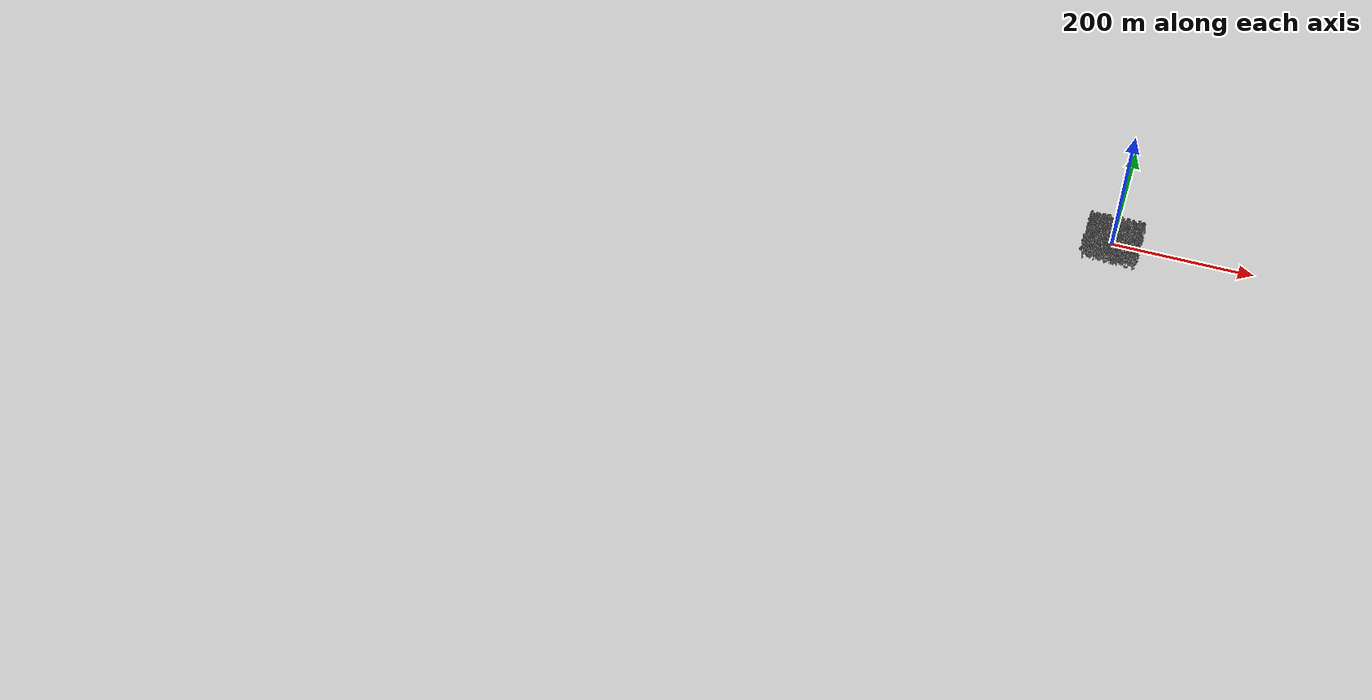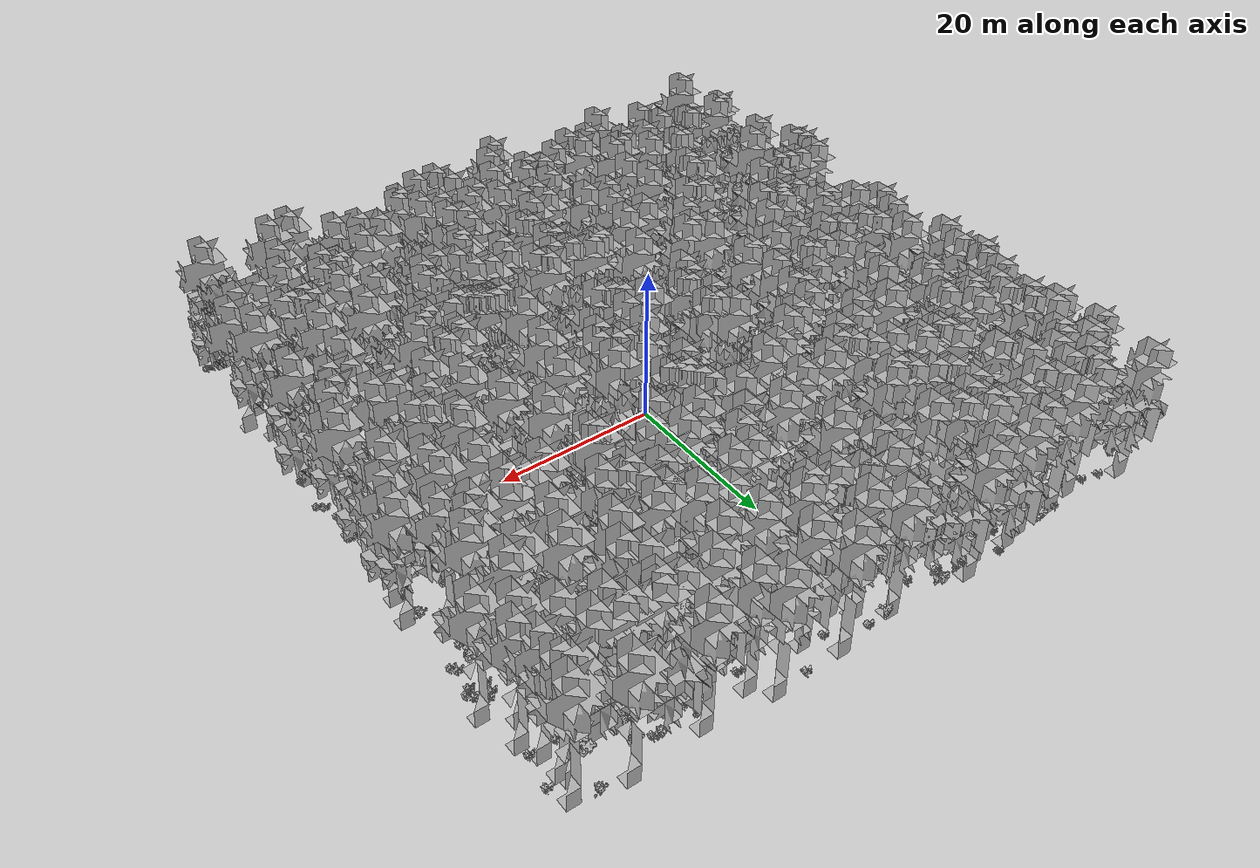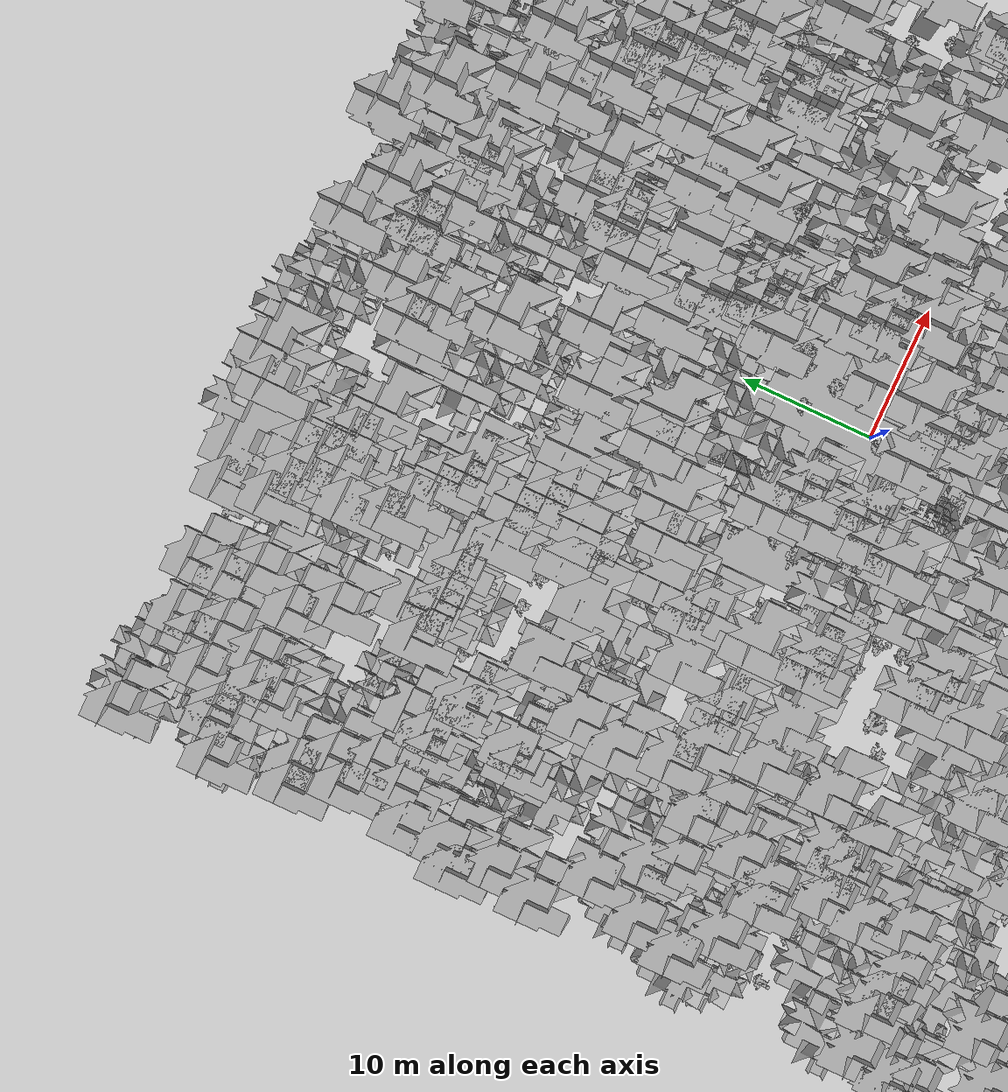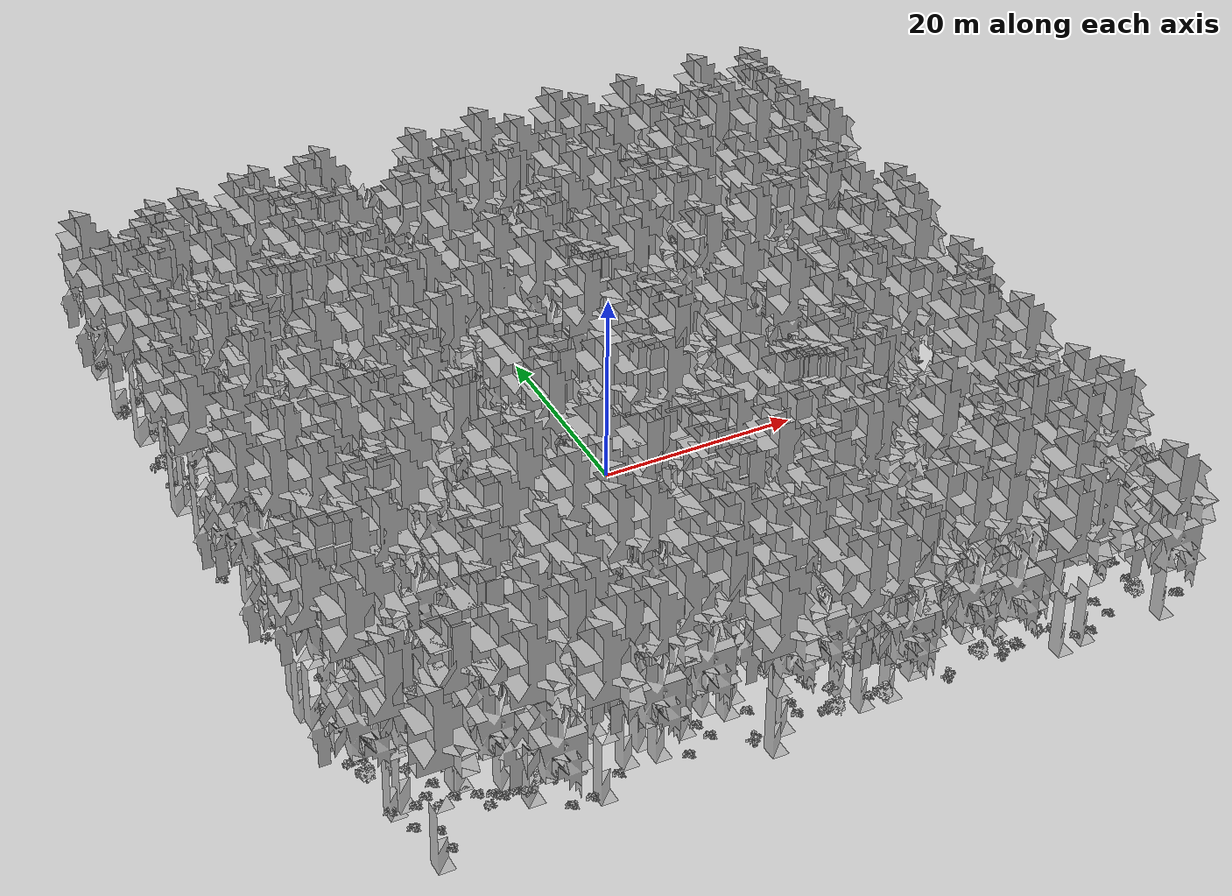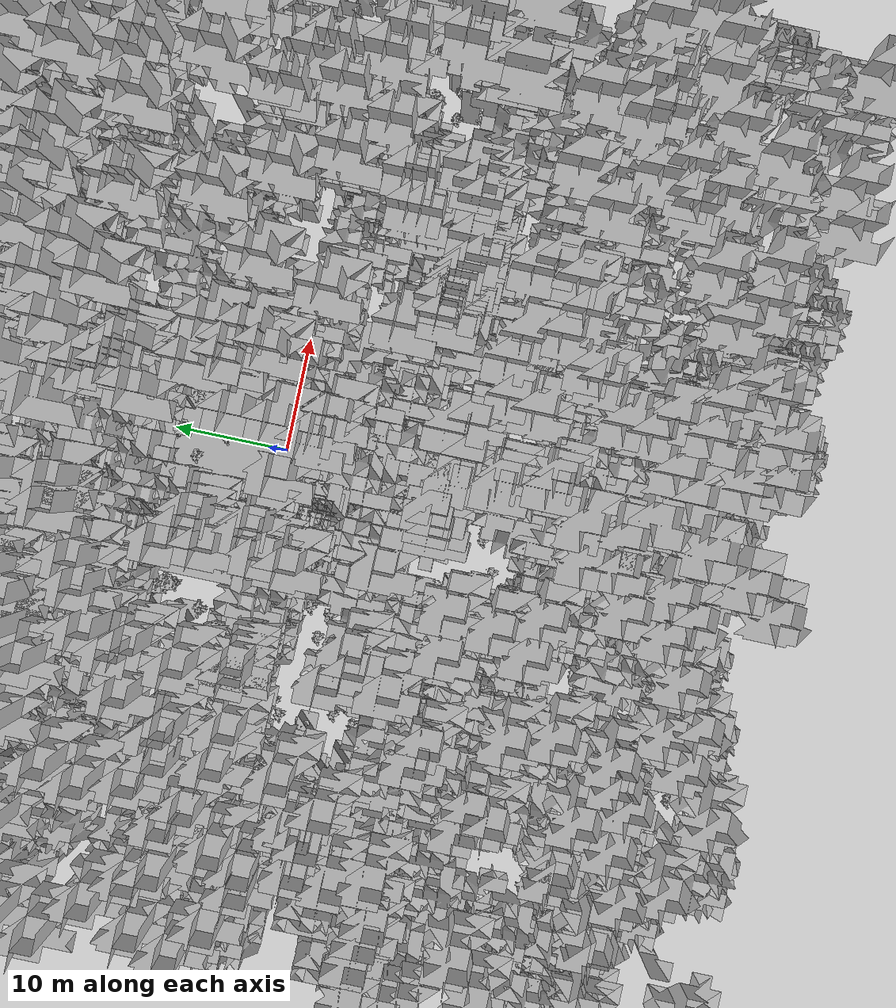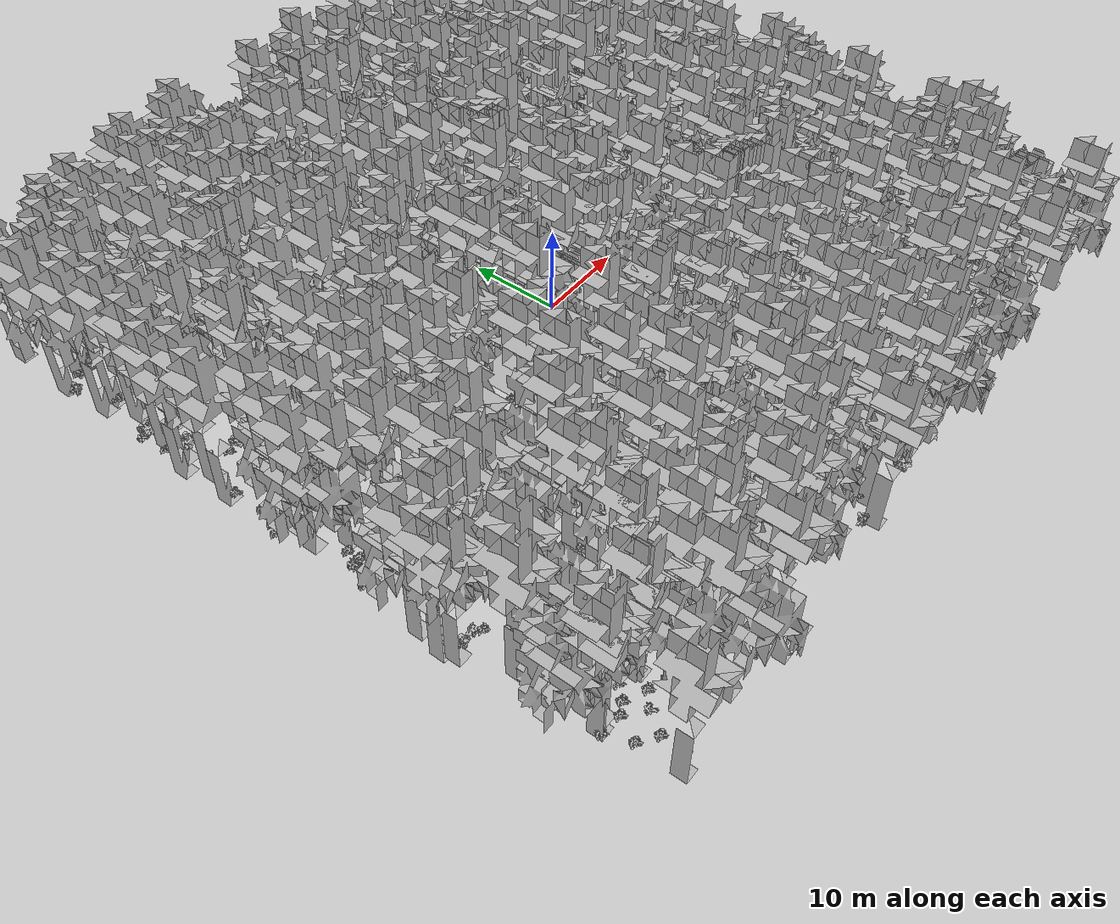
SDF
<sdf version="1.7">
    <world name="default">
        <plugin name="mrs_gazebo_static_transform_republisher_plugin" filename="libMrsGazeboCommonResources_StaticTransformRepublisher.so"/>
        <spherical_coordinates>
            <surface_model>EARTH_WGS84</surface_model>
            <latitude_deg>47.3977</latitude_deg>
            <longitude_deg>8.54559</longitude_deg>
            <elevation>0</elevation>
            <heading_deg>0</heading_deg>
        </spherical_coordinates>
        <physics name="default_physics" default="0" type="ode">
            <ode>
                <solver>
                    <type>quick</type>
                    <iters>10</iters>
                    <sor>1.3</sor>
                    <use_dynamic_moi_rescaling>0</use_dynamic_moi_rescaling>
                </solver>
                <constraints>
                    <cfm>0</cfm>
                    <erp>0.2</erp>
                    <contact_max_correcting_vel>1000</contact_max_correcting_vel>
                    <contact_surface_layer>0.001</contact_surface_layer>
                </constraints>
            </ode>
            <max_step_size>0.004</max_step_size>
            <real_time_factor>1</real_time_factor>
            <real_time_update_rate>250</real_time_update_rate>
        </physics>
        <scene>
            <shadows>0</shadows>
            <ambient>0.4 0.4 0.4 1</ambient>
            <background>0.7 0.7 0.7 1</background>
        </scene>
        <light name="sun" type="directional">
            <pose>0 0 1000 0.4 0.2 0</pose>
            <diffuse>1 1 1 1</diffuse>
            <specular>0.6 0.6 0.6 1</specular>
            <direction>0.1 0.1 -0.9</direction>
            <attenuation>
                <range>20</range>
                <constant>0.5</constant>
                <linear>0.01</linear>
                <quadratic>0.001</quadratic>
            </attenuation>
            <cast_shadows>1</cast_shadows>
            <spot>
                <inner_angle>0</inner_angle>
                <outer_angle>0</outer_angle>
                <falloff>0</falloff>
            </spot>
        </light>
        <model name="ground_plane">
            <static>1</static>
            <link name="link">
                <collision name="collision">
                    <pose>-50 0 0 0 -0 0</pose>
                    <geometry>
                        <plane>
                            <normal>0 0 1</normal>
                            <size>80 80</size>
                        </plane>
                    </geometry>
                    <surface>
                        <contact>
                            <ode>
                                <min_depth>0.01</min_depth>
                                <max_vel>0</max_vel>
                            </ode>
                        </contact>
                        <friction>
                            <ode/>
                            <torsional>
                                <ode/>
                            </torsional>
                        </friction>
                        <bounce/>
                    </surface>
                    <max_contacts>10</max_contacts>
                </collision>
                <visual name="grass">
                    <pose>0 0 0 0 -0 0</pose>
                    <cast_shadows>0</cast_shadows>
                    <geometry>
                        <mesh>
                            <scale>0.46714285714285714 0.46714285714285714 0.1</scale>
                            <uri>file://grass_plane/meshes/grass_plane.dae</uri>
                        </mesh>
                    </geometry>
                </visual>
                <self_collide>0</self_collide>
                <enable_wind>0</enable_wind>
                <kinematic>0</kinematic>
            </link>
        </model>
        <model name="the_void">
            <static>1</static>
            <link name="link">
                <pose>0 0 0.1 0 -0 0</pose>
                <visual name="the_void">
                    <pose>0 0 2 0 -0 0</pose>
                    <geometry>
                        <sphere>
                            <radius>0.25</radius>
                        </sphere>
                    </geometry>
                    <material>
                        <script>
                            <uri>file://media/materials/scripts/Gazebo.material</uri>
                            <name>Gazebo/Black</name>
                        </script>
                    </material>
                </visual>
                <self_collide>0</self_collide>
                <enable_wind>0</enable_wind>
                <kinematic>0</kinematic>
            </link>
            <pose>-1000 -1000 0 0 -0 0</pose>
        </model>
        <gui fullscreen="0">
            <camera name="camera">
                <pose>35.1577 98.6044 40.0204 0 0.407996 -1.99761</pose>
                <view_controller>orbit</view_controller>
                <projection_type>perspective</projection_type>
            </camera>
        </gui>
        <plugin name="mrs_gazebo_rviz_cam_synchronizer" filename="libMrsGazeboCommonResources_RvizCameraSynchronizer.so">
            <target_frame_id>gazebo_user_camera</target_frame_id>
            <world_origin_frame_id>uav1/gps_origin</world_origin_frame_id>
            <frame_to_follow>uav1</frame_to_follow>
        </plugin>
        <gravity>0 0 -9.8066</gravity>
        <magnetic_field>6e-06 2.3e-05 -4.2e-05</magnetic_field>
        <atmosphere type="adiabatic"/>
        <wind/>
        <model name="Tree 0">
            <static>1</static>
            <pose>15.971096686707469 16.843119865354126 0 1.57079 -0 0</pose>
            <link name="link">
                <pose>0 0 0 0 -0 0</pose>
                <collision name="collision">
                    <geometry>
                        <mesh>
                            <scale>3.5 5 3.5</scale>
                            <uri>model://tree_2/meshes/tree_2.obj</uri>
                        </mesh>
                    </geometry>
                    <max_contacts>10</max_contacts>
                    <surface>
                        <contact>
                            <ode/>
                        </contact>
                        <bounce/>
                        <friction>
                            <torsional>
                                <ode/>
                            </torsional>
                            <ode/>
                        </friction>
                    </surface>
                </collision>
                <visual name="visual">
                    <geometry>
                        <mesh>
                            <scale>3.5 5 3.5</scale>
                            <uri>model://tree_2/meshes/tree_2.obj</uri>
                        </mesh>
                    </geometry>
                </visual>
                <self_collide>0</self_collide>
                <enable_wind>0</enable_wind>
                <kinematic>0</kinematic>
            </link>
        </model>
        <model name="Tree 1">
            <static>1</static>
            <pose>-37.42710866923371 31.774682158675503 0 1.57079 -0 0</pose>
            <link name="link">
                <pose>0 0 0 0 -0 0</pose>
                <collision name="collision">
                    <geometry>
                        <mesh>
                            <scale>3.5 5 3.5</scale>
                            <uri>model://tree_2/meshes/tree_2.obj</uri>
                        </mesh>
                    </geometry>
                    <max_contacts>10</max_contacts>
                    <surface>
                        <contact>
                            <ode/>
                        </contact>
                        <bounce/>
                        <friction>
                            <torsional>
                                <ode/>
                            </torsional>
                            <ode/>
                        </friction>
                    </surface>
                </collision>
                <visual name="visual">
                    <geometry>
                        <mesh>
                            <scale>3.5 5 3.5</scale>
                            <uri>model://tree_2/meshes/tree_2.obj</uri>
                        </mesh>
                    </geometry>
                </visual>
                <self_collide>0</self_collide>
                <enable_wind>0</enable_wind>
                <kinematic>0</kinematic>
            </link>
        </model>
        <model name="Tree 2">
            <static>1</static>
            <pose>25.895939131079473 -24.983478622586304 0 1.57079 -0 0</pose>
            <link name="link">
                <pose>0 0 0 0 -0 0</pose>
                <collision name="collision">
                    <geometry>
                        <mesh>
                            <scale>3.5 5 3.5</scale>
                            <uri>model://tree_9/meshes/tree_9.obj</uri>
                        </mesh>
                    </geometry>
                    <max_contacts>10</max_contacts>
                    <surface>
                        <contact>
                            <ode/>
                        </contact>
                        <bounce/>
                        <friction>
                            <torsional>
                                <ode/>
                            </torsional>
                            <ode/>
                        </friction>
                    </surface>
                </collision>
                <visual name="visual">
                    <geometry>
                        <mesh>
                            <scale>3.5 5 3.5</scale>
                            <uri>model://tree_9/meshes/tree_9.obj</uri>
                        </mesh>
                    </geometry>
                </visual>
                <self_collide>0</self_collide>
                <enable_wind>0</enable_wind>
                <kinematic>0</kinematic>
            </link>
        </model>
        <model name="Tree 3">
            <static>1</static>
            <pose>-7.1219916832344055 -32.47217001834699 0 1.57079 -0 0</pose>
            <link name="link">
                <pose>0 0 0 0 -0 0</pose>
                <collision name="collision">
                    <geometry>
                        <mesh>
                            <scale>3.5 5 3.5</scale>
                            <uri>model://tree_9/meshes/tree_9.obj</uri>
                        </mesh>
                    </geometry>
                    <max_contacts>10</max_contacts>
                    <surface>
                        <contact>
                            <ode/>
                        </contact>
                        <bounce/>
                        <friction>
                            <torsional>
                                <ode/>
                            </torsional>
                            <ode/>
                        </friction>
                    </surface>
                </collision>
                <visual name="visual">
                    <geometry>
                        <mesh>
                            <scale>3.5 5 3.5</scale>
                            <uri>model://tree_9/meshes/tree_9.obj</uri>
                        </mesh>
                    </geometry>
                </visual>
                <self_collide>0</self_collide>
                <enable_wind>0</enable_wind>
                <kinematic>0</kinematic>
            </link>
        </model>
        <model name="Tree 4">
            <static>1</static>
            <pose>22.770856354891208 23.732544014960027 0 1.57079 -0 0</pose>
            <link name="link">
                <pose>0 0 0 0 -0 0</pose>
                <collision name="collision">
                    <geometry>
                        <mesh>
                            <scale>3.5 5 3.5</scale>
                            <uri>model://tree_2/meshes/tree_2.obj</uri>
                        </mesh>
                    </geometry>
                    <max_contacts>10</max_contacts>
                    <surface>
                        <contact>
                            <ode/>
                        </contact>
                        <bounce/>
                        <friction>
                            <torsional>
                                <ode/>
                            </torsional>
                            <ode/>
                        </friction>
                    </surface>
                </collision>
                <visual name="visual">
                    <geometry>
                        <mesh>
                            <scale>3.5 5 3.5</scale>
                            <uri>model://tree_2/meshes/tree_2.obj</uri>
                        </mesh>
                    </geometry>
                </visual>
                <self_collide>0</self_collide>
                <enable_wind>0</enable_wind>
                <kinematic>0</kinematic>
            </link>
        </model>
        <model name="Tree 5">
            <static>1</static>
            <pose>2.541199263562561 26.002486133638797 0 1.57079 -0 0</pose>
            <link name="link">
                <pose>0 0 0 0 -0 0</pose>
                <collision name="collision">
                    <geometry>
                        <mesh>
                            <scale>3.5 5 3.5</scale>
                            <uri>model://tree_2/meshes/tree_2.obj</uri>
                        </mesh>
                    </geometry>
                    <max_contacts>10</max_contacts>
                    <surface>
                        <contact>
                            <ode/>
                        </contact>
                        <bounce/>
                        <friction>
                            <torsional>
                                <ode/>
                            </torsional>
                            <ode/>
                        </friction>
                    </surface>
                </collision>
                <visual name="visual">
                    <geometry>
                        <mesh>
                            <scale>3.5 5 3.5</scale>
                            <uri>model://tree_2/meshes/tree_2.obj</uri>
                        </mesh>
                    </geometry>
                </visual>
                <self_collide>0</self_collide>
                <enable_wind>0</enable_wind>
                <kinematic>0</kinematic>
            </link>
        </model>
        <model name="Tree 6">
            <static>1</static>
            <pose>-35.78690549846158 32.35860425664433 0 1.57079 -0 0</pose>
            <link name="link">
                <pose>0 0 0 0 -0 0</pose>
                <collision name="collision">
                    <geometry>
                        <mesh>
                            <scale>3.5 5 3.5</scale>
                            <uri>model://tree_9/meshes/tree_9.obj</uri>
                        </mesh>
                    </geometry>
                    <max_contacts>10</max_contacts>
                    <surface>
                        <contact>
                            <ode/>
                        </contact>
                        <bounce/>
                        <friction>
                            <torsional>
                                <ode/>
                            </torsional>
                            <ode/>
                        </friction>
                    </surface>
                </collision>
                <visual name="visual">
                    <geometry>
                        <mesh>
                            <scale>3.5 5 3.5</scale>
                            <uri>model://tree_9/meshes/tree_9.obj</uri>
                        </mesh>
                    </geometry>
                </visual>
                <self_collide>0</self_collide>
                <enable_wind>0</enable_wind>
                <kinematic>0</kinematic>
            </link>
        </model>
        <model name="Tree 7">
            <static>1</static>
            <pose>-28.308376100540656 1.2800940678118167 0 1.57079 -0 0</pose>
            <link name="link">
                <pose>0 0 0 0 -0 0</pose>
                <collision name="collision">
                    <geometry>
                        <mesh>
                            <scale>3.5 5 3.5</scale>
                            <uri>model://tree_2/meshes/tree_2.obj</uri>
                        </mesh>
                    </geometry>
                    <max_contacts>10</max_contacts>
                    <surface>
                        <contact>
                            <ode/>
                        </contact>
                        <bounce/>
                        <friction>
                            <torsional>
                                <ode/>
                            </torsional>
                            <ode/>
                        </friction>
                    </surface>
                </collision>
                <visual name="visual">
                    <geometry>
                        <mesh>
                            <scale>3.5 5 3.5</scale>
                            <uri>model://tree_2/meshes/tree_2.obj</uri>
                        </mesh>
                    </geometry>
                </visual>
                <self_collide>0</self_collide>
                <enable_wind>0</enable_wind>
                <kinematic>0</kinematic>
            </link>
        </model>
        <model name="Tree 8">
            <static>1</static>
            <pose>-19.105477431183694 34.489229107266965 0 1.57079 -0 0</pose>
            <link name="link">
                <pose>0 0 0 0 -0 0</pose>
                <collision name="collision">
                    <geometry>
                        <mesh>
                            <scale>3.5 5 3.5</scale>
                            <uri>model://tree_9/meshes/tree_9.obj</uri>
                        </mesh>
                    </geometry>
                    <max_contacts>10</max_contacts>
                    <surface>
                        <contact>
                            <ode/>
                        </contact>
                        <bounce/>
                        <friction>
                            <torsional>
                                <ode/>
                            </torsional>
                            <ode/>
                        </friction>
                    </surface>
                </collision>
                <visual name="visual">
                    <geometry>
                        <mesh>
                            <scale>3.5 5 3.5</scale>
                            <uri>model://tree_9/meshes/tree_9.obj</uri>
                        </mesh>
                    </geometry>
                </visual>
                <self_collide>0</self_collide>
                <enable_wind>0</enable_wind>
                <kinematic>0</kinematic>
            </link>
        </model>
        <model name="Tree 9">
            <static>1</static>
            <pose>14.268718768158244 -11.616131461312893 0 1.57079 -0 0</pose>
            <link name="link">
                <pose>0 0 0 0 -0 0</pose>
                <collision name="collision">
                    <geometry>
                        <mesh>
                            <scale>3.5 5 3.5</scale>
                            <uri>model://tree_9/meshes/tree_9.obj</uri>
                        </mesh>
                    </geometry>
                    <max_contacts>10</max_contacts>
                    <surface>
                        <contact>
                            <ode/>
                        </contact>
                        <bounce/>
                        <friction>
                            <torsional>
                                <ode/>
                            </torsional>
                            <ode/>
                        </friction>
                    </surface>
                </collision>
                <visual name="visual">
                    <geometry>
                        <mesh>
                            <scale>3.5 5 3.5</scale>
                            <uri>model://tree_9/meshes/tree_9.obj</uri>
                        </mesh>
                    </geometry>
                </visual>
                <self_collide>0</self_collide>
                <enable_wind>0</enable_wind>
                <kinematic>0</kinematic>
            </link>
        </model>
        <model name="Tree 10">
            <static>1</static>
            <pose>-9.611893628563536 -35.80319562311524 0 1.57079 -0 0</pose>
            <link name="link">
                <pose>0 0 0 0 -0 0</pose>
                <collision name="collision">
                    <geometry>
                        <mesh>
                            <scale>3.5 5 3.5</scale>
                            <uri>model://tree_2/meshes/tree_2.obj</uri>
                        </mesh>
                    </geometry>
                    <max_contacts>10</max_contacts>
                    <surface>
                        <contact>
                            <ode/>
                        </contact>
                        <bounce/>
                        <friction>
                            <torsional>
                                <ode/>
                            </torsional>
                            <ode/>
                        </friction>
                    </surface>
                </collision>
                <visual name="visual">
                    <geometry>
                        <mesh>
                            <scale>3.5 5 3.5</scale>
                            <uri>model://tree_2/meshes/tree_2.obj</uri>
                        </mesh>
                    </geometry>
                </visual>
                <self_collide>0</self_collide>
                <enable_wind>0</enable_wind>
                <kinematic>0</kinematic>
            </link>
        </model>
        <model name="Tree 11">
            <static>1</static>
            <pose>-12.115787374584695 39.58037663564966 0 1.57079 -0 0</pose>
            <link name="link">
                <pose>0 0 0 0 -0 0</pose>
                <collision name="collision">
                    <geometry>
                        <mesh>
                            <scale>3.5 5 3.5</scale>
                            <uri>model://tree_9/meshes/tree_9.obj</uri>
                        </mesh>
                    </geometry>
                    <max_contacts>10</max_contacts>
                    <surface>
                        <contact>
                            <ode/>
                        </contact>
                        <bounce/>
                        <friction>
                            <torsional>
                                <ode/>
                            </torsional>
                            <ode/>
                        </friction>
                    </surface>
                </collision>
                <visual name="visual">
                    <geometry>
                        <mesh>
                            <scale>3.5 5 3.5</scale>
                            <uri>model://tree_9/meshes/tree_9.obj</uri>
                        </mesh>
                    </geometry>
                </visual>
                <self_collide>0</self_collide>
                <enable_wind>0</enable_wind>
                <kinematic>0</kinematic>
            </link>
        </model>
        <model name="Tree 12">
            <static>1</static>
            <pose>36.71630920072428 -28.52139253806697 0 1.57079 -0 0</pose>
            <link name="link">
                <pose>0 0 0 0 -0 0</pose>
                <collision name="collision">
                    <geometry>
                        <mesh>
                            <scale>3.5 5 3.5</scale>
                            <uri>model://tree_9/meshes/tree_9.obj</uri>
                        </mesh>
                    </geometry>
                    <max_contacts>10</max_contacts>
                    <surface>
                        <contact>
                            <ode/>
                        </contact>
                        <bounce/>
                        <friction>
                            <torsional>
                                <ode/>
                            </torsional>
                            <ode/>
                        </friction>
                    </surface>
                </collision>
                <visual name="visual">
                    <geometry>
                        <mesh>
                            <scale>3.5 5 3.5</scale>
                            <uri>model://tree_9/meshes/tree_9.obj</uri>
                        </mesh>
                    </geometry>
                </visual>
                <self_collide>0</self_collide>
                <enable_wind>0</enable_wind>
                <kinematic>0</kinematic>
            </link>
        </model>
        <model name="Tree 13">
            <static>1</static>
            <pose>13.4185361888932 -11.179486711648174 0 1.57079 -0 0</pose>
            <link name="link">
                <pose>0 0 0 0 -0 0</pose>
                <collision name="collision">
                    <geometry>
                        <mesh>
                            <scale>3.5 5 3.5</scale>
                            <uri>model://tree_9/meshes/tree_9.obj</uri>
                        </mesh>
                    </geometry>
                    <max_contacts>10</max_contacts>
                    <surface>
                        <contact>
                            <ode/>
                        </contact>
                        <bounce/>
                        <friction>
                            <torsional>
                                <ode/>
                            </torsional>
                            <ode/>
                        </friction>
                    </surface>
                </collision>
                <visual name="visual">
                    <geometry>
                        <mesh>
                            <scale>3.5 5 3.5</scale>
                            <uri>model://tree_9/meshes/tree_9.obj</uri>
                        </mesh>
                    </geometry>
                </visual>
                <self_collide>0</self_collide>
                <enable_wind>0</enable_wind>
                <kinematic>0</kinematic>
            </link>
        </model>
        <model name="Tree 14">
            <static>1</static>
            <pose>35.54837640141666 3.432613627975698 0 1.57079 -0 0</pose>
            <link name="link">
                <pose>0 0 0 0 -0 0</pose>
                <collision name="collision">
                    <geometry>
                        <mesh>
                            <scale>3.5 5 3.5</scale>
                            <uri>model://tree_9/meshes/tree_9.obj</uri>
                        </mesh>
                    </geometry>
                    <max_contacts>10</max_contacts>
                    <surface>
                        <contact>
                            <ode/>
                        </contact>
                        <bounce/>
                        <friction>
                            <torsional>
                                <ode/>
                            </torsional>
                            <ode/>
                        </friction>
                    </surface>
                </collision>
                <visual name="visual">
                    <geometry>
                        <mesh>
                            <scale>3.5 5 3.5</scale>
                            <uri>model://tree_9/meshes/tree_9.obj</uri>
                        </mesh>
                    </geometry>
                </visual>
                <self_collide>0</self_collide>
                <enable_wind>0</enable_wind>
                <kinematic>0</kinematic>
            </link>
        </model>
        <model name="Tree 15">
            <static>1</static>
            <pose>-3.008472073308333 11.177539338462708 0 1.57079 -0 0</pose>
            <link name="link">
                <pose>0 0 0 0 -0 0</pose>
                <collision name="collision">
                    <geometry>
                        <mesh>
                            <scale>3.5 5 3.5</scale>
                            <uri>model://tree_2/meshes/tree_2.obj</uri>
                        </mesh>
                    </geometry>
                    <max_contacts>10</max_contacts>
                    <surface>
                        <contact>
                            <ode/>
                        </contact>
                        <bounce/>
                        <friction>
                            <torsional>
                                <ode/>
                            </torsional>
                            <ode/>
                        </friction>
                    </surface>
                </collision>
                <visual name="visual">
                    <geometry>
                        <mesh>
                            <scale>3.5 5 3.5</scale>
                            <uri>model://tree_2/meshes/tree_2.obj</uri>
                        </mesh>
                    </geometry>
                </visual>
                <self_collide>0</self_collide>
                <enable_wind>0</enable_wind>
                <kinematic>0</kinematic>
            </link>
        </model>
        <model name="Tree 16">
            <static>1</static>
            <pose>-14.702496300402451 20.017734769742283 0 1.57079 -0 0</pose>
            <link name="link">
                <pose>0 0 0 0 -0 0</pose>
                <collision name="collision">
                    <geometry>
                        <mesh>
                            <scale>3.5 5 3.5</scale>
                            <uri>model://tree_9/meshes/tree_9.obj</uri>
                        </mesh>
                    </geometry>
                    <max_contacts>10</max_contacts>
                    <surface>
                        <contact>
                            <ode/>
                        </contact>
                        <bounce/>
                        <friction>
                            <torsional>
                                <ode/>
                            </torsional>
                            <ode/>
                        </friction>
                    </surface>
                </collision>
                <visual name="visual">
                    <geometry>
                        <mesh>
                            <scale>3.5 5 3.5</scale>
                            <uri>model://tree_9/meshes/tree_9.obj</uri>
                        </mesh>
                    </geometry>
                </visual>
                <self_collide>0</self_collide>
                <enable_wind>0</enable_wind>
                <kinematic>0</kinematic>
            </link>
        </model>
        <model name="Tree 17">
            <static>1</static>
            <pose>20.775173851776394 -32.00845553711174 0 1.57079 -0 0</pose>
            <link name="link">
                <pose>0 0 0 0 -0 0</pose>
                <collision name="collision">
                    <geometry>
                        <mesh>
                            <scale>3.5 5 3.5</scale>
                            <uri>model://tree_2/meshes/tree_2.obj</uri>
                        </mesh>
                    </geometry>
                    <max_contacts>10</max_contacts>
                    <surface>
                        <contact>
                            <ode/>
                        </contact>
                        <bounce/>
                        <friction>
                            <torsional>
                                <ode/>
                            </torsional>
                            <ode/>
                        </friction>
                    </surface>
                </collision>
                <visual name="visual">
                    <geometry>
                        <mesh>
                            <scale>3.5 5 3.5</scale>
                            <uri>model://tree_2/meshes/tree_2.obj</uri>
                        </mesh>
                    </geometry>
                </visual>
                <self_collide>0</self_collide>
                <enable_wind>0</enable_wind>
                <kinematic>0</kinematic>
            </link>
        </model>
        <model name="Tree 18">
            <static>1</static>
            <pose>-19.255456930846012 0.3580390568446177 0 1.57079 -0 0</pose>
            <link name="link">
                <pose>0 0 0 0 -0 0</pose>
                <collision name="collision">
                    <geometry>
                        <mesh>
                            <scale>3.5 5 3.5</scale>
                            <uri>model://tree_2/meshes/tree_2.obj</uri>
                        </mesh>
                    </geometry>
                    <max_contacts>10</max_contacts>
                    <surface>
                        <contact>
                            <ode/>
                        </contact>
                        <bounce/>
                        <friction>
                            <torsional>
                                <ode/>
                            </torsional>
                            <ode/>
                        </friction>
                    </surface>
                </collision>
                <visual name="visual">
                    <geometry>
                        <mesh>
                            <scale>3.5 5 3.5</scale>
                            <uri>model://tree_2/meshes/tree_2.obj</uri>
                        </mesh>
                    </geometry>
                </visual>
                <self_collide>0</self_collide>
                <enable_wind>0</enable_wind>
                <kinematic>0</kinematic>
            </link>
        </model>
        <model name="Tree 19">
            <static>1</static>
            <pose>11.65281882690229 7.673728056305144 0 1.57079 -0 0</pose>
            <link name="link">
                <pose>0 0 0 0 -0 0</pose>
                <collision name="collision">
                    <geometry>
                        <mesh>
                            <scale>3.5 5 3.5</scale>
                            <uri>model://tree_2/meshes/tree_2.obj</uri>
                        </mesh>
                    </geometry>
                    <max_contacts>10</max_contacts>
                    <surface>
                        <contact>
                            <ode/>
                        </contact>
                        <bounce/>
                        <friction>
                            <torsional>
                                <ode/>
                            </torsional>
                            <ode/>
                        </friction>
                    </surface>
                </collision>
                <visual name="visual">
                    <geometry>
                        <mesh>
                            <scale>3.5 5 3.5</scale>
                            <uri>model://tree_2/meshes/tree_2.obj</uri>
                        </mesh>
                    </geometry>
                </visual>
                <self_collide>0</self_collide>
                <enable_wind>0</enable_wind>
                <kinematic>0</kinematic>
            </link>
        </model>
        <model name="Tree 20">
            <static>1</static>
            <pose>2.6620295948769908 -22.221064124453882 0 1.57079 -0 0</pose>
            <link name="link">
                <pose>0 0 0 0 -0 0</pose>
                <collision name="collision">
                    <geometry>
                        <mesh>
                            <scale>3.5 5 3.5</scale>
                            <uri>model://tree_9/meshes/tree_9.obj</uri>
                        </mesh>
                    </geometry>
                    <max_contacts>10</max_contacts>
                    <surface>
                        <contact>
                            <ode/>
                        </contact>
                        <bounce/>
                        <friction>
                            <torsional>
                                <ode/>
                            </torsional>
                            <ode/>
                        </friction>
                    </surface>
                </collision>
                <visual name="visual">
                    <geometry>
                        <mesh>
                            <scale>3.5 5 3.5</scale>
                            <uri>model://tree_9/meshes/tree_9.obj</uri>
                        </mesh>
                    </geometry>
                </visual>
                <self_collide>0</self_collide>
                <enable_wind>0</enable_wind>
                <kinematic>0</kinematic>
            </link>
        </model>
        <model name="Tree 21">
            <static>1</static>
            <pose>19.55637076471522 -8.755730757932383 0 1.57079 -0 0</pose>
            <link name="link">
                <pose>0 0 0 0 -0 0</pose>
                <collision name="collision">
                    <geometry>
                        <mesh>
                            <scale>3.5 5 3.5</scale>
                            <uri>model://tree_9/meshes/tree_9.obj</uri>
                        </mesh>
                    </geometry>
                    <max_contacts>10</max_contacts>
                    <surface>
                        <contact>
                            <ode/>
                        </contact>
                        <bounce/>
                        <friction>
                            <torsional>
                                <ode/>
                            </torsional>
                            <ode/>
                        </friction>
                    </surface>
                </collision>
                <visual name="visual">
                    <geometry>
                        <mesh>
                            <scale>3.5 5 3.5</scale>
                            <uri>model://tree_9/meshes/tree_9.obj</uri>
                        </mesh>
                    </geometry>
                </visual>
                <self_collide>0</self_collide>
                <enable_wind>0</enable_wind>
                <kinematic>0</kinematic>
            </link>
        </model>
        <model name="Tree 22">
            <static>1</static>
            <pose>10.140106296657272 -36.62080904243534 0 1.57079 -0 0</pose>
            <link name="link">
                <pose>0 0 0 0 -0 0</pose>
                <collision name="collision">
                    <geometry>
                        <mesh>
                            <scale>3.5 5 3.5</scale>
                            <uri>model://tree_2/meshes/tree_2.obj</uri>
                        </mesh>
                    </geometry>
                    <max_contacts>10</max_contacts>
                    <surface>
                        <contact>
                            <ode/>
                        </contact>
                        <bounce/>
                        <friction>
                            <torsional>
                                <ode/>
                            </torsional>
                            <ode/>
                        </friction>
                    </surface>
                </collision>
                <visual name="visual">
                    <geometry>
                        <mesh>
                            <scale>3.5 5 3.5</scale>
                            <uri>model://tree_2/meshes/tree_2.obj</uri>
                        </mesh>
                    </geometry>
                </visual>
                <self_collide>0</self_collide>
                <enable_wind>0</enable_wind>
                <kinematic>0</kinematic>
            </link>
        </model>
        <model name="Tree 23">
            <static>1</static>
            <pose>-38.60829791847613 -17.76087794490655 0 1.57079 -0 0</pose>
            <link name="link">
                <pose>0 0 0 0 -0 0</pose>
                <collision name="collision">
                    <geometry>
                        <mesh>
                            <scale>3.5 5 3.5</scale>
                            <uri>model://tree_9/meshes/tree_9.obj</uri>
                        </mesh>
                    </geometry>
                    <max_contacts>10</max_contacts>
                    <surface>
                        <contact>
                            <ode/>
                        </contact>
                        <bounce/>
                        <friction>
                            <torsional>
                                <ode/>
                            </torsional>
                            <ode/>
                        </friction>
                    </surface>
                </collision>
                <visual name="visual">
                    <geometry>
                        <mesh>
                            <scale>3.5 5 3.5</scale>
                            <uri>model://tree_9/meshes/tree_9.obj</uri>
                        </mesh>
                    </geometry>
                </visual>
                <self_collide>0</self_collide>
                <enable_wind>0</enable_wind>
                <kinematic>0</kinematic>
            </link>
        </model>
        <model name="Tree 24">
            <static>1</static>
            <pose>-9.1710137024636 -20.092503621089026 0 1.57079 -0 0</pose>
            <link name="link">
                <pose>0 0 0 0 -0 0</pose>
                <collision name="collision">
                    <geometry>
                        <mesh>
                            <scale>3.5 5 3.5</scale>
                            <uri>model://tree_9/meshes/tree_9.obj</uri>
                        </mesh>
                    </geometry>
                    <max_contacts>10</max_contacts>
                    <surface>
                        <contact>
                            <ode/>
                        </contact>
                        <bounce/>
                        <friction>
                            <torsional>
                                <ode/>
                            </torsional>
                            <ode/>
                        </friction>
                    </surface>
                </collision>
                <visual name="visual">
                    <geometry>
                        <mesh>
                            <scale>3.5 5 3.5</scale>
                            <uri>model://tree_9/meshes/tree_9.obj</uri>
                        </mesh>
                    </geometry>
                </visual>
                <self_collide>0</self_collide>
                <enable_wind>0</enable_wind>
                <kinematic>0</kinematic>
            </link>
        </model>
        <model name="Tree 25">
            <static>1</static>
            <pose>-16.769617743457086 -12.314967718828854 0 1.57079 -0 0</pose>
            <link name="link">
                <pose>0 0 0 0 -0 0</pose>
                <collision name="collision">
                    <geometry>
                        <mesh>
                            <scale>3.5 5 3.5</scale>
                            <uri>model://tree_2/meshes/tree_2.obj</uri>
                        </mesh>
                    </geometry>
                    <max_contacts>10</max_contacts>
                    <surface>
                        <contact>
                            <ode/>
                        </contact>
                        <bounce/>
                        <friction>
                            <torsional>
                                <ode/>
                            </torsional>
                            <ode/>
                        </friction>
                    </surface>
                </collision>
                <visual name="visual">
                    <geometry>
                        <mesh>
                            <scale>3.5 5 3.5</scale>
                            <uri>model://tree_2/meshes/tree_2.obj</uri>
                        </mesh>
                    </geometry>
                </visual>
                <self_collide>0</self_collide>
                <enable_wind>0</enable_wind>
                <kinematic>0</kinematic>
            </link>
        </model>
        <model name="Tree 26">
            <static>1</static>
            <pose>12.870327430192127 -20.458326522849546 0 1.57079 -0 0</pose>
            <link name="link">
                <pose>0 0 0 0 -0 0</pose>
                <collision name="collision">
                    <geometry>
                        <mesh>
                            <scale>3.5 5 3.5</scale>
                            <uri>model://tree_9/meshes/tree_9.obj</uri>
                        </mesh>
                    </geometry>
                    <max_contacts>10</max_contacts>
                    <surface>
                        <contact>
                            <ode/>
                        </contact>
                        <bounce/>
                        <friction>
                            <torsional>
                                <ode/>
                            </torsional>
                            <ode/>
                        </friction>
                    </surface>
                </collision>
                <visual name="visual">
                    <geometry>
                        <mesh>
                            <scale>3.5 5 3.5</scale>
                            <uri>model://tree_9/meshes/tree_9.obj</uri>
                        </mesh>
                    </geometry>
                </visual>
                <self_collide>0</self_collide>
                <enable_wind>0</enable_wind>
                <kinematic>0</kinematic>
            </link>
        </model>
        <model name="Tree 27">
            <static>1</static>
            <pose>24.695511156107422 34.17719131181778 0 1.57079 -0 0</pose>
            <link name="link">
                <pose>0 0 0 0 -0 0</pose>
                <collision name="collision">
                    <geometry>
                        <mesh>
                            <scale>3.5 5 3.5</scale>
                            <uri>model://tree_9/meshes/tree_9.obj</uri>
                        </mesh>
                    </geometry>
                    <max_contacts>10</max_contacts>
                    <surface>
                        <contact>
                            <ode/>
                        </contact>
                        <bounce/>
                        <friction>
                            <torsional>
                                <ode/>
                            </torsional>
                            <ode/>
                        </friction>
                    </surface>
                </collision>
                <visual name="visual">
                    <geometry>
                        <mesh>
                            <scale>3.5 5 3.5</scale>
                            <uri>model://tree_9/meshes/tree_9.obj</uri>
                        </mesh>
                    </geometry>
                </visual>
                <self_collide>0</self_collide>
                <enable_wind>0</enable_wind>
                <kinematic>0</kinematic>
            </link>
        </model>
        <model name="Tree 28">
            <static>1</static>
            <pose>37.20781900729531 -3.2603226209022864 0 1.57079 -0 0</pose>
            <link name="link">
                <pose>0 0 0 0 -0 0</pose>
                <collision name="collision">
                    <geometry>
                        <mesh>
                            <scale>3.5 5 3.5</scale>
                            <uri>model://tree_9/meshes/tree_9.obj</uri>
                        </mesh>
                    </geometry>
                    <max_contacts>10</max_contacts>
                    <surface>
                        <contact>
                            <ode/>
                        </contact>
                        <bounce/>
                        <friction>
                            <torsional>
                                <ode/>
                            </torsional>
                            <ode/>
                        </friction>
                    </surface>
                </collision>
                <visual name="visual">
                    <geometry>
                        <mesh>
                            <scale>3.5 5 3.5</scale>
                            <uri>model://tree_9/meshes/tree_9.obj</uri>
                        </mesh>
                    </geometry>
                </visual>
                <self_collide>0</self_collide>
                <enable_wind>0</enable_wind>
                <kinematic>0</kinematic>
            </link>
        </model>
        <model name="Tree 29">
            <static>1</static>
            <pose>-19.032970148569206 38.7511851755451 0 1.57079 -0 0</pose>
            <link name="link">
                <pose>0 0 0 0 -0 0</pose>
                <collision name="collision">
                    <geometry>
                        <mesh>
                            <scale>3.5 5 3.5</scale>
                            <uri>model://tree_9/meshes/tree_9.obj</uri>
                        </mesh>
                    </geometry>
                    <max_contacts>10</max_contacts>
                    <surface>
                        <contact>
                            <ode/>
                        </contact>
                        <bounce/>
                        <friction>
                            <torsional>
                                <ode/>
                            </torsional>
                            <ode/>
                        </friction>
                    </surface>
                </collision>
                <visual name="visual">
                    <geometry>
                        <mesh>
                            <scale>3.5 5 3.5</scale>
                            <uri>model://tree_9/meshes/tree_9.obj</uri>
                        </mesh>
                    </geometry>
                </visual>
                <self_collide>0</self_collide>
                <enable_wind>0</enable_wind>
                <kinematic>0</kinematic>
            </link>
        </model>
        <model name="Tree 30">
            <static>1</static>
            <pose>31.346710138533155 0.31831738416364175 0 1.57079 -0 0</pose>
            <link name="link">
                <pose>0 0 0 0 -0 0</pose>
                <collision name="collision">
                    <geometry>
                        <mesh>
                            <scale>3.5 5 3.5</scale>
                            <uri>model://tree_2/meshes/tree_2.obj</uri>
                        </mesh>
                    </geometry>
                    <max_contacts>10</max_contacts>
                    <surface>
                        <contact>
                            <ode/>
                        </contact>
                        <bounce/>
                        <friction>
                            <torsional>
                                <ode/>
                            </torsional>
                            <ode/>
                        </friction>
                    </surface>
                </collision>
                <visual name="visual">
                    <geometry>
                        <mesh>
                            <scale>3.5 5 3.5</scale>
                            <uri>model://tree_2/meshes/tree_2.obj</uri>
                        </mesh>
                    </geometry>
                </visual>
                <self_collide>0</self_collide>
                <enable_wind>0</enable_wind>
                <kinematic>0</kinematic>
            </link>
        </model>
        <model name="Tree 31">
            <static>1</static>
            <pose>16.09701156333501 29.292835042399773 0 1.57079 -0 0</pose>
            <link name="link">
                <pose>0 0 0 0 -0 0</pose>
                <collision name="collision">
                    <geometry>
                        <mesh>
                            <scale>3.5 5 3.5</scale>
                            <uri>model://tree_2/meshes/tree_2.obj</uri>
                        </mesh>
                    </geometry>
                    <max_contacts>10</max_contacts>
                    <surface>
                        <contact>
                            <ode/>
                        </contact>
                        <bounce/>
                        <friction>
                            <torsional>
                                <ode/>
                            </torsional>
                            <ode/>
                        </friction>
                    </surface>
                </collision>
                <visual name="visual">
                    <geometry>
                        <mesh>
                            <scale>3.5 5 3.5</scale>
                            <uri>model://tree_2/meshes/tree_2.obj</uri>
                        </mesh>
                    </geometry>
                </visual>
                <self_collide>0</self_collide>
                <enable_wind>0</enable_wind>
                <kinematic>0</kinematic>
            </link>
        </model>
        <model name="Tree 32">
            <static>1</static>
            <pose>-5.376552090269698 -9.059441711780039 0 1.57079 -0 0</pose>
            <link name="link">
                <pose>0 0 0 0 -0 0</pose>
                <collision name="collision">
                    <geometry>
                        <mesh>
                            <scale>3.5 5 3.5</scale>
                            <uri>model://tree_2/meshes/tree_2.obj</uri>
                        </mesh>
                    </geometry>
                    <max_contacts>10</max_contacts>
                    <surface>
                        <contact>
                            <ode/>
                        </contact>
                        <bounce/>
                        <friction>
                            <torsional>
                                <ode/>
                            </torsional>
                            <ode/>
                        </friction>
                    </surface>
                </collision>
                <visual name="visual">
                    <geometry>
                        <mesh>
                            <scale>3.5 5 3.5</scale>
                            <uri>model://tree_2/meshes/tree_2.obj</uri>
                        </mesh>
                    </geometry>
                </visual>
                <self_collide>0</self_collide>
                <enable_wind>0</enable_wind>
                <kinematic>0</kinematic>
            </link>
        </model>
        <model name="Tree 33">
            <static>1</static>
            <pose>-12.64890907517755 -20.355917272842632 0 1.57079 -0 0</pose>
            <link name="link">
                <pose>0 0 0 0 -0 0</pose>
                <collision name="collision">
                    <geometry>
                        <mesh>
                            <scale>3.5 5 3.5</scale>
                            <uri>model://tree_2/meshes/tree_2.obj</uri>
                        </mesh>
                    </geometry>
                    <max_contacts>10</max_contacts>
                    <surface>
                        <contact>
                            <ode/>
                        </contact>
                        <bounce/>
                        <friction>
                            <torsional>
                                <ode/>
                            </torsional>
                            <ode/>
                        </friction>
                    </surface>
                </collision>
                <visual name="visual">
                    <geometry>
                        <mesh>
                            <scale>3.5 5 3.5</scale>
                            <uri>model://tree_2/meshes/tree_2.obj</uri>
                        </mesh>
                    </geometry>
                </visual>
                <self_collide>0</self_collide>
                <enable_wind>0</enable_wind>
                <kinematic>0</kinematic>
            </link>
        </model>
        <model name="Tree 34">
            <static>1</static>
            <pose>3.1567396485384123 14.59903139613359 0 1.57079 -0 0</pose>
            <link name="link">
                <pose>0 0 0 0 -0 0</pose>
                <collision name="collision">
                    <geometry>
                        <mesh>
                            <scale>3.5 5 3.5</scale>
                            <uri>model://tree_9/meshes/tree_9.obj</uri>
                        </mesh>
                    </geometry>
                    <max_contacts>10</max_contacts>
                    <surface>
                        <contact>
                            <ode/>
                        </contact>
                        <bounce/>
                        <friction>
                            <torsional>
                                <ode/>
                            </torsional>
                            <ode/>
                        </friction>
                    </surface>
                </collision>
                <visual name="visual">
                    <geometry>
                        <mesh>
                            <scale>3.5 5 3.5</scale>
                            <uri>model://tree_9/meshes/tree_9.obj</uri>
                        </mesh>
                    </geometry>
                </visual>
                <self_collide>0</self_collide>
                <enable_wind>0</enable_wind>
                <kinematic>0</kinematic>
            </link>
        </model>
        <model name="Tree 35">
            <static>1</static>
            <pose>-37.195072861801265 -4.050219312894292 0 1.57079 -0 0</pose>
            <link name="link">
                <pose>0 0 0 0 -0 0</pose>
                <collision name="collision">
                    <geometry>
                        <mesh>
                            <scale>3.5 5 3.5</scale>
                            <uri>model://tree_2/meshes/tree_2.obj</uri>
                        </mesh>
                    </geometry>
                    <max_contacts>10</max_contacts>
                    <surface>
                        <contact>
                            <ode/>
                        </contact>
                        <bounce/>
                        <friction>
                            <torsional>
                                <ode/>
                            </torsional>
                            <ode/>
                        </friction>
                    </surface>
                </collision>
                <visual name="visual">
                    <geometry>
                        <mesh>
                            <scale>3.5 5 3.5</scale>
                            <uri>model://tree_2/meshes/tree_2.obj</uri>
                        </mesh>
                    </geometry>
                </visual>
                <self_collide>0</self_collide>
                <enable_wind>0</enable_wind>
                <kinematic>0</kinematic>
            </link>
        </model>
        <model name="Tree 36">
            <static>1</static>
            <pose>4.64731560089762 -24.640429247862706 0 1.57079 -0 0</pose>
            <link name="link">
                <pose>0 0 0 0 -0 0</pose>
                <collision name="collision">
                    <geometry>
                        <mesh>
                            <scale>3.5 5 3.5</scale>
                            <uri>model://tree_2/meshes/tree_2.obj</uri>
                        </mesh>
                    </geometry>
                    <max_contacts>10</max_contacts>
                    <surface>
                        <contact>
                            <ode/>
                        </contact>
                        <bounce/>
                        <friction>
                            <torsional>
                                <ode/>
                            </torsional>
                            <ode/>
                        </friction>
                    </surface>
                </collision>
                <visual name="visual">
                    <geometry>
                        <mesh>
                            <scale>3.5 5 3.5</scale>
                            <uri>model://tree_2/meshes/tree_2.obj</uri>
                        </mesh>
                    </geometry>
                </visual>
                <self_collide>0</self_collide>
                <enable_wind>0</enable_wind>
                <kinematic>0</kinematic>
            </link>
        </model>
        <model name="Tree 37">
            <static>1</static>
            <pose>-7.892119253496865 5.312296553941579 0 1.57079 -0 0</pose>
            <link name="link">
                <pose>0 0 0 0 -0 0</pose>
                <collision name="collision">
                    <geometry>
                        <mesh>
                            <scale>3.5 5 3.5</scale>
                            <uri>model://tree_9/meshes/tree_9.obj</uri>
                        </mesh>
                    </geometry>
                    <max_contacts>10</max_contacts>
                    <surface>
                        <contact>
                            <ode/>
                        </contact>
                        <bounce/>
                        <friction>
                            <torsional>
                                <ode/>
                            </torsional>
                            <ode/>
                        </friction>
                    </surface>
                </collision>
                <visual name="visual">
                    <geometry>
                        <mesh>
                            <scale>3.5 5 3.5</scale>
                            <uri>model://tree_9/meshes/tree_9.obj</uri>
                        </mesh>
                    </geometry>
                </visual>
                <self_collide>0</self_collide>
                <enable_wind>0</enable_wind>
                <kinematic>0</kinematic>
            </link>
        </model>
        <model name="Tree 38">
            <static>1</static>
            <pose>26.554013058968764 2.947295487755774 0 1.57079 -0 0</pose>
            <link name="link">
                <pose>0 0 0 0 -0 0</pose>
                <collision name="collision">
                    <geometry>
                        <mesh>
                            <scale>3.5 5 3.5</scale>
                            <uri>model://tree_9/meshes/tree_9.obj</uri>
                        </mesh>
                    </geometry>
                    <max_contacts>10</max_contacts>
                    <surface>
                        <contact>
                            <ode/>
                        </contact>
                        <bounce/>
                        <friction>
                            <torsional>
                                <ode/>
                            </torsional>
                            <ode/>
                        </friction>
                    </surface>
                </collision>
                <visual name="visual">
                    <geometry>
                        <mesh>
                            <scale>3.5 5 3.5</scale>
                            <uri>model://tree_9/meshes/tree_9.obj</uri>
                        </mesh>
                    </geometry>
                </visual>
                <self_collide>0</self_collide>
                <enable_wind>0</enable_wind>
                <kinematic>0</kinematic>
            </link>
        </model>
        <model name="Tree 39">
            <static>1</static>
            <pose>7.4896502292248925 0.6322996705441852 0 1.57079 -0 0</pose>
            <link name="link">
                <pose>0 0 0 0 -0 0</pose>
                <collision name="collision">
                    <geometry>
                        <mesh>
                            <scale>3.5 5 3.5</scale>
                            <uri>model://tree_9/meshes/tree_9.obj</uri>
                        </mesh>
                    </geometry>
                    <max_contacts>10</max_contacts>
                    <surface>
                        <contact>
                            <ode/>
                        </contact>
                        <bounce/>
                        <friction>
                            <torsional>
                                <ode/>
                            </torsional>
                            <ode/>
                        </friction>
                    </surface>
                </collision>
                <visual name="visual">
                    <geometry>
                        <mesh>
                            <scale>3.5 5 3.5</scale>
                            <uri>model://tree_9/meshes/tree_9.obj</uri>
                        </mesh>
                    </geometry>
                </visual>
                <self_collide>0</self_collide>
                <enable_wind>0</enable_wind>
                <kinematic>0</kinematic>
            </link>
        </model>
        <model name="Tree 40">
            <static>1</static>
            <pose>2.4844575422796 9.515615759375045 0 1.57079 -0 0</pose>
            <link name="link">
                <pose>0 0 0 0 -0 0</pose>
                <collision name="collision">
                    <geometry>
                        <mesh>
                            <scale>3.5 5 3.5</scale>
                            <uri>model://tree_9/meshes/tree_9.obj</uri>
                        </mesh>
                    </geometry>
                    <max_contacts>10</max_contacts>
                    <surface>
                        <contact>
                            <ode/>
                        </contact>
                        <bounce/>
                        <friction>
                            <torsional>
                                <ode/>
                            </torsional>
                            <ode/>
                        </friction>
                    </surface>
                </collision>
                <visual name="visual">
                    <geometry>
                        <mesh>
                            <scale>3.5 5 3.5</scale>
                            <uri>model://tree_9/meshes/tree_9.obj</uri>
                        </mesh>
                    </geometry>
                </visual>
                <self_collide>0</self_collide>
                <enable_wind>0</enable_wind>
                <kinematic>0</kinematic>
            </link>
        </model>
        <model name="Tree 41">
            <static>1</static>
            <pose>-11.029143360589938 -14.790157387596643 0 1.57079 -0 0</pose>
            <link name="link">
                <pose>0 0 0 0 -0 0</pose>
                <collision name="collision">
                    <geometry>
                        <mesh>
                            <scale>3.5 5 3.5</scale>
                            <uri>model://tree_2/meshes/tree_2.obj</uri>
                        </mesh>
                    </geometry>
                    <max_contacts>10</max_contacts>
                    <surface>
                        <contact>
                            <ode/>
                        </contact>
                        <bounce/>
                        <friction>
                            <torsional>
                                <ode/>
                            </torsional>
                            <ode/>
                        </friction>
                    </surface>
                </collision>
                <visual name="visual">
                    <geometry>
                        <mesh>
                            <scale>3.5 5 3.5</scale>
                            <uri>model://tree_2/meshes/tree_2.obj</uri>
                        </mesh>
                    </geometry>
                </visual>
                <self_collide>0</self_collide>
                <enable_wind>0</enable_wind>
                <kinematic>0</kinematic>
            </link>
        </model>
        <model name="Tree 42">
            <static>1</static>
            <pose>-38.2199390331694 14.145118504597612 0 1.57079 -0 0</pose>
            <link name="link">
                <pose>0 0 0 0 -0 0</pose>
                <collision name="collision">
                    <geometry>
                        <mesh>
                            <scale>3.5 5 3.5</scale>
                            <uri>model://tree_9/meshes/tree_9.obj</uri>
                        </mesh>
                    </geometry>
                    <max_contacts>10</max_contacts>
                    <surface>
                        <contact>
                            <ode/>
                        </contact>
                        <bounce/>
                        <friction>
                            <torsional>
                                <ode/>
                            </torsional>
                            <ode/>
                        </friction>
                    </surface>
                </collision>
                <visual name="visual">
                    <geometry>
                        <mesh>
                            <scale>3.5 5 3.5</scale>
                            <uri>model://tree_9/meshes/tree_9.obj</uri>
                        </mesh>
                    </geometry>
                </visual>
                <self_collide>0</self_collide>
                <enable_wind>0</enable_wind>
                <kinematic>0</kinematic>
            </link>
        </model>
        <model name="Tree 43">
            <static>1</static>
            <pose>31.54406559935761 -12.864629850002025 0 1.57079 -0 0</pose>
            <link name="link">
                <pose>0 0 0 0 -0 0</pose>
                <collision name="collision">
                    <geometry>
                        <mesh>
                            <scale>3.5 5 3.5</scale>
                            <uri>model://tree_2/meshes/tree_2.obj</uri>
                        </mesh>
                    </geometry>
                    <max_contacts>10</max_contacts>
                    <surface>
                        <contact>
                            <ode/>
                        </contact>
                        <bounce/>
                        <friction>
                            <torsional>
                                <ode/>
                            </torsional>
                            <ode/>
                        </friction>
                    </surface>
                </collision>
                <visual name="visual">
                    <geometry>
                        <mesh>
                            <scale>3.5 5 3.5</scale>
                            <uri>model://tree_2/meshes/tree_2.obj</uri>
                        </mesh>
                    </geometry>
                </visual>
                <self_collide>0</self_collide>
                <enable_wind>0</enable_wind>
                <kinematic>0</kinematic>
            </link>
        </model>
        <model name="Tree 44">
            <static>1</static>
            <pose>31.264341815391063 -22.87279649594364 0 1.57079 -0 0</pose>
            <link name="link">
                <pose>0 0 0 0 -0 0</pose>
                <collision name="collision">
                    <geometry>
                        <mesh>
                            <scale>3.5 5 3.5</scale>
                            <uri>model://tree_9/meshes/tree_9.obj</uri>
                        </mesh>
                    </geometry>
                    <max_contacts>10</max_contacts>
                    <surface>
                        <contact>
                            <ode/>
                        </contact>
                        <bounce/>
                        <friction>
                            <torsional>
                                <ode/>
                            </torsional>
                            <ode/>
                        </friction>
                    </surface>
                </collision>
                <visual name="visual">
                    <geometry>
                        <mesh>
                            <scale>3.5 5 3.5</scale>
                            <uri>model://tree_9/meshes/tree_9.obj</uri>
                        </mesh>
                    </geometry>
                </visual>
                <self_collide>0</self_collide>
                <enable_wind>0</enable_wind>
                <kinematic>0</kinematic>
            </link>
        </model>
        <model name="Tree 45">
            <static>1</static>
            <pose>36.31112130029176 32.484280784426375 0 1.57079 -0 0</pose>
            <link name="link">
                <pose>0 0 0 0 -0 0</pose>
                <collision name="collision">
                    <geometry>
                        <mesh>
                            <scale>3.5 5 3.5</scale>
                            <uri>model://tree_9/meshes/tree_9.obj</uri>
                        </mesh>
                    </geometry>
                    <max_contacts>10</max_contacts>
                    <surface>
                        <contact>
                            <ode/>
                        </contact>
                        <bounce/>
                        <friction>
                            <torsional>
                                <ode/>
                            </torsional>
                            <ode/>
                        </friction>
                    </surface>
                </collision>
                <visual name="visual">
                    <geometry>
                        <mesh>
                            <scale>3.5 5 3.5</scale>
                            <uri>model://tree_9/meshes/tree_9.obj</uri>
                        </mesh>
                    </geometry>
                </visual>
                <self_collide>0</self_collide>
                <enable_wind>0</enable_wind>
                <kinematic>0</kinematic>
            </link>
        </model>
        <model name="Tree 46">
            <static>1</static>
            <pose>31.62524879990042 21.984881812103055 0 1.57079 -0 0</pose>
            <link name="link">
                <pose>0 0 0 0 -0 0</pose>
                <collision name="collision">
                    <geometry>
                        <mesh>
                            <scale>3.5 5 3.5</scale>
                            <uri>model://tree_9/meshes/tree_9.obj</uri>
                        </mesh>
                    </geometry>
                    <max_contacts>10</max_contacts>
                    <surface>
                        <contact>
                            <ode/>
                        </contact>
                        <bounce/>
                        <friction>
                            <torsional>
                                <ode/>
                            </torsional>
                            <ode/>
                        </friction>
                    </surface>
                </collision>
                <visual name="visual">
                    <geometry>
                        <mesh>
                            <scale>3.5 5 3.5</scale>
                            <uri>model://tree_9/meshes/tree_9.obj</uri>
                        </mesh>
                    </geometry>
                </visual>
                <self_collide>0</self_collide>
                <enable_wind>0</enable_wind>
                <kinematic>0</kinematic>
            </link>
        </model>
        <model name="Tree 47">
            <static>1</static>
            <pose>26.215045186956843 38.594626859513895 0 1.57079 -0 0</pose>
            <link name="link">
                <pose>0 0 0 0 -0 0</pose>
                <collision name="collision">
                    <geometry>
                        <mesh>
                            <scale>3.5 5 3.5</scale>
                            <uri>model://tree_2/meshes/tree_2.obj</uri>
                        </mesh>
                    </geometry>
                    <max_contacts>10</max_contacts>
                    <surface>
                        <contact>
                            <ode/>
                        </contact>
                        <bounce/>
                        <friction>
                            <torsional>
                                <ode/>
                            </torsional>
                            <ode/>
                        </friction>
                    </surface>
                </collision>
                <visual name="visual">
                    <geometry>
                        <mesh>
                            <scale>3.5 5 3.5</scale>
                            <uri>model://tree_2/meshes/tree_2.obj</uri>
                        </mesh>
                    </geometry>
                </visual>
                <self_collide>0</self_collide>
                <enable_wind>0</enable_wind>
                <kinematic>0</kinematic>
            </link>
        </model>
        <model name="Tree 48">
            <static>1</static>
            <pose>-34.70619468903686 24.176732628721012 0 1.57079 -0 0</pose>
            <link name="link">
                <pose>0 0 0 0 -0 0</pose>
                <collision name="collision">
                    <geometry>
                        <mesh>
                            <scale>3.5 5 3.5</scale>
                            <uri>model://tree_9/meshes/tree_9.obj</uri>
                        </mesh>
                    </geometry>
                    <max_contacts>10</max_contacts>
                    <surface>
                        <contact>
                            <ode/>
                        </contact>
                        <bounce/>
                        <friction>
                            <torsional>
                                <ode/>
                            </torsional>
                            <ode/>
                        </friction>
                    </surface>
                </collision>
                <visual name="visual">
                    <geometry>
                        <mesh>
                            <scale>3.5 5 3.5</scale>
                            <uri>model://tree_9/meshes/tree_9.obj</uri>
                        </mesh>
                    </geometry>
                </visual>
                <self_collide>0</self_collide>
                <enable_wind>0</enable_wind>
                <kinematic>0</kinematic>
            </link>
        </model>
        <model name="Tree 49">
            <static>1</static>
            <pose>33.59622151909032 23.09313726637142 0 1.57079 -0 0</pose>
            <link name="link">
                <pose>0 0 0 0 -0 0</pose>
                <collision name="collision">
                    <geometry>
                        <mesh>
                            <scale>3.5 5 3.5</scale>
                            <uri>model://tree_9/meshes/tree_9.obj</uri>
                        </mesh>
                    </geometry>
                    <max_contacts>10</max_contacts>
                    <surface>
                        <contact>
                            <ode/>
                        </contact>
                        <bounce/>
                        <friction>
                            <torsional>
                                <ode/>
                            </torsional>
                            <ode/>
                        </friction>
                    </surface>
                </collision>
                <visual name="visual">
                    <geometry>
                        <mesh>
                            <scale>3.5 5 3.5</scale>
                            <uri>model://tree_9/meshes/tree_9.obj</uri>
                        </mesh>
                    </geometry>
                </visual>
                <self_collide>0</self_collide>
                <enable_wind>0</enable_wind>
                <kinematic>0</kinematic>
            </link>
        </model>
        <model name="Tree 50">
            <static>1</static>
            <pose>20.03964299028147 -34.502203573731755 0 1.57079 -0 0</pose>
            <link name="link">
                <pose>0 0 0 0 -0 0</pose>
                <collision name="collision">
                    <geometry>
                        <mesh>
                            <scale>3.5 5 3.5</scale>
                            <uri>model://tree_2/meshes/tree_2.obj</uri>
                        </mesh>
                    </geometry>
                    <max_contacts>10</max_contacts>
                    <surface>
                        <contact>
                            <ode/>
                        </contact>
                        <bounce/>
                        <friction>
                            <torsional>
                                <ode/>
                            </torsional>
                            <ode/>
                        </friction>
                    </surface>
                </collision>
                <visual name="visual">
                    <geometry>
                        <mesh>
                            <scale>3.5 5 3.5</scale>
                            <uri>model://tree_2/meshes/tree_2.obj</uri>
                        </mesh>
                    </geometry>
                </visual>
                <self_collide>0</self_collide>
                <enable_wind>0</enable_wind>
                <kinematic>0</kinematic>
            </link>
        </model>
        <model name="Tree 51">
            <static>1</static>
            <pose>21.892653599388716 -7.093573713923497 0 1.57079 -0 0</pose>
            <link name="link">
                <pose>0 0 0 0 -0 0</pose>
                <collision name="collision">
                    <geometry>
                        <mesh>
                            <scale>3.5 5 3.5</scale>
                            <uri>model://tree_9/meshes/tree_9.obj</uri>
                        </mesh>
                    </geometry>
                    <max_contacts>10</max_contacts>
                    <surface>
                        <contact>
                            <ode/>
                        </contact>
                        <bounce/>
                        <friction>
                            <torsional>
                                <ode/>
                            </torsional>
                            <ode/>
                        </friction>
                    </surface>
                </collision>
                <visual name="visual">
                    <geometry>
                        <mesh>
                            <scale>3.5 5 3.5</scale>
                            <uri>model://tree_9/meshes/tree_9.obj</uri>
                        </mesh>
                    </geometry>
                </visual>
                <self_collide>0</self_collide>
                <enable_wind>0</enable_wind>
                <kinematic>0</kinematic>
            </link>
        </model>
        <model name="Tree 52">
            <static>1</static>
            <pose>14.883844812918682 31.04629690657255 0 1.57079 -0 0</pose>
            <link name="link">
                <pose>0 0 0 0 -0 0</pose>
                <collision name="collision">
                    <geometry>
                        <mesh>
                            <scale>3.5 5 3.5</scale>
                            <uri>model://tree_9/meshes/tree_9.obj</uri>
                        </mesh>
                    </geometry>
                    <max_contacts>10</max_contacts>
                    <surface>
                        <contact>
                            <ode/>
                        </contact>
                        <bounce/>
                        <friction>
                            <torsional>
                                <ode/>
                            </torsional>
                            <ode/>
                        </friction>
                    </surface>
                </collision>
                <visual name="visual">
                    <geometry>
                        <mesh>
                            <scale>3.5 5 3.5</scale>
                            <uri>model://tree_9/meshes/tree_9.obj</uri>
                        </mesh>
                    </geometry>
                </visual>
                <self_collide>0</self_collide>
                <enable_wind>0</enable_wind>
                <kinematic>0</kinematic>
            </link>
        </model>
        <model name="Tree 53">
            <static>1</static>
            <pose>29.17566312932324 -17.875116736966092 0 1.57079 -0 0</pose>
            <link name="link">
                <pose>0 0 0 0 -0 0</pose>
                <collision name="collision">
                    <geometry>
                        <mesh>
                            <scale>3.5 5 3.5</scale>
                            <uri>model://tree_2/meshes/tree_2.obj</uri>
                        </mesh>
                    </geometry>
                    <max_contacts>10</max_contacts>
                    <surface>
                        <contact>
                            <ode/>
                        </contact>
                        <bounce/>
                        <friction>
                            <torsional>
                                <ode/>
                            </torsional>
                            <ode/>
                        </friction>
                    </surface>
                </collision>
                <visual name="visual">
                    <geometry>
                        <mesh>
                            <scale>3.5 5 3.5</scale>
                            <uri>model://tree_2/meshes/tree_2.obj</uri>
                        </mesh>
                    </geometry>
                </visual>
                <self_collide>0</self_collide>
                <enable_wind>0</enable_wind>
                <kinematic>0</kinematic>
            </link>
        </model>
        <model name="Tree 54">
            <static>1</static>
            <pose>5.51085011789764 39.44586581023708 0 1.57079 -0 0</pose>
            <link name="link">
                <pose>0 0 0 0 -0 0</pose>
                <collision name="collision">
                    <geometry>
                        <mesh>
                            <scale>3.5 5 3.5</scale>
                            <uri>model://tree_9/meshes/tree_9.obj</uri>
                        </mesh>
                    </geometry>
                    <max_contacts>10</max_contacts>
                    <surface>
                        <contact>
                            <ode/>
                        </contact>
                        <bounce/>
                        <friction>
                            <torsional>
                                <ode/>
                            </torsional>
                            <ode/>
                        </friction>
                    </surface>
                </collision>
                <visual name="visual">
                    <geometry>
                        <mesh>
                            <scale>3.5 5 3.5</scale>
                            <uri>model://tree_9/meshes/tree_9.obj</uri>
                        </mesh>
                    </geometry>
                </visual>
                <self_collide>0</self_collide>
                <enable_wind>0</enable_wind>
                <kinematic>0</kinematic>
            </link>
        </model>
        <model name="Tree 55">
            <static>1</static>
            <pose>17.632661621212804 -25.537050831752346 0 1.57079 -0 0</pose>
            <link name="link">
                <pose>0 0 0 0 -0 0</pose>
                <collision name="collision">
                    <geometry>
                        <mesh>
                            <scale>3.5 5 3.5</scale>
                            <uri>model://tree_2/meshes/tree_2.obj</uri>
                        </mesh>
                    </geometry>
                    <max_contacts>10</max_contacts>
                    <surface>
                        <contact>
                            <ode/>
                        </contact>
                        <bounce/>
                        <friction>
                            <torsional>
                                <ode/>
                            </torsional>
                            <ode/>
                        </friction>
                    </surface>
                </collision>
                <visual name="visual">
                    <geometry>
                        <mesh>
                            <scale>3.5 5 3.5</scale>
                            <uri>model://tree_2/meshes/tree_2.obj</uri>
                        </mesh>
                    </geometry>
                </visual>
                <self_collide>0</self_collide>
                <enable_wind>0</enable_wind>
                <kinematic>0</kinematic>
            </link>
        </model>
        <model name="Tree 56">
            <static>1</static>
            <pose>1.2256093465262907 36.616486745296214 0 1.57079 -0 0</pose>
            <link name="link">
                <pose>0 0 0 0 -0 0</pose>
                <collision name="collision">
                    <geometry>
                        <mesh>
                            <scale>3.5 5 3.5</scale>
                            <uri>model://tree_9/meshes/tree_9.obj</uri>
                        </mesh>
                    </geometry>
                    <max_contacts>10</max_contacts>
                    <surface>
                        <contact>
                            <ode/>
                        </contact>
                        <bounce/>
                        <friction>
                            <torsional>
                                <ode/>
                            </torsional>
                            <ode/>
                        </friction>
                    </surface>
                </collision>
                <visual name="visual">
                    <geometry>
                        <mesh>
                            <scale>3.5 5 3.5</scale>
                            <uri>model://tree_9/meshes/tree_9.obj</uri>
                        </mesh>
                    </geometry>
                </visual>
                <self_collide>0</self_collide>
                <enable_wind>0</enable_wind>
                <kinematic>0</kinematic>
            </link>
        </model>
        <model name="Tree 57">
            <static>1</static>
            <pose>31.104687290270903 39.30019373818892 0 1.57079 -0 0</pose>
            <link name="link">
                <pose>0 0 0 0 -0 0</pose>
                <collision name="collision">
                    <geometry>
                        <mesh>
                            <scale>3.5 5 3.5</scale>
                            <uri>model://tree_9/meshes/tree_9.obj</uri>
                        </mesh>
                    </geometry>
                    <max_contacts>10</max_contacts>
                    <surface>
                        <contact>
                            <ode/>
                        </contact>
                        <bounce/>
                        <friction>
                            <torsional>
                                <ode/>
                            </torsional>
                            <ode/>
                        </friction>
                    </surface>
                </collision>
                <visual name="visual">
                    <geometry>
                        <mesh>
                            <scale>3.5 5 3.5</scale>
                            <uri>model://tree_9/meshes/tree_9.obj</uri>
                        </mesh>
                    </geometry>
                </visual>
                <self_collide>0</self_collide>
                <enable_wind>0</enable_wind>
                <kinematic>0</kinematic>
            </link>
        </model>
        <model name="Tree 58">
            <static>1</static>
            <pose>-17.801461311813856 -16.740431640775615 0 1.57079 -0 0</pose>
            <link name="link">
                <pose>0 0 0 0 -0 0</pose>
                <collision name="collision">
                    <geometry>
                        <mesh>
                            <scale>3.5 5 3.5</scale>
                            <uri>model://tree_2/meshes/tree_2.obj</uri>
                        </mesh>
                    </geometry>
                    <max_contacts>10</max_contacts>
                    <surface>
                        <contact>
                            <ode/>
                        </contact>
                        <bounce/>
                        <friction>
                            <torsional>
                                <ode/>
                            </torsional>
                            <ode/>
                        </friction>
                    </surface>
                </collision>
                <visual name="visual">
                    <geometry>
                        <mesh>
                            <scale>3.5 5 3.5</scale>
                            <uri>model://tree_2/meshes/tree_2.obj</uri>
                        </mesh>
                    </geometry>
                </visual>
                <self_collide>0</self_collide>
                <enable_wind>0</enable_wind>
                <kinematic>0</kinematic>
            </link>
        </model>
        <model name="Tree 59">
            <static>1</static>
            <pose>-23.243009176583072 22.13697534460696 0 1.57079 -0 0</pose>
            <link name="link">
                <pose>0 0 0 0 -0 0</pose>
                <collision name="collision">
                    <geometry>
                        <mesh>
                            <scale>3.5 5 3.5</scale>
                            <uri>model://tree_9/meshes/tree_9.obj</uri>
                        </mesh>
                    </geometry>
                    <max_contacts>10</max_contacts>
                    <surface>
                        <contact>
                            <ode/>
                        </contact>
                        <bounce/>
                        <friction>
                            <torsional>
                                <ode/>
                            </torsional>
                            <ode/>
                        </friction>
                    </surface>
                </collision>
                <visual name="visual">
                    <geometry>
                        <mesh>
                            <scale>3.5 5 3.5</scale>
                            <uri>model://tree_9/meshes/tree_9.obj</uri>
                        </mesh>
                    </geometry>
                </visual>
                <self_collide>0</self_collide>
                <enable_wind>0</enable_wind>
                <kinematic>0</kinematic>
            </link>
        </model>
        <model name="Tree 60">
            <static>1</static>
            <pose>-29.933595814193534 22.340400095195974 0 1.57079 -0 0</pose>
            <link name="link">
                <pose>0 0 0 0 -0 0</pose>
                <collision name="collision">
                    <geometry>
                        <mesh>
                            <scale>3.5 5 3.5</scale>
                            <uri>model://tree_2/meshes/tree_2.obj</uri>
                        </mesh>
                    </geometry>
                    <max_contacts>10</max_contacts>
                    <surface>
                        <contact>
                            <ode/>
                        </contact>
                        <bounce/>
                        <friction>
                            <torsional>
                                <ode/>
                            </torsional>
                            <ode/>
                        </friction>
                    </surface>
                </collision>
                <visual name="visual">
                    <geometry>
                        <mesh>
                            <scale>3.5 5 3.5</scale>
                            <uri>model://tree_2/meshes/tree_2.obj</uri>
                        </mesh>
                    </geometry>
                </visual>
                <self_collide>0</self_collide>
                <enable_wind>0</enable_wind>
                <kinematic>0</kinematic>
            </link>
        </model>
        <model name="Tree 61">
            <static>1</static>
            <pose>21.3516521840954 13.733020760615993 0 1.57079 -0 0</pose>
            <link name="link">
                <pose>0 0 0 0 -0 0</pose>
                <collision name="collision">
                    <geometry>
                        <mesh>
                            <scale>3.5 5 3.5</scale>
                            <uri>model://tree_2/meshes/tree_2.obj</uri>
                        </mesh>
                    </geometry>
                    <max_contacts>10</max_contacts>
                    <surface>
                        <contact>
                            <ode/>
                        </contact>
                        <bounce/>
                        <friction>
                            <torsional>
                                <ode/>
                            </torsional>
                            <ode/>
                        </friction>
                    </surface>
                </collision>
                <visual name="visual">
                    <geometry>
                        <mesh>
                            <scale>3.5 5 3.5</scale>
                            <uri>model://tree_2/meshes/tree_2.obj</uri>
                        </mesh>
                    </geometry>
                </visual>
                <self_collide>0</self_collide>
                <enable_wind>0</enable_wind>
                <kinematic>0</kinematic>
            </link>
        </model>
        <model name="Tree 62">
            <static>1</static>
            <pose>1.1364604474755566 -31.660868998498756 0 1.57079 -0 0</pose>
            <link name="link">
                <pose>0 0 0 0 -0 0</pose>
                <collision name="collision">
                    <geometry>
                        <mesh>
                            <scale>3.5 5 3.5</scale>
                            <uri>model://tree_2/meshes/tree_2.obj</uri>
                        </mesh>
                    </geometry>
                    <max_contacts>10</max_contacts>
                    <surface>
                        <contact>
                            <ode/>
                        </contact>
                        <bounce/>
                        <friction>
                            <torsional>
                                <ode/>
                            </torsional>
                            <ode/>
                        </friction>
                    </surface>
                </collision>
                <visual name="visual">
                    <geometry>
                        <mesh>
                            <scale>3.5 5 3.5</scale>
                            <uri>model://tree_2/meshes/tree_2.obj</uri>
                        </mesh>
                    </geometry>
                </visual>
                <self_collide>0</self_collide>
                <enable_wind>0</enable_wind>
                <kinematic>0</kinematic>
            </link>
        </model>
        <model name="Tree 63">
            <static>1</static>
            <pose>22.034921889106798 -12.19464837483941 0 1.57079 -0 0</pose>
            <link name="link">
                <pose>0 0 0 0 -0 0</pose>
                <collision name="collision">
                    <geometry>
                        <mesh>
                            <scale>3.5 5 3.5</scale>
                            <uri>model://tree_9/meshes/tree_9.obj</uri>
                        </mesh>
                    </geometry>
                    <max_contacts>10</max_contacts>
                    <surface>
                        <contact>
                            <ode/>
                        </contact>
                        <bounce/>
                        <friction>
                            <torsional>
                                <ode/>
                            </torsional>
                            <ode/>
                        </friction>
                    </surface>
                </collision>
                <visual name="visual">
                    <geometry>
                        <mesh>
                            <scale>3.5 5 3.5</scale>
                            <uri>model://tree_9/meshes/tree_9.obj</uri>
                        </mesh>
                    </geometry>
                </visual>
                <self_collide>0</self_collide>
                <enable_wind>0</enable_wind>
                <kinematic>0</kinematic>
            </link>
        </model>
        <model name="Tree 64">
            <static>1</static>
            <pose>-8.979732656259447 -3.049619264636121 0 1.57079 -0 0</pose>
            <link name="link">
                <pose>0 0 0 0 -0 0</pose>
                <collision name="collision">
                    <geometry>
                        <mesh>
                            <scale>3.5 5 3.5</scale>
                            <uri>model://tree_2/meshes/tree_2.obj</uri>
                        </mesh>
                    </geometry>
                    <max_contacts>10</max_contacts>
                    <surface>
                        <contact>
                            <ode/>
                        </contact>
                        <bounce/>
                        <friction>
                            <torsional>
                                <ode/>
                            </torsional>
                            <ode/>
                        </friction>
                    </surface>
                </collision>
                <visual name="visual">
                    <geometry>
                        <mesh>
                            <scale>3.5 5 3.5</scale>
                            <uri>model://tree_2/meshes/tree_2.obj</uri>
                        </mesh>
                    </geometry>
                </visual>
                <self_collide>0</self_collide>
                <enable_wind>0</enable_wind>
                <kinematic>0</kinematic>
            </link>
        </model>
        <model name="Tree 65">
            <static>1</static>
            <pose>-4.063070890270268 26.344671352374874 0 1.57079 -0 0</pose>
            <link name="link">
                <pose>0 0 0 0 -0 0</pose>
                <collision name="collision">
                    <geometry>
                        <mesh>
                            <scale>3.5 5 3.5</scale>
                            <uri>model://tree_9/meshes/tree_9.obj</uri>
                        </mesh>
                    </geometry>
                    <max_contacts>10</max_contacts>
                    <surface>
                        <contact>
                            <ode/>
                        </contact>
                        <bounce/>
                        <friction>
                            <torsional>
                                <ode/>
                            </torsional>
                            <ode/>
                        </friction>
                    </surface>
                </collision>
                <visual name="visual">
                    <geometry>
                        <mesh>
                            <scale>3.5 5 3.5</scale>
                            <uri>model://tree_9/meshes/tree_9.obj</uri>
                        </mesh>
                    </geometry>
                </visual>
                <self_collide>0</self_collide>
                <enable_wind>0</enable_wind>
                <kinematic>0</kinematic>
            </link>
        </model>
        <model name="Tree 66">
            <static>1</static>
            <pose>-23.064508010166687 -22.44581664892939 0 1.57079 -0 0</pose>
            <link name="link">
                <pose>0 0 0 0 -0 0</pose>
                <collision name="collision">
                    <geometry>
                        <mesh>
                            <scale>3.5 5 3.5</scale>
                            <uri>model://tree_9/meshes/tree_9.obj</uri>
                        </mesh>
                    </geometry>
                    <max_contacts>10</max_contacts>
                    <surface>
                        <contact>
                            <ode/>
                        </contact>
                        <bounce/>
                        <friction>
                            <torsional>
                                <ode/>
                            </torsional>
                            <ode/>
                        </friction>
                    </surface>
                </collision>
                <visual name="visual">
                    <geometry>
                        <mesh>
                            <scale>3.5 5 3.5</scale>
                            <uri>model://tree_9/meshes/tree_9.obj</uri>
                        </mesh>
                    </geometry>
                </visual>
                <self_collide>0</self_collide>
                <enable_wind>0</enable_wind>
                <kinematic>0</kinematic>
            </link>
        </model>
        <model name="Tree 67">
            <static>1</static>
            <pose>-8.133308946375998 27.291973512910175 0 1.57079 -0 0</pose>
            <link name="link">
                <pose>0 0 0 0 -0 0</pose>
                <collision name="collision">
                    <geometry>
                        <mesh>
                            <scale>3.5 5 3.5</scale>
                            <uri>model://tree_2/meshes/tree_2.obj</uri>
                        </mesh>
                    </geometry>
                    <max_contacts>10</max_contacts>
                    <surface>
                        <contact>
                            <ode/>
                        </contact>
                        <bounce/>
                        <friction>
                            <torsional>
                                <ode/>
                            </torsional>
                            <ode/>
                        </friction>
                    </surface>
                </collision>
                <visual name="visual">
                    <geometry>
                        <mesh>
                            <scale>3.5 5 3.5</scale>
                            <uri>model://tree_2/meshes/tree_2.obj</uri>
                        </mesh>
                    </geometry>
                </visual>
                <self_collide>0</self_collide>
                <enable_wind>0</enable_wind>
                <kinematic>0</kinematic>
            </link>
        </model>
        <model name="Tree 68">
            <static>1</static>
            <pose>15.641412620876991 -12.151843271946213 0 1.57079 -0 0</pose>
            <link name="link">
                <pose>0 0 0 0 -0 0</pose>
                <collision name="collision">
                    <geometry>
                        <mesh>
                            <scale>3.5 5 3.5</scale>
                            <uri>model://tree_9/meshes/tree_9.obj</uri>
                        </mesh>
                    </geometry>
                    <max_contacts>10</max_contacts>
                    <surface>
                        <contact>
                            <ode/>
                        </contact>
                        <bounce/>
                        <friction>
                            <torsional>
                                <ode/>
                            </torsional>
                            <ode/>
                        </friction>
                    </surface>
                </collision>
                <visual name="visual">
                    <geometry>
                        <mesh>
                            <scale>3.5 5 3.5</scale>
                            <uri>model://tree_9/meshes/tree_9.obj</uri>
                        </mesh>
                    </geometry>
                </visual>
                <self_collide>0</self_collide>
                <enable_wind>0</enable_wind>
                <kinematic>0</kinematic>
            </link>
        </model>
        <model name="Tree 69">
            <static>1</static>
            <pose>36.234945103399 -39.33850696619105 0 1.57079 -0 0</pose>
            <link name="link">
                <pose>0 0 0 0 -0 0</pose>
                <collision name="collision">
                    <geometry>
                        <mesh>
                            <scale>3.5 5 3.5</scale>
                            <uri>model://tree_9/meshes/tree_9.obj</uri>
                        </mesh>
                    </geometry>
                    <max_contacts>10</max_contacts>
                    <surface>
                        <contact>
                            <ode/>
                        </contact>
                        <bounce/>
                        <friction>
                            <torsional>
                                <ode/>
                            </torsional>
                            <ode/>
                        </friction>
                    </surface>
                </collision>
                <visual name="visual">
                    <geometry>
                        <mesh>
                            <scale>3.5 5 3.5</scale>
                            <uri>model://tree_9/meshes/tree_9.obj</uri>
                        </mesh>
                    </geometry>
                </visual>
                <self_collide>0</self_collide>
                <enable_wind>0</enable_wind>
                <kinematic>0</kinematic>
            </link>
        </model>
        <model name="Tree 70">
            <static>1</static>
            <pose>-0.6018024485470406 -19.78445809399159 0 1.57079 -0 0</pose>
            <link name="link">
                <pose>0 0 0 0 -0 0</pose>
                <collision name="collision">
                    <geometry>
                        <mesh>
                            <scale>3.5 5 3.5</scale>
                            <uri>model://tree_2/meshes/tree_2.obj</uri>
                        </mesh>
                    </geometry>
                    <max_contacts>10</max_contacts>
                    <surface>
                        <contact>
                            <ode/>
                        </contact>
                        <bounce/>
                        <friction>
                            <torsional>
                                <ode/>
                            </torsional>
                            <ode/>
                        </friction>
                    </surface>
                </collision>
                <visual name="visual">
                    <geometry>
                        <mesh>
                            <scale>3.5 5 3.5</scale>
                            <uri>model://tree_2/meshes/tree_2.obj</uri>
                        </mesh>
                    </geometry>
                </visual>
                <self_collide>0</self_collide>
                <enable_wind>0</enable_wind>
                <kinematic>0</kinematic>
            </link>
        </model>
        <model name="Tree 71">
            <static>1</static>
            <pose>-29.404084443339624 13.734212992762096 0 1.57079 -0 0</pose>
            <link name="link">
                <pose>0 0 0 0 -0 0</pose>
                <collision name="collision">
                    <geometry>
                        <mesh>
                            <scale>3.5 5 3.5</scale>
                            <uri>model://tree_9/meshes/tree_9.obj</uri>
                        </mesh>
                    </geometry>
                    <max_contacts>10</max_contacts>
                    <surface>
                        <contact>
                            <ode/>
                        </contact>
                        <bounce/>
                        <friction>
                            <torsional>
                                <ode/>
                            </torsional>
                            <ode/>
                        </friction>
                    </surface>
                </collision>
                <visual name="visual">
                    <geometry>
                        <mesh>
                            <scale>3.5 5 3.5</scale>
                            <uri>model://tree_9/meshes/tree_9.obj</uri>
                        </mesh>
                    </geometry>
                </visual>
                <self_collide>0</self_collide>
                <enable_wind>0</enable_wind>
                <kinematic>0</kinematic>
            </link>
        </model>
        <model name="Tree 72">
            <static>1</static>
            <pose>-15.256766040645942 -37.49402422030816 0 1.57079 -0 0</pose>
            <link name="link">
                <pose>0 0 0 0 -0 0</pose>
                <collision name="collision">
                    <geometry>
                        <mesh>
                            <scale>3.5 5 3.5</scale>
                            <uri>model://tree_2/meshes/tree_2.obj</uri>
                        </mesh>
                    </geometry>
                    <max_contacts>10</max_contacts>
                    <surface>
                        <contact>
                            <ode/>
                        </contact>
                        <bounce/>
                        <friction>
                            <torsional>
                                <ode/>
                            </torsional>
                            <ode/>
                        </friction>
                    </surface>
                </collision>
                <visual name="visual">
                    <geometry>
                        <mesh>
                            <scale>3.5 5 3.5</scale>
                            <uri>model://tree_2/meshes/tree_2.obj</uri>
                        </mesh>
                    </geometry>
                </visual>
                <self_collide>0</self_collide>
                <enable_wind>0</enable_wind>
                <kinematic>0</kinematic>
            </link>
        </model>
        <model name="Tree 73">
            <static>1</static>
            <pose>1.7062243221032745 -23.93220791918548 0 1.57079 -0 0</pose>
            <link name="link">
                <pose>0 0 0 0 -0 0</pose>
                <collision name="collision">
                    <geometry>
                        <mesh>
                            <scale>3.5 5 3.5</scale>
                            <uri>model://tree_2/meshes/tree_2.obj</uri>
                        </mesh>
                    </geometry>
                    <max_contacts>10</max_contacts>
                    <surface>
                        <contact>
                            <ode/>
                        </contact>
                        <bounce/>
                        <friction>
                            <torsional>
                                <ode/>
                            </torsional>
                            <ode/>
                        </friction>
                    </surface>
                </collision>
                <visual name="visual">
                    <geometry>
                        <mesh>
                            <scale>3.5 5 3.5</scale>
                            <uri>model://tree_2/meshes/tree_2.obj</uri>
                        </mesh>
                    </geometry>
                </visual>
                <self_collide>0</self_collide>
                <enable_wind>0</enable_wind>
                <kinematic>0</kinematic>
            </link>
        </model>
        <model name="Tree 74">
            <static>1</static>
            <pose>12.272659585982716 -11.4944364660046 0 1.57079 -0 0</pose>
            <link name="link">
                <pose>0 0 0 0 -0 0</pose>
                <collision name="collision">
                    <geometry>
                        <mesh>
                            <scale>3.5 5 3.5</scale>
                            <uri>model://tree_9/meshes/tree_9.obj</uri>
                        </mesh>
                    </geometry>
                    <max_contacts>10</max_contacts>
                    <surface>
                        <contact>
                            <ode/>
                        </contact>
                        <bounce/>
                        <friction>
                            <torsional>
                                <ode/>
                            </torsional>
                            <ode/>
                        </friction>
                    </surface>
                </collision>
                <visual name="visual">
                    <geometry>
                        <mesh>
                            <scale>3.5 5 3.5</scale>
                            <uri>model://tree_9/meshes/tree_9.obj</uri>
                        </mesh>
                    </geometry>
                </visual>
                <self_collide>0</self_collide>
                <enable_wind>0</enable_wind>
                <kinematic>0</kinematic>
            </link>
        </model>
        <model name="Tree 75">
            <static>1</static>
            <pose>23.75283128371443 -9.757232405916064 0 1.57079 -0 0</pose>
            <link name="link">
                <pose>0 0 0 0 -0 0</pose>
                <collision name="collision">
                    <geometry>
                        <mesh>
                            <scale>3.5 5 3.5</scale>
                            <uri>model://tree_2/meshes/tree_2.obj</uri>
                        </mesh>
                    </geometry>
                    <max_contacts>10</max_contacts>
                    <surface>
                        <contact>
                            <ode/>
                        </contact>
                        <bounce/>
                        <friction>
                            <torsional>
                                <ode/>
                            </torsional>
                            <ode/>
                        </friction>
                    </surface>
                </collision>
                <visual name="visual">
                    <geometry>
                        <mesh>
                            <scale>3.5 5 3.5</scale>
                            <uri>model://tree_2/meshes/tree_2.obj</uri>
                        </mesh>
                    </geometry>
                </visual>
                <self_collide>0</self_collide>
                <enable_wind>0</enable_wind>
                <kinematic>0</kinematic>
            </link>
        </model>
        <model name="Tree 76">
            <static>1</static>
            <pose>-20.46503797163087 -2.236382372763835 0 1.57079 -0 0</pose>
            <link name="link">
                <pose>0 0 0 0 -0 0</pose>
                <collision name="collision">
                    <geometry>
                        <mesh>
                            <scale>3.5 5 3.5</scale>
                            <uri>model://tree_9/meshes/tree_9.obj</uri>
                        </mesh>
                    </geometry>
                    <max_contacts>10</max_contacts>
                    <surface>
                        <contact>
                            <ode/>
                        </contact>
                        <bounce/>
                        <friction>
                            <torsional>
                                <ode/>
                            </torsional>
                            <ode/>
                        </friction>
                    </surface>
                </collision>
                <visual name="visual">
                    <geometry>
                        <mesh>
                            <scale>3.5 5 3.5</scale>
                            <uri>model://tree_9/meshes/tree_9.obj</uri>
                        </mesh>
                    </geometry>
                </visual>
                <self_collide>0</self_collide>
                <enable_wind>0</enable_wind>
                <kinematic>0</kinematic>
            </link>
        </model>
        <model name="Tree 77">
            <static>1</static>
            <pose>4.506748126967771 14.727951077494403 0 1.57079 -0 0</pose>
            <link name="link">
                <pose>0 0 0 0 -0 0</pose>
                <collision name="collision">
                    <geometry>
                        <mesh>
                            <scale>3.5 5 3.5</scale>
                            <uri>model://tree_2/meshes/tree_2.obj</uri>
                        </mesh>
                    </geometry>
                    <max_contacts>10</max_contacts>
                    <surface>
                        <contact>
                            <ode/>
                        </contact>
                        <bounce/>
                        <friction>
                            <torsional>
                                <ode/>
                            </torsional>
                            <ode/>
                        </friction>
                    </surface>
                </collision>
                <visual name="visual">
                    <geometry>
                        <mesh>
                            <scale>3.5 5 3.5</scale>
                            <uri>model://tree_2/meshes/tree_2.obj</uri>
                        </mesh>
                    </geometry>
                </visual>
                <self_collide>0</self_collide>
                <enable_wind>0</enable_wind>
                <kinematic>0</kinematic>
            </link>
        </model>
        <model name="Tree 78">
            <static>1</static>
            <pose>3.893614119896853 11.234296576654465 0 1.57079 -0 0</pose>
            <link name="link">
                <pose>0 0 0 0 -0 0</pose>
                <collision name="collision">
                    <geometry>
                        <mesh>
                            <scale>3.5 5 3.5</scale>
                            <uri>model://tree_9/meshes/tree_9.obj</uri>
                        </mesh>
                    </geometry>
                    <max_contacts>10</max_contacts>
                    <surface>
                        <contact>
                            <ode/>
                        </contact>
                        <bounce/>
                        <friction>
                            <torsional>
                                <ode/>
                            </torsional>
                            <ode/>
                        </friction>
                    </surface>
                </collision>
                <visual name="visual">
                    <geometry>
                        <mesh>
                            <scale>3.5 5 3.5</scale>
                            <uri>model://tree_9/meshes/tree_9.obj</uri>
                        </mesh>
                    </geometry>
                </visual>
                <self_collide>0</self_collide>
                <enable_wind>0</enable_wind>
                <kinematic>0</kinematic>
            </link>
        </model>
        <model name="Tree 79">
            <static>1</static>
            <pose>-8.572607722709776 -24.250330869876954 0 1.57079 -0 0</pose>
            <link name="link">
                <pose>0 0 0 0 -0 0</pose>
                <collision name="collision">
                    <geometry>
                        <mesh>
                            <scale>3.5 5 3.5</scale>
                            <uri>model://tree_2/meshes/tree_2.obj</uri>
                        </mesh>
                    </geometry>
                    <max_contacts>10</max_contacts>
                    <surface>
                        <contact>
                            <ode/>
                        </contact>
                        <bounce/>
                        <friction>
                            <torsional>
                                <ode/>
                            </torsional>
                            <ode/>
                        </friction>
                    </surface>
                </collision>
                <visual name="visual">
                    <geometry>
                        <mesh>
                            <scale>3.5 5 3.5</scale>
                            <uri>model://tree_2/meshes/tree_2.obj</uri>
                        </mesh>
                    </geometry>
                </visual>
                <self_collide>0</self_collide>
                <enable_wind>0</enable_wind>
                <kinematic>0</kinematic>
            </link>
        </model>
        <model name="Tree 80">
            <static>1</static>
            <pose>2.6789125310340935 20.16093463343782 0 1.57079 -0 0</pose>
            <link name="link">
                <pose>0 0 0 0 -0 0</pose>
                <collision name="collision">
                    <geometry>
                        <mesh>
                            <scale>3.5 5 3.5</scale>
                            <uri>model://tree_9/meshes/tree_9.obj</uri>
                        </mesh>
                    </geometry>
                    <max_contacts>10</max_contacts>
                    <surface>
                        <contact>
                            <ode/>
                        </contact>
                        <bounce/>
                        <friction>
                            <torsional>
                                <ode/>
                            </torsional>
                            <ode/>
                        </friction>
                    </surface>
                </collision>
                <visual name="visual">
                    <geometry>
                        <mesh>
                            <scale>3.5 5 3.5</scale>
                            <uri>model://tree_9/meshes/tree_9.obj</uri>
                        </mesh>
                    </geometry>
                </visual>
                <self_collide>0</self_collide>
                <enable_wind>0</enable_wind>
                <kinematic>0</kinematic>
            </link>
        </model>
        <model name="Tree 81">
            <static>1</static>
            <pose>27.825492274442666 13.792564507645409 0 1.57079 -0 0</pose>
            <link name="link">
                <pose>0 0 0 0 -0 0</pose>
                <collision name="collision">
                    <geometry>
                        <mesh>
                            <scale>3.5 5 3.5</scale>
                            <uri>model://tree_9/meshes/tree_9.obj</uri>
                        </mesh>
                    </geometry>
                    <max_contacts>10</max_contacts>
                    <surface>
                        <contact>
                            <ode/>
                        </contact>
                        <bounce/>
                        <friction>
                            <torsional>
                                <ode/>
                            </torsional>
                            <ode/>
                        </friction>
                    </surface>
                </collision>
                <visual name="visual">
                    <geometry>
                        <mesh>
                            <scale>3.5 5 3.5</scale>
                            <uri>model://tree_9/meshes/tree_9.obj</uri>
                        </mesh>
                    </geometry>
                </visual>
                <self_collide>0</self_collide>
                <enable_wind>0</enable_wind>
                <kinematic>0</kinematic>
            </link>
        </model>
        <model name="Tree 82">
            <static>1</static>
            <pose>-17.42322386885214 20.15244711362552 0 1.57079 -0 0</pose>
            <link name="link">
                <pose>0 0 0 0 -0 0</pose>
                <collision name="collision">
                    <geometry>
                        <mesh>
                            <scale>3.5 5 3.5</scale>
                            <uri>model://tree_9/meshes/tree_9.obj</uri>
                        </mesh>
                    </geometry>
                    <max_contacts>10</max_contacts>
                    <surface>
                        <contact>
                            <ode/>
                        </contact>
                        <bounce/>
                        <friction>
                            <torsional>
                                <ode/>
                            </torsional>
                            <ode/>
                        </friction>
                    </surface>
                </collision>
                <visual name="visual">
                    <geometry>
                        <mesh>
                            <scale>3.5 5 3.5</scale>
                            <uri>model://tree_9/meshes/tree_9.obj</uri>
                        </mesh>
                    </geometry>
                </visual>
                <self_collide>0</self_collide>
                <enable_wind>0</enable_wind>
                <kinematic>0</kinematic>
            </link>
        </model>
        <model name="Tree 83">
            <static>1</static>
            <pose>-0.606513448238239 -34.211481427423365 0 1.57079 -0 0</pose>
            <link name="link">
                <pose>0 0 0 0 -0 0</pose>
                <collision name="collision">
                    <geometry>
                        <mesh>
                            <scale>3.5 5 3.5</scale>
                            <uri>model://tree_9/meshes/tree_9.obj</uri>
                        </mesh>
                    </geometry>
                    <max_contacts>10</max_contacts>
                    <surface>
                        <contact>
                            <ode/>
                        </contact>
                        <bounce/>
                        <friction>
                            <torsional>
                                <ode/>
                            </torsional>
                            <ode/>
                        </friction>
                    </surface>
                </collision>
                <visual name="visual">
                    <geometry>
                        <mesh>
                            <scale>3.5 5 3.5</scale>
                            <uri>model://tree_9/meshes/tree_9.obj</uri>
                        </mesh>
                    </geometry>
                </visual>
                <self_collide>0</self_collide>
                <enable_wind>0</enable_wind>
                <kinematic>0</kinematic>
            </link>
        </model>
        <model name="Tree 84">
            <static>1</static>
            <pose>-18.180490428227998 26.807379411045332 0 1.57079 -0 0</pose>
            <link name="link">
                <pose>0 0 0 0 -0 0</pose>
                <collision name="collision">
                    <geometry>
                        <mesh>
                            <scale>3.5 5 3.5</scale>
                            <uri>model://tree_2/meshes/tree_2.obj</uri>
                        </mesh>
                    </geometry>
                    <max_contacts>10</max_contacts>
                    <surface>
                        <contact>
                            <ode/>
                        </contact>
                        <bounce/>
                        <friction>
                            <torsional>
                                <ode/>
                            </torsional>
                            <ode/>
                        </friction>
                    </surface>
                </collision>
                <visual name="visual">
                    <geometry>
                        <mesh>
                            <scale>3.5 5 3.5</scale>
                            <uri>model://tree_2/meshes/tree_2.obj</uri>
                        </mesh>
                    </geometry>
                </visual>
                <self_collide>0</self_collide>
                <enable_wind>0</enable_wind>
                <kinematic>0</kinematic>
            </link>
        </model>
        <model name="Tree 85">
            <static>1</static>
            <pose>-32.46296777975236 30.709387897477697 0 1.57079 -0 0</pose>
            <link name="link">
                <pose>0 0 0 0 -0 0</pose>
                <collision name="collision">
                    <geometry>
                        <mesh>
                            <scale>3.5 5 3.5</scale>
                            <uri>model://tree_9/meshes/tree_9.obj</uri>
                        </mesh>
                    </geometry>
                    <max_contacts>10</max_contacts>
                    <surface>
                        <contact>
                            <ode/>
                        </contact>
                        <bounce/>
                        <friction>
                            <torsional>
                                <ode/>
                            </torsional>
                            <ode/>
                        </friction>
                    </surface>
                </collision>
                <visual name="visual">
                    <geometry>
                        <mesh>
                            <scale>3.5 5 3.5</scale>
                            <uri>model://tree_9/meshes/tree_9.obj</uri>
                        </mesh>
                    </geometry>
                </visual>
                <self_collide>0</self_collide>
                <enable_wind>0</enable_wind>
                <kinematic>0</kinematic>
            </link>
        </model>
        <model name="Tree 86">
            <static>1</static>
            <pose>-13.505741634167258 18.453809756827184 0 1.57079 -0 0</pose>
            <link name="link">
                <pose>0 0 0 0 -0 0</pose>
                <collision name="collision">
                    <geometry>
                        <mesh>
                            <scale>3.5 5 3.5</scale>
                            <uri>model://tree_9/meshes/tree_9.obj</uri>
                        </mesh>
                    </geometry>
                    <max_contacts>10</max_contacts>
                    <surface>
                        <contact>
                            <ode/>
                        </contact>
                        <bounce/>
                        <friction>
                            <torsional>
                                <ode/>
                            </torsional>
                            <ode/>
                        </friction>
                    </surface>
                </collision>
                <visual name="visual">
                    <geometry>
                        <mesh>
                            <scale>3.5 5 3.5</scale>
                            <uri>model://tree_9/meshes/tree_9.obj</uri>
                        </mesh>
                    </geometry>
                </visual>
                <self_collide>0</self_collide>
                <enable_wind>0</enable_wind>
                <kinematic>0</kinematic>
            </link>
        </model>
        <model name="Tree 87">
            <static>1</static>
            <pose>-6.894416446961063 -23.557428661342517 0 1.57079 -0 0</pose>
            <link name="link">
                <pose>0 0 0 0 -0 0</pose>
                <collision name="collision">
                    <geometry>
                        <mesh>
                            <scale>3.5 5 3.5</scale>
                            <uri>model://tree_2/meshes/tree_2.obj</uri>
                        </mesh>
                    </geometry>
                    <max_contacts>10</max_contacts>
                    <surface>
                        <contact>
                            <ode/>
                        </contact>
                        <bounce/>
                        <friction>
                            <torsional>
                                <ode/>
                            </torsional>
                            <ode/>
                        </friction>
                    </surface>
                </collision>
                <visual name="visual">
                    <geometry>
                        <mesh>
                            <scale>3.5 5 3.5</scale>
                            <uri>model://tree_2/meshes/tree_2.obj</uri>
                        </mesh>
                    </geometry>
                </visual>
                <self_collide>0</self_collide>
                <enable_wind>0</enable_wind>
                <kinematic>0</kinematic>
            </link>
        </model>
        <model name="Tree 88">
            <static>1</static>
            <pose>35.59805565566913 36.07794027625975 0 1.57079 -0 0</pose>
            <link name="link">
                <pose>0 0 0 0 -0 0</pose>
                <collision name="collision">
                    <geometry>
                        <mesh>
                            <scale>3.5 5 3.5</scale>
                            <uri>model://tree_9/meshes/tree_9.obj</uri>
                        </mesh>
                    </geometry>
                    <max_contacts>10</max_contacts>
                    <surface>
                        <contact>
                            <ode/>
                        </contact>
                        <bounce/>
                        <friction>
                            <torsional>
                                <ode/>
                            </torsional>
                            <ode/>
                        </friction>
                    </surface>
                </collision>
                <visual name="visual">
                    <geometry>
                        <mesh>
                            <scale>3.5 5 3.5</scale>
                            <uri>model://tree_9/meshes/tree_9.obj</uri>
                        </mesh>
                    </geometry>
                </visual>
                <self_collide>0</self_collide>
                <enable_wind>0</enable_wind>
                <kinematic>0</kinematic>
            </link>
        </model>
        <model name="Tree 89">
            <static>1</static>
            <pose>12.811170432108987 20.4282303136765 0 1.57079 -0 0</pose>
            <link name="link">
                <pose>0 0 0 0 -0 0</pose>
                <collision name="collision">
                    <geometry>
                        <mesh>
                            <scale>3.5 5 3.5</scale>
                            <uri>model://tree_9/meshes/tree_9.obj</uri>
                        </mesh>
                    </geometry>
                    <max_contacts>10</max_contacts>
                    <surface>
                        <contact>
                            <ode/>
                        </contact>
                        <bounce/>
                        <friction>
                            <torsional>
                                <ode/>
                            </torsional>
                            <ode/>
                        </friction>
                    </surface>
                </collision>
                <visual name="visual">
                    <geometry>
                        <mesh>
                            <scale>3.5 5 3.5</scale>
                            <uri>model://tree_9/meshes/tree_9.obj</uri>
                        </mesh>
                    </geometry>
                </visual>
                <self_collide>0</self_collide>
                <enable_wind>0</enable_wind>
                <kinematic>0</kinematic>
            </link>
        </model>
        <model name="Tree 90">
            <static>1</static>
            <pose>-6.290884078868302 3.689185958182904 0 1.57079 -0 0</pose>
            <link name="link">
                <pose>0 0 0 0 -0 0</pose>
                <collision name="collision">
                    <geometry>
                        <mesh>
                            <scale>3.5 5 3.5</scale>
                            <uri>model://tree_9/meshes/tree_9.obj</uri>
                        </mesh>
                    </geometry>
                    <max_contacts>10</max_contacts>
                    <surface>
                        <contact>
                            <ode/>
                        </contact>
                        <bounce/>
                        <friction>
                            <torsional>
                                <ode/>
                            </torsional>
                            <ode/>
                        </friction>
                    </surface>
                </collision>
                <visual name="visual">
                    <geometry>
                        <mesh>
                            <scale>3.5 5 3.5</scale>
                            <uri>model://tree_9/meshes/tree_9.obj</uri>
                        </mesh>
                    </geometry>
                </visual>
                <self_collide>0</self_collide>
                <enable_wind>0</enable_wind>
                <kinematic>0</kinematic>
            </link>
        </model>
        <model name="Tree 91">
            <static>1</static>
            <pose>-14.404852624855032 -1.7841924611341469 0 1.57079 -0 0</pose>
            <link name="link">
                <pose>0 0 0 0 -0 0</pose>
                <collision name="collision">
                    <geometry>
                        <mesh>
                            <scale>3.5 5 3.5</scale>
                            <uri>model://tree_2/meshes/tree_2.obj</uri>
                        </mesh>
                    </geometry>
                    <max_contacts>10</max_contacts>
                    <surface>
                        <contact>
                            <ode/>
                        </contact>
                        <bounce/>
                        <friction>
                            <torsional>
                                <ode/>
                            </torsional>
                            <ode/>
                        </friction>
                    </surface>
                </collision>
                <visual name="visual">
                    <geometry>
                        <mesh>
                            <scale>3.5 5 3.5</scale>
                            <uri>model://tree_2/meshes/tree_2.obj</uri>
                        </mesh>
                    </geometry>
                </visual>
                <self_collide>0</self_collide>
                <enable_wind>0</enable_wind>
                <kinematic>0</kinematic>
            </link>
        </model>
        <model name="Tree 92">
            <static>1</static>
            <pose>4.6491770082688575 12.11317582660427 0 1.57079 -0 0</pose>
            <link name="link">
                <pose>0 0 0 0 -0 0</pose>
                <collision name="collision">
                    <geometry>
                        <mesh>
                            <scale>3.5 5 3.5</scale>
                            <uri>model://tree_9/meshes/tree_9.obj</uri>
                        </mesh>
                    </geometry>
                    <max_contacts>10</max_contacts>
                    <surface>
                        <contact>
                            <ode/>
                        </contact>
                        <bounce/>
                        <friction>
                            <torsional>
                                <ode/>
                            </torsional>
                            <ode/>
                        </friction>
                    </surface>
                </collision>
                <visual name="visual">
                    <geometry>
                        <mesh>
                            <scale>3.5 5 3.5</scale>
                            <uri>model://tree_9/meshes/tree_9.obj</uri>
                        </mesh>
                    </geometry>
                </visual>
                <self_collide>0</self_collide>
                <enable_wind>0</enable_wind>
                <kinematic>0</kinematic>
            </link>
        </model>
        <model name="Tree 93">
            <static>1</static>
            <pose>-17.18516182560061 26.68285317882892 0 1.57079 -0 0</pose>
            <link name="link">
                <pose>0 0 0 0 -0 0</pose>
                <collision name="collision">
                    <geometry>
                        <mesh>
                            <scale>3.5 5 3.5</scale>
                            <uri>model://tree_9/meshes/tree_9.obj</uri>
                        </mesh>
                    </geometry>
                    <max_contacts>10</max_contacts>
                    <surface>
                        <contact>
                            <ode/>
                        </contact>
                        <bounce/>
                        <friction>
                            <torsional>
                                <ode/>
                            </torsional>
                            <ode/>
                        </friction>
                    </surface>
                </collision>
                <visual name="visual">
                    <geometry>
                        <mesh>
                            <scale>3.5 5 3.5</scale>
                            <uri>model://tree_9/meshes/tree_9.obj</uri>
                        </mesh>
                    </geometry>
                </visual>
                <self_collide>0</self_collide>
                <enable_wind>0</enable_wind>
                <kinematic>0</kinematic>
            </link>
        </model>
        <model name="Tree 94">
            <static>1</static>
            <pose>-2.1753283604775007 -37.02410989789002 0 1.57079 -0 0</pose>
            <link name="link">
                <pose>0 0 0 0 -0 0</pose>
                <collision name="collision">
                    <geometry>
                        <mesh>
                            <scale>3.5 5 3.5</scale>
                            <uri>model://tree_2/meshes/tree_2.obj</uri>
                        </mesh>
                    </geometry>
                    <max_contacts>10</max_contacts>
                    <surface>
                        <contact>
                            <ode/>
                        </contact>
                        <bounce/>
                        <friction>
                            <torsional>
                                <ode/>
                            </torsional>
                            <ode/>
                        </friction>
                    </surface>
                </collision>
                <visual name="visual">
                    <geometry>
                        <mesh>
                            <scale>3.5 5 3.5</scale>
                            <uri>model://tree_2/meshes/tree_2.obj</uri>
                        </mesh>
                    </geometry>
                </visual>
                <self_collide>0</self_collide>
                <enable_wind>0</enable_wind>
                <kinematic>0</kinematic>
            </link>
        </model>
        <model name="Tree 95">
            <static>1</static>
            <pose>-0.7458743930317482 13.14456808631256 0 1.57079 -0 0</pose>
            <link name="link">
                <pose>0 0 0 0 -0 0</pose>
                <collision name="collision">
                    <geometry>
                        <mesh>
                            <scale>3.5 5 3.5</scale>
                            <uri>model://tree_2/meshes/tree_2.obj</uri>
                        </mesh>
                    </geometry>
                    <max_contacts>10</max_contacts>
                    <surface>
                        <contact>
                            <ode/>
                        </contact>
                        <bounce/>
                        <friction>
                            <torsional>
                                <ode/>
                            </torsional>
                            <ode/>
                        </friction>
                    </surface>
                </collision>
                <visual name="visual">
                    <geometry>
                        <mesh>
                            <scale>3.5 5 3.5</scale>
                            <uri>model://tree_2/meshes/tree_2.obj</uri>
                        </mesh>
                    </geometry>
                </visual>
                <self_collide>0</self_collide>
                <enable_wind>0</enable_wind>
                <kinematic>0</kinematic>
            </link>
        </model>
        <model name="Tree 96">
            <static>1</static>
            <pose>-19.288606886364754 30.437338484446713 0 1.57079 -0 0</pose>
            <link name="link">
                <pose>0 0 0 0 -0 0</pose>
                <collision name="collision">
                    <geometry>
                        <mesh>
                            <scale>3.5 5 3.5</scale>
                            <uri>model://tree_9/meshes/tree_9.obj</uri>
                        </mesh>
                    </geometry>
                    <max_contacts>10</max_contacts>
                    <surface>
                        <contact>
                            <ode/>
                        </contact>
                        <bounce/>
                        <friction>
                            <torsional>
                                <ode/>
                            </torsional>
                            <ode/>
                        </friction>
                    </surface>
                </collision>
                <visual name="visual">
                    <geometry>
                        <mesh>
                            <scale>3.5 5 3.5</scale>
                            <uri>model://tree_9/meshes/tree_9.obj</uri>
                        </mesh>
                    </geometry>
                </visual>
                <self_collide>0</self_collide>
                <enable_wind>0</enable_wind>
                <kinematic>0</kinematic>
            </link>
        </model>
        <model name="Tree 97">
            <static>1</static>
            <pose>-6.556375223315108 -30.33182223312526 0 1.57079 -0 0</pose>
            <link name="link">
                <pose>0 0 0 0 -0 0</pose>
                <collision name="collision">
                    <geometry>
                        <mesh>
                            <scale>3.5 5 3.5</scale>
                            <uri>model://tree_2/meshes/tree_2.obj</uri>
                        </mesh>
                    </geometry>
                    <max_contacts>10</max_contacts>
                    <surface>
                        <contact>
                            <ode/>
                        </contact>
                        <bounce/>
                        <friction>
                            <torsional>
                                <ode/>
                            </torsional>
                            <ode/>
                        </friction>
                    </surface>
                </collision>
                <visual name="visual">
                    <geometry>
                        <mesh>
                            <scale>3.5 5 3.5</scale>
                            <uri>model://tree_2/meshes/tree_2.obj</uri>
                        </mesh>
                    </geometry>
                </visual>
                <self_collide>0</self_collide>
                <enable_wind>0</enable_wind>
                <kinematic>0</kinematic>
            </link>
        </model>
        <model name="Tree 98">
            <static>1</static>
            <pose>-22.0957877588953 12.402058337750475 0 1.57079 -0 0</pose>
            <link name="link">
                <pose>0 0 0 0 -0 0</pose>
                <collision name="collision">
                    <geometry>
                        <mesh>
                            <scale>3.5 5 3.5</scale>
                            <uri>model://tree_2/meshes/tree_2.obj</uri>
                        </mesh>
                    </geometry>
                    <max_contacts>10</max_contacts>
                    <surface>
                        <contact>
                            <ode/>
                        </contact>
                        <bounce/>
                        <friction>
                            <torsional>
                                <ode/>
                            </torsional>
                            <ode/>
                        </friction>
                    </surface>
                </collision>
                <visual name="visual">
                    <geometry>
                        <mesh>
                            <scale>3.5 5 3.5</scale>
                            <uri>model://tree_2/meshes/tree_2.obj</uri>
                        </mesh>
                    </geometry>
                </visual>
                <self_collide>0</self_collide>
                <enable_wind>0</enable_wind>
                <kinematic>0</kinematic>
            </link>
        </model>
        <model name="Tree 99">
            <static>1</static>
            <pose>21.21207955515198 3.8381988962046307 0 1.57079 -0 0</pose>
            <link name="link">
                <pose>0 0 0 0 -0 0</pose>
                <collision name="collision">
                    <geometry>
                        <mesh>
                            <scale>3.5 5 3.5</scale>
                            <uri>model://tree_2/meshes/tree_2.obj</uri>
                        </mesh>
                    </geometry>
                    <max_contacts>10</max_contacts>
                    <surface>
                        <contact>
                            <ode/>
                        </contact>
                        <bounce/>
                        <friction>
                            <torsional>
                                <ode/>
                            </torsional>
                            <ode/>
                        </friction>
                    </surface>
                </collision>
                <visual name="visual">
                    <geometry>
                        <mesh>
                            <scale>3.5 5 3.5</scale>
                            <uri>model://tree_2/meshes/tree_2.obj</uri>
                        </mesh>
                    </geometry>
                </visual>
                <self_collide>0</self_collide>
                <enable_wind>0</enable_wind>
                <kinematic>0</kinematic>
            </link>
        </model>
        <model name="Tree 100">
            <static>1</static>
            <pose>11.497647648577725 -0.20701013857360806 0 1.57079 -0 0</pose>
            <link name="link">
                <pose>0 0 0 0 -0 0</pose>
                <collision name="collision">
                    <geometry>
                        <mesh>
                            <scale>3.5 5 3.5</scale>
                            <uri>model://tree_2/meshes/tree_2.obj</uri>
                        </mesh>
                    </geometry>
                    <max_contacts>10</max_contacts>
                    <surface>
                        <contact>
                            <ode/>
                        </contact>
                        <bounce/>
                        <friction>
                            <torsional>
                                <ode/>
                            </torsional>
                            <ode/>
                        </friction>
                    </surface>
                </collision>
                <visual name="visual">
                    <geometry>
                        <mesh>
                            <scale>3.5 5 3.5</scale>
                            <uri>model://tree_2/meshes/tree_2.obj</uri>
                        </mesh>
                    </geometry>
                </visual>
                <self_collide>0</self_collide>
                <enable_wind>0</enable_wind>
                <kinematic>0</kinematic>
            </link>
        </model>
        <model name="Tree 101">
            <static>1</static>
            <pose>-9.33557659200272 -23.09014046987345 0 1.57079 -0 0</pose>
            <link name="link">
                <pose>0 0 0 0 -0 0</pose>
                <collision name="collision">
                    <geometry>
                        <mesh>
                            <scale>3.5 5 3.5</scale>
                            <uri>model://tree_2/meshes/tree_2.obj</uri>
                        </mesh>
                    </geometry>
                    <max_contacts>10</max_contacts>
                    <surface>
                        <contact>
                            <ode/>
                        </contact>
                        <bounce/>
                        <friction>
                            <torsional>
                                <ode/>
                            </torsional>
                            <ode/>
                        </friction>
                    </surface>
                </collision>
                <visual name="visual">
                    <geometry>
                        <mesh>
                            <scale>3.5 5 3.5</scale>
                            <uri>model://tree_2/meshes/tree_2.obj</uri>
                        </mesh>
                    </geometry>
                </visual>
                <self_collide>0</self_collide>
                <enable_wind>0</enable_wind>
                <kinematic>0</kinematic>
            </link>
        </model>
        <model name="Tree 102">
            <static>1</static>
            <pose>-14.39660218122275 -18.684624331175456 0 1.57079 -0 0</pose>
            <link name="link">
                <pose>0 0 0 0 -0 0</pose>
                <collision name="collision">
                    <geometry>
                        <mesh>
                            <scale>3.5 5 3.5</scale>
                            <uri>model://tree_2/meshes/tree_2.obj</uri>
                        </mesh>
                    </geometry>
                    <max_contacts>10</max_contacts>
                    <surface>
                        <contact>
                            <ode/>
                        </contact>
                        <bounce/>
                        <friction>
                            <torsional>
                                <ode/>
                            </torsional>
                            <ode/>
                        </friction>
                    </surface>
                </collision>
                <visual name="visual">
                    <geometry>
                        <mesh>
                            <scale>3.5 5 3.5</scale>
                            <uri>model://tree_2/meshes/tree_2.obj</uri>
                        </mesh>
                    </geometry>
                </visual>
                <self_collide>0</self_collide>
                <enable_wind>0</enable_wind>
                <kinematic>0</kinematic>
            </link>
        </model>
        <model name="Tree 103">
            <static>1</static>
            <pose>-16.06024989685512 26.94486627542696 0 1.57079 -0 0</pose>
            <link name="link">
                <pose>0 0 0 0 -0 0</pose>
                <collision name="collision">
                    <geometry>
                        <mesh>
                            <scale>3.5 5 3.5</scale>
                            <uri>model://tree_2/meshes/tree_2.obj</uri>
                        </mesh>
                    </geometry>
                    <max_contacts>10</max_contacts>
                    <surface>
                        <contact>
                            <ode/>
                        </contact>
                        <bounce/>
                        <friction>
                            <torsional>
                                <ode/>
                            </torsional>
                            <ode/>
                        </friction>
                    </surface>
                </collision>
                <visual name="visual">
                    <geometry>
                        <mesh>
                            <scale>3.5 5 3.5</scale>
                            <uri>model://tree_2/meshes/tree_2.obj</uri>
                        </mesh>
                    </geometry>
                </visual>
                <self_collide>0</self_collide>
                <enable_wind>0</enable_wind>
                <kinematic>0</kinematic>
            </link>
        </model>
        <model name="Tree 104">
            <static>1</static>
            <pose>-18.28148329916488 9.928583398055991 0 1.57079 -0 0</pose>
            <link name="link">
                <pose>0 0 0 0 -0 0</pose>
                <collision name="collision">
                    <geometry>
                        <mesh>
                            <scale>3.5 5 3.5</scale>
                            <uri>model://tree_2/meshes/tree_2.obj</uri>
                        </mesh>
                    </geometry>
                    <max_contacts>10</max_contacts>
                    <surface>
                        <contact>
                            <ode/>
                        </contact>
                        <bounce/>
                        <friction>
                            <torsional>
                                <ode/>
                            </torsional>
                            <ode/>
                        </friction>
                    </surface>
                </collision>
                <visual name="visual">
                    <geometry>
                        <mesh>
                            <scale>3.5 5 3.5</scale>
                            <uri>model://tree_2/meshes/tree_2.obj</uri>
                        </mesh>
                    </geometry>
                </visual>
                <self_collide>0</self_collide>
                <enable_wind>0</enable_wind>
                <kinematic>0</kinematic>
            </link>
        </model>
        <model name="Tree 105">
            <static>1</static>
            <pose>-32.86202213319012 -25.366335645496434 0 1.57079 -0 0</pose>
            <link name="link">
                <pose>0 0 0 0 -0 0</pose>
                <collision name="collision">
                    <geometry>
                        <mesh>
                            <scale>3.5 5 3.5</scale>
                            <uri>model://tree_2/meshes/tree_2.obj</uri>
                        </mesh>
                    </geometry>
                    <max_contacts>10</max_contacts>
                    <surface>
                        <contact>
                            <ode/>
                        </contact>
                        <bounce/>
                        <friction>
                            <torsional>
                                <ode/>
                            </torsional>
                            <ode/>
                        </friction>
                    </surface>
                </collision>
                <visual name="visual">
                    <geometry>
                        <mesh>
                            <scale>3.5 5 3.5</scale>
                            <uri>model://tree_2/meshes/tree_2.obj</uri>
                        </mesh>
                    </geometry>
                </visual>
                <self_collide>0</self_collide>
                <enable_wind>0</enable_wind>
                <kinematic>0</kinematic>
            </link>
        </model>
        <model name="Tree 106">
            <static>1</static>
            <pose>4.481483415462449 -13.785826718643577 0 1.57079 -0 0</pose>
            <link name="link">
                <pose>0 0 0 0 -0 0</pose>
                <collision name="collision">
                    <geometry>
                        <mesh>
                            <scale>3.5 5 3.5</scale>
                            <uri>model://tree_9/meshes/tree_9.obj</uri>
                        </mesh>
                    </geometry>
                    <max_contacts>10</max_contacts>
                    <surface>
                        <contact>
                            <ode/>
                        </contact>
                        <bounce/>
                        <friction>
                            <torsional>
                                <ode/>
                            </torsional>
                            <ode/>
                        </friction>
                    </surface>
                </collision>
                <visual name="visual">
                    <geometry>
                        <mesh>
                            <scale>3.5 5 3.5</scale>
                            <uri>model://tree_9/meshes/tree_9.obj</uri>
                        </mesh>
                    </geometry>
                </visual>
                <self_collide>0</self_collide>
                <enable_wind>0</enable_wind>
                <kinematic>0</kinematic>
            </link>
        </model>
        <model name="Tree 107">
            <static>1</static>
            <pose>19.491694746890296 36.49548050510151 0 1.57079 -0 0</pose>
            <link name="link">
                <pose>0 0 0 0 -0 0</pose>
                <collision name="collision">
                    <geometry>
                        <mesh>
                            <scale>3.5 5 3.5</scale>
                            <uri>model://tree_2/meshes/tree_2.obj</uri>
                        </mesh>
                    </geometry>
                    <max_contacts>10</max_contacts>
                    <surface>
                        <contact>
                            <ode/>
                        </contact>
                        <bounce/>
                        <friction>
                            <torsional>
                                <ode/>
                            </torsional>
                            <ode/>
                        </friction>
                    </surface>
                </collision>
                <visual name="visual">
                    <geometry>
                        <mesh>
                            <scale>3.5 5 3.5</scale>
                            <uri>model://tree_2/meshes/tree_2.obj</uri>
                        </mesh>
                    </geometry>
                </visual>
                <self_collide>0</self_collide>
                <enable_wind>0</enable_wind>
                <kinematic>0</kinematic>
            </link>
        </model>
        <model name="Tree 108">
            <static>1</static>
            <pose>36.24716246931898 -6.479807884929507 0 1.57079 -0 0</pose>
            <link name="link">
                <pose>0 0 0 0 -0 0</pose>
                <collision name="collision">
                    <geometry>
                        <mesh>
                            <scale>3.5 5 3.5</scale>
                            <uri>model://tree_9/meshes/tree_9.obj</uri>
                        </mesh>
                    </geometry>
                    <max_contacts>10</max_contacts>
                    <surface>
                        <contact>
                            <ode/>
                        </contact>
                        <bounce/>
                        <friction>
                            <torsional>
                                <ode/>
                            </torsional>
                            <ode/>
                        </friction>
                    </surface>
                </collision>
                <visual name="visual">
                    <geometry>
                        <mesh>
                            <scale>3.5 5 3.5</scale>
                            <uri>model://tree_9/meshes/tree_9.obj</uri>
                        </mesh>
                    </geometry>
                </visual>
                <self_collide>0</self_collide>
                <enable_wind>0</enable_wind>
                <kinematic>0</kinematic>
            </link>
        </model>
        <model name="Tree 109">
            <static>1</static>
            <pose>-18.649709073456044 13.559853522373373 0 1.57079 -0 0</pose>
            <link name="link">
                <pose>0 0 0 0 -0 0</pose>
                <collision name="collision">
                    <geometry>
                        <mesh>
                            <scale>3.5 5 3.5</scale>
                            <uri>model://tree_9/meshes/tree_9.obj</uri>
                        </mesh>
                    </geometry>
                    <max_contacts>10</max_contacts>
                    <surface>
                        <contact>
                            <ode/>
                        </contact>
                        <bounce/>
                        <friction>
                            <torsional>
                                <ode/>
                            </torsional>
                            <ode/>
                        </friction>
                    </surface>
                </collision>
                <visual name="visual">
                    <geometry>
                        <mesh>
                            <scale>3.5 5 3.5</scale>
                            <uri>model://tree_9/meshes/tree_9.obj</uri>
                        </mesh>
                    </geometry>
                </visual>
                <self_collide>0</self_collide>
                <enable_wind>0</enable_wind>
                <kinematic>0</kinematic>
            </link>
        </model>
        <model name="Tree 110">
            <static>1</static>
            <pose>31.155840001142934 33.319541672568974 0 1.57079 -0 0</pose>
            <link name="link">
                <pose>0 0 0 0 -0 0</pose>
                <collision name="collision">
                    <geometry>
                        <mesh>
                            <scale>3.5 5 3.5</scale>
                            <uri>model://tree_9/meshes/tree_9.obj</uri>
                        </mesh>
                    </geometry>
                    <max_contacts>10</max_contacts>
                    <surface>
                        <contact>
                            <ode/>
                        </contact>
                        <bounce/>
                        <friction>
                            <torsional>
                                <ode/>
                            </torsional>
                            <ode/>
                        </friction>
                    </surface>
                </collision>
                <visual name="visual">
                    <geometry>
                        <mesh>
                            <scale>3.5 5 3.5</scale>
                            <uri>model://tree_9/meshes/tree_9.obj</uri>
                        </mesh>
                    </geometry>
                </visual>
                <self_collide>0</self_collide>
                <enable_wind>0</enable_wind>
                <kinematic>0</kinematic>
            </link>
        </model>
        <model name="Tree 111">
            <static>1</static>
            <pose>-15.181461842361124 25.402014178211672 0 1.57079 -0 0</pose>
            <link name="link">
                <pose>0 0 0 0 -0 0</pose>
                <collision name="collision">
                    <geometry>
                        <mesh>
                            <scale>3.5 5 3.5</scale>
                            <uri>model://tree_9/meshes/tree_9.obj</uri>
                        </mesh>
                    </geometry>
                    <max_contacts>10</max_contacts>
                    <surface>
                        <contact>
                            <ode/>
                        </contact>
                        <bounce/>
                        <friction>
                            <torsional>
                                <ode/>
                            </torsional>
                            <ode/>
                        </friction>
                    </surface>
                </collision>
                <visual name="visual">
                    <geometry>
                        <mesh>
                            <scale>3.5 5 3.5</scale>
                            <uri>model://tree_9/meshes/tree_9.obj</uri>
                        </mesh>
                    </geometry>
                </visual>
                <self_collide>0</self_collide>
                <enable_wind>0</enable_wind>
                <kinematic>0</kinematic>
            </link>
        </model>
        <model name="Tree 112">
            <static>1</static>
            <pose>22.271250091400923 -7.65054004806732 0 1.57079 -0 0</pose>
            <link name="link">
                <pose>0 0 0 0 -0 0</pose>
                <collision name="collision">
                    <geometry>
                        <mesh>
                            <scale>3.5 5 3.5</scale>
                            <uri>model://tree_9/meshes/tree_9.obj</uri>
                        </mesh>
                    </geometry>
                    <max_contacts>10</max_contacts>
                    <surface>
                        <contact>
                            <ode/>
                        </contact>
                        <bounce/>
                        <friction>
                            <torsional>
                                <ode/>
                            </torsional>
                            <ode/>
                        </friction>
                    </surface>
                </collision>
                <visual name="visual">
                    <geometry>
                        <mesh>
                            <scale>3.5 5 3.5</scale>
                            <uri>model://tree_9/meshes/tree_9.obj</uri>
                        </mesh>
                    </geometry>
                </visual>
                <self_collide>0</self_collide>
                <enable_wind>0</enable_wind>
                <kinematic>0</kinematic>
            </link>
        </model>
        <model name="Tree 113">
            <static>1</static>
            <pose>-18.47589404758458 -31.145371653543627 0 1.57079 -0 0</pose>
            <link name="link">
                <pose>0 0 0 0 -0 0</pose>
                <collision name="collision">
                    <geometry>
                        <mesh>
                            <scale>3.5 5 3.5</scale>
                            <uri>model://tree_9/meshes/tree_9.obj</uri>
                        </mesh>
                    </geometry>
                    <max_contacts>10</max_contacts>
                    <surface>
                        <contact>
                            <ode/>
                        </contact>
                        <bounce/>
                        <friction>
                            <torsional>
                                <ode/>
                            </torsional>
                            <ode/>
                        </friction>
                    </surface>
                </collision>
                <visual name="visual">
                    <geometry>
                        <mesh>
                            <scale>3.5 5 3.5</scale>
                            <uri>model://tree_9/meshes/tree_9.obj</uri>
                        </mesh>
                    </geometry>
                </visual>
                <self_collide>0</self_collide>
                <enable_wind>0</enable_wind>
                <kinematic>0</kinematic>
            </link>
        </model>
        <model name="Tree 114">
            <static>1</static>
            <pose>8.601114132843911 -37.45039912700223 0 1.57079 -0 0</pose>
            <link name="link">
                <pose>0 0 0 0 -0 0</pose>
                <collision name="collision">
                    <geometry>
                        <mesh>
                            <scale>3.5 5 3.5</scale>
                            <uri>model://tree_2/meshes/tree_2.obj</uri>
                        </mesh>
                    </geometry>
                    <max_contacts>10</max_contacts>
                    <surface>
                        <contact>
                            <ode/>
                        </contact>
                        <bounce/>
                        <friction>
                            <torsional>
                                <ode/>
                            </torsional>
                            <ode/>
                        </friction>
                    </surface>
                </collision>
                <visual name="visual">
                    <geometry>
                        <mesh>
                            <scale>3.5 5 3.5</scale>
                            <uri>model://tree_2/meshes/tree_2.obj</uri>
                        </mesh>
                    </geometry>
                </visual>
                <self_collide>0</self_collide>
                <enable_wind>0</enable_wind>
                <kinematic>0</kinematic>
            </link>
        </model>
        <model name="Tree 115">
            <static>1</static>
            <pose>5.683375146114095 32.29916721097079 0 1.57079 -0 0</pose>
            <link name="link">
                <pose>0 0 0 0 -0 0</pose>
                <collision name="collision">
                    <geometry>
                        <mesh>
                            <scale>3.5 5 3.5</scale>
                            <uri>model://tree_9/meshes/tree_9.obj</uri>
                        </mesh>
                    </geometry>
                    <max_contacts>10</max_contacts>
                    <surface>
                        <contact>
                            <ode/>
                        </contact>
                        <bounce/>
                        <friction>
                            <torsional>
                                <ode/>
                            </torsional>
                            <ode/>
                        </friction>
                    </surface>
                </collision>
                <visual name="visual">
                    <geometry>
                        <mesh>
                            <scale>3.5 5 3.5</scale>
                            <uri>model://tree_9/meshes/tree_9.obj</uri>
                        </mesh>
                    </geometry>
                </visual>
                <self_collide>0</self_collide>
                <enable_wind>0</enable_wind>
                <kinematic>0</kinematic>
            </link>
        </model>
        <model name="Tree 116">
            <static>1</static>
            <pose>38.49103548607417 11.014796412921783 0 1.57079 -0 0</pose>
            <link name="link">
                <pose>0 0 0 0 -0 0</pose>
                <collision name="collision">
                    <geometry>
                        <mesh>
                            <scale>3.5 5 3.5</scale>
                            <uri>model://tree_9/meshes/tree_9.obj</uri>
                        </mesh>
                    </geometry>
                    <max_contacts>10</max_contacts>
                    <surface>
                        <contact>
                            <ode/>
                        </contact>
                        <bounce/>
                        <friction>
                            <torsional>
                                <ode/>
                            </torsional>
                            <ode/>
                        </friction>
                    </surface>
                </collision>
                <visual name="visual">
                    <geometry>
                        <mesh>
                            <scale>3.5 5 3.5</scale>
                            <uri>model://tree_9/meshes/tree_9.obj</uri>
                        </mesh>
                    </geometry>
                </visual>
                <self_collide>0</self_collide>
                <enable_wind>0</enable_wind>
                <kinematic>0</kinematic>
            </link>
        </model>
        <model name="Tree 117">
            <static>1</static>
            <pose>-19.390288860899474 -25.796275933956878 0 1.57079 -0 0</pose>
            <link name="link">
                <pose>0 0 0 0 -0 0</pose>
                <collision name="collision">
                    <geometry>
                        <mesh>
                            <scale>3.5 5 3.5</scale>
                            <uri>model://tree_2/meshes/tree_2.obj</uri>
                        </mesh>
                    </geometry>
                    <max_contacts>10</max_contacts>
                    <surface>
                        <contact>
                            <ode/>
                        </contact>
                        <bounce/>
                        <friction>
                            <torsional>
                                <ode/>
                            </torsional>
                            <ode/>
                        </friction>
                    </surface>
                </collision>
                <visual name="visual">
                    <geometry>
                        <mesh>
                            <scale>3.5 5 3.5</scale>
                            <uri>model://tree_2/meshes/tree_2.obj</uri>
                        </mesh>
                    </geometry>
                </visual>
                <self_collide>0</self_collide>
                <enable_wind>0</enable_wind>
                <kinematic>0</kinematic>
            </link>
        </model>
        <model name="Tree 118">
            <static>1</static>
            <pose>-3.813704626346208 37.38142242502232 0 1.57079 -0 0</pose>
            <link name="link">
                <pose>0 0 0 0 -0 0</pose>
                <collision name="collision">
                    <geometry>
                        <mesh>
                            <scale>3.5 5 3.5</scale>
                            <uri>model://tree_2/meshes/tree_2.obj</uri>
                        </mesh>
                    </geometry>
                    <max_contacts>10</max_contacts>
                    <surface>
                        <contact>
                            <ode/>
                        </contact>
                        <bounce/>
                        <friction>
                            <torsional>
                                <ode/>
                            </torsional>
                            <ode/>
                        </friction>
                    </surface>
                </collision>
                <visual name="visual">
                    <geometry>
                        <mesh>
                            <scale>3.5 5 3.5</scale>
                            <uri>model://tree_2/meshes/tree_2.obj</uri>
                        </mesh>
                    </geometry>
                </visual>
                <self_collide>0</self_collide>
                <enable_wind>0</enable_wind>
                <kinematic>0</kinematic>
            </link>
        </model>
        <model name="Tree 119">
            <static>1</static>
            <pose>17.183807154013323 13.686100191450102 0 1.57079 -0 0</pose>
            <link name="link">
                <pose>0 0 0 0 -0 0</pose>
                <collision name="collision">
                    <geometry>
                        <mesh>
                            <scale>3.5 5 3.5</scale>
                            <uri>model://tree_9/meshes/tree_9.obj</uri>
                        </mesh>
                    </geometry>
                    <max_contacts>10</max_contacts>
                    <surface>
                        <contact>
                            <ode/>
                        </contact>
                        <bounce/>
                        <friction>
                            <torsional>
                                <ode/>
                            </torsional>
                            <ode/>
                        </friction>
                    </surface>
                </collision>
                <visual name="visual">
                    <geometry>
                        <mesh>
                            <scale>3.5 5 3.5</scale>
                            <uri>model://tree_9/meshes/tree_9.obj</uri>
                        </mesh>
                    </geometry>
                </visual>
                <self_collide>0</self_collide>
                <enable_wind>0</enable_wind>
                <kinematic>0</kinematic>
            </link>
        </model>
        <model name="Tree 120">
            <static>1</static>
            <pose>1.0431970060190139 36.148772006145094 0 1.57079 -0 0</pose>
            <link name="link">
                <pose>0 0 0 0 -0 0</pose>
                <collision name="collision">
                    <geometry>
                        <mesh>
                            <scale>3.5 5 3.5</scale>
                            <uri>model://tree_2/meshes/tree_2.obj</uri>
                        </mesh>
                    </geometry>
                    <max_contacts>10</max_contacts>
                    <surface>
                        <contact>
                            <ode/>
                        </contact>
                        <bounce/>
                        <friction>
                            <torsional>
                                <ode/>
                            </torsional>
                            <ode/>
                        </friction>
                    </surface>
                </collision>
                <visual name="visual">
                    <geometry>
                        <mesh>
                            <scale>3.5 5 3.5</scale>
                            <uri>model://tree_2/meshes/tree_2.obj</uri>
                        </mesh>
                    </geometry>
                </visual>
                <self_collide>0</self_collide>
                <enable_wind>0</enable_wind>
                <kinematic>0</kinematic>
            </link>
        </model>
        <model name="Tree 121">
            <static>1</static>
            <pose>-19.572295511265207 36.81274126754525 0 1.57079 -0 0</pose>
            <link name="link">
                <pose>0 0 0 0 -0 0</pose>
                <collision name="collision">
                    <geometry>
                        <mesh>
                            <scale>3.5 5 3.5</scale>
                            <uri>model://tree_2/meshes/tree_2.obj</uri>
                        </mesh>
                    </geometry>
                    <max_contacts>10</max_contacts>
                    <surface>
                        <contact>
                            <ode/>
                        </contact>
                        <bounce/>
                        <friction>
                            <torsional>
                                <ode/>
                            </torsional>
                            <ode/>
                        </friction>
                    </surface>
                </collision>
                <visual name="visual">
                    <geometry>
                        <mesh>
                            <scale>3.5 5 3.5</scale>
                            <uri>model://tree_2/meshes/tree_2.obj</uri>
                        </mesh>
                    </geometry>
                </visual>
                <self_collide>0</self_collide>
                <enable_wind>0</enable_wind>
                <kinematic>0</kinematic>
            </link>
        </model>
        <model name="Tree 122">
            <static>1</static>
            <pose>37.52260356447661 -32.735231007567776 0 1.57079 -0 0</pose>
            <link name="link">
                <pose>0 0 0 0 -0 0</pose>
                <collision name="collision">
                    <geometry>
                        <mesh>
                            <scale>3.5 5 3.5</scale>
                            <uri>model://tree_2/meshes/tree_2.obj</uri>
                        </mesh>
                    </geometry>
                    <max_contacts>10</max_contacts>
                    <surface>
                        <contact>
                            <ode/>
                        </contact>
                        <bounce/>
                        <friction>
                            <torsional>
                                <ode/>
                            </torsional>
                            <ode/>
                        </friction>
                    </surface>
                </collision>
                <visual name="visual">
                    <geometry>
                        <mesh>
                            <scale>3.5 5 3.5</scale>
                            <uri>model://tree_2/meshes/tree_2.obj</uri>
                        </mesh>
                    </geometry>
                </visual>
                <self_collide>0</self_collide>
                <enable_wind>0</enable_wind>
                <kinematic>0</kinematic>
            </link>
        </model>
        <model name="Tree 123">
            <static>1</static>
            <pose>5.75366468429813 -7.608955625040792 0 1.57079 -0 0</pose>
            <link name="link">
                <pose>0 0 0 0 -0 0</pose>
                <collision name="collision">
                    <geometry>
                        <mesh>
                            <scale>3.5 5 3.5</scale>
                            <uri>model://tree_2/meshes/tree_2.obj</uri>
                        </mesh>
                    </geometry>
                    <max_contacts>10</max_contacts>
                    <surface>
                        <contact>
                            <ode/>
                        </contact>
                        <bounce/>
                        <friction>
                            <torsional>
                                <ode/>
                            </torsional>
                            <ode/>
                        </friction>
                    </surface>
                </collision>
                <visual name="visual">
                    <geometry>
                        <mesh>
                            <scale>3.5 5 3.5</scale>
                            <uri>model://tree_2/meshes/tree_2.obj</uri>
                        </mesh>
                    </geometry>
                </visual>
                <self_collide>0</self_collide>
                <enable_wind>0</enable_wind>
                <kinematic>0</kinematic>
            </link>
        </model>
        <model name="Tree 124">
            <static>1</static>
            <pose>-10.505662228119025 11.254345766389577 0 1.57079 -0 0</pose>
            <link name="link">
                <pose>0 0 0 0 -0 0</pose>
                <collision name="collision">
                    <geometry>
                        <mesh>
                            <scale>3.5 5 3.5</scale>
                            <uri>model://tree_9/meshes/tree_9.obj</uri>
                        </mesh>
                    </geometry>
                    <max_contacts>10</max_contacts>
                    <surface>
                        <contact>
                            <ode/>
                        </contact>
                        <bounce/>
                        <friction>
                            <torsional>
                                <ode/>
                            </torsional>
                            <ode/>
                        </friction>
                    </surface>
                </collision>
                <visual name="visual">
                    <geometry>
                        <mesh>
                            <scale>3.5 5 3.5</scale>
                            <uri>model://tree_9/meshes/tree_9.obj</uri>
                        </mesh>
                    </geometry>
                </visual>
                <self_collide>0</self_collide>
                <enable_wind>0</enable_wind>
                <kinematic>0</kinematic>
            </link>
        </model>
        <model name="Tree 125">
            <static>1</static>
            <pose>3.5507401307957878 13.223727061594495 0 1.57079 -0 0</pose>
            <link name="link">
                <pose>0 0 0 0 -0 0</pose>
                <collision name="collision">
                    <geometry>
                        <mesh>
                            <scale>3.5 5 3.5</scale>
                            <uri>model://tree_9/meshes/tree_9.obj</uri>
                        </mesh>
                    </geometry>
                    <max_contacts>10</max_contacts>
                    <surface>
                        <contact>
                            <ode/>
                        </contact>
                        <bounce/>
                        <friction>
                            <torsional>
                                <ode/>
                            </torsional>
                            <ode/>
                        </friction>
                    </surface>
                </collision>
                <visual name="visual">
                    <geometry>
                        <mesh>
                            <scale>3.5 5 3.5</scale>
                            <uri>model://tree_9/meshes/tree_9.obj</uri>
                        </mesh>
                    </geometry>
                </visual>
                <self_collide>0</self_collide>
                <enable_wind>0</enable_wind>
                <kinematic>0</kinematic>
            </link>
        </model>
        <model name="Tree 126">
            <static>1</static>
            <pose>-31.166477173082974 10.722572760002834 0 1.57079 -0 0</pose>
            <link name="link">
                <pose>0 0 0 0 -0 0</pose>
                <collision name="collision">
                    <geometry>
                        <mesh>
                            <scale>3.5 5 3.5</scale>
                            <uri>model://tree_2/meshes/tree_2.obj</uri>
                        </mesh>
                    </geometry>
                    <max_contacts>10</max_contacts>
                    <surface>
                        <contact>
                            <ode/>
                        </contact>
                        <bounce/>
                        <friction>
                            <torsional>
                                <ode/>
                            </torsional>
                            <ode/>
                        </friction>
                    </surface>
                </collision>
                <visual name="visual">
                    <geometry>
                        <mesh>
                            <scale>3.5 5 3.5</scale>
                            <uri>model://tree_2/meshes/tree_2.obj</uri>
                        </mesh>
                    </geometry>
                </visual>
                <self_collide>0</self_collide>
                <enable_wind>0</enable_wind>
                <kinematic>0</kinematic>
            </link>
        </model>
        <model name="Tree 127">
            <static>1</static>
            <pose>-28.611581731859392 -14.104034170356243 0 1.57079 -0 0</pose>
            <link name="link">
                <pose>0 0 0 0 -0 0</pose>
                <collision name="collision">
                    <geometry>
                        <mesh>
                            <scale>3.5 5 3.5</scale>
                            <uri>model://tree_2/meshes/tree_2.obj</uri>
                        </mesh>
                    </geometry>
                    <max_contacts>10</max_contacts>
                    <surface>
                        <contact>
                            <ode/>
                        </contact>
                        <bounce/>
                        <friction>
                            <torsional>
                                <ode/>
                            </torsional>
                            <ode/>
                        </friction>
                    </surface>
                </collision>
                <visual name="visual">
                    <geometry>
                        <mesh>
                            <scale>3.5 5 3.5</scale>
                            <uri>model://tree_2/meshes/tree_2.obj</uri>
                        </mesh>
                    </geometry>
                </visual>
                <self_collide>0</self_collide>
                <enable_wind>0</enable_wind>
                <kinematic>0</kinematic>
            </link>
        </model>
        <model name="Tree 128">
            <static>1</static>
            <pose>-15.557854230692168 -8.60469835111423 0 1.57079 -0 0</pose>
            <link name="link">
                <pose>0 0 0 0 -0 0</pose>
                <collision name="collision">
                    <geometry>
                        <mesh>
                            <scale>3.5 5 3.5</scale>
                            <uri>model://tree_9/meshes/tree_9.obj</uri>
                        </mesh>
                    </geometry>
                    <max_contacts>10</max_contacts>
                    <surface>
                        <contact>
                            <ode/>
                        </contact>
                        <bounce/>
                        <friction>
                            <torsional>
                                <ode/>
                            </torsional>
                            <ode/>
                        </friction>
                    </surface>
                </collision>
                <visual name="visual">
                    <geometry>
                        <mesh>
                            <scale>3.5 5 3.5</scale>
                            <uri>model://tree_9/meshes/tree_9.obj</uri>
                        </mesh>
                    </geometry>
                </visual>
                <self_collide>0</self_collide>
                <enable_wind>0</enable_wind>
                <kinematic>0</kinematic>
            </link>
        </model>
        <model name="Tree 129">
            <static>1</static>
            <pose>-25.438994015074442 22.554924213535358 0 1.57079 -0 0</pose>
            <link name="link">
                <pose>0 0 0 0 -0 0</pose>
                <collision name="collision">
                    <geometry>
                        <mesh>
                            <scale>3.5 5 3.5</scale>
                            <uri>model://tree_9/meshes/tree_9.obj</uri>
                        </mesh>
                    </geometry>
                    <max_contacts>10</max_contacts>
                    <surface>
                        <contact>
                            <ode/>
                        </contact>
                        <bounce/>
                        <friction>
                            <torsional>
                                <ode/>
                            </torsional>
                            <ode/>
                        </friction>
                    </surface>
                </collision>
                <visual name="visual">
                    <geometry>
                        <mesh>
                            <scale>3.5 5 3.5</scale>
                            <uri>model://tree_9/meshes/tree_9.obj</uri>
                        </mesh>
                    </geometry>
                </visual>
                <self_collide>0</self_collide>
                <enable_wind>0</enable_wind>
                <kinematic>0</kinematic>
            </link>
        </model>
        <model name="Tree 130">
            <static>1</static>
            <pose>-30.51480177996168 37.23615469415981 0 1.57079 -0 0</pose>
            <link name="link">
                <pose>0 0 0 0 -0 0</pose>
                <collision name="collision">
                    <geometry>
                        <mesh>
                            <scale>3.5 5 3.5</scale>
                            <uri>model://tree_9/meshes/tree_9.obj</uri>
                        </mesh>
                    </geometry>
                    <max_contacts>10</max_contacts>
                    <surface>
                        <contact>
                            <ode/>
                        </contact>
                        <bounce/>
                        <friction>
                            <torsional>
                                <ode/>
                            </torsional>
                            <ode/>
                        </friction>
                    </surface>
                </collision>
                <visual name="visual">
                    <geometry>
                        <mesh>
                            <scale>3.5 5 3.5</scale>
                            <uri>model://tree_9/meshes/tree_9.obj</uri>
                        </mesh>
                    </geometry>
                </visual>
                <self_collide>0</self_collide>
                <enable_wind>0</enable_wind>
                <kinematic>0</kinematic>
            </link>
        </model>
        <model name="Tree 131">
            <static>1</static>
            <pose>1.0157315180379527 -17.85142981519302 0 1.57079 -0 0</pose>
            <link name="link">
                <pose>0 0 0 0 -0 0</pose>
                <collision name="collision">
                    <geometry>
                        <mesh>
                            <scale>3.5 5 3.5</scale>
                            <uri>model://tree_9/meshes/tree_9.obj</uri>
                        </mesh>
                    </geometry>
                    <max_contacts>10</max_contacts>
                    <surface>
                        <contact>
                            <ode/>
                        </contact>
                        <bounce/>
                        <friction>
                            <torsional>
                                <ode/>
                            </torsional>
                            <ode/>
                        </friction>
                    </surface>
                </collision>
                <visual name="visual">
                    <geometry>
                        <mesh>
                            <scale>3.5 5 3.5</scale>
                            <uri>model://tree_9/meshes/tree_9.obj</uri>
                        </mesh>
                    </geometry>
                </visual>
                <self_collide>0</self_collide>
                <enable_wind>0</enable_wind>
                <kinematic>0</kinematic>
            </link>
        </model>
        <model name="Tree 132">
            <static>1</static>
            <pose>25.300776297335943 -19.22681442728088 0 1.57079 -0 0</pose>
            <link name="link">
                <pose>0 0 0 0 -0 0</pose>
                <collision name="collision">
                    <geometry>
                        <mesh>
                            <scale>3.5 5 3.5</scale>
                            <uri>model://tree_9/meshes/tree_9.obj</uri>
                        </mesh>
                    </geometry>
                    <max_contacts>10</max_contacts>
                    <surface>
                        <contact>
                            <ode/>
                        </contact>
                        <bounce/>
                        <friction>
                            <torsional>
                                <ode/>
                            </torsional>
                            <ode/>
                        </friction>
                    </surface>
                </collision>
                <visual name="visual">
                    <geometry>
                        <mesh>
                            <scale>3.5 5 3.5</scale>
                            <uri>model://tree_9/meshes/tree_9.obj</uri>
                        </mesh>
                    </geometry>
                </visual>
                <self_collide>0</self_collide>
                <enable_wind>0</enable_wind>
                <kinematic>0</kinematic>
            </link>
        </model>
        <model name="Tree 133">
            <static>1</static>
            <pose>-26.78162348086372 35.540730659733 0 1.57079 -0 0</pose>
            <link name="link">
                <pose>0 0 0 0 -0 0</pose>
                <collision name="collision">
                    <geometry>
                        <mesh>
                            <scale>3.5 5 3.5</scale>
                            <uri>model://tree_9/meshes/tree_9.obj</uri>
                        </mesh>
                    </geometry>
                    <max_contacts>10</max_contacts>
                    <surface>
                        <contact>
                            <ode/>
                        </contact>
                        <bounce/>
                        <friction>
                            <torsional>
                                <ode/>
                            </torsional>
                            <ode/>
                        </friction>
                    </surface>
                </collision>
                <visual name="visual">
                    <geometry>
                        <mesh>
                            <scale>3.5 5 3.5</scale>
                            <uri>model://tree_9/meshes/tree_9.obj</uri>
                        </mesh>
                    </geometry>
                </visual>
                <self_collide>0</self_collide>
                <enable_wind>0</enable_wind>
                <kinematic>0</kinematic>
            </link>
        </model>
        <model name="Tree 134">
            <static>1</static>
            <pose>-35.360531319422805 -39.717690465432476 0 1.57079 -0 0</pose>
            <link name="link">
                <pose>0 0 0 0 -0 0</pose>
                <collision name="collision">
                    <geometry>
                        <mesh>
                            <scale>3.5 5 3.5</scale>
                            <uri>model://tree_9/meshes/tree_9.obj</uri>
                        </mesh>
                    </geometry>
                    <max_contacts>10</max_contacts>
                    <surface>
                        <contact>
                            <ode/>
                        </contact>
                        <bounce/>
                        <friction>
                            <torsional>
                                <ode/>
                            </torsional>
                            <ode/>
                        </friction>
                    </surface>
                </collision>
                <visual name="visual">
                    <geometry>
                        <mesh>
                            <scale>3.5 5 3.5</scale>
                            <uri>model://tree_9/meshes/tree_9.obj</uri>
                        </mesh>
                    </geometry>
                </visual>
                <self_collide>0</self_collide>
                <enable_wind>0</enable_wind>
                <kinematic>0</kinematic>
            </link>
        </model>
        <model name="Tree 135">
            <static>1</static>
            <pose>-4.71974892122897 -4.42199815618671 0 1.57079 -0 0</pose>
            <link name="link">
                <pose>0 0 0 0 -0 0</pose>
                <collision name="collision">
                    <geometry>
                        <mesh>
                            <scale>3.5 5 3.5</scale>
                            <uri>model://tree_2/meshes/tree_2.obj</uri>
                        </mesh>
                    </geometry>
                    <max_contacts>10</max_contacts>
                    <surface>
                        <contact>
                            <ode/>
                        </contact>
                        <bounce/>
                        <friction>
                            <torsional>
                                <ode/>
                            </torsional>
                            <ode/>
                        </friction>
                    </surface>
                </collision>
                <visual name="visual">
                    <geometry>
                        <mesh>
                            <scale>3.5 5 3.5</scale>
                            <uri>model://tree_2/meshes/tree_2.obj</uri>
                        </mesh>
                    </geometry>
                </visual>
                <self_collide>0</self_collide>
                <enable_wind>0</enable_wind>
                <kinematic>0</kinematic>
            </link>
        </model>
        <model name="Tree 136">
            <static>1</static>
            <pose>17.709669686611527 13.25297735775063 0 1.57079 -0 0</pose>
            <link name="link">
                <pose>0 0 0 0 -0 0</pose>
                <collision name="collision">
                    <geometry>
                        <mesh>
                            <scale>3.5 5 3.5</scale>
                            <uri>model://tree_9/meshes/tree_9.obj</uri>
                        </mesh>
                    </geometry>
                    <max_contacts>10</max_contacts>
                    <surface>
                        <contact>
                            <ode/>
                        </contact>
                        <bounce/>
                        <friction>
                            <torsional>
                                <ode/>
                            </torsional>
                            <ode/>
                        </friction>
                    </surface>
                </collision>
                <visual name="visual">
                    <geometry>
                        <mesh>
                            <scale>3.5 5 3.5</scale>
                            <uri>model://tree_9/meshes/tree_9.obj</uri>
                        </mesh>
                    </geometry>
                </visual>
                <self_collide>0</self_collide>
                <enable_wind>0</enable_wind>
                <kinematic>0</kinematic>
            </link>
        </model>
        <model name="Tree 137">
            <static>1</static>
            <pose>10.25907868177923 -23.945276035842316 0 1.57079 -0 0</pose>
            <link name="link">
                <pose>0 0 0 0 -0 0</pose>
                <collision name="collision">
                    <geometry>
                        <mesh>
                            <scale>3.5 5 3.5</scale>
                            <uri>model://tree_9/meshes/tree_9.obj</uri>
                        </mesh>
                    </geometry>
                    <max_contacts>10</max_contacts>
                    <surface>
                        <contact>
                            <ode/>
                        </contact>
                        <bounce/>
                        <friction>
                            <torsional>
                                <ode/>
                            </torsional>
                            <ode/>
                        </friction>
                    </surface>
                </collision>
                <visual name="visual">
                    <geometry>
                        <mesh>
                            <scale>3.5 5 3.5</scale>
                            <uri>model://tree_9/meshes/tree_9.obj</uri>
                        </mesh>
                    </geometry>
                </visual>
                <self_collide>0</self_collide>
                <enable_wind>0</enable_wind>
                <kinematic>0</kinematic>
            </link>
        </model>
        <model name="Tree 138">
            <static>1</static>
            <pose>28.680389977247927 33.904918836460226 0 1.57079 -0 0</pose>
            <link name="link">
                <pose>0 0 0 0 -0 0</pose>
                <collision name="collision">
                    <geometry>
                        <mesh>
                            <scale>3.5 5 3.5</scale>
                            <uri>model://tree_9/meshes/tree_9.obj</uri>
                        </mesh>
                    </geometry>
                    <max_contacts>10</max_contacts>
                    <surface>
                        <contact>
                            <ode/>
                        </contact>
                        <bounce/>
                        <friction>
                            <torsional>
                                <ode/>
                            </torsional>
                            <ode/>
                        </friction>
                    </surface>
                </collision>
                <visual name="visual">
                    <geometry>
                        <mesh>
                            <scale>3.5 5 3.5</scale>
                            <uri>model://tree_9/meshes/tree_9.obj</uri>
                        </mesh>
                    </geometry>
                </visual>
                <self_collide>0</self_collide>
                <enable_wind>0</enable_wind>
                <kinematic>0</kinematic>
            </link>
        </model>
        <model name="Tree 139">
            <static>1</static>
            <pose>-18.113163361612287 33.29284035247311 0 1.57079 -0 0</pose>
            <link name="link">
                <pose>0 0 0 0 -0 0</pose>
                <collision name="collision">
                    <geometry>
                        <mesh>
                            <scale>3.5 5 3.5</scale>
                            <uri>model://tree_9/meshes/tree_9.obj</uri>
                        </mesh>
                    </geometry>
                    <max_contacts>10</max_contacts>
                    <surface>
                        <contact>
                            <ode/>
                        </contact>
                        <bounce/>
                        <friction>
                            <torsional>
                                <ode/>
                            </torsional>
                            <ode/>
                        </friction>
                    </surface>
                </collision>
                <visual name="visual">
                    <geometry>
                        <mesh>
                            <scale>3.5 5 3.5</scale>
                            <uri>model://tree_9/meshes/tree_9.obj</uri>
                        </mesh>
                    </geometry>
                </visual>
                <self_collide>0</self_collide>
                <enable_wind>0</enable_wind>
                <kinematic>0</kinematic>
            </link>
        </model>
        <model name="Tree 140">
            <static>1</static>
            <pose>-24.074778567931837 -4.224179848052529 0 1.57079 -0 0</pose>
            <link name="link">
                <pose>0 0 0 0 -0 0</pose>
                <collision name="collision">
                    <geometry>
                        <mesh>
                            <scale>3.5 5 3.5</scale>
                            <uri>model://tree_2/meshes/tree_2.obj</uri>
                        </mesh>
                    </geometry>
                    <max_contacts>10</max_contacts>
                    <surface>
                        <contact>
                            <ode/>
                        </contact>
                        <bounce/>
                        <friction>
                            <torsional>
                                <ode/>
                            </torsional>
                            <ode/>
                        </friction>
                    </surface>
                </collision>
                <visual name="visual">
                    <geometry>
                        <mesh>
                            <scale>3.5 5 3.5</scale>
                            <uri>model://tree_2/meshes/tree_2.obj</uri>
                        </mesh>
                    </geometry>
                </visual>
                <self_collide>0</self_collide>
                <enable_wind>0</enable_wind>
                <kinematic>0</kinematic>
            </link>
        </model>
        <model name="Tree 141">
            <static>1</static>
            <pose>-26.43814992850588 7.4705178259892975 0 1.57079 -0 0</pose>
            <link name="link">
                <pose>0 0 0 0 -0 0</pose>
                <collision name="collision">
                    <geometry>
                        <mesh>
                            <scale>3.5 5 3.5</scale>
                            <uri>model://tree_9/meshes/tree_9.obj</uri>
                        </mesh>
                    </geometry>
                    <max_contacts>10</max_contacts>
                    <surface>
                        <contact>
                            <ode/>
                        </contact>
                        <bounce/>
                        <friction>
                            <torsional>
                                <ode/>
                            </torsional>
                            <ode/>
                        </friction>
                    </surface>
                </collision>
                <visual name="visual">
                    <geometry>
                        <mesh>
                            <scale>3.5 5 3.5</scale>
                            <uri>model://tree_9/meshes/tree_9.obj</uri>
                        </mesh>
                    </geometry>
                </visual>
                <self_collide>0</self_collide>
                <enable_wind>0</enable_wind>
                <kinematic>0</kinematic>
            </link>
        </model>
        <model name="Tree 142">
            <static>1</static>
            <pose>34.62983490762261 17.927774769257653 0 1.57079 -0 0</pose>
            <link name="link">
                <pose>0 0 0 0 -0 0</pose>
                <collision name="collision">
                    <geometry>
                        <mesh>
                            <scale>3.5 5 3.5</scale>
                            <uri>model://tree_9/meshes/tree_9.obj</uri>
                        </mesh>
                    </geometry>
                    <max_contacts>10</max_contacts>
                    <surface>
                        <contact>
                            <ode/>
                        </contact>
                        <bounce/>
                        <friction>
                            <torsional>
                                <ode/>
                            </torsional>
                            <ode/>
                        </friction>
                    </surface>
                </collision>
                <visual name="visual">
                    <geometry>
                        <mesh>
                            <scale>3.5 5 3.5</scale>
                            <uri>model://tree_9/meshes/tree_9.obj</uri>
                        </mesh>
                    </geometry>
                </visual>
                <self_collide>0</self_collide>
                <enable_wind>0</enable_wind>
                <kinematic>0</kinematic>
            </link>
        </model>
        <model name="Tree 143">
            <static>1</static>
            <pose>-34.73798354818171 5.262525245099432 0 1.57079 -0 0</pose>
            <link name="link">
                <pose>0 0 0 0 -0 0</pose>
                <collision name="collision">
                    <geometry>
                        <mesh>
                            <scale>3.5 5 3.5</scale>
                            <uri>model://tree_9/meshes/tree_9.obj</uri>
                        </mesh>
                    </geometry>
                    <max_contacts>10</max_contacts>
                    <surface>
                        <contact>
                            <ode/>
                        </contact>
                        <bounce/>
                        <friction>
                            <torsional>
                                <ode/>
                            </torsional>
                            <ode/>
                        </friction>
                    </surface>
                </collision>
                <visual name="visual">
                    <geometry>
                        <mesh>
                            <scale>3.5 5 3.5</scale>
                            <uri>model://tree_9/meshes/tree_9.obj</uri>
                        </mesh>
                    </geometry>
                </visual>
                <self_collide>0</self_collide>
                <enable_wind>0</enable_wind>
                <kinematic>0</kinematic>
            </link>
        </model>
        <model name="Tree 144">
            <static>1</static>
            <pose>5.101576588441624 11.155435962321832 0 1.57079 -0 0</pose>
            <link name="link">
                <pose>0 0 0 0 -0 0</pose>
                <collision name="collision">
                    <geometry>
                        <mesh>
                            <scale>3.5 5 3.5</scale>
                            <uri>model://tree_9/meshes/tree_9.obj</uri>
                        </mesh>
                    </geometry>
                    <max_contacts>10</max_contacts>
                    <surface>
                        <contact>
                            <ode/>
                        </contact>
                        <bounce/>
                        <friction>
                            <torsional>
                                <ode/>
                            </torsional>
                            <ode/>
                        </friction>
                    </surface>
                </collision>
                <visual name="visual">
                    <geometry>
                        <mesh>
                            <scale>3.5 5 3.5</scale>
                            <uri>model://tree_9/meshes/tree_9.obj</uri>
                        </mesh>
                    </geometry>
                </visual>
                <self_collide>0</self_collide>
                <enable_wind>0</enable_wind>
                <kinematic>0</kinematic>
            </link>
        </model>
        <model name="Tree 145">
            <static>1</static>
            <pose>-26.88843192761373 37.86530262045551 0 1.57079 -0 0</pose>
            <link name="link">
                <pose>0 0 0 0 -0 0</pose>
                <collision name="collision">
                    <geometry>
                        <mesh>
                            <scale>3.5 5 3.5</scale>
                            <uri>model://tree_9/meshes/tree_9.obj</uri>
                        </mesh>
                    </geometry>
                    <max_contacts>10</max_contacts>
                    <surface>
                        <contact>
                            <ode/>
                        </contact>
                        <bounce/>
                        <friction>
                            <torsional>
                                <ode/>
                            </torsional>
                            <ode/>
                        </friction>
                    </surface>
                </collision>
                <visual name="visual">
                    <geometry>
                        <mesh>
                            <scale>3.5 5 3.5</scale>
                            <uri>model://tree_9/meshes/tree_9.obj</uri>
                        </mesh>
                    </geometry>
                </visual>
                <self_collide>0</self_collide>
                <enable_wind>0</enable_wind>
                <kinematic>0</kinematic>
            </link>
        </model>
        <model name="Tree 146">
            <static>1</static>
            <pose>-14.961076138893592 31.85427022478686 0 1.57079 -0 0</pose>
            <link name="link">
                <pose>0 0 0 0 -0 0</pose>
                <collision name="collision">
                    <geometry>
                        <mesh>
                            <scale>3.5 5 3.5</scale>
                            <uri>model://tree_9/meshes/tree_9.obj</uri>
                        </mesh>
                    </geometry>
                    <max_contacts>10</max_contacts>
                    <surface>
                        <contact>
                            <ode/>
                        </contact>
                        <bounce/>
                        <friction>
                            <torsional>
                                <ode/>
                            </torsional>
                            <ode/>
                        </friction>
                    </surface>
                </collision>
                <visual name="visual">
                    <geometry>
                        <mesh>
                            <scale>3.5 5 3.5</scale>
                            <uri>model://tree_9/meshes/tree_9.obj</uri>
                        </mesh>
                    </geometry>
                </visual>
                <self_collide>0</self_collide>
                <enable_wind>0</enable_wind>
                <kinematic>0</kinematic>
            </link>
        </model>
        <model name="Tree 147">
            <static>1</static>
            <pose>-23.67746900121659 2.137874271668352 0 1.57079 -0 0</pose>
            <link name="link">
                <pose>0 0 0 0 -0 0</pose>
                <collision name="collision">
                    <geometry>
                        <mesh>
                            <scale>3.5 5 3.5</scale>
                            <uri>model://tree_9/meshes/tree_9.obj</uri>
                        </mesh>
                    </geometry>
                    <max_contacts>10</max_contacts>
                    <surface>
                        <contact>
                            <ode/>
                        </contact>
                        <bounce/>
                        <friction>
                            <torsional>
                                <ode/>
                            </torsional>
                            <ode/>
                        </friction>
                    </surface>
                </collision>
                <visual name="visual">
                    <geometry>
                        <mesh>
                            <scale>3.5 5 3.5</scale>
                            <uri>model://tree_9/meshes/tree_9.obj</uri>
                        </mesh>
                    </geometry>
                </visual>
                <self_collide>0</self_collide>
                <enable_wind>0</enable_wind>
                <kinematic>0</kinematic>
            </link>
        </model>
        <model name="Tree 148">
            <static>1</static>
            <pose>7.224737145271803 -28.172150985968116 0 1.57079 -0 0</pose>
            <link name="link">
                <pose>0 0 0 0 -0 0</pose>
                <collision name="collision">
                    <geometry>
                        <mesh>
                            <scale>3.5 5 3.5</scale>
                            <uri>model://tree_9/meshes/tree_9.obj</uri>
                        </mesh>
                    </geometry>
                    <max_contacts>10</max_contacts>
                    <surface>
                        <contact>
                            <ode/>
                        </contact>
                        <bounce/>
                        <friction>
                            <torsional>
                                <ode/>
                            </torsional>
                            <ode/>
                        </friction>
                    </surface>
                </collision>
                <visual name="visual">
                    <geometry>
                        <mesh>
                            <scale>3.5 5 3.5</scale>
                            <uri>model://tree_9/meshes/tree_9.obj</uri>
                        </mesh>
                    </geometry>
                </visual>
                <self_collide>0</self_collide>
                <enable_wind>0</enable_wind>
                <kinematic>0</kinematic>
            </link>
        </model>
        <model name="Tree 149">
            <static>1</static>
            <pose>-33.85662618540042 21.496195428472248 0 1.57079 -0 0</pose>
            <link name="link">
                <pose>0 0 0 0 -0 0</pose>
                <collision name="collision">
                    <geometry>
                        <mesh>
                            <scale>3.5 5 3.5</scale>
                            <uri>model://tree_2/meshes/tree_2.obj</uri>
                        </mesh>
                    </geometry>
                    <max_contacts>10</max_contacts>
                    <surface>
                        <contact>
                            <ode/>
                        </contact>
                        <bounce/>
                        <friction>
                            <torsional>
                                <ode/>
                            </torsional>
                            <ode/>
                        </friction>
                    </surface>
                </collision>
                <visual name="visual">
                    <geometry>
                        <mesh>
                            <scale>3.5 5 3.5</scale>
                            <uri>model://tree_2/meshes/tree_2.obj</uri>
                        </mesh>
                    </geometry>
                </visual>
                <self_collide>0</self_collide>
                <enable_wind>0</enable_wind>
                <kinematic>0</kinematic>
            </link>
        </model>
        <model name="Tree 150">
            <static>1</static>
            <pose>-22.27081517082766 32.14738672758267 0 1.57079 -0 0</pose>
            <link name="link">
                <pose>0 0 0 0 -0 0</pose>
                <collision name="collision">
                    <geometry>
                        <mesh>
                            <scale>3.5 5 3.5</scale>
                            <uri>model://tree_2/meshes/tree_2.obj</uri>
                        </mesh>
                    </geometry>
                    <max_contacts>10</max_contacts>
                    <surface>
                        <contact>
                            <ode/>
                        </contact>
                        <bounce/>
                        <friction>
                            <torsional>
                                <ode/>
                            </torsional>
                            <ode/>
                        </friction>
                    </surface>
                </collision>
                <visual name="visual">
                    <geometry>
                        <mesh>
                            <scale>3.5 5 3.5</scale>
                            <uri>model://tree_2/meshes/tree_2.obj</uri>
                        </mesh>
                    </geometry>
                </visual>
                <self_collide>0</self_collide>
                <enable_wind>0</enable_wind>
                <kinematic>0</kinematic>
            </link>
        </model>
        <model name="Tree 151">
            <static>1</static>
            <pose>-6.024064904765133 -29.13895680387928 0 1.57079 -0 0</pose>
            <link name="link">
                <pose>0 0 0 0 -0 0</pose>
                <collision name="collision">
                    <geometry>
                        <mesh>
                            <scale>3.5 5 3.5</scale>
                            <uri>model://tree_9/meshes/tree_9.obj</uri>
                        </mesh>
                    </geometry>
                    <max_contacts>10</max_contacts>
                    <surface>
                        <contact>
                            <ode/>
                        </contact>
                        <bounce/>
                        <friction>
                            <torsional>
                                <ode/>
                            </torsional>
                            <ode/>
                        </friction>
                    </surface>
                </collision>
                <visual name="visual">
                    <geometry>
                        <mesh>
                            <scale>3.5 5 3.5</scale>
                            <uri>model://tree_9/meshes/tree_9.obj</uri>
                        </mesh>
                    </geometry>
                </visual>
                <self_collide>0</self_collide>
                <enable_wind>0</enable_wind>
                <kinematic>0</kinematic>
            </link>
        </model>
        <model name="Tree 152">
            <static>1</static>
            <pose>-17.011279528519268 8.886947253191778 0 1.57079 -0 0</pose>
            <link name="link">
                <pose>0 0 0 0 -0 0</pose>
                <collision name="collision">
                    <geometry>
                        <mesh>
                            <scale>3.5 5 3.5</scale>
                            <uri>model://tree_2/meshes/tree_2.obj</uri>
                        </mesh>
                    </geometry>
                    <max_contacts>10</max_contacts>
                    <surface>
                        <contact>
                            <ode/>
                        </contact>
                        <bounce/>
                        <friction>
                            <torsional>
                                <ode/>
                            </torsional>
                            <ode/>
                        </friction>
                    </surface>
                </collision>
                <visual name="visual">
                    <geometry>
                        <mesh>
                            <scale>3.5 5 3.5</scale>
                            <uri>model://tree_2/meshes/tree_2.obj</uri>
                        </mesh>
                    </geometry>
                </visual>
                <self_collide>0</self_collide>
                <enable_wind>0</enable_wind>
                <kinematic>0</kinematic>
            </link>
        </model>
        <model name="Tree 153">
            <static>1</static>
            <pose>-28.855809357058792 -34.98817715640164 0 1.57079 -0 0</pose>
            <link name="link">
                <pose>0 0 0 0 -0 0</pose>
                <collision name="collision">
                    <geometry>
                        <mesh>
                            <scale>3.5 5 3.5</scale>
                            <uri>model://tree_2/meshes/tree_2.obj</uri>
                        </mesh>
                    </geometry>
                    <max_contacts>10</max_contacts>
                    <surface>
                        <contact>
                            <ode/>
                        </contact>
                        <bounce/>
                        <friction>
                            <torsional>
                                <ode/>
                            </torsional>
                            <ode/>
                        </friction>
                    </surface>
                </collision>
                <visual name="visual">
                    <geometry>
                        <mesh>
                            <scale>3.5 5 3.5</scale>
                            <uri>model://tree_2/meshes/tree_2.obj</uri>
                        </mesh>
                    </geometry>
                </visual>
                <self_collide>0</self_collide>
                <enable_wind>0</enable_wind>
                <kinematic>0</kinematic>
            </link>
        </model>
        <model name="Tree 154">
            <static>1</static>
            <pose>-31.411392799491036 35.84738456045204 0 1.57079 -0 0</pose>
            <link name="link">
                <pose>0 0 0 0 -0 0</pose>
                <collision name="collision">
                    <geometry>
                        <mesh>
                            <scale>3.5 5 3.5</scale>
                            <uri>model://tree_9/meshes/tree_9.obj</uri>
                        </mesh>
                    </geometry>
                    <max_contacts>10</max_contacts>
                    <surface>
                        <contact>
                            <ode/>
                        </contact>
                        <bounce/>
                        <friction>
                            <torsional>
                                <ode/>
                            </torsional>
                            <ode/>
                        </friction>
                    </surface>
                </collision>
                <visual name="visual">
                    <geometry>
                        <mesh>
                            <scale>3.5 5 3.5</scale>
                            <uri>model://tree_9/meshes/tree_9.obj</uri>
                        </mesh>
                    </geometry>
                </visual>
                <self_collide>0</self_collide>
                <enable_wind>0</enable_wind>
                <kinematic>0</kinematic>
            </link>
        </model>
        <model name="Tree 155">
            <static>1</static>
            <pose>-26.636544448902903 -33.120255941157325 0 1.57079 -0 0</pose>
            <link name="link">
                <pose>0 0 0 0 -0 0</pose>
                <collision name="collision">
                    <geometry>
                        <mesh>
                            <scale>3.5 5 3.5</scale>
                            <uri>model://tree_9/meshes/tree_9.obj</uri>
                        </mesh>
                    </geometry>
                    <max_contacts>10</max_contacts>
                    <surface>
                        <contact>
                            <ode/>
                        </contact>
                        <bounce/>
                        <friction>
                            <torsional>
                                <ode/>
                            </torsional>
                            <ode/>
                        </friction>
                    </surface>
                </collision>
                <visual name="visual">
                    <geometry>
                        <mesh>
                            <scale>3.5 5 3.5</scale>
                            <uri>model://tree_9/meshes/tree_9.obj</uri>
                        </mesh>
                    </geometry>
                </visual>
                <self_collide>0</self_collide>
                <enable_wind>0</enable_wind>
                <kinematic>0</kinematic>
            </link>
        </model>
        <model name="Tree 156">
            <static>1</static>
            <pose>38.16290114848405 -9.777856768389803 0 1.57079 -0 0</pose>
            <link name="link">
                <pose>0 0 0 0 -0 0</pose>
                <collision name="collision">
                    <geometry>
                        <mesh>
                            <scale>3.5 5 3.5</scale>
                            <uri>model://tree_2/meshes/tree_2.obj</uri>
                        </mesh>
                    </geometry>
                    <max_contacts>10</max_contacts>
                    <surface>
                        <contact>
                            <ode/>
                        </contact>
                        <bounce/>
                        <friction>
                            <torsional>
                                <ode/>
                            </torsional>
                            <ode/>
                        </friction>
                    </surface>
                </collision>
                <visual name="visual">
                    <geometry>
                        <mesh>
                            <scale>3.5 5 3.5</scale>
                            <uri>model://tree_2/meshes/tree_2.obj</uri>
                        </mesh>
                    </geometry>
                </visual>
                <self_collide>0</self_collide>
                <enable_wind>0</enable_wind>
                <kinematic>0</kinematic>
            </link>
        </model>
        <model name="Tree 157">
            <static>1</static>
            <pose>0.6082294412260865 16.356380824105486 0 1.57079 -0 0</pose>
            <link name="link">
                <pose>0 0 0 0 -0 0</pose>
                <collision name="collision">
                    <geometry>
                        <mesh>
                            <scale>3.5 5 3.5</scale>
                            <uri>model://tree_9/meshes/tree_9.obj</uri>
                        </mesh>
                    </geometry>
                    <max_contacts>10</max_contacts>
                    <surface>
                        <contact>
                            <ode/>
                        </contact>
                        <bounce/>
                        <friction>
                            <torsional>
                                <ode/>
                            </torsional>
                            <ode/>
                        </friction>
                    </surface>
                </collision>
                <visual name="visual">
                    <geometry>
                        <mesh>
                            <scale>3.5 5 3.5</scale>
                            <uri>model://tree_9/meshes/tree_9.obj</uri>
                        </mesh>
                    </geometry>
                </visual>
                <self_collide>0</self_collide>
                <enable_wind>0</enable_wind>
                <kinematic>0</kinematic>
            </link>
        </model>
        <model name="Tree 158">
            <static>1</static>
            <pose>5.5034152464489665 -38.05751331076341 0 1.57079 -0 0</pose>
            <link name="link">
                <pose>0 0 0 0 -0 0</pose>
                <collision name="collision">
                    <geometry>
                        <mesh>
                            <scale>3.5 5 3.5</scale>
                            <uri>model://tree_9/meshes/tree_9.obj</uri>
                        </mesh>
                    </geometry>
                    <max_contacts>10</max_contacts>
                    <surface>
                        <contact>
                            <ode/>
                        </contact>
                        <bounce/>
                        <friction>
                            <torsional>
                                <ode/>
                            </torsional>
                            <ode/>
                        </friction>
                    </surface>
                </collision>
                <visual name="visual">
                    <geometry>
                        <mesh>
                            <scale>3.5 5 3.5</scale>
                            <uri>model://tree_9/meshes/tree_9.obj</uri>
                        </mesh>
                    </geometry>
                </visual>
                <self_collide>0</self_collide>
                <enable_wind>0</enable_wind>
                <kinematic>0</kinematic>
            </link>
        </model>
        <model name="Tree 159">
            <static>1</static>
            <pose>19.56306355140191 -7.811197807668641 0 1.57079 -0 0</pose>
            <link name="link">
                <pose>0 0 0 0 -0 0</pose>
                <collision name="collision">
                    <geometry>
                        <mesh>
                            <scale>3.5 5 3.5</scale>
                            <uri>model://tree_9/meshes/tree_9.obj</uri>
                        </mesh>
                    </geometry>
                    <max_contacts>10</max_contacts>
                    <surface>
                        <contact>
                            <ode/>
                        </contact>
                        <bounce/>
                        <friction>
                            <torsional>
                                <ode/>
                            </torsional>
                            <ode/>
                        </friction>
                    </surface>
                </collision>
                <visual name="visual">
                    <geometry>
                        <mesh>
                            <scale>3.5 5 3.5</scale>
                            <uri>model://tree_9/meshes/tree_9.obj</uri>
                        </mesh>
                    </geometry>
                </visual>
                <self_collide>0</self_collide>
                <enable_wind>0</enable_wind>
                <kinematic>0</kinematic>
            </link>
        </model>
        <model name="Tree 160">
            <static>1</static>
            <pose>12.31447242251609 16.693181387859553 0 1.57079 -0 0</pose>
            <link name="link">
                <pose>0 0 0 0 -0 0</pose>
                <collision name="collision">
                    <geometry>
                        <mesh>
                            <scale>3.5 5 3.5</scale>
                            <uri>model://tree_9/meshes/tree_9.obj</uri>
                        </mesh>
                    </geometry>
                    <max_contacts>10</max_contacts>
                    <surface>
                        <contact>
                            <ode/>
                        </contact>
                        <bounce/>
                        <friction>
                            <torsional>
                                <ode/>
                            </torsional>
                            <ode/>
                        </friction>
                    </surface>
                </collision>
                <visual name="visual">
                    <geometry>
                        <mesh>
                            <scale>3.5 5 3.5</scale>
                            <uri>model://tree_9/meshes/tree_9.obj</uri>
                        </mesh>
                    </geometry>
                </visual>
                <self_collide>0</self_collide>
                <enable_wind>0</enable_wind>
                <kinematic>0</kinematic>
            </link>
        </model>
        <model name="Tree 161">
            <static>1</static>
            <pose>36.83175222464068 -4.161062454327322 0 1.57079 -0 0</pose>
            <link name="link">
                <pose>0 0 0 0 -0 0</pose>
                <collision name="collision">
                    <geometry>
                        <mesh>
                            <scale>3.5 5 3.5</scale>
                            <uri>model://tree_2/meshes/tree_2.obj</uri>
                        </mesh>
                    </geometry>
                    <max_contacts>10</max_contacts>
                    <surface>
                        <contact>
                            <ode/>
                        </contact>
                        <bounce/>
                        <friction>
                            <torsional>
                                <ode/>
                            </torsional>
                            <ode/>
                        </friction>
                    </surface>
                </collision>
                <visual name="visual">
                    <geometry>
                        <mesh>
                            <scale>3.5 5 3.5</scale>
                            <uri>model://tree_2/meshes/tree_2.obj</uri>
                        </mesh>
                    </geometry>
                </visual>
                <self_collide>0</self_collide>
                <enable_wind>0</enable_wind>
                <kinematic>0</kinematic>
            </link>
        </model>
        <model name="Tree 162">
            <static>1</static>
            <pose>8.260849543217468 36.59588510197986 0 1.57079 -0 0</pose>
            <link name="link">
                <pose>0 0 0 0 -0 0</pose>
                <collision name="collision">
                    <geometry>
                        <mesh>
                            <scale>3.5 5 3.5</scale>
                            <uri>model://tree_9/meshes/tree_9.obj</uri>
                        </mesh>
                    </geometry>
                    <max_contacts>10</max_contacts>
                    <surface>
                        <contact>
                            <ode/>
                        </contact>
                        <bounce/>
                        <friction>
                            <torsional>
                                <ode/>
                            </torsional>
                            <ode/>
                        </friction>
                    </surface>
                </collision>
                <visual name="visual">
                    <geometry>
                        <mesh>
                            <scale>3.5 5 3.5</scale>
                            <uri>model://tree_9/meshes/tree_9.obj</uri>
                        </mesh>
                    </geometry>
                </visual>
                <self_collide>0</self_collide>
                <enable_wind>0</enable_wind>
                <kinematic>0</kinematic>
            </link>
        </model>
        <model name="Tree 163">
            <static>1</static>
            <pose>1.7488491867747058 -18.22859943218078 0 1.57079 -0 0</pose>
            <link name="link">
                <pose>0 0 0 0 -0 0</pose>
                <collision name="collision">
                    <geometry>
                        <mesh>
                            <scale>3.5 5 3.5</scale>
                            <uri>model://tree_9/meshes/tree_9.obj</uri>
                        </mesh>
                    </geometry>
                    <max_contacts>10</max_contacts>
                    <surface>
                        <contact>
                            <ode/>
                        </contact>
                        <bounce/>
                        <friction>
                            <torsional>
                                <ode/>
                            </torsional>
                            <ode/>
                        </friction>
                    </surface>
                </collision>
                <visual name="visual">
                    <geometry>
                        <mesh>
                            <scale>3.5 5 3.5</scale>
                            <uri>model://tree_9/meshes/tree_9.obj</uri>
                        </mesh>
                    </geometry>
                </visual>
                <self_collide>0</self_collide>
                <enable_wind>0</enable_wind>
                <kinematic>0</kinematic>
            </link>
        </model>
        <model name="Tree 164">
            <static>1</static>
            <pose>18.007614940359588 -5.51304747289911 0 1.57079 -0 0</pose>
            <link name="link">
                <pose>0 0 0 0 -0 0</pose>
                <collision name="collision">
                    <geometry>
                        <mesh>
                            <scale>3.5 5 3.5</scale>
                            <uri>model://tree_2/meshes/tree_2.obj</uri>
                        </mesh>
                    </geometry>
                    <max_contacts>10</max_contacts>
                    <surface>
                        <contact>
                            <ode/>
                        </contact>
                        <bounce/>
                        <friction>
                            <torsional>
                                <ode/>
                            </torsional>
                            <ode/>
                        </friction>
                    </surface>
                </collision>
                <visual name="visual">
                    <geometry>
                        <mesh>
                            <scale>3.5 5 3.5</scale>
                            <uri>model://tree_2/meshes/tree_2.obj</uri>
                        </mesh>
                    </geometry>
                </visual>
                <self_collide>0</self_collide>
                <enable_wind>0</enable_wind>
                <kinematic>0</kinematic>
            </link>
        </model>
        <model name="Tree 165">
            <static>1</static>
            <pose>-34.40077089621658 37.91163290470979 0 1.57079 -0 0</pose>
            <link name="link">
                <pose>0 0 0 0 -0 0</pose>
                <collision name="collision">
                    <geometry>
                        <mesh>
                            <scale>3.5 5 3.5</scale>
                            <uri>model://tree_2/meshes/tree_2.obj</uri>
                        </mesh>
                    </geometry>
                    <max_contacts>10</max_contacts>
                    <surface>
                        <contact>
                            <ode/>
                        </contact>
                        <bounce/>
                        <friction>
                            <torsional>
                                <ode/>
                            </torsional>
                            <ode/>
                        </friction>
                    </surface>
                </collision>
                <visual name="visual">
                    <geometry>
                        <mesh>
                            <scale>3.5 5 3.5</scale>
                            <uri>model://tree_2/meshes/tree_2.obj</uri>
                        </mesh>
                    </geometry>
                </visual>
                <self_collide>0</self_collide>
                <enable_wind>0</enable_wind>
                <kinematic>0</kinematic>
            </link>
        </model>
        <model name="Tree 166">
            <static>1</static>
            <pose>30.57492577535878 -30.14835554631364 0 1.57079 -0 0</pose>
            <link name="link">
                <pose>0 0 0 0 -0 0</pose>
                <collision name="collision">
                    <geometry>
                        <mesh>
                            <scale>3.5 5 3.5</scale>
                            <uri>model://tree_9/meshes/tree_9.obj</uri>
                        </mesh>
                    </geometry>
                    <max_contacts>10</max_contacts>
                    <surface>
                        <contact>
                            <ode/>
                        </contact>
                        <bounce/>
                        <friction>
                            <torsional>
                                <ode/>
                            </torsional>
                            <ode/>
                        </friction>
                    </surface>
                </collision>
                <visual name="visual">
                    <geometry>
                        <mesh>
                            <scale>3.5 5 3.5</scale>
                            <uri>model://tree_9/meshes/tree_9.obj</uri>
                        </mesh>
                    </geometry>
                </visual>
                <self_collide>0</self_collide>
                <enable_wind>0</enable_wind>
                <kinematic>0</kinematic>
            </link>
        </model>
        <model name="Tree 167">
            <static>1</static>
            <pose>3.7886696312940416 30.106309077595185 0 1.57079 -0 0</pose>
            <link name="link">
                <pose>0 0 0 0 -0 0</pose>
                <collision name="collision">
                    <geometry>
                        <mesh>
                            <scale>3.5 5 3.5</scale>
                            <uri>model://tree_2/meshes/tree_2.obj</uri>
                        </mesh>
                    </geometry>
                    <max_contacts>10</max_contacts>
                    <surface>
                        <contact>
                            <ode/>
                        </contact>
                        <bounce/>
                        <friction>
                            <torsional>
                                <ode/>
                            </torsional>
                            <ode/>
                        </friction>
                    </surface>
                </collision>
                <visual name="visual">
                    <geometry>
                        <mesh>
                            <scale>3.5 5 3.5</scale>
                            <uri>model://tree_2/meshes/tree_2.obj</uri>
                        </mesh>
                    </geometry>
                </visual>
                <self_collide>0</self_collide>
                <enable_wind>0</enable_wind>
                <kinematic>0</kinematic>
            </link>
        </model>
        <model name="Tree 168">
            <static>1</static>
            <pose>28.5785059123493 33.04840262918988 0 1.57079 -0 0</pose>
            <link name="link">
                <pose>0 0 0 0 -0 0</pose>
                <collision name="collision">
                    <geometry>
                        <mesh>
                            <scale>3.5 5 3.5</scale>
                            <uri>model://tree_2/meshes/tree_2.obj</uri>
                        </mesh>
                    </geometry>
                    <max_contacts>10</max_contacts>
                    <surface>
                        <contact>
                            <ode/>
                        </contact>
                        <bounce/>
                        <friction>
                            <torsional>
                                <ode/>
                            </torsional>
                            <ode/>
                        </friction>
                    </surface>
                </collision>
                <visual name="visual">
                    <geometry>
                        <mesh>
                            <scale>3.5 5 3.5</scale>
                            <uri>model://tree_2/meshes/tree_2.obj</uri>
                        </mesh>
                    </geometry>
                </visual>
                <self_collide>0</self_collide>
                <enable_wind>0</enable_wind>
                <kinematic>0</kinematic>
            </link>
        </model>
        <model name="Tree 169">
            <static>1</static>
            <pose>18.00667214444364 33.86258297917094 0 1.57079 -0 0</pose>
            <link name="link">
                <pose>0 0 0 0 -0 0</pose>
                <collision name="collision">
                    <geometry>
                        <mesh>
                            <scale>3.5 5 3.5</scale>
                            <uri>model://tree_9/meshes/tree_9.obj</uri>
                        </mesh>
                    </geometry>
                    <max_contacts>10</max_contacts>
                    <surface>
                        <contact>
                            <ode/>
                        </contact>
                        <bounce/>
                        <friction>
                            <torsional>
                                <ode/>
                            </torsional>
                            <ode/>
                        </friction>
                    </surface>
                </collision>
                <visual name="visual">
                    <geometry>
                        <mesh>
                            <scale>3.5 5 3.5</scale>
                            <uri>model://tree_9/meshes/tree_9.obj</uri>
                        </mesh>
                    </geometry>
                </visual>
                <self_collide>0</self_collide>
                <enable_wind>0</enable_wind>
                <kinematic>0</kinematic>
            </link>
        </model>
        <model name="Tree 170">
            <static>1</static>
            <pose>22.856062127020692 -2.6814561624579483 0 1.57079 -0 0</pose>
            <link name="link">
                <pose>0 0 0 0 -0 0</pose>
                <collision name="collision">
                    <geometry>
                        <mesh>
                            <scale>3.5 5 3.5</scale>
                            <uri>model://tree_2/meshes/tree_2.obj</uri>
                        </mesh>
                    </geometry>
                    <max_contacts>10</max_contacts>
                    <surface>
                        <contact>
                            <ode/>
                        </contact>
                        <bounce/>
                        <friction>
                            <torsional>
                                <ode/>
                            </torsional>
                            <ode/>
                        </friction>
                    </surface>
                </collision>
                <visual name="visual">
                    <geometry>
                        <mesh>
                            <scale>3.5 5 3.5</scale>
                            <uri>model://tree_2/meshes/tree_2.obj</uri>
                        </mesh>
                    </geometry>
                </visual>
                <self_collide>0</self_collide>
                <enable_wind>0</enable_wind>
                <kinematic>0</kinematic>
            </link>
        </model>
        <model name="Tree 171">
            <static>1</static>
            <pose>25.13889703880225 -39.59382594323795 0 1.57079 -0 0</pose>
            <link name="link">
                <pose>0 0 0 0 -0 0</pose>
                <collision name="collision">
                    <geometry>
                        <mesh>
                            <scale>3.5 5 3.5</scale>
                            <uri>model://tree_9/meshes/tree_9.obj</uri>
                        </mesh>
                    </geometry>
                    <max_contacts>10</max_contacts>
                    <surface>
                        <contact>
                            <ode/>
                        </contact>
                        <bounce/>
                        <friction>
                            <torsional>
                                <ode/>
                            </torsional>
                            <ode/>
                        </friction>
                    </surface>
                </collision>
                <visual name="visual">
                    <geometry>
                        <mesh>
                            <scale>3.5 5 3.5</scale>
                            <uri>model://tree_9/meshes/tree_9.obj</uri>
                        </mesh>
                    </geometry>
                </visual>
                <self_collide>0</self_collide>
                <enable_wind>0</enable_wind>
                <kinematic>0</kinematic>
            </link>
        </model>
        <model name="Tree 172">
            <static>1</static>
            <pose>-7.150016903357983 13.815498677808307 0 1.57079 -0 0</pose>
            <link name="link">
                <pose>0 0 0 0 -0 0</pose>
                <collision name="collision">
                    <geometry>
                        <mesh>
                            <scale>3.5 5 3.5</scale>
                            <uri>model://tree_9/meshes/tree_9.obj</uri>
                        </mesh>
                    </geometry>
                    <max_contacts>10</max_contacts>
                    <surface>
                        <contact>
                            <ode/>
                        </contact>
                        <bounce/>
                        <friction>
                            <torsional>
                                <ode/>
                            </torsional>
                            <ode/>
                        </friction>
                    </surface>
                </collision>
                <visual name="visual">
                    <geometry>
                        <mesh>
                            <scale>3.5 5 3.5</scale>
                            <uri>model://tree_9/meshes/tree_9.obj</uri>
                        </mesh>
                    </geometry>
                </visual>
                <self_collide>0</self_collide>
                <enable_wind>0</enable_wind>
                <kinematic>0</kinematic>
            </link>
        </model>
        <model name="Tree 173">
            <static>1</static>
            <pose>-11.40834994853395 19.597909100833462 0 1.57079 -0 0</pose>
            <link name="link">
                <pose>0 0 0 0 -0 0</pose>
                <collision name="collision">
                    <geometry>
                        <mesh>
                            <scale>3.5 5 3.5</scale>
                            <uri>model://tree_2/meshes/tree_2.obj</uri>
                        </mesh>
                    </geometry>
                    <max_contacts>10</max_contacts>
                    <surface>
                        <contact>
                            <ode/>
                        </contact>
                        <bounce/>
                        <friction>
                            <torsional>
                                <ode/>
                            </torsional>
                            <ode/>
                        </friction>
                    </surface>
                </collision>
                <visual name="visual">
                    <geometry>
                        <mesh>
                            <scale>3.5 5 3.5</scale>
                            <uri>model://tree_2/meshes/tree_2.obj</uri>
                        </mesh>
                    </geometry>
                </visual>
                <self_collide>0</self_collide>
                <enable_wind>0</enable_wind>
                <kinematic>0</kinematic>
            </link>
        </model>
        <model name="Tree 174">
            <static>1</static>
            <pose>-31.114051006210115 -18.8561785927366 0 1.57079 -0 0</pose>
            <link name="link">
                <pose>0 0 0 0 -0 0</pose>
                <collision name="collision">
                    <geometry>
                        <mesh>
                            <scale>3.5 5 3.5</scale>
                            <uri>model://tree_2/meshes/tree_2.obj</uri>
                        </mesh>
                    </geometry>
                    <max_contacts>10</max_contacts>
                    <surface>
                        <contact>
                            <ode/>
                        </contact>
                        <bounce/>
                        <friction>
                            <torsional>
                                <ode/>
                            </torsional>
                            <ode/>
                        </friction>
                    </surface>
                </collision>
                <visual name="visual">
                    <geometry>
                        <mesh>
                            <scale>3.5 5 3.5</scale>
                            <uri>model://tree_2/meshes/tree_2.obj</uri>
                        </mesh>
                    </geometry>
                </visual>
                <self_collide>0</self_collide>
                <enable_wind>0</enable_wind>
                <kinematic>0</kinematic>
            </link>
        </model>
        <model name="Tree 175">
            <static>1</static>
            <pose>-7.563753588971178 2.1040092854238495 0 1.57079 -0 0</pose>
            <link name="link">
                <pose>0 0 0 0 -0 0</pose>
                <collision name="collision">
                    <geometry>
                        <mesh>
                            <scale>3.5 5 3.5</scale>
                            <uri>model://tree_9/meshes/tree_9.obj</uri>
                        </mesh>
                    </geometry>
                    <max_contacts>10</max_contacts>
                    <surface>
                        <contact>
                            <ode/>
                        </contact>
                        <bounce/>
                        <friction>
                            <torsional>
                                <ode/>
                            </torsional>
                            <ode/>
                        </friction>
                    </surface>
                </collision>
                <visual name="visual">
                    <geometry>
                        <mesh>
                            <scale>3.5 5 3.5</scale>
                            <uri>model://tree_9/meshes/tree_9.obj</uri>
                        </mesh>
                    </geometry>
                </visual>
                <self_collide>0</self_collide>
                <enable_wind>0</enable_wind>
                <kinematic>0</kinematic>
            </link>
        </model>
        <model name="Tree 176">
            <static>1</static>
            <pose>-32.51187053662237 2.4670009776553954 0 1.57079 -0 0</pose>
            <link name="link">
                <pose>0 0 0 0 -0 0</pose>
                <collision name="collision">
                    <geometry>
                        <mesh>
                            <scale>3.5 5 3.5</scale>
                            <uri>model://tree_9/meshes/tree_9.obj</uri>
                        </mesh>
                    </geometry>
                    <max_contacts>10</max_contacts>
                    <surface>
                        <contact>
                            <ode/>
                        </contact>
                        <bounce/>
                        <friction>
                            <torsional>
                                <ode/>
                            </torsional>
                            <ode/>
                        </friction>
                    </surface>
                </collision>
                <visual name="visual">
                    <geometry>
                        <mesh>
                            <scale>3.5 5 3.5</scale>
                            <uri>model://tree_9/meshes/tree_9.obj</uri>
                        </mesh>
                    </geometry>
                </visual>
                <self_collide>0</self_collide>
                <enable_wind>0</enable_wind>
                <kinematic>0</kinematic>
            </link>
        </model>
        <model name="Tree 177">
            <static>1</static>
            <pose>30.83587751498912 -19.513724781188444 0 1.57079 -0 0</pose>
            <link name="link">
                <pose>0 0 0 0 -0 0</pose>
                <collision name="collision">
                    <geometry>
                        <mesh>
                            <scale>3.5 5 3.5</scale>
                            <uri>model://tree_9/meshes/tree_9.obj</uri>
                        </mesh>
                    </geometry>
                    <max_contacts>10</max_contacts>
                    <surface>
                        <contact>
                            <ode/>
                        </contact>
                        <bounce/>
                        <friction>
                            <torsional>
                                <ode/>
                            </torsional>
                            <ode/>
                        </friction>
                    </surface>
                </collision>
                <visual name="visual">
                    <geometry>
                        <mesh>
                            <scale>3.5 5 3.5</scale>
                            <uri>model://tree_9/meshes/tree_9.obj</uri>
                        </mesh>
                    </geometry>
                </visual>
                <self_collide>0</self_collide>
                <enable_wind>0</enable_wind>
                <kinematic>0</kinematic>
            </link>
        </model>
        <model name="Tree 178">
            <static>1</static>
            <pose>18.662340691545758 -38.01272066539692 0 1.57079 -0 0</pose>
            <link name="link">
                <pose>0 0 0 0 -0 0</pose>
                <collision name="collision">
                    <geometry>
                        <mesh>
                            <scale>3.5 5 3.5</scale>
                            <uri>model://tree_2/meshes/tree_2.obj</uri>
                        </mesh>
                    </geometry>
                    <max_contacts>10</max_contacts>
                    <surface>
                        <contact>
                            <ode/>
                        </contact>
                        <bounce/>
                        <friction>
                            <torsional>
                                <ode/>
                            </torsional>
                            <ode/>
                        </friction>
                    </surface>
                </collision>
                <visual name="visual">
                    <geometry>
                        <mesh>
                            <scale>3.5 5 3.5</scale>
                            <uri>model://tree_2/meshes/tree_2.obj</uri>
                        </mesh>
                    </geometry>
                </visual>
                <self_collide>0</self_collide>
                <enable_wind>0</enable_wind>
                <kinematic>0</kinematic>
            </link>
        </model>
        <model name="Tree 179">
            <static>1</static>
            <pose>-37.937603084903934 8.515034220186507 0 1.57079 -0 0</pose>
            <link name="link">
                <pose>0 0 0 0 -0 0</pose>
                <collision name="collision">
                    <geometry>
                        <mesh>
                            <scale>3.5 5 3.5</scale>
                            <uri>model://tree_9/meshes/tree_9.obj</uri>
                        </mesh>
                    </geometry>
                    <max_contacts>10</max_contacts>
                    <surface>
                        <contact>
                            <ode/>
                        </contact>
                        <bounce/>
                        <friction>
                            <torsional>
                                <ode/>
                            </torsional>
                            <ode/>
                        </friction>
                    </surface>
                </collision>
                <visual name="visual">
                    <geometry>
                        <mesh>
                            <scale>3.5 5 3.5</scale>
                            <uri>model://tree_9/meshes/tree_9.obj</uri>
                        </mesh>
                    </geometry>
                </visual>
                <self_collide>0</self_collide>
                <enable_wind>0</enable_wind>
                <kinematic>0</kinematic>
            </link>
        </model>
        <model name="Tree 180">
            <static>1</static>
            <pose>18.35312894545463 -34.17667152465096 0 1.57079 -0 0</pose>
            <link name="link">
                <pose>0 0 0 0 -0 0</pose>
                <collision name="collision">
                    <geometry>
                        <mesh>
                            <scale>3.5 5 3.5</scale>
                            <uri>model://tree_9/meshes/tree_9.obj</uri>
                        </mesh>
                    </geometry>
                    <max_contacts>10</max_contacts>
                    <surface>
                        <contact>
                            <ode/>
                        </contact>
                        <bounce/>
                        <friction>
                            <torsional>
                                <ode/>
                            </torsional>
                            <ode/>
                        </friction>
                    </surface>
                </collision>
                <visual name="visual">
                    <geometry>
                        <mesh>
                            <scale>3.5 5 3.5</scale>
                            <uri>model://tree_9/meshes/tree_9.obj</uri>
                        </mesh>
                    </geometry>
                </visual>
                <self_collide>0</self_collide>
                <enable_wind>0</enable_wind>
                <kinematic>0</kinematic>
            </link>
        </model>
        <model name="Tree 181">
            <static>1</static>
            <pose>2.614174558890447 27.958032820090295 0 1.57079 -0 0</pose>
            <link name="link">
                <pose>0 0 0 0 -0 0</pose>
                <collision name="collision">
                    <geometry>
                        <mesh>
                            <scale>3.5 5 3.5</scale>
                            <uri>model://tree_2/meshes/tree_2.obj</uri>
                        </mesh>
                    </geometry>
                    <max_contacts>10</max_contacts>
                    <surface>
                        <contact>
                            <ode/>
                        </contact>
                        <bounce/>
                        <friction>
                            <torsional>
                                <ode/>
                            </torsional>
                            <ode/>
                        </friction>
                    </surface>
                </collision>
                <visual name="visual">
                    <geometry>
                        <mesh>
                            <scale>3.5 5 3.5</scale>
                            <uri>model://tree_2/meshes/tree_2.obj</uri>
                        </mesh>
                    </geometry>
                </visual>
                <self_collide>0</self_collide>
                <enable_wind>0</enable_wind>
                <kinematic>0</kinematic>
            </link>
        </model>
        <model name="Tree 182">
            <static>1</static>
            <pose>-25.25301365577746 -27.83158928931707 0 1.57079 -0 0</pose>
            <link name="link">
                <pose>0 0 0 0 -0 0</pose>
                <collision name="collision">
                    <geometry>
                        <mesh>
                            <scale>3.5 5 3.5</scale>
                            <uri>model://tree_9/meshes/tree_9.obj</uri>
                        </mesh>
                    </geometry>
                    <max_contacts>10</max_contacts>
                    <surface>
                        <contact>
                            <ode/>
                        </contact>
                        <bounce/>
                        <friction>
                            <torsional>
                                <ode/>
                            </torsional>
                            <ode/>
                        </friction>
                    </surface>
                </collision>
                <visual name="visual">
                    <geometry>
                        <mesh>
                            <scale>3.5 5 3.5</scale>
                            <uri>model://tree_9/meshes/tree_9.obj</uri>
                        </mesh>
                    </geometry>
                </visual>
                <self_collide>0</self_collide>
                <enable_wind>0</enable_wind>
                <kinematic>0</kinematic>
            </link>
        </model>
        <model name="Tree 183">
            <static>1</static>
            <pose>0.12396597526274888 30.573091209536415 0 1.57079 -0 0</pose>
            <link name="link">
                <pose>0 0 0 0 -0 0</pose>
                <collision name="collision">
                    <geometry>
                        <mesh>
                            <scale>3.5 5 3.5</scale>
                            <uri>model://tree_2/meshes/tree_2.obj</uri>
                        </mesh>
                    </geometry>
                    <max_contacts>10</max_contacts>
                    <surface>
                        <contact>
                            <ode/>
                        </contact>
                        <bounce/>
                        <friction>
                            <torsional>
                                <ode/>
                            </torsional>
                            <ode/>
                        </friction>
                    </surface>
                </collision>
                <visual name="visual">
                    <geometry>
                        <mesh>
                            <scale>3.5 5 3.5</scale>
                            <uri>model://tree_2/meshes/tree_2.obj</uri>
                        </mesh>
                    </geometry>
                </visual>
                <self_collide>0</self_collide>
                <enable_wind>0</enable_wind>
                <kinematic>0</kinematic>
            </link>
        </model>
        <model name="Tree 184">
            <static>1</static>
            <pose>-36.137096665915216 1.4746937365566666 0 1.57079 -0 0</pose>
            <link name="link">
                <pose>0 0 0 0 -0 0</pose>
                <collision name="collision">
                    <geometry>
                        <mesh>
                            <scale>3.5 5 3.5</scale>
                            <uri>model://tree_9/meshes/tree_9.obj</uri>
                        </mesh>
                    </geometry>
                    <max_contacts>10</max_contacts>
                    <surface>
                        <contact>
                            <ode/>
                        </contact>
                        <bounce/>
                        <friction>
                            <torsional>
                                <ode/>
                            </torsional>
                            <ode/>
                        </friction>
                    </surface>
                </collision>
                <visual name="visual">
                    <geometry>
                        <mesh>
                            <scale>3.5 5 3.5</scale>
                            <uri>model://tree_9/meshes/tree_9.obj</uri>
                        </mesh>
                    </geometry>
                </visual>
                <self_collide>0</self_collide>
                <enable_wind>0</enable_wind>
                <kinematic>0</kinematic>
            </link>
        </model>
        <model name="Tree 185">
            <static>1</static>
            <pose>-34.52892205460867 15.205348502977216 0 1.57079 -0 0</pose>
            <link name="link">
                <pose>0 0 0 0 -0 0</pose>
                <collision name="collision">
                    <geometry>
                        <mesh>
                            <scale>3.5 5 3.5</scale>
                            <uri>model://tree_2/meshes/tree_2.obj</uri>
                        </mesh>
                    </geometry>
                    <max_contacts>10</max_contacts>
                    <surface>
                        <contact>
                            <ode/>
                        </contact>
                        <bounce/>
                        <friction>
                            <torsional>
                                <ode/>
                            </torsional>
                            <ode/>
                        </friction>
                    </surface>
                </collision>
                <visual name="visual">
                    <geometry>
                        <mesh>
                            <scale>3.5 5 3.5</scale>
                            <uri>model://tree_2/meshes/tree_2.obj</uri>
                        </mesh>
                    </geometry>
                </visual>
                <self_collide>0</self_collide>
                <enable_wind>0</enable_wind>
                <kinematic>0</kinematic>
            </link>
        </model>
        <model name="Tree 186">
            <static>1</static>
            <pose>-6.068906211879714 24.888237485663723 0 1.57079 -0 0</pose>
            <link name="link">
                <pose>0 0 0 0 -0 0</pose>
                <collision name="collision">
                    <geometry>
                        <mesh>
                            <scale>3.5 5 3.5</scale>
                            <uri>model://tree_2/meshes/tree_2.obj</uri>
                        </mesh>
                    </geometry>
                    <max_contacts>10</max_contacts>
                    <surface>
                        <contact>
                            <ode/>
                        </contact>
                        <bounce/>
                        <friction>
                            <torsional>
                                <ode/>
                            </torsional>
                            <ode/>
                        </friction>
                    </surface>
                </collision>
                <visual name="visual">
                    <geometry>
                        <mesh>
                            <scale>3.5 5 3.5</scale>
                            <uri>model://tree_2/meshes/tree_2.obj</uri>
                        </mesh>
                    </geometry>
                </visual>
                <self_collide>0</self_collide>
                <enable_wind>0</enable_wind>
                <kinematic>0</kinematic>
            </link>
        </model>
        <model name="Tree 187">
            <static>1</static>
            <pose>15.042684136041537 -38.20178254437526 0 1.57079 -0 0</pose>
            <link name="link">
                <pose>0 0 0 0 -0 0</pose>
                <collision name="collision">
                    <geometry>
                        <mesh>
                            <scale>3.5 5 3.5</scale>
                            <uri>model://tree_2/meshes/tree_2.obj</uri>
                        </mesh>
                    </geometry>
                    <max_contacts>10</max_contacts>
                    <surface>
                        <contact>
                            <ode/>
                        </contact>
                        <bounce/>
                        <friction>
                            <torsional>
                                <ode/>
                            </torsional>
                            <ode/>
                        </friction>
                    </surface>
                </collision>
                <visual name="visual">
                    <geometry>
                        <mesh>
                            <scale>3.5 5 3.5</scale>
                            <uri>model://tree_2/meshes/tree_2.obj</uri>
                        </mesh>
                    </geometry>
                </visual>
                <self_collide>0</self_collide>
                <enable_wind>0</enable_wind>
                <kinematic>0</kinematic>
            </link>
        </model>
        <model name="Tree 188">
            <static>1</static>
            <pose>31.75541068733365 12.997560349149609 0 1.57079 -0 0</pose>
            <link name="link">
                <pose>0 0 0 0 -0 0</pose>
                <collision name="collision">
                    <geometry>
                        <mesh>
                            <scale>3.5 5 3.5</scale>
                            <uri>model://tree_2/meshes/tree_2.obj</uri>
                        </mesh>
                    </geometry>
                    <max_contacts>10</max_contacts>
                    <surface>
                        <contact>
                            <ode/>
                        </contact>
                        <bounce/>
                        <friction>
                            <torsional>
                                <ode/>
                            </torsional>
                            <ode/>
                        </friction>
                    </surface>
                </collision>
                <visual name="visual">
                    <geometry>
                        <mesh>
                            <scale>3.5 5 3.5</scale>
                            <uri>model://tree_2/meshes/tree_2.obj</uri>
                        </mesh>
                    </geometry>
                </visual>
                <self_collide>0</self_collide>
                <enable_wind>0</enable_wind>
                <kinematic>0</kinematic>
            </link>
        </model>
        <model name="Tree 189">
            <static>1</static>
            <pose>-16.052205030088007 -35.75439649381331 0 1.57079 -0 0</pose>
            <link name="link">
                <pose>0 0 0 0 -0 0</pose>
                <collision name="collision">
                    <geometry>
                        <mesh>
                            <scale>3.5 5 3.5</scale>
                            <uri>model://tree_2/meshes/tree_2.obj</uri>
                        </mesh>
                    </geometry>
                    <max_contacts>10</max_contacts>
                    <surface>
                        <contact>
                            <ode/>
                        </contact>
                        <bounce/>
                        <friction>
                            <torsional>
                                <ode/>
                            </torsional>
                            <ode/>
                        </friction>
                    </surface>
                </collision>
                <visual name="visual">
                    <geometry>
                        <mesh>
                            <scale>3.5 5 3.5</scale>
                            <uri>model://tree_2/meshes/tree_2.obj</uri>
                        </mesh>
                    </geometry>
                </visual>
                <self_collide>0</self_collide>
                <enable_wind>0</enable_wind>
                <kinematic>0</kinematic>
            </link>
        </model>
        <model name="Tree 190">
            <static>1</static>
            <pose>-3.0439718342376523 -25.429002359164386 0 1.57079 -0 0</pose>
            <link name="link">
                <pose>0 0 0 0 -0 0</pose>
                <collision name="collision">
                    <geometry>
                        <mesh>
                            <scale>3.5 5 3.5</scale>
                            <uri>model://tree_9/meshes/tree_9.obj</uri>
                        </mesh>
                    </geometry>
                    <max_contacts>10</max_contacts>
                    <surface>
                        <contact>
                            <ode/>
                        </contact>
                        <bounce/>
                        <friction>
                            <torsional>
                                <ode/>
                            </torsional>
                            <ode/>
                        </friction>
                    </surface>
                </collision>
                <visual name="visual">
                    <geometry>
                        <mesh>
                            <scale>3.5 5 3.5</scale>
                            <uri>model://tree_9/meshes/tree_9.obj</uri>
                        </mesh>
                    </geometry>
                </visual>
                <self_collide>0</self_collide>
                <enable_wind>0</enable_wind>
                <kinematic>0</kinematic>
            </link>
        </model>
        <model name="Tree 191">
            <static>1</static>
            <pose>-28.14081361864796 17.377886855464695 0 1.57079 -0 0</pose>
            <link name="link">
                <pose>0 0 0 0 -0 0</pose>
                <collision name="collision">
                    <geometry>
                        <mesh>
                            <scale>3.5 5 3.5</scale>
                            <uri>model://tree_9/meshes/tree_9.obj</uri>
                        </mesh>
                    </geometry>
                    <max_contacts>10</max_contacts>
                    <surface>
                        <contact>
                            <ode/>
                        </contact>
                        <bounce/>
                        <friction>
                            <torsional>
                                <ode/>
                            </torsional>
                            <ode/>
                        </friction>
                    </surface>
                </collision>
                <visual name="visual">
                    <geometry>
                        <mesh>
                            <scale>3.5 5 3.5</scale>
                            <uri>model://tree_9/meshes/tree_9.obj</uri>
                        </mesh>
                    </geometry>
                </visual>
                <self_collide>0</self_collide>
                <enable_wind>0</enable_wind>
                <kinematic>0</kinematic>
            </link>
        </model>
        <model name="Tree 192">
            <static>1</static>
            <pose>14.956427715684825 21.725451570903275 0 1.57079 -0 0</pose>
            <link name="link">
                <pose>0 0 0 0 -0 0</pose>
                <collision name="collision">
                    <geometry>
                        <mesh>
                            <scale>3.5 5 3.5</scale>
                            <uri>model://tree_9/meshes/tree_9.obj</uri>
                        </mesh>
                    </geometry>
                    <max_contacts>10</max_contacts>
                    <surface>
                        <contact>
                            <ode/>
                        </contact>
                        <bounce/>
                        <friction>
                            <torsional>
                                <ode/>
                            </torsional>
                            <ode/>
                        </friction>
                    </surface>
                </collision>
                <visual name="visual">
                    <geometry>
                        <mesh>
                            <scale>3.5 5 3.5</scale>
                            <uri>model://tree_9/meshes/tree_9.obj</uri>
                        </mesh>
                    </geometry>
                </visual>
                <self_collide>0</self_collide>
                <enable_wind>0</enable_wind>
                <kinematic>0</kinematic>
            </link>
        </model>
        <model name="Tree 193">
            <static>1</static>
            <pose>11.643199718619343 -9.256995801639523 0 1.57079 -0 0</pose>
            <link name="link">
                <pose>0 0 0 0 -0 0</pose>
                <collision name="collision">
                    <geometry>
                        <mesh>
                            <scale>3.5 5 3.5</scale>
                            <uri>model://tree_2/meshes/tree_2.obj</uri>
                        </mesh>
                    </geometry>
                    <max_contacts>10</max_contacts>
                    <surface>
                        <contact>
                            <ode/>
                        </contact>
                        <bounce/>
                        <friction>
                            <torsional>
                                <ode/>
                            </torsional>
                            <ode/>
                        </friction>
                    </surface>
                </collision>
                <visual name="visual">
                    <geometry>
                        <mesh>
                            <scale>3.5 5 3.5</scale>
                            <uri>model://tree_2/meshes/tree_2.obj</uri>
                        </mesh>
                    </geometry>
                </visual>
                <self_collide>0</self_collide>
                <enable_wind>0</enable_wind>
                <kinematic>0</kinematic>
            </link>
        </model>
        <model name="Tree 194">
            <static>1</static>
            <pose>14.244863896788537 -36.35475052358592 0 1.57079 -0 0</pose>
            <link name="link">
                <pose>0 0 0 0 -0 0</pose>
                <collision name="collision">
                    <geometry>
                        <mesh>
                            <scale>3.5 5 3.5</scale>
                            <uri>model://tree_2/meshes/tree_2.obj</uri>
                        </mesh>
                    </geometry>
                    <max_contacts>10</max_contacts>
                    <surface>
                        <contact>
                            <ode/>
                        </contact>
                        <bounce/>
                        <friction>
                            <torsional>
                                <ode/>
                            </torsional>
                            <ode/>
                        </friction>
                    </surface>
                </collision>
                <visual name="visual">
                    <geometry>
                        <mesh>
                            <scale>3.5 5 3.5</scale>
                            <uri>model://tree_2/meshes/tree_2.obj</uri>
                        </mesh>
                    </geometry>
                </visual>
                <self_collide>0</self_collide>
                <enable_wind>0</enable_wind>
                <kinematic>0</kinematic>
            </link>
        </model>
        <model name="Tree 195">
            <static>1</static>
            <pose>-25.729662034279514 28.07254951640752 0 1.57079 -0 0</pose>
            <link name="link">
                <pose>0 0 0 0 -0 0</pose>
                <collision name="collision">
                    <geometry>
                        <mesh>
                            <scale>3.5 5 3.5</scale>
                            <uri>model://tree_9/meshes/tree_9.obj</uri>
                        </mesh>
                    </geometry>
                    <max_contacts>10</max_contacts>
                    <surface>
                        <contact>
                            <ode/>
                        </contact>
                        <bounce/>
                        <friction>
                            <torsional>
                                <ode/>
                            </torsional>
                            <ode/>
                        </friction>
                    </surface>
                </collision>
                <visual name="visual">
                    <geometry>
                        <mesh>
                            <scale>3.5 5 3.5</scale>
                            <uri>model://tree_9/meshes/tree_9.obj</uri>
                        </mesh>
                    </geometry>
                </visual>
                <self_collide>0</self_collide>
                <enable_wind>0</enable_wind>
                <kinematic>0</kinematic>
            </link>
        </model>
        <model name="Tree 196">
            <static>1</static>
            <pose>-23.22025420814134 -6.5997689031866145 0 1.57079 -0 0</pose>
            <link name="link">
                <pose>0 0 0 0 -0 0</pose>
                <collision name="collision">
                    <geometry>
                        <mesh>
                            <scale>3.5 5 3.5</scale>
                            <uri>model://tree_9/meshes/tree_9.obj</uri>
                        </mesh>
                    </geometry>
                    <max_contacts>10</max_contacts>
                    <surface>
                        <contact>
                            <ode/>
                        </contact>
                        <bounce/>
                        <friction>
                            <torsional>
                                <ode/>
                            </torsional>
                            <ode/>
                        </friction>
                    </surface>
                </collision>
                <visual name="visual">
                    <geometry>
                        <mesh>
                            <scale>3.5 5 3.5</scale>
                            <uri>model://tree_9/meshes/tree_9.obj</uri>
                        </mesh>
                    </geometry>
                </visual>
                <self_collide>0</self_collide>
                <enable_wind>0</enable_wind>
                <kinematic>0</kinematic>
            </link>
        </model>
        <model name="Tree 197">
            <static>1</static>
            <pose>-17.569650772991114 -30.46245014160089 0 1.57079 -0 0</pose>
            <link name="link">
                <pose>0 0 0 0 -0 0</pose>
                <collision name="collision">
                    <geometry>
                        <mesh>
                            <scale>3.5 5 3.5</scale>
                            <uri>model://tree_2/meshes/tree_2.obj</uri>
                        </mesh>
                    </geometry>
                    <max_contacts>10</max_contacts>
                    <surface>
                        <contact>
                            <ode/>
                        </contact>
                        <bounce/>
                        <friction>
                            <torsional>
                                <ode/>
                            </torsional>
                            <ode/>
                        </friction>
                    </surface>
                </collision>
                <visual name="visual">
                    <geometry>
                        <mesh>
                            <scale>3.5 5 3.5</scale>
                            <uri>model://tree_2/meshes/tree_2.obj</uri>
                        </mesh>
                    </geometry>
                </visual>
                <self_collide>0</self_collide>
                <enable_wind>0</enable_wind>
                <kinematic>0</kinematic>
            </link>
        </model>
        <model name="Tree 198">
            <static>1</static>
            <pose>-29.34100350981269 -2.999693591344858 0 1.57079 -0 0</pose>
            <link name="link">
                <pose>0 0 0 0 -0 0</pose>
                <collision name="collision">
                    <geometry>
                        <mesh>
                            <scale>3.5 5 3.5</scale>
                            <uri>model://tree_9/meshes/tree_9.obj</uri>
                        </mesh>
                    </geometry>
                    <max_contacts>10</max_contacts>
                    <surface>
                        <contact>
                            <ode/>
                        </contact>
                        <bounce/>
                        <friction>
                            <torsional>
                                <ode/>
                            </torsional>
                            <ode/>
                        </friction>
                    </surface>
                </collision>
                <visual name="visual">
                    <geometry>
                        <mesh>
                            <scale>3.5 5 3.5</scale>
                            <uri>model://tree_9/meshes/tree_9.obj</uri>
                        </mesh>
                    </geometry>
                </visual>
                <self_collide>0</self_collide>
                <enable_wind>0</enable_wind>
                <kinematic>0</kinematic>
            </link>
        </model>
        <model name="Tree 199">
            <static>1</static>
            <pose>-21.1983291910972 2.0794176497833377 0 1.57079 -0 0</pose>
            <link name="link">
                <pose>0 0 0 0 -0 0</pose>
                <collision name="collision">
                    <geometry>
                        <mesh>
                            <scale>3.5 5 3.5</scale>
                            <uri>model://tree_9/meshes/tree_9.obj</uri>
                        </mesh>
                    </geometry>
                    <max_contacts>10</max_contacts>
                    <surface>
                        <contact>
                            <ode/>
                        </contact>
                        <bounce/>
                        <friction>
                            <torsional>
                                <ode/>
                            </torsional>
                            <ode/>
                        </friction>
                    </surface>
                </collision>
                <visual name="visual">
                    <geometry>
                        <mesh>
                            <scale>3.5 5 3.5</scale>
                            <uri>model://tree_9/meshes/tree_9.obj</uri>
                        </mesh>
                    </geometry>
                </visual>
                <self_collide>0</self_collide>
                <enable_wind>0</enable_wind>
                <kinematic>0</kinematic>
            </link>
        </model>
        <model name="Tree 200">
            <static>1</static>
            <pose>15.170120725267587 11.16041653099002 0 1.57079 -0 0</pose>
            <link name="link">
                <pose>0 0 0 0 -0 0</pose>
                <collision name="collision">
                    <geometry>
                        <mesh>
                            <scale>3.5 5 3.5</scale>
                            <uri>model://tree_2/meshes/tree_2.obj</uri>
                        </mesh>
                    </geometry>
                    <max_contacts>10</max_contacts>
                    <surface>
                        <contact>
                            <ode/>
                        </contact>
                        <bounce/>
                        <friction>
                            <torsional>
                                <ode/>
                            </torsional>
                            <ode/>
                        </friction>
                    </surface>
                </collision>
                <visual name="visual">
                    <geometry>
                        <mesh>
                            <scale>3.5 5 3.5</scale>
                            <uri>model://tree_2/meshes/tree_2.obj</uri>
                        </mesh>
                    </geometry>
                </visual>
                <self_collide>0</self_collide>
                <enable_wind>0</enable_wind>
                <kinematic>0</kinematic>
            </link>
        </model>
        <model name="Tree 201">
            <static>1</static>
            <pose>17.6155362397091 19.97150024033938 0 1.57079 -0 0</pose>
            <link name="link">
                <pose>0 0 0 0 -0 0</pose>
                <collision name="collision">
                    <geometry>
                        <mesh>
                            <scale>3.5 5 3.5</scale>
                            <uri>model://tree_9/meshes/tree_9.obj</uri>
                        </mesh>
                    </geometry>
                    <max_contacts>10</max_contacts>
                    <surface>
                        <contact>
                            <ode/>
                        </contact>
                        <bounce/>
                        <friction>
                            <torsional>
                                <ode/>
                            </torsional>
                            <ode/>
                        </friction>
                    </surface>
                </collision>
                <visual name="visual">
                    <geometry>
                        <mesh>
                            <scale>3.5 5 3.5</scale>
                            <uri>model://tree_9/meshes/tree_9.obj</uri>
                        </mesh>
                    </geometry>
                </visual>
                <self_collide>0</self_collide>
                <enable_wind>0</enable_wind>
                <kinematic>0</kinematic>
            </link>
        </model>
        <model name="Tree 202">
            <static>1</static>
            <pose>-5.1987846861672224 13.87654636457134 0 1.57079 -0 0</pose>
            <link name="link">
                <pose>0 0 0 0 -0 0</pose>
                <collision name="collision">
                    <geometry>
                        <mesh>
                            <scale>3.5 5 3.5</scale>
                            <uri>model://tree_9/meshes/tree_9.obj</uri>
                        </mesh>
                    </geometry>
                    <max_contacts>10</max_contacts>
                    <surface>
                        <contact>
                            <ode/>
                        </contact>
                        <bounce/>
                        <friction>
                            <torsional>
                                <ode/>
                            </torsional>
                            <ode/>
                        </friction>
                    </surface>
                </collision>
                <visual name="visual">
                    <geometry>
                        <mesh>
                            <scale>3.5 5 3.5</scale>
                            <uri>model://tree_9/meshes/tree_9.obj</uri>
                        </mesh>
                    </geometry>
                </visual>
                <self_collide>0</self_collide>
                <enable_wind>0</enable_wind>
                <kinematic>0</kinematic>
            </link>
        </model>
        <model name="Tree 203">
            <static>1</static>
            <pose>-30.37163454133747 -31.457435455897613 0 1.57079 -0 0</pose>
            <link name="link">
                <pose>0 0 0 0 -0 0</pose>
                <collision name="collision">
                    <geometry>
                        <mesh>
                            <scale>3.5 5 3.5</scale>
                            <uri>model://tree_9/meshes/tree_9.obj</uri>
                        </mesh>
                    </geometry>
                    <max_contacts>10</max_contacts>
                    <surface>
                        <contact>
                            <ode/>
                        </contact>
                        <bounce/>
                        <friction>
                            <torsional>
                                <ode/>
                            </torsional>
                            <ode/>
                        </friction>
                    </surface>
                </collision>
                <visual name="visual">
                    <geometry>
                        <mesh>
                            <scale>3.5 5 3.5</scale>
                            <uri>model://tree_9/meshes/tree_9.obj</uri>
                        </mesh>
                    </geometry>
                </visual>
                <self_collide>0</self_collide>
                <enable_wind>0</enable_wind>
                <kinematic>0</kinematic>
            </link>
        </model>
        <model name="Tree 204">
            <static>1</static>
            <pose>1.1912489022830854 -21.66701953168742 0 1.57079 -0 0</pose>
            <link name="link">
                <pose>0 0 0 0 -0 0</pose>
                <collision name="collision">
                    <geometry>
                        <mesh>
                            <scale>3.5 5 3.5</scale>
                            <uri>model://tree_2/meshes/tree_2.obj</uri>
                        </mesh>
                    </geometry>
                    <max_contacts>10</max_contacts>
                    <surface>
                        <contact>
                            <ode/>
                        </contact>
                        <bounce/>
                        <friction>
                            <torsional>
                                <ode/>
                            </torsional>
                            <ode/>
                        </friction>
                    </surface>
                </collision>
                <visual name="visual">
                    <geometry>
                        <mesh>
                            <scale>3.5 5 3.5</scale>
                            <uri>model://tree_2/meshes/tree_2.obj</uri>
                        </mesh>
                    </geometry>
                </visual>
                <self_collide>0</self_collide>
                <enable_wind>0</enable_wind>
                <kinematic>0</kinematic>
            </link>
        </model>
        <model name="Tree 205">
            <static>1</static>
            <pose>-6.693130029296043 31.7092680126446 0 1.57079 -0 0</pose>
            <link name="link">
                <pose>0 0 0 0 -0 0</pose>
                <collision name="collision">
                    <geometry>
                        <mesh>
                            <scale>3.5 5 3.5</scale>
                            <uri>model://tree_9/meshes/tree_9.obj</uri>
                        </mesh>
                    </geometry>
                    <max_contacts>10</max_contacts>
                    <surface>
                        <contact>
                            <ode/>
                        </contact>
                        <bounce/>
                        <friction>
                            <torsional>
                                <ode/>
                            </torsional>
                            <ode/>
                        </friction>
                    </surface>
                </collision>
                <visual name="visual">
                    <geometry>
                        <mesh>
                            <scale>3.5 5 3.5</scale>
                            <uri>model://tree_9/meshes/tree_9.obj</uri>
                        </mesh>
                    </geometry>
                </visual>
                <self_collide>0</self_collide>
                <enable_wind>0</enable_wind>
                <kinematic>0</kinematic>
            </link>
        </model>
        <model name="Tree 206">
            <static>1</static>
            <pose>9.481385662919799 -10.51914282345355 0 1.57079 -0 0</pose>
            <link name="link">
                <pose>0 0 0 0 -0 0</pose>
                <collision name="collision">
                    <geometry>
                        <mesh>
                            <scale>3.5 5 3.5</scale>
                            <uri>model://tree_2/meshes/tree_2.obj</uri>
                        </mesh>
                    </geometry>
                    <max_contacts>10</max_contacts>
                    <surface>
                        <contact>
                            <ode/>
                        </contact>
                        <bounce/>
                        <friction>
                            <torsional>
                                <ode/>
                            </torsional>
                            <ode/>
                        </friction>
                    </surface>
                </collision>
                <visual name="visual">
                    <geometry>
                        <mesh>
                            <scale>3.5 5 3.5</scale>
                            <uri>model://tree_2/meshes/tree_2.obj</uri>
                        </mesh>
                    </geometry>
                </visual>
                <self_collide>0</self_collide>
                <enable_wind>0</enable_wind>
                <kinematic>0</kinematic>
            </link>
        </model>
        <model name="Tree 207">
            <static>1</static>
            <pose>-6.672015179035903 0.9694824223845018 0 1.57079 -0 0</pose>
            <link name="link">
                <pose>0 0 0 0 -0 0</pose>
                <collision name="collision">
                    <geometry>
                        <mesh>
                            <scale>3.5 5 3.5</scale>
                            <uri>model://tree_2/meshes/tree_2.obj</uri>
                        </mesh>
                    </geometry>
                    <max_contacts>10</max_contacts>
                    <surface>
                        <contact>
                            <ode/>
                        </contact>
                        <bounce/>
                        <friction>
                            <torsional>
                                <ode/>
                            </torsional>
                            <ode/>
                        </friction>
                    </surface>
                </collision>
                <visual name="visual">
                    <geometry>
                        <mesh>
                            <scale>3.5 5 3.5</scale>
                            <uri>model://tree_2/meshes/tree_2.obj</uri>
                        </mesh>
                    </geometry>
                </visual>
                <self_collide>0</self_collide>
                <enable_wind>0</enable_wind>
                <kinematic>0</kinematic>
            </link>
        </model>
        <model name="Tree 208">
            <static>1</static>
            <pose>-5.571568472998301 -33.810379167411035 0 1.57079 -0 0</pose>
            <link name="link">
                <pose>0 0 0 0 -0 0</pose>
                <collision name="collision">
                    <geometry>
                        <mesh>
                            <scale>3.5 5 3.5</scale>
                            <uri>model://tree_9/meshes/tree_9.obj</uri>
                        </mesh>
                    </geometry>
                    <max_contacts>10</max_contacts>
                    <surface>
                        <contact>
                            <ode/>
                        </contact>
                        <bounce/>
                        <friction>
                            <torsional>
                                <ode/>
                            </torsional>
                            <ode/>
                        </friction>
                    </surface>
                </collision>
                <visual name="visual">
                    <geometry>
                        <mesh>
                            <scale>3.5 5 3.5</scale>
                            <uri>model://tree_9/meshes/tree_9.obj</uri>
                        </mesh>
                    </geometry>
                </visual>
                <self_collide>0</self_collide>
                <enable_wind>0</enable_wind>
                <kinematic>0</kinematic>
            </link>
        </model>
        <model name="Tree 209">
            <static>1</static>
            <pose>19.543037786777653 -19.65341753990873 0 1.57079 -0 0</pose>
            <link name="link">
                <pose>0 0 0 0 -0 0</pose>
                <collision name="collision">
                    <geometry>
                        <mesh>
                            <scale>3.5 5 3.5</scale>
                            <uri>model://tree_2/meshes/tree_2.obj</uri>
                        </mesh>
                    </geometry>
                    <max_contacts>10</max_contacts>
                    <surface>
                        <contact>
                            <ode/>
                        </contact>
                        <bounce/>
                        <friction>
                            <torsional>
                                <ode/>
                            </torsional>
                            <ode/>
                        </friction>
                    </surface>
                </collision>
                <visual name="visual">
                    <geometry>
                        <mesh>
                            <scale>3.5 5 3.5</scale>
                            <uri>model://tree_2/meshes/tree_2.obj</uri>
                        </mesh>
                    </geometry>
                </visual>
                <self_collide>0</self_collide>
                <enable_wind>0</enable_wind>
                <kinematic>0</kinematic>
            </link>
        </model>
        <model name="Tree 210">
            <static>1</static>
            <pose>-22.723475344680814 21.36315774852644 0 1.57079 -0 0</pose>
            <link name="link">
                <pose>0 0 0 0 -0 0</pose>
                <collision name="collision">
                    <geometry>
                        <mesh>
                            <scale>3.5 5 3.5</scale>
                            <uri>model://tree_2/meshes/tree_2.obj</uri>
                        </mesh>
                    </geometry>
                    <max_contacts>10</max_contacts>
                    <surface>
                        <contact>
                            <ode/>
                        </contact>
                        <bounce/>
                        <friction>
                            <torsional>
                                <ode/>
                            </torsional>
                            <ode/>
                        </friction>
                    </surface>
                </collision>
                <visual name="visual">
                    <geometry>
                        <mesh>
                            <scale>3.5 5 3.5</scale>
                            <uri>model://tree_2/meshes/tree_2.obj</uri>
                        </mesh>
                    </geometry>
                </visual>
                <self_collide>0</self_collide>
                <enable_wind>0</enable_wind>
                <kinematic>0</kinematic>
            </link>
        </model>
        <model name="Tree 211">
            <static>1</static>
            <pose>11.382955004611148 28.433134392730025 0 1.57079 -0 0</pose>
            <link name="link">
                <pose>0 0 0 0 -0 0</pose>
                <collision name="collision">
                    <geometry>
                        <mesh>
                            <scale>3.5 5 3.5</scale>
                            <uri>model://tree_9/meshes/tree_9.obj</uri>
                        </mesh>
                    </geometry>
                    <max_contacts>10</max_contacts>
                    <surface>
                        <contact>
                            <ode/>
                        </contact>
                        <bounce/>
                        <friction>
                            <torsional>
                                <ode/>
                            </torsional>
                            <ode/>
                        </friction>
                    </surface>
                </collision>
                <visual name="visual">
                    <geometry>
                        <mesh>
                            <scale>3.5 5 3.5</scale>
                            <uri>model://tree_9/meshes/tree_9.obj</uri>
                        </mesh>
                    </geometry>
                </visual>
                <self_collide>0</self_collide>
                <enable_wind>0</enable_wind>
                <kinematic>0</kinematic>
            </link>
        </model>
        <model name="Tree 212">
            <static>1</static>
            <pose>-14.782149635257152 13.185105156233561 0 1.57079 -0 0</pose>
            <link name="link">
                <pose>0 0 0 0 -0 0</pose>
                <collision name="collision">
                    <geometry>
                        <mesh>
                            <scale>3.5 5 3.5</scale>
                            <uri>model://tree_2/meshes/tree_2.obj</uri>
                        </mesh>
                    </geometry>
                    <max_contacts>10</max_contacts>
                    <surface>
                        <contact>
                            <ode/>
                        </contact>
                        <bounce/>
                        <friction>
                            <torsional>
                                <ode/>
                            </torsional>
                            <ode/>
                        </friction>
                    </surface>
                </collision>
                <visual name="visual">
                    <geometry>
                        <mesh>
                            <scale>3.5 5 3.5</scale>
                            <uri>model://tree_2/meshes/tree_2.obj</uri>
                        </mesh>
                    </geometry>
                </visual>
                <self_collide>0</self_collide>
                <enable_wind>0</enable_wind>
                <kinematic>0</kinematic>
            </link>
        </model>
        <model name="Tree 213">
            <static>1</static>
            <pose>27.426625961924316 -29.427883055198983 0 1.57079 -0 0</pose>
            <link name="link">
                <pose>0 0 0 0 -0 0</pose>
                <collision name="collision">
                    <geometry>
                        <mesh>
                            <scale>3.5 5 3.5</scale>
                            <uri>model://tree_2/meshes/tree_2.obj</uri>
                        </mesh>
                    </geometry>
                    <max_contacts>10</max_contacts>
                    <surface>
                        <contact>
                            <ode/>
                        </contact>
                        <bounce/>
                        <friction>
                            <torsional>
                                <ode/>
                            </torsional>
                            <ode/>
                        </friction>
                    </surface>
                </collision>
                <visual name="visual">
                    <geometry>
                        <mesh>
                            <scale>3.5 5 3.5</scale>
                            <uri>model://tree_2/meshes/tree_2.obj</uri>
                        </mesh>
                    </geometry>
                </visual>
                <self_collide>0</self_collide>
                <enable_wind>0</enable_wind>
                <kinematic>0</kinematic>
            </link>
        </model>
        <model name="Tree 214">
            <static>1</static>
            <pose>35.07668439820017 -7.827384569034166 0 1.57079 -0 0</pose>
            <link name="link">
                <pose>0 0 0 0 -0 0</pose>
                <collision name="collision">
                    <geometry>
                        <mesh>
                            <scale>3.5 5 3.5</scale>
                            <uri>model://tree_9/meshes/tree_9.obj</uri>
                        </mesh>
                    </geometry>
                    <max_contacts>10</max_contacts>
                    <surface>
                        <contact>
                            <ode/>
                        </contact>
                        <bounce/>
                        <friction>
                            <torsional>
                                <ode/>
                            </torsional>
                            <ode/>
                        </friction>
                    </surface>
                </collision>
                <visual name="visual">
                    <geometry>
                        <mesh>
                            <scale>3.5 5 3.5</scale>
                            <uri>model://tree_9/meshes/tree_9.obj</uri>
                        </mesh>
                    </geometry>
                </visual>
                <self_collide>0</self_collide>
                <enable_wind>0</enable_wind>
                <kinematic>0</kinematic>
            </link>
        </model>
        <model name="Tree 215">
            <static>1</static>
            <pose>1.0433557126138453 -29.790601047620875 0 1.57079 -0 0</pose>
            <link name="link">
                <pose>0 0 0 0 -0 0</pose>
                <collision name="collision">
                    <geometry>
                        <mesh>
                            <scale>3.5 5 3.5</scale>
                            <uri>model://tree_9/meshes/tree_9.obj</uri>
                        </mesh>
                    </geometry>
                    <max_contacts>10</max_contacts>
                    <surface>
                        <contact>
                            <ode/>
                        </contact>
                        <bounce/>
                        <friction>
                            <torsional>
                                <ode/>
                            </torsional>
                            <ode/>
                        </friction>
                    </surface>
                </collision>
                <visual name="visual">
                    <geometry>
                        <mesh>
                            <scale>3.5 5 3.5</scale>
                            <uri>model://tree_9/meshes/tree_9.obj</uri>
                        </mesh>
                    </geometry>
                </visual>
                <self_collide>0</self_collide>
                <enable_wind>0</enable_wind>
                <kinematic>0</kinematic>
            </link>
        </model>
        <model name="Tree 216">
            <static>1</static>
            <pose>12.714087001779028 16.678070673680637 0 1.57079 -0 0</pose>
            <link name="link">
                <pose>0 0 0 0 -0 0</pose>
                <collision name="collision">
                    <geometry>
                        <mesh>
                            <scale>3.5 5 3.5</scale>
                            <uri>model://tree_2/meshes/tree_2.obj</uri>
                        </mesh>
                    </geometry>
                    <max_contacts>10</max_contacts>
                    <surface>
                        <contact>
                            <ode/>
                        </contact>
                        <bounce/>
                        <friction>
                            <torsional>
                                <ode/>
                            </torsional>
                            <ode/>
                        </friction>
                    </surface>
                </collision>
                <visual name="visual">
                    <geometry>
                        <mesh>
                            <scale>3.5 5 3.5</scale>
                            <uri>model://tree_2/meshes/tree_2.obj</uri>
                        </mesh>
                    </geometry>
                </visual>
                <self_collide>0</self_collide>
                <enable_wind>0</enable_wind>
                <kinematic>0</kinematic>
            </link>
        </model>
        <model name="Tree 217">
            <static>1</static>
            <pose>-30.745424111428278 19.164827419781936 0 1.57079 -0 0</pose>
            <link name="link">
                <pose>0 0 0 0 -0 0</pose>
                <collision name="collision">
                    <geometry>
                        <mesh>
                            <scale>3.5 5 3.5</scale>
                            <uri>model://tree_9/meshes/tree_9.obj</uri>
                        </mesh>
                    </geometry>
                    <max_contacts>10</max_contacts>
                    <surface>
                        <contact>
                            <ode/>
                        </contact>
                        <bounce/>
                        <friction>
                            <torsional>
                                <ode/>
                            </torsional>
                            <ode/>
                        </friction>
                    </surface>
                </collision>
                <visual name="visual">
                    <geometry>
                        <mesh>
                            <scale>3.5 5 3.5</scale>
                            <uri>model://tree_9/meshes/tree_9.obj</uri>
                        </mesh>
                    </geometry>
                </visual>
                <self_collide>0</self_collide>
                <enable_wind>0</enable_wind>
                <kinematic>0</kinematic>
            </link>
        </model>
        <model name="Tree 218">
            <static>1</static>
            <pose>-9.805358999611023 18.539105663077315 0 1.57079 -0 0</pose>
            <link name="link">
                <pose>0 0 0 0 -0 0</pose>
                <collision name="collision">
                    <geometry>
                        <mesh>
                            <scale>3.5 5 3.5</scale>
                            <uri>model://tree_2/meshes/tree_2.obj</uri>
                        </mesh>
                    </geometry>
                    <max_contacts>10</max_contacts>
                    <surface>
                        <contact>
                            <ode/>
                        </contact>
                        <bounce/>
                        <friction>
                            <torsional>
                                <ode/>
                            </torsional>
                            <ode/>
                        </friction>
                    </surface>
                </collision>
                <visual name="visual">
                    <geometry>
                        <mesh>
                            <scale>3.5 5 3.5</scale>
                            <uri>model://tree_2/meshes/tree_2.obj</uri>
                        </mesh>
                    </geometry>
                </visual>
                <self_collide>0</self_collide>
                <enable_wind>0</enable_wind>
                <kinematic>0</kinematic>
            </link>
        </model>
        <model name="Tree 219">
            <static>1</static>
            <pose>-23.867040505799288 -18.322383209929356 0 1.57079 -0 0</pose>
            <link name="link">
                <pose>0 0 0 0 -0 0</pose>
                <collision name="collision">
                    <geometry>
                        <mesh>
                            <scale>3.5 5 3.5</scale>
                            <uri>model://tree_2/meshes/tree_2.obj</uri>
                        </mesh>
                    </geometry>
                    <max_contacts>10</max_contacts>
                    <surface>
                        <contact>
                            <ode/>
                        </contact>
                        <bounce/>
                        <friction>
                            <torsional>
                                <ode/>
                            </torsional>
                            <ode/>
                        </friction>
                    </surface>
                </collision>
                <visual name="visual">
                    <geometry>
                        <mesh>
                            <scale>3.5 5 3.5</scale>
                            <uri>model://tree_2/meshes/tree_2.obj</uri>
                        </mesh>
                    </geometry>
                </visual>
                <self_collide>0</self_collide>
                <enable_wind>0</enable_wind>
                <kinematic>0</kinematic>
            </link>
        </model>
        <model name="Tree 220">
            <static>1</static>
            <pose>23.22256454277135 -11.236046316195775 0 1.57079 -0 0</pose>
            <link name="link">
                <pose>0 0 0 0 -0 0</pose>
                <collision name="collision">
                    <geometry>
                        <mesh>
                            <scale>3.5 5 3.5</scale>
                            <uri>model://tree_9/meshes/tree_9.obj</uri>
                        </mesh>
                    </geometry>
                    <max_contacts>10</max_contacts>
                    <surface>
                        <contact>
                            <ode/>
                        </contact>
                        <bounce/>
                        <friction>
                            <torsional>
                                <ode/>
                            </torsional>
                            <ode/>
                        </friction>
                    </surface>
                </collision>
                <visual name="visual">
                    <geometry>
                        <mesh>
                            <scale>3.5 5 3.5</scale>
                            <uri>model://tree_9/meshes/tree_9.obj</uri>
                        </mesh>
                    </geometry>
                </visual>
                <self_collide>0</self_collide>
                <enable_wind>0</enable_wind>
                <kinematic>0</kinematic>
            </link>
        </model>
        <model name="Tree 221">
            <static>1</static>
            <pose>32.46962147828559 -9.370624339465596 0 1.57079 -0 0</pose>
            <link name="link">
                <pose>0 0 0 0 -0 0</pose>
                <collision name="collision">
                    <geometry>
                        <mesh>
                            <scale>3.5 5 3.5</scale>
                            <uri>model://tree_9/meshes/tree_9.obj</uri>
                        </mesh>
                    </geometry>
                    <max_contacts>10</max_contacts>
                    <surface>
                        <contact>
                            <ode/>
                        </contact>
                        <bounce/>
                        <friction>
                            <torsional>
                                <ode/>
                            </torsional>
                            <ode/>
                        </friction>
                    </surface>
                </collision>
                <visual name="visual">
                    <geometry>
                        <mesh>
                            <scale>3.5 5 3.5</scale>
                            <uri>model://tree_9/meshes/tree_9.obj</uri>
                        </mesh>
                    </geometry>
                </visual>
                <self_collide>0</self_collide>
                <enable_wind>0</enable_wind>
                <kinematic>0</kinematic>
            </link>
        </model>
        <model name="Tree 222">
            <static>1</static>
            <pose>-16.023579903207974 -0.8606626134210487 0 1.57079 -0 0</pose>
            <link name="link">
                <pose>0 0 0 0 -0 0</pose>
                <collision name="collision">
                    <geometry>
                        <mesh>
                            <scale>3.5 5 3.5</scale>
                            <uri>model://tree_2/meshes/tree_2.obj</uri>
                        </mesh>
                    </geometry>
                    <max_contacts>10</max_contacts>
                    <surface>
                        <contact>
                            <ode/>
                        </contact>
                        <bounce/>
                        <friction>
                            <torsional>
                                <ode/>
                            </torsional>
                            <ode/>
                        </friction>
                    </surface>
                </collision>
                <visual name="visual">
                    <geometry>
                        <mesh>
                            <scale>3.5 5 3.5</scale>
                            <uri>model://tree_2/meshes/tree_2.obj</uri>
                        </mesh>
                    </geometry>
                </visual>
                <self_collide>0</self_collide>
                <enable_wind>0</enable_wind>
                <kinematic>0</kinematic>
            </link>
        </model>
        <model name="Tree 223">
            <static>1</static>
            <pose>23.611388007133755 -7.013500924439711 0 1.57079 -0 0</pose>
            <link name="link">
                <pose>0 0 0 0 -0 0</pose>
                <collision name="collision">
                    <geometry>
                        <mesh>
                            <scale>3.5 5 3.5</scale>
                            <uri>model://tree_2/meshes/tree_2.obj</uri>
                        </mesh>
                    </geometry>
                    <max_contacts>10</max_contacts>
                    <surface>
                        <contact>
                            <ode/>
                        </contact>
                        <bounce/>
                        <friction>
                            <torsional>
                                <ode/>
                            </torsional>
                            <ode/>
                        </friction>
                    </surface>
                </collision>
                <visual name="visual">
                    <geometry>
                        <mesh>
                            <scale>3.5 5 3.5</scale>
                            <uri>model://tree_2/meshes/tree_2.obj</uri>
                        </mesh>
                    </geometry>
                </visual>
                <self_collide>0</self_collide>
                <enable_wind>0</enable_wind>
                <kinematic>0</kinematic>
            </link>
        </model>
        <model name="Tree 224">
            <static>1</static>
            <pose>33.58056173305613 16.302713274284592 0 1.57079 -0 0</pose>
            <link name="link">
                <pose>0 0 0 0 -0 0</pose>
                <collision name="collision">
                    <geometry>
                        <mesh>
                            <scale>3.5 5 3.5</scale>
                            <uri>model://tree_9/meshes/tree_9.obj</uri>
                        </mesh>
                    </geometry>
                    <max_contacts>10</max_contacts>
                    <surface>
                        <contact>
                            <ode/>
                        </contact>
                        <bounce/>
                        <friction>
                            <torsional>
                                <ode/>
                            </torsional>
                            <ode/>
                        </friction>
                    </surface>
                </collision>
                <visual name="visual">
                    <geometry>
                        <mesh>
                            <scale>3.5 5 3.5</scale>
                            <uri>model://tree_9/meshes/tree_9.obj</uri>
                        </mesh>
                    </geometry>
                </visual>
                <self_collide>0</self_collide>
                <enable_wind>0</enable_wind>
                <kinematic>0</kinematic>
            </link>
        </model>
        <model name="Tree 225">
            <static>1</static>
            <pose>8.210622335412822 24.585840497905068 0 1.57079 -0 0</pose>
            <link name="link">
                <pose>0 0 0 0 -0 0</pose>
                <collision name="collision">
                    <geometry>
                        <mesh>
                            <scale>3.5 5 3.5</scale>
                            <uri>model://tree_9/meshes/tree_9.obj</uri>
                        </mesh>
                    </geometry>
                    <max_contacts>10</max_contacts>
                    <surface>
                        <contact>
                            <ode/>
                        </contact>
                        <bounce/>
                        <friction>
                            <torsional>
                                <ode/>
                            </torsional>
                            <ode/>
                        </friction>
                    </surface>
                </collision>
                <visual name="visual">
                    <geometry>
                        <mesh>
                            <scale>3.5 5 3.5</scale>
                            <uri>model://tree_9/meshes/tree_9.obj</uri>
                        </mesh>
                    </geometry>
                </visual>
                <self_collide>0</self_collide>
                <enable_wind>0</enable_wind>
                <kinematic>0</kinematic>
            </link>
        </model>
        <model name="Tree 226">
            <static>1</static>
            <pose>0.8534766881372562 -36.37101544842495 0 1.57079 -0 0</pose>
            <link name="link">
                <pose>0 0 0 0 -0 0</pose>
                <collision name="collision">
                    <geometry>
                        <mesh>
                            <scale>3.5 5 3.5</scale>
                            <uri>model://tree_2/meshes/tree_2.obj</uri>
                        </mesh>
                    </geometry>
                    <max_contacts>10</max_contacts>
                    <surface>
                        <contact>
                            <ode/>
                        </contact>
                        <bounce/>
                        <friction>
                            <torsional>
                                <ode/>
                            </torsional>
                            <ode/>
                        </friction>
                    </surface>
                </collision>
                <visual name="visual">
                    <geometry>
                        <mesh>
                            <scale>3.5 5 3.5</scale>
                            <uri>model://tree_2/meshes/tree_2.obj</uri>
                        </mesh>
                    </geometry>
                </visual>
                <self_collide>0</self_collide>
                <enable_wind>0</enable_wind>
                <kinematic>0</kinematic>
            </link>
        </model>
        <model name="Tree 227">
            <static>1</static>
            <pose>-21.04028518147526 35.179274974216725 0 1.57079 -0 0</pose>
            <link name="link">
                <pose>0 0 0 0 -0 0</pose>
                <collision name="collision">
                    <geometry>
                        <mesh>
                            <scale>3.5 5 3.5</scale>
                            <uri>model://tree_9/meshes/tree_9.obj</uri>
                        </mesh>
                    </geometry>
                    <max_contacts>10</max_contacts>
                    <surface>
                        <contact>
                            <ode/>
                        </contact>
                        <bounce/>
                        <friction>
                            <torsional>
                                <ode/>
                            </torsional>
                            <ode/>
                        </friction>
                    </surface>
                </collision>
                <visual name="visual">
                    <geometry>
                        <mesh>
                            <scale>3.5 5 3.5</scale>
                            <uri>model://tree_9/meshes/tree_9.obj</uri>
                        </mesh>
                    </geometry>
                </visual>
                <self_collide>0</self_collide>
                <enable_wind>0</enable_wind>
                <kinematic>0</kinematic>
            </link>
        </model>
        <model name="Tree 228">
            <static>1</static>
            <pose>-22.483417705352274 21.88157563365551 0 1.57079 -0 0</pose>
            <link name="link">
                <pose>0 0 0 0 -0 0</pose>
                <collision name="collision">
                    <geometry>
                        <mesh>
                            <scale>3.5 5 3.5</scale>
                            <uri>model://tree_9/meshes/tree_9.obj</uri>
                        </mesh>
                    </geometry>
                    <max_contacts>10</max_contacts>
                    <surface>
                        <contact>
                            <ode/>
                        </contact>
                        <bounce/>
                        <friction>
                            <torsional>
                                <ode/>
                            </torsional>
                            <ode/>
                        </friction>
                    </surface>
                </collision>
                <visual name="visual">
                    <geometry>
                        <mesh>
                            <scale>3.5 5 3.5</scale>
                            <uri>model://tree_9/meshes/tree_9.obj</uri>
                        </mesh>
                    </geometry>
                </visual>
                <self_collide>0</self_collide>
                <enable_wind>0</enable_wind>
                <kinematic>0</kinematic>
            </link>
        </model>
        <model name="Tree 229">
            <static>1</static>
            <pose>19.122283103579285 -4.521976339123611 0 1.57079 -0 0</pose>
            <link name="link">
                <pose>0 0 0 0 -0 0</pose>
                <collision name="collision">
                    <geometry>
                        <mesh>
                            <scale>3.5 5 3.5</scale>
                            <uri>model://tree_2/meshes/tree_2.obj</uri>
                        </mesh>
                    </geometry>
                    <max_contacts>10</max_contacts>
                    <surface>
                        <contact>
                            <ode/>
                        </contact>
                        <bounce/>
                        <friction>
                            <torsional>
                                <ode/>
                            </torsional>
                            <ode/>
                        </friction>
                    </surface>
                </collision>
                <visual name="visual">
                    <geometry>
                        <mesh>
                            <scale>3.5 5 3.5</scale>
                            <uri>model://tree_2/meshes/tree_2.obj</uri>
                        </mesh>
                    </geometry>
                </visual>
                <self_collide>0</self_collide>
                <enable_wind>0</enable_wind>
                <kinematic>0</kinematic>
            </link>
        </model>
        <model name="Tree 230">
            <static>1</static>
            <pose>-19.593128310561518 22.454221581667795 0 1.57079 -0 0</pose>
            <link name="link">
                <pose>0 0 0 0 -0 0</pose>
                <collision name="collision">
                    <geometry>
                        <mesh>
                            <scale>3.5 5 3.5</scale>
                            <uri>model://tree_9/meshes/tree_9.obj</uri>
                        </mesh>
                    </geometry>
                    <max_contacts>10</max_contacts>
                    <surface>
                        <contact>
                            <ode/>
                        </contact>
                        <bounce/>
                        <friction>
                            <torsional>
                                <ode/>
                            </torsional>
                            <ode/>
                        </friction>
                    </surface>
                </collision>
                <visual name="visual">
                    <geometry>
                        <mesh>
                            <scale>3.5 5 3.5</scale>
                            <uri>model://tree_9/meshes/tree_9.obj</uri>
                        </mesh>
                    </geometry>
                </visual>
                <self_collide>0</self_collide>
                <enable_wind>0</enable_wind>
                <kinematic>0</kinematic>
            </link>
        </model>
        <model name="Tree 231">
            <static>1</static>
            <pose>-19.99678554687011 -15.983065546485939 0 1.57079 -0 0</pose>
            <link name="link">
                <pose>0 0 0 0 -0 0</pose>
                <collision name="collision">
                    <geometry>
                        <mesh>
                            <scale>3.5 5 3.5</scale>
                            <uri>model://tree_9/meshes/tree_9.obj</uri>
                        </mesh>
                    </geometry>
                    <max_contacts>10</max_contacts>
                    <surface>
                        <contact>
                            <ode/>
                        </contact>
                        <bounce/>
                        <friction>
                            <torsional>
                                <ode/>
                            </torsional>
                            <ode/>
                        </friction>
                    </surface>
                </collision>
                <visual name="visual">
                    <geometry>
                        <mesh>
                            <scale>3.5 5 3.5</scale>
                            <uri>model://tree_9/meshes/tree_9.obj</uri>
                        </mesh>
                    </geometry>
                </visual>
                <self_collide>0</self_collide>
                <enable_wind>0</enable_wind>
                <kinematic>0</kinematic>
            </link>
        </model>
        <model name="Tree 232">
            <static>1</static>
            <pose>26.50325574579297 -17.33328300746855 0 1.57079 -0 0</pose>
            <link name="link">
                <pose>0 0 0 0 -0 0</pose>
                <collision name="collision">
                    <geometry>
                        <mesh>
                            <scale>3.5 5 3.5</scale>
                            <uri>model://tree_2/meshes/tree_2.obj</uri>
                        </mesh>
                    </geometry>
                    <max_contacts>10</max_contacts>
                    <surface>
                        <contact>
                            <ode/>
                        </contact>
                        <bounce/>
                        <friction>
                            <torsional>
                                <ode/>
                            </torsional>
                            <ode/>
                        </friction>
                    </surface>
                </collision>
                <visual name="visual">
                    <geometry>
                        <mesh>
                            <scale>3.5 5 3.5</scale>
                            <uri>model://tree_2/meshes/tree_2.obj</uri>
                        </mesh>
                    </geometry>
                </visual>
                <self_collide>0</self_collide>
                <enable_wind>0</enable_wind>
                <kinematic>0</kinematic>
            </link>
        </model>
        <model name="Tree 233">
            <static>1</static>
            <pose>27.563354355701122 23.591005539315503 0 1.57079 -0 0</pose>
            <link name="link">
                <pose>0 0 0 0 -0 0</pose>
                <collision name="collision">
                    <geometry>
                        <mesh>
                            <scale>3.5 5 3.5</scale>
                            <uri>model://tree_9/meshes/tree_9.obj</uri>
                        </mesh>
                    </geometry>
                    <max_contacts>10</max_contacts>
                    <surface>
                        <contact>
                            <ode/>
                        </contact>
                        <bounce/>
                        <friction>
                            <torsional>
                                <ode/>
                            </torsional>
                            <ode/>
                        </friction>
                    </surface>
                </collision>
                <visual name="visual">
                    <geometry>
                        <mesh>
                            <scale>3.5 5 3.5</scale>
                            <uri>model://tree_9/meshes/tree_9.obj</uri>
                        </mesh>
                    </geometry>
                </visual>
                <self_collide>0</self_collide>
                <enable_wind>0</enable_wind>
                <kinematic>0</kinematic>
            </link>
        </model>
        <model name="Tree 234">
            <static>1</static>
            <pose>-31.818582218465355 18.5193978615402 0 1.57079 -0 0</pose>
            <link name="link">
                <pose>0 0 0 0 -0 0</pose>
                <collision name="collision">
                    <geometry>
                        <mesh>
                            <scale>3.5 5 3.5</scale>
                            <uri>model://tree_9/meshes/tree_9.obj</uri>
                        </mesh>
                    </geometry>
                    <max_contacts>10</max_contacts>
                    <surface>
                        <contact>
                            <ode/>
                        </contact>
                        <bounce/>
                        <friction>
                            <torsional>
                                <ode/>
                            </torsional>
                            <ode/>
                        </friction>
                    </surface>
                </collision>
                <visual name="visual">
                    <geometry>
                        <mesh>
                            <scale>3.5 5 3.5</scale>
                            <uri>model://tree_9/meshes/tree_9.obj</uri>
                        </mesh>
                    </geometry>
                </visual>
                <self_collide>0</self_collide>
                <enable_wind>0</enable_wind>
                <kinematic>0</kinematic>
            </link>
        </model>
        <model name="Tree 235">
            <static>1</static>
            <pose>38.56714271613359 -26.36512517379633 0 1.57079 -0 0</pose>
            <link name="link">
                <pose>0 0 0 0 -0 0</pose>
                <collision name="collision">
                    <geometry>
                        <mesh>
                            <scale>3.5 5 3.5</scale>
                            <uri>model://tree_9/meshes/tree_9.obj</uri>
                        </mesh>
                    </geometry>
                    <max_contacts>10</max_contacts>
                    <surface>
                        <contact>
                            <ode/>
                        </contact>
                        <bounce/>
                        <friction>
                            <torsional>
                                <ode/>
                            </torsional>
                            <ode/>
                        </friction>
                    </surface>
                </collision>
                <visual name="visual">
                    <geometry>
                        <mesh>
                            <scale>3.5 5 3.5</scale>
                            <uri>model://tree_9/meshes/tree_9.obj</uri>
                        </mesh>
                    </geometry>
                </visual>
                <self_collide>0</self_collide>
                <enable_wind>0</enable_wind>
                <kinematic>0</kinematic>
            </link>
        </model>
        <model name="Tree 236">
            <static>1</static>
            <pose>-26.876854646677682 -8.933180586159672 0 1.57079 -0 0</pose>
            <link name="link">
                <pose>0 0 0 0 -0 0</pose>
                <collision name="collision">
                    <geometry>
                        <mesh>
                            <scale>3.5 5 3.5</scale>
                            <uri>model://tree_9/meshes/tree_9.obj</uri>
                        </mesh>
                    </geometry>
                    <max_contacts>10</max_contacts>
                    <surface>
                        <contact>
                            <ode/>
                        </contact>
                        <bounce/>
                        <friction>
                            <torsional>
                                <ode/>
                            </torsional>
                            <ode/>
                        </friction>
                    </surface>
                </collision>
                <visual name="visual">
                    <geometry>
                        <mesh>
                            <scale>3.5 5 3.5</scale>
                            <uri>model://tree_9/meshes/tree_9.obj</uri>
                        </mesh>
                    </geometry>
                </visual>
                <self_collide>0</self_collide>
                <enable_wind>0</enable_wind>
                <kinematic>0</kinematic>
            </link>
        </model>
        <model name="Tree 237">
            <static>1</static>
            <pose>-37.124073898368884 -1.521671588313069 0 1.57079 -0 0</pose>
            <link name="link">
                <pose>0 0 0 0 -0 0</pose>
                <collision name="collision">
                    <geometry>
                        <mesh>
                            <scale>3.5 5 3.5</scale>
                            <uri>model://tree_9/meshes/tree_9.obj</uri>
                        </mesh>
                    </geometry>
                    <max_contacts>10</max_contacts>
                    <surface>
                        <contact>
                            <ode/>
                        </contact>
                        <bounce/>
                        <friction>
                            <torsional>
                                <ode/>
                            </torsional>
                            <ode/>
                        </friction>
                    </surface>
                </collision>
                <visual name="visual">
                    <geometry>
                        <mesh>
                            <scale>3.5 5 3.5</scale>
                            <uri>model://tree_9/meshes/tree_9.obj</uri>
                        </mesh>
                    </geometry>
                </visual>
                <self_collide>0</self_collide>
                <enable_wind>0</enable_wind>
                <kinematic>0</kinematic>
            </link>
        </model>
        <model name="Tree 238">
            <static>1</static>
            <pose>10.349888529796758 -17.022937210446827 0 1.57079 -0 0</pose>
            <link name="link">
                <pose>0 0 0 0 -0 0</pose>
                <collision name="collision">
                    <geometry>
                        <mesh>
                            <scale>3.5 5 3.5</scale>
                            <uri>model://tree_9/meshes/tree_9.obj</uri>
                        </mesh>
                    </geometry>
                    <max_contacts>10</max_contacts>
                    <surface>
                        <contact>
                            <ode/>
                        </contact>
                        <bounce/>
                        <friction>
                            <torsional>
                                <ode/>
                            </torsional>
                            <ode/>
                        </friction>
                    </surface>
                </collision>
                <visual name="visual">
                    <geometry>
                        <mesh>
                            <scale>3.5 5 3.5</scale>
                            <uri>model://tree_9/meshes/tree_9.obj</uri>
                        </mesh>
                    </geometry>
                </visual>
                <self_collide>0</self_collide>
                <enable_wind>0</enable_wind>
                <kinematic>0</kinematic>
            </link>
        </model>
        <model name="Tree 239">
            <static>1</static>
            <pose>2.7457920312602084 -15.361676642353707 0 1.57079 -0 0</pose>
            <link name="link">
                <pose>0 0 0 0 -0 0</pose>
                <collision name="collision">
                    <geometry>
                        <mesh>
                            <scale>3.5 5 3.5</scale>
                            <uri>model://tree_9/meshes/tree_9.obj</uri>
                        </mesh>
                    </geometry>
                    <max_contacts>10</max_contacts>
                    <surface>
                        <contact>
                            <ode/>
                        </contact>
                        <bounce/>
                        <friction>
                            <torsional>
                                <ode/>
                            </torsional>
                            <ode/>
                        </friction>
                    </surface>
                </collision>
                <visual name="visual">
                    <geometry>
                        <mesh>
                            <scale>3.5 5 3.5</scale>
                            <uri>model://tree_9/meshes/tree_9.obj</uri>
                        </mesh>
                    </geometry>
                </visual>
                <self_collide>0</self_collide>
                <enable_wind>0</enable_wind>
                <kinematic>0</kinematic>
            </link>
        </model>
        <model name="Tree 240">
            <static>1</static>
            <pose>-19.893714847305038 -32.23101125742174 0 1.57079 -0 0</pose>
            <link name="link">
                <pose>0 0 0 0 -0 0</pose>
                <collision name="collision">
                    <geometry>
                        <mesh>
                            <scale>3.5 5 3.5</scale>
                            <uri>model://tree_9/meshes/tree_9.obj</uri>
                        </mesh>
                    </geometry>
                    <max_contacts>10</max_contacts>
                    <surface>
                        <contact>
                            <ode/>
                        </contact>
                        <bounce/>
                        <friction>
                            <torsional>
                                <ode/>
                            </torsional>
                            <ode/>
                        </friction>
                    </surface>
                </collision>
                <visual name="visual">
                    <geometry>
                        <mesh>
                            <scale>3.5 5 3.5</scale>
                            <uri>model://tree_9/meshes/tree_9.obj</uri>
                        </mesh>
                    </geometry>
                </visual>
                <self_collide>0</self_collide>
                <enable_wind>0</enable_wind>
                <kinematic>0</kinematic>
            </link>
        </model>
        <model name="Tree 241">
            <static>1</static>
            <pose>-37.921773160367046 -2.413970996060648 0 1.57079 -0 0</pose>
            <link name="link">
                <pose>0 0 0 0 -0 0</pose>
                <collision name="collision">
                    <geometry>
                        <mesh>
                            <scale>3.5 5 3.5</scale>
                            <uri>model://tree_2/meshes/tree_2.obj</uri>
                        </mesh>
                    </geometry>
                    <max_contacts>10</max_contacts>
                    <surface>
                        <contact>
                            <ode/>
                        </contact>
                        <bounce/>
                        <friction>
                            <torsional>
                                <ode/>
                            </torsional>
                            <ode/>
                        </friction>
                    </surface>
                </collision>
                <visual name="visual">
                    <geometry>
                        <mesh>
                            <scale>3.5 5 3.5</scale>
                            <uri>model://tree_2/meshes/tree_2.obj</uri>
                        </mesh>
                    </geometry>
                </visual>
                <self_collide>0</self_collide>
                <enable_wind>0</enable_wind>
                <kinematic>0</kinematic>
            </link>
        </model>
        <model name="Tree 242">
            <static>1</static>
            <pose>36.43001223709473 -37.31676216103352 0 1.57079 -0 0</pose>
            <link name="link">
                <pose>0 0 0 0 -0 0</pose>
                <collision name="collision">
                    <geometry>
                        <mesh>
                            <scale>3.5 5 3.5</scale>
                            <uri>model://tree_2/meshes/tree_2.obj</uri>
                        </mesh>
                    </geometry>
                    <max_contacts>10</max_contacts>
                    <surface>
                        <contact>
                            <ode/>
                        </contact>
                        <bounce/>
                        <friction>
                            <torsional>
                                <ode/>
                            </torsional>
                            <ode/>
                        </friction>
                    </surface>
                </collision>
                <visual name="visual">
                    <geometry>
                        <mesh>
                            <scale>3.5 5 3.5</scale>
                            <uri>model://tree_2/meshes/tree_2.obj</uri>
                        </mesh>
                    </geometry>
                </visual>
                <self_collide>0</self_collide>
                <enable_wind>0</enable_wind>
                <kinematic>0</kinematic>
            </link>
        </model>
        <model name="Tree 243">
            <static>1</static>
            <pose>-36.9620809128442 18.14443776985523 0 1.57079 -0 0</pose>
            <link name="link">
                <pose>0 0 0 0 -0 0</pose>
                <collision name="collision">
                    <geometry>
                        <mesh>
                            <scale>3.5 5 3.5</scale>
                            <uri>model://tree_9/meshes/tree_9.obj</uri>
                        </mesh>
                    </geometry>
                    <max_contacts>10</max_contacts>
                    <surface>
                        <contact>
                            <ode/>
                        </contact>
                        <bounce/>
                        <friction>
                            <torsional>
                                <ode/>
                            </torsional>
                            <ode/>
                        </friction>
                    </surface>
                </collision>
                <visual name="visual">
                    <geometry>
                        <mesh>
                            <scale>3.5 5 3.5</scale>
                            <uri>model://tree_9/meshes/tree_9.obj</uri>
                        </mesh>
                    </geometry>
                </visual>
                <self_collide>0</self_collide>
                <enable_wind>0</enable_wind>
                <kinematic>0</kinematic>
            </link>
        </model>
        <model name="Tree 244">
            <static>1</static>
            <pose>11.178341876977889 -8.60514146228138 0 1.57079 -0 0</pose>
            <link name="link">
                <pose>0 0 0 0 -0 0</pose>
                <collision name="collision">
                    <geometry>
                        <mesh>
                            <scale>3.5 5 3.5</scale>
                            <uri>model://tree_9/meshes/tree_9.obj</uri>
                        </mesh>
                    </geometry>
                    <max_contacts>10</max_contacts>
                    <surface>
                        <contact>
                            <ode/>
                        </contact>
                        <bounce/>
                        <friction>
                            <torsional>
                                <ode/>
                            </torsional>
                            <ode/>
                        </friction>
                    </surface>
                </collision>
                <visual name="visual">
                    <geometry>
                        <mesh>
                            <scale>3.5 5 3.5</scale>
                            <uri>model://tree_9/meshes/tree_9.obj</uri>
                        </mesh>
                    </geometry>
                </visual>
                <self_collide>0</self_collide>
                <enable_wind>0</enable_wind>
                <kinematic>0</kinematic>
            </link>
        </model>
        <model name="Tree 245">
            <static>1</static>
            <pose>-32.75634775548255 16.502004955431076 0 1.57079 -0 0</pose>
            <link name="link">
                <pose>0 0 0 0 -0 0</pose>
                <collision name="collision">
                    <geometry>
                        <mesh>
                            <scale>3.5 5 3.5</scale>
                            <uri>model://tree_2/meshes/tree_2.obj</uri>
                        </mesh>
                    </geometry>
                    <max_contacts>10</max_contacts>
                    <surface>
                        <contact>
                            <ode/>
                        </contact>
                        <bounce/>
                        <friction>
                            <torsional>
                                <ode/>
                            </torsional>
                            <ode/>
                        </friction>
                    </surface>
                </collision>
                <visual name="visual">
                    <geometry>
                        <mesh>
                            <scale>3.5 5 3.5</scale>
                            <uri>model://tree_2/meshes/tree_2.obj</uri>
                        </mesh>
                    </geometry>
                </visual>
                <self_collide>0</self_collide>
                <enable_wind>0</enable_wind>
                <kinematic>0</kinematic>
            </link>
        </model>
        <model name="Tree 246">
            <static>1</static>
            <pose>-33.43554146328792 -15.173266426239564 0 1.57079 -0 0</pose>
            <link name="link">
                <pose>0 0 0 0 -0 0</pose>
                <collision name="collision">
                    <geometry>
                        <mesh>
                            <scale>3.5 5 3.5</scale>
                            <uri>model://tree_9/meshes/tree_9.obj</uri>
                        </mesh>
                    </geometry>
                    <max_contacts>10</max_contacts>
                    <surface>
                        <contact>
                            <ode/>
                        </contact>
                        <bounce/>
                        <friction>
                            <torsional>
                                <ode/>
                            </torsional>
                            <ode/>
                        </friction>
                    </surface>
                </collision>
                <visual name="visual">
                    <geometry>
                        <mesh>
                            <scale>3.5 5 3.5</scale>
                            <uri>model://tree_9/meshes/tree_9.obj</uri>
                        </mesh>
                    </geometry>
                </visual>
                <self_collide>0</self_collide>
                <enable_wind>0</enable_wind>
                <kinematic>0</kinematic>
            </link>
        </model>
        <model name="Tree 247">
            <static>1</static>
            <pose>6.0942115533216 3.288977140435648 0 1.57079 -0 0</pose>
            <link name="link">
                <pose>0 0 0 0 -0 0</pose>
                <collision name="collision">
                    <geometry>
                        <mesh>
                            <scale>3.5 5 3.5</scale>
                            <uri>model://tree_9/meshes/tree_9.obj</uri>
                        </mesh>
                    </geometry>
                    <max_contacts>10</max_contacts>
                    <surface>
                        <contact>
                            <ode/>
                        </contact>
                        <bounce/>
                        <friction>
                            <torsional>
                                <ode/>
                            </torsional>
                            <ode/>
                        </friction>
                    </surface>
                </collision>
                <visual name="visual">
                    <geometry>
                        <mesh>
                            <scale>3.5 5 3.5</scale>
                            <uri>model://tree_9/meshes/tree_9.obj</uri>
                        </mesh>
                    </geometry>
                </visual>
                <self_collide>0</self_collide>
                <enable_wind>0</enable_wind>
                <kinematic>0</kinematic>
            </link>
        </model>
        <model name="Tree 248">
            <static>1</static>
            <pose>-16.539129121606507 6.989564903015108 0 1.57079 -0 0</pose>
            <link name="link">
                <pose>0 0 0 0 -0 0</pose>
                <collision name="collision">
                    <geometry>
                        <mesh>
                            <scale>3.5 5 3.5</scale>
                            <uri>model://tree_9/meshes/tree_9.obj</uri>
                        </mesh>
                    </geometry>
                    <max_contacts>10</max_contacts>
                    <surface>
                        <contact>
                            <ode/>
                        </contact>
                        <bounce/>
                        <friction>
                            <torsional>
                                <ode/>
                            </torsional>
                            <ode/>
                        </friction>
                    </surface>
                </collision>
                <visual name="visual">
                    <geometry>
                        <mesh>
                            <scale>3.5 5 3.5</scale>
                            <uri>model://tree_9/meshes/tree_9.obj</uri>
                        </mesh>
                    </geometry>
                </visual>
                <self_collide>0</self_collide>
                <enable_wind>0</enable_wind>
                <kinematic>0</kinematic>
            </link>
        </model>
        <model name="Tree 249">
            <static>1</static>
            <pose>-27.845555887222844 18.129548656367888 0 1.57079 -0 0</pose>
            <link name="link">
                <pose>0 0 0 0 -0 0</pose>
                <collision name="collision">
                    <geometry>
                        <mesh>
                            <scale>3.5 5 3.5</scale>
                            <uri>model://tree_9/meshes/tree_9.obj</uri>
                        </mesh>
                    </geometry>
                    <max_contacts>10</max_contacts>
                    <surface>
                        <contact>
                            <ode/>
                        </contact>
                        <bounce/>
                        <friction>
                            <torsional>
                                <ode/>
                            </torsional>
                            <ode/>
                        </friction>
                    </surface>
                </collision>
                <visual name="visual">
                    <geometry>
                        <mesh>
                            <scale>3.5 5 3.5</scale>
                            <uri>model://tree_9/meshes/tree_9.obj</uri>
                        </mesh>
                    </geometry>
                </visual>
                <self_collide>0</self_collide>
                <enable_wind>0</enable_wind>
                <kinematic>0</kinematic>
            </link>
        </model>
        <model name="Tree 250">
            <static>1</static>
            <pose>-10.275904104290575 -22.325601694712045 0 1.57079 -0 0</pose>
            <link name="link">
                <pose>0 0 0 0 -0 0</pose>
                <collision name="collision">
                    <geometry>
                        <mesh>
                            <scale>3.5 5 3.5</scale>
                            <uri>model://tree_2/meshes/tree_2.obj</uri>
                        </mesh>
                    </geometry>
                    <max_contacts>10</max_contacts>
                    <surface>
                        <contact>
                            <ode/>
                        </contact>
                        <bounce/>
                        <friction>
                            <torsional>
                                <ode/>
                            </torsional>
                            <ode/>
                        </friction>
                    </surface>
                </collision>
                <visual name="visual">
                    <geometry>
                        <mesh>
                            <scale>3.5 5 3.5</scale>
                            <uri>model://tree_2/meshes/tree_2.obj</uri>
                        </mesh>
                    </geometry>
                </visual>
                <self_collide>0</self_collide>
                <enable_wind>0</enable_wind>
                <kinematic>0</kinematic>
            </link>
        </model>
        <model name="Tree 251">
            <static>1</static>
            <pose>-36.16616795311187 26.302607093363207 0 1.57079 -0 0</pose>
            <link name="link">
                <pose>0 0 0 0 -0 0</pose>
                <collision name="collision">
                    <geometry>
                        <mesh>
                            <scale>3.5 5 3.5</scale>
                            <uri>model://tree_9/meshes/tree_9.obj</uri>
                        </mesh>
                    </geometry>
                    <max_contacts>10</max_contacts>
                    <surface>
                        <contact>
                            <ode/>
                        </contact>
                        <bounce/>
                        <friction>
                            <torsional>
                                <ode/>
                            </torsional>
                            <ode/>
                        </friction>
                    </surface>
                </collision>
                <visual name="visual">
                    <geometry>
                        <mesh>
                            <scale>3.5 5 3.5</scale>
                            <uri>model://tree_9/meshes/tree_9.obj</uri>
                        </mesh>
                    </geometry>
                </visual>
                <self_collide>0</self_collide>
                <enable_wind>0</enable_wind>
                <kinematic>0</kinematic>
            </link>
        </model>
        <model name="Tree 252">
            <static>1</static>
            <pose>35.83333530275982 27.880055530576527 0 1.57079 -0 0</pose>
            <link name="link">
                <pose>0 0 0 0 -0 0</pose>
                <collision name="collision">
                    <geometry>
                        <mesh>
                            <scale>3.5 5 3.5</scale>
                            <uri>model://tree_9/meshes/tree_9.obj</uri>
                        </mesh>
                    </geometry>
                    <max_contacts>10</max_contacts>
                    <surface>
                        <contact>
                            <ode/>
                        </contact>
                        <bounce/>
                        <friction>
                            <torsional>
                                <ode/>
                            </torsional>
                            <ode/>
                        </friction>
                    </surface>
                </collision>
                <visual name="visual">
                    <geometry>
                        <mesh>
                            <scale>3.5 5 3.5</scale>
                            <uri>model://tree_9/meshes/tree_9.obj</uri>
                        </mesh>
                    </geometry>
                </visual>
                <self_collide>0</self_collide>
                <enable_wind>0</enable_wind>
                <kinematic>0</kinematic>
            </link>
        </model>
        <model name="Tree 253">
            <static>1</static>
            <pose>25.572453912969692 -5.233674654263595 0 1.57079 -0 0</pose>
            <link name="link">
                <pose>0 0 0 0 -0 0</pose>
                <collision name="collision">
                    <geometry>
                        <mesh>
                            <scale>3.5 5 3.5</scale>
                            <uri>model://tree_9/meshes/tree_9.obj</uri>
                        </mesh>
                    </geometry>
                    <max_contacts>10</max_contacts>
                    <surface>
                        <contact>
                            <ode/>
                        </contact>
                        <bounce/>
                        <friction>
                            <torsional>
                                <ode/>
                            </torsional>
                            <ode/>
                        </friction>
                    </surface>
                </collision>
                <visual name="visual">
                    <geometry>
                        <mesh>
                            <scale>3.5 5 3.5</scale>
                            <uri>model://tree_9/meshes/tree_9.obj</uri>
                        </mesh>
                    </geometry>
                </visual>
                <self_collide>0</self_collide>
                <enable_wind>0</enable_wind>
                <kinematic>0</kinematic>
            </link>
        </model>
        <model name="Tree 254">
            <static>1</static>
            <pose>-0.6413096908596643 33.71273826431961 0 1.57079 -0 0</pose>
            <link name="link">
                <pose>0 0 0 0 -0 0</pose>
                <collision name="collision">
                    <geometry>
                        <mesh>
                            <scale>3.5 5 3.5</scale>
                            <uri>model://tree_9/meshes/tree_9.obj</uri>
                        </mesh>
                    </geometry>
                    <max_contacts>10</max_contacts>
                    <surface>
                        <contact>
                            <ode/>
                        </contact>
                        <bounce/>
                        <friction>
                            <torsional>
                                <ode/>
                            </torsional>
                            <ode/>
                        </friction>
                    </surface>
                </collision>
                <visual name="visual">
                    <geometry>
                        <mesh>
                            <scale>3.5 5 3.5</scale>
                            <uri>model://tree_9/meshes/tree_9.obj</uri>
                        </mesh>
                    </geometry>
                </visual>
                <self_collide>0</self_collide>
                <enable_wind>0</enable_wind>
                <kinematic>0</kinematic>
            </link>
        </model>
        <model name="Tree 255">
            <static>1</static>
            <pose>-12.98085780520401 -9.775584978768741 0 1.57079 -0 0</pose>
            <link name="link">
                <pose>0 0 0 0 -0 0</pose>
                <collision name="collision">
                    <geometry>
                        <mesh>
                            <scale>3.5 5 3.5</scale>
                            <uri>model://tree_9/meshes/tree_9.obj</uri>
                        </mesh>
                    </geometry>
                    <max_contacts>10</max_contacts>
                    <surface>
                        <contact>
                            <ode/>
                        </contact>
                        <bounce/>
                        <friction>
                            <torsional>
                                <ode/>
                            </torsional>
                            <ode/>
                        </friction>
                    </surface>
                </collision>
                <visual name="visual">
                    <geometry>
                        <mesh>
                            <scale>3.5 5 3.5</scale>
                            <uri>model://tree_9/meshes/tree_9.obj</uri>
                        </mesh>
                    </geometry>
                </visual>
                <self_collide>0</self_collide>
                <enable_wind>0</enable_wind>
                <kinematic>0</kinematic>
            </link>
        </model>
        <model name="Tree 256">
            <static>1</static>
            <pose>24.790760878011902 37.40755460182817 0 1.57079 -0 0</pose>
            <link name="link">
                <pose>0 0 0 0 -0 0</pose>
                <collision name="collision">
                    <geometry>
                        <mesh>
                            <scale>3.5 5 3.5</scale>
                            <uri>model://tree_2/meshes/tree_2.obj</uri>
                        </mesh>
                    </geometry>
                    <max_contacts>10</max_contacts>
                    <surface>
                        <contact>
                            <ode/>
                        </contact>
                        <bounce/>
                        <friction>
                            <torsional>
                                <ode/>
                            </torsional>
                            <ode/>
                        </friction>
                    </surface>
                </collision>
                <visual name="visual">
                    <geometry>
                        <mesh>
                            <scale>3.5 5 3.5</scale>
                            <uri>model://tree_2/meshes/tree_2.obj</uri>
                        </mesh>
                    </geometry>
                </visual>
                <self_collide>0</self_collide>
                <enable_wind>0</enable_wind>
                <kinematic>0</kinematic>
            </link>
        </model>
        <model name="Tree 257">
            <static>1</static>
            <pose>18.790920092586134 -39.15629080911507 0 1.57079 -0 0</pose>
            <link name="link">
                <pose>0 0 0 0 -0 0</pose>
                <collision name="collision">
                    <geometry>
                        <mesh>
                            <scale>3.5 5 3.5</scale>
                            <uri>model://tree_2/meshes/tree_2.obj</uri>
                        </mesh>
                    </geometry>
                    <max_contacts>10</max_contacts>
                    <surface>
                        <contact>
                            <ode/>
                        </contact>
                        <bounce/>
                        <friction>
                            <torsional>
                                <ode/>
                            </torsional>
                            <ode/>
                        </friction>
                    </surface>
                </collision>
                <visual name="visual">
                    <geometry>
                        <mesh>
                            <scale>3.5 5 3.5</scale>
                            <uri>model://tree_2/meshes/tree_2.obj</uri>
                        </mesh>
                    </geometry>
                </visual>
                <self_collide>0</self_collide>
                <enable_wind>0</enable_wind>
                <kinematic>0</kinematic>
            </link>
        </model>
        <model name="Tree 258">
            <static>1</static>
            <pose>24.770784818373876 3.854841619772941 0 1.57079 -0 0</pose>
            <link name="link">
                <pose>0 0 0 0 -0 0</pose>
                <collision name="collision">
                    <geometry>
                        <mesh>
                            <scale>3.5 5 3.5</scale>
                            <uri>model://tree_2/meshes/tree_2.obj</uri>
                        </mesh>
                    </geometry>
                    <max_contacts>10</max_contacts>
                    <surface>
                        <contact>
                            <ode/>
                        </contact>
                        <bounce/>
                        <friction>
                            <torsional>
                                <ode/>
                            </torsional>
                            <ode/>
                        </friction>
                    </surface>
                </collision>
                <visual name="visual">
                    <geometry>
                        <mesh>
                            <scale>3.5 5 3.5</scale>
                            <uri>model://tree_2/meshes/tree_2.obj</uri>
                        </mesh>
                    </geometry>
                </visual>
                <self_collide>0</self_collide>
                <enable_wind>0</enable_wind>
                <kinematic>0</kinematic>
            </link>
        </model>
        <model name="Tree 259">
            <static>1</static>
            <pose>9.63490145569692 -22.59451453019791 0 1.57079 -0 0</pose>
            <link name="link">
                <pose>0 0 0 0 -0 0</pose>
                <collision name="collision">
                    <geometry>
                        <mesh>
                            <scale>3.5 5 3.5</scale>
                            <uri>model://tree_2/meshes/tree_2.obj</uri>
                        </mesh>
                    </geometry>
                    <max_contacts>10</max_contacts>
                    <surface>
                        <contact>
                            <ode/>
                        </contact>
                        <bounce/>
                        <friction>
                            <torsional>
                                <ode/>
                            </torsional>
                            <ode/>
                        </friction>
                    </surface>
                </collision>
                <visual name="visual">
                    <geometry>
                        <mesh>
                            <scale>3.5 5 3.5</scale>
                            <uri>model://tree_2/meshes/tree_2.obj</uri>
                        </mesh>
                    </geometry>
                </visual>
                <self_collide>0</self_collide>
                <enable_wind>0</enable_wind>
                <kinematic>0</kinematic>
            </link>
        </model>
        <model name="Tree 260">
            <static>1</static>
            <pose>17.884509547198796 -19.051057427737945 0 1.57079 -0 0</pose>
            <link name="link">
                <pose>0 0 0 0 -0 0</pose>
                <collision name="collision">
                    <geometry>
                        <mesh>
                            <scale>3.5 5 3.5</scale>
                            <uri>model://tree_9/meshes/tree_9.obj</uri>
                        </mesh>
                    </geometry>
                    <max_contacts>10</max_contacts>
                    <surface>
                        <contact>
                            <ode/>
                        </contact>
                        <bounce/>
                        <friction>
                            <torsional>
                                <ode/>
                            </torsional>
                            <ode/>
                        </friction>
                    </surface>
                </collision>
                <visual name="visual">
                    <geometry>
                        <mesh>
                            <scale>3.5 5 3.5</scale>
                            <uri>model://tree_9/meshes/tree_9.obj</uri>
                        </mesh>
                    </geometry>
                </visual>
                <self_collide>0</self_collide>
                <enable_wind>0</enable_wind>
                <kinematic>0</kinematic>
            </link>
        </model>
        <model name="Tree 261">
            <static>1</static>
            <pose>-25.474053743467138 33.69319296138808 0 1.57079 -0 0</pose>
            <link name="link">
                <pose>0 0 0 0 -0 0</pose>
                <collision name="collision">
                    <geometry>
                        <mesh>
                            <scale>3.5 5 3.5</scale>
                            <uri>model://tree_9/meshes/tree_9.obj</uri>
                        </mesh>
                    </geometry>
                    <max_contacts>10</max_contacts>
                    <surface>
                        <contact>
                            <ode/>
                        </contact>
                        <bounce/>
                        <friction>
                            <torsional>
                                <ode/>
                            </torsional>
                            <ode/>
                        </friction>
                    </surface>
                </collision>
                <visual name="visual">
                    <geometry>
                        <mesh>
                            <scale>3.5 5 3.5</scale>
                            <uri>model://tree_9/meshes/tree_9.obj</uri>
                        </mesh>
                    </geometry>
                </visual>
                <self_collide>0</self_collide>
                <enable_wind>0</enable_wind>
                <kinematic>0</kinematic>
            </link>
        </model>
        <model name="Tree 262">
            <static>1</static>
            <pose>6.748785779944178 -0.22790165724429556 0 1.57079 -0 0</pose>
            <link name="link">
                <pose>0 0 0 0 -0 0</pose>
                <collision name="collision">
                    <geometry>
                        <mesh>
                            <scale>3.5 5 3.5</scale>
                            <uri>model://tree_2/meshes/tree_2.obj</uri>
                        </mesh>
                    </geometry>
                    <max_contacts>10</max_contacts>
                    <surface>
                        <contact>
                            <ode/>
                        </contact>
                        <bounce/>
                        <friction>
                            <torsional>
                                <ode/>
                            </torsional>
                            <ode/>
                        </friction>
                    </surface>
                </collision>
                <visual name="visual">
                    <geometry>
                        <mesh>
                            <scale>3.5 5 3.5</scale>
                            <uri>model://tree_2/meshes/tree_2.obj</uri>
                        </mesh>
                    </geometry>
                </visual>
                <self_collide>0</self_collide>
                <enable_wind>0</enable_wind>
                <kinematic>0</kinematic>
            </link>
        </model>
        <model name="Tree 263">
            <static>1</static>
            <pose>-9.95055948314652 18.509168203389194 0 1.57079 -0 0</pose>
            <link name="link">
                <pose>0 0 0 0 -0 0</pose>
                <collision name="collision">
                    <geometry>
                        <mesh>
                            <scale>3.5 5 3.5</scale>
                            <uri>model://tree_9/meshes/tree_9.obj</uri>
                        </mesh>
                    </geometry>
                    <max_contacts>10</max_contacts>
                    <surface>
                        <contact>
                            <ode/>
                        </contact>
                        <bounce/>
                        <friction>
                            <torsional>
                                <ode/>
                            </torsional>
                            <ode/>
                        </friction>
                    </surface>
                </collision>
                <visual name="visual">
                    <geometry>
                        <mesh>
                            <scale>3.5 5 3.5</scale>
                            <uri>model://tree_9/meshes/tree_9.obj</uri>
                        </mesh>
                    </geometry>
                </visual>
                <self_collide>0</self_collide>
                <enable_wind>0</enable_wind>
                <kinematic>0</kinematic>
            </link>
        </model>
        <model name="Tree 264">
            <static>1</static>
            <pose>16.99689929187906 -20.866348221566486 0 1.57079 -0 0</pose>
            <link name="link">
                <pose>0 0 0 0 -0 0</pose>
                <collision name="collision">
                    <geometry>
                        <mesh>
                            <scale>3.5 5 3.5</scale>
                            <uri>model://tree_9/meshes/tree_9.obj</uri>
                        </mesh>
                    </geometry>
                    <max_contacts>10</max_contacts>
                    <surface>
                        <contact>
                            <ode/>
                        </contact>
                        <bounce/>
                        <friction>
                            <torsional>
                                <ode/>
                            </torsional>
                            <ode/>
                        </friction>
                    </surface>
                </collision>
                <visual name="visual">
                    <geometry>
                        <mesh>
                            <scale>3.5 5 3.5</scale>
                            <uri>model://tree_9/meshes/tree_9.obj</uri>
                        </mesh>
                    </geometry>
                </visual>
                <self_collide>0</self_collide>
                <enable_wind>0</enable_wind>
                <kinematic>0</kinematic>
            </link>
        </model>
        <model name="Tree 265">
            <static>1</static>
            <pose>-34.77478698928457 -3.706983239835239 0 1.57079 -0 0</pose>
            <link name="link">
                <pose>0 0 0 0 -0 0</pose>
                <collision name="collision">
                    <geometry>
                        <mesh>
                            <scale>3.5 5 3.5</scale>
                            <uri>model://tree_9/meshes/tree_9.obj</uri>
                        </mesh>
                    </geometry>
                    <max_contacts>10</max_contacts>
                    <surface>
                        <contact>
                            <ode/>
                        </contact>
                        <bounce/>
                        <friction>
                            <torsional>
                                <ode/>
                            </torsional>
                            <ode/>
                        </friction>
                    </surface>
                </collision>
                <visual name="visual">
                    <geometry>
                        <mesh>
                            <scale>3.5 5 3.5</scale>
                            <uri>model://tree_9/meshes/tree_9.obj</uri>
                        </mesh>
                    </geometry>
                </visual>
                <self_collide>0</self_collide>
                <enable_wind>0</enable_wind>
                <kinematic>0</kinematic>
            </link>
        </model>
        <model name="Tree 266">
            <static>1</static>
            <pose>32.06286387311586 -5.08510798920458 0 1.57079 -0 0</pose>
            <link name="link">
                <pose>0 0 0 0 -0 0</pose>
                <collision name="collision">
                    <geometry>
                        <mesh>
                            <scale>3.5 5 3.5</scale>
                            <uri>model://tree_9/meshes/tree_9.obj</uri>
                        </mesh>
                    </geometry>
                    <max_contacts>10</max_contacts>
                    <surface>
                        <contact>
                            <ode/>
                        </contact>
                        <bounce/>
                        <friction>
                            <torsional>
                                <ode/>
                            </torsional>
                            <ode/>
                        </friction>
                    </surface>
                </collision>
                <visual name="visual">
                    <geometry>
                        <mesh>
                            <scale>3.5 5 3.5</scale>
                            <uri>model://tree_9/meshes/tree_9.obj</uri>
                        </mesh>
                    </geometry>
                </visual>
                <self_collide>0</self_collide>
                <enable_wind>0</enable_wind>
                <kinematic>0</kinematic>
            </link>
        </model>
        <model name="Tree 267">
            <static>1</static>
            <pose>3.071240090361563 -31.955558702621687 0 1.57079 -0 0</pose>
            <link name="link">
                <pose>0 0 0 0 -0 0</pose>
                <collision name="collision">
                    <geometry>
                        <mesh>
                            <scale>3.5 5 3.5</scale>
                            <uri>model://tree_9/meshes/tree_9.obj</uri>
                        </mesh>
                    </geometry>
                    <max_contacts>10</max_contacts>
                    <surface>
                        <contact>
                            <ode/>
                        </contact>
                        <bounce/>
                        <friction>
                            <torsional>
                                <ode/>
                            </torsional>
                            <ode/>
                        </friction>
                    </surface>
                </collision>
                <visual name="visual">
                    <geometry>
                        <mesh>
                            <scale>3.5 5 3.5</scale>
                            <uri>model://tree_9/meshes/tree_9.obj</uri>
                        </mesh>
                    </geometry>
                </visual>
                <self_collide>0</self_collide>
                <enable_wind>0</enable_wind>
                <kinematic>0</kinematic>
            </link>
        </model>
        <model name="Tree 268">
            <static>1</static>
            <pose>-15.370766772227416 -13.037685718849843 0 1.57079 -0 0</pose>
            <link name="link">
                <pose>0 0 0 0 -0 0</pose>
                <collision name="collision">
                    <geometry>
                        <mesh>
                            <scale>3.5 5 3.5</scale>
                            <uri>model://tree_9/meshes/tree_9.obj</uri>
                        </mesh>
                    </geometry>
                    <max_contacts>10</max_contacts>
                    <surface>
                        <contact>
                            <ode/>
                        </contact>
                        <bounce/>
                        <friction>
                            <torsional>
                                <ode/>
                            </torsional>
                            <ode/>
                        </friction>
                    </surface>
                </collision>
                <visual name="visual">
                    <geometry>
                        <mesh>
                            <scale>3.5 5 3.5</scale>
                            <uri>model://tree_9/meshes/tree_9.obj</uri>
                        </mesh>
                    </geometry>
                </visual>
                <self_collide>0</self_collide>
                <enable_wind>0</enable_wind>
                <kinematic>0</kinematic>
            </link>
        </model>
        <model name="Tree 269">
            <static>1</static>
            <pose>-13.300924547541879 24.422987242734308 0 1.57079 -0 0</pose>
            <link name="link">
                <pose>0 0 0 0 -0 0</pose>
                <collision name="collision">
                    <geometry>
                        <mesh>
                            <scale>3.5 5 3.5</scale>
                            <uri>model://tree_9/meshes/tree_9.obj</uri>
                        </mesh>
                    </geometry>
                    <max_contacts>10</max_contacts>
                    <surface>
                        <contact>
                            <ode/>
                        </contact>
                        <bounce/>
                        <friction>
                            <torsional>
                                <ode/>
                            </torsional>
                            <ode/>
                        </friction>
                    </surface>
                </collision>
                <visual name="visual">
                    <geometry>
                        <mesh>
                            <scale>3.5 5 3.5</scale>
                            <uri>model://tree_9/meshes/tree_9.obj</uri>
                        </mesh>
                    </geometry>
                </visual>
                <self_collide>0</self_collide>
                <enable_wind>0</enable_wind>
                <kinematic>0</kinematic>
            </link>
        </model>
        <model name="Tree 270">
            <static>1</static>
            <pose>-8.78503379170252 -23.611832265559343 0 1.57079 -0 0</pose>
            <link name="link">
                <pose>0 0 0 0 -0 0</pose>
                <collision name="collision">
                    <geometry>
                        <mesh>
                            <scale>3.5 5 3.5</scale>
                            <uri>model://tree_2/meshes/tree_2.obj</uri>
                        </mesh>
                    </geometry>
                    <max_contacts>10</max_contacts>
                    <surface>
                        <contact>
                            <ode/>
                        </contact>
                        <bounce/>
                        <friction>
                            <torsional>
                                <ode/>
                            </torsional>
                            <ode/>
                        </friction>
                    </surface>
                </collision>
                <visual name="visual">
                    <geometry>
                        <mesh>
                            <scale>3.5 5 3.5</scale>
                            <uri>model://tree_2/meshes/tree_2.obj</uri>
                        </mesh>
                    </geometry>
                </visual>
                <self_collide>0</self_collide>
                <enable_wind>0</enable_wind>
                <kinematic>0</kinematic>
            </link>
        </model>
        <model name="Tree 271">
            <static>1</static>
            <pose>26.90004548094028 -27.111469221525326 0 1.57079 -0 0</pose>
            <link name="link">
                <pose>0 0 0 0 -0 0</pose>
                <collision name="collision">
                    <geometry>
                        <mesh>
                            <scale>3.5 5 3.5</scale>
                            <uri>model://tree_9/meshes/tree_9.obj</uri>
                        </mesh>
                    </geometry>
                    <max_contacts>10</max_contacts>
                    <surface>
                        <contact>
                            <ode/>
                        </contact>
                        <bounce/>
                        <friction>
                            <torsional>
                                <ode/>
                            </torsional>
                            <ode/>
                        </friction>
                    </surface>
                </collision>
                <visual name="visual">
                    <geometry>
                        <mesh>
                            <scale>3.5 5 3.5</scale>
                            <uri>model://tree_9/meshes/tree_9.obj</uri>
                        </mesh>
                    </geometry>
                </visual>
                <self_collide>0</self_collide>
                <enable_wind>0</enable_wind>
                <kinematic>0</kinematic>
            </link>
        </model>
        <model name="Tree 272">
            <static>1</static>
            <pose>21.31432841173236 22.63045035678634 0 1.57079 -0 0</pose>
            <link name="link">
                <pose>0 0 0 0 -0 0</pose>
                <collision name="collision">
                    <geometry>
                        <mesh>
                            <scale>3.5 5 3.5</scale>
                            <uri>model://tree_2/meshes/tree_2.obj</uri>
                        </mesh>
                    </geometry>
                    <max_contacts>10</max_contacts>
                    <surface>
                        <contact>
                            <ode/>
                        </contact>
                        <bounce/>
                        <friction>
                            <torsional>
                                <ode/>
                            </torsional>
                            <ode/>
                        </friction>
                    </surface>
                </collision>
                <visual name="visual">
                    <geometry>
                        <mesh>
                            <scale>3.5 5 3.5</scale>
                            <uri>model://tree_2/meshes/tree_2.obj</uri>
                        </mesh>
                    </geometry>
                </visual>
                <self_collide>0</self_collide>
                <enable_wind>0</enable_wind>
                <kinematic>0</kinematic>
            </link>
        </model>
        <model name="Tree 273">
            <static>1</static>
            <pose>-0.9732011836429706 -27.818195737126096 0 1.57079 -0 0</pose>
            <link name="link">
                <pose>0 0 0 0 -0 0</pose>
                <collision name="collision">
                    <geometry>
                        <mesh>
                            <scale>3.5 5 3.5</scale>
                            <uri>model://tree_9/meshes/tree_9.obj</uri>
                        </mesh>
                    </geometry>
                    <max_contacts>10</max_contacts>
                    <surface>
                        <contact>
                            <ode/>
                        </contact>
                        <bounce/>
                        <friction>
                            <torsional>
                                <ode/>
                            </torsional>
                            <ode/>
                        </friction>
                    </surface>
                </collision>
                <visual name="visual">
                    <geometry>
                        <mesh>
                            <scale>3.5 5 3.5</scale>
                            <uri>model://tree_9/meshes/tree_9.obj</uri>
                        </mesh>
                    </geometry>
                </visual>
                <self_collide>0</self_collide>
                <enable_wind>0</enable_wind>
                <kinematic>0</kinematic>
            </link>
        </model>
        <model name="Tree 274">
            <static>1</static>
            <pose>-16.642777546276 2.3080700187895076 0 1.57079 -0 0</pose>
            <link name="link">
                <pose>0 0 0 0 -0 0</pose>
                <collision name="collision">
                    <geometry>
                        <mesh>
                            <scale>3.5 5 3.5</scale>
                            <uri>model://tree_9/meshes/tree_9.obj</uri>
                        </mesh>
                    </geometry>
                    <max_contacts>10</max_contacts>
                    <surface>
                        <contact>
                            <ode/>
                        </contact>
                        <bounce/>
                        <friction>
                            <torsional>
                                <ode/>
                            </torsional>
                            <ode/>
                        </friction>
                    </surface>
                </collision>
                <visual name="visual">
                    <geometry>
                        <mesh>
                            <scale>3.5 5 3.5</scale>
                            <uri>model://tree_9/meshes/tree_9.obj</uri>
                        </mesh>
                    </geometry>
                </visual>
                <self_collide>0</self_collide>
                <enable_wind>0</enable_wind>
                <kinematic>0</kinematic>
            </link>
        </model>
        <model name="Tree 275">
            <static>1</static>
            <pose>12.33589048754775 -35.5190235360639 0 1.57079 -0 0</pose>
            <link name="link">
                <pose>0 0 0 0 -0 0</pose>
                <collision name="collision">
                    <geometry>
                        <mesh>
                            <scale>3.5 5 3.5</scale>
                            <uri>model://tree_9/meshes/tree_9.obj</uri>
                        </mesh>
                    </geometry>
                    <max_contacts>10</max_contacts>
                    <surface>
                        <contact>
                            <ode/>
                        </contact>
                        <bounce/>
                        <friction>
                            <torsional>
                                <ode/>
                            </torsional>
                            <ode/>
                        </friction>
                    </surface>
                </collision>
                <visual name="visual">
                    <geometry>
                        <mesh>
                            <scale>3.5 5 3.5</scale>
                            <uri>model://tree_9/meshes/tree_9.obj</uri>
                        </mesh>
                    </geometry>
                </visual>
                <self_collide>0</self_collide>
                <enable_wind>0</enable_wind>
                <kinematic>0</kinematic>
            </link>
        </model>
        <model name="Tree 276">
            <static>1</static>
            <pose>22.862468948785327 -2.065941576735675 0 1.57079 -0 0</pose>
            <link name="link">
                <pose>0 0 0 0 -0 0</pose>
                <collision name="collision">
                    <geometry>
                        <mesh>
                            <scale>3.5 5 3.5</scale>
                            <uri>model://tree_9/meshes/tree_9.obj</uri>
                        </mesh>
                    </geometry>
                    <max_contacts>10</max_contacts>
                    <surface>
                        <contact>
                            <ode/>
                        </contact>
                        <bounce/>
                        <friction>
                            <torsional>
                                <ode/>
                            </torsional>
                            <ode/>
                        </friction>
                    </surface>
                </collision>
                <visual name="visual">
                    <geometry>
                        <mesh>
                            <scale>3.5 5 3.5</scale>
                            <uri>model://tree_9/meshes/tree_9.obj</uri>
                        </mesh>
                    </geometry>
                </visual>
                <self_collide>0</self_collide>
                <enable_wind>0</enable_wind>
                <kinematic>0</kinematic>
            </link>
        </model>
        <model name="Tree 277">
            <static>1</static>
            <pose>-3.5290831956831497 32.19015271184814 0 1.57079 -0 0</pose>
            <link name="link">
                <pose>0 0 0 0 -0 0</pose>
                <collision name="collision">
                    <geometry>
                        <mesh>
                            <scale>3.5 5 3.5</scale>
                            <uri>model://tree_2/meshes/tree_2.obj</uri>
                        </mesh>
                    </geometry>
                    <max_contacts>10</max_contacts>
                    <surface>
                        <contact>
                            <ode/>
                        </contact>
                        <bounce/>
                        <friction>
                            <torsional>
                                <ode/>
                            </torsional>
                            <ode/>
                        </friction>
                    </surface>
                </collision>
                <visual name="visual">
                    <geometry>
                        <mesh>
                            <scale>3.5 5 3.5</scale>
                            <uri>model://tree_2/meshes/tree_2.obj</uri>
                        </mesh>
                    </geometry>
                </visual>
                <self_collide>0</self_collide>
                <enable_wind>0</enable_wind>
                <kinematic>0</kinematic>
            </link>
        </model>
        <model name="Tree 278">
            <static>1</static>
            <pose>9.476732342598382 18.26978506785455 0 1.57079 -0 0</pose>
            <link name="link">
                <pose>0 0 0 0 -0 0</pose>
                <collision name="collision">
                    <geometry>
                        <mesh>
                            <scale>3.5 5 3.5</scale>
                            <uri>model://tree_9/meshes/tree_9.obj</uri>
                        </mesh>
                    </geometry>
                    <max_contacts>10</max_contacts>
                    <surface>
                        <contact>
                            <ode/>
                        </contact>
                        <bounce/>
                        <friction>
                            <torsional>
                                <ode/>
                            </torsional>
                            <ode/>
                        </friction>
                    </surface>
                </collision>
                <visual name="visual">
                    <geometry>
                        <mesh>
                            <scale>3.5 5 3.5</scale>
                            <uri>model://tree_9/meshes/tree_9.obj</uri>
                        </mesh>
                    </geometry>
                </visual>
                <self_collide>0</self_collide>
                <enable_wind>0</enable_wind>
                <kinematic>0</kinematic>
            </link>
        </model>
        <model name="Tree 279">
            <static>1</static>
            <pose>33.23359401011206 -23.91265706254112 0 1.57079 -0 0</pose>
            <link name="link">
                <pose>0 0 0 0 -0 0</pose>
                <collision name="collision">
                    <geometry>
                        <mesh>
                            <scale>3.5 5 3.5</scale>
                            <uri>model://tree_9/meshes/tree_9.obj</uri>
                        </mesh>
                    </geometry>
                    <max_contacts>10</max_contacts>
                    <surface>
                        <contact>
                            <ode/>
                        </contact>
                        <bounce/>
                        <friction>
                            <torsional>
                                <ode/>
                            </torsional>
                            <ode/>
                        </friction>
                    </surface>
                </collision>
                <visual name="visual">
                    <geometry>
                        <mesh>
                            <scale>3.5 5 3.5</scale>
                            <uri>model://tree_9/meshes/tree_9.obj</uri>
                        </mesh>
                    </geometry>
                </visual>
                <self_collide>0</self_collide>
                <enable_wind>0</enable_wind>
                <kinematic>0</kinematic>
            </link>
        </model>
        <model name="Tree 280">
            <static>1</static>
            <pose>11.563860205906721 -36.37176999426789 0 1.57079 -0 0</pose>
            <link name="link">
                <pose>0 0 0 0 -0 0</pose>
                <collision name="collision">
                    <geometry>
                        <mesh>
                            <scale>3.5 5 3.5</scale>
                            <uri>model://tree_9/meshes/tree_9.obj</uri>
                        </mesh>
                    </geometry>
                    <max_contacts>10</max_contacts>
                    <surface>
                        <contact>
                            <ode/>
                        </contact>
                        <bounce/>
                        <friction>
                            <torsional>
                                <ode/>
                            </torsional>
                            <ode/>
                        </friction>
                    </surface>
                </collision>
                <visual name="visual">
                    <geometry>
                        <mesh>
                            <scale>3.5 5 3.5</scale>
                            <uri>model://tree_9/meshes/tree_9.obj</uri>
                        </mesh>
                    </geometry>
                </visual>
                <self_collide>0</self_collide>
                <enable_wind>0</enable_wind>
                <kinematic>0</kinematic>
            </link>
        </model>
        <model name="Tree 281">
            <static>1</static>
            <pose>16.982812657844576 -13.582941814654916 0 1.57079 -0 0</pose>
            <link name="link">
                <pose>0 0 0 0 -0 0</pose>
                <collision name="collision">
                    <geometry>
                        <mesh>
                            <scale>3.5 5 3.5</scale>
                            <uri>model://tree_9/meshes/tree_9.obj</uri>
                        </mesh>
                    </geometry>
                    <max_contacts>10</max_contacts>
                    <surface>
                        <contact>
                            <ode/>
                        </contact>
                        <bounce/>
                        <friction>
                            <torsional>
                                <ode/>
                            </torsional>
                            <ode/>
                        </friction>
                    </surface>
                </collision>
                <visual name="visual">
                    <geometry>
                        <mesh>
                            <scale>3.5 5 3.5</scale>
                            <uri>model://tree_9/meshes/tree_9.obj</uri>
                        </mesh>
                    </geometry>
                </visual>
                <self_collide>0</self_collide>
                <enable_wind>0</enable_wind>
                <kinematic>0</kinematic>
            </link>
        </model>
        <model name="Tree 282">
            <static>1</static>
            <pose>-5.0518184097865415 12.636314302199132 0 1.57079 -0 0</pose>
            <link name="link">
                <pose>0 0 0 0 -0 0</pose>
                <collision name="collision">
                    <geometry>
                        <mesh>
                            <scale>3.5 5 3.5</scale>
                            <uri>model://tree_2/meshes/tree_2.obj</uri>
                        </mesh>
                    </geometry>
                    <max_contacts>10</max_contacts>
                    <surface>
                        <contact>
                            <ode/>
                        </contact>
                        <bounce/>
                        <friction>
                            <torsional>
                                <ode/>
                            </torsional>
                            <ode/>
                        </friction>
                    </surface>
                </collision>
                <visual name="visual">
                    <geometry>
                        <mesh>
                            <scale>3.5 5 3.5</scale>
                            <uri>model://tree_2/meshes/tree_2.obj</uri>
                        </mesh>
                    </geometry>
                </visual>
                <self_collide>0</self_collide>
                <enable_wind>0</enable_wind>
                <kinematic>0</kinematic>
            </link>
        </model>
        <model name="Tree 283">
            <static>1</static>
            <pose>-32.07541456486322 -15.536880412894682 0 1.57079 -0 0</pose>
            <link name="link">
                <pose>0 0 0 0 -0 0</pose>
                <collision name="collision">
                    <geometry>
                        <mesh>
                            <scale>3.5 5 3.5</scale>
                            <uri>model://tree_9/meshes/tree_9.obj</uri>
                        </mesh>
                    </geometry>
                    <max_contacts>10</max_contacts>
                    <surface>
                        <contact>
                            <ode/>
                        </contact>
                        <bounce/>
                        <friction>
                            <torsional>
                                <ode/>
                            </torsional>
                            <ode/>
                        </friction>
                    </surface>
                </collision>
                <visual name="visual">
                    <geometry>
                        <mesh>
                            <scale>3.5 5 3.5</scale>
                            <uri>model://tree_9/meshes/tree_9.obj</uri>
                        </mesh>
                    </geometry>
                </visual>
                <self_collide>0</self_collide>
                <enable_wind>0</enable_wind>
                <kinematic>0</kinematic>
            </link>
        </model>
        <model name="Tree 284">
            <static>1</static>
            <pose>-14.317593632589684 38.3900960058683 0 1.57079 -0 0</pose>
            <link name="link">
                <pose>0 0 0 0 -0 0</pose>
                <collision name="collision">
                    <geometry>
                        <mesh>
                            <scale>3.5 5 3.5</scale>
                            <uri>model://tree_9/meshes/tree_9.obj</uri>
                        </mesh>
                    </geometry>
                    <max_contacts>10</max_contacts>
                    <surface>
                        <contact>
                            <ode/>
                        </contact>
                        <bounce/>
                        <friction>
                            <torsional>
                                <ode/>
                            </torsional>
                            <ode/>
                        </friction>
                    </surface>
                </collision>
                <visual name="visual">
                    <geometry>
                        <mesh>
                            <scale>3.5 5 3.5</scale>
                            <uri>model://tree_9/meshes/tree_9.obj</uri>
                        </mesh>
                    </geometry>
                </visual>
                <self_collide>0</self_collide>
                <enable_wind>0</enable_wind>
                <kinematic>0</kinematic>
            </link>
        </model>
        <model name="Tree 285">
            <static>1</static>
            <pose>-11.546329897173354 -1.558246223260852 0 1.57079 -0 0</pose>
            <link name="link">
                <pose>0 0 0 0 -0 0</pose>
                <collision name="collision">
                    <geometry>
                        <mesh>
                            <scale>3.5 5 3.5</scale>
                            <uri>model://tree_2/meshes/tree_2.obj</uri>
                        </mesh>
                    </geometry>
                    <max_contacts>10</max_contacts>
                    <surface>
                        <contact>
                            <ode/>
                        </contact>
                        <bounce/>
                        <friction>
                            <torsional>
                                <ode/>
                            </torsional>
                            <ode/>
                        </friction>
                    </surface>
                </collision>
                <visual name="visual">
                    <geometry>
                        <mesh>
                            <scale>3.5 5 3.5</scale>
                            <uri>model://tree_2/meshes/tree_2.obj</uri>
                        </mesh>
                    </geometry>
                </visual>
                <self_collide>0</self_collide>
                <enable_wind>0</enable_wind>
                <kinematic>0</kinematic>
            </link>
        </model>
        <model name="Tree 286">
            <static>1</static>
            <pose>-5.525689714235952 -3.2367966373052397 0 1.57079 -0 0</pose>
            <link name="link">
                <pose>0 0 0 0 -0 0</pose>
                <collision name="collision">
                    <geometry>
                        <mesh>
                            <scale>3.5 5 3.5</scale>
                            <uri>model://tree_2/meshes/tree_2.obj</uri>
                        </mesh>
                    </geometry>
                    <max_contacts>10</max_contacts>
                    <surface>
                        <contact>
                            <ode/>
                        </contact>
                        <bounce/>
                        <friction>
                            <torsional>
                                <ode/>
                            </torsional>
                            <ode/>
                        </friction>
                    </surface>
                </collision>
                <visual name="visual">
                    <geometry>
                        <mesh>
                            <scale>3.5 5 3.5</scale>
                            <uri>model://tree_2/meshes/tree_2.obj</uri>
                        </mesh>
                    </geometry>
                </visual>
                <self_collide>0</self_collide>
                <enable_wind>0</enable_wind>
                <kinematic>0</kinematic>
            </link>
        </model>
        <model name="Tree 287">
            <static>1</static>
            <pose>-21.746828851206114 -28.792043879974834 0 1.57079 -0 0</pose>
            <link name="link">
                <pose>0 0 0 0 -0 0</pose>
                <collision name="collision">
                    <geometry>
                        <mesh>
                            <scale>3.5 5 3.5</scale>
                            <uri>model://tree_9/meshes/tree_9.obj</uri>
                        </mesh>
                    </geometry>
                    <max_contacts>10</max_contacts>
                    <surface>
                        <contact>
                            <ode/>
                        </contact>
                        <bounce/>
                        <friction>
                            <torsional>
                                <ode/>
                            </torsional>
                            <ode/>
                        </friction>
                    </surface>
                </collision>
                <visual name="visual">
                    <geometry>
                        <mesh>
                            <scale>3.5 5 3.5</scale>
                            <uri>model://tree_9/meshes/tree_9.obj</uri>
                        </mesh>
                    </geometry>
                </visual>
                <self_collide>0</self_collide>
                <enable_wind>0</enable_wind>
                <kinematic>0</kinematic>
            </link>
        </model>
        <model name="Tree 288">
            <static>1</static>
            <pose>8.31992528356809 -38.055443265212645 0 1.57079 -0 0</pose>
            <link name="link">
                <pose>0 0 0 0 -0 0</pose>
                <collision name="collision">
                    <geometry>
                        <mesh>
                            <scale>3.5 5 3.5</scale>
                            <uri>model://tree_9/meshes/tree_9.obj</uri>
                        </mesh>
                    </geometry>
                    <max_contacts>10</max_contacts>
                    <surface>
                        <contact>
                            <ode/>
                        </contact>
                        <bounce/>
                        <friction>
                            <torsional>
                                <ode/>
                            </torsional>
                            <ode/>
                        </friction>
                    </surface>
                </collision>
                <visual name="visual">
                    <geometry>
                        <mesh>
                            <scale>3.5 5 3.5</scale>
                            <uri>model://tree_9/meshes/tree_9.obj</uri>
                        </mesh>
                    </geometry>
                </visual>
                <self_collide>0</self_collide>
                <enable_wind>0</enable_wind>
                <kinematic>0</kinematic>
            </link>
        </model>
        <model name="Tree 289">
            <static>1</static>
            <pose>-13.316168155738819 -35.80265686706163 0 1.57079 -0 0</pose>
            <link name="link">
                <pose>0 0 0 0 -0 0</pose>
                <collision name="collision">
                    <geometry>
                        <mesh>
                            <scale>3.5 5 3.5</scale>
                            <uri>model://tree_2/meshes/tree_2.obj</uri>
                        </mesh>
                    </geometry>
                    <max_contacts>10</max_contacts>
                    <surface>
                        <contact>
                            <ode/>
                        </contact>
                        <bounce/>
                        <friction>
                            <torsional>
                                <ode/>
                            </torsional>
                            <ode/>
                        </friction>
                    </surface>
                </collision>
                <visual name="visual">
                    <geometry>
                        <mesh>
                            <scale>3.5 5 3.5</scale>
                            <uri>model://tree_2/meshes/tree_2.obj</uri>
                        </mesh>
                    </geometry>
                </visual>
                <self_collide>0</self_collide>
                <enable_wind>0</enable_wind>
                <kinematic>0</kinematic>
            </link>
        </model>
        <model name="Tree 290">
            <static>1</static>
            <pose>26.43378960815322 19.694650475262705 0 1.57079 -0 0</pose>
            <link name="link">
                <pose>0 0 0 0 -0 0</pose>
                <collision name="collision">
                    <geometry>
                        <mesh>
                            <scale>3.5 5 3.5</scale>
                            <uri>model://tree_9/meshes/tree_9.obj</uri>
                        </mesh>
                    </geometry>
                    <max_contacts>10</max_contacts>
                    <surface>
                        <contact>
                            <ode/>
                        </contact>
                        <bounce/>
                        <friction>
                            <torsional>
                                <ode/>
                            </torsional>
                            <ode/>
                        </friction>
                    </surface>
                </collision>
                <visual name="visual">
                    <geometry>
                        <mesh>
                            <scale>3.5 5 3.5</scale>
                            <uri>model://tree_9/meshes/tree_9.obj</uri>
                        </mesh>
                    </geometry>
                </visual>
                <self_collide>0</self_collide>
                <enable_wind>0</enable_wind>
                <kinematic>0</kinematic>
            </link>
        </model>
        <model name="Tree 291">
            <static>1</static>
            <pose>16.433530380870288 -32.573287998336184 0 1.57079 -0 0</pose>
            <link name="link">
                <pose>0 0 0 0 -0 0</pose>
                <collision name="collision">
                    <geometry>
                        <mesh>
                            <scale>3.5 5 3.5</scale>
                            <uri>model://tree_9/meshes/tree_9.obj</uri>
                        </mesh>
                    </geometry>
                    <max_contacts>10</max_contacts>
                    <surface>
                        <contact>
                            <ode/>
                        </contact>
                        <bounce/>
                        <friction>
                            <torsional>
                                <ode/>
                            </torsional>
                            <ode/>
                        </friction>
                    </surface>
                </collision>
                <visual name="visual">
                    <geometry>
                        <mesh>
                            <scale>3.5 5 3.5</scale>
                            <uri>model://tree_9/meshes/tree_9.obj</uri>
                        </mesh>
                    </geometry>
                </visual>
                <self_collide>0</self_collide>
                <enable_wind>0</enable_wind>
                <kinematic>0</kinematic>
            </link>
        </model>
        <model name="Tree 292">
            <static>1</static>
            <pose>23.998572255017315 -28.04260436603011 0 1.57079 -0 0</pose>
            <link name="link">
                <pose>0 0 0 0 -0 0</pose>
                <collision name="collision">
                    <geometry>
                        <mesh>
                            <scale>3.5 5 3.5</scale>
                            <uri>model://tree_9/meshes/tree_9.obj</uri>
                        </mesh>
                    </geometry>
                    <max_contacts>10</max_contacts>
                    <surface>
                        <contact>
                            <ode/>
                        </contact>
                        <bounce/>
                        <friction>
                            <torsional>
                                <ode/>
                            </torsional>
                            <ode/>
                        </friction>
                    </surface>
                </collision>
                <visual name="visual">
                    <geometry>
                        <mesh>
                            <scale>3.5 5 3.5</scale>
                            <uri>model://tree_9/meshes/tree_9.obj</uri>
                        </mesh>
                    </geometry>
                </visual>
                <self_collide>0</self_collide>
                <enable_wind>0</enable_wind>
                <kinematic>0</kinematic>
            </link>
        </model>
        <model name="Tree 293">
            <static>1</static>
            <pose>16.142587904334476 24.362912012734682 0 1.57079 -0 0</pose>
            <link name="link">
                <pose>0 0 0 0 -0 0</pose>
                <collision name="collision">
                    <geometry>
                        <mesh>
                            <scale>3.5 5 3.5</scale>
                            <uri>model://tree_9/meshes/tree_9.obj</uri>
                        </mesh>
                    </geometry>
                    <max_contacts>10</max_contacts>
                    <surface>
                        <contact>
                            <ode/>
                        </contact>
                        <bounce/>
                        <friction>
                            <torsional>
                                <ode/>
                            </torsional>
                            <ode/>
                        </friction>
                    </surface>
                </collision>
                <visual name="visual">
                    <geometry>
                        <mesh>
                            <scale>3.5 5 3.5</scale>
                            <uri>model://tree_9/meshes/tree_9.obj</uri>
                        </mesh>
                    </geometry>
                </visual>
                <self_collide>0</self_collide>
                <enable_wind>0</enable_wind>
                <kinematic>0</kinematic>
            </link>
        </model>
        <model name="Tree 294">
            <static>1</static>
            <pose>-8.633826099618393 -16.468890223261717 0 1.57079 -0 0</pose>
            <link name="link">
                <pose>0 0 0 0 -0 0</pose>
                <collision name="collision">
                    <geometry>
                        <mesh>
                            <scale>3.5 5 3.5</scale>
                            <uri>model://tree_9/meshes/tree_9.obj</uri>
                        </mesh>
                    </geometry>
                    <max_contacts>10</max_contacts>
                    <surface>
                        <contact>
                            <ode/>
                        </contact>
                        <bounce/>
                        <friction>
                            <torsional>
                                <ode/>
                            </torsional>
                            <ode/>
                        </friction>
                    </surface>
                </collision>
                <visual name="visual">
                    <geometry>
                        <mesh>
                            <scale>3.5 5 3.5</scale>
                            <uri>model://tree_9/meshes/tree_9.obj</uri>
                        </mesh>
                    </geometry>
                </visual>
                <self_collide>0</self_collide>
                <enable_wind>0</enable_wind>
                <kinematic>0</kinematic>
            </link>
        </model>
        <model name="Tree 295">
            <static>1</static>
            <pose>6.143224709162496 -31.300290355686275 0 1.57079 -0 0</pose>
            <link name="link">
                <pose>0 0 0 0 -0 0</pose>
                <collision name="collision">
                    <geometry>
                        <mesh>
                            <scale>3.5 5 3.5</scale>
                            <uri>model://tree_2/meshes/tree_2.obj</uri>
                        </mesh>
                    </geometry>
                    <max_contacts>10</max_contacts>
                    <surface>
                        <contact>
                            <ode/>
                        </contact>
                        <bounce/>
                        <friction>
                            <torsional>
                                <ode/>
                            </torsional>
                            <ode/>
                        </friction>
                    </surface>
                </collision>
                <visual name="visual">
                    <geometry>
                        <mesh>
                            <scale>3.5 5 3.5</scale>
                            <uri>model://tree_2/meshes/tree_2.obj</uri>
                        </mesh>
                    </geometry>
                </visual>
                <self_collide>0</self_collide>
                <enable_wind>0</enable_wind>
                <kinematic>0</kinematic>
            </link>
        </model>
        <model name="Tree 296">
            <static>1</static>
            <pose>7.361264091994805 -38.75823483826605 0 1.57079 -0 0</pose>
            <link name="link">
                <pose>0 0 0 0 -0 0</pose>
                <collision name="collision">
                    <geometry>
                        <mesh>
                            <scale>3.5 5 3.5</scale>
                            <uri>model://tree_2/meshes/tree_2.obj</uri>
                        </mesh>
                    </geometry>
                    <max_contacts>10</max_contacts>
                    <surface>
                        <contact>
                            <ode/>
                        </contact>
                        <bounce/>
                        <friction>
                            <torsional>
                                <ode/>
                            </torsional>
                            <ode/>
                        </friction>
                    </surface>
                </collision>
                <visual name="visual">
                    <geometry>
                        <mesh>
                            <scale>3.5 5 3.5</scale>
                            <uri>model://tree_2/meshes/tree_2.obj</uri>
                        </mesh>
                    </geometry>
                </visual>
                <self_collide>0</self_collide>
                <enable_wind>0</enable_wind>
                <kinematic>0</kinematic>
            </link>
        </model>
        <model name="Tree 297">
            <static>1</static>
            <pose>4.113312639262723 15.21232277753667 0 1.57079 -0 0</pose>
            <link name="link">
                <pose>0 0 0 0 -0 0</pose>
                <collision name="collision">
                    <geometry>
                        <mesh>
                            <scale>3.5 5 3.5</scale>
                            <uri>model://tree_2/meshes/tree_2.obj</uri>
                        </mesh>
                    </geometry>
                    <max_contacts>10</max_contacts>
                    <surface>
                        <contact>
                            <ode/>
                        </contact>
                        <bounce/>
                        <friction>
                            <torsional>
                                <ode/>
                            </torsional>
                            <ode/>
                        </friction>
                    </surface>
                </collision>
                <visual name="visual">
                    <geometry>
                        <mesh>
                            <scale>3.5 5 3.5</scale>
                            <uri>model://tree_2/meshes/tree_2.obj</uri>
                        </mesh>
                    </geometry>
                </visual>
                <self_collide>0</self_collide>
                <enable_wind>0</enable_wind>
                <kinematic>0</kinematic>
            </link>
        </model>
        <model name="Tree 298">
            <static>1</static>
            <pose>4.455972239160822 -2.35144467264071 0 1.57079 -0 0</pose>
            <link name="link">
                <pose>0 0 0 0 -0 0</pose>
                <collision name="collision">
                    <geometry>
                        <mesh>
                            <scale>3.5 5 3.5</scale>
                            <uri>model://tree_2/meshes/tree_2.obj</uri>
                        </mesh>
                    </geometry>
                    <max_contacts>10</max_contacts>
                    <surface>
                        <contact>
                            <ode/>
                        </contact>
                        <bounce/>
                        <friction>
                            <torsional>
                                <ode/>
                            </torsional>
                            <ode/>
                        </friction>
                    </surface>
                </collision>
                <visual name="visual">
                    <geometry>
                        <mesh>
                            <scale>3.5 5 3.5</scale>
                            <uri>model://tree_2/meshes/tree_2.obj</uri>
                        </mesh>
                    </geometry>
                </visual>
                <self_collide>0</self_collide>
                <enable_wind>0</enable_wind>
                <kinematic>0</kinematic>
            </link>
        </model>
        <model name="Tree 299">
            <static>1</static>
            <pose>22.74013191593503 -22.070173268263027 0 1.57079 -0 0</pose>
            <link name="link">
                <pose>0 0 0 0 -0 0</pose>
                <collision name="collision">
                    <geometry>
                        <mesh>
                            <scale>3.5 5 3.5</scale>
                            <uri>model://tree_9/meshes/tree_9.obj</uri>
                        </mesh>
                    </geometry>
                    <max_contacts>10</max_contacts>
                    <surface>
                        <contact>
                            <ode/>
                        </contact>
                        <bounce/>
                        <friction>
                            <torsional>
                                <ode/>
                            </torsional>
                            <ode/>
                        </friction>
                    </surface>
                </collision>
                <visual name="visual">
                    <geometry>
                        <mesh>
                            <scale>3.5 5 3.5</scale>
                            <uri>model://tree_9/meshes/tree_9.obj</uri>
                        </mesh>
                    </geometry>
                </visual>
                <self_collide>0</self_collide>
                <enable_wind>0</enable_wind>
                <kinematic>0</kinematic>
            </link>
        </model>
        <model name="Tree 300">
            <static>1</static>
            <pose>7.109815903950654 35.9039802889546 0 1.57079 -0 0</pose>
            <link name="link">
                <pose>0 0 0 0 -0 0</pose>
                <collision name="collision">
                    <geometry>
                        <mesh>
                            <scale>3.5 5 3.5</scale>
                            <uri>model://tree_2/meshes/tree_2.obj</uri>
                        </mesh>
                    </geometry>
                    <max_contacts>10</max_contacts>
                    <surface>
                        <contact>
                            <ode/>
                        </contact>
                        <bounce/>
                        <friction>
                            <torsional>
                                <ode/>
                            </torsional>
                            <ode/>
                        </friction>
                    </surface>
                </collision>
                <visual name="visual">
                    <geometry>
                        <mesh>
                            <scale>3.5 5 3.5</scale>
                            <uri>model://tree_2/meshes/tree_2.obj</uri>
                        </mesh>
                    </geometry>
                </visual>
                <self_collide>0</self_collide>
                <enable_wind>0</enable_wind>
                <kinematic>0</kinematic>
            </link>
        </model>
        <model name="Tree 301">
            <static>1</static>
            <pose>32.2554113846311 -24.31338692139912 0 1.57079 -0 0</pose>
            <link name="link">
                <pose>0 0 0 0 -0 0</pose>
                <collision name="collision">
                    <geometry>
                        <mesh>
                            <scale>3.5 5 3.5</scale>
                            <uri>model://tree_9/meshes/tree_9.obj</uri>
                        </mesh>
                    </geometry>
                    <max_contacts>10</max_contacts>
                    <surface>
                        <contact>
                            <ode/>
                        </contact>
                        <bounce/>
                        <friction>
                            <torsional>
                                <ode/>
                            </torsional>
                            <ode/>
                        </friction>
                    </surface>
                </collision>
                <visual name="visual">
                    <geometry>
                        <mesh>
                            <scale>3.5 5 3.5</scale>
                            <uri>model://tree_9/meshes/tree_9.obj</uri>
                        </mesh>
                    </geometry>
                </visual>
                <self_collide>0</self_collide>
                <enable_wind>0</enable_wind>
                <kinematic>0</kinematic>
            </link>
        </model>
        <model name="Tree 302">
            <static>1</static>
            <pose>29.715007264388973 34.66010028224132 0 1.57079 -0 0</pose>
            <link name="link">
                <pose>0 0 0 0 -0 0</pose>
                <collision name="collision">
                    <geometry>
                        <mesh>
                            <scale>3.5 5 3.5</scale>
                            <uri>model://tree_2/meshes/tree_2.obj</uri>
                        </mesh>
                    </geometry>
                    <max_contacts>10</max_contacts>
                    <surface>
                        <contact>
                            <ode/>
                        </contact>
                        <bounce/>
                        <friction>
                            <torsional>
                                <ode/>
                            </torsional>
                            <ode/>
                        </friction>
                    </surface>
                </collision>
                <visual name="visual">
                    <geometry>
                        <mesh>
                            <scale>3.5 5 3.5</scale>
                            <uri>model://tree_2/meshes/tree_2.obj</uri>
                        </mesh>
                    </geometry>
                </visual>
                <self_collide>0</self_collide>
                <enable_wind>0</enable_wind>
                <kinematic>0</kinematic>
            </link>
        </model>
        <model name="Tree 303">
            <static>1</static>
            <pose>-31.65706327984126 -5.425351986850238 0 1.57079 -0 0</pose>
            <link name="link">
                <pose>0 0 0 0 -0 0</pose>
                <collision name="collision">
                    <geometry>
                        <mesh>
                            <scale>3.5 5 3.5</scale>
                            <uri>model://tree_9/meshes/tree_9.obj</uri>
                        </mesh>
                    </geometry>
                    <max_contacts>10</max_contacts>
                    <surface>
                        <contact>
                            <ode/>
                        </contact>
                        <bounce/>
                        <friction>
                            <torsional>
                                <ode/>
                            </torsional>
                            <ode/>
                        </friction>
                    </surface>
                </collision>
                <visual name="visual">
                    <geometry>
                        <mesh>
                            <scale>3.5 5 3.5</scale>
                            <uri>model://tree_9/meshes/tree_9.obj</uri>
                        </mesh>
                    </geometry>
                </visual>
                <self_collide>0</self_collide>
                <enable_wind>0</enable_wind>
                <kinematic>0</kinematic>
            </link>
        </model>
        <model name="Tree 304">
            <static>1</static>
            <pose>7.927499906613427 4.654175935028597 0 1.57079 -0 0</pose>
            <link name="link">
                <pose>0 0 0 0 -0 0</pose>
                <collision name="collision">
                    <geometry>
                        <mesh>
                            <scale>3.5 5 3.5</scale>
                            <uri>model://tree_2/meshes/tree_2.obj</uri>
                        </mesh>
                    </geometry>
                    <max_contacts>10</max_contacts>
                    <surface>
                        <contact>
                            <ode/>
                        </contact>
                        <bounce/>
                        <friction>
                            <torsional>
                                <ode/>
                            </torsional>
                            <ode/>
                        </friction>
                    </surface>
                </collision>
                <visual name="visual">
                    <geometry>
                        <mesh>
                            <scale>3.5 5 3.5</scale>
                            <uri>model://tree_2/meshes/tree_2.obj</uri>
                        </mesh>
                    </geometry>
                </visual>
                <self_collide>0</self_collide>
                <enable_wind>0</enable_wind>
                <kinematic>0</kinematic>
            </link>
        </model>
        <model name="Tree 305">
            <static>1</static>
            <pose>-7.236299312251159 9.313209007664554 0 1.57079 -0 0</pose>
            <link name="link">
                <pose>0 0 0 0 -0 0</pose>
                <collision name="collision">
                    <geometry>
                        <mesh>
                            <scale>3.5 5 3.5</scale>
                            <uri>model://tree_2/meshes/tree_2.obj</uri>
                        </mesh>
                    </geometry>
                    <max_contacts>10</max_contacts>
                    <surface>
                        <contact>
                            <ode/>
                        </contact>
                        <bounce/>
                        <friction>
                            <torsional>
                                <ode/>
                            </torsional>
                            <ode/>
                        </friction>
                    </surface>
                </collision>
                <visual name="visual">
                    <geometry>
                        <mesh>
                            <scale>3.5 5 3.5</scale>
                            <uri>model://tree_2/meshes/tree_2.obj</uri>
                        </mesh>
                    </geometry>
                </visual>
                <self_collide>0</self_collide>
                <enable_wind>0</enable_wind>
                <kinematic>0</kinematic>
            </link>
        </model>
        <model name="Tree 306">
            <static>1</static>
            <pose>13.800213129007048 26.397666558252126 0 1.57079 -0 0</pose>
            <link name="link">
                <pose>0 0 0 0 -0 0</pose>
                <collision name="collision">
                    <geometry>
                        <mesh>
                            <scale>3.5 5 3.5</scale>
                            <uri>model://tree_9/meshes/tree_9.obj</uri>
                        </mesh>
                    </geometry>
                    <max_contacts>10</max_contacts>
                    <surface>
                        <contact>
                            <ode/>
                        </contact>
                        <bounce/>
                        <friction>
                            <torsional>
                                <ode/>
                            </torsional>
                            <ode/>
                        </friction>
                    </surface>
                </collision>
                <visual name="visual">
                    <geometry>
                        <mesh>
                            <scale>3.5 5 3.5</scale>
                            <uri>model://tree_9/meshes/tree_9.obj</uri>
                        </mesh>
                    </geometry>
                </visual>
                <self_collide>0</self_collide>
                <enable_wind>0</enable_wind>
                <kinematic>0</kinematic>
            </link>
        </model>
        <model name="Tree 307">
            <static>1</static>
            <pose>10.180458625202057 14.18873473398029 0 1.57079 -0 0</pose>
            <link name="link">
                <pose>0 0 0 0 -0 0</pose>
                <collision name="collision">
                    <geometry>
                        <mesh>
                            <scale>3.5 5 3.5</scale>
                            <uri>model://tree_9/meshes/tree_9.obj</uri>
                        </mesh>
                    </geometry>
                    <max_contacts>10</max_contacts>
                    <surface>
                        <contact>
                            <ode/>
                        </contact>
                        <bounce/>
                        <friction>
                            <torsional>
                                <ode/>
                            </torsional>
                            <ode/>
                        </friction>
                    </surface>
                </collision>
                <visual name="visual">
                    <geometry>
                        <mesh>
                            <scale>3.5 5 3.5</scale>
                            <uri>model://tree_9/meshes/tree_9.obj</uri>
                        </mesh>
                    </geometry>
                </visual>
                <self_collide>0</self_collide>
                <enable_wind>0</enable_wind>
                <kinematic>0</kinematic>
            </link>
        </model>
        <model name="Tree 308">
            <static>1</static>
            <pose>-16.391896037122933 -22.16237967217836 0 1.57079 -0 0</pose>
            <link name="link">
                <pose>0 0 0 0 -0 0</pose>
                <collision name="collision">
                    <geometry>
                        <mesh>
                            <scale>3.5 5 3.5</scale>
                            <uri>model://tree_2/meshes/tree_2.obj</uri>
                        </mesh>
                    </geometry>
                    <max_contacts>10</max_contacts>
                    <surface>
                        <contact>
                            <ode/>
                        </contact>
                        <bounce/>
                        <friction>
                            <torsional>
                                <ode/>
                            </torsional>
                            <ode/>
                        </friction>
                    </surface>
                </collision>
                <visual name="visual">
                    <geometry>
                        <mesh>
                            <scale>3.5 5 3.5</scale>
                            <uri>model://tree_2/meshes/tree_2.obj</uri>
                        </mesh>
                    </geometry>
                </visual>
                <self_collide>0</self_collide>
                <enable_wind>0</enable_wind>
                <kinematic>0</kinematic>
            </link>
        </model>
        <model name="Tree 309">
            <static>1</static>
            <pose>-29.172653233366987 -14.752451824479209 0 1.57079 -0 0</pose>
            <link name="link">
                <pose>0 0 0 0 -0 0</pose>
                <collision name="collision">
                    <geometry>
                        <mesh>
                            <scale>3.5 5 3.5</scale>
                            <uri>model://tree_9/meshes/tree_9.obj</uri>
                        </mesh>
                    </geometry>
                    <max_contacts>10</max_contacts>
                    <surface>
                        <contact>
                            <ode/>
                        </contact>
                        <bounce/>
                        <friction>
                            <torsional>
                                <ode/>
                            </torsional>
                            <ode/>
                        </friction>
                    </surface>
                </collision>
                <visual name="visual">
                    <geometry>
                        <mesh>
                            <scale>3.5 5 3.5</scale>
                            <uri>model://tree_9/meshes/tree_9.obj</uri>
                        </mesh>
                    </geometry>
                </visual>
                <self_collide>0</self_collide>
                <enable_wind>0</enable_wind>
                <kinematic>0</kinematic>
            </link>
        </model>
        <model name="Tree 310">
            <static>1</static>
            <pose>22.30148808117653 34.10254442403618 0 1.57079 -0 0</pose>
            <link name="link">
                <pose>0 0 0 0 -0 0</pose>
                <collision name="collision">
                    <geometry>
                        <mesh>
                            <scale>3.5 5 3.5</scale>
                            <uri>model://tree_9/meshes/tree_9.obj</uri>
                        </mesh>
                    </geometry>
                    <max_contacts>10</max_contacts>
                    <surface>
                        <contact>
                            <ode/>
                        </contact>
                        <bounce/>
                        <friction>
                            <torsional>
                                <ode/>
                            </torsional>
                            <ode/>
                        </friction>
                    </surface>
                </collision>
                <visual name="visual">
                    <geometry>
                        <mesh>
                            <scale>3.5 5 3.5</scale>
                            <uri>model://tree_9/meshes/tree_9.obj</uri>
                        </mesh>
                    </geometry>
                </visual>
                <self_collide>0</self_collide>
                <enable_wind>0</enable_wind>
                <kinematic>0</kinematic>
            </link>
        </model>
        <model name="Tree 311">
            <static>1</static>
            <pose>37.43862699710185 10.98620305104319 0 1.57079 -0 0</pose>
            <link name="link">
                <pose>0 0 0 0 -0 0</pose>
                <collision name="collision">
                    <geometry>
                        <mesh>
                            <scale>3.5 5 3.5</scale>
                            <uri>model://tree_2/meshes/tree_2.obj</uri>
                        </mesh>
                    </geometry>
                    <max_contacts>10</max_contacts>
                    <surface>
                        <contact>
                            <ode/>
                        </contact>
                        <bounce/>
                        <friction>
                            <torsional>
                                <ode/>
                            </torsional>
                            <ode/>
                        </friction>
                    </surface>
                </collision>
                <visual name="visual">
                    <geometry>
                        <mesh>
                            <scale>3.5 5 3.5</scale>
                            <uri>model://tree_2/meshes/tree_2.obj</uri>
                        </mesh>
                    </geometry>
                </visual>
                <self_collide>0</self_collide>
                <enable_wind>0</enable_wind>
                <kinematic>0</kinematic>
            </link>
        </model>
        <model name="Tree 312">
            <static>1</static>
            <pose>-35.81264573500078 2.4886753276301476 0 1.57079 -0 0</pose>
            <link name="link">
                <pose>0 0 0 0 -0 0</pose>
                <collision name="collision">
                    <geometry>
                        <mesh>
                            <scale>3.5 5 3.5</scale>
                            <uri>model://tree_2/meshes/tree_2.obj</uri>
                        </mesh>
                    </geometry>
                    <max_contacts>10</max_contacts>
                    <surface>
                        <contact>
                            <ode/>
                        </contact>
                        <bounce/>
                        <friction>
                            <torsional>
                                <ode/>
                            </torsional>
                            <ode/>
                        </friction>
                    </surface>
                </collision>
                <visual name="visual">
                    <geometry>
                        <mesh>
                            <scale>3.5 5 3.5</scale>
                            <uri>model://tree_2/meshes/tree_2.obj</uri>
                        </mesh>
                    </geometry>
                </visual>
                <self_collide>0</self_collide>
                <enable_wind>0</enable_wind>
                <kinematic>0</kinematic>
            </link>
        </model>
        <model name="Tree 313">
            <static>1</static>
            <pose>37.38050212849602 -22.835913851313823 0 1.57079 -0 0</pose>
            <link name="link">
                <pose>0 0 0 0 -0 0</pose>
                <collision name="collision">
                    <geometry>
                        <mesh>
                            <scale>3.5 5 3.5</scale>
                            <uri>model://tree_2/meshes/tree_2.obj</uri>
                        </mesh>
                    </geometry>
                    <max_contacts>10</max_contacts>
                    <surface>
                        <contact>
                            <ode/>
                        </contact>
                        <bounce/>
                        <friction>
                            <torsional>
                                <ode/>
                            </torsional>
                            <ode/>
                        </friction>
                    </surface>
                </collision>
                <visual name="visual">
                    <geometry>
                        <mesh>
                            <scale>3.5 5 3.5</scale>
                            <uri>model://tree_2/meshes/tree_2.obj</uri>
                        </mesh>
                    </geometry>
                </visual>
                <self_collide>0</self_collide>
                <enable_wind>0</enable_wind>
                <kinematic>0</kinematic>
            </link>
        </model>
        <model name="Tree 314">
            <static>1</static>
            <pose>-25.731577218177854 10.41888983585131 0 1.57079 -0 0</pose>
            <link name="link">
                <pose>0 0 0 0 -0 0</pose>
                <collision name="collision">
                    <geometry>
                        <mesh>
                            <scale>3.5 5 3.5</scale>
                            <uri>model://tree_9/meshes/tree_9.obj</uri>
                        </mesh>
                    </geometry>
                    <max_contacts>10</max_contacts>
                    <surface>
                        <contact>
                            <ode/>
                        </contact>
                        <bounce/>
                        <friction>
                            <torsional>
                                <ode/>
                            </torsional>
                            <ode/>
                        </friction>
                    </surface>
                </collision>
                <visual name="visual">
                    <geometry>
                        <mesh>
                            <scale>3.5 5 3.5</scale>
                            <uri>model://tree_9/meshes/tree_9.obj</uri>
                        </mesh>
                    </geometry>
                </visual>
                <self_collide>0</self_collide>
                <enable_wind>0</enable_wind>
                <kinematic>0</kinematic>
            </link>
        </model>
        <model name="Tree 315">
            <static>1</static>
            <pose>-34.94970519422168 32.429744160049765 0 1.57079 -0 0</pose>
            <link name="link">
                <pose>0 0 0 0 -0 0</pose>
                <collision name="collision">
                    <geometry>
                        <mesh>
                            <scale>3.5 5 3.5</scale>
                            <uri>model://tree_9/meshes/tree_9.obj</uri>
                        </mesh>
                    </geometry>
                    <max_contacts>10</max_contacts>
                    <surface>
                        <contact>
                            <ode/>
                        </contact>
                        <bounce/>
                        <friction>
                            <torsional>
                                <ode/>
                            </torsional>
                            <ode/>
                        </friction>
                    </surface>
                </collision>
                <visual name="visual">
                    <geometry>
                        <mesh>
                            <scale>3.5 5 3.5</scale>
                            <uri>model://tree_9/meshes/tree_9.obj</uri>
                        </mesh>
                    </geometry>
                </visual>
                <self_collide>0</self_collide>
                <enable_wind>0</enable_wind>
                <kinematic>0</kinematic>
            </link>
        </model>
        <model name="Tree 316">
            <static>1</static>
            <pose>-24.107383645031952 9.331727869523036 0 1.57079 -0 0</pose>
            <link name="link">
                <pose>0 0 0 0 -0 0</pose>
                <collision name="collision">
                    <geometry>
                        <mesh>
                            <scale>3.5 5 3.5</scale>
                            <uri>model://tree_2/meshes/tree_2.obj</uri>
                        </mesh>
                    </geometry>
                    <max_contacts>10</max_contacts>
                    <surface>
                        <contact>
                            <ode/>
                        </contact>
                        <bounce/>
                        <friction>
                            <torsional>
                                <ode/>
                            </torsional>
                            <ode/>
                        </friction>
                    </surface>
                </collision>
                <visual name="visual">
                    <geometry>
                        <mesh>
                            <scale>3.5 5 3.5</scale>
                            <uri>model://tree_2/meshes/tree_2.obj</uri>
                        </mesh>
                    </geometry>
                </visual>
                <self_collide>0</self_collide>
                <enable_wind>0</enable_wind>
                <kinematic>0</kinematic>
            </link>
        </model>
        <model name="Tree 317">
            <static>1</static>
            <pose>-29.89655371857726 -12.00275951224615 0 1.57079 -0 0</pose>
            <link name="link">
                <pose>0 0 0 0 -0 0</pose>
                <collision name="collision">
                    <geometry>
                        <mesh>
                            <scale>3.5 5 3.5</scale>
                            <uri>model://tree_9/meshes/tree_9.obj</uri>
                        </mesh>
                    </geometry>
                    <max_contacts>10</max_contacts>
                    <surface>
                        <contact>
                            <ode/>
                        </contact>
                        <bounce/>
                        <friction>
                            <torsional>
                                <ode/>
                            </torsional>
                            <ode/>
                        </friction>
                    </surface>
                </collision>
                <visual name="visual">
                    <geometry>
                        <mesh>
                            <scale>3.5 5 3.5</scale>
                            <uri>model://tree_9/meshes/tree_9.obj</uri>
                        </mesh>
                    </geometry>
                </visual>
                <self_collide>0</self_collide>
                <enable_wind>0</enable_wind>
                <kinematic>0</kinematic>
            </link>
        </model>
        <model name="Tree 318">
            <static>1</static>
            <pose>-23.32443815678663 -24.38994146209079 0 1.57079 -0 0</pose>
            <link name="link">
                <pose>0 0 0 0 -0 0</pose>
                <collision name="collision">
                    <geometry>
                        <mesh>
                            <scale>3.5 5 3.5</scale>
                            <uri>model://tree_2/meshes/tree_2.obj</uri>
                        </mesh>
                    </geometry>
                    <max_contacts>10</max_contacts>
                    <surface>
                        <contact>
                            <ode/>
                        </contact>
                        <bounce/>
                        <friction>
                            <torsional>
                                <ode/>
                            </torsional>
                            <ode/>
                        </friction>
                    </surface>
                </collision>
                <visual name="visual">
                    <geometry>
                        <mesh>
                            <scale>3.5 5 3.5</scale>
                            <uri>model://tree_2/meshes/tree_2.obj</uri>
                        </mesh>
                    </geometry>
                </visual>
                <self_collide>0</self_collide>
                <enable_wind>0</enable_wind>
                <kinematic>0</kinematic>
            </link>
        </model>
        <model name="Tree 319">
            <static>1</static>
            <pose>20.050730651812977 -7.8088233647519445 0 1.57079 -0 0</pose>
            <link name="link">
                <pose>0 0 0 0 -0 0</pose>
                <collision name="collision">
                    <geometry>
                        <mesh>
                            <scale>3.5 5 3.5</scale>
                            <uri>model://tree_2/meshes/tree_2.obj</uri>
                        </mesh>
                    </geometry>
                    <max_contacts>10</max_contacts>
                    <surface>
                        <contact>
                            <ode/>
                        </contact>
                        <bounce/>
                        <friction>
                            <torsional>
                                <ode/>
                            </torsional>
                            <ode/>
                        </friction>
                    </surface>
                </collision>
                <visual name="visual">
                    <geometry>
                        <mesh>
                            <scale>3.5 5 3.5</scale>
                            <uri>model://tree_2/meshes/tree_2.obj</uri>
                        </mesh>
                    </geometry>
                </visual>
                <self_collide>0</self_collide>
                <enable_wind>0</enable_wind>
                <kinematic>0</kinematic>
            </link>
        </model>
        <model name="Tree 320">
            <static>1</static>
            <pose>6.520293039682336 -10.087174391727434 0 1.57079 -0 0</pose>
            <link name="link">
                <pose>0 0 0 0 -0 0</pose>
                <collision name="collision">
                    <geometry>
                        <mesh>
                            <scale>3.5 5 3.5</scale>
                            <uri>model://tree_2/meshes/tree_2.obj</uri>
                        </mesh>
                    </geometry>
                    <max_contacts>10</max_contacts>
                    <surface>
                        <contact>
                            <ode/>
                        </contact>
                        <bounce/>
                        <friction>
                            <torsional>
                                <ode/>
                            </torsional>
                            <ode/>
                        </friction>
                    </surface>
                </collision>
                <visual name="visual">
                    <geometry>
                        <mesh>
                            <scale>3.5 5 3.5</scale>
                            <uri>model://tree_2/meshes/tree_2.obj</uri>
                        </mesh>
                    </geometry>
                </visual>
                <self_collide>0</self_collide>
                <enable_wind>0</enable_wind>
                <kinematic>0</kinematic>
            </link>
        </model>
        <model name="Tree 321">
            <static>1</static>
            <pose>-11.704759045104382 -16.664298390850778 0 1.57079 -0 0</pose>
            <link name="link">
                <pose>0 0 0 0 -0 0</pose>
                <collision name="collision">
                    <geometry>
                        <mesh>
                            <scale>3.5 5 3.5</scale>
                            <uri>model://tree_9/meshes/tree_9.obj</uri>
                        </mesh>
                    </geometry>
                    <max_contacts>10</max_contacts>
                    <surface>
                        <contact>
                            <ode/>
                        </contact>
                        <bounce/>
                        <friction>
                            <torsional>
                                <ode/>
                            </torsional>
                            <ode/>
                        </friction>
                    </surface>
                </collision>
                <visual name="visual">
                    <geometry>
                        <mesh>
                            <scale>3.5 5 3.5</scale>
                            <uri>model://tree_9/meshes/tree_9.obj</uri>
                        </mesh>
                    </geometry>
                </visual>
                <self_collide>0</self_collide>
                <enable_wind>0</enable_wind>
                <kinematic>0</kinematic>
            </link>
        </model>
        <model name="Tree 322">
            <static>1</static>
            <pose>10.598446508930266 31.688469753356557 0 1.57079 -0 0</pose>
            <link name="link">
                <pose>0 0 0 0 -0 0</pose>
                <collision name="collision">
                    <geometry>
                        <mesh>
                            <scale>3.5 5 3.5</scale>
                            <uri>model://tree_9/meshes/tree_9.obj</uri>
                        </mesh>
                    </geometry>
                    <max_contacts>10</max_contacts>
                    <surface>
                        <contact>
                            <ode/>
                        </contact>
                        <bounce/>
                        <friction>
                            <torsional>
                                <ode/>
                            </torsional>
                            <ode/>
                        </friction>
                    </surface>
                </collision>
                <visual name="visual">
                    <geometry>
                        <mesh>
                            <scale>3.5 5 3.5</scale>
                            <uri>model://tree_9/meshes/tree_9.obj</uri>
                        </mesh>
                    </geometry>
                </visual>
                <self_collide>0</self_collide>
                <enable_wind>0</enable_wind>
                <kinematic>0</kinematic>
            </link>
        </model>
        <model name="Tree 323">
            <static>1</static>
            <pose>28.594938618596302 -35.5264327162918 0 1.57079 -0 0</pose>
            <link name="link">
                <pose>0 0 0 0 -0 0</pose>
                <collision name="collision">
                    <geometry>
                        <mesh>
                            <scale>3.5 5 3.5</scale>
                            <uri>model://tree_2/meshes/tree_2.obj</uri>
                        </mesh>
                    </geometry>
                    <max_contacts>10</max_contacts>
                    <surface>
                        <contact>
                            <ode/>
                        </contact>
                        <bounce/>
                        <friction>
                            <torsional>
                                <ode/>
                            </torsional>
                            <ode/>
                        </friction>
                    </surface>
                </collision>
                <visual name="visual">
                    <geometry>
                        <mesh>
                            <scale>3.5 5 3.5</scale>
                            <uri>model://tree_2/meshes/tree_2.obj</uri>
                        </mesh>
                    </geometry>
                </visual>
                <self_collide>0</self_collide>
                <enable_wind>0</enable_wind>
                <kinematic>0</kinematic>
            </link>
        </model>
        <model name="Tree 324">
            <static>1</static>
            <pose>-26.00659369197774 -27.67013351885547 0 1.57079 -0 0</pose>
            <link name="link">
                <pose>0 0 0 0 -0 0</pose>
                <collision name="collision">
                    <geometry>
                        <mesh>
                            <scale>3.5 5 3.5</scale>
                            <uri>model://tree_9/meshes/tree_9.obj</uri>
                        </mesh>
                    </geometry>
                    <max_contacts>10</max_contacts>
                    <surface>
                        <contact>
                            <ode/>
                        </contact>
                        <bounce/>
                        <friction>
                            <torsional>
                                <ode/>
                            </torsional>
                            <ode/>
                        </friction>
                    </surface>
                </collision>
                <visual name="visual">
                    <geometry>
                        <mesh>
                            <scale>3.5 5 3.5</scale>
                            <uri>model://tree_9/meshes/tree_9.obj</uri>
                        </mesh>
                    </geometry>
                </visual>
                <self_collide>0</self_collide>
                <enable_wind>0</enable_wind>
                <kinematic>0</kinematic>
            </link>
        </model>
        <model name="Tree 325">
            <static>1</static>
            <pose>-16.653471418050444 15.630645435427517 0 1.57079 -0 0</pose>
            <link name="link">
                <pose>0 0 0 0 -0 0</pose>
                <collision name="collision">
                    <geometry>
                        <mesh>
                            <scale>3.5 5 3.5</scale>
                            <uri>model://tree_9/meshes/tree_9.obj</uri>
                        </mesh>
                    </geometry>
                    <max_contacts>10</max_contacts>
                    <surface>
                        <contact>
                            <ode/>
                        </contact>
                        <bounce/>
                        <friction>
                            <torsional>
                                <ode/>
                            </torsional>
                            <ode/>
                        </friction>
                    </surface>
                </collision>
                <visual name="visual">
                    <geometry>
                        <mesh>
                            <scale>3.5 5 3.5</scale>
                            <uri>model://tree_9/meshes/tree_9.obj</uri>
                        </mesh>
                    </geometry>
                </visual>
                <self_collide>0</self_collide>
                <enable_wind>0</enable_wind>
                <kinematic>0</kinematic>
            </link>
        </model>
        <model name="Tree 326">
            <static>1</static>
            <pose>29.102540783459617 1.1148166893926685 0 1.57079 -0 0</pose>
            <link name="link">
                <pose>0 0 0 0 -0 0</pose>
                <collision name="collision">
                    <geometry>
                        <mesh>
                            <scale>3.5 5 3.5</scale>
                            <uri>model://tree_9/meshes/tree_9.obj</uri>
                        </mesh>
                    </geometry>
                    <max_contacts>10</max_contacts>
                    <surface>
                        <contact>
                            <ode/>
                        </contact>
                        <bounce/>
                        <friction>
                            <torsional>
                                <ode/>
                            </torsional>
                            <ode/>
                        </friction>
                    </surface>
                </collision>
                <visual name="visual">
                    <geometry>
                        <mesh>
                            <scale>3.5 5 3.5</scale>
                            <uri>model://tree_9/meshes/tree_9.obj</uri>
                        </mesh>
                    </geometry>
                </visual>
                <self_collide>0</self_collide>
                <enable_wind>0</enable_wind>
                <kinematic>0</kinematic>
            </link>
        </model>
        <model name="Tree 327">
            <static>1</static>
            <pose>4.597444722207847 21.828376051241534 0 1.57079 -0 0</pose>
            <link name="link">
                <pose>0 0 0 0 -0 0</pose>
                <collision name="collision">
                    <geometry>
                        <mesh>
                            <scale>3.5 5 3.5</scale>
                            <uri>model://tree_9/meshes/tree_9.obj</uri>
                        </mesh>
                    </geometry>
                    <max_contacts>10</max_contacts>
                    <surface>
                        <contact>
                            <ode/>
                        </contact>
                        <bounce/>
                        <friction>
                            <torsional>
                                <ode/>
                            </torsional>
                            <ode/>
                        </friction>
                    </surface>
                </collision>
                <visual name="visual">
                    <geometry>
                        <mesh>
                            <scale>3.5 5 3.5</scale>
                            <uri>model://tree_9/meshes/tree_9.obj</uri>
                        </mesh>
                    </geometry>
                </visual>
                <self_collide>0</self_collide>
                <enable_wind>0</enable_wind>
                <kinematic>0</kinematic>
            </link>
        </model>
        <model name="Tree 328">
            <static>1</static>
            <pose>-5.396713891693487 -1.0701068176942101 0 1.57079 -0 0</pose>
            <link name="link">
                <pose>0 0 0 0 -0 0</pose>
                <collision name="collision">
                    <geometry>
                        <mesh>
                            <scale>3.5 5 3.5</scale>
                            <uri>model://tree_9/meshes/tree_9.obj</uri>
                        </mesh>
                    </geometry>
                    <max_contacts>10</max_contacts>
                    <surface>
                        <contact>
                            <ode/>
                        </contact>
                        <bounce/>
                        <friction>
                            <torsional>
                                <ode/>
                            </torsional>
                            <ode/>
                        </friction>
                    </surface>
                </collision>
                <visual name="visual">
                    <geometry>
                        <mesh>
                            <scale>3.5 5 3.5</scale>
                            <uri>model://tree_9/meshes/tree_9.obj</uri>
                        </mesh>
                    </geometry>
                </visual>
                <self_collide>0</self_collide>
                <enable_wind>0</enable_wind>
                <kinematic>0</kinematic>
            </link>
        </model>
        <model name="Tree 329">
            <static>1</static>
            <pose>21.011503853876583 -12.784759894155755 0 1.57079 -0 0</pose>
            <link name="link">
                <pose>0 0 0 0 -0 0</pose>
                <collision name="collision">
                    <geometry>
                        <mesh>
                            <scale>3.5 5 3.5</scale>
                            <uri>model://tree_9/meshes/tree_9.obj</uri>
                        </mesh>
                    </geometry>
                    <max_contacts>10</max_contacts>
                    <surface>
                        <contact>
                            <ode/>
                        </contact>
                        <bounce/>
                        <friction>
                            <torsional>
                                <ode/>
                            </torsional>
                            <ode/>
                        </friction>
                    </surface>
                </collision>
                <visual name="visual">
                    <geometry>
                        <mesh>
                            <scale>3.5 5 3.5</scale>
                            <uri>model://tree_9/meshes/tree_9.obj</uri>
                        </mesh>
                    </geometry>
                </visual>
                <self_collide>0</self_collide>
                <enable_wind>0</enable_wind>
                <kinematic>0</kinematic>
            </link>
        </model>
        <model name="Tree 330">
            <static>1</static>
            <pose>3.0462560092298787 -31.69424739148658 0 1.57079 -0 0</pose>
            <link name="link">
                <pose>0 0 0 0 -0 0</pose>
                <collision name="collision">
                    <geometry>
                        <mesh>
                            <scale>3.5 5 3.5</scale>
                            <uri>model://tree_2/meshes/tree_2.obj</uri>
                        </mesh>
                    </geometry>
                    <max_contacts>10</max_contacts>
                    <surface>
                        <contact>
                            <ode/>
                        </contact>
                        <bounce/>
                        <friction>
                            <torsional>
                                <ode/>
                            </torsional>
                            <ode/>
                        </friction>
                    </surface>
                </collision>
                <visual name="visual">
                    <geometry>
                        <mesh>
                            <scale>3.5 5 3.5</scale>
                            <uri>model://tree_2/meshes/tree_2.obj</uri>
                        </mesh>
                    </geometry>
                </visual>
                <self_collide>0</self_collide>
                <enable_wind>0</enable_wind>
                <kinematic>0</kinematic>
            </link>
        </model>
        <model name="Tree 331">
            <static>1</static>
            <pose>9.13978740012135 4.640601954611313 0 1.57079 -0 0</pose>
            <link name="link">
                <pose>0 0 0 0 -0 0</pose>
                <collision name="collision">
                    <geometry>
                        <mesh>
                            <scale>3.5 5 3.5</scale>
                            <uri>model://tree_2/meshes/tree_2.obj</uri>
                        </mesh>
                    </geometry>
                    <max_contacts>10</max_contacts>
                    <surface>
                        <contact>
                            <ode/>
                        </contact>
                        <bounce/>
                        <friction>
                            <torsional>
                                <ode/>
                            </torsional>
                            <ode/>
                        </friction>
                    </surface>
                </collision>
                <visual name="visual">
                    <geometry>
                        <mesh>
                            <scale>3.5 5 3.5</scale>
                            <uri>model://tree_2/meshes/tree_2.obj</uri>
                        </mesh>
                    </geometry>
                </visual>
                <self_collide>0</self_collide>
                <enable_wind>0</enable_wind>
                <kinematic>0</kinematic>
            </link>
        </model>
        <model name="Tree 332">
            <static>1</static>
            <pose>-14.061984903483644 34.10177113755012 0 1.57079 -0 0</pose>
            <link name="link">
                <pose>0 0 0 0 -0 0</pose>
                <collision name="collision">
                    <geometry>
                        <mesh>
                            <scale>3.5 5 3.5</scale>
                            <uri>model://tree_2/meshes/tree_2.obj</uri>
                        </mesh>
                    </geometry>
                    <max_contacts>10</max_contacts>
                    <surface>
                        <contact>
                            <ode/>
                        </contact>
                        <bounce/>
                        <friction>
                            <torsional>
                                <ode/>
                            </torsional>
                            <ode/>
                        </friction>
                    </surface>
                </collision>
                <visual name="visual">
                    <geometry>
                        <mesh>
                            <scale>3.5 5 3.5</scale>
                            <uri>model://tree_2/meshes/tree_2.obj</uri>
                        </mesh>
                    </geometry>
                </visual>
                <self_collide>0</self_collide>
                <enable_wind>0</enable_wind>
                <kinematic>0</kinematic>
            </link>
        </model>
        <model name="Tree 333">
            <static>1</static>
            <pose>-33.29838917129198 -30.363768954298685 0 1.57079 -0 0</pose>
            <link name="link">
                <pose>0 0 0 0 -0 0</pose>
                <collision name="collision">
                    <geometry>
                        <mesh>
                            <scale>3.5 5 3.5</scale>
                            <uri>model://tree_2/meshes/tree_2.obj</uri>
                        </mesh>
                    </geometry>
                    <max_contacts>10</max_contacts>
                    <surface>
                        <contact>
                            <ode/>
                        </contact>
                        <bounce/>
                        <friction>
                            <torsional>
                                <ode/>
                            </torsional>
                            <ode/>
                        </friction>
                    </surface>
                </collision>
                <visual name="visual">
                    <geometry>
                        <mesh>
                            <scale>3.5 5 3.5</scale>
                            <uri>model://tree_2/meshes/tree_2.obj</uri>
                        </mesh>
                    </geometry>
                </visual>
                <self_collide>0</self_collide>
                <enable_wind>0</enable_wind>
                <kinematic>0</kinematic>
            </link>
        </model>
        <model name="Tree 334">
            <static>1</static>
            <pose>14.908924499406197 -37.15016416535192 0 1.57079 -0 0</pose>
            <link name="link">
                <pose>0 0 0 0 -0 0</pose>
                <collision name="collision">
                    <geometry>
                        <mesh>
                            <scale>3.5 5 3.5</scale>
                            <uri>model://tree_2/meshes/tree_2.obj</uri>
                        </mesh>
                    </geometry>
                    <max_contacts>10</max_contacts>
                    <surface>
                        <contact>
                            <ode/>
                        </contact>
                        <bounce/>
                        <friction>
                            <torsional>
                                <ode/>
                            </torsional>
                            <ode/>
                        </friction>
                    </surface>
                </collision>
                <visual name="visual">
                    <geometry>
                        <mesh>
                            <scale>3.5 5 3.5</scale>
                            <uri>model://tree_2/meshes/tree_2.obj</uri>
                        </mesh>
                    </geometry>
                </visual>
                <self_collide>0</self_collide>
                <enable_wind>0</enable_wind>
                <kinematic>0</kinematic>
            </link>
        </model>
        <model name="Tree 335">
            <static>1</static>
            <pose>7.8107974262804944 15.0061594365092 0 1.57079 -0 0</pose>
            <link name="link">
                <pose>0 0 0 0 -0 0</pose>
                <collision name="collision">
                    <geometry>
                        <mesh>
                            <scale>3.5 5 3.5</scale>
                            <uri>model://tree_2/meshes/tree_2.obj</uri>
                        </mesh>
                    </geometry>
                    <max_contacts>10</max_contacts>
                    <surface>
                        <contact>
                            <ode/>
                        </contact>
                        <bounce/>
                        <friction>
                            <torsional>
                                <ode/>
                            </torsional>
                            <ode/>
                        </friction>
                    </surface>
                </collision>
                <visual name="visual">
                    <geometry>
                        <mesh>
                            <scale>3.5 5 3.5</scale>
                            <uri>model://tree_2/meshes/tree_2.obj</uri>
                        </mesh>
                    </geometry>
                </visual>
                <self_collide>0</self_collide>
                <enable_wind>0</enable_wind>
                <kinematic>0</kinematic>
            </link>
        </model>
        <model name="Tree 336">
            <static>1</static>
            <pose>17.219088530070202 -3.7351012546512834 0 1.57079 -0 0</pose>
            <link name="link">
                <pose>0 0 0 0 -0 0</pose>
                <collision name="collision">
                    <geometry>
                        <mesh>
                            <scale>3.5 5 3.5</scale>
                            <uri>model://tree_2/meshes/tree_2.obj</uri>
                        </mesh>
                    </geometry>
                    <max_contacts>10</max_contacts>
                    <surface>
                        <contact>
                            <ode/>
                        </contact>
                        <bounce/>
                        <friction>
                            <torsional>
                                <ode/>
                            </torsional>
                            <ode/>
                        </friction>
                    </surface>
                </collision>
                <visual name="visual">
                    <geometry>
                        <mesh>
                            <scale>3.5 5 3.5</scale>
                            <uri>model://tree_2/meshes/tree_2.obj</uri>
                        </mesh>
                    </geometry>
                </visual>
                <self_collide>0</self_collide>
                <enable_wind>0</enable_wind>
                <kinematic>0</kinematic>
            </link>
        </model>
        <model name="Tree 337">
            <static>1</static>
            <pose>-16.388541631445822 -1.8220337877680919 0 1.57079 -0 0</pose>
            <link name="link">
                <pose>0 0 0 0 -0 0</pose>
                <collision name="collision">
                    <geometry>
                        <mesh>
                            <scale>3.5 5 3.5</scale>
                            <uri>model://tree_9/meshes/tree_9.obj</uri>
                        </mesh>
                    </geometry>
                    <max_contacts>10</max_contacts>
                    <surface>
                        <contact>
                            <ode/>
                        </contact>
                        <bounce/>
                        <friction>
                            <torsional>
                                <ode/>
                            </torsional>
                            <ode/>
                        </friction>
                    </surface>
                </collision>
                <visual name="visual">
                    <geometry>
                        <mesh>
                            <scale>3.5 5 3.5</scale>
                            <uri>model://tree_9/meshes/tree_9.obj</uri>
                        </mesh>
                    </geometry>
                </visual>
                <self_collide>0</self_collide>
                <enable_wind>0</enable_wind>
                <kinematic>0</kinematic>
            </link>
        </model>
        <model name="Tree 338">
            <static>1</static>
            <pose>-5.690571813645356 18.91916739874305 0 1.57079 -0 0</pose>
            <link name="link">
                <pose>0 0 0 0 -0 0</pose>
                <collision name="collision">
                    <geometry>
                        <mesh>
                            <scale>3.5 5 3.5</scale>
                            <uri>model://tree_9/meshes/tree_9.obj</uri>
                        </mesh>
                    </geometry>
                    <max_contacts>10</max_contacts>
                    <surface>
                        <contact>
                            <ode/>
                        </contact>
                        <bounce/>
                        <friction>
                            <torsional>
                                <ode/>
                            </torsional>
                            <ode/>
                        </friction>
                    </surface>
                </collision>
                <visual name="visual">
                    <geometry>
                        <mesh>
                            <scale>3.5 5 3.5</scale>
                            <uri>model://tree_9/meshes/tree_9.obj</uri>
                        </mesh>
                    </geometry>
                </visual>
                <self_collide>0</self_collide>
                <enable_wind>0</enable_wind>
                <kinematic>0</kinematic>
            </link>
        </model>
        <model name="Tree 339">
            <static>1</static>
            <pose>22.057036260310234 -24.949060111640335 0 1.57079 -0 0</pose>
            <link name="link">
                <pose>0 0 0 0 -0 0</pose>
                <collision name="collision">
                    <geometry>
                        <mesh>
                            <scale>3.5 5 3.5</scale>
                            <uri>model://tree_2/meshes/tree_2.obj</uri>
                        </mesh>
                    </geometry>
                    <max_contacts>10</max_contacts>
                    <surface>
                        <contact>
                            <ode/>
                        </contact>
                        <bounce/>
                        <friction>
                            <torsional>
                                <ode/>
                            </torsional>
                            <ode/>
                        </friction>
                    </surface>
                </collision>
                <visual name="visual">
                    <geometry>
                        <mesh>
                            <scale>3.5 5 3.5</scale>
                            <uri>model://tree_2/meshes/tree_2.obj</uri>
                        </mesh>
                    </geometry>
                </visual>
                <self_collide>0</self_collide>
                <enable_wind>0</enable_wind>
                <kinematic>0</kinematic>
            </link>
        </model>
        <model name="Tree 340">
            <static>1</static>
            <pose>8.617815341840625 -29.4753462498021 0 1.57079 -0 0</pose>
            <link name="link">
                <pose>0 0 0 0 -0 0</pose>
                <collision name="collision">
                    <geometry>
                        <mesh>
                            <scale>3.5 5 3.5</scale>
                            <uri>model://tree_9/meshes/tree_9.obj</uri>
                        </mesh>
                    </geometry>
                    <max_contacts>10</max_contacts>
                    <surface>
                        <contact>
                            <ode/>
                        </contact>
                        <bounce/>
                        <friction>
                            <torsional>
                                <ode/>
                            </torsional>
                            <ode/>
                        </friction>
                    </surface>
                </collision>
                <visual name="visual">
                    <geometry>
                        <mesh>
                            <scale>3.5 5 3.5</scale>
                            <uri>model://tree_9/meshes/tree_9.obj</uri>
                        </mesh>
                    </geometry>
                </visual>
                <self_collide>0</self_collide>
                <enable_wind>0</enable_wind>
                <kinematic>0</kinematic>
            </link>
        </model>
        <model name="Tree 341">
            <static>1</static>
            <pose>-36.93623335770422 11.641073833914788 0 1.57079 -0 0</pose>
            <link name="link">
                <pose>0 0 0 0 -0 0</pose>
                <collision name="collision">
                    <geometry>
                        <mesh>
                            <scale>3.5 5 3.5</scale>
                            <uri>model://tree_9/meshes/tree_9.obj</uri>
                        </mesh>
                    </geometry>
                    <max_contacts>10</max_contacts>
                    <surface>
                        <contact>
                            <ode/>
                        </contact>
                        <bounce/>
                        <friction>
                            <torsional>
                                <ode/>
                            </torsional>
                            <ode/>
                        </friction>
                    </surface>
                </collision>
                <visual name="visual">
                    <geometry>
                        <mesh>
                            <scale>3.5 5 3.5</scale>
                            <uri>model://tree_9/meshes/tree_9.obj</uri>
                        </mesh>
                    </geometry>
                </visual>
                <self_collide>0</self_collide>
                <enable_wind>0</enable_wind>
                <kinematic>0</kinematic>
            </link>
        </model>
        <model name="Tree 342">
            <static>1</static>
            <pose>-10.11439721329965 -34.26063814867928 0 1.57079 -0 0</pose>
            <link name="link">
                <pose>0 0 0 0 -0 0</pose>
                <collision name="collision">
                    <geometry>
                        <mesh>
                            <scale>3.5 5 3.5</scale>
                            <uri>model://tree_9/meshes/tree_9.obj</uri>
                        </mesh>
                    </geometry>
                    <max_contacts>10</max_contacts>
                    <surface>
                        <contact>
                            <ode/>
                        </contact>
                        <bounce/>
                        <friction>
                            <torsional>
                                <ode/>
                            </torsional>
                            <ode/>
                        </friction>
                    </surface>
                </collision>
                <visual name="visual">
                    <geometry>
                        <mesh>
                            <scale>3.5 5 3.5</scale>
                            <uri>model://tree_9/meshes/tree_9.obj</uri>
                        </mesh>
                    </geometry>
                </visual>
                <self_collide>0</self_collide>
                <enable_wind>0</enable_wind>
                <kinematic>0</kinematic>
            </link>
        </model>
        <model name="Tree 343">
            <static>1</static>
            <pose>1.8798404877287567 32.146743384467726 0 1.57079 -0 0</pose>
            <link name="link">
                <pose>0 0 0 0 -0 0</pose>
                <collision name="collision">
                    <geometry>
                        <mesh>
                            <scale>3.5 5 3.5</scale>
                            <uri>model://tree_9/meshes/tree_9.obj</uri>
                        </mesh>
                    </geometry>
                    <max_contacts>10</max_contacts>
                    <surface>
                        <contact>
                            <ode/>
                        </contact>
                        <bounce/>
                        <friction>
                            <torsional>
                                <ode/>
                            </torsional>
                            <ode/>
                        </friction>
                    </surface>
                </collision>
                <visual name="visual">
                    <geometry>
                        <mesh>
                            <scale>3.5 5 3.5</scale>
                            <uri>model://tree_9/meshes/tree_9.obj</uri>
                        </mesh>
                    </geometry>
                </visual>
                <self_collide>0</self_collide>
                <enable_wind>0</enable_wind>
                <kinematic>0</kinematic>
            </link>
        </model>
        <model name="Tree 344">
            <static>1</static>
            <pose>7.915771031941233 -32.46294408199248 0 1.57079 -0 0</pose>
            <link name="link">
                <pose>0 0 0 0 -0 0</pose>
                <collision name="collision">
                    <geometry>
                        <mesh>
                            <scale>3.5 5 3.5</scale>
                            <uri>model://tree_9/meshes/tree_9.obj</uri>
                        </mesh>
                    </geometry>
                    <max_contacts>10</max_contacts>
                    <surface>
                        <contact>
                            <ode/>
                        </contact>
                        <bounce/>
                        <friction>
                            <torsional>
                                <ode/>
                            </torsional>
                            <ode/>
                        </friction>
                    </surface>
                </collision>
                <visual name="visual">
                    <geometry>
                        <mesh>
                            <scale>3.5 5 3.5</scale>
                            <uri>model://tree_9/meshes/tree_9.obj</uri>
                        </mesh>
                    </geometry>
                </visual>
                <self_collide>0</self_collide>
                <enable_wind>0</enable_wind>
                <kinematic>0</kinematic>
            </link>
        </model>
        <model name="Tree 345">
            <static>1</static>
            <pose>18.86539432754026 6.826233935262081 0 1.57079 -0 0</pose>
            <link name="link">
                <pose>0 0 0 0 -0 0</pose>
                <collision name="collision">
                    <geometry>
                        <mesh>
                            <scale>3.5 5 3.5</scale>
                            <uri>model://tree_2/meshes/tree_2.obj</uri>
                        </mesh>
                    </geometry>
                    <max_contacts>10</max_contacts>
                    <surface>
                        <contact>
                            <ode/>
                        </contact>
                        <bounce/>
                        <friction>
                            <torsional>
                                <ode/>
                            </torsional>
                            <ode/>
                        </friction>
                    </surface>
                </collision>
                <visual name="visual">
                    <geometry>
                        <mesh>
                            <scale>3.5 5 3.5</scale>
                            <uri>model://tree_2/meshes/tree_2.obj</uri>
                        </mesh>
                    </geometry>
                </visual>
                <self_collide>0</self_collide>
                <enable_wind>0</enable_wind>
                <kinematic>0</kinematic>
            </link>
        </model>
        <model name="Tree 346">
            <static>1</static>
            <pose>-23.560855420540765 23.899743300048883 0 1.57079 -0 0</pose>
            <link name="link">
                <pose>0 0 0 0 -0 0</pose>
                <collision name="collision">
                    <geometry>
                        <mesh>
                            <scale>3.5 5 3.5</scale>
                            <uri>model://tree_9/meshes/tree_9.obj</uri>
                        </mesh>
                    </geometry>
                    <max_contacts>10</max_contacts>
                    <surface>
                        <contact>
                            <ode/>
                        </contact>
                        <bounce/>
                        <friction>
                            <torsional>
                                <ode/>
                            </torsional>
                            <ode/>
                        </friction>
                    </surface>
                </collision>
                <visual name="visual">
                    <geometry>
                        <mesh>
                            <scale>3.5 5 3.5</scale>
                            <uri>model://tree_9/meshes/tree_9.obj</uri>
                        </mesh>
                    </geometry>
                </visual>
                <self_collide>0</self_collide>
                <enable_wind>0</enable_wind>
                <kinematic>0</kinematic>
            </link>
        </model>
        <model name="Tree 347">
            <static>1</static>
            <pose>-17.230607340775247 34.8443044330518 0 1.57079 -0 0</pose>
            <link name="link">
                <pose>0 0 0 0 -0 0</pose>
                <collision name="collision">
                    <geometry>
                        <mesh>
                            <scale>3.5 5 3.5</scale>
                            <uri>model://tree_9/meshes/tree_9.obj</uri>
                        </mesh>
                    </geometry>
                    <max_contacts>10</max_contacts>
                    <surface>
                        <contact>
                            <ode/>
                        </contact>
                        <bounce/>
                        <friction>
                            <torsional>
                                <ode/>
                            </torsional>
                            <ode/>
                        </friction>
                    </surface>
                </collision>
                <visual name="visual">
                    <geometry>
                        <mesh>
                            <scale>3.5 5 3.5</scale>
                            <uri>model://tree_9/meshes/tree_9.obj</uri>
                        </mesh>
                    </geometry>
                </visual>
                <self_collide>0</self_collide>
                <enable_wind>0</enable_wind>
                <kinematic>0</kinematic>
            </link>
        </model>
        <model name="Tree 348">
            <static>1</static>
            <pose>-4.182597168618848 -32.24345757815058 0 1.57079 -0 0</pose>
            <link name="link">
                <pose>0 0 0 0 -0 0</pose>
                <collision name="collision">
                    <geometry>
                        <mesh>
                            <scale>3.5 5 3.5</scale>
                            <uri>model://tree_9/meshes/tree_9.obj</uri>
                        </mesh>
                    </geometry>
                    <max_contacts>10</max_contacts>
                    <surface>
                        <contact>
                            <ode/>
                        </contact>
                        <bounce/>
                        <friction>
                            <torsional>
                                <ode/>
                            </torsional>
                            <ode/>
                        </friction>
                    </surface>
                </collision>
                <visual name="visual">
                    <geometry>
                        <mesh>
                            <scale>3.5 5 3.5</scale>
                            <uri>model://tree_9/meshes/tree_9.obj</uri>
                        </mesh>
                    </geometry>
                </visual>
                <self_collide>0</self_collide>
                <enable_wind>0</enable_wind>
                <kinematic>0</kinematic>
            </link>
        </model>
        <model name="Tree 349">
            <static>1</static>
            <pose>-1.9267901638735836 38.573277296565834 0 1.57079 -0 0</pose>
            <link name="link">
                <pose>0 0 0 0 -0 0</pose>
                <collision name="collision">
                    <geometry>
                        <mesh>
                            <scale>3.5 5 3.5</scale>
                            <uri>model://tree_9/meshes/tree_9.obj</uri>
                        </mesh>
                    </geometry>
                    <max_contacts>10</max_contacts>
                    <surface>
                        <contact>
                            <ode/>
                        </contact>
                        <bounce/>
                        <friction>
                            <torsional>
                                <ode/>
                            </torsional>
                            <ode/>
                        </friction>
                    </surface>
                </collision>
                <visual name="visual">
                    <geometry>
                        <mesh>
                            <scale>3.5 5 3.5</scale>
                            <uri>model://tree_9/meshes/tree_9.obj</uri>
                        </mesh>
                    </geometry>
                </visual>
                <self_collide>0</self_collide>
                <enable_wind>0</enable_wind>
                <kinematic>0</kinematic>
            </link>
        </model>
        <model name="Tree 350">
            <static>1</static>
            <pose>34.01714777694417 9.904949937485256 0 1.57079 -0 0</pose>
            <link name="link">
                <pose>0 0 0 0 -0 0</pose>
                <collision name="collision">
                    <geometry>
                        <mesh>
                            <scale>3.5 5 3.5</scale>
                            <uri>model://tree_2/meshes/tree_2.obj</uri>
                        </mesh>
                    </geometry>
                    <max_contacts>10</max_contacts>
                    <surface>
                        <contact>
                            <ode/>
                        </contact>
                        <bounce/>
                        <friction>
                            <torsional>
                                <ode/>
                            </torsional>
                            <ode/>
                        </friction>
                    </surface>
                </collision>
                <visual name="visual">
                    <geometry>
                        <mesh>
                            <scale>3.5 5 3.5</scale>
                            <uri>model://tree_2/meshes/tree_2.obj</uri>
                        </mesh>
                    </geometry>
                </visual>
                <self_collide>0</self_collide>
                <enable_wind>0</enable_wind>
                <kinematic>0</kinematic>
            </link>
        </model>
        <model name="Tree 351">
            <static>1</static>
            <pose>-4.11728415330208 24.51464135056544 0 1.57079 -0 0</pose>
            <link name="link">
                <pose>0 0 0 0 -0 0</pose>
                <collision name="collision">
                    <geometry>
                        <mesh>
                            <scale>3.5 5 3.5</scale>
                            <uri>model://tree_2/meshes/tree_2.obj</uri>
                        </mesh>
                    </geometry>
                    <max_contacts>10</max_contacts>
                    <surface>
                        <contact>
                            <ode/>
                        </contact>
                        <bounce/>
                        <friction>
                            <torsional>
                                <ode/>
                            </torsional>
                            <ode/>
                        </friction>
                    </surface>
                </collision>
                <visual name="visual">
                    <geometry>
                        <mesh>
                            <scale>3.5 5 3.5</scale>
                            <uri>model://tree_2/meshes/tree_2.obj</uri>
                        </mesh>
                    </geometry>
                </visual>
                <self_collide>0</self_collide>
                <enable_wind>0</enable_wind>
                <kinematic>0</kinematic>
            </link>
        </model>
        <model name="Tree 352">
            <static>1</static>
            <pose>7.890935727891012 5.183376427067465 0 1.57079 -0 0</pose>
            <link name="link">
                <pose>0 0 0 0 -0 0</pose>
                <collision name="collision">
                    <geometry>
                        <mesh>
                            <scale>3.5 5 3.5</scale>
                            <uri>model://tree_2/meshes/tree_2.obj</uri>
                        </mesh>
                    </geometry>
                    <max_contacts>10</max_contacts>
                    <surface>
                        <contact>
                            <ode/>
                        </contact>
                        <bounce/>
                        <friction>
                            <torsional>
                                <ode/>
                            </torsional>
                            <ode/>
                        </friction>
                    </surface>
                </collision>
                <visual name="visual">
                    <geometry>
                        <mesh>
                            <scale>3.5 5 3.5</scale>
                            <uri>model://tree_2/meshes/tree_2.obj</uri>
                        </mesh>
                    </geometry>
                </visual>
                <self_collide>0</self_collide>
                <enable_wind>0</enable_wind>
                <kinematic>0</kinematic>
            </link>
        </model>
        <model name="Tree 353">
            <static>1</static>
            <pose>27.264324730549333 0.6307585227398818 0 1.57079 -0 0</pose>
            <link name="link">
                <pose>0 0 0 0 -0 0</pose>
                <collision name="collision">
                    <geometry>
                        <mesh>
                            <scale>3.5 5 3.5</scale>
                            <uri>model://tree_2/meshes/tree_2.obj</uri>
                        </mesh>
                    </geometry>
                    <max_contacts>10</max_contacts>
                    <surface>
                        <contact>
                            <ode/>
                        </contact>
                        <bounce/>
                        <friction>
                            <torsional>
                                <ode/>
                            </torsional>
                            <ode/>
                        </friction>
                    </surface>
                </collision>
                <visual name="visual">
                    <geometry>
                        <mesh>
                            <scale>3.5 5 3.5</scale>
                            <uri>model://tree_2/meshes/tree_2.obj</uri>
                        </mesh>
                    </geometry>
                </visual>
                <self_collide>0</self_collide>
                <enable_wind>0</enable_wind>
                <kinematic>0</kinematic>
            </link>
        </model>
        <model name="Tree 354">
            <static>1</static>
            <pose>-30.08044130854668 -0.6957026290686841 0 1.57079 -0 0</pose>
            <link name="link">
                <pose>0 0 0 0 -0 0</pose>
                <collision name="collision">
                    <geometry>
                        <mesh>
                            <scale>3.5 5 3.5</scale>
                            <uri>model://tree_2/meshes/tree_2.obj</uri>
                        </mesh>
                    </geometry>
                    <max_contacts>10</max_contacts>
                    <surface>
                        <contact>
                            <ode/>
                        </contact>
                        <bounce/>
                        <friction>
                            <torsional>
                                <ode/>
                            </torsional>
                            <ode/>
                        </friction>
                    </surface>
                </collision>
                <visual name="visual">
                    <geometry>
                        <mesh>
                            <scale>3.5 5 3.5</scale>
                            <uri>model://tree_2/meshes/tree_2.obj</uri>
                        </mesh>
                    </geometry>
                </visual>
                <self_collide>0</self_collide>
                <enable_wind>0</enable_wind>
                <kinematic>0</kinematic>
            </link>
        </model>
        <model name="Tree 355">
            <static>1</static>
            <pose>18.439174140930582 7.139875785383644 0 1.57079 -0 0</pose>
            <link name="link">
                <pose>0 0 0 0 -0 0</pose>
                <collision name="collision">
                    <geometry>
                        <mesh>
                            <scale>3.5 5 3.5</scale>
                            <uri>model://tree_9/meshes/tree_9.obj</uri>
                        </mesh>
                    </geometry>
                    <max_contacts>10</max_contacts>
                    <surface>
                        <contact>
                            <ode/>
                        </contact>
                        <bounce/>
                        <friction>
                            <torsional>
                                <ode/>
                            </torsional>
                            <ode/>
                        </friction>
                    </surface>
                </collision>
                <visual name="visual">
                    <geometry>
                        <mesh>
                            <scale>3.5 5 3.5</scale>
                            <uri>model://tree_9/meshes/tree_9.obj</uri>
                        </mesh>
                    </geometry>
                </visual>
                <self_collide>0</self_collide>
                <enable_wind>0</enable_wind>
                <kinematic>0</kinematic>
            </link>
        </model>
        <model name="Tree 356">
            <static>1</static>
            <pose>26.023658733976248 -5.315486369512456 0 1.57079 -0 0</pose>
            <link name="link">
                <pose>0 0 0 0 -0 0</pose>
                <collision name="collision">
                    <geometry>
                        <mesh>
                            <scale>3.5 5 3.5</scale>
                            <uri>model://tree_2/meshes/tree_2.obj</uri>
                        </mesh>
                    </geometry>
                    <max_contacts>10</max_contacts>
                    <surface>
                        <contact>
                            <ode/>
                        </contact>
                        <bounce/>
                        <friction>
                            <torsional>
                                <ode/>
                            </torsional>
                            <ode/>
                        </friction>
                    </surface>
                </collision>
                <visual name="visual">
                    <geometry>
                        <mesh>
                            <scale>3.5 5 3.5</scale>
                            <uri>model://tree_2/meshes/tree_2.obj</uri>
                        </mesh>
                    </geometry>
                </visual>
                <self_collide>0</self_collide>
                <enable_wind>0</enable_wind>
                <kinematic>0</kinematic>
            </link>
        </model>
        <model name="Tree 357">
            <static>1</static>
            <pose>-5.12461164905681 30.764173661283067 0 1.57079 -0 0</pose>
            <link name="link">
                <pose>0 0 0 0 -0 0</pose>
                <collision name="collision">
                    <geometry>
                        <mesh>
                            <scale>3.5 5 3.5</scale>
                            <uri>model://tree_9/meshes/tree_9.obj</uri>
                        </mesh>
                    </geometry>
                    <max_contacts>10</max_contacts>
                    <surface>
                        <contact>
                            <ode/>
                        </contact>
                        <bounce/>
                        <friction>
                            <torsional>
                                <ode/>
                            </torsional>
                            <ode/>
                        </friction>
                    </surface>
                </collision>
                <visual name="visual">
                    <geometry>
                        <mesh>
                            <scale>3.5 5 3.5</scale>
                            <uri>model://tree_9/meshes/tree_9.obj</uri>
                        </mesh>
                    </geometry>
                </visual>
                <self_collide>0</self_collide>
                <enable_wind>0</enable_wind>
                <kinematic>0</kinematic>
            </link>
        </model>
        <model name="Tree 358">
            <static>1</static>
            <pose>-25.62530036634382 3.890527701238085 0 1.57079 -0 0</pose>
            <link name="link">
                <pose>0 0 0 0 -0 0</pose>
                <collision name="collision">
                    <geometry>
                        <mesh>
                            <scale>3.5 5 3.5</scale>
                            <uri>model://tree_9/meshes/tree_9.obj</uri>
                        </mesh>
                    </geometry>
                    <max_contacts>10</max_contacts>
                    <surface>
                        <contact>
                            <ode/>
                        </contact>
                        <bounce/>
                        <friction>
                            <torsional>
                                <ode/>
                            </torsional>
                            <ode/>
                        </friction>
                    </surface>
                </collision>
                <visual name="visual">
                    <geometry>
                        <mesh>
                            <scale>3.5 5 3.5</scale>
                            <uri>model://tree_9/meshes/tree_9.obj</uri>
                        </mesh>
                    </geometry>
                </visual>
                <self_collide>0</self_collide>
                <enable_wind>0</enable_wind>
                <kinematic>0</kinematic>
            </link>
        </model>
        <model name="Tree 359">
            <static>1</static>
            <pose>-33.323671216485764 29.6236770834997 0 1.57079 -0 0</pose>
            <link name="link">
                <pose>0 0 0 0 -0 0</pose>
                <collision name="collision">
                    <geometry>
                        <mesh>
                            <scale>3.5 5 3.5</scale>
                            <uri>model://tree_9/meshes/tree_9.obj</uri>
                        </mesh>
                    </geometry>
                    <max_contacts>10</max_contacts>
                    <surface>
                        <contact>
                            <ode/>
                        </contact>
                        <bounce/>
                        <friction>
                            <torsional>
                                <ode/>
                            </torsional>
                            <ode/>
                        </friction>
                    </surface>
                </collision>
                <visual name="visual">
                    <geometry>
                        <mesh>
                            <scale>3.5 5 3.5</scale>
                            <uri>model://tree_9/meshes/tree_9.obj</uri>
                        </mesh>
                    </geometry>
                </visual>
                <self_collide>0</self_collide>
                <enable_wind>0</enable_wind>
                <kinematic>0</kinematic>
            </link>
        </model>
        <model name="Tree 360">
            <static>1</static>
            <pose>-19.03289575613916 37.34588814211014 0 1.57079 -0 0</pose>
            <link name="link">
                <pose>0 0 0 0 -0 0</pose>
                <collision name="collision">
                    <geometry>
                        <mesh>
                            <scale>3.5 5 3.5</scale>
                            <uri>model://tree_2/meshes/tree_2.obj</uri>
                        </mesh>
                    </geometry>
                    <max_contacts>10</max_contacts>
                    <surface>
                        <contact>
                            <ode/>
                        </contact>
                        <bounce/>
                        <friction>
                            <torsional>
                                <ode/>
                            </torsional>
                            <ode/>
                        </friction>
                    </surface>
                </collision>
                <visual name="visual">
                    <geometry>
                        <mesh>
                            <scale>3.5 5 3.5</scale>
                            <uri>model://tree_2/meshes/tree_2.obj</uri>
                        </mesh>
                    </geometry>
                </visual>
                <self_collide>0</self_collide>
                <enable_wind>0</enable_wind>
                <kinematic>0</kinematic>
            </link>
        </model>
        <model name="Tree 361">
            <static>1</static>
            <pose>18.96966673957877 -8.698394521746167 0 1.57079 -0 0</pose>
            <link name="link">
                <pose>0 0 0 0 -0 0</pose>
                <collision name="collision">
                    <geometry>
                        <mesh>
                            <scale>3.5 5 3.5</scale>
                            <uri>model://tree_2/meshes/tree_2.obj</uri>
                        </mesh>
                    </geometry>
                    <max_contacts>10</max_contacts>
                    <surface>
                        <contact>
                            <ode/>
                        </contact>
                        <bounce/>
                        <friction>
                            <torsional>
                                <ode/>
                            </torsional>
                            <ode/>
                        </friction>
                    </surface>
                </collision>
                <visual name="visual">
                    <geometry>
                        <mesh>
                            <scale>3.5 5 3.5</scale>
                            <uri>model://tree_2/meshes/tree_2.obj</uri>
                        </mesh>
                    </geometry>
                </visual>
                <self_collide>0</self_collide>
                <enable_wind>0</enable_wind>
                <kinematic>0</kinematic>
            </link>
        </model>
        <model name="Tree 362">
            <static>1</static>
            <pose>-2.417577925895742 -13.994678442148043 0 1.57079 -0 0</pose>
            <link name="link">
                <pose>0 0 0 0 -0 0</pose>
                <collision name="collision">
                    <geometry>
                        <mesh>
                            <scale>3.5 5 3.5</scale>
                            <uri>model://tree_9/meshes/tree_9.obj</uri>
                        </mesh>
                    </geometry>
                    <max_contacts>10</max_contacts>
                    <surface>
                        <contact>
                            <ode/>
                        </contact>
                        <bounce/>
                        <friction>
                            <torsional>
                                <ode/>
                            </torsional>
                            <ode/>
                        </friction>
                    </surface>
                </collision>
                <visual name="visual">
                    <geometry>
                        <mesh>
                            <scale>3.5 5 3.5</scale>
                            <uri>model://tree_9/meshes/tree_9.obj</uri>
                        </mesh>
                    </geometry>
                </visual>
                <self_collide>0</self_collide>
                <enable_wind>0</enable_wind>
                <kinematic>0</kinematic>
            </link>
        </model>
        <model name="Tree 363">
            <static>1</static>
            <pose>-27.18526772730492 30.698624138995555 0 1.57079 -0 0</pose>
            <link name="link">
                <pose>0 0 0 0 -0 0</pose>
                <collision name="collision">
                    <geometry>
                        <mesh>
                            <scale>3.5 5 3.5</scale>
                            <uri>model://tree_9/meshes/tree_9.obj</uri>
                        </mesh>
                    </geometry>
                    <max_contacts>10</max_contacts>
                    <surface>
                        <contact>
                            <ode/>
                        </contact>
                        <bounce/>
                        <friction>
                            <torsional>
                                <ode/>
                            </torsional>
                            <ode/>
                        </friction>
                    </surface>
                </collision>
                <visual name="visual">
                    <geometry>
                        <mesh>
                            <scale>3.5 5 3.5</scale>
                            <uri>model://tree_9/meshes/tree_9.obj</uri>
                        </mesh>
                    </geometry>
                </visual>
                <self_collide>0</self_collide>
                <enable_wind>0</enable_wind>
                <kinematic>0</kinematic>
            </link>
        </model>
        <model name="Tree 364">
            <static>1</static>
            <pose>16.319480101482988 24.58904205366541 0 1.57079 -0 0</pose>
            <link name="link">
                <pose>0 0 0 0 -0 0</pose>
                <collision name="collision">
                    <geometry>
                        <mesh>
                            <scale>3.5 5 3.5</scale>
                            <uri>model://tree_9/meshes/tree_9.obj</uri>
                        </mesh>
                    </geometry>
                    <max_contacts>10</max_contacts>
                    <surface>
                        <contact>
                            <ode/>
                        </contact>
                        <bounce/>
                        <friction>
                            <torsional>
                                <ode/>
                            </torsional>
                            <ode/>
                        </friction>
                    </surface>
                </collision>
                <visual name="visual">
                    <geometry>
                        <mesh>
                            <scale>3.5 5 3.5</scale>
                            <uri>model://tree_9/meshes/tree_9.obj</uri>
                        </mesh>
                    </geometry>
                </visual>
                <self_collide>0</self_collide>
                <enable_wind>0</enable_wind>
                <kinematic>0</kinematic>
            </link>
        </model>
        <model name="Tree 365">
            <static>1</static>
            <pose>-30.084941779495747 20.9719156938165 0 1.57079 -0 0</pose>
            <link name="link">
                <pose>0 0 0 0 -0 0</pose>
                <collision name="collision">
                    <geometry>
                        <mesh>
                            <scale>3.5 5 3.5</scale>
                            <uri>model://tree_9/meshes/tree_9.obj</uri>
                        </mesh>
                    </geometry>
                    <max_contacts>10</max_contacts>
                    <surface>
                        <contact>
                            <ode/>
                        </contact>
                        <bounce/>
                        <friction>
                            <torsional>
                                <ode/>
                            </torsional>
                            <ode/>
                        </friction>
                    </surface>
                </collision>
                <visual name="visual">
                    <geometry>
                        <mesh>
                            <scale>3.5 5 3.5</scale>
                            <uri>model://tree_9/meshes/tree_9.obj</uri>
                        </mesh>
                    </geometry>
                </visual>
                <self_collide>0</self_collide>
                <enable_wind>0</enable_wind>
                <kinematic>0</kinematic>
            </link>
        </model>
        <model name="Tree 366">
            <static>1</static>
            <pose>-24.96383742942216 10.971145188794289 0 1.57079 -0 0</pose>
            <link name="link">
                <pose>0 0 0 0 -0 0</pose>
                <collision name="collision">
                    <geometry>
                        <mesh>
                            <scale>3.5 5 3.5</scale>
                            <uri>model://tree_2/meshes/tree_2.obj</uri>
                        </mesh>
                    </geometry>
                    <max_contacts>10</max_contacts>
                    <surface>
                        <contact>
                            <ode/>
                        </contact>
                        <bounce/>
                        <friction>
                            <torsional>
                                <ode/>
                            </torsional>
                            <ode/>
                        </friction>
                    </surface>
                </collision>
                <visual name="visual">
                    <geometry>
                        <mesh>
                            <scale>3.5 5 3.5</scale>
                            <uri>model://tree_2/meshes/tree_2.obj</uri>
                        </mesh>
                    </geometry>
                </visual>
                <self_collide>0</self_collide>
                <enable_wind>0</enable_wind>
                <kinematic>0</kinematic>
            </link>
        </model>
        <model name="Tree 367">
            <static>1</static>
            <pose>17.06729657085703 -17.533714002945324 0 1.57079 -0 0</pose>
            <link name="link">
                <pose>0 0 0 0 -0 0</pose>
                <collision name="collision">
                    <geometry>
                        <mesh>
                            <scale>3.5 5 3.5</scale>
                            <uri>model://tree_9/meshes/tree_9.obj</uri>
                        </mesh>
                    </geometry>
                    <max_contacts>10</max_contacts>
                    <surface>
                        <contact>
                            <ode/>
                        </contact>
                        <bounce/>
                        <friction>
                            <torsional>
                                <ode/>
                            </torsional>
                            <ode/>
                        </friction>
                    </surface>
                </collision>
                <visual name="visual">
                    <geometry>
                        <mesh>
                            <scale>3.5 5 3.5</scale>
                            <uri>model://tree_9/meshes/tree_9.obj</uri>
                        </mesh>
                    </geometry>
                </visual>
                <self_collide>0</self_collide>
                <enable_wind>0</enable_wind>
                <kinematic>0</kinematic>
            </link>
        </model>
        <model name="Tree 368">
            <static>1</static>
            <pose>-16.33912244209458 31.804862480765877 0 1.57079 -0 0</pose>
            <link name="link">
                <pose>0 0 0 0 -0 0</pose>
                <collision name="collision">
                    <geometry>
                        <mesh>
                            <scale>3.5 5 3.5</scale>
                            <uri>model://tree_2/meshes/tree_2.obj</uri>
                        </mesh>
                    </geometry>
                    <max_contacts>10</max_contacts>
                    <surface>
                        <contact>
                            <ode/>
                        </contact>
                        <bounce/>
                        <friction>
                            <torsional>
                                <ode/>
                            </torsional>
                            <ode/>
                        </friction>
                    </surface>
                </collision>
                <visual name="visual">
                    <geometry>
                        <mesh>
                            <scale>3.5 5 3.5</scale>
                            <uri>model://tree_2/meshes/tree_2.obj</uri>
                        </mesh>
                    </geometry>
                </visual>
                <self_collide>0</self_collide>
                <enable_wind>0</enable_wind>
                <kinematic>0</kinematic>
            </link>
        </model>
        <model name="Tree 369">
            <static>1</static>
            <pose>12.874493996447647 -30.635437042448494 0 1.57079 -0 0</pose>
            <link name="link">
                <pose>0 0 0 0 -0 0</pose>
                <collision name="collision">
                    <geometry>
                        <mesh>
                            <scale>3.5 5 3.5</scale>
                            <uri>model://tree_2/meshes/tree_2.obj</uri>
                        </mesh>
                    </geometry>
                    <max_contacts>10</max_contacts>
                    <surface>
                        <contact>
                            <ode/>
                        </contact>
                        <bounce/>
                        <friction>
                            <torsional>
                                <ode/>
                            </torsional>
                            <ode/>
                        </friction>
                    </surface>
                </collision>
                <visual name="visual">
                    <geometry>
                        <mesh>
                            <scale>3.5 5 3.5</scale>
                            <uri>model://tree_2/meshes/tree_2.obj</uri>
                        </mesh>
                    </geometry>
                </visual>
                <self_collide>0</self_collide>
                <enable_wind>0</enable_wind>
                <kinematic>0</kinematic>
            </link>
        </model>
        <model name="Tree 370">
            <static>1</static>
            <pose>-14.180386953391565 15.661106687016982 0 1.57079 -0 0</pose>
            <link name="link">
                <pose>0 0 0 0 -0 0</pose>
                <collision name="collision">
                    <geometry>
                        <mesh>
                            <scale>3.5 5 3.5</scale>
                            <uri>model://tree_9/meshes/tree_9.obj</uri>
                        </mesh>
                    </geometry>
                    <max_contacts>10</max_contacts>
                    <surface>
                        <contact>
                            <ode/>
                        </contact>
                        <bounce/>
                        <friction>
                            <torsional>
                                <ode/>
                            </torsional>
                            <ode/>
                        </friction>
                    </surface>
                </collision>
                <visual name="visual">
                    <geometry>
                        <mesh>
                            <scale>3.5 5 3.5</scale>
                            <uri>model://tree_9/meshes/tree_9.obj</uri>
                        </mesh>
                    </geometry>
                </visual>
                <self_collide>0</self_collide>
                <enable_wind>0</enable_wind>
                <kinematic>0</kinematic>
            </link>
        </model>
        <model name="Tree 371">
            <static>1</static>
            <pose>36.11434776840906 35.1433823599797 0 1.57079 -0 0</pose>
            <link name="link">
                <pose>0 0 0 0 -0 0</pose>
                <collision name="collision">
                    <geometry>
                        <mesh>
                            <scale>3.5 5 3.5</scale>
                            <uri>model://tree_9/meshes/tree_9.obj</uri>
                        </mesh>
                    </geometry>
                    <max_contacts>10</max_contacts>
                    <surface>
                        <contact>
                            <ode/>
                        </contact>
                        <bounce/>
                        <friction>
                            <torsional>
                                <ode/>
                            </torsional>
                            <ode/>
                        </friction>
                    </surface>
                </collision>
                <visual name="visual">
                    <geometry>
                        <mesh>
                            <scale>3.5 5 3.5</scale>
                            <uri>model://tree_9/meshes/tree_9.obj</uri>
                        </mesh>
                    </geometry>
                </visual>
                <self_collide>0</self_collide>
                <enable_wind>0</enable_wind>
                <kinematic>0</kinematic>
            </link>
        </model>
        <model name="Tree 372">
            <static>1</static>
            <pose>-37.007035276775056 15.246234954153877 0 1.57079 -0 0</pose>
            <link name="link">
                <pose>0 0 0 0 -0 0</pose>
                <collision name="collision">
                    <geometry>
                        <mesh>
                            <scale>3.5 5 3.5</scale>
                            <uri>model://tree_9/meshes/tree_9.obj</uri>
                        </mesh>
                    </geometry>
                    <max_contacts>10</max_contacts>
                    <surface>
                        <contact>
                            <ode/>
                        </contact>
                        <bounce/>
                        <friction>
                            <torsional>
                                <ode/>
                            </torsional>
                            <ode/>
                        </friction>
                    </surface>
                </collision>
                <visual name="visual">
                    <geometry>
                        <mesh>
                            <scale>3.5 5 3.5</scale>
                            <uri>model://tree_9/meshes/tree_9.obj</uri>
                        </mesh>
                    </geometry>
                </visual>
                <self_collide>0</self_collide>
                <enable_wind>0</enable_wind>
                <kinematic>0</kinematic>
            </link>
        </model>
        <model name="Tree 373">
            <static>1</static>
            <pose>21.5555188132942 14.602361237286644 0 1.57079 -0 0</pose>
            <link name="link">
                <pose>0 0 0 0 -0 0</pose>
                <collision name="collision">
                    <geometry>
                        <mesh>
                            <scale>3.5 5 3.5</scale>
                            <uri>model://tree_2/meshes/tree_2.obj</uri>
                        </mesh>
                    </geometry>
                    <max_contacts>10</max_contacts>
                    <surface>
                        <contact>
                            <ode/>
                        </contact>
                        <bounce/>
                        <friction>
                            <torsional>
                                <ode/>
                            </torsional>
                            <ode/>
                        </friction>
                    </surface>
                </collision>
                <visual name="visual">
                    <geometry>
                        <mesh>
                            <scale>3.5 5 3.5</scale>
                            <uri>model://tree_2/meshes/tree_2.obj</uri>
                        </mesh>
                    </geometry>
                </visual>
                <self_collide>0</self_collide>
                <enable_wind>0</enable_wind>
                <kinematic>0</kinematic>
            </link>
        </model>
        <model name="Tree 374">
            <static>1</static>
            <pose>13.949251400965679 34.41561213665682 0 1.57079 -0 0</pose>
            <link name="link">
                <pose>0 0 0 0 -0 0</pose>
                <collision name="collision">
                    <geometry>
                        <mesh>
                            <scale>3.5 5 3.5</scale>
                            <uri>model://tree_2/meshes/tree_2.obj</uri>
                        </mesh>
                    </geometry>
                    <max_contacts>10</max_contacts>
                    <surface>
                        <contact>
                            <ode/>
                        </contact>
                        <bounce/>
                        <friction>
                            <torsional>
                                <ode/>
                            </torsional>
                            <ode/>
                        </friction>
                    </surface>
                </collision>
                <visual name="visual">
                    <geometry>
                        <mesh>
                            <scale>3.5 5 3.5</scale>
                            <uri>model://tree_2/meshes/tree_2.obj</uri>
                        </mesh>
                    </geometry>
                </visual>
                <self_collide>0</self_collide>
                <enable_wind>0</enable_wind>
                <kinematic>0</kinematic>
            </link>
        </model>
        <model name="Tree 375">
            <static>1</static>
            <pose>-36.55239887532912 38.77377929671721 0 1.57079 -0 0</pose>
            <link name="link">
                <pose>0 0 0 0 -0 0</pose>
                <collision name="collision">
                    <geometry>
                        <mesh>
                            <scale>3.5 5 3.5</scale>
                            <uri>model://tree_2/meshes/tree_2.obj</uri>
                        </mesh>
                    </geometry>
                    <max_contacts>10</max_contacts>
                    <surface>
                        <contact>
                            <ode/>
                        </contact>
                        <bounce/>
                        <friction>
                            <torsional>
                                <ode/>
                            </torsional>
                            <ode/>
                        </friction>
                    </surface>
                </collision>
                <visual name="visual">
                    <geometry>
                        <mesh>
                            <scale>3.5 5 3.5</scale>
                            <uri>model://tree_2/meshes/tree_2.obj</uri>
                        </mesh>
                    </geometry>
                </visual>
                <self_collide>0</self_collide>
                <enable_wind>0</enable_wind>
                <kinematic>0</kinematic>
            </link>
        </model>
        <model name="Tree 376">
            <static>1</static>
            <pose>-33.57162918107859 -21.99842360855099 0 1.57079 -0 0</pose>
            <link name="link">
                <pose>0 0 0 0 -0 0</pose>
                <collision name="collision">
                    <geometry>
                        <mesh>
                            <scale>3.5 5 3.5</scale>
                            <uri>model://tree_9/meshes/tree_9.obj</uri>
                        </mesh>
                    </geometry>
                    <max_contacts>10</max_contacts>
                    <surface>
                        <contact>
                            <ode/>
                        </contact>
                        <bounce/>
                        <friction>
                            <torsional>
                                <ode/>
                            </torsional>
                            <ode/>
                        </friction>
                    </surface>
                </collision>
                <visual name="visual">
                    <geometry>
                        <mesh>
                            <scale>3.5 5 3.5</scale>
                            <uri>model://tree_9/meshes/tree_9.obj</uri>
                        </mesh>
                    </geometry>
                </visual>
                <self_collide>0</self_collide>
                <enable_wind>0</enable_wind>
                <kinematic>0</kinematic>
            </link>
        </model>
        <model name="Tree 377">
            <static>1</static>
            <pose>31.89514629894518 -15.52339123610598 0 1.57079 -0 0</pose>
            <link name="link">
                <pose>0 0 0 0 -0 0</pose>
                <collision name="collision">
                    <geometry>
                        <mesh>
                            <scale>3.5 5 3.5</scale>
                            <uri>model://tree_2/meshes/tree_2.obj</uri>
                        </mesh>
                    </geometry>
                    <max_contacts>10</max_contacts>
                    <surface>
                        <contact>
                            <ode/>
                        </contact>
                        <bounce/>
                        <friction>
                            <torsional>
                                <ode/>
                            </torsional>
                            <ode/>
                        </friction>
                    </surface>
                </collision>
                <visual name="visual">
                    <geometry>
                        <mesh>
                            <scale>3.5 5 3.5</scale>
                            <uri>model://tree_2/meshes/tree_2.obj</uri>
                        </mesh>
                    </geometry>
                </visual>
                <self_collide>0</self_collide>
                <enable_wind>0</enable_wind>
                <kinematic>0</kinematic>
            </link>
        </model>
        <model name="Tree 378">
            <static>1</static>
            <pose>10.272586851166281 -30.061698999978105 0 1.57079 -0 0</pose>
            <link name="link">
                <pose>0 0 0 0 -0 0</pose>
                <collision name="collision">
                    <geometry>
                        <mesh>
                            <scale>3.5 5 3.5</scale>
                            <uri>model://tree_2/meshes/tree_2.obj</uri>
                        </mesh>
                    </geometry>
                    <max_contacts>10</max_contacts>
                    <surface>
                        <contact>
                            <ode/>
                        </contact>
                        <bounce/>
                        <friction>
                            <torsional>
                                <ode/>
                            </torsional>
                            <ode/>
                        </friction>
                    </surface>
                </collision>
                <visual name="visual">
                    <geometry>
                        <mesh>
                            <scale>3.5 5 3.5</scale>
                            <uri>model://tree_2/meshes/tree_2.obj</uri>
                        </mesh>
                    </geometry>
                </visual>
                <self_collide>0</self_collide>
                <enable_wind>0</enable_wind>
                <kinematic>0</kinematic>
            </link>
        </model>
        <model name="Tree 379">
            <static>1</static>
            <pose>-1.399387581823376 -2.0093007270075134 0 1.57079 -0 0</pose>
            <link name="link">
                <pose>0 0 0 0 -0 0</pose>
                <collision name="collision">
                    <geometry>
                        <mesh>
                            <scale>3.5 5 3.5</scale>
                            <uri>model://tree_9/meshes/tree_9.obj</uri>
                        </mesh>
                    </geometry>
                    <max_contacts>10</max_contacts>
                    <surface>
                        <contact>
                            <ode/>
                        </contact>
                        <bounce/>
                        <friction>
                            <torsional>
                                <ode/>
                            </torsional>
                            <ode/>
                        </friction>
                    </surface>
                </collision>
                <visual name="visual">
                    <geometry>
                        <mesh>
                            <scale>3.5 5 3.5</scale>
                            <uri>model://tree_9/meshes/tree_9.obj</uri>
                        </mesh>
                    </geometry>
                </visual>
                <self_collide>0</self_collide>
                <enable_wind>0</enable_wind>
                <kinematic>0</kinematic>
            </link>
        </model>
        <model name="Tree 380">
            <static>1</static>
            <pose>-37.798699321427904 38.58756103906441 0 1.57079 -0 0</pose>
            <link name="link">
                <pose>0 0 0 0 -0 0</pose>
                <collision name="collision">
                    <geometry>
                        <mesh>
                            <scale>3.5 5 3.5</scale>
                            <uri>model://tree_9/meshes/tree_9.obj</uri>
                        </mesh>
                    </geometry>
                    <max_contacts>10</max_contacts>
                    <surface>
                        <contact>
                            <ode/>
                        </contact>
                        <bounce/>
                        <friction>
                            <torsional>
                                <ode/>
                            </torsional>
                            <ode/>
                        </friction>
                    </surface>
                </collision>
                <visual name="visual">
                    <geometry>
                        <mesh>
                            <scale>3.5 5 3.5</scale>
                            <uri>model://tree_9/meshes/tree_9.obj</uri>
                        </mesh>
                    </geometry>
                </visual>
                <self_collide>0</self_collide>
                <enable_wind>0</enable_wind>
                <kinematic>0</kinematic>
            </link>
        </model>
        <model name="Tree 381">
            <static>1</static>
            <pose>17.137150852641405 -33.0002705601656 0 1.57079 -0 0</pose>
            <link name="link">
                <pose>0 0 0 0 -0 0</pose>
                <collision name="collision">
                    <geometry>
                        <mesh>
                            <scale>3.5 5 3.5</scale>
                            <uri>model://tree_2/meshes/tree_2.obj</uri>
                        </mesh>
                    </geometry>
                    <max_contacts>10</max_contacts>
                    <surface>
                        <contact>
                            <ode/>
                        </contact>
                        <bounce/>
                        <friction>
                            <torsional>
                                <ode/>
                            </torsional>
                            <ode/>
                        </friction>
                    </surface>
                </collision>
                <visual name="visual">
                    <geometry>
                        <mesh>
                            <scale>3.5 5 3.5</scale>
                            <uri>model://tree_2/meshes/tree_2.obj</uri>
                        </mesh>
                    </geometry>
                </visual>
                <self_collide>0</self_collide>
                <enable_wind>0</enable_wind>
                <kinematic>0</kinematic>
            </link>
        </model>
        <model name="Tree 382">
            <static>1</static>
            <pose>24.7841982033328 23.548231082994988 0 1.57079 -0 0</pose>
            <link name="link">
                <pose>0 0 0 0 -0 0</pose>
                <collision name="collision">
                    <geometry>
                        <mesh>
                            <scale>3.5 5 3.5</scale>
                            <uri>model://tree_2/meshes/tree_2.obj</uri>
                        </mesh>
                    </geometry>
                    <max_contacts>10</max_contacts>
                    <surface>
                        <contact>
                            <ode/>
                        </contact>
                        <bounce/>
                        <friction>
                            <torsional>
                                <ode/>
                            </torsional>
                            <ode/>
                        </friction>
                    </surface>
                </collision>
                <visual name="visual">
                    <geometry>
                        <mesh>
                            <scale>3.5 5 3.5</scale>
                            <uri>model://tree_2/meshes/tree_2.obj</uri>
                        </mesh>
                    </geometry>
                </visual>
                <self_collide>0</self_collide>
                <enable_wind>0</enable_wind>
                <kinematic>0</kinematic>
            </link>
        </model>
        <model name="Tree 383">
            <static>1</static>
            <pose>-29.51314923952853 -9.132823719960797 0 1.57079 -0 0</pose>
            <link name="link">
                <pose>0 0 0 0 -0 0</pose>
                <collision name="collision">
                    <geometry>
                        <mesh>
                            <scale>3.5 5 3.5</scale>
                            <uri>model://tree_9/meshes/tree_9.obj</uri>
                        </mesh>
                    </geometry>
                    <max_contacts>10</max_contacts>
                    <surface>
                        <contact>
                            <ode/>
                        </contact>
                        <bounce/>
                        <friction>
                            <torsional>
                                <ode/>
                            </torsional>
                            <ode/>
                        </friction>
                    </surface>
                </collision>
                <visual name="visual">
                    <geometry>
                        <mesh>
                            <scale>3.5 5 3.5</scale>
                            <uri>model://tree_9/meshes/tree_9.obj</uri>
                        </mesh>
                    </geometry>
                </visual>
                <self_collide>0</self_collide>
                <enable_wind>0</enable_wind>
                <kinematic>0</kinematic>
            </link>
        </model>
        <model name="Tree 384">
            <static>1</static>
            <pose>-14.326391212458368 23.86855557738825 0 1.57079 -0 0</pose>
            <link name="link">
                <pose>0 0 0 0 -0 0</pose>
                <collision name="collision">
                    <geometry>
                        <mesh>
                            <scale>3.5 5 3.5</scale>
                            <uri>model://tree_9/meshes/tree_9.obj</uri>
                        </mesh>
                    </geometry>
                    <max_contacts>10</max_contacts>
                    <surface>
                        <contact>
                            <ode/>
                        </contact>
                        <bounce/>
                        <friction>
                            <torsional>
                                <ode/>
                            </torsional>
                            <ode/>
                        </friction>
                    </surface>
                </collision>
                <visual name="visual">
                    <geometry>
                        <mesh>
                            <scale>3.5 5 3.5</scale>
                            <uri>model://tree_9/meshes/tree_9.obj</uri>
                        </mesh>
                    </geometry>
                </visual>
                <self_collide>0</self_collide>
                <enable_wind>0</enable_wind>
                <kinematic>0</kinematic>
            </link>
        </model>
        <model name="Tree 385">
            <static>1</static>
            <pose>17.843217571370275 24.93746434558311 0 1.57079 -0 0</pose>
            <link name="link">
                <pose>0 0 0 0 -0 0</pose>
                <collision name="collision">
                    <geometry>
                        <mesh>
                            <scale>3.5 5 3.5</scale>
                            <uri>model://tree_9/meshes/tree_9.obj</uri>
                        </mesh>
                    </geometry>
                    <max_contacts>10</max_contacts>
                    <surface>
                        <contact>
                            <ode/>
                        </contact>
                        <bounce/>
                        <friction>
                            <torsional>
                                <ode/>
                            </torsional>
                            <ode/>
                        </friction>
                    </surface>
                </collision>
                <visual name="visual">
                    <geometry>
                        <mesh>
                            <scale>3.5 5 3.5</scale>
                            <uri>model://tree_9/meshes/tree_9.obj</uri>
                        </mesh>
                    </geometry>
                </visual>
                <self_collide>0</self_collide>
                <enable_wind>0</enable_wind>
                <kinematic>0</kinematic>
            </link>
        </model>
        <model name="Tree 386">
            <static>1</static>
            <pose>38.07354339036192 9.273002710352472 0 1.57079 -0 0</pose>
            <link name="link">
                <pose>0 0 0 0 -0 0</pose>
                <collision name="collision">
                    <geometry>
                        <mesh>
                            <scale>3.5 5 3.5</scale>
                            <uri>model://tree_2/meshes/tree_2.obj</uri>
                        </mesh>
                    </geometry>
                    <max_contacts>10</max_contacts>
                    <surface>
                        <contact>
                            <ode/>
                        </contact>
                        <bounce/>
                        <friction>
                            <torsional>
                                <ode/>
                            </torsional>
                            <ode/>
                        </friction>
                    </surface>
                </collision>
                <visual name="visual">
                    <geometry>
                        <mesh>
                            <scale>3.5 5 3.5</scale>
                            <uri>model://tree_2/meshes/tree_2.obj</uri>
                        </mesh>
                    </geometry>
                </visual>
                <self_collide>0</self_collide>
                <enable_wind>0</enable_wind>
                <kinematic>0</kinematic>
            </link>
        </model>
        <model name="Tree 387">
            <static>1</static>
            <pose>20.865146310311992 7.401085161220394 0 1.57079 -0 0</pose>
            <link name="link">
                <pose>0 0 0 0 -0 0</pose>
                <collision name="collision">
                    <geometry>
                        <mesh>
                            <scale>3.5 5 3.5</scale>
                            <uri>model://tree_2/meshes/tree_2.obj</uri>
                        </mesh>
                    </geometry>
                    <max_contacts>10</max_contacts>
                    <surface>
                        <contact>
                            <ode/>
                        </contact>
                        <bounce/>
                        <friction>
                            <torsional>
                                <ode/>
                            </torsional>
                            <ode/>
                        </friction>
                    </surface>
                </collision>
                <visual name="visual">
                    <geometry>
                        <mesh>
                            <scale>3.5 5 3.5</scale>
                            <uri>model://tree_2/meshes/tree_2.obj</uri>
                        </mesh>
                    </geometry>
                </visual>
                <self_collide>0</self_collide>
                <enable_wind>0</enable_wind>
                <kinematic>0</kinematic>
            </link>
        </model>
        <model name="Tree 388">
            <static>1</static>
            <pose>-28.994501754084148 36.370752794257044 0 1.57079 -0 0</pose>
            <link name="link">
                <pose>0 0 0 0 -0 0</pose>
                <collision name="collision">
                    <geometry>
                        <mesh>
                            <scale>3.5 5 3.5</scale>
                            <uri>model://tree_2/meshes/tree_2.obj</uri>
                        </mesh>
                    </geometry>
                    <max_contacts>10</max_contacts>
                    <surface>
                        <contact>
                            <ode/>
                        </contact>
                        <bounce/>
                        <friction>
                            <torsional>
                                <ode/>
                            </torsional>
                            <ode/>
                        </friction>
                    </surface>
                </collision>
                <visual name="visual">
                    <geometry>
                        <mesh>
                            <scale>3.5 5 3.5</scale>
                            <uri>model://tree_2/meshes/tree_2.obj</uri>
                        </mesh>
                    </geometry>
                </visual>
                <self_collide>0</self_collide>
                <enable_wind>0</enable_wind>
                <kinematic>0</kinematic>
            </link>
        </model>
        <model name="Tree 389">
            <static>1</static>
            <pose>14.033936454919719 2.764054354801175 0 1.57079 -0 0</pose>
            <link name="link">
                <pose>0 0 0 0 -0 0</pose>
                <collision name="collision">
                    <geometry>
                        <mesh>
                            <scale>3.5 5 3.5</scale>
                            <uri>model://tree_9/meshes/tree_9.obj</uri>
                        </mesh>
                    </geometry>
                    <max_contacts>10</max_contacts>
                    <surface>
                        <contact>
                            <ode/>
                        </contact>
                        <bounce/>
                        <friction>
                            <torsional>
                                <ode/>
                            </torsional>
                            <ode/>
                        </friction>
                    </surface>
                </collision>
                <visual name="visual">
                    <geometry>
                        <mesh>
                            <scale>3.5 5 3.5</scale>
                            <uri>model://tree_9/meshes/tree_9.obj</uri>
                        </mesh>
                    </geometry>
                </visual>
                <self_collide>0</self_collide>
                <enable_wind>0</enable_wind>
                <kinematic>0</kinematic>
            </link>
        </model>
        <model name="Tree 390">
            <static>1</static>
            <pose>26.819453535263534 -4.3713615064267515 0 1.57079 -0 0</pose>
            <link name="link">
                <pose>0 0 0 0 -0 0</pose>
                <collision name="collision">
                    <geometry>
                        <mesh>
                            <scale>3.5 5 3.5</scale>
                            <uri>model://tree_2/meshes/tree_2.obj</uri>
                        </mesh>
                    </geometry>
                    <max_contacts>10</max_contacts>
                    <surface>
                        <contact>
                            <ode/>
                        </contact>
                        <bounce/>
                        <friction>
                            <torsional>
                                <ode/>
                            </torsional>
                            <ode/>
                        </friction>
                    </surface>
                </collision>
                <visual name="visual">
                    <geometry>
                        <mesh>
                            <scale>3.5 5 3.5</scale>
                            <uri>model://tree_2/meshes/tree_2.obj</uri>
                        </mesh>
                    </geometry>
                </visual>
                <self_collide>0</self_collide>
                <enable_wind>0</enable_wind>
                <kinematic>0</kinematic>
            </link>
        </model>
        <model name="Tree 391">
            <static>1</static>
            <pose>-26.986679892127057 10.90239384378009 0 1.57079 -0 0</pose>
            <link name="link">
                <pose>0 0 0 0 -0 0</pose>
                <collision name="collision">
                    <geometry>
                        <mesh>
                            <scale>3.5 5 3.5</scale>
                            <uri>model://tree_2/meshes/tree_2.obj</uri>
                        </mesh>
                    </geometry>
                    <max_contacts>10</max_contacts>
                    <surface>
                        <contact>
                            <ode/>
                        </contact>
                        <bounce/>
                        <friction>
                            <torsional>
                                <ode/>
                            </torsional>
                            <ode/>
                        </friction>
                    </surface>
                </collision>
                <visual name="visual">
                    <geometry>
                        <mesh>
                            <scale>3.5 5 3.5</scale>
                            <uri>model://tree_2/meshes/tree_2.obj</uri>
                        </mesh>
                    </geometry>
                </visual>
                <self_collide>0</self_collide>
                <enable_wind>0</enable_wind>
                <kinematic>0</kinematic>
            </link>
        </model>
        <model name="Tree 392">
            <static>1</static>
            <pose>-16.978302216751793 -30.6695301493221 0 1.57079 -0 0</pose>
            <link name="link">
                <pose>0 0 0 0 -0 0</pose>
                <collision name="collision">
                    <geometry>
                        <mesh>
                            <scale>3.5 5 3.5</scale>
                            <uri>model://tree_9/meshes/tree_9.obj</uri>
                        </mesh>
                    </geometry>
                    <max_contacts>10</max_contacts>
                    <surface>
                        <contact>
                            <ode/>
                        </contact>
                        <bounce/>
                        <friction>
                            <torsional>
                                <ode/>
                            </torsional>
                            <ode/>
                        </friction>
                    </surface>
                </collision>
                <visual name="visual">
                    <geometry>
                        <mesh>
                            <scale>3.5 5 3.5</scale>
                            <uri>model://tree_9/meshes/tree_9.obj</uri>
                        </mesh>
                    </geometry>
                </visual>
                <self_collide>0</self_collide>
                <enable_wind>0</enable_wind>
                <kinematic>0</kinematic>
            </link>
        </model>
        <model name="Tree 393">
            <static>1</static>
            <pose>-23.08631787187317 -31.631196458114673 0 1.57079 -0 0</pose>
            <link name="link">
                <pose>0 0 0 0 -0 0</pose>
                <collision name="collision">
                    <geometry>
                        <mesh>
                            <scale>3.5 5 3.5</scale>
                            <uri>model://tree_9/meshes/tree_9.obj</uri>
                        </mesh>
                    </geometry>
                    <max_contacts>10</max_contacts>
                    <surface>
                        <contact>
                            <ode/>
                        </contact>
                        <bounce/>
                        <friction>
                            <torsional>
                                <ode/>
                            </torsional>
                            <ode/>
                        </friction>
                    </surface>
                </collision>
                <visual name="visual">
                    <geometry>
                        <mesh>
                            <scale>3.5 5 3.5</scale>
                            <uri>model://tree_9/meshes/tree_9.obj</uri>
                        </mesh>
                    </geometry>
                </visual>
                <self_collide>0</self_collide>
                <enable_wind>0</enable_wind>
                <kinematic>0</kinematic>
            </link>
        </model>
        <model name="Tree 394">
            <static>1</static>
            <pose>-4.093883577553946 -4.175681262681536 0 1.57079 -0 0</pose>
            <link name="link">
                <pose>0 0 0 0 -0 0</pose>
                <collision name="collision">
                    <geometry>
                        <mesh>
                            <scale>3.5 5 3.5</scale>
                            <uri>model://tree_2/meshes/tree_2.obj</uri>
                        </mesh>
                    </geometry>
                    <max_contacts>10</max_contacts>
                    <surface>
                        <contact>
                            <ode/>
                        </contact>
                        <bounce/>
                        <friction>
                            <torsional>
                                <ode/>
                            </torsional>
                            <ode/>
                        </friction>
                    </surface>
                </collision>
                <visual name="visual">
                    <geometry>
                        <mesh>
                            <scale>3.5 5 3.5</scale>
                            <uri>model://tree_2/meshes/tree_2.obj</uri>
                        </mesh>
                    </geometry>
                </visual>
                <self_collide>0</self_collide>
                <enable_wind>0</enable_wind>
                <kinematic>0</kinematic>
            </link>
        </model>
        <model name="Tree 395">
            <static>1</static>
            <pose>2.52199741593207 -4.563326864709694 0 1.57079 -0 0</pose>
            <link name="link">
                <pose>0 0 0 0 -0 0</pose>
                <collision name="collision">
                    <geometry>
                        <mesh>
                            <scale>3.5 5 3.5</scale>
                            <uri>model://tree_2/meshes/tree_2.obj</uri>
                        </mesh>
                    </geometry>
                    <max_contacts>10</max_contacts>
                    <surface>
                        <contact>
                            <ode/>
                        </contact>
                        <bounce/>
                        <friction>
                            <torsional>
                                <ode/>
                            </torsional>
                            <ode/>
                        </friction>
                    </surface>
                </collision>
                <visual name="visual">
                    <geometry>
                        <mesh>
                            <scale>3.5 5 3.5</scale>
                            <uri>model://tree_2/meshes/tree_2.obj</uri>
                        </mesh>
                    </geometry>
                </visual>
                <self_collide>0</self_collide>
                <enable_wind>0</enable_wind>
                <kinematic>0</kinematic>
            </link>
        </model>
        <model name="Tree 396">
            <static>1</static>
            <pose>35.148854757798645 13.474000785816436 0 1.57079 -0 0</pose>
            <link name="link">
                <pose>0 0 0 0 -0 0</pose>
                <collision name="collision">
                    <geometry>
                        <mesh>
                            <scale>3.5 5 3.5</scale>
                            <uri>model://tree_9/meshes/tree_9.obj</uri>
                        </mesh>
                    </geometry>
                    <max_contacts>10</max_contacts>
                    <surface>
                        <contact>
                            <ode/>
                        </contact>
                        <bounce/>
                        <friction>
                            <torsional>
                                <ode/>
                            </torsional>
                            <ode/>
                        </friction>
                    </surface>
                </collision>
                <visual name="visual">
                    <geometry>
                        <mesh>
                            <scale>3.5 5 3.5</scale>
                            <uri>model://tree_9/meshes/tree_9.obj</uri>
                        </mesh>
                    </geometry>
                </visual>
                <self_collide>0</self_collide>
                <enable_wind>0</enable_wind>
                <kinematic>0</kinematic>
            </link>
        </model>
        <model name="Tree 397">
            <static>1</static>
            <pose>1.8534235420713046 -21.840626755412487 0 1.57079 -0 0</pose>
            <link name="link">
                <pose>0 0 0 0 -0 0</pose>
                <collision name="collision">
                    <geometry>
                        <mesh>
                            <scale>3.5 5 3.5</scale>
                            <uri>model://tree_9/meshes/tree_9.obj</uri>
                        </mesh>
                    </geometry>
                    <max_contacts>10</max_contacts>
                    <surface>
                        <contact>
                            <ode/>
                        </contact>
                        <bounce/>
                        <friction>
                            <torsional>
                                <ode/>
                            </torsional>
                            <ode/>
                        </friction>
                    </surface>
                </collision>
                <visual name="visual">
                    <geometry>
                        <mesh>
                            <scale>3.5 5 3.5</scale>
                            <uri>model://tree_9/meshes/tree_9.obj</uri>
                        </mesh>
                    </geometry>
                </visual>
                <self_collide>0</self_collide>
                <enable_wind>0</enable_wind>
                <kinematic>0</kinematic>
            </link>
        </model>
        <model name="Tree 398">
            <static>1</static>
            <pose>33.97761491887955 -28.152024163099334 0 1.57079 -0 0</pose>
            <link name="link">
                <pose>0 0 0 0 -0 0</pose>
                <collision name="collision">
                    <geometry>
                        <mesh>
                            <scale>3.5 5 3.5</scale>
                            <uri>model://tree_9/meshes/tree_9.obj</uri>
                        </mesh>
                    </geometry>
                    <max_contacts>10</max_contacts>
                    <surface>
                        <contact>
                            <ode/>
                        </contact>
                        <bounce/>
                        <friction>
                            <torsional>
                                <ode/>
                            </torsional>
                            <ode/>
                        </friction>
                    </surface>
                </collision>
                <visual name="visual">
                    <geometry>
                        <mesh>
                            <scale>3.5 5 3.5</scale>
                            <uri>model://tree_9/meshes/tree_9.obj</uri>
                        </mesh>
                    </geometry>
                </visual>
                <self_collide>0</self_collide>
                <enable_wind>0</enable_wind>
                <kinematic>0</kinematic>
            </link>
        </model>
        <model name="Tree 399">
            <static>1</static>
            <pose>16.483249399857925 34.903844147212794 0 1.57079 -0 0</pose>
            <link name="link">
                <pose>0 0 0 0 -0 0</pose>
                <collision name="collision">
                    <geometry>
                        <mesh>
                            <scale>3.5 5 3.5</scale>
                            <uri>model://tree_2/meshes/tree_2.obj</uri>
                        </mesh>
                    </geometry>
                    <max_contacts>10</max_contacts>
                    <surface>
                        <contact>
                            <ode/>
                        </contact>
                        <bounce/>
                        <friction>
                            <torsional>
                                <ode/>
                            </torsional>
                            <ode/>
                        </friction>
                    </surface>
                </collision>
                <visual name="visual">
                    <geometry>
                        <mesh>
                            <scale>3.5 5 3.5</scale>
                            <uri>model://tree_2/meshes/tree_2.obj</uri>
                        </mesh>
                    </geometry>
                </visual>
                <self_collide>0</self_collide>
                <enable_wind>0</enable_wind>
                <kinematic>0</kinematic>
            </link>
        </model>
        <model name="Tree 400">
            <static>1</static>
            <pose>7.4968896979451145 -26.25294973052405 0 1.57079 -0 0</pose>
            <link name="link">
                <pose>0 0 0 0 -0 0</pose>
                <collision name="collision">
                    <geometry>
                        <mesh>
                            <scale>3.5 5 3.5</scale>
                            <uri>model://tree_9/meshes/tree_9.obj</uri>
                        </mesh>
                    </geometry>
                    <max_contacts>10</max_contacts>
                    <surface>
                        <contact>
                            <ode/>
                        </contact>
                        <bounce/>
                        <friction>
                            <torsional>
                                <ode/>
                            </torsional>
                            <ode/>
                        </friction>
                    </surface>
                </collision>
                <visual name="visual">
                    <geometry>
                        <mesh>
                            <scale>3.5 5 3.5</scale>
                            <uri>model://tree_9/meshes/tree_9.obj</uri>
                        </mesh>
                    </geometry>
                </visual>
                <self_collide>0</self_collide>
                <enable_wind>0</enable_wind>
                <kinematic>0</kinematic>
            </link>
        </model>
        <model name="Tree 401">
            <static>1</static>
            <pose>13.13253680704652 23.965486844738336 0 1.57079 -0 0</pose>
            <link name="link">
                <pose>0 0 0 0 -0 0</pose>
                <collision name="collision">
                    <geometry>
                        <mesh>
                            <scale>3.5 5 3.5</scale>
                            <uri>model://tree_2/meshes/tree_2.obj</uri>
                        </mesh>
                    </geometry>
                    <max_contacts>10</max_contacts>
                    <surface>
                        <contact>
                            <ode/>
                        </contact>
                        <bounce/>
                        <friction>
                            <torsional>
                                <ode/>
                            </torsional>
                            <ode/>
                        </friction>
                    </surface>
                </collision>
                <visual name="visual">
                    <geometry>
                        <mesh>
                            <scale>3.5 5 3.5</scale>
                            <uri>model://tree_2/meshes/tree_2.obj</uri>
                        </mesh>
                    </geometry>
                </visual>
                <self_collide>0</self_collide>
                <enable_wind>0</enable_wind>
                <kinematic>0</kinematic>
            </link>
        </model>
        <model name="Tree 402">
            <static>1</static>
            <pose>37.89095227214982 -32.674486583663736 0 1.57079 -0 0</pose>
            <link name="link">
                <pose>0 0 0 0 -0 0</pose>
                <collision name="collision">
                    <geometry>
                        <mesh>
                            <scale>3.5 5 3.5</scale>
                            <uri>model://tree_2/meshes/tree_2.obj</uri>
                        </mesh>
                    </geometry>
                    <max_contacts>10</max_contacts>
                    <surface>
                        <contact>
                            <ode/>
                        </contact>
                        <bounce/>
                        <friction>
                            <torsional>
                                <ode/>
                            </torsional>
                            <ode/>
                        </friction>
                    </surface>
                </collision>
                <visual name="visual">
                    <geometry>
                        <mesh>
                            <scale>3.5 5 3.5</scale>
                            <uri>model://tree_2/meshes/tree_2.obj</uri>
                        </mesh>
                    </geometry>
                </visual>
                <self_collide>0</self_collide>
                <enable_wind>0</enable_wind>
                <kinematic>0</kinematic>
            </link>
        </model>
        <model name="Tree 403">
            <static>1</static>
            <pose>-25.18936117669407 -10.149986230448818 0 1.57079 -0 0</pose>
            <link name="link">
                <pose>0 0 0 0 -0 0</pose>
                <collision name="collision">
                    <geometry>
                        <mesh>
                            <scale>3.5 5 3.5</scale>
                            <uri>model://tree_9/meshes/tree_9.obj</uri>
                        </mesh>
                    </geometry>
                    <max_contacts>10</max_contacts>
                    <surface>
                        <contact>
                            <ode/>
                        </contact>
                        <bounce/>
                        <friction>
                            <torsional>
                                <ode/>
                            </torsional>
                            <ode/>
                        </friction>
                    </surface>
                </collision>
                <visual name="visual">
                    <geometry>
                        <mesh>
                            <scale>3.5 5 3.5</scale>
                            <uri>model://tree_9/meshes/tree_9.obj</uri>
                        </mesh>
                    </geometry>
                </visual>
                <self_collide>0</self_collide>
                <enable_wind>0</enable_wind>
                <kinematic>0</kinematic>
            </link>
        </model>
        <model name="Tree 404">
            <static>1</static>
            <pose>36.27686491413884 -16.13471344217143 0 1.57079 -0 0</pose>
            <link name="link">
                <pose>0 0 0 0 -0 0</pose>
                <collision name="collision">
                    <geometry>
                        <mesh>
                            <scale>3.5 5 3.5</scale>
                            <uri>model://tree_2/meshes/tree_2.obj</uri>
                        </mesh>
                    </geometry>
                    <max_contacts>10</max_contacts>
                    <surface>
                        <contact>
                            <ode/>
                        </contact>
                        <bounce/>
                        <friction>
                            <torsional>
                                <ode/>
                            </torsional>
                            <ode/>
                        </friction>
                    </surface>
                </collision>
                <visual name="visual">
                    <geometry>
                        <mesh>
                            <scale>3.5 5 3.5</scale>
                            <uri>model://tree_2/meshes/tree_2.obj</uri>
                        </mesh>
                    </geometry>
                </visual>
                <self_collide>0</self_collide>
                <enable_wind>0</enable_wind>
                <kinematic>0</kinematic>
            </link>
        </model>
        <model name="Tree 405">
            <static>1</static>
            <pose>23.012052951919586 -23.66869611775222 0 1.57079 -0 0</pose>
            <link name="link">
                <pose>0 0 0 0 -0 0</pose>
                <collision name="collision">
                    <geometry>
                        <mesh>
                            <scale>3.5 5 3.5</scale>
                            <uri>model://tree_2/meshes/tree_2.obj</uri>
                        </mesh>
                    </geometry>
                    <max_contacts>10</max_contacts>
                    <surface>
                        <contact>
                            <ode/>
                        </contact>
                        <bounce/>
                        <friction>
                            <torsional>
                                <ode/>
                            </torsional>
                            <ode/>
                        </friction>
                    </surface>
                </collision>
                <visual name="visual">
                    <geometry>
                        <mesh>
                            <scale>3.5 5 3.5</scale>
                            <uri>model://tree_2/meshes/tree_2.obj</uri>
                        </mesh>
                    </geometry>
                </visual>
                <self_collide>0</self_collide>
                <enable_wind>0</enable_wind>
                <kinematic>0</kinematic>
            </link>
        </model>
        <model name="Tree 406">
            <static>1</static>
            <pose>22.943441012393492 29.794226284376066 0 1.57079 -0 0</pose>
            <link name="link">
                <pose>0 0 0 0 -0 0</pose>
                <collision name="collision">
                    <geometry>
                        <mesh>
                            <scale>3.5 5 3.5</scale>
                            <uri>model://tree_9/meshes/tree_9.obj</uri>
                        </mesh>
                    </geometry>
                    <max_contacts>10</max_contacts>
                    <surface>
                        <contact>
                            <ode/>
                        </contact>
                        <bounce/>
                        <friction>
                            <torsional>
                                <ode/>
                            </torsional>
                            <ode/>
                        </friction>
                    </surface>
                </collision>
                <visual name="visual">
                    <geometry>
                        <mesh>
                            <scale>3.5 5 3.5</scale>
                            <uri>model://tree_9/meshes/tree_9.obj</uri>
                        </mesh>
                    </geometry>
                </visual>
                <self_collide>0</self_collide>
                <enable_wind>0</enable_wind>
                <kinematic>0</kinematic>
            </link>
        </model>
        <model name="Tree 407">
            <static>1</static>
            <pose>13.584457157734178 -11.473965796741858 0 1.57079 -0 0</pose>
            <link name="link">
                <pose>0 0 0 0 -0 0</pose>
                <collision name="collision">
                    <geometry>
                        <mesh>
                            <scale>3.5 5 3.5</scale>
                            <uri>model://tree_9/meshes/tree_9.obj</uri>
                        </mesh>
                    </geometry>
                    <max_contacts>10</max_contacts>
                    <surface>
                        <contact>
                            <ode/>
                        </contact>
                        <bounce/>
                        <friction>
                            <torsional>
                                <ode/>
                            </torsional>
                            <ode/>
                        </friction>
                    </surface>
                </collision>
                <visual name="visual">
                    <geometry>
                        <mesh>
                            <scale>3.5 5 3.5</scale>
                            <uri>model://tree_9/meshes/tree_9.obj</uri>
                        </mesh>
                    </geometry>
                </visual>
                <self_collide>0</self_collide>
                <enable_wind>0</enable_wind>
                <kinematic>0</kinematic>
            </link>
        </model>
        <model name="Tree 408">
            <static>1</static>
            <pose>1.1113289355223301 -35.66375698497275 0 1.57079 -0 0</pose>
            <link name="link">
                <pose>0 0 0 0 -0 0</pose>
                <collision name="collision">
                    <geometry>
                        <mesh>
                            <scale>3.5 5 3.5</scale>
                            <uri>model://tree_2/meshes/tree_2.obj</uri>
                        </mesh>
                    </geometry>
                    <max_contacts>10</max_contacts>
                    <surface>
                        <contact>
                            <ode/>
                        </contact>
                        <bounce/>
                        <friction>
                            <torsional>
                                <ode/>
                            </torsional>
                            <ode/>
                        </friction>
                    </surface>
                </collision>
                <visual name="visual">
                    <geometry>
                        <mesh>
                            <scale>3.5 5 3.5</scale>
                            <uri>model://tree_2/meshes/tree_2.obj</uri>
                        </mesh>
                    </geometry>
                </visual>
                <self_collide>0</self_collide>
                <enable_wind>0</enable_wind>
                <kinematic>0</kinematic>
            </link>
        </model>
        <model name="Tree 409">
            <static>1</static>
            <pose>14.162590708027174 39.690100378683994 0 1.57079 -0 0</pose>
            <link name="link">
                <pose>0 0 0 0 -0 0</pose>
                <collision name="collision">
                    <geometry>
                        <mesh>
                            <scale>3.5 5 3.5</scale>
                            <uri>model://tree_9/meshes/tree_9.obj</uri>
                        </mesh>
                    </geometry>
                    <max_contacts>10</max_contacts>
                    <surface>
                        <contact>
                            <ode/>
                        </contact>
                        <bounce/>
                        <friction>
                            <torsional>
                                <ode/>
                            </torsional>
                            <ode/>
                        </friction>
                    </surface>
                </collision>
                <visual name="visual">
                    <geometry>
                        <mesh>
                            <scale>3.5 5 3.5</scale>
                            <uri>model://tree_9/meshes/tree_9.obj</uri>
                        </mesh>
                    </geometry>
                </visual>
                <self_collide>0</self_collide>
                <enable_wind>0</enable_wind>
                <kinematic>0</kinematic>
            </link>
        </model>
        <model name="Tree 410">
            <static>1</static>
            <pose>20.381674593219856 19.325352890547705 0 1.57079 -0 0</pose>
            <link name="link">
                <pose>0 0 0 0 -0 0</pose>
                <collision name="collision">
                    <geometry>
                        <mesh>
                            <scale>3.5 5 3.5</scale>
                            <uri>model://tree_9/meshes/tree_9.obj</uri>
                        </mesh>
                    </geometry>
                    <max_contacts>10</max_contacts>
                    <surface>
                        <contact>
                            <ode/>
                        </contact>
                        <bounce/>
                        <friction>
                            <torsional>
                                <ode/>
                            </torsional>
                            <ode/>
                        </friction>
                    </surface>
                </collision>
                <visual name="visual">
                    <geometry>
                        <mesh>
                            <scale>3.5 5 3.5</scale>
                            <uri>model://tree_9/meshes/tree_9.obj</uri>
                        </mesh>
                    </geometry>
                </visual>
                <self_collide>0</self_collide>
                <enable_wind>0</enable_wind>
                <kinematic>0</kinematic>
            </link>
        </model>
        <model name="Tree 411">
            <static>1</static>
            <pose>-36.147518428202474 22.92240803040211 0 1.57079 -0 0</pose>
            <link name="link">
                <pose>0 0 0 0 -0 0</pose>
                <collision name="collision">
                    <geometry>
                        <mesh>
                            <scale>3.5 5 3.5</scale>
                            <uri>model://tree_9/meshes/tree_9.obj</uri>
                        </mesh>
                    </geometry>
                    <max_contacts>10</max_contacts>
                    <surface>
                        <contact>
                            <ode/>
                        </contact>
                        <bounce/>
                        <friction>
                            <torsional>
                                <ode/>
                            </torsional>
                            <ode/>
                        </friction>
                    </surface>
                </collision>
                <visual name="visual">
                    <geometry>
                        <mesh>
                            <scale>3.5 5 3.5</scale>
                            <uri>model://tree_9/meshes/tree_9.obj</uri>
                        </mesh>
                    </geometry>
                </visual>
                <self_collide>0</self_collide>
                <enable_wind>0</enable_wind>
                <kinematic>0</kinematic>
            </link>
        </model>
        <model name="Tree 412">
            <static>1</static>
            <pose>34.5011912124978 -10.21957243598284 0 1.57079 -0 0</pose>
            <link name="link">
                <pose>0 0 0 0 -0 0</pose>
                <collision name="collision">
                    <geometry>
                        <mesh>
                            <scale>3.5 5 3.5</scale>
                            <uri>model://tree_9/meshes/tree_9.obj</uri>
                        </mesh>
                    </geometry>
                    <max_contacts>10</max_contacts>
                    <surface>
                        <contact>
                            <ode/>
                        </contact>
                        <bounce/>
                        <friction>
                            <torsional>
                                <ode/>
                            </torsional>
                            <ode/>
                        </friction>
                    </surface>
                </collision>
                <visual name="visual">
                    <geometry>
                        <mesh>
                            <scale>3.5 5 3.5</scale>
                            <uri>model://tree_9/meshes/tree_9.obj</uri>
                        </mesh>
                    </geometry>
                </visual>
                <self_collide>0</self_collide>
                <enable_wind>0</enable_wind>
                <kinematic>0</kinematic>
            </link>
        </model>
        <model name="Tree 413">
            <static>1</static>
            <pose>-34.51379039275147 -30.93726430435109 0 1.57079 -0 0</pose>
            <link name="link">
                <pose>0 0 0 0 -0 0</pose>
                <collision name="collision">
                    <geometry>
                        <mesh>
                            <scale>3.5 5 3.5</scale>
                            <uri>model://tree_2/meshes/tree_2.obj</uri>
                        </mesh>
                    </geometry>
                    <max_contacts>10</max_contacts>
                    <surface>
                        <contact>
                            <ode/>
                        </contact>
                        <bounce/>
                        <friction>
                            <torsional>
                                <ode/>
                            </torsional>
                            <ode/>
                        </friction>
                    </surface>
                </collision>
                <visual name="visual">
                    <geometry>
                        <mesh>
                            <scale>3.5 5 3.5</scale>
                            <uri>model://tree_2/meshes/tree_2.obj</uri>
                        </mesh>
                    </geometry>
                </visual>
                <self_collide>0</self_collide>
                <enable_wind>0</enable_wind>
                <kinematic>0</kinematic>
            </link>
        </model>
        <model name="Tree 414">
            <static>1</static>
            <pose>23.994010784650214 33.150980064409424 0 1.57079 -0 0</pose>
            <link name="link">
                <pose>0 0 0 0 -0 0</pose>
                <collision name="collision">
                    <geometry>
                        <mesh>
                            <scale>3.5 5 3.5</scale>
                            <uri>model://tree_9/meshes/tree_9.obj</uri>
                        </mesh>
                    </geometry>
                    <max_contacts>10</max_contacts>
                    <surface>
                        <contact>
                            <ode/>
                        </contact>
                        <bounce/>
                        <friction>
                            <torsional>
                                <ode/>
                            </torsional>
                            <ode/>
                        </friction>
                    </surface>
                </collision>
                <visual name="visual">
                    <geometry>
                        <mesh>
                            <scale>3.5 5 3.5</scale>
                            <uri>model://tree_9/meshes/tree_9.obj</uri>
                        </mesh>
                    </geometry>
                </visual>
                <self_collide>0</self_collide>
                <enable_wind>0</enable_wind>
                <kinematic>0</kinematic>
            </link>
        </model>
        <model name="Tree 415">
            <static>1</static>
            <pose>5.0722901919332415 14.70469992831088 0 1.57079 -0 0</pose>
            <link name="link">
                <pose>0 0 0 0 -0 0</pose>
                <collision name="collision">
                    <geometry>
                        <mesh>
                            <scale>3.5 5 3.5</scale>
                            <uri>model://tree_2/meshes/tree_2.obj</uri>
                        </mesh>
                    </geometry>
                    <max_contacts>10</max_contacts>
                    <surface>
                        <contact>
                            <ode/>
                        </contact>
                        <bounce/>
                        <friction>
                            <torsional>
                                <ode/>
                            </torsional>
                            <ode/>
                        </friction>
                    </surface>
                </collision>
                <visual name="visual">
                    <geometry>
                        <mesh>
                            <scale>3.5 5 3.5</scale>
                            <uri>model://tree_2/meshes/tree_2.obj</uri>
                        </mesh>
                    </geometry>
                </visual>
                <self_collide>0</self_collide>
                <enable_wind>0</enable_wind>
                <kinematic>0</kinematic>
            </link>
        </model>
        <model name="Tree 416">
            <static>1</static>
            <pose>-7.375989260440345 -2.112618627606217 0 1.57079 -0 0</pose>
            <link name="link">
                <pose>0 0 0 0 -0 0</pose>
                <collision name="collision">
                    <geometry>
                        <mesh>
                            <scale>3.5 5 3.5</scale>
                            <uri>model://tree_9/meshes/tree_9.obj</uri>
                        </mesh>
                    </geometry>
                    <max_contacts>10</max_contacts>
                    <surface>
                        <contact>
                            <ode/>
                        </contact>
                        <bounce/>
                        <friction>
                            <torsional>
                                <ode/>
                            </torsional>
                            <ode/>
                        </friction>
                    </surface>
                </collision>
                <visual name="visual">
                    <geometry>
                        <mesh>
                            <scale>3.5 5 3.5</scale>
                            <uri>model://tree_9/meshes/tree_9.obj</uri>
                        </mesh>
                    </geometry>
                </visual>
                <self_collide>0</self_collide>
                <enable_wind>0</enable_wind>
                <kinematic>0</kinematic>
            </link>
        </model>
        <model name="Tree 417">
            <static>1</static>
            <pose>27.650524581755903 33.71781138905625 0 1.57079 -0 0</pose>
            <link name="link">
                <pose>0 0 0 0 -0 0</pose>
                <collision name="collision">
                    <geometry>
                        <mesh>
                            <scale>3.5 5 3.5</scale>
                            <uri>model://tree_9/meshes/tree_9.obj</uri>
                        </mesh>
                    </geometry>
                    <max_contacts>10</max_contacts>
                    <surface>
                        <contact>
                            <ode/>
                        </contact>
                        <bounce/>
                        <friction>
                            <torsional>
                                <ode/>
                            </torsional>
                            <ode/>
                        </friction>
                    </surface>
                </collision>
                <visual name="visual">
                    <geometry>
                        <mesh>
                            <scale>3.5 5 3.5</scale>
                            <uri>model://tree_9/meshes/tree_9.obj</uri>
                        </mesh>
                    </geometry>
                </visual>
                <self_collide>0</self_collide>
                <enable_wind>0</enable_wind>
                <kinematic>0</kinematic>
            </link>
        </model>
        <model name="Tree 418">
            <static>1</static>
            <pose>37.396830093896156 30.360578098880694 0 1.57079 -0 0</pose>
            <link name="link">
                <pose>0 0 0 0 -0 0</pose>
                <collision name="collision">
                    <geometry>
                        <mesh>
                            <scale>3.5 5 3.5</scale>
                            <uri>model://tree_9/meshes/tree_9.obj</uri>
                        </mesh>
                    </geometry>
                    <max_contacts>10</max_contacts>
                    <surface>
                        <contact>
                            <ode/>
                        </contact>
                        <bounce/>
                        <friction>
                            <torsional>
                                <ode/>
                            </torsional>
                            <ode/>
                        </friction>
                    </surface>
                </collision>
                <visual name="visual">
                    <geometry>
                        <mesh>
                            <scale>3.5 5 3.5</scale>
                            <uri>model://tree_9/meshes/tree_9.obj</uri>
                        </mesh>
                    </geometry>
                </visual>
                <self_collide>0</self_collide>
                <enable_wind>0</enable_wind>
                <kinematic>0</kinematic>
            </link>
        </model>
        <model name="Tree 419">
            <static>1</static>
            <pose>10.809858921593595 -22.997342011953663 0 1.57079 -0 0</pose>
            <link name="link">
                <pose>0 0 0 0 -0 0</pose>
                <collision name="collision">
                    <geometry>
                        <mesh>
                            <scale>3.5 5 3.5</scale>
                            <uri>model://tree_9/meshes/tree_9.obj</uri>
                        </mesh>
                    </geometry>
                    <max_contacts>10</max_contacts>
                    <surface>
                        <contact>
                            <ode/>
                        </contact>
                        <bounce/>
                        <friction>
                            <torsional>
                                <ode/>
                            </torsional>
                            <ode/>
                        </friction>
                    </surface>
                </collision>
                <visual name="visual">
                    <geometry>
                        <mesh>
                            <scale>3.5 5 3.5</scale>
                            <uri>model://tree_9/meshes/tree_9.obj</uri>
                        </mesh>
                    </geometry>
                </visual>
                <self_collide>0</self_collide>
                <enable_wind>0</enable_wind>
                <kinematic>0</kinematic>
            </link>
        </model>
        <model name="Tree 420">
            <static>1</static>
            <pose>5.205020564739172 22.053635298223213 0 1.57079 -0 0</pose>
            <link name="link">
                <pose>0 0 0 0 -0 0</pose>
                <collision name="collision">
                    <geometry>
                        <mesh>
                            <scale>3.5 5 3.5</scale>
                            <uri>model://tree_9/meshes/tree_9.obj</uri>
                        </mesh>
                    </geometry>
                    <max_contacts>10</max_contacts>
                    <surface>
                        <contact>
                            <ode/>
                        </contact>
                        <bounce/>
                        <friction>
                            <torsional>
                                <ode/>
                            </torsional>
                            <ode/>
                        </friction>
                    </surface>
                </collision>
                <visual name="visual">
                    <geometry>
                        <mesh>
                            <scale>3.5 5 3.5</scale>
                            <uri>model://tree_9/meshes/tree_9.obj</uri>
                        </mesh>
                    </geometry>
                </visual>
                <self_collide>0</self_collide>
                <enable_wind>0</enable_wind>
                <kinematic>0</kinematic>
            </link>
        </model>
        <model name="Tree 421">
            <static>1</static>
            <pose>-24.72395292384666 -4.53409005766094 0 1.57079 -0 0</pose>
            <link name="link">
                <pose>0 0 0 0 -0 0</pose>
                <collision name="collision">
                    <geometry>
                        <mesh>
                            <scale>3.5 5 3.5</scale>
                            <uri>model://tree_2/meshes/tree_2.obj</uri>
                        </mesh>
                    </geometry>
                    <max_contacts>10</max_contacts>
                    <surface>
                        <contact>
                            <ode/>
                        </contact>
                        <bounce/>
                        <friction>
                            <torsional>
                                <ode/>
                            </torsional>
                            <ode/>
                        </friction>
                    </surface>
                </collision>
                <visual name="visual">
                    <geometry>
                        <mesh>
                            <scale>3.5 5 3.5</scale>
                            <uri>model://tree_2/meshes/tree_2.obj</uri>
                        </mesh>
                    </geometry>
                </visual>
                <self_collide>0</self_collide>
                <enable_wind>0</enable_wind>
                <kinematic>0</kinematic>
            </link>
        </model>
        <model name="Tree 422">
            <static>1</static>
            <pose>10.894431190442148 27.805379338085615 0 1.57079 -0 0</pose>
            <link name="link">
                <pose>0 0 0 0 -0 0</pose>
                <collision name="collision">
                    <geometry>
                        <mesh>
                            <scale>3.5 5 3.5</scale>
                            <uri>model://tree_2/meshes/tree_2.obj</uri>
                        </mesh>
                    </geometry>
                    <max_contacts>10</max_contacts>
                    <surface>
                        <contact>
                            <ode/>
                        </contact>
                        <bounce/>
                        <friction>
                            <torsional>
                                <ode/>
                            </torsional>
                            <ode/>
                        </friction>
                    </surface>
                </collision>
                <visual name="visual">
                    <geometry>
                        <mesh>
                            <scale>3.5 5 3.5</scale>
                            <uri>model://tree_2/meshes/tree_2.obj</uri>
                        </mesh>
                    </geometry>
                </visual>
                <self_collide>0</self_collide>
                <enable_wind>0</enable_wind>
                <kinematic>0</kinematic>
            </link>
        </model>
        <model name="Tree 423">
            <static>1</static>
            <pose>10.337154866163274 -33.19234281782569 0 1.57079 -0 0</pose>
            <link name="link">
                <pose>0 0 0 0 -0 0</pose>
                <collision name="collision">
                    <geometry>
                        <mesh>
                            <scale>3.5 5 3.5</scale>
                            <uri>model://tree_9/meshes/tree_9.obj</uri>
                        </mesh>
                    </geometry>
                    <max_contacts>10</max_contacts>
                    <surface>
                        <contact>
                            <ode/>
                        </contact>
                        <bounce/>
                        <friction>
                            <torsional>
                                <ode/>
                            </torsional>
                            <ode/>
                        </friction>
                    </surface>
                </collision>
                <visual name="visual">
                    <geometry>
                        <mesh>
                            <scale>3.5 5 3.5</scale>
                            <uri>model://tree_9/meshes/tree_9.obj</uri>
                        </mesh>
                    </geometry>
                </visual>
                <self_collide>0</self_collide>
                <enable_wind>0</enable_wind>
                <kinematic>0</kinematic>
            </link>
        </model>
        <model name="Tree 424">
            <static>1</static>
            <pose>32.82112007458328 30.24200239358312 0 1.57079 -0 0</pose>
            <link name="link">
                <pose>0 0 0 0 -0 0</pose>
                <collision name="collision">
                    <geometry>
                        <mesh>
                            <scale>3.5 5 3.5</scale>
                            <uri>model://tree_9/meshes/tree_9.obj</uri>
                        </mesh>
                    </geometry>
                    <max_contacts>10</max_contacts>
                    <surface>
                        <contact>
                            <ode/>
                        </contact>
                        <bounce/>
                        <friction>
                            <torsional>
                                <ode/>
                            </torsional>
                            <ode/>
                        </friction>
                    </surface>
                </collision>
                <visual name="visual">
                    <geometry>
                        <mesh>
                            <scale>3.5 5 3.5</scale>
                            <uri>model://tree_9/meshes/tree_9.obj</uri>
                        </mesh>
                    </geometry>
                </visual>
                <self_collide>0</self_collide>
                <enable_wind>0</enable_wind>
                <kinematic>0</kinematic>
            </link>
        </model>
        <model name="Tree 425">
            <static>1</static>
            <pose>-2.2469299131378477 -37.65330813938925 0 1.57079 -0 0</pose>
            <link name="link">
                <pose>0 0 0 0 -0 0</pose>
                <collision name="collision">
                    <geometry>
                        <mesh>
                            <scale>3.5 5 3.5</scale>
                            <uri>model://tree_9/meshes/tree_9.obj</uri>
                        </mesh>
                    </geometry>
                    <max_contacts>10</max_contacts>
                    <surface>
                        <contact>
                            <ode/>
                        </contact>
                        <bounce/>
                        <friction>
                            <torsional>
                                <ode/>
                            </torsional>
                            <ode/>
                        </friction>
                    </surface>
                </collision>
                <visual name="visual">
                    <geometry>
                        <mesh>
                            <scale>3.5 5 3.5</scale>
                            <uri>model://tree_9/meshes/tree_9.obj</uri>
                        </mesh>
                    </geometry>
                </visual>
                <self_collide>0</self_collide>
                <enable_wind>0</enable_wind>
                <kinematic>0</kinematic>
            </link>
        </model>
        <model name="Tree 426">
            <static>1</static>
            <pose>15.429067353450556 33.98964180167147 0 1.57079 -0 0</pose>
            <link name="link">
                <pose>0 0 0 0 -0 0</pose>
                <collision name="collision">
                    <geometry>
                        <mesh>
                            <scale>3.5 5 3.5</scale>
                            <uri>model://tree_2/meshes/tree_2.obj</uri>
                        </mesh>
                    </geometry>
                    <max_contacts>10</max_contacts>
                    <surface>
                        <contact>
                            <ode/>
                        </contact>
                        <bounce/>
                        <friction>
                            <torsional>
                                <ode/>
                            </torsional>
                            <ode/>
                        </friction>
                    </surface>
                </collision>
                <visual name="visual">
                    <geometry>
                        <mesh>
                            <scale>3.5 5 3.5</scale>
                            <uri>model://tree_2/meshes/tree_2.obj</uri>
                        </mesh>
                    </geometry>
                </visual>
                <self_collide>0</self_collide>
                <enable_wind>0</enable_wind>
                <kinematic>0</kinematic>
            </link>
        </model>
        <model name="Tree 427">
            <static>1</static>
            <pose>-7.856208017028088 -3.9956179080689793 0 1.57079 -0 0</pose>
            <link name="link">
                <pose>0 0 0 0 -0 0</pose>
                <collision name="collision">
                    <geometry>
                        <mesh>
                            <scale>3.5 5 3.5</scale>
                            <uri>model://tree_9/meshes/tree_9.obj</uri>
                        </mesh>
                    </geometry>
                    <max_contacts>10</max_contacts>
                    <surface>
                        <contact>
                            <ode/>
                        </contact>
                        <bounce/>
                        <friction>
                            <torsional>
                                <ode/>
                            </torsional>
                            <ode/>
                        </friction>
                    </surface>
                </collision>
                <visual name="visual">
                    <geometry>
                        <mesh>
                            <scale>3.5 5 3.5</scale>
                            <uri>model://tree_9/meshes/tree_9.obj</uri>
                        </mesh>
                    </geometry>
                </visual>
                <self_collide>0</self_collide>
                <enable_wind>0</enable_wind>
                <kinematic>0</kinematic>
            </link>
        </model>
        <model name="Tree 428">
            <static>1</static>
            <pose>-31.484824783709904 4.071798079325049 0 1.57079 -0 0</pose>
            <link name="link">
                <pose>0 0 0 0 -0 0</pose>
                <collision name="collision">
                    <geometry>
                        <mesh>
                            <scale>3.5 5 3.5</scale>
                            <uri>model://tree_2/meshes/tree_2.obj</uri>
                        </mesh>
                    </geometry>
                    <max_contacts>10</max_contacts>
                    <surface>
                        <contact>
                            <ode/>
                        </contact>
                        <bounce/>
                        <friction>
                            <torsional>
                                <ode/>
                            </torsional>
                            <ode/>
                        </friction>
                    </surface>
                </collision>
                <visual name="visual">
                    <geometry>
                        <mesh>
                            <scale>3.5 5 3.5</scale>
                            <uri>model://tree_2/meshes/tree_2.obj</uri>
                        </mesh>
                    </geometry>
                </visual>
                <self_collide>0</self_collide>
                <enable_wind>0</enable_wind>
                <kinematic>0</kinematic>
            </link>
        </model>
        <model name="Tree 429">
            <static>1</static>
            <pose>-27.56545328149724 -9.685262740457937 0 1.57079 -0 0</pose>
            <link name="link">
                <pose>0 0 0 0 -0 0</pose>
                <collision name="collision">
                    <geometry>
                        <mesh>
                            <scale>3.5 5 3.5</scale>
                            <uri>model://tree_9/meshes/tree_9.obj</uri>
                        </mesh>
                    </geometry>
                    <max_contacts>10</max_contacts>
                    <surface>
                        <contact>
                            <ode/>
                        </contact>
                        <bounce/>
                        <friction>
                            <torsional>
                                <ode/>
                            </torsional>
                            <ode/>
                        </friction>
                    </surface>
                </collision>
                <visual name="visual">
                    <geometry>
                        <mesh>
                            <scale>3.5 5 3.5</scale>
                            <uri>model://tree_9/meshes/tree_9.obj</uri>
                        </mesh>
                    </geometry>
                </visual>
                <self_collide>0</self_collide>
                <enable_wind>0</enable_wind>
                <kinematic>0</kinematic>
            </link>
        </model>
        <model name="Tree 430">
            <static>1</static>
            <pose>2.2413828334305563 -4.382938306900769 0 1.57079 -0 0</pose>
            <link name="link">
                <pose>0 0 0 0 -0 0</pose>
                <collision name="collision">
                    <geometry>
                        <mesh>
                            <scale>3.5 5 3.5</scale>
                            <uri>model://tree_9/meshes/tree_9.obj</uri>
                        </mesh>
                    </geometry>
                    <max_contacts>10</max_contacts>
                    <surface>
                        <contact>
                            <ode/>
                        </contact>
                        <bounce/>
                        <friction>
                            <torsional>
                                <ode/>
                            </torsional>
                            <ode/>
                        </friction>
                    </surface>
                </collision>
                <visual name="visual">
                    <geometry>
                        <mesh>
                            <scale>3.5 5 3.5</scale>
                            <uri>model://tree_9/meshes/tree_9.obj</uri>
                        </mesh>
                    </geometry>
                </visual>
                <self_collide>0</self_collide>
                <enable_wind>0</enable_wind>
                <kinematic>0</kinematic>
            </link>
        </model>
        <model name="Tree 431">
            <static>1</static>
            <pose>34.673788504735114 -22.100820017373344 0 1.57079 -0 0</pose>
            <link name="link">
                <pose>0 0 0 0 -0 0</pose>
                <collision name="collision">
                    <geometry>
                        <mesh>
                            <scale>3.5 5 3.5</scale>
                            <uri>model://tree_2/meshes/tree_2.obj</uri>
                        </mesh>
                    </geometry>
                    <max_contacts>10</max_contacts>
                    <surface>
                        <contact>
                            <ode/>
                        </contact>
                        <bounce/>
                        <friction>
                            <torsional>
                                <ode/>
                            </torsional>
                            <ode/>
                        </friction>
                    </surface>
                </collision>
                <visual name="visual">
                    <geometry>
                        <mesh>
                            <scale>3.5 5 3.5</scale>
                            <uri>model://tree_2/meshes/tree_2.obj</uri>
                        </mesh>
                    </geometry>
                </visual>
                <self_collide>0</self_collide>
                <enable_wind>0</enable_wind>
                <kinematic>0</kinematic>
            </link>
        </model>
        <model name="Tree 432">
            <static>1</static>
            <pose>30.338443560957813 -24.761038051000448 0 1.57079 -0 0</pose>
            <link name="link">
                <pose>0 0 0 0 -0 0</pose>
                <collision name="collision">
                    <geometry>
                        <mesh>
                            <scale>3.5 5 3.5</scale>
                            <uri>model://tree_9/meshes/tree_9.obj</uri>
                        </mesh>
                    </geometry>
                    <max_contacts>10</max_contacts>
                    <surface>
                        <contact>
                            <ode/>
                        </contact>
                        <bounce/>
                        <friction>
                            <torsional>
                                <ode/>
                            </torsional>
                            <ode/>
                        </friction>
                    </surface>
                </collision>
                <visual name="visual">
                    <geometry>
                        <mesh>
                            <scale>3.5 5 3.5</scale>
                            <uri>model://tree_9/meshes/tree_9.obj</uri>
                        </mesh>
                    </geometry>
                </visual>
                <self_collide>0</self_collide>
                <enable_wind>0</enable_wind>
                <kinematic>0</kinematic>
            </link>
        </model>
        <model name="Tree 433">
            <static>1</static>
            <pose>3.750443136170034 16.877378313252876 0 1.57079 -0 0</pose>
            <link name="link">
                <pose>0 0 0 0 -0 0</pose>
                <collision name="collision">
                    <geometry>
                        <mesh>
                            <scale>3.5 5 3.5</scale>
                            <uri>model://tree_2/meshes/tree_2.obj</uri>
                        </mesh>
                    </geometry>
                    <max_contacts>10</max_contacts>
                    <surface>
                        <contact>
                            <ode/>
                        </contact>
                        <bounce/>
                        <friction>
                            <torsional>
                                <ode/>
                            </torsional>
                            <ode/>
                        </friction>
                    </surface>
                </collision>
                <visual name="visual">
                    <geometry>
                        <mesh>
                            <scale>3.5 5 3.5</scale>
                            <uri>model://tree_2/meshes/tree_2.obj</uri>
                        </mesh>
                    </geometry>
                </visual>
                <self_collide>0</self_collide>
                <enable_wind>0</enable_wind>
                <kinematic>0</kinematic>
            </link>
        </model>
        <model name="Tree 434">
            <static>1</static>
            <pose>-4.3360438696214345 -4.782734276876141 0 1.57079 -0 0</pose>
            <link name="link">
                <pose>0 0 0 0 -0 0</pose>
                <collision name="collision">
                    <geometry>
                        <mesh>
                            <scale>3.5 5 3.5</scale>
                            <uri>model://tree_2/meshes/tree_2.obj</uri>
                        </mesh>
                    </geometry>
                    <max_contacts>10</max_contacts>
                    <surface>
                        <contact>
                            <ode/>
                        </contact>
                        <bounce/>
                        <friction>
                            <torsional>
                                <ode/>
                            </torsional>
                            <ode/>
                        </friction>
                    </surface>
                </collision>
                <visual name="visual">
                    <geometry>
                        <mesh>
                            <scale>3.5 5 3.5</scale>
                            <uri>model://tree_2/meshes/tree_2.obj</uri>
                        </mesh>
                    </geometry>
                </visual>
                <self_collide>0</self_collide>
                <enable_wind>0</enable_wind>
                <kinematic>0</kinematic>
            </link>
        </model>
        <model name="Tree 435">
            <static>1</static>
            <pose>-15.634929680876642 -1.736867341217632 0 1.57079 -0 0</pose>
            <link name="link">
                <pose>0 0 0 0 -0 0</pose>
                <collision name="collision">
                    <geometry>
                        <mesh>
                            <scale>3.5 5 3.5</scale>
                            <uri>model://tree_9/meshes/tree_9.obj</uri>
                        </mesh>
                    </geometry>
                    <max_contacts>10</max_contacts>
                    <surface>
                        <contact>
                            <ode/>
                        </contact>
                        <bounce/>
                        <friction>
                            <torsional>
                                <ode/>
                            </torsional>
                            <ode/>
                        </friction>
                    </surface>
                </collision>
                <visual name="visual">
                    <geometry>
                        <mesh>
                            <scale>3.5 5 3.5</scale>
                            <uri>model://tree_9/meshes/tree_9.obj</uri>
                        </mesh>
                    </geometry>
                </visual>
                <self_collide>0</self_collide>
                <enable_wind>0</enable_wind>
                <kinematic>0</kinematic>
            </link>
        </model>
        <model name="Tree 436">
            <static>1</static>
            <pose>-15.11467805218534 19.56249712910619 0 1.57079 -0 0</pose>
            <link name="link">
                <pose>0 0 0 0 -0 0</pose>
                <collision name="collision">
                    <geometry>
                        <mesh>
                            <scale>3.5 5 3.5</scale>
                            <uri>model://tree_2/meshes/tree_2.obj</uri>
                        </mesh>
                    </geometry>
                    <max_contacts>10</max_contacts>
                    <surface>
                        <contact>
                            <ode/>
                        </contact>
                        <bounce/>
                        <friction>
                            <torsional>
                                <ode/>
                            </torsional>
                            <ode/>
                        </friction>
                    </surface>
                </collision>
                <visual name="visual">
                    <geometry>
                        <mesh>
                            <scale>3.5 5 3.5</scale>
                            <uri>model://tree_2/meshes/tree_2.obj</uri>
                        </mesh>
                    </geometry>
                </visual>
                <self_collide>0</self_collide>
                <enable_wind>0</enable_wind>
                <kinematic>0</kinematic>
            </link>
        </model>
        <model name="Tree 437">
            <static>1</static>
            <pose>6.64400740543217 20.320124091867214 0 1.57079 -0 0</pose>
            <link name="link">
                <pose>0 0 0 0 -0 0</pose>
                <collision name="collision">
                    <geometry>
                        <mesh>
                            <scale>3.5 5 3.5</scale>
                            <uri>model://tree_2/meshes/tree_2.obj</uri>
                        </mesh>
                    </geometry>
                    <max_contacts>10</max_contacts>
                    <surface>
                        <contact>
                            <ode/>
                        </contact>
                        <bounce/>
                        <friction>
                            <torsional>
                                <ode/>
                            </torsional>
                            <ode/>
                        </friction>
                    </surface>
                </collision>
                <visual name="visual">
                    <geometry>
                        <mesh>
                            <scale>3.5 5 3.5</scale>
                            <uri>model://tree_2/meshes/tree_2.obj</uri>
                        </mesh>
                    </geometry>
                </visual>
                <self_collide>0</self_collide>
                <enable_wind>0</enable_wind>
                <kinematic>0</kinematic>
            </link>
        </model>
        <model name="Tree 438">
            <static>1</static>
            <pose>-18.663924669384027 28.987710565873925 0 1.57079 -0 0</pose>
            <link name="link">
                <pose>0 0 0 0 -0 0</pose>
                <collision name="collision">
                    <geometry>
                        <mesh>
                            <scale>3.5 5 3.5</scale>
                            <uri>model://tree_2/meshes/tree_2.obj</uri>
                        </mesh>
                    </geometry>
                    <max_contacts>10</max_contacts>
                    <surface>
                        <contact>
                            <ode/>
                        </contact>
                        <bounce/>
                        <friction>
                            <torsional>
                                <ode/>
                            </torsional>
                            <ode/>
                        </friction>
                    </surface>
                </collision>
                <visual name="visual">
                    <geometry>
                        <mesh>
                            <scale>3.5 5 3.5</scale>
                            <uri>model://tree_2/meshes/tree_2.obj</uri>
                        </mesh>
                    </geometry>
                </visual>
                <self_collide>0</self_collide>
                <enable_wind>0</enable_wind>
                <kinematic>0</kinematic>
            </link>
        </model>
        <model name="Tree 439">
            <static>1</static>
            <pose>14.712060511098393 -11.696982503033126 0 1.57079 -0 0</pose>
            <link name="link">
                <pose>0 0 0 0 -0 0</pose>
                <collision name="collision">
                    <geometry>
                        <mesh>
                            <scale>3.5 5 3.5</scale>
                            <uri>model://tree_9/meshes/tree_9.obj</uri>
                        </mesh>
                    </geometry>
                    <max_contacts>10</max_contacts>
                    <surface>
                        <contact>
                            <ode/>
                        </contact>
                        <bounce/>
                        <friction>
                            <torsional>
                                <ode/>
                            </torsional>
                            <ode/>
                        </friction>
                    </surface>
                </collision>
                <visual name="visual">
                    <geometry>
                        <mesh>
                            <scale>3.5 5 3.5</scale>
                            <uri>model://tree_9/meshes/tree_9.obj</uri>
                        </mesh>
                    </geometry>
                </visual>
                <self_collide>0</self_collide>
                <enable_wind>0</enable_wind>
                <kinematic>0</kinematic>
            </link>
        </model>
        <model name="Tree 440">
            <static>1</static>
            <pose>-4.091284002559355 -39.7480140755905 0 1.57079 -0 0</pose>
            <link name="link">
                <pose>0 0 0 0 -0 0</pose>
                <collision name="collision">
                    <geometry>
                        <mesh>
                            <scale>3.5 5 3.5</scale>
                            <uri>model://tree_9/meshes/tree_9.obj</uri>
                        </mesh>
                    </geometry>
                    <max_contacts>10</max_contacts>
                    <surface>
                        <contact>
                            <ode/>
                        </contact>
                        <bounce/>
                        <friction>
                            <torsional>
                                <ode/>
                            </torsional>
                            <ode/>
                        </friction>
                    </surface>
                </collision>
                <visual name="visual">
                    <geometry>
                        <mesh>
                            <scale>3.5 5 3.5</scale>
                            <uri>model://tree_9/meshes/tree_9.obj</uri>
                        </mesh>
                    </geometry>
                </visual>
                <self_collide>0</self_collide>
                <enable_wind>0</enable_wind>
                <kinematic>0</kinematic>
            </link>
        </model>
        <model name="Tree 441">
            <static>1</static>
            <pose>-21.41284071256431 38.23062566597109 0 1.57079 -0 0</pose>
            <link name="link">
                <pose>0 0 0 0 -0 0</pose>
                <collision name="collision">
                    <geometry>
                        <mesh>
                            <scale>3.5 5 3.5</scale>
                            <uri>model://tree_9/meshes/tree_9.obj</uri>
                        </mesh>
                    </geometry>
                    <max_contacts>10</max_contacts>
                    <surface>
                        <contact>
                            <ode/>
                        </contact>
                        <bounce/>
                        <friction>
                            <torsional>
                                <ode/>
                            </torsional>
                            <ode/>
                        </friction>
                    </surface>
                </collision>
                <visual name="visual">
                    <geometry>
                        <mesh>
                            <scale>3.5 5 3.5</scale>
                            <uri>model://tree_9/meshes/tree_9.obj</uri>
                        </mesh>
                    </geometry>
                </visual>
                <self_collide>0</self_collide>
                <enable_wind>0</enable_wind>
                <kinematic>0</kinematic>
            </link>
        </model>
        <model name="Tree 442">
            <static>1</static>
            <pose>30.165659111508162 13.806626503902763 0 1.57079 -0 0</pose>
            <link name="link">
                <pose>0 0 0 0 -0 0</pose>
                <collision name="collision">
                    <geometry>
                        <mesh>
                            <scale>3.5 5 3.5</scale>
                            <uri>model://tree_2/meshes/tree_2.obj</uri>
                        </mesh>
                    </geometry>
                    <max_contacts>10</max_contacts>
                    <surface>
                        <contact>
                            <ode/>
                        </contact>
                        <bounce/>
                        <friction>
                            <torsional>
                                <ode/>
                            </torsional>
                            <ode/>
                        </friction>
                    </surface>
                </collision>
                <visual name="visual">
                    <geometry>
                        <mesh>
                            <scale>3.5 5 3.5</scale>
                            <uri>model://tree_2/meshes/tree_2.obj</uri>
                        </mesh>
                    </geometry>
                </visual>
                <self_collide>0</self_collide>
                <enable_wind>0</enable_wind>
                <kinematic>0</kinematic>
            </link>
        </model>
        <model name="Tree 443">
            <static>1</static>
            <pose>-15.361605523305627 9.29067509267717 0 1.57079 -0 0</pose>
            <link name="link">
                <pose>0 0 0 0 -0 0</pose>
                <collision name="collision">
                    <geometry>
                        <mesh>
                            <scale>3.5 5 3.5</scale>
                            <uri>model://tree_9/meshes/tree_9.obj</uri>
                        </mesh>
                    </geometry>
                    <max_contacts>10</max_contacts>
                    <surface>
                        <contact>
                            <ode/>
                        </contact>
                        <bounce/>
                        <friction>
                            <torsional>
                                <ode/>
                            </torsional>
                            <ode/>
                        </friction>
                    </surface>
                </collision>
                <visual name="visual">
                    <geometry>
                        <mesh>
                            <scale>3.5 5 3.5</scale>
                            <uri>model://tree_9/meshes/tree_9.obj</uri>
                        </mesh>
                    </geometry>
                </visual>
                <self_collide>0</self_collide>
                <enable_wind>0</enable_wind>
                <kinematic>0</kinematic>
            </link>
        </model>
        <model name="Tree 444">
            <static>1</static>
            <pose>12.538800768981098 -35.67162886049819 0 1.57079 -0 0</pose>
            <link name="link">
                <pose>0 0 0 0 -0 0</pose>
                <collision name="collision">
                    <geometry>
                        <mesh>
                            <scale>3.5 5 3.5</scale>
                            <uri>model://tree_2/meshes/tree_2.obj</uri>
                        </mesh>
                    </geometry>
                    <max_contacts>10</max_contacts>
                    <surface>
                        <contact>
                            <ode/>
                        </contact>
                        <bounce/>
                        <friction>
                            <torsional>
                                <ode/>
                            </torsional>
                            <ode/>
                        </friction>
                    </surface>
                </collision>
                <visual name="visual">
                    <geometry>
                        <mesh>
                            <scale>3.5 5 3.5</scale>
                            <uri>model://tree_2/meshes/tree_2.obj</uri>
                        </mesh>
                    </geometry>
                </visual>
                <self_collide>0</self_collide>
                <enable_wind>0</enable_wind>
                <kinematic>0</kinematic>
            </link>
        </model>
        <model name="Tree 445">
            <static>1</static>
            <pose>-35.336045083622835 -31.89640982866944 0 1.57079 -0 0</pose>
            <link name="link">
                <pose>0 0 0 0 -0 0</pose>
                <collision name="collision">
                    <geometry>
                        <mesh>
                            <scale>3.5 5 3.5</scale>
                            <uri>model://tree_9/meshes/tree_9.obj</uri>
                        </mesh>
                    </geometry>
                    <max_contacts>10</max_contacts>
                    <surface>
                        <contact>
                            <ode/>
                        </contact>
                        <bounce/>
                        <friction>
                            <torsional>
                                <ode/>
                            </torsional>
                            <ode/>
                        </friction>
                    </surface>
                </collision>
                <visual name="visual">
                    <geometry>
                        <mesh>
                            <scale>3.5 5 3.5</scale>
                            <uri>model://tree_9/meshes/tree_9.obj</uri>
                        </mesh>
                    </geometry>
                </visual>
                <self_collide>0</self_collide>
                <enable_wind>0</enable_wind>
                <kinematic>0</kinematic>
            </link>
        </model>
        <model name="Tree 446">
            <static>1</static>
            <pose>-16.000489778354417 -26.06021841008176 0 1.57079 -0 0</pose>
            <link name="link">
                <pose>0 0 0 0 -0 0</pose>
                <collision name="collision">
                    <geometry>
                        <mesh>
                            <scale>3.5 5 3.5</scale>
                            <uri>model://tree_9/meshes/tree_9.obj</uri>
                        </mesh>
                    </geometry>
                    <max_contacts>10</max_contacts>
                    <surface>
                        <contact>
                            <ode/>
                        </contact>
                        <bounce/>
                        <friction>
                            <torsional>
                                <ode/>
                            </torsional>
                            <ode/>
                        </friction>
                    </surface>
                </collision>
                <visual name="visual">
                    <geometry>
                        <mesh>
                            <scale>3.5 5 3.5</scale>
                            <uri>model://tree_9/meshes/tree_9.obj</uri>
                        </mesh>
                    </geometry>
                </visual>
                <self_collide>0</self_collide>
                <enable_wind>0</enable_wind>
                <kinematic>0</kinematic>
            </link>
        </model>
        <model name="Tree 447">
            <static>1</static>
            <pose>-2.1076141323567086 -23.21496573805378 0 1.57079 -0 0</pose>
            <link name="link">
                <pose>0 0 0 0 -0 0</pose>
                <collision name="collision">
                    <geometry>
                        <mesh>
                            <scale>3.5 5 3.5</scale>
                            <uri>model://tree_2/meshes/tree_2.obj</uri>
                        </mesh>
                    </geometry>
                    <max_contacts>10</max_contacts>
                    <surface>
                        <contact>
                            <ode/>
                        </contact>
                        <bounce/>
                        <friction>
                            <torsional>
                                <ode/>
                            </torsional>
                            <ode/>
                        </friction>
                    </surface>
                </collision>
                <visual name="visual">
                    <geometry>
                        <mesh>
                            <scale>3.5 5 3.5</scale>
                            <uri>model://tree_2/meshes/tree_2.obj</uri>
                        </mesh>
                    </geometry>
                </visual>
                <self_collide>0</self_collide>
                <enable_wind>0</enable_wind>
                <kinematic>0</kinematic>
            </link>
        </model>
        <model name="Tree 448">
            <static>1</static>
            <pose>-7.870499715416056 30.929971764070316 0 1.57079 -0 0</pose>
            <link name="link">
                <pose>0 0 0 0 -0 0</pose>
                <collision name="collision">
                    <geometry>
                        <mesh>
                            <scale>3.5 5 3.5</scale>
                            <uri>model://tree_2/meshes/tree_2.obj</uri>
                        </mesh>
                    </geometry>
                    <max_contacts>10</max_contacts>
                    <surface>
                        <contact>
                            <ode/>
                        </contact>
                        <bounce/>
                        <friction>
                            <torsional>
                                <ode/>
                            </torsional>
                            <ode/>
                        </friction>
                    </surface>
                </collision>
                <visual name="visual">
                    <geometry>
                        <mesh>
                            <scale>3.5 5 3.5</scale>
                            <uri>model://tree_2/meshes/tree_2.obj</uri>
                        </mesh>
                    </geometry>
                </visual>
                <self_collide>0</self_collide>
                <enable_wind>0</enable_wind>
                <kinematic>0</kinematic>
            </link>
        </model>
        <model name="Tree 449">
            <static>1</static>
            <pose>0.4027347594298831 -32.144612464614994 0 1.57079 -0 0</pose>
            <link name="link">
                <pose>0 0 0 0 -0 0</pose>
                <collision name="collision">
                    <geometry>
                        <mesh>
                            <scale>3.5 5 3.5</scale>
                            <uri>model://tree_2/meshes/tree_2.obj</uri>
                        </mesh>
                    </geometry>
                    <max_contacts>10</max_contacts>
                    <surface>
                        <contact>
                            <ode/>
                        </contact>
                        <bounce/>
                        <friction>
                            <torsional>
                                <ode/>
                            </torsional>
                            <ode/>
                        </friction>
                    </surface>
                </collision>
                <visual name="visual">
                    <geometry>
                        <mesh>
                            <scale>3.5 5 3.5</scale>
                            <uri>model://tree_2/meshes/tree_2.obj</uri>
                        </mesh>
                    </geometry>
                </visual>
                <self_collide>0</self_collide>
                <enable_wind>0</enable_wind>
                <kinematic>0</kinematic>
            </link>
        </model>
        <model name="Tree 450">
            <static>1</static>
            <pose>-38.114522363771876 -14.9218226611072 0 1.57079 -0 0</pose>
            <link name="link">
                <pose>0 0 0 0 -0 0</pose>
                <collision name="collision">
                    <geometry>
                        <mesh>
                            <scale>3.5 5 3.5</scale>
                            <uri>model://tree_9/meshes/tree_9.obj</uri>
                        </mesh>
                    </geometry>
                    <max_contacts>10</max_contacts>
                    <surface>
                        <contact>
                            <ode/>
                        </contact>
                        <bounce/>
                        <friction>
                            <torsional>
                                <ode/>
                            </torsional>
                            <ode/>
                        </friction>
                    </surface>
                </collision>
                <visual name="visual">
                    <geometry>
                        <mesh>
                            <scale>3.5 5 3.5</scale>
                            <uri>model://tree_9/meshes/tree_9.obj</uri>
                        </mesh>
                    </geometry>
                </visual>
                <self_collide>0</self_collide>
                <enable_wind>0</enable_wind>
                <kinematic>0</kinematic>
            </link>
        </model>
        <model name="Tree 451">
            <static>1</static>
            <pose>16.110920961239238 37.60545894157802 0 1.57079 -0 0</pose>
            <link name="link">
                <pose>0 0 0 0 -0 0</pose>
                <collision name="collision">
                    <geometry>
                        <mesh>
                            <scale>3.5 5 3.5</scale>
                            <uri>model://tree_9/meshes/tree_9.obj</uri>
                        </mesh>
                    </geometry>
                    <max_contacts>10</max_contacts>
                    <surface>
                        <contact>
                            <ode/>
                        </contact>
                        <bounce/>
                        <friction>
                            <torsional>
                                <ode/>
                            </torsional>
                            <ode/>
                        </friction>
                    </surface>
                </collision>
                <visual name="visual">
                    <geometry>
                        <mesh>
                            <scale>3.5 5 3.5</scale>
                            <uri>model://tree_9/meshes/tree_9.obj</uri>
                        </mesh>
                    </geometry>
                </visual>
                <self_collide>0</self_collide>
                <enable_wind>0</enable_wind>
                <kinematic>0</kinematic>
            </link>
        </model>
        <model name="Tree 452">
            <static>1</static>
            <pose>38.68286707298945 25.556767811781 0 1.57079 -0 0</pose>
            <link name="link">
                <pose>0 0 0 0 -0 0</pose>
                <collision name="collision">
                    <geometry>
                        <mesh>
                            <scale>3.5 5 3.5</scale>
                            <uri>model://tree_9/meshes/tree_9.obj</uri>
                        </mesh>
                    </geometry>
                    <max_contacts>10</max_contacts>
                    <surface>
                        <contact>
                            <ode/>
                        </contact>
                        <bounce/>
                        <friction>
                            <torsional>
                                <ode/>
                            </torsional>
                            <ode/>
                        </friction>
                    </surface>
                </collision>
                <visual name="visual">
                    <geometry>
                        <mesh>
                            <scale>3.5 5 3.5</scale>
                            <uri>model://tree_9/meshes/tree_9.obj</uri>
                        </mesh>
                    </geometry>
                </visual>
                <self_collide>0</self_collide>
                <enable_wind>0</enable_wind>
                <kinematic>0</kinematic>
            </link>
        </model>
        <model name="Tree 453">
            <static>1</static>
            <pose>28.7761293004057 -27.251735212512695 0 1.57079 -0 0</pose>
            <link name="link">
                <pose>0 0 0 0 -0 0</pose>
                <collision name="collision">
                    <geometry>
                        <mesh>
                            <scale>3.5 5 3.5</scale>
                            <uri>model://tree_2/meshes/tree_2.obj</uri>
                        </mesh>
                    </geometry>
                    <max_contacts>10</max_contacts>
                    <surface>
                        <contact>
                            <ode/>
                        </contact>
                        <bounce/>
                        <friction>
                            <torsional>
                                <ode/>
                            </torsional>
                            <ode/>
                        </friction>
                    </surface>
                </collision>
                <visual name="visual">
                    <geometry>
                        <mesh>
                            <scale>3.5 5 3.5</scale>
                            <uri>model://tree_2/meshes/tree_2.obj</uri>
                        </mesh>
                    </geometry>
                </visual>
                <self_collide>0</self_collide>
                <enable_wind>0</enable_wind>
                <kinematic>0</kinematic>
            </link>
        </model>
        <model name="Tree 454">
            <static>1</static>
            <pose>-12.755983272720538 31.090131524891007 0 1.57079 -0 0</pose>
            <link name="link">
                <pose>0 0 0 0 -0 0</pose>
                <collision name="collision">
                    <geometry>
                        <mesh>
                            <scale>3.5 5 3.5</scale>
                            <uri>model://tree_9/meshes/tree_9.obj</uri>
                        </mesh>
                    </geometry>
                    <max_contacts>10</max_contacts>
                    <surface>
                        <contact>
                            <ode/>
                        </contact>
                        <bounce/>
                        <friction>
                            <torsional>
                                <ode/>
                            </torsional>
                            <ode/>
                        </friction>
                    </surface>
                </collision>
                <visual name="visual">
                    <geometry>
                        <mesh>
                            <scale>3.5 5 3.5</scale>
                            <uri>model://tree_9/meshes/tree_9.obj</uri>
                        </mesh>
                    </geometry>
                </visual>
                <self_collide>0</self_collide>
                <enable_wind>0</enable_wind>
                <kinematic>0</kinematic>
            </link>
        </model>
        <model name="Tree 455">
            <static>1</static>
            <pose>-8.99158541416832 -9.232034871463235 0 1.57079 -0 0</pose>
            <link name="link">
                <pose>0 0 0 0 -0 0</pose>
                <collision name="collision">
                    <geometry>
                        <mesh>
                            <scale>3.5 5 3.5</scale>
                            <uri>model://tree_2/meshes/tree_2.obj</uri>
                        </mesh>
                    </geometry>
                    <max_contacts>10</max_contacts>
                    <surface>
                        <contact>
                            <ode/>
                        </contact>
                        <bounce/>
                        <friction>
                            <torsional>
                                <ode/>
                            </torsional>
                            <ode/>
                        </friction>
                    </surface>
                </collision>
                <visual name="visual">
                    <geometry>
                        <mesh>
                            <scale>3.5 5 3.5</scale>
                            <uri>model://tree_2/meshes/tree_2.obj</uri>
                        </mesh>
                    </geometry>
                </visual>
                <self_collide>0</self_collide>
                <enable_wind>0</enable_wind>
                <kinematic>0</kinematic>
            </link>
        </model>
        <model name="Tree 456">
            <static>1</static>
            <pose>-37.837504158660586 -13.464659553905829 0 1.57079 -0 0</pose>
            <link name="link">
                <pose>0 0 0 0 -0 0</pose>
                <collision name="collision">
                    <geometry>
                        <mesh>
                            <scale>3.5 5 3.5</scale>
                            <uri>model://tree_2/meshes/tree_2.obj</uri>
                        </mesh>
                    </geometry>
                    <max_contacts>10</max_contacts>
                    <surface>
                        <contact>
                            <ode/>
                        </contact>
                        <bounce/>
                        <friction>
                            <torsional>
                                <ode/>
                            </torsional>
                            <ode/>
                        </friction>
                    </surface>
                </collision>
                <visual name="visual">
                    <geometry>
                        <mesh>
                            <scale>3.5 5 3.5</scale>
                            <uri>model://tree_2/meshes/tree_2.obj</uri>
                        </mesh>
                    </geometry>
                </visual>
                <self_collide>0</self_collide>
                <enable_wind>0</enable_wind>
                <kinematic>0</kinematic>
            </link>
        </model>
        <model name="Tree 457">
            <static>1</static>
            <pose>-30.109269871459645 -31.766740291981186 0 1.57079 -0 0</pose>
            <link name="link">
                <pose>0 0 0 0 -0 0</pose>
                <collision name="collision">
                    <geometry>
                        <mesh>
                            <scale>3.5 5 3.5</scale>
                            <uri>model://tree_9/meshes/tree_9.obj</uri>
                        </mesh>
                    </geometry>
                    <max_contacts>10</max_contacts>
                    <surface>
                        <contact>
                            <ode/>
                        </contact>
                        <bounce/>
                        <friction>
                            <torsional>
                                <ode/>
                            </torsional>
                            <ode/>
                        </friction>
                    </surface>
                </collision>
                <visual name="visual">
                    <geometry>
                        <mesh>
                            <scale>3.5 5 3.5</scale>
                            <uri>model://tree_9/meshes/tree_9.obj</uri>
                        </mesh>
                    </geometry>
                </visual>
                <self_collide>0</self_collide>
                <enable_wind>0</enable_wind>
                <kinematic>0</kinematic>
            </link>
        </model>
        <model name="Tree 458">
            <static>1</static>
            <pose>21.482374147202158 36.38197607858588 0 1.57079 -0 0</pose>
            <link name="link">
                <pose>0 0 0 0 -0 0</pose>
                <collision name="collision">
                    <geometry>
                        <mesh>
                            <scale>3.5 5 3.5</scale>
                            <uri>model://tree_2/meshes/tree_2.obj</uri>
                        </mesh>
                    </geometry>
                    <max_contacts>10</max_contacts>
                    <surface>
                        <contact>
                            <ode/>
                        </contact>
                        <bounce/>
                        <friction>
                            <torsional>
                                <ode/>
                            </torsional>
                            <ode/>
                        </friction>
                    </surface>
                </collision>
                <visual name="visual">
                    <geometry>
                        <mesh>
                            <scale>3.5 5 3.5</scale>
                            <uri>model://tree_2/meshes/tree_2.obj</uri>
                        </mesh>
                    </geometry>
                </visual>
                <self_collide>0</self_collide>
                <enable_wind>0</enable_wind>
                <kinematic>0</kinematic>
            </link>
        </model>
        <model name="Tree 459">
            <static>1</static>
            <pose>-15.783109543213712 6.00736953525935 0 1.57079 -0 0</pose>
            <link name="link">
                <pose>0 0 0 0 -0 0</pose>
                <collision name="collision">
                    <geometry>
                        <mesh>
                            <scale>3.5 5 3.5</scale>
                            <uri>model://tree_9/meshes/tree_9.obj</uri>
                        </mesh>
                    </geometry>
                    <max_contacts>10</max_contacts>
                    <surface>
                        <contact>
                            <ode/>
                        </contact>
                        <bounce/>
                        <friction>
                            <torsional>
                                <ode/>
                            </torsional>
                            <ode/>
                        </friction>
                    </surface>
                </collision>
                <visual name="visual">
                    <geometry>
                        <mesh>
                            <scale>3.5 5 3.5</scale>
                            <uri>model://tree_9/meshes/tree_9.obj</uri>
                        </mesh>
                    </geometry>
                </visual>
                <self_collide>0</self_collide>
                <enable_wind>0</enable_wind>
                <kinematic>0</kinematic>
            </link>
        </model>
        <model name="Tree 460">
            <static>1</static>
            <pose>-12.542575840458682 10.496789172410324 0 1.57079 -0 0</pose>
            <link name="link">
                <pose>0 0 0 0 -0 0</pose>
                <collision name="collision">
                    <geometry>
                        <mesh>
                            <scale>3.5 5 3.5</scale>
                            <uri>model://tree_2/meshes/tree_2.obj</uri>
                        </mesh>
                    </geometry>
                    <max_contacts>10</max_contacts>
                    <surface>
                        <contact>
                            <ode/>
                        </contact>
                        <bounce/>
                        <friction>
                            <torsional>
                                <ode/>
                            </torsional>
                            <ode/>
                        </friction>
                    </surface>
                </collision>
                <visual name="visual">
                    <geometry>
                        <mesh>
                            <scale>3.5 5 3.5</scale>
                            <uri>model://tree_2/meshes/tree_2.obj</uri>
                        </mesh>
                    </geometry>
                </visual>
                <self_collide>0</self_collide>
                <enable_wind>0</enable_wind>
                <kinematic>0</kinematic>
            </link>
        </model>
        <model name="Tree 461">
            <static>1</static>
            <pose>8.732488936381237 7.497089804161476 0 1.57079 -0 0</pose>
            <link name="link">
                <pose>0 0 0 0 -0 0</pose>
                <collision name="collision">
                    <geometry>
                        <mesh>
                            <scale>3.5 5 3.5</scale>
                            <uri>model://tree_2/meshes/tree_2.obj</uri>
                        </mesh>
                    </geometry>
                    <max_contacts>10</max_contacts>
                    <surface>
                        <contact>
                            <ode/>
                        </contact>
                        <bounce/>
                        <friction>
                            <torsional>
                                <ode/>
                            </torsional>
                            <ode/>
                        </friction>
                    </surface>
                </collision>
                <visual name="visual">
                    <geometry>
                        <mesh>
                            <scale>3.5 5 3.5</scale>
                            <uri>model://tree_2/meshes/tree_2.obj</uri>
                        </mesh>
                    </geometry>
                </visual>
                <self_collide>0</self_collide>
                <enable_wind>0</enable_wind>
                <kinematic>0</kinematic>
            </link>
        </model>
        <model name="Tree 462">
            <static>1</static>
            <pose>23.67823998934859 -20.158223382603097 0 1.57079 -0 0</pose>
            <link name="link">
                <pose>0 0 0 0 -0 0</pose>
                <collision name="collision">
                    <geometry>
                        <mesh>
                            <scale>3.5 5 3.5</scale>
                            <uri>model://tree_2/meshes/tree_2.obj</uri>
                        </mesh>
                    </geometry>
                    <max_contacts>10</max_contacts>
                    <surface>
                        <contact>
                            <ode/>
                        </contact>
                        <bounce/>
                        <friction>
                            <torsional>
                                <ode/>
                            </torsional>
                            <ode/>
                        </friction>
                    </surface>
                </collision>
                <visual name="visual">
                    <geometry>
                        <mesh>
                            <scale>3.5 5 3.5</scale>
                            <uri>model://tree_2/meshes/tree_2.obj</uri>
                        </mesh>
                    </geometry>
                </visual>
                <self_collide>0</self_collide>
                <enable_wind>0</enable_wind>
                <kinematic>0</kinematic>
            </link>
        </model>
        <model name="Tree 463">
            <static>1</static>
            <pose>31.32574306819511 24.17580715358801 0 1.57079 -0 0</pose>
            <link name="link">
                <pose>0 0 0 0 -0 0</pose>
                <collision name="collision">
                    <geometry>
                        <mesh>
                            <scale>3.5 5 3.5</scale>
                            <uri>model://tree_2/meshes/tree_2.obj</uri>
                        </mesh>
                    </geometry>
                    <max_contacts>10</max_contacts>
                    <surface>
                        <contact>
                            <ode/>
                        </contact>
                        <bounce/>
                        <friction>
                            <torsional>
                                <ode/>
                            </torsional>
                            <ode/>
                        </friction>
                    </surface>
                </collision>
                <visual name="visual">
                    <geometry>
                        <mesh>
                            <scale>3.5 5 3.5</scale>
                            <uri>model://tree_2/meshes/tree_2.obj</uri>
                        </mesh>
                    </geometry>
                </visual>
                <self_collide>0</self_collide>
                <enable_wind>0</enable_wind>
                <kinematic>0</kinematic>
            </link>
        </model>
        <model name="Tree 464">
            <static>1</static>
            <pose>-33.83635158160841 21.537578572446414 0 1.57079 -0 0</pose>
            <link name="link">
                <pose>0 0 0 0 -0 0</pose>
                <collision name="collision">
                    <geometry>
                        <mesh>
                            <scale>3.5 5 3.5</scale>
                            <uri>model://tree_9/meshes/tree_9.obj</uri>
                        </mesh>
                    </geometry>
                    <max_contacts>10</max_contacts>
                    <surface>
                        <contact>
                            <ode/>
                        </contact>
                        <bounce/>
                        <friction>
                            <torsional>
                                <ode/>
                            </torsional>
                            <ode/>
                        </friction>
                    </surface>
                </collision>
                <visual name="visual">
                    <geometry>
                        <mesh>
                            <scale>3.5 5 3.5</scale>
                            <uri>model://tree_9/meshes/tree_9.obj</uri>
                        </mesh>
                    </geometry>
                </visual>
                <self_collide>0</self_collide>
                <enable_wind>0</enable_wind>
                <kinematic>0</kinematic>
            </link>
        </model>
        <model name="Tree 465">
            <static>1</static>
            <pose>-1.522546526819113 -13.630317868172934 0 1.57079 -0 0</pose>
            <link name="link">
                <pose>0 0 0 0 -0 0</pose>
                <collision name="collision">
                    <geometry>
                        <mesh>
                            <scale>3.5 5 3.5</scale>
                            <uri>model://tree_9/meshes/tree_9.obj</uri>
                        </mesh>
                    </geometry>
                    <max_contacts>10</max_contacts>
                    <surface>
                        <contact>
                            <ode/>
                        </contact>
                        <bounce/>
                        <friction>
                            <torsional>
                                <ode/>
                            </torsional>
                            <ode/>
                        </friction>
                    </surface>
                </collision>
                <visual name="visual">
                    <geometry>
                        <mesh>
                            <scale>3.5 5 3.5</scale>
                            <uri>model://tree_9/meshes/tree_9.obj</uri>
                        </mesh>
                    </geometry>
                </visual>
                <self_collide>0</self_collide>
                <enable_wind>0</enable_wind>
                <kinematic>0</kinematic>
            </link>
        </model>
        <model name="Tree 466">
            <static>1</static>
            <pose>-15.190442848679577 32.90170732839873 0 1.57079 -0 0</pose>
            <link name="link">
                <pose>0 0 0 0 -0 0</pose>
                <collision name="collision">
                    <geometry>
                        <mesh>
                            <scale>3.5 5 3.5</scale>
                            <uri>model://tree_9/meshes/tree_9.obj</uri>
                        </mesh>
                    </geometry>
                    <max_contacts>10</max_contacts>
                    <surface>
                        <contact>
                            <ode/>
                        </contact>
                        <bounce/>
                        <friction>
                            <torsional>
                                <ode/>
                            </torsional>
                            <ode/>
                        </friction>
                    </surface>
                </collision>
                <visual name="visual">
                    <geometry>
                        <mesh>
                            <scale>3.5 5 3.5</scale>
                            <uri>model://tree_9/meshes/tree_9.obj</uri>
                        </mesh>
                    </geometry>
                </visual>
                <self_collide>0</self_collide>
                <enable_wind>0</enable_wind>
                <kinematic>0</kinematic>
            </link>
        </model>
        <model name="Tree 467">
            <static>1</static>
            <pose>31.1663968035744 35.88531794597141 0 1.57079 -0 0</pose>
            <link name="link">
                <pose>0 0 0 0 -0 0</pose>
                <collision name="collision">
                    <geometry>
                        <mesh>
                            <scale>3.5 5 3.5</scale>
                            <uri>model://tree_2/meshes/tree_2.obj</uri>
                        </mesh>
                    </geometry>
                    <max_contacts>10</max_contacts>
                    <surface>
                        <contact>
                            <ode/>
                        </contact>
                        <bounce/>
                        <friction>
                            <torsional>
                                <ode/>
                            </torsional>
                            <ode/>
                        </friction>
                    </surface>
                </collision>
                <visual name="visual">
                    <geometry>
                        <mesh>
                            <scale>3.5 5 3.5</scale>
                            <uri>model://tree_2/meshes/tree_2.obj</uri>
                        </mesh>
                    </geometry>
                </visual>
                <self_collide>0</self_collide>
                <enable_wind>0</enable_wind>
                <kinematic>0</kinematic>
            </link>
        </model>
        <model name="Tree 468">
            <static>1</static>
            <pose>21.723212097632164 28.166046578600657 0 1.57079 -0 0</pose>
            <link name="link">
                <pose>0 0 0 0 -0 0</pose>
                <collision name="collision">
                    <geometry>
                        <mesh>
                            <scale>3.5 5 3.5</scale>
                            <uri>model://tree_2/meshes/tree_2.obj</uri>
                        </mesh>
                    </geometry>
                    <max_contacts>10</max_contacts>
                    <surface>
                        <contact>
                            <ode/>
                        </contact>
                        <bounce/>
                        <friction>
                            <torsional>
                                <ode/>
                            </torsional>
                            <ode/>
                        </friction>
                    </surface>
                </collision>
                <visual name="visual">
                    <geometry>
                        <mesh>
                            <scale>3.5 5 3.5</scale>
                            <uri>model://tree_2/meshes/tree_2.obj</uri>
                        </mesh>
                    </geometry>
                </visual>
                <self_collide>0</self_collide>
                <enable_wind>0</enable_wind>
                <kinematic>0</kinematic>
            </link>
        </model>
        <model name="Tree 469">
            <static>1</static>
            <pose>-21.16434411884996 -21.09649220120322 0 1.57079 -0 0</pose>
            <link name="link">
                <pose>0 0 0 0 -0 0</pose>
                <collision name="collision">
                    <geometry>
                        <mesh>
                            <scale>3.5 5 3.5</scale>
                            <uri>model://tree_2/meshes/tree_2.obj</uri>
                        </mesh>
                    </geometry>
                    <max_contacts>10</max_contacts>
                    <surface>
                        <contact>
                            <ode/>
                        </contact>
                        <bounce/>
                        <friction>
                            <torsional>
                                <ode/>
                            </torsional>
                            <ode/>
                        </friction>
                    </surface>
                </collision>
                <visual name="visual">
                    <geometry>
                        <mesh>
                            <scale>3.5 5 3.5</scale>
                            <uri>model://tree_2/meshes/tree_2.obj</uri>
                        </mesh>
                    </geometry>
                </visual>
                <self_collide>0</self_collide>
                <enable_wind>0</enable_wind>
                <kinematic>0</kinematic>
            </link>
        </model>
        <model name="Tree 470">
            <static>1</static>
            <pose>-30.64999932081941 -1.7196036578301914 0 1.57079 -0 0</pose>
            <link name="link">
                <pose>0 0 0 0 -0 0</pose>
                <collision name="collision">
                    <geometry>
                        <mesh>
                            <scale>3.5 5 3.5</scale>
                            <uri>model://tree_2/meshes/tree_2.obj</uri>
                        </mesh>
                    </geometry>
                    <max_contacts>10</max_contacts>
                    <surface>
                        <contact>
                            <ode/>
                        </contact>
                        <bounce/>
                        <friction>
                            <torsional>
                                <ode/>
                            </torsional>
                            <ode/>
                        </friction>
                    </surface>
                </collision>
                <visual name="visual">
                    <geometry>
                        <mesh>
                            <scale>3.5 5 3.5</scale>
                            <uri>model://tree_2/meshes/tree_2.obj</uri>
                        </mesh>
                    </geometry>
                </visual>
                <self_collide>0</self_collide>
                <enable_wind>0</enable_wind>
                <kinematic>0</kinematic>
            </link>
        </model>
        <model name="Tree 471">
            <static>1</static>
            <pose>-36.491543559854 -17.518859393379493 0 1.57079 -0 0</pose>
            <link name="link">
                <pose>0 0 0 0 -0 0</pose>
                <collision name="collision">
                    <geometry>
                        <mesh>
                            <scale>3.5 5 3.5</scale>
                            <uri>model://tree_2/meshes/tree_2.obj</uri>
                        </mesh>
                    </geometry>
                    <max_contacts>10</max_contacts>
                    <surface>
                        <contact>
                            <ode/>
                        </contact>
                        <bounce/>
                        <friction>
                            <torsional>
                                <ode/>
                            </torsional>
                            <ode/>
                        </friction>
                    </surface>
                </collision>
                <visual name="visual">
                    <geometry>
                        <mesh>
                            <scale>3.5 5 3.5</scale>
                            <uri>model://tree_2/meshes/tree_2.obj</uri>
                        </mesh>
                    </geometry>
                </visual>
                <self_collide>0</self_collide>
                <enable_wind>0</enable_wind>
                <kinematic>0</kinematic>
            </link>
        </model>
        <model name="Tree 472">
            <static>1</static>
            <pose>14.895173761219333 -21.76493385441063 0 1.57079 -0 0</pose>
            <link name="link">
                <pose>0 0 0 0 -0 0</pose>
                <collision name="collision">
                    <geometry>
                        <mesh>
                            <scale>3.5 5 3.5</scale>
                            <uri>model://tree_9/meshes/tree_9.obj</uri>
                        </mesh>
                    </geometry>
                    <max_contacts>10</max_contacts>
                    <surface>
                        <contact>
                            <ode/>
                        </contact>
                        <bounce/>
                        <friction>
                            <torsional>
                                <ode/>
                            </torsional>
                            <ode/>
                        </friction>
                    </surface>
                </collision>
                <visual name="visual">
                    <geometry>
                        <mesh>
                            <scale>3.5 5 3.5</scale>
                            <uri>model://tree_9/meshes/tree_9.obj</uri>
                        </mesh>
                    </geometry>
                </visual>
                <self_collide>0</self_collide>
                <enable_wind>0</enable_wind>
                <kinematic>0</kinematic>
            </link>
        </model>
        <model name="Tree 473">
            <static>1</static>
            <pose>10.35684797823108 37.85447664394947 0 1.57079 -0 0</pose>
            <link name="link">
                <pose>0 0 0 0 -0 0</pose>
                <collision name="collision">
                    <geometry>
                        <mesh>
                            <scale>3.5 5 3.5</scale>
                            <uri>model://tree_2/meshes/tree_2.obj</uri>
                        </mesh>
                    </geometry>
                    <max_contacts>10</max_contacts>
                    <surface>
                        <contact>
                            <ode/>
                        </contact>
                        <bounce/>
                        <friction>
                            <torsional>
                                <ode/>
                            </torsional>
                            <ode/>
                        </friction>
                    </surface>
                </collision>
                <visual name="visual">
                    <geometry>
                        <mesh>
                            <scale>3.5 5 3.5</scale>
                            <uri>model://tree_2/meshes/tree_2.obj</uri>
                        </mesh>
                    </geometry>
                </visual>
                <self_collide>0</self_collide>
                <enable_wind>0</enable_wind>
                <kinematic>0</kinematic>
            </link>
        </model>
        <model name="Tree 474">
            <static>1</static>
            <pose>-36.19792820668313 -23.956274767740105 0 1.57079 -0 0</pose>
            <link name="link">
                <pose>0 0 0 0 -0 0</pose>
                <collision name="collision">
                    <geometry>
                        <mesh>
                            <scale>3.5 5 3.5</scale>
                            <uri>model://tree_9/meshes/tree_9.obj</uri>
                        </mesh>
                    </geometry>
                    <max_contacts>10</max_contacts>
                    <surface>
                        <contact>
                            <ode/>
                        </contact>
                        <bounce/>
                        <friction>
                            <torsional>
                                <ode/>
                            </torsional>
                            <ode/>
                        </friction>
                    </surface>
                </collision>
                <visual name="visual">
                    <geometry>
                        <mesh>
                            <scale>3.5 5 3.5</scale>
                            <uri>model://tree_9/meshes/tree_9.obj</uri>
                        </mesh>
                    </geometry>
                </visual>
                <self_collide>0</self_collide>
                <enable_wind>0</enable_wind>
                <kinematic>0</kinematic>
            </link>
        </model>
        <model name="Tree 475">
            <static>1</static>
            <pose>8.930602088919635 -20.378086687121435 0 1.57079 -0 0</pose>
            <link name="link">
                <pose>0 0 0 0 -0 0</pose>
                <collision name="collision">
                    <geometry>
                        <mesh>
                            <scale>3.5 5 3.5</scale>
                            <uri>model://tree_2/meshes/tree_2.obj</uri>
                        </mesh>
                    </geometry>
                    <max_contacts>10</max_contacts>
                    <surface>
                        <contact>
                            <ode/>
                        </contact>
                        <bounce/>
                        <friction>
                            <torsional>
                                <ode/>
                            </torsional>
                            <ode/>
                        </friction>
                    </surface>
                </collision>
                <visual name="visual">
                    <geometry>
                        <mesh>
                            <scale>3.5 5 3.5</scale>
                            <uri>model://tree_2/meshes/tree_2.obj</uri>
                        </mesh>
                    </geometry>
                </visual>
                <self_collide>0</self_collide>
                <enable_wind>0</enable_wind>
                <kinematic>0</kinematic>
            </link>
        </model>
        <model name="Tree 476">
            <static>1</static>
            <pose>-16.2519723860224 -35.47369083583853 0 1.57079 -0 0</pose>
            <link name="link">
                <pose>0 0 0 0 -0 0</pose>
                <collision name="collision">
                    <geometry>
                        <mesh>
                            <scale>3.5 5 3.5</scale>
                            <uri>model://tree_9/meshes/tree_9.obj</uri>
                        </mesh>
                    </geometry>
                    <max_contacts>10</max_contacts>
                    <surface>
                        <contact>
                            <ode/>
                        </contact>
                        <bounce/>
                        <friction>
                            <torsional>
                                <ode/>
                            </torsional>
                            <ode/>
                        </friction>
                    </surface>
                </collision>
                <visual name="visual">
                    <geometry>
                        <mesh>
                            <scale>3.5 5 3.5</scale>
                            <uri>model://tree_9/meshes/tree_9.obj</uri>
                        </mesh>
                    </geometry>
                </visual>
                <self_collide>0</self_collide>
                <enable_wind>0</enable_wind>
                <kinematic>0</kinematic>
            </link>
        </model>
        <model name="Tree 477">
            <static>1</static>
            <pose>17.670079113250267 22.307950847103292 0 1.57079 -0 0</pose>
            <link name="link">
                <pose>0 0 0 0 -0 0</pose>
                <collision name="collision">
                    <geometry>
                        <mesh>
                            <scale>3.5 5 3.5</scale>
                            <uri>model://tree_9/meshes/tree_9.obj</uri>
                        </mesh>
                    </geometry>
                    <max_contacts>10</max_contacts>
                    <surface>
                        <contact>
                            <ode/>
                        </contact>
                        <bounce/>
                        <friction>
                            <torsional>
                                <ode/>
                            </torsional>
                            <ode/>
                        </friction>
                    </surface>
                </collision>
                <visual name="visual">
                    <geometry>
                        <mesh>
                            <scale>3.5 5 3.5</scale>
                            <uri>model://tree_9/meshes/tree_9.obj</uri>
                        </mesh>
                    </geometry>
                </visual>
                <self_collide>0</self_collide>
                <enable_wind>0</enable_wind>
                <kinematic>0</kinematic>
            </link>
        </model>
        <model name="Tree 478">
            <static>1</static>
            <pose>37.91706673461995 7.678815865900255 0 1.57079 -0 0</pose>
            <link name="link">
                <pose>0 0 0 0 -0 0</pose>
                <collision name="collision">
                    <geometry>
                        <mesh>
                            <scale>3.5 5 3.5</scale>
                            <uri>model://tree_9/meshes/tree_9.obj</uri>
                        </mesh>
                    </geometry>
                    <max_contacts>10</max_contacts>
                    <surface>
                        <contact>
                            <ode/>
                        </contact>
                        <bounce/>
                        <friction>
                            <torsional>
                                <ode/>
                            </torsional>
                            <ode/>
                        </friction>
                    </surface>
                </collision>
                <visual name="visual">
                    <geometry>
                        <mesh>
                            <scale>3.5 5 3.5</scale>
                            <uri>model://tree_9/meshes/tree_9.obj</uri>
                        </mesh>
                    </geometry>
                </visual>
                <self_collide>0</self_collide>
                <enable_wind>0</enable_wind>
                <kinematic>0</kinematic>
            </link>
        </model>
        <model name="Tree 479">
            <static>1</static>
            <pose>20.966438410773705 2.5534730129608647 0 1.57079 -0 0</pose>
            <link name="link">
                <pose>0 0 0 0 -0 0</pose>
                <collision name="collision">
                    <geometry>
                        <mesh>
                            <scale>3.5 5 3.5</scale>
                            <uri>model://tree_9/meshes/tree_9.obj</uri>
                        </mesh>
                    </geometry>
                    <max_contacts>10</max_contacts>
                    <surface>
                        <contact>
                            <ode/>
                        </contact>
                        <bounce/>
                        <friction>
                            <torsional>
                                <ode/>
                            </torsional>
                            <ode/>
                        </friction>
                    </surface>
                </collision>
                <visual name="visual">
                    <geometry>
                        <mesh>
                            <scale>3.5 5 3.5</scale>
                            <uri>model://tree_9/meshes/tree_9.obj</uri>
                        </mesh>
                    </geometry>
                </visual>
                <self_collide>0</self_collide>
                <enable_wind>0</enable_wind>
                <kinematic>0</kinematic>
            </link>
        </model>
        <model name="Tree 480">
            <static>1</static>
            <pose>-16.842232563314194 34.12359131521373 0 1.57079 -0 0</pose>
            <link name="link">
                <pose>0 0 0 0 -0 0</pose>
                <collision name="collision">
                    <geometry>
                        <mesh>
                            <scale>3.5 5 3.5</scale>
                            <uri>model://tree_2/meshes/tree_2.obj</uri>
                        </mesh>
                    </geometry>
                    <max_contacts>10</max_contacts>
                    <surface>
                        <contact>
                            <ode/>
                        </contact>
                        <bounce/>
                        <friction>
                            <torsional>
                                <ode/>
                            </torsional>
                            <ode/>
                        </friction>
                    </surface>
                </collision>
                <visual name="visual">
                    <geometry>
                        <mesh>
                            <scale>3.5 5 3.5</scale>
                            <uri>model://tree_2/meshes/tree_2.obj</uri>
                        </mesh>
                    </geometry>
                </visual>
                <self_collide>0</self_collide>
                <enable_wind>0</enable_wind>
                <kinematic>0</kinematic>
            </link>
        </model>
        <model name="Tree 481">
            <static>1</static>
            <pose>21.560556599886965 11.95517404707006 0 1.57079 -0 0</pose>
            <link name="link">
                <pose>0 0 0 0 -0 0</pose>
                <collision name="collision">
                    <geometry>
                        <mesh>
                            <scale>3.5 5 3.5</scale>
                            <uri>model://tree_2/meshes/tree_2.obj</uri>
                        </mesh>
                    </geometry>
                    <max_contacts>10</max_contacts>
                    <surface>
                        <contact>
                            <ode/>
                        </contact>
                        <bounce/>
                        <friction>
                            <torsional>
                                <ode/>
                            </torsional>
                            <ode/>
                        </friction>
                    </surface>
                </collision>
                <visual name="visual">
                    <geometry>
                        <mesh>
                            <scale>3.5 5 3.5</scale>
                            <uri>model://tree_2/meshes/tree_2.obj</uri>
                        </mesh>
                    </geometry>
                </visual>
                <self_collide>0</self_collide>
                <enable_wind>0</enable_wind>
                <kinematic>0</kinematic>
            </link>
        </model>
        <model name="Tree 482">
            <static>1</static>
            <pose>-5.161106772471058 7.755551841444529 0 1.57079 -0 0</pose>
            <link name="link">
                <pose>0 0 0 0 -0 0</pose>
                <collision name="collision">
                    <geometry>
                        <mesh>
                            <scale>3.5 5 3.5</scale>
                            <uri>model://tree_2/meshes/tree_2.obj</uri>
                        </mesh>
                    </geometry>
                    <max_contacts>10</max_contacts>
                    <surface>
                        <contact>
                            <ode/>
                        </contact>
                        <bounce/>
                        <friction>
                            <torsional>
                                <ode/>
                            </torsional>
                            <ode/>
                        </friction>
                    </surface>
                </collision>
                <visual name="visual">
                    <geometry>
                        <mesh>
                            <scale>3.5 5 3.5</scale>
                            <uri>model://tree_2/meshes/tree_2.obj</uri>
                        </mesh>
                    </geometry>
                </visual>
                <self_collide>0</self_collide>
                <enable_wind>0</enable_wind>
                <kinematic>0</kinematic>
            </link>
        </model>
        <model name="Tree 483">
            <static>1</static>
            <pose>34.95944101497105 -8.060247977645439 0 1.57079 -0 0</pose>
            <link name="link">
                <pose>0 0 0 0 -0 0</pose>
                <collision name="collision">
                    <geometry>
                        <mesh>
                            <scale>3.5 5 3.5</scale>
                            <uri>model://tree_9/meshes/tree_9.obj</uri>
                        </mesh>
                    </geometry>
                    <max_contacts>10</max_contacts>
                    <surface>
                        <contact>
                            <ode/>
                        </contact>
                        <bounce/>
                        <friction>
                            <torsional>
                                <ode/>
                            </torsional>
                            <ode/>
                        </friction>
                    </surface>
                </collision>
                <visual name="visual">
                    <geometry>
                        <mesh>
                            <scale>3.5 5 3.5</scale>
                            <uri>model://tree_9/meshes/tree_9.obj</uri>
                        </mesh>
                    </geometry>
                </visual>
                <self_collide>0</self_collide>
                <enable_wind>0</enable_wind>
                <kinematic>0</kinematic>
            </link>
        </model>
        <model name="Tree 484">
            <static>1</static>
            <pose>-21.774439958585692 2.6036548522390106 0 1.57079 -0 0</pose>
            <link name="link">
                <pose>0 0 0 0 -0 0</pose>
                <collision name="collision">
                    <geometry>
                        <mesh>
                            <scale>3.5 5 3.5</scale>
                            <uri>model://tree_9/meshes/tree_9.obj</uri>
                        </mesh>
                    </geometry>
                    <max_contacts>10</max_contacts>
                    <surface>
                        <contact>
                            <ode/>
                        </contact>
                        <bounce/>
                        <friction>
                            <torsional>
                                <ode/>
                            </torsional>
                            <ode/>
                        </friction>
                    </surface>
                </collision>
                <visual name="visual">
                    <geometry>
                        <mesh>
                            <scale>3.5 5 3.5</scale>
                            <uri>model://tree_9/meshes/tree_9.obj</uri>
                        </mesh>
                    </geometry>
                </visual>
                <self_collide>0</self_collide>
                <enable_wind>0</enable_wind>
                <kinematic>0</kinematic>
            </link>
        </model>
        <model name="Tree 485">
            <static>1</static>
            <pose>-0.46678927292125394 33.64061803749 0 1.57079 -0 0</pose>
            <link name="link">
                <pose>0 0 0 0 -0 0</pose>
                <collision name="collision">
                    <geometry>
                        <mesh>
                            <scale>3.5 5 3.5</scale>
                            <uri>model://tree_9/meshes/tree_9.obj</uri>
                        </mesh>
                    </geometry>
                    <max_contacts>10</max_contacts>
                    <surface>
                        <contact>
                            <ode/>
                        </contact>
                        <bounce/>
                        <friction>
                            <torsional>
                                <ode/>
                            </torsional>
                            <ode/>
                        </friction>
                    </surface>
                </collision>
                <visual name="visual">
                    <geometry>
                        <mesh>
                            <scale>3.5 5 3.5</scale>
                            <uri>model://tree_9/meshes/tree_9.obj</uri>
                        </mesh>
                    </geometry>
                </visual>
                <self_collide>0</self_collide>
                <enable_wind>0</enable_wind>
                <kinematic>0</kinematic>
            </link>
        </model>
        <model name="Tree 486">
            <static>1</static>
            <pose>28.324259847910824 9.100392271187879 0 1.57079 -0 0</pose>
            <link name="link">
                <pose>0 0 0 0 -0 0</pose>
                <collision name="collision">
                    <geometry>
                        <mesh>
                            <scale>3.5 5 3.5</scale>
                            <uri>model://tree_9/meshes/tree_9.obj</uri>
                        </mesh>
                    </geometry>
                    <max_contacts>10</max_contacts>
                    <surface>
                        <contact>
                            <ode/>
                        </contact>
                        <bounce/>
                        <friction>
                            <torsional>
                                <ode/>
                            </torsional>
                            <ode/>
                        </friction>
                    </surface>
                </collision>
                <visual name="visual">
                    <geometry>
                        <mesh>
                            <scale>3.5 5 3.5</scale>
                            <uri>model://tree_9/meshes/tree_9.obj</uri>
                        </mesh>
                    </geometry>
                </visual>
                <self_collide>0</self_collide>
                <enable_wind>0</enable_wind>
                <kinematic>0</kinematic>
            </link>
        </model>
        <model name="Tree 487">
            <static>1</static>
            <pose>12.14831017593606 -17.757055664324444 0 1.57079 -0 0</pose>
            <link name="link">
                <pose>0 0 0 0 -0 0</pose>
                <collision name="collision">
                    <geometry>
                        <mesh>
                            <scale>3.5 5 3.5</scale>
                            <uri>model://tree_9/meshes/tree_9.obj</uri>
                        </mesh>
                    </geometry>
                    <max_contacts>10</max_contacts>
                    <surface>
                        <contact>
                            <ode/>
                        </contact>
                        <bounce/>
                        <friction>
                            <torsional>
                                <ode/>
                            </torsional>
                            <ode/>
                        </friction>
                    </surface>
                </collision>
                <visual name="visual">
                    <geometry>
                        <mesh>
                            <scale>3.5 5 3.5</scale>
                            <uri>model://tree_9/meshes/tree_9.obj</uri>
                        </mesh>
                    </geometry>
                </visual>
                <self_collide>0</self_collide>
                <enable_wind>0</enable_wind>
                <kinematic>0</kinematic>
            </link>
        </model>
        <model name="Tree 488">
            <static>1</static>
            <pose>34.081910887290775 3.6773983197589573 0 1.57079 -0 0</pose>
            <link name="link">
                <pose>0 0 0 0 -0 0</pose>
                <collision name="collision">
                    <geometry>
                        <mesh>
                            <scale>3.5 5 3.5</scale>
                            <uri>model://tree_2/meshes/tree_2.obj</uri>
                        </mesh>
                    </geometry>
                    <max_contacts>10</max_contacts>
                    <surface>
                        <contact>
                            <ode/>
                        </contact>
                        <bounce/>
                        <friction>
                            <torsional>
                                <ode/>
                            </torsional>
                            <ode/>
                        </friction>
                    </surface>
                </collision>
                <visual name="visual">
                    <geometry>
                        <mesh>
                            <scale>3.5 5 3.5</scale>
                            <uri>model://tree_2/meshes/tree_2.obj</uri>
                        </mesh>
                    </geometry>
                </visual>
                <self_collide>0</self_collide>
                <enable_wind>0</enable_wind>
                <kinematic>0</kinematic>
            </link>
        </model>
        <model name="Tree 489">
            <static>1</static>
            <pose>-35.71133363434408 28.058319616901287 0 1.57079 -0 0</pose>
            <link name="link">
                <pose>0 0 0 0 -0 0</pose>
                <collision name="collision">
                    <geometry>
                        <mesh>
                            <scale>3.5 5 3.5</scale>
                            <uri>model://tree_2/meshes/tree_2.obj</uri>
                        </mesh>
                    </geometry>
                    <max_contacts>10</max_contacts>
                    <surface>
                        <contact>
                            <ode/>
                        </contact>
                        <bounce/>
                        <friction>
                            <torsional>
                                <ode/>
                            </torsional>
                            <ode/>
                        </friction>
                    </surface>
                </collision>
                <visual name="visual">
                    <geometry>
                        <mesh>
                            <scale>3.5 5 3.5</scale>
                            <uri>model://tree_2/meshes/tree_2.obj</uri>
                        </mesh>
                    </geometry>
                </visual>
                <self_collide>0</self_collide>
                <enable_wind>0</enable_wind>
                <kinematic>0</kinematic>
            </link>
        </model>
        <model name="Tree 490">
            <static>1</static>
            <pose>-25.39184435848396 -36.01267855800159 0 1.57079 -0 0</pose>
            <link name="link">
                <pose>0 0 0 0 -0 0</pose>
                <collision name="collision">
                    <geometry>
                        <mesh>
                            <scale>3.5 5 3.5</scale>
                            <uri>model://tree_9/meshes/tree_9.obj</uri>
                        </mesh>
                    </geometry>
                    <max_contacts>10</max_contacts>
                    <surface>
                        <contact>
                            <ode/>
                        </contact>
                        <bounce/>
                        <friction>
                            <torsional>
                                <ode/>
                            </torsional>
                            <ode/>
                        </friction>
                    </surface>
                </collision>
                <visual name="visual">
                    <geometry>
                        <mesh>
                            <scale>3.5 5 3.5</scale>
                            <uri>model://tree_9/meshes/tree_9.obj</uri>
                        </mesh>
                    </geometry>
                </visual>
                <self_collide>0</self_collide>
                <enable_wind>0</enable_wind>
                <kinematic>0</kinematic>
            </link>
        </model>
        <model name="Tree 491">
            <static>1</static>
            <pose>-2.9567004196304083 -13.2502914010703 0 1.57079 -0 0</pose>
            <link name="link">
                <pose>0 0 0 0 -0 0</pose>
                <collision name="collision">
                    <geometry>
                        <mesh>
                            <scale>3.5 5 3.5</scale>
                            <uri>model://tree_2/meshes/tree_2.obj</uri>
                        </mesh>
                    </geometry>
                    <max_contacts>10</max_contacts>
                    <surface>
                        <contact>
                            <ode/>
                        </contact>
                        <bounce/>
                        <friction>
                            <torsional>
                                <ode/>
                            </torsional>
                            <ode/>
                        </friction>
                    </surface>
                </collision>
                <visual name="visual">
                    <geometry>
                        <mesh>
                            <scale>3.5 5 3.5</scale>
                            <uri>model://tree_2/meshes/tree_2.obj</uri>
                        </mesh>
                    </geometry>
                </visual>
                <self_collide>0</self_collide>
                <enable_wind>0</enable_wind>
                <kinematic>0</kinematic>
            </link>
        </model>
        <model name="Tree 492">
            <static>1</static>
            <pose>26.757668934970496 3.7386118976810323 0 1.57079 -0 0</pose>
            <link name="link">
                <pose>0 0 0 0 -0 0</pose>
                <collision name="collision">
                    <geometry>
                        <mesh>
                            <scale>3.5 5 3.5</scale>
                            <uri>model://tree_9/meshes/tree_9.obj</uri>
                        </mesh>
                    </geometry>
                    <max_contacts>10</max_contacts>
                    <surface>
                        <contact>
                            <ode/>
                        </contact>
                        <bounce/>
                        <friction>
                            <torsional>
                                <ode/>
                            </torsional>
                            <ode/>
                        </friction>
                    </surface>
                </collision>
                <visual name="visual">
                    <geometry>
                        <mesh>
                            <scale>3.5 5 3.5</scale>
                            <uri>model://tree_9/meshes/tree_9.obj</uri>
                        </mesh>
                    </geometry>
                </visual>
                <self_collide>0</self_collide>
                <enable_wind>0</enable_wind>
                <kinematic>0</kinematic>
            </link>
        </model>
        <model name="Tree 493">
            <static>1</static>
            <pose>-0.9529934055958833 -8.025983689429754 0 1.57079 -0 0</pose>
            <link name="link">
                <pose>0 0 0 0 -0 0</pose>
                <collision name="collision">
                    <geometry>
                        <mesh>
                            <scale>3.5 5 3.5</scale>
                            <uri>model://tree_2/meshes/tree_2.obj</uri>
                        </mesh>
                    </geometry>
                    <max_contacts>10</max_contacts>
                    <surface>
                        <contact>
                            <ode/>
                        </contact>
                        <bounce/>
                        <friction>
                            <torsional>
                                <ode/>
                            </torsional>
                            <ode/>
                        </friction>
                    </surface>
                </collision>
                <visual name="visual">
                    <geometry>
                        <mesh>
                            <scale>3.5 5 3.5</scale>
                            <uri>model://tree_2/meshes/tree_2.obj</uri>
                        </mesh>
                    </geometry>
                </visual>
                <self_collide>0</self_collide>
                <enable_wind>0</enable_wind>
                <kinematic>0</kinematic>
            </link>
        </model>
        <model name="Tree 494">
            <static>1</static>
            <pose>14.863181899010563 36.788962849965415 0 1.57079 -0 0</pose>
            <link name="link">
                <pose>0 0 0 0 -0 0</pose>
                <collision name="collision">
                    <geometry>
                        <mesh>
                            <scale>3.5 5 3.5</scale>
                            <uri>model://tree_2/meshes/tree_2.obj</uri>
                        </mesh>
                    </geometry>
                    <max_contacts>10</max_contacts>
                    <surface>
                        <contact>
                            <ode/>
                        </contact>
                        <bounce/>
                        <friction>
                            <torsional>
                                <ode/>
                            </torsional>
                            <ode/>
                        </friction>
                    </surface>
                </collision>
                <visual name="visual">
                    <geometry>
                        <mesh>
                            <scale>3.5 5 3.5</scale>
                            <uri>model://tree_2/meshes/tree_2.obj</uri>
                        </mesh>
                    </geometry>
                </visual>
                <self_collide>0</self_collide>
                <enable_wind>0</enable_wind>
                <kinematic>0</kinematic>
            </link>
        </model>
        <model name="Tree 495">
            <static>1</static>
            <pose>-6.343029248074302 38.32328768418182 0 1.57079 -0 0</pose>
            <link name="link">
                <pose>0 0 0 0 -0 0</pose>
                <collision name="collision">
                    <geometry>
                        <mesh>
                            <scale>3.5 5 3.5</scale>
                            <uri>model://tree_2/meshes/tree_2.obj</uri>
                        </mesh>
                    </geometry>
                    <max_contacts>10</max_contacts>
                    <surface>
                        <contact>
                            <ode/>
                        </contact>
                        <bounce/>
                        <friction>
                            <torsional>
                                <ode/>
                            </torsional>
                            <ode/>
                        </friction>
                    </surface>
                </collision>
                <visual name="visual">
                    <geometry>
                        <mesh>
                            <scale>3.5 5 3.5</scale>
                            <uri>model://tree_2/meshes/tree_2.obj</uri>
                        </mesh>
                    </geometry>
                </visual>
                <self_collide>0</self_collide>
                <enable_wind>0</enable_wind>
                <kinematic>0</kinematic>
            </link>
        </model>
        <model name="Tree 496">
            <static>1</static>
            <pose>0.8922001254297811 36.6251681526205 0 1.57079 -0 0</pose>
            <link name="link">
                <pose>0 0 0 0 -0 0</pose>
                <collision name="collision">
                    <geometry>
                        <mesh>
                            <scale>3.5 5 3.5</scale>
                            <uri>model://tree_2/meshes/tree_2.obj</uri>
                        </mesh>
                    </geometry>
                    <max_contacts>10</max_contacts>
                    <surface>
                        <contact>
                            <ode/>
                        </contact>
                        <bounce/>
                        <friction>
                            <torsional>
                                <ode/>
                            </torsional>
                            <ode/>
                        </friction>
                    </surface>
                </collision>
                <visual name="visual">
                    <geometry>
                        <mesh>
                            <scale>3.5 5 3.5</scale>
                            <uri>model://tree_2/meshes/tree_2.obj</uri>
                        </mesh>
                    </geometry>
                </visual>
                <self_collide>0</self_collide>
                <enable_wind>0</enable_wind>
                <kinematic>0</kinematic>
            </link>
        </model>
        <model name="Tree 497">
            <static>1</static>
            <pose>-37.65976335400366 26.078009280690623 0 1.57079 -0 0</pose>
            <link name="link">
                <pose>0 0 0 0 -0 0</pose>
                <collision name="collision">
                    <geometry>
                        <mesh>
                            <scale>3.5 5 3.5</scale>
                            <uri>model://tree_9/meshes/tree_9.obj</uri>
                        </mesh>
                    </geometry>
                    <max_contacts>10</max_contacts>
                    <surface>
                        <contact>
                            <ode/>
                        </contact>
                        <bounce/>
                        <friction>
                            <torsional>
                                <ode/>
                            </torsional>
                            <ode/>
                        </friction>
                    </surface>
                </collision>
                <visual name="visual">
                    <geometry>
                        <mesh>
                            <scale>3.5 5 3.5</scale>
                            <uri>model://tree_9/meshes/tree_9.obj</uri>
                        </mesh>
                    </geometry>
                </visual>
                <self_collide>0</self_collide>
                <enable_wind>0</enable_wind>
                <kinematic>0</kinematic>
            </link>
        </model>
        <model name="Tree 498">
            <static>1</static>
            <pose>-31.097145230640933 22.909556660429416 0 1.57079 -0 0</pose>
            <link name="link">
                <pose>0 0 0 0 -0 0</pose>
                <collision name="collision">
                    <geometry>
                        <mesh>
                            <scale>3.5 5 3.5</scale>
                            <uri>model://tree_2/meshes/tree_2.obj</uri>
                        </mesh>
                    </geometry>
                    <max_contacts>10</max_contacts>
                    <surface>
                        <contact>
                            <ode/>
                        </contact>
                        <bounce/>
                        <friction>
                            <torsional>
                                <ode/>
                            </torsional>
                            <ode/>
                        </friction>
                    </surface>
                </collision>
                <visual name="visual">
                    <geometry>
                        <mesh>
                            <scale>3.5 5 3.5</scale>
                            <uri>model://tree_2/meshes/tree_2.obj</uri>
                        </mesh>
                    </geometry>
                </visual>
                <self_collide>0</self_collide>
                <enable_wind>0</enable_wind>
                <kinematic>0</kinematic>
            </link>
        </model>
        <model name="Tree 499">
            <static>1</static>
            <pose>11.063834920044584 -12.631782872479658 0 1.57079 -0 0</pose>
            <link name="link">
                <pose>0 0 0 0 -0 0</pose>
                <collision name="collision">
                    <geometry>
                        <mesh>
                            <scale>3.5 5 3.5</scale>
                            <uri>model://tree_2/meshes/tree_2.obj</uri>
                        </mesh>
                    </geometry>
                    <max_contacts>10</max_contacts>
                    <surface>
                        <contact>
                            <ode/>
                        </contact>
                        <bounce/>
                        <friction>
                            <torsional>
                                <ode/>
                            </torsional>
                            <ode/>
                        </friction>
                    </surface>
                </collision>
                <visual name="visual">
                    <geometry>
                        <mesh>
                            <scale>3.5 5 3.5</scale>
                            <uri>model://tree_2/meshes/tree_2.obj</uri>
                        </mesh>
                    </geometry>
                </visual>
                <self_collide>0</self_collide>
                <enable_wind>0</enable_wind>
                <kinematic>0</kinematic>
            </link>
        </model>
        <model name="Tree 500">
            <static>1</static>
            <pose>8.252991384360229 -39.50127163905221 0 1.57079 -0 0</pose>
            <link name="link">
                <pose>0 0 0 0 -0 0</pose>
                <collision name="collision">
                    <geometry>
                        <mesh>
                            <scale>3.5 5 3.5</scale>
                            <uri>model://tree_2/meshes/tree_2.obj</uri>
                        </mesh>
                    </geometry>
                    <max_contacts>10</max_contacts>
                    <surface>
                        <contact>
                            <ode/>
                        </contact>
                        <bounce/>
                        <friction>
                            <torsional>
                                <ode/>
                            </torsional>
                            <ode/>
                        </friction>
                    </surface>
                </collision>
                <visual name="visual">
                    <geometry>
                        <mesh>
                            <scale>3.5 5 3.5</scale>
                            <uri>model://tree_2/meshes/tree_2.obj</uri>
                        </mesh>
                    </geometry>
                </visual>
                <self_collide>0</self_collide>
                <enable_wind>0</enable_wind>
                <kinematic>0</kinematic>
            </link>
        </model>
        <model name="Tree 501">
            <static>1</static>
            <pose>-31.63025374424988 0.8801182193439558 0 1.57079 -0 0</pose>
            <link name="link">
                <pose>0 0 0 0 -0 0</pose>
                <collision name="collision">
                    <geometry>
                        <mesh>
                            <scale>3.5 5 3.5</scale>
                            <uri>model://tree_9/meshes/tree_9.obj</uri>
                        </mesh>
                    </geometry>
                    <max_contacts>10</max_contacts>
                    <surface>
                        <contact>
                            <ode/>
                        </contact>
                        <bounce/>
                        <friction>
                            <torsional>
                                <ode/>
                            </torsional>
                            <ode/>
                        </friction>
                    </surface>
                </collision>
                <visual name="visual">
                    <geometry>
                        <mesh>
                            <scale>3.5 5 3.5</scale>
                            <uri>model://tree_9/meshes/tree_9.obj</uri>
                        </mesh>
                    </geometry>
                </visual>
                <self_collide>0</self_collide>
                <enable_wind>0</enable_wind>
                <kinematic>0</kinematic>
            </link>
        </model>
        <model name="Tree 502">
            <static>1</static>
            <pose>29.129502132862683 -33.633921719660066 0 1.57079 -0 0</pose>
            <link name="link">
                <pose>0 0 0 0 -0 0</pose>
                <collision name="collision">
                    <geometry>
                        <mesh>
                            <scale>3.5 5 3.5</scale>
                            <uri>model://tree_9/meshes/tree_9.obj</uri>
                        </mesh>
                    </geometry>
                    <max_contacts>10</max_contacts>
                    <surface>
                        <contact>
                            <ode/>
                        </contact>
                        <bounce/>
                        <friction>
                            <torsional>
                                <ode/>
                            </torsional>
                            <ode/>
                        </friction>
                    </surface>
                </collision>
                <visual name="visual">
                    <geometry>
                        <mesh>
                            <scale>3.5 5 3.5</scale>
                            <uri>model://tree_9/meshes/tree_9.obj</uri>
                        </mesh>
                    </geometry>
                </visual>
                <self_collide>0</self_collide>
                <enable_wind>0</enable_wind>
                <kinematic>0</kinematic>
            </link>
        </model>
        <model name="Tree 503">
            <static>1</static>
            <pose>7.380431712626297 -39.71963837212715 0 1.57079 -0 0</pose>
            <link name="link">
                <pose>0 0 0 0 -0 0</pose>
                <collision name="collision">
                    <geometry>
                        <mesh>
                            <scale>3.5 5 3.5</scale>
                            <uri>model://tree_2/meshes/tree_2.obj</uri>
                        </mesh>
                    </geometry>
                    <max_contacts>10</max_contacts>
                    <surface>
                        <contact>
                            <ode/>
                        </contact>
                        <bounce/>
                        <friction>
                            <torsional>
                                <ode/>
                            </torsional>
                            <ode/>
                        </friction>
                    </surface>
                </collision>
                <visual name="visual">
                    <geometry>
                        <mesh>
                            <scale>3.5 5 3.5</scale>
                            <uri>model://tree_2/meshes/tree_2.obj</uri>
                        </mesh>
                    </geometry>
                </visual>
                <self_collide>0</self_collide>
                <enable_wind>0</enable_wind>
                <kinematic>0</kinematic>
            </link>
        </model>
        <model name="Tree 504">
            <static>1</static>
            <pose>16.297167451869782 -12.585909642300734 0 1.57079 -0 0</pose>
            <link name="link">
                <pose>0 0 0 0 -0 0</pose>
                <collision name="collision">
                    <geometry>
                        <mesh>
                            <scale>3.5 5 3.5</scale>
                            <uri>model://tree_9/meshes/tree_9.obj</uri>
                        </mesh>
                    </geometry>
                    <max_contacts>10</max_contacts>
                    <surface>
                        <contact>
                            <ode/>
                        </contact>
                        <bounce/>
                        <friction>
                            <torsional>
                                <ode/>
                            </torsional>
                            <ode/>
                        </friction>
                    </surface>
                </collision>
                <visual name="visual">
                    <geometry>
                        <mesh>
                            <scale>3.5 5 3.5</scale>
                            <uri>model://tree_9/meshes/tree_9.obj</uri>
                        </mesh>
                    </geometry>
                </visual>
                <self_collide>0</self_collide>
                <enable_wind>0</enable_wind>
                <kinematic>0</kinematic>
            </link>
        </model>
        <model name="Tree 505">
            <static>1</static>
            <pose>-29.727825917393513 34.13009532964536 0 1.57079 -0 0</pose>
            <link name="link">
                <pose>0 0 0 0 -0 0</pose>
                <collision name="collision">
                    <geometry>
                        <mesh>
                            <scale>3.5 5 3.5</scale>
                            <uri>model://tree_9/meshes/tree_9.obj</uri>
                        </mesh>
                    </geometry>
                    <max_contacts>10</max_contacts>
                    <surface>
                        <contact>
                            <ode/>
                        </contact>
                        <bounce/>
                        <friction>
                            <torsional>
                                <ode/>
                            </torsional>
                            <ode/>
                        </friction>
                    </surface>
                </collision>
                <visual name="visual">
                    <geometry>
                        <mesh>
                            <scale>3.5 5 3.5</scale>
                            <uri>model://tree_9/meshes/tree_9.obj</uri>
                        </mesh>
                    </geometry>
                </visual>
                <self_collide>0</self_collide>
                <enable_wind>0</enable_wind>
                <kinematic>0</kinematic>
            </link>
        </model>
        <model name="Tree 506">
            <static>1</static>
            <pose>4.830327032825167 22.942880569228457 0 1.57079 -0 0</pose>
            <link name="link">
                <pose>0 0 0 0 -0 0</pose>
                <collision name="collision">
                    <geometry>
                        <mesh>
                            <scale>3.5 5 3.5</scale>
                            <uri>model://tree_2/meshes/tree_2.obj</uri>
                        </mesh>
                    </geometry>
                    <max_contacts>10</max_contacts>
                    <surface>
                        <contact>
                            <ode/>
                        </contact>
                        <bounce/>
                        <friction>
                            <torsional>
                                <ode/>
                            </torsional>
                            <ode/>
                        </friction>
                    </surface>
                </collision>
                <visual name="visual">
                    <geometry>
                        <mesh>
                            <scale>3.5 5 3.5</scale>
                            <uri>model://tree_2/meshes/tree_2.obj</uri>
                        </mesh>
                    </geometry>
                </visual>
                <self_collide>0</self_collide>
                <enable_wind>0</enable_wind>
                <kinematic>0</kinematic>
            </link>
        </model>
        <model name="Tree 507">
            <static>1</static>
            <pose>24.212515414134877 28.08664073371942 0 1.57079 -0 0</pose>
            <link name="link">
                <pose>0 0 0 0 -0 0</pose>
                <collision name="collision">
                    <geometry>
                        <mesh>
                            <scale>3.5 5 3.5</scale>
                            <uri>model://tree_9/meshes/tree_9.obj</uri>
                        </mesh>
                    </geometry>
                    <max_contacts>10</max_contacts>
                    <surface>
                        <contact>
                            <ode/>
                        </contact>
                        <bounce/>
                        <friction>
                            <torsional>
                                <ode/>
                            </torsional>
                            <ode/>
                        </friction>
                    </surface>
                </collision>
                <visual name="visual">
                    <geometry>
                        <mesh>
                            <scale>3.5 5 3.5</scale>
                            <uri>model://tree_9/meshes/tree_9.obj</uri>
                        </mesh>
                    </geometry>
                </visual>
                <self_collide>0</self_collide>
                <enable_wind>0</enable_wind>
                <kinematic>0</kinematic>
            </link>
        </model>
        <model name="Tree 508">
            <static>1</static>
            <pose>-2.9206897326764363 -27.762084159199745 0 1.57079 -0 0</pose>
            <link name="link">
                <pose>0 0 0 0 -0 0</pose>
                <collision name="collision">
                    <geometry>
                        <mesh>
                            <scale>3.5 5 3.5</scale>
                            <uri>model://tree_9/meshes/tree_9.obj</uri>
                        </mesh>
                    </geometry>
                    <max_contacts>10</max_contacts>
                    <surface>
                        <contact>
                            <ode/>
                        </contact>
                        <bounce/>
                        <friction>
                            <torsional>
                                <ode/>
                            </torsional>
                            <ode/>
                        </friction>
                    </surface>
                </collision>
                <visual name="visual">
                    <geometry>
                        <mesh>
                            <scale>3.5 5 3.5</scale>
                            <uri>model://tree_9/meshes/tree_9.obj</uri>
                        </mesh>
                    </geometry>
                </visual>
                <self_collide>0</self_collide>
                <enable_wind>0</enable_wind>
                <kinematic>0</kinematic>
            </link>
        </model>
        <model name="Tree 509">
            <static>1</static>
            <pose>28.69350611103812 15.415371504336434 0 1.57079 -0 0</pose>
            <link name="link">
                <pose>0 0 0 0 -0 0</pose>
                <collision name="collision">
                    <geometry>
                        <mesh>
                            <scale>3.5 5 3.5</scale>
                            <uri>model://tree_9/meshes/tree_9.obj</uri>
                        </mesh>
                    </geometry>
                    <max_contacts>10</max_contacts>
                    <surface>
                        <contact>
                            <ode/>
                        </contact>
                        <bounce/>
                        <friction>
                            <torsional>
                                <ode/>
                            </torsional>
                            <ode/>
                        </friction>
                    </surface>
                </collision>
                <visual name="visual">
                    <geometry>
                        <mesh>
                            <scale>3.5 5 3.5</scale>
                            <uri>model://tree_9/meshes/tree_9.obj</uri>
                        </mesh>
                    </geometry>
                </visual>
                <self_collide>0</self_collide>
                <enable_wind>0</enable_wind>
                <kinematic>0</kinematic>
            </link>
        </model>
        <model name="Tree 510">
            <static>1</static>
            <pose>-38.10457889267726 -19.0510211645567 0 1.57079 -0 0</pose>
            <link name="link">
                <pose>0 0 0 0 -0 0</pose>
                <collision name="collision">
                    <geometry>
                        <mesh>
                            <scale>3.5 5 3.5</scale>
                            <uri>model://tree_9/meshes/tree_9.obj</uri>
                        </mesh>
                    </geometry>
                    <max_contacts>10</max_contacts>
                    <surface>
                        <contact>
                            <ode/>
                        </contact>
                        <bounce/>
                        <friction>
                            <torsional>
                                <ode/>
                            </torsional>
                            <ode/>
                        </friction>
                    </surface>
                </collision>
                <visual name="visual">
                    <geometry>
                        <mesh>
                            <scale>3.5 5 3.5</scale>
                            <uri>model://tree_9/meshes/tree_9.obj</uri>
                        </mesh>
                    </geometry>
                </visual>
                <self_collide>0</self_collide>
                <enable_wind>0</enable_wind>
                <kinematic>0</kinematic>
            </link>
        </model>
        <model name="Tree 511">
            <static>1</static>
            <pose>15.501435858898112 -15.092829220602901 0 1.57079 -0 0</pose>
            <link name="link">
                <pose>0 0 0 0 -0 0</pose>
                <collision name="collision">
                    <geometry>
                        <mesh>
                            <scale>3.5 5 3.5</scale>
                            <uri>model://tree_2/meshes/tree_2.obj</uri>
                        </mesh>
                    </geometry>
                    <max_contacts>10</max_contacts>
                    <surface>
                        <contact>
                            <ode/>
                        </contact>
                        <bounce/>
                        <friction>
                            <torsional>
                                <ode/>
                            </torsional>
                            <ode/>
                        </friction>
                    </surface>
                </collision>
                <visual name="visual">
                    <geometry>
                        <mesh>
                            <scale>3.5 5 3.5</scale>
                            <uri>model://tree_2/meshes/tree_2.obj</uri>
                        </mesh>
                    </geometry>
                </visual>
                <self_collide>0</self_collide>
                <enable_wind>0</enable_wind>
                <kinematic>0</kinematic>
            </link>
        </model>
        <model name="Tree 512">
            <static>1</static>
            <pose>-7.740288548615414 -23.51354434490979 0 1.57079 -0 0</pose>
            <link name="link">
                <pose>0 0 0 0 -0 0</pose>
                <collision name="collision">
                    <geometry>
                        <mesh>
                            <scale>3.5 5 3.5</scale>
                            <uri>model://tree_9/meshes/tree_9.obj</uri>
                        </mesh>
                    </geometry>
                    <max_contacts>10</max_contacts>
                    <surface>
                        <contact>
                            <ode/>
                        </contact>
                        <bounce/>
                        <friction>
                            <torsional>
                                <ode/>
                            </torsional>
                            <ode/>
                        </friction>
                    </surface>
                </collision>
                <visual name="visual">
                    <geometry>
                        <mesh>
                            <scale>3.5 5 3.5</scale>
                            <uri>model://tree_9/meshes/tree_9.obj</uri>
                        </mesh>
                    </geometry>
                </visual>
                <self_collide>0</self_collide>
                <enable_wind>0</enable_wind>
                <kinematic>0</kinematic>
            </link>
        </model>
        <model name="Tree 513">
            <static>1</static>
            <pose>21.13106422165309 -35.045623035963594 0 1.57079 -0 0</pose>
            <link name="link">
                <pose>0 0 0 0 -0 0</pose>
                <collision name="collision">
                    <geometry>
                        <mesh>
                            <scale>3.5 5 3.5</scale>
                            <uri>model://tree_9/meshes/tree_9.obj</uri>
                        </mesh>
                    </geometry>
                    <max_contacts>10</max_contacts>
                    <surface>
                        <contact>
                            <ode/>
                        </contact>
                        <bounce/>
                        <friction>
                            <torsional>
                                <ode/>
                            </torsional>
                            <ode/>
                        </friction>
                    </surface>
                </collision>
                <visual name="visual">
                    <geometry>
                        <mesh>
                            <scale>3.5 5 3.5</scale>
                            <uri>model://tree_9/meshes/tree_9.obj</uri>
                        </mesh>
                    </geometry>
                </visual>
                <self_collide>0</self_collide>
                <enable_wind>0</enable_wind>
                <kinematic>0</kinematic>
            </link>
        </model>
        <model name="Tree 514">
            <static>1</static>
            <pose>-11.224003379023468 -29.930372400735443 0 1.57079 -0 0</pose>
            <link name="link">
                <pose>0 0 0 0 -0 0</pose>
                <collision name="collision">
                    <geometry>
                        <mesh>
                            <scale>3.5 5 3.5</scale>
                            <uri>model://tree_2/meshes/tree_2.obj</uri>
                        </mesh>
                    </geometry>
                    <max_contacts>10</max_contacts>
                    <surface>
                        <contact>
                            <ode/>
                        </contact>
                        <bounce/>
                        <friction>
                            <torsional>
                                <ode/>
                            </torsional>
                            <ode/>
                        </friction>
                    </surface>
                </collision>
                <visual name="visual">
                    <geometry>
                        <mesh>
                            <scale>3.5 5 3.5</scale>
                            <uri>model://tree_2/meshes/tree_2.obj</uri>
                        </mesh>
                    </geometry>
                </visual>
                <self_collide>0</self_collide>
                <enable_wind>0</enable_wind>
                <kinematic>0</kinematic>
            </link>
        </model>
        <model name="Tree 515">
            <static>1</static>
            <pose>1.964688802451768 -10.968208029282202 0 1.57079 -0 0</pose>
            <link name="link">
                <pose>0 0 0 0 -0 0</pose>
                <collision name="collision">
                    <geometry>
                        <mesh>
                            <scale>3.5 5 3.5</scale>
                            <uri>model://tree_2/meshes/tree_2.obj</uri>
                        </mesh>
                    </geometry>
                    <max_contacts>10</max_contacts>
                    <surface>
                        <contact>
                            <ode/>
                        </contact>
                        <bounce/>
                        <friction>
                            <torsional>
                                <ode/>
                            </torsional>
                            <ode/>
                        </friction>
                    </surface>
                </collision>
                <visual name="visual">
                    <geometry>
                        <mesh>
                            <scale>3.5 5 3.5</scale>
                            <uri>model://tree_2/meshes/tree_2.obj</uri>
                        </mesh>
                    </geometry>
                </visual>
                <self_collide>0</self_collide>
                <enable_wind>0</enable_wind>
                <kinematic>0</kinematic>
            </link>
        </model>
        <model name="Tree 516">
            <static>1</static>
            <pose>-20.425086989146088 21.79372515652684 0 1.57079 -0 0</pose>
            <link name="link">
                <pose>0 0 0 0 -0 0</pose>
                <collision name="collision">
                    <geometry>
                        <mesh>
                            <scale>3.5 5 3.5</scale>
                            <uri>model://tree_9/meshes/tree_9.obj</uri>
                        </mesh>
                    </geometry>
                    <max_contacts>10</max_contacts>
                    <surface>
                        <contact>
                            <ode/>
                        </contact>
                        <bounce/>
                        <friction>
                            <torsional>
                                <ode/>
                            </torsional>
                            <ode/>
                        </friction>
                    </surface>
                </collision>
                <visual name="visual">
                    <geometry>
                        <mesh>
                            <scale>3.5 5 3.5</scale>
                            <uri>model://tree_9/meshes/tree_9.obj</uri>
                        </mesh>
                    </geometry>
                </visual>
                <self_collide>0</self_collide>
                <enable_wind>0</enable_wind>
                <kinematic>0</kinematic>
            </link>
        </model>
        <model name="Tree 517">
            <static>1</static>
            <pose>14.765613206374773 17.836487441959513 0 1.57079 -0 0</pose>
            <link name="link">
                <pose>0 0 0 0 -0 0</pose>
                <collision name="collision">
                    <geometry>
                        <mesh>
                            <scale>3.5 5 3.5</scale>
                            <uri>model://tree_2/meshes/tree_2.obj</uri>
                        </mesh>
                    </geometry>
                    <max_contacts>10</max_contacts>
                    <surface>
                        <contact>
                            <ode/>
                        </contact>
                        <bounce/>
                        <friction>
                            <torsional>
                                <ode/>
                            </torsional>
                            <ode/>
                        </friction>
                    </surface>
                </collision>
                <visual name="visual">
                    <geometry>
                        <mesh>
                            <scale>3.5 5 3.5</scale>
                            <uri>model://tree_2/meshes/tree_2.obj</uri>
                        </mesh>
                    </geometry>
                </visual>
                <self_collide>0</self_collide>
                <enable_wind>0</enable_wind>
                <kinematic>0</kinematic>
            </link>
        </model>
        <model name="Tree 518">
            <static>1</static>
            <pose>22.612563105513537 24.586484560702687 0 1.57079 -0 0</pose>
            <link name="link">
                <pose>0 0 0 0 -0 0</pose>
                <collision name="collision">
                    <geometry>
                        <mesh>
                            <scale>3.5 5 3.5</scale>
                            <uri>model://tree_9/meshes/tree_9.obj</uri>
                        </mesh>
                    </geometry>
                    <max_contacts>10</max_contacts>
                    <surface>
                        <contact>
                            <ode/>
                        </contact>
                        <bounce/>
                        <friction>
                            <torsional>
                                <ode/>
                            </torsional>
                            <ode/>
                        </friction>
                    </surface>
                </collision>
                <visual name="visual">
                    <geometry>
                        <mesh>
                            <scale>3.5 5 3.5</scale>
                            <uri>model://tree_9/meshes/tree_9.obj</uri>
                        </mesh>
                    </geometry>
                </visual>
                <self_collide>0</self_collide>
                <enable_wind>0</enable_wind>
                <kinematic>0</kinematic>
            </link>
        </model>
        <model name="Tree 519">
            <static>1</static>
            <pose>-16.226762755859994 39.90579053955142 0 1.57079 -0 0</pose>
            <link name="link">
                <pose>0 0 0 0 -0 0</pose>
                <collision name="collision">
                    <geometry>
                        <mesh>
                            <scale>3.5 5 3.5</scale>
                            <uri>model://tree_2/meshes/tree_2.obj</uri>
                        </mesh>
                    </geometry>
                    <max_contacts>10</max_contacts>
                    <surface>
                        <contact>
                            <ode/>
                        </contact>
                        <bounce/>
                        <friction>
                            <torsional>
                                <ode/>
                            </torsional>
                            <ode/>
                        </friction>
                    </surface>
                </collision>
                <visual name="visual">
                    <geometry>
                        <mesh>
                            <scale>3.5 5 3.5</scale>
                            <uri>model://tree_2/meshes/tree_2.obj</uri>
                        </mesh>
                    </geometry>
                </visual>
                <self_collide>0</self_collide>
                <enable_wind>0</enable_wind>
                <kinematic>0</kinematic>
            </link>
        </model>
        <model name="Tree 520">
            <static>1</static>
            <pose>-14.184270224183507 -10.264331089370309 0 1.57079 -0 0</pose>
            <link name="link">
                <pose>0 0 0 0 -0 0</pose>
                <collision name="collision">
                    <geometry>
                        <mesh>
                            <scale>3.5 5 3.5</scale>
                            <uri>model://tree_9/meshes/tree_9.obj</uri>
                        </mesh>
                    </geometry>
                    <max_contacts>10</max_contacts>
                    <surface>
                        <contact>
                            <ode/>
                        </contact>
                        <bounce/>
                        <friction>
                            <torsional>
                                <ode/>
                            </torsional>
                            <ode/>
                        </friction>
                    </surface>
                </collision>
                <visual name="visual">
                    <geometry>
                        <mesh>
                            <scale>3.5 5 3.5</scale>
                            <uri>model://tree_9/meshes/tree_9.obj</uri>
                        </mesh>
                    </geometry>
                </visual>
                <self_collide>0</self_collide>
                <enable_wind>0</enable_wind>
                <kinematic>0</kinematic>
            </link>
        </model>
        <model name="Tree 521">
            <static>1</static>
            <pose>-18.538329725983395 -16.705764341924194 0 1.57079 -0 0</pose>
            <link name="link">
                <pose>0 0 0 0 -0 0</pose>
                <collision name="collision">
                    <geometry>
                        <mesh>
                            <scale>3.5 5 3.5</scale>
                            <uri>model://tree_9/meshes/tree_9.obj</uri>
                        </mesh>
                    </geometry>
                    <max_contacts>10</max_contacts>
                    <surface>
                        <contact>
                            <ode/>
                        </contact>
                        <bounce/>
                        <friction>
                            <torsional>
                                <ode/>
                            </torsional>
                            <ode/>
                        </friction>
                    </surface>
                </collision>
                <visual name="visual">
                    <geometry>
                        <mesh>
                            <scale>3.5 5 3.5</scale>
                            <uri>model://tree_9/meshes/tree_9.obj</uri>
                        </mesh>
                    </geometry>
                </visual>
                <self_collide>0</self_collide>
                <enable_wind>0</enable_wind>
                <kinematic>0</kinematic>
            </link>
        </model>
        <model name="Tree 522">
            <static>1</static>
            <pose>-6.016367918728214 -0.7646663501857276 0 1.57079 -0 0</pose>
            <link name="link">
                <pose>0 0 0 0 -0 0</pose>
                <collision name="collision">
                    <geometry>
                        <mesh>
                            <scale>3.5 5 3.5</scale>
                            <uri>model://tree_9/meshes/tree_9.obj</uri>
                        </mesh>
                    </geometry>
                    <max_contacts>10</max_contacts>
                    <surface>
                        <contact>
                            <ode/>
                        </contact>
                        <bounce/>
                        <friction>
                            <torsional>
                                <ode/>
                            </torsional>
                            <ode/>
                        </friction>
                    </surface>
                </collision>
                <visual name="visual">
                    <geometry>
                        <mesh>
                            <scale>3.5 5 3.5</scale>
                            <uri>model://tree_9/meshes/tree_9.obj</uri>
                        </mesh>
                    </geometry>
                </visual>
                <self_collide>0</self_collide>
                <enable_wind>0</enable_wind>
                <kinematic>0</kinematic>
            </link>
        </model>
        <model name="Tree 523">
            <static>1</static>
            <pose>-34.56488373370526 19.407524779714016 0 1.57079 -0 0</pose>
            <link name="link">
                <pose>0 0 0 0 -0 0</pose>
                <collision name="collision">
                    <geometry>
                        <mesh>
                            <scale>3.5 5 3.5</scale>
                            <uri>model://tree_9/meshes/tree_9.obj</uri>
                        </mesh>
                    </geometry>
                    <max_contacts>10</max_contacts>
                    <surface>
                        <contact>
                            <ode/>
                        </contact>
                        <bounce/>
                        <friction>
                            <torsional>
                                <ode/>
                            </torsional>
                            <ode/>
                        </friction>
                    </surface>
                </collision>
                <visual name="visual">
                    <geometry>
                        <mesh>
                            <scale>3.5 5 3.5</scale>
                            <uri>model://tree_9/meshes/tree_9.obj</uri>
                        </mesh>
                    </geometry>
                </visual>
                <self_collide>0</self_collide>
                <enable_wind>0</enable_wind>
                <kinematic>0</kinematic>
            </link>
        </model>
        <model name="Tree 524">
            <static>1</static>
            <pose>-33.61321310956131 26.89764298176307 0 1.57079 -0 0</pose>
            <link name="link">
                <pose>0 0 0 0 -0 0</pose>
                <collision name="collision">
                    <geometry>
                        <mesh>
                            <scale>3.5 5 3.5</scale>
                            <uri>model://tree_2/meshes/tree_2.obj</uri>
                        </mesh>
                    </geometry>
                    <max_contacts>10</max_contacts>
                    <surface>
                        <contact>
                            <ode/>
                        </contact>
                        <bounce/>
                        <friction>
                            <torsional>
                                <ode/>
                            </torsional>
                            <ode/>
                        </friction>
                    </surface>
                </collision>
                <visual name="visual">
                    <geometry>
                        <mesh>
                            <scale>3.5 5 3.5</scale>
                            <uri>model://tree_2/meshes/tree_2.obj</uri>
                        </mesh>
                    </geometry>
                </visual>
                <self_collide>0</self_collide>
                <enable_wind>0</enable_wind>
                <kinematic>0</kinematic>
            </link>
        </model>
        <model name="Tree 525">
            <static>1</static>
            <pose>23.6677606279358 13.97105103651262 0 1.57079 -0 0</pose>
            <link name="link">
                <pose>0 0 0 0 -0 0</pose>
                <collision name="collision">
                    <geometry>
                        <mesh>
                            <scale>3.5 5 3.5</scale>
                            <uri>model://tree_9/meshes/tree_9.obj</uri>
                        </mesh>
                    </geometry>
                    <max_contacts>10</max_contacts>
                    <surface>
                        <contact>
                            <ode/>
                        </contact>
                        <bounce/>
                        <friction>
                            <torsional>
                                <ode/>
                            </torsional>
                            <ode/>
                        </friction>
                    </surface>
                </collision>
                <visual name="visual">
                    <geometry>
                        <mesh>
                            <scale>3.5 5 3.5</scale>
                            <uri>model://tree_9/meshes/tree_9.obj</uri>
                        </mesh>
                    </geometry>
                </visual>
                <self_collide>0</self_collide>
                <enable_wind>0</enable_wind>
                <kinematic>0</kinematic>
            </link>
        </model>
        <model name="Tree 526">
            <static>1</static>
            <pose>27.664424787869493 -1.3374204906002234 0 1.57079 -0 0</pose>
            <link name="link">
                <pose>0 0 0 0 -0 0</pose>
                <collision name="collision">
                    <geometry>
                        <mesh>
                            <scale>3.5 5 3.5</scale>
                            <uri>model://tree_9/meshes/tree_9.obj</uri>
                        </mesh>
                    </geometry>
                    <max_contacts>10</max_contacts>
                    <surface>
                        <contact>
                            <ode/>
                        </contact>
                        <bounce/>
                        <friction>
                            <torsional>
                                <ode/>
                            </torsional>
                            <ode/>
                        </friction>
                    </surface>
                </collision>
                <visual name="visual">
                    <geometry>
                        <mesh>
                            <scale>3.5 5 3.5</scale>
                            <uri>model://tree_9/meshes/tree_9.obj</uri>
                        </mesh>
                    </geometry>
                </visual>
                <self_collide>0</self_collide>
                <enable_wind>0</enable_wind>
                <kinematic>0</kinematic>
            </link>
        </model>
        <model name="Tree 527">
            <static>1</static>
            <pose>7.137560524158708 3.185918388160161 0 1.57079 -0 0</pose>
            <link name="link">
                <pose>0 0 0 0 -0 0</pose>
                <collision name="collision">
                    <geometry>
                        <mesh>
                            <scale>3.5 5 3.5</scale>
                            <uri>model://tree_9/meshes/tree_9.obj</uri>
                        </mesh>
                    </geometry>
                    <max_contacts>10</max_contacts>
                    <surface>
                        <contact>
                            <ode/>
                        </contact>
                        <bounce/>
                        <friction>
                            <torsional>
                                <ode/>
                            </torsional>
                            <ode/>
                        </friction>
                    </surface>
                </collision>
                <visual name="visual">
                    <geometry>
                        <mesh>
                            <scale>3.5 5 3.5</scale>
                            <uri>model://tree_9/meshes/tree_9.obj</uri>
                        </mesh>
                    </geometry>
                </visual>
                <self_collide>0</self_collide>
                <enable_wind>0</enable_wind>
                <kinematic>0</kinematic>
            </link>
        </model>
        <model name="Tree 528">
            <static>1</static>
            <pose>-8.849052023497364 39.577210160905864 0 1.57079 -0 0</pose>
            <link name="link">
                <pose>0 0 0 0 -0 0</pose>
                <collision name="collision">
                    <geometry>
                        <mesh>
                            <scale>3.5 5 3.5</scale>
                            <uri>model://tree_2/meshes/tree_2.obj</uri>
                        </mesh>
                    </geometry>
                    <max_contacts>10</max_contacts>
                    <surface>
                        <contact>
                            <ode/>
                        </contact>
                        <bounce/>
                        <friction>
                            <torsional>
                                <ode/>
                            </torsional>
                            <ode/>
                        </friction>
                    </surface>
                </collision>
                <visual name="visual">
                    <geometry>
                        <mesh>
                            <scale>3.5 5 3.5</scale>
                            <uri>model://tree_2/meshes/tree_2.obj</uri>
                        </mesh>
                    </geometry>
                </visual>
                <self_collide>0</self_collide>
                <enable_wind>0</enable_wind>
                <kinematic>0</kinematic>
            </link>
        </model>
        <model name="Tree 529">
            <static>1</static>
            <pose>7.695934159477858 -17.722258154893254 0 1.57079 -0 0</pose>
            <link name="link">
                <pose>0 0 0 0 -0 0</pose>
                <collision name="collision">
                    <geometry>
                        <mesh>
                            <scale>3.5 5 3.5</scale>
                            <uri>model://tree_9/meshes/tree_9.obj</uri>
                        </mesh>
                    </geometry>
                    <max_contacts>10</max_contacts>
                    <surface>
                        <contact>
                            <ode/>
                        </contact>
                        <bounce/>
                        <friction>
                            <torsional>
                                <ode/>
                            </torsional>
                            <ode/>
                        </friction>
                    </surface>
                </collision>
                <visual name="visual">
                    <geometry>
                        <mesh>
                            <scale>3.5 5 3.5</scale>
                            <uri>model://tree_9/meshes/tree_9.obj</uri>
                        </mesh>
                    </geometry>
                </visual>
                <self_collide>0</self_collide>
                <enable_wind>0</enable_wind>
                <kinematic>0</kinematic>
            </link>
        </model>
        <model name="Tree 530">
            <static>1</static>
            <pose>21.008466601940142 -37.60680440375917 0 1.57079 -0 0</pose>
            <link name="link">
                <pose>0 0 0 0 -0 0</pose>
                <collision name="collision">
                    <geometry>
                        <mesh>
                            <scale>3.5 5 3.5</scale>
                            <uri>model://tree_2/meshes/tree_2.obj</uri>
                        </mesh>
                    </geometry>
                    <max_contacts>10</max_contacts>
                    <surface>
                        <contact>
                            <ode/>
                        </contact>
                        <bounce/>
                        <friction>
                            <torsional>
                                <ode/>
                            </torsional>
                            <ode/>
                        </friction>
                    </surface>
                </collision>
                <visual name="visual">
                    <geometry>
                        <mesh>
                            <scale>3.5 5 3.5</scale>
                            <uri>model://tree_2/meshes/tree_2.obj</uri>
                        </mesh>
                    </geometry>
                </visual>
                <self_collide>0</self_collide>
                <enable_wind>0</enable_wind>
                <kinematic>0</kinematic>
            </link>
        </model>
        <model name="Tree 531">
            <static>1</static>
            <pose>-23.352541379908885 -13.476604558038279 0 1.57079 -0 0</pose>
            <link name="link">
                <pose>0 0 0 0 -0 0</pose>
                <collision name="collision">
                    <geometry>
                        <mesh>
                            <scale>3.5 5 3.5</scale>
                            <uri>model://tree_2/meshes/tree_2.obj</uri>
                        </mesh>
                    </geometry>
                    <max_contacts>10</max_contacts>
                    <surface>
                        <contact>
                            <ode/>
                        </contact>
                        <bounce/>
                        <friction>
                            <torsional>
                                <ode/>
                            </torsional>
                            <ode/>
                        </friction>
                    </surface>
                </collision>
                <visual name="visual">
                    <geometry>
                        <mesh>
                            <scale>3.5 5 3.5</scale>
                            <uri>model://tree_2/meshes/tree_2.obj</uri>
                        </mesh>
                    </geometry>
                </visual>
                <self_collide>0</self_collide>
                <enable_wind>0</enable_wind>
                <kinematic>0</kinematic>
            </link>
        </model>
        <model name="Tree 532">
            <static>1</static>
            <pose>28.848496793690998 31.799306766846925 0 1.57079 -0 0</pose>
            <link name="link">
                <pose>0 0 0 0 -0 0</pose>
                <collision name="collision">
                    <geometry>
                        <mesh>
                            <scale>3.5 5 3.5</scale>
                            <uri>model://tree_9/meshes/tree_9.obj</uri>
                        </mesh>
                    </geometry>
                    <max_contacts>10</max_contacts>
                    <surface>
                        <contact>
                            <ode/>
                        </contact>
                        <bounce/>
                        <friction>
                            <torsional>
                                <ode/>
                            </torsional>
                            <ode/>
                        </friction>
                    </surface>
                </collision>
                <visual name="visual">
                    <geometry>
                        <mesh>
                            <scale>3.5 5 3.5</scale>
                            <uri>model://tree_9/meshes/tree_9.obj</uri>
                        </mesh>
                    </geometry>
                </visual>
                <self_collide>0</self_collide>
                <enable_wind>0</enable_wind>
                <kinematic>0</kinematic>
            </link>
        </model>
        <model name="Tree 533">
            <static>1</static>
            <pose>35.035863840929366 -39.720797524505016 0 1.57079 -0 0</pose>
            <link name="link">
                <pose>0 0 0 0 -0 0</pose>
                <collision name="collision">
                    <geometry>
                        <mesh>
                            <scale>3.5 5 3.5</scale>
                            <uri>model://tree_2/meshes/tree_2.obj</uri>
                        </mesh>
                    </geometry>
                    <max_contacts>10</max_contacts>
                    <surface>
                        <contact>
                            <ode/>
                        </contact>
                        <bounce/>
                        <friction>
                            <torsional>
                                <ode/>
                            </torsional>
                            <ode/>
                        </friction>
                    </surface>
                </collision>
                <visual name="visual">
                    <geometry>
                        <mesh>
                            <scale>3.5 5 3.5</scale>
                            <uri>model://tree_2/meshes/tree_2.obj</uri>
                        </mesh>
                    </geometry>
                </visual>
                <self_collide>0</self_collide>
                <enable_wind>0</enable_wind>
                <kinematic>0</kinematic>
            </link>
        </model>
        <model name="Tree 534">
            <static>1</static>
            <pose>-25.476205507088178 -39.72206646401598 0 1.57079 -0 0</pose>
            <link name="link">
                <pose>0 0 0 0 -0 0</pose>
                <collision name="collision">
                    <geometry>
                        <mesh>
                            <scale>3.5 5 3.5</scale>
                            <uri>model://tree_2/meshes/tree_2.obj</uri>
                        </mesh>
                    </geometry>
                    <max_contacts>10</max_contacts>
                    <surface>
                        <contact>
                            <ode/>
                        </contact>
                        <bounce/>
                        <friction>
                            <torsional>
                                <ode/>
                            </torsional>
                            <ode/>
                        </friction>
                    </surface>
                </collision>
                <visual name="visual">
                    <geometry>
                        <mesh>
                            <scale>3.5 5 3.5</scale>
                            <uri>model://tree_2/meshes/tree_2.obj</uri>
                        </mesh>
                    </geometry>
                </visual>
                <self_collide>0</self_collide>
                <enable_wind>0</enable_wind>
                <kinematic>0</kinematic>
            </link>
        </model>
        <model name="Tree 535">
            <static>1</static>
            <pose>31.39605635225162 -14.01387859134897 0 1.57079 -0 0</pose>
            <link name="link">
                <pose>0 0 0 0 -0 0</pose>
                <collision name="collision">
                    <geometry>
                        <mesh>
                            <scale>3.5 5 3.5</scale>
                            <uri>model://tree_9/meshes/tree_9.obj</uri>
                        </mesh>
                    </geometry>
                    <max_contacts>10</max_contacts>
                    <surface>
                        <contact>
                            <ode/>
                        </contact>
                        <bounce/>
                        <friction>
                            <torsional>
                                <ode/>
                            </torsional>
                            <ode/>
                        </friction>
                    </surface>
                </collision>
                <visual name="visual">
                    <geometry>
                        <mesh>
                            <scale>3.5 5 3.5</scale>
                            <uri>model://tree_9/meshes/tree_9.obj</uri>
                        </mesh>
                    </geometry>
                </visual>
                <self_collide>0</self_collide>
                <enable_wind>0</enable_wind>
                <kinematic>0</kinematic>
            </link>
        </model>
        <model name="Tree 536">
            <static>1</static>
            <pose>36.85198109994461 38.06001932385226 0 1.57079 -0 0</pose>
            <link name="link">
                <pose>0 0 0 0 -0 0</pose>
                <collision name="collision">
                    <geometry>
                        <mesh>
                            <scale>3.5 5 3.5</scale>
                            <uri>model://tree_9/meshes/tree_9.obj</uri>
                        </mesh>
                    </geometry>
                    <max_contacts>10</max_contacts>
                    <surface>
                        <contact>
                            <ode/>
                        </contact>
                        <bounce/>
                        <friction>
                            <torsional>
                                <ode/>
                            </torsional>
                            <ode/>
                        </friction>
                    </surface>
                </collision>
                <visual name="visual">
                    <geometry>
                        <mesh>
                            <scale>3.5 5 3.5</scale>
                            <uri>model://tree_9/meshes/tree_9.obj</uri>
                        </mesh>
                    </geometry>
                </visual>
                <self_collide>0</self_collide>
                <enable_wind>0</enable_wind>
                <kinematic>0</kinematic>
            </link>
        </model>
        <model name="Tree 537">
            <static>1</static>
            <pose>-23.97244776831117 -20.488249993179977 0 1.57079 -0 0</pose>
            <link name="link">
                <pose>0 0 0 0 -0 0</pose>
                <collision name="collision">
                    <geometry>
                        <mesh>
                            <scale>3.5 5 3.5</scale>
                            <uri>model://tree_9/meshes/tree_9.obj</uri>
                        </mesh>
                    </geometry>
                    <max_contacts>10</max_contacts>
                    <surface>
                        <contact>
                            <ode/>
                        </contact>
                        <bounce/>
                        <friction>
                            <torsional>
                                <ode/>
                            </torsional>
                            <ode/>
                        </friction>
                    </surface>
                </collision>
                <visual name="visual">
                    <geometry>
                        <mesh>
                            <scale>3.5 5 3.5</scale>
                            <uri>model://tree_9/meshes/tree_9.obj</uri>
                        </mesh>
                    </geometry>
                </visual>
                <self_collide>0</self_collide>
                <enable_wind>0</enable_wind>
                <kinematic>0</kinematic>
            </link>
        </model>
        <model name="Tree 538">
            <static>1</static>
            <pose>5.4134512551053575 5.85228937658713 0 1.57079 -0 0</pose>
            <link name="link">
                <pose>0 0 0 0 -0 0</pose>
                <collision name="collision">
                    <geometry>
                        <mesh>
                            <scale>3.5 5 3.5</scale>
                            <uri>model://tree_9/meshes/tree_9.obj</uri>
                        </mesh>
                    </geometry>
                    <max_contacts>10</max_contacts>
                    <surface>
                        <contact>
                            <ode/>
                        </contact>
                        <bounce/>
                        <friction>
                            <torsional>
                                <ode/>
                            </torsional>
                            <ode/>
                        </friction>
                    </surface>
                </collision>
                <visual name="visual">
                    <geometry>
                        <mesh>
                            <scale>3.5 5 3.5</scale>
                            <uri>model://tree_9/meshes/tree_9.obj</uri>
                        </mesh>
                    </geometry>
                </visual>
                <self_collide>0</self_collide>
                <enable_wind>0</enable_wind>
                <kinematic>0</kinematic>
            </link>
        </model>
        <model name="Tree 539">
            <static>1</static>
            <pose>-5.3809156772526805 3.4427276388208767 0 1.57079 -0 0</pose>
            <link name="link">
                <pose>0 0 0 0 -0 0</pose>
                <collision name="collision">
                    <geometry>
                        <mesh>
                            <scale>3.5 5 3.5</scale>
                            <uri>model://tree_9/meshes/tree_9.obj</uri>
                        </mesh>
                    </geometry>
                    <max_contacts>10</max_contacts>
                    <surface>
                        <contact>
                            <ode/>
                        </contact>
                        <bounce/>
                        <friction>
                            <torsional>
                                <ode/>
                            </torsional>
                            <ode/>
                        </friction>
                    </surface>
                </collision>
                <visual name="visual">
                    <geometry>
                        <mesh>
                            <scale>3.5 5 3.5</scale>
                            <uri>model://tree_9/meshes/tree_9.obj</uri>
                        </mesh>
                    </geometry>
                </visual>
                <self_collide>0</self_collide>
                <enable_wind>0</enable_wind>
                <kinematic>0</kinematic>
            </link>
        </model>
        <model name="Tree 540">
            <static>1</static>
            <pose>31.71832301681937 17.714761710978152 0 1.57079 -0 0</pose>
            <link name="link">
                <pose>0 0 0 0 -0 0</pose>
                <collision name="collision">
                    <geometry>
                        <mesh>
                            <scale>3.5 5 3.5</scale>
                            <uri>model://tree_2/meshes/tree_2.obj</uri>
                        </mesh>
                    </geometry>
                    <max_contacts>10</max_contacts>
                    <surface>
                        <contact>
                            <ode/>
                        </contact>
                        <bounce/>
                        <friction>
                            <torsional>
                                <ode/>
                            </torsional>
                            <ode/>
                        </friction>
                    </surface>
                </collision>
                <visual name="visual">
                    <geometry>
                        <mesh>
                            <scale>3.5 5 3.5</scale>
                            <uri>model://tree_2/meshes/tree_2.obj</uri>
                        </mesh>
                    </geometry>
                </visual>
                <self_collide>0</self_collide>
                <enable_wind>0</enable_wind>
                <kinematic>0</kinematic>
            </link>
        </model>
        <model name="Tree 541">
            <static>1</static>
            <pose>-14.110211380558084 -33.93282423010593 0 1.57079 -0 0</pose>
            <link name="link">
                <pose>0 0 0 0 -0 0</pose>
                <collision name="collision">
                    <geometry>
                        <mesh>
                            <scale>3.5 5 3.5</scale>
                            <uri>model://tree_9/meshes/tree_9.obj</uri>
                        </mesh>
                    </geometry>
                    <max_contacts>10</max_contacts>
                    <surface>
                        <contact>
                            <ode/>
                        </contact>
                        <bounce/>
                        <friction>
                            <torsional>
                                <ode/>
                            </torsional>
                            <ode/>
                        </friction>
                    </surface>
                </collision>
                <visual name="visual">
                    <geometry>
                        <mesh>
                            <scale>3.5 5 3.5</scale>
                            <uri>model://tree_9/meshes/tree_9.obj</uri>
                        </mesh>
                    </geometry>
                </visual>
                <self_collide>0</self_collide>
                <enable_wind>0</enable_wind>
                <kinematic>0</kinematic>
            </link>
        </model>
        <model name="Tree 542">
            <static>1</static>
            <pose>18.820318354538294 20.622194371102992 0 1.57079 -0 0</pose>
            <link name="link">
                <pose>0 0 0 0 -0 0</pose>
                <collision name="collision">
                    <geometry>
                        <mesh>
                            <scale>3.5 5 3.5</scale>
                            <uri>model://tree_9/meshes/tree_9.obj</uri>
                        </mesh>
                    </geometry>
                    <max_contacts>10</max_contacts>
                    <surface>
                        <contact>
                            <ode/>
                        </contact>
                        <bounce/>
                        <friction>
                            <torsional>
                                <ode/>
                            </torsional>
                            <ode/>
                        </friction>
                    </surface>
                </collision>
                <visual name="visual">
                    <geometry>
                        <mesh>
                            <scale>3.5 5 3.5</scale>
                            <uri>model://tree_9/meshes/tree_9.obj</uri>
                        </mesh>
                    </geometry>
                </visual>
                <self_collide>0</self_collide>
                <enable_wind>0</enable_wind>
                <kinematic>0</kinematic>
            </link>
        </model>
        <model name="Tree 543">
            <static>1</static>
            <pose>-8.70192222615266 -27.302839370696965 0 1.57079 -0 0</pose>
            <link name="link">
                <pose>0 0 0 0 -0 0</pose>
                <collision name="collision">
                    <geometry>
                        <mesh>
                            <scale>3.5 5 3.5</scale>
                            <uri>model://tree_2/meshes/tree_2.obj</uri>
                        </mesh>
                    </geometry>
                    <max_contacts>10</max_contacts>
                    <surface>
                        <contact>
                            <ode/>
                        </contact>
                        <bounce/>
                        <friction>
                            <torsional>
                                <ode/>
                            </torsional>
                            <ode/>
                        </friction>
                    </surface>
                </collision>
                <visual name="visual">
                    <geometry>
                        <mesh>
                            <scale>3.5 5 3.5</scale>
                            <uri>model://tree_2/meshes/tree_2.obj</uri>
                        </mesh>
                    </geometry>
                </visual>
                <self_collide>0</self_collide>
                <enable_wind>0</enable_wind>
                <kinematic>0</kinematic>
            </link>
        </model>
        <model name="Tree 544">
            <static>1</static>
            <pose>5.866817948618738 24.57252617905789 0 1.57079 -0 0</pose>
            <link name="link">
                <pose>0 0 0 0 -0 0</pose>
                <collision name="collision">
                    <geometry>
                        <mesh>
                            <scale>3.5 5 3.5</scale>
                            <uri>model://tree_9/meshes/tree_9.obj</uri>
                        </mesh>
                    </geometry>
                    <max_contacts>10</max_contacts>
                    <surface>
                        <contact>
                            <ode/>
                        </contact>
                        <bounce/>
                        <friction>
                            <torsional>
                                <ode/>
                            </torsional>
                            <ode/>
                        </friction>
                    </surface>
                </collision>
                <visual name="visual">
                    <geometry>
                        <mesh>
                            <scale>3.5 5 3.5</scale>
                            <uri>model://tree_9/meshes/tree_9.obj</uri>
                        </mesh>
                    </geometry>
                </visual>
                <self_collide>0</self_collide>
                <enable_wind>0</enable_wind>
                <kinematic>0</kinematic>
            </link>
        </model>
        <model name="Tree 545">
            <static>1</static>
            <pose>-33.08309739221697 34.40283635827794 0 1.57079 -0 0</pose>
            <link name="link">
                <pose>0 0 0 0 -0 0</pose>
                <collision name="collision">
                    <geometry>
                        <mesh>
                            <scale>3.5 5 3.5</scale>
                            <uri>model://tree_9/meshes/tree_9.obj</uri>
                        </mesh>
                    </geometry>
                    <max_contacts>10</max_contacts>
                    <surface>
                        <contact>
                            <ode/>
                        </contact>
                        <bounce/>
                        <friction>
                            <torsional>
                                <ode/>
                            </torsional>
                            <ode/>
                        </friction>
                    </surface>
                </collision>
                <visual name="visual">
                    <geometry>
                        <mesh>
                            <scale>3.5 5 3.5</scale>
                            <uri>model://tree_9/meshes/tree_9.obj</uri>
                        </mesh>
                    </geometry>
                </visual>
                <self_collide>0</self_collide>
                <enable_wind>0</enable_wind>
                <kinematic>0</kinematic>
            </link>
        </model>
        <model name="Tree 546">
            <static>1</static>
            <pose>2.474630881451077 10.991028897416449 0 1.57079 -0 0</pose>
            <link name="link">
                <pose>0 0 0 0 -0 0</pose>
                <collision name="collision">
                    <geometry>
                        <mesh>
                            <scale>3.5 5 3.5</scale>
                            <uri>model://tree_2/meshes/tree_2.obj</uri>
                        </mesh>
                    </geometry>
                    <max_contacts>10</max_contacts>
                    <surface>
                        <contact>
                            <ode/>
                        </contact>
                        <bounce/>
                        <friction>
                            <torsional>
                                <ode/>
                            </torsional>
                            <ode/>
                        </friction>
                    </surface>
                </collision>
                <visual name="visual">
                    <geometry>
                        <mesh>
                            <scale>3.5 5 3.5</scale>
                            <uri>model://tree_2/meshes/tree_2.obj</uri>
                        </mesh>
                    </geometry>
                </visual>
                <self_collide>0</self_collide>
                <enable_wind>0</enable_wind>
                <kinematic>0</kinematic>
            </link>
        </model>
        <model name="Tree 547">
            <static>1</static>
            <pose>-23.08262562966987 14.374172457645884 0 1.57079 -0 0</pose>
            <link name="link">
                <pose>0 0 0 0 -0 0</pose>
                <collision name="collision">
                    <geometry>
                        <mesh>
                            <scale>3.5 5 3.5</scale>
                            <uri>model://tree_9/meshes/tree_9.obj</uri>
                        </mesh>
                    </geometry>
                    <max_contacts>10</max_contacts>
                    <surface>
                        <contact>
                            <ode/>
                        </contact>
                        <bounce/>
                        <friction>
                            <torsional>
                                <ode/>
                            </torsional>
                            <ode/>
                        </friction>
                    </surface>
                </collision>
                <visual name="visual">
                    <geometry>
                        <mesh>
                            <scale>3.5 5 3.5</scale>
                            <uri>model://tree_9/meshes/tree_9.obj</uri>
                        </mesh>
                    </geometry>
                </visual>
                <self_collide>0</self_collide>
                <enable_wind>0</enable_wind>
                <kinematic>0</kinematic>
            </link>
        </model>
        <model name="Tree 548">
            <static>1</static>
            <pose>32.20801763345338 8.394824363013882 0 1.57079 -0 0</pose>
            <link name="link">
                <pose>0 0 0 0 -0 0</pose>
                <collision name="collision">
                    <geometry>
                        <mesh>
                            <scale>3.5 5 3.5</scale>
                            <uri>model://tree_9/meshes/tree_9.obj</uri>
                        </mesh>
                    </geometry>
                    <max_contacts>10</max_contacts>
                    <surface>
                        <contact>
                            <ode/>
                        </contact>
                        <bounce/>
                        <friction>
                            <torsional>
                                <ode/>
                            </torsional>
                            <ode/>
                        </friction>
                    </surface>
                </collision>
                <visual name="visual">
                    <geometry>
                        <mesh>
                            <scale>3.5 5 3.5</scale>
                            <uri>model://tree_9/meshes/tree_9.obj</uri>
                        </mesh>
                    </geometry>
                </visual>
                <self_collide>0</self_collide>
                <enable_wind>0</enable_wind>
                <kinematic>0</kinematic>
            </link>
        </model>
        <model name="Tree 549">
            <static>1</static>
            <pose>25.325007734996888 -14.695273766125545 0 1.57079 -0 0</pose>
            <link name="link">
                <pose>0 0 0 0 -0 0</pose>
                <collision name="collision">
                    <geometry>
                        <mesh>
                            <scale>3.5 5 3.5</scale>
                            <uri>model://tree_2/meshes/tree_2.obj</uri>
                        </mesh>
                    </geometry>
                    <max_contacts>10</max_contacts>
                    <surface>
                        <contact>
                            <ode/>
                        </contact>
                        <bounce/>
                        <friction>
                            <torsional>
                                <ode/>
                            </torsional>
                            <ode/>
                        </friction>
                    </surface>
                </collision>
                <visual name="visual">
                    <geometry>
                        <mesh>
                            <scale>3.5 5 3.5</scale>
                            <uri>model://tree_2/meshes/tree_2.obj</uri>
                        </mesh>
                    </geometry>
                </visual>
                <self_collide>0</self_collide>
                <enable_wind>0</enable_wind>
                <kinematic>0</kinematic>
            </link>
        </model>
        <model name="Tree 550">
            <static>1</static>
            <pose>6.278919949203498 16.53869440216777 0 1.57079 -0 0</pose>
            <link name="link">
                <pose>0 0 0 0 -0 0</pose>
                <collision name="collision">
                    <geometry>
                        <mesh>
                            <scale>3.5 5 3.5</scale>
                            <uri>model://tree_9/meshes/tree_9.obj</uri>
                        </mesh>
                    </geometry>
                    <max_contacts>10</max_contacts>
                    <surface>
                        <contact>
                            <ode/>
                        </contact>
                        <bounce/>
                        <friction>
                            <torsional>
                                <ode/>
                            </torsional>
                            <ode/>
                        </friction>
                    </surface>
                </collision>
                <visual name="visual">
                    <geometry>
                        <mesh>
                            <scale>3.5 5 3.5</scale>
                            <uri>model://tree_9/meshes/tree_9.obj</uri>
                        </mesh>
                    </geometry>
                </visual>
                <self_collide>0</self_collide>
                <enable_wind>0</enable_wind>
                <kinematic>0</kinematic>
            </link>
        </model>
        <model name="Tree 551">
            <static>1</static>
            <pose>11.857822874566295 -29.75401861036613 0 1.57079 -0 0</pose>
            <link name="link">
                <pose>0 0 0 0 -0 0</pose>
                <collision name="collision">
                    <geometry>
                        <mesh>
                            <scale>3.5 5 3.5</scale>
                            <uri>model://tree_2/meshes/tree_2.obj</uri>
                        </mesh>
                    </geometry>
                    <max_contacts>10</max_contacts>
                    <surface>
                        <contact>
                            <ode/>
                        </contact>
                        <bounce/>
                        <friction>
                            <torsional>
                                <ode/>
                            </torsional>
                            <ode/>
                        </friction>
                    </surface>
                </collision>
                <visual name="visual">
                    <geometry>
                        <mesh>
                            <scale>3.5 5 3.5</scale>
                            <uri>model://tree_2/meshes/tree_2.obj</uri>
                        </mesh>
                    </geometry>
                </visual>
                <self_collide>0</self_collide>
                <enable_wind>0</enable_wind>
                <kinematic>0</kinematic>
            </link>
        </model>
        <model name="Tree 552">
            <static>1</static>
            <pose>37.11375133844457 -13.90108821370194 0 1.57079 -0 0</pose>
            <link name="link">
                <pose>0 0 0 0 -0 0</pose>
                <collision name="collision">
                    <geometry>
                        <mesh>
                            <scale>3.5 5 3.5</scale>
                            <uri>model://tree_9/meshes/tree_9.obj</uri>
                        </mesh>
                    </geometry>
                    <max_contacts>10</max_contacts>
                    <surface>
                        <contact>
                            <ode/>
                        </contact>
                        <bounce/>
                        <friction>
                            <torsional>
                                <ode/>
                            </torsional>
                            <ode/>
                        </friction>
                    </surface>
                </collision>
                <visual name="visual">
                    <geometry>
                        <mesh>
                            <scale>3.5 5 3.5</scale>
                            <uri>model://tree_9/meshes/tree_9.obj</uri>
                        </mesh>
                    </geometry>
                </visual>
                <self_collide>0</self_collide>
                <enable_wind>0</enable_wind>
                <kinematic>0</kinematic>
            </link>
        </model>
        <model name="Tree 553">
            <static>1</static>
            <pose>-10.570265423997004 -22.866595124675282 0 1.57079 -0 0</pose>
            <link name="link">
                <pose>0 0 0 0 -0 0</pose>
                <collision name="collision">
                    <geometry>
                        <mesh>
                            <scale>3.5 5 3.5</scale>
                            <uri>model://tree_9/meshes/tree_9.obj</uri>
                        </mesh>
                    </geometry>
                    <max_contacts>10</max_contacts>
                    <surface>
                        <contact>
                            <ode/>
                        </contact>
                        <bounce/>
                        <friction>
                            <torsional>
                                <ode/>
                            </torsional>
                            <ode/>
                        </friction>
                    </surface>
                </collision>
                <visual name="visual">
                    <geometry>
                        <mesh>
                            <scale>3.5 5 3.5</scale>
                            <uri>model://tree_9/meshes/tree_9.obj</uri>
                        </mesh>
                    </geometry>
                </visual>
                <self_collide>0</self_collide>
                <enable_wind>0</enable_wind>
                <kinematic>0</kinematic>
            </link>
        </model>
        <model name="Tree 554">
            <static>1</static>
            <pose>4.800050625045515 -30.676823136531794 0 1.57079 -0 0</pose>
            <link name="link">
                <pose>0 0 0 0 -0 0</pose>
                <collision name="collision">
                    <geometry>
                        <mesh>
                            <scale>3.5 5 3.5</scale>
                            <uri>model://tree_9/meshes/tree_9.obj</uri>
                        </mesh>
                    </geometry>
                    <max_contacts>10</max_contacts>
                    <surface>
                        <contact>
                            <ode/>
                        </contact>
                        <bounce/>
                        <friction>
                            <torsional>
                                <ode/>
                            </torsional>
                            <ode/>
                        </friction>
                    </surface>
                </collision>
                <visual name="visual">
                    <geometry>
                        <mesh>
                            <scale>3.5 5 3.5</scale>
                            <uri>model://tree_9/meshes/tree_9.obj</uri>
                        </mesh>
                    </geometry>
                </visual>
                <self_collide>0</self_collide>
                <enable_wind>0</enable_wind>
                <kinematic>0</kinematic>
            </link>
        </model>
        <model name="Tree 555">
            <static>1</static>
            <pose>-1.7842016796451006 20.721535748117425 0 1.57079 -0 0</pose>
            <link name="link">
                <pose>0 0 0 0 -0 0</pose>
                <collision name="collision">
                    <geometry>
                        <mesh>
                            <scale>3.5 5 3.5</scale>
                            <uri>model://tree_9/meshes/tree_9.obj</uri>
                        </mesh>
                    </geometry>
                    <max_contacts>10</max_contacts>
                    <surface>
                        <contact>
                            <ode/>
                        </contact>
                        <bounce/>
                        <friction>
                            <torsional>
                                <ode/>
                            </torsional>
                            <ode/>
                        </friction>
                    </surface>
                </collision>
                <visual name="visual">
                    <geometry>
                        <mesh>
                            <scale>3.5 5 3.5</scale>
                            <uri>model://tree_9/meshes/tree_9.obj</uri>
                        </mesh>
                    </geometry>
                </visual>
                <self_collide>0</self_collide>
                <enable_wind>0</enable_wind>
                <kinematic>0</kinematic>
            </link>
        </model>
        <model name="Tree 556">
            <static>1</static>
            <pose>-38.1375198500363 31.319840432936445 0 1.57079 -0 0</pose>
            <link name="link">
                <pose>0 0 0 0 -0 0</pose>
                <collision name="collision">
                    <geometry>
                        <mesh>
                            <scale>3.5 5 3.5</scale>
                            <uri>model://tree_9/meshes/tree_9.obj</uri>
                        </mesh>
                    </geometry>
                    <max_contacts>10</max_contacts>
                    <surface>
                        <contact>
                            <ode/>
                        </contact>
                        <bounce/>
                        <friction>
                            <torsional>
                                <ode/>
                            </torsional>
                            <ode/>
                        </friction>
                    </surface>
                </collision>
                <visual name="visual">
                    <geometry>
                        <mesh>
                            <scale>3.5 5 3.5</scale>
                            <uri>model://tree_9/meshes/tree_9.obj</uri>
                        </mesh>
                    </geometry>
                </visual>
                <self_collide>0</self_collide>
                <enable_wind>0</enable_wind>
                <kinematic>0</kinematic>
            </link>
        </model>
        <model name="Tree 557">
            <static>1</static>
            <pose>-24.389510997139666 13.833752780145574 0 1.57079 -0 0</pose>
            <link name="link">
                <pose>0 0 0 0 -0 0</pose>
                <collision name="collision">
                    <geometry>
                        <mesh>
                            <scale>3.5 5 3.5</scale>
                            <uri>model://tree_2/meshes/tree_2.obj</uri>
                        </mesh>
                    </geometry>
                    <max_contacts>10</max_contacts>
                    <surface>
                        <contact>
                            <ode/>
                        </contact>
                        <bounce/>
                        <friction>
                            <torsional>
                                <ode/>
                            </torsional>
                            <ode/>
                        </friction>
                    </surface>
                </collision>
                <visual name="visual">
                    <geometry>
                        <mesh>
                            <scale>3.5 5 3.5</scale>
                            <uri>model://tree_2/meshes/tree_2.obj</uri>
                        </mesh>
                    </geometry>
                </visual>
                <self_collide>0</self_collide>
                <enable_wind>0</enable_wind>
                <kinematic>0</kinematic>
            </link>
        </model>
        <model name="Tree 558">
            <static>1</static>
            <pose>-7.341074036273529 8.386168983769657 0 1.57079 -0 0</pose>
            <link name="link">
                <pose>0 0 0 0 -0 0</pose>
                <collision name="collision">
                    <geometry>
                        <mesh>
                            <scale>3.5 5 3.5</scale>
                            <uri>model://tree_2/meshes/tree_2.obj</uri>
                        </mesh>
                    </geometry>
                    <max_contacts>10</max_contacts>
                    <surface>
                        <contact>
                            <ode/>
                        </contact>
                        <bounce/>
                        <friction>
                            <torsional>
                                <ode/>
                            </torsional>
                            <ode/>
                        </friction>
                    </surface>
                </collision>
                <visual name="visual">
                    <geometry>
                        <mesh>
                            <scale>3.5 5 3.5</scale>
                            <uri>model://tree_2/meshes/tree_2.obj</uri>
                        </mesh>
                    </geometry>
                </visual>
                <self_collide>0</self_collide>
                <enable_wind>0</enable_wind>
                <kinematic>0</kinematic>
            </link>
        </model>
        <model name="Tree 559">
            <static>1</static>
            <pose>-33.53426303545006 14.874545428326478 0 1.57079 -0 0</pose>
            <link name="link">
                <pose>0 0 0 0 -0 0</pose>
                <collision name="collision">
                    <geometry>
                        <mesh>
                            <scale>3.5 5 3.5</scale>
                            <uri>model://tree_2/meshes/tree_2.obj</uri>
                        </mesh>
                    </geometry>
                    <max_contacts>10</max_contacts>
                    <surface>
                        <contact>
                            <ode/>
                        </contact>
                        <bounce/>
                        <friction>
                            <torsional>
                                <ode/>
                            </torsional>
                            <ode/>
                        </friction>
                    </surface>
                </collision>
                <visual name="visual">
                    <geometry>
                        <mesh>
                            <scale>3.5 5 3.5</scale>
                            <uri>model://tree_2/meshes/tree_2.obj</uri>
                        </mesh>
                    </geometry>
                </visual>
                <self_collide>0</self_collide>
                <enable_wind>0</enable_wind>
                <kinematic>0</kinematic>
            </link>
        </model>
        <model name="Tree 560">
            <static>1</static>
            <pose>22.35171626081099 38.730042616912186 0 1.57079 -0 0</pose>
            <link name="link">
                <pose>0 0 0 0 -0 0</pose>
                <collision name="collision">
                    <geometry>
                        <mesh>
                            <scale>3.5 5 3.5</scale>
                            <uri>model://tree_9/meshes/tree_9.obj</uri>
                        </mesh>
                    </geometry>
                    <max_contacts>10</max_contacts>
                    <surface>
                        <contact>
                            <ode/>
                        </contact>
                        <bounce/>
                        <friction>
                            <torsional>
                                <ode/>
                            </torsional>
                            <ode/>
                        </friction>
                    </surface>
                </collision>
                <visual name="visual">
                    <geometry>
                        <mesh>
                            <scale>3.5 5 3.5</scale>
                            <uri>model://tree_9/meshes/tree_9.obj</uri>
                        </mesh>
                    </geometry>
                </visual>
                <self_collide>0</self_collide>
                <enable_wind>0</enable_wind>
                <kinematic>0</kinematic>
            </link>
        </model>
        <model name="Tree 561">
            <static>1</static>
            <pose>24.702244432927095 -27.509720786546545 0 1.57079 -0 0</pose>
            <link name="link">
                <pose>0 0 0 0 -0 0</pose>
                <collision name="collision">
                    <geometry>
                        <mesh>
                            <scale>3.5 5 3.5</scale>
                            <uri>model://tree_9/meshes/tree_9.obj</uri>
                        </mesh>
                    </geometry>
                    <max_contacts>10</max_contacts>
                    <surface>
                        <contact>
                            <ode/>
                        </contact>
                        <bounce/>
                        <friction>
                            <torsional>
                                <ode/>
                            </torsional>
                            <ode/>
                        </friction>
                    </surface>
                </collision>
                <visual name="visual">
                    <geometry>
                        <mesh>
                            <scale>3.5 5 3.5</scale>
                            <uri>model://tree_9/meshes/tree_9.obj</uri>
                        </mesh>
                    </geometry>
                </visual>
                <self_collide>0</self_collide>
                <enable_wind>0</enable_wind>
                <kinematic>0</kinematic>
            </link>
        </model>
        <model name="Tree 562">
            <static>1</static>
            <pose>8.639891220661802 2.07244383023923 0 1.57079 -0 0</pose>
            <link name="link">
                <pose>0 0 0 0 -0 0</pose>
                <collision name="collision">
                    <geometry>
                        <mesh>
                            <scale>3.5 5 3.5</scale>
                            <uri>model://tree_9/meshes/tree_9.obj</uri>
                        </mesh>
                    </geometry>
                    <max_contacts>10</max_contacts>
                    <surface>
                        <contact>
                            <ode/>
                        </contact>
                        <bounce/>
                        <friction>
                            <torsional>
                                <ode/>
                            </torsional>
                            <ode/>
                        </friction>
                    </surface>
                </collision>
                <visual name="visual">
                    <geometry>
                        <mesh>
                            <scale>3.5 5 3.5</scale>
                            <uri>model://tree_9/meshes/tree_9.obj</uri>
                        </mesh>
                    </geometry>
                </visual>
                <self_collide>0</self_collide>
                <enable_wind>0</enable_wind>
                <kinematic>0</kinematic>
            </link>
        </model>
        <model name="Tree 563">
            <static>1</static>
            <pose>-4.489781051218948 33.51529572294473 0 1.57079 -0 0</pose>
            <link name="link">
                <pose>0 0 0 0 -0 0</pose>
                <collision name="collision">
                    <geometry>
                        <mesh>
                            <scale>3.5 5 3.5</scale>
                            <uri>model://tree_9/meshes/tree_9.obj</uri>
                        </mesh>
                    </geometry>
                    <max_contacts>10</max_contacts>
                    <surface>
                        <contact>
                            <ode/>
                        </contact>
                        <bounce/>
                        <friction>
                            <torsional>
                                <ode/>
                            </torsional>
                            <ode/>
                        </friction>
                    </surface>
                </collision>
                <visual name="visual">
                    <geometry>
                        <mesh>
                            <scale>3.5 5 3.5</scale>
                            <uri>model://tree_9/meshes/tree_9.obj</uri>
                        </mesh>
                    </geometry>
                </visual>
                <self_collide>0</self_collide>
                <enable_wind>0</enable_wind>
                <kinematic>0</kinematic>
            </link>
        </model>
        <model name="Tree 564">
            <static>1</static>
            <pose>-30.317760513174616 -5.3227821002134945 0 1.57079 -0 0</pose>
            <link name="link">
                <pose>0 0 0 0 -0 0</pose>
                <collision name="collision">
                    <geometry>
                        <mesh>
                            <scale>3.5 5 3.5</scale>
                            <uri>model://tree_9/meshes/tree_9.obj</uri>
                        </mesh>
                    </geometry>
                    <max_contacts>10</max_contacts>
                    <surface>
                        <contact>
                            <ode/>
                        </contact>
                        <bounce/>
                        <friction>
                            <torsional>
                                <ode/>
                            </torsional>
                            <ode/>
                        </friction>
                    </surface>
                </collision>
                <visual name="visual">
                    <geometry>
                        <mesh>
                            <scale>3.5 5 3.5</scale>
                            <uri>model://tree_9/meshes/tree_9.obj</uri>
                        </mesh>
                    </geometry>
                </visual>
                <self_collide>0</self_collide>
                <enable_wind>0</enable_wind>
                <kinematic>0</kinematic>
            </link>
        </model>
        <model name="Tree 565">
            <static>1</static>
            <pose>32.61960503621012 6.824261044901476 0 1.57079 -0 0</pose>
            <link name="link">
                <pose>0 0 0 0 -0 0</pose>
                <collision name="collision">
                    <geometry>
                        <mesh>
                            <scale>3.5 5 3.5</scale>
                            <uri>model://tree_9/meshes/tree_9.obj</uri>
                        </mesh>
                    </geometry>
                    <max_contacts>10</max_contacts>
                    <surface>
                        <contact>
                            <ode/>
                        </contact>
                        <bounce/>
                        <friction>
                            <torsional>
                                <ode/>
                            </torsional>
                            <ode/>
                        </friction>
                    </surface>
                </collision>
                <visual name="visual">
                    <geometry>
                        <mesh>
                            <scale>3.5 5 3.5</scale>
                            <uri>model://tree_9/meshes/tree_9.obj</uri>
                        </mesh>
                    </geometry>
                </visual>
                <self_collide>0</self_collide>
                <enable_wind>0</enable_wind>
                <kinematic>0</kinematic>
            </link>
        </model>
        <model name="Tree 566">
            <static>1</static>
            <pose>-16.99613971117419 25.85586924390961 0 1.57079 -0 0</pose>
            <link name="link">
                <pose>0 0 0 0 -0 0</pose>
                <collision name="collision">
                    <geometry>
                        <mesh>
                            <scale>3.5 5 3.5</scale>
                            <uri>model://tree_2/meshes/tree_2.obj</uri>
                        </mesh>
                    </geometry>
                    <max_contacts>10</max_contacts>
                    <surface>
                        <contact>
                            <ode/>
                        </contact>
                        <bounce/>
                        <friction>
                            <torsional>
                                <ode/>
                            </torsional>
                            <ode/>
                        </friction>
                    </surface>
                </collision>
                <visual name="visual">
                    <geometry>
                        <mesh>
                            <scale>3.5 5 3.5</scale>
                            <uri>model://tree_2/meshes/tree_2.obj</uri>
                        </mesh>
                    </geometry>
                </visual>
                <self_collide>0</self_collide>
                <enable_wind>0</enable_wind>
                <kinematic>0</kinematic>
            </link>
        </model>
        <model name="Tree 567">
            <static>1</static>
            <pose>8.533046439650988 5.067436079277272 0 1.57079 -0 0</pose>
            <link name="link">
                <pose>0 0 0 0 -0 0</pose>
                <collision name="collision">
                    <geometry>
                        <mesh>
                            <scale>3.5 5 3.5</scale>
                            <uri>model://tree_9/meshes/tree_9.obj</uri>
                        </mesh>
                    </geometry>
                    <max_contacts>10</max_contacts>
                    <surface>
                        <contact>
                            <ode/>
                        </contact>
                        <bounce/>
                        <friction>
                            <torsional>
                                <ode/>
                            </torsional>
                            <ode/>
                        </friction>
                    </surface>
                </collision>
                <visual name="visual">
                    <geometry>
                        <mesh>
                            <scale>3.5 5 3.5</scale>
                            <uri>model://tree_9/meshes/tree_9.obj</uri>
                        </mesh>
                    </geometry>
                </visual>
                <self_collide>0</self_collide>
                <enable_wind>0</enable_wind>
                <kinematic>0</kinematic>
            </link>
        </model>
        <model name="Tree 568">
            <static>1</static>
            <pose>-3.1547823267990154 -14.174333137918822 0 1.57079 -0 0</pose>
            <link name="link">
                <pose>0 0 0 0 -0 0</pose>
                <collision name="collision">
                    <geometry>
                        <mesh>
                            <scale>3.5 5 3.5</scale>
                            <uri>model://tree_9/meshes/tree_9.obj</uri>
                        </mesh>
                    </geometry>
                    <max_contacts>10</max_contacts>
                    <surface>
                        <contact>
                            <ode/>
                        </contact>
                        <bounce/>
                        <friction>
                            <torsional>
                                <ode/>
                            </torsional>
                            <ode/>
                        </friction>
                    </surface>
                </collision>
                <visual name="visual">
                    <geometry>
                        <mesh>
                            <scale>3.5 5 3.5</scale>
                            <uri>model://tree_9/meshes/tree_9.obj</uri>
                        </mesh>
                    </geometry>
                </visual>
                <self_collide>0</self_collide>
                <enable_wind>0</enable_wind>
                <kinematic>0</kinematic>
            </link>
        </model>
        <model name="Tree 569">
            <static>1</static>
            <pose>3.5848150022201324 11.493796048506056 0 1.57079 -0 0</pose>
            <link name="link">
                <pose>0 0 0 0 -0 0</pose>
                <collision name="collision">
                    <geometry>
                        <mesh>
                            <scale>3.5 5 3.5</scale>
                            <uri>model://tree_2/meshes/tree_2.obj</uri>
                        </mesh>
                    </geometry>
                    <max_contacts>10</max_contacts>
                    <surface>
                        <contact>
                            <ode/>
                        </contact>
                        <bounce/>
                        <friction>
                            <torsional>
                                <ode/>
                            </torsional>
                            <ode/>
                        </friction>
                    </surface>
                </collision>
                <visual name="visual">
                    <geometry>
                        <mesh>
                            <scale>3.5 5 3.5</scale>
                            <uri>model://tree_2/meshes/tree_2.obj</uri>
                        </mesh>
                    </geometry>
                </visual>
                <self_collide>0</self_collide>
                <enable_wind>0</enable_wind>
                <kinematic>0</kinematic>
            </link>
        </model>
        <model name="Tree 570">
            <static>1</static>
            <pose>-34.37942618510378 -11.24441843740204 0 1.57079 -0 0</pose>
            <link name="link">
                <pose>0 0 0 0 -0 0</pose>
                <collision name="collision">
                    <geometry>
                        <mesh>
                            <scale>3.5 5 3.5</scale>
                            <uri>model://tree_2/meshes/tree_2.obj</uri>
                        </mesh>
                    </geometry>
                    <max_contacts>10</max_contacts>
                    <surface>
                        <contact>
                            <ode/>
                        </contact>
                        <bounce/>
                        <friction>
                            <torsional>
                                <ode/>
                            </torsional>
                            <ode/>
                        </friction>
                    </surface>
                </collision>
                <visual name="visual">
                    <geometry>
                        <mesh>
                            <scale>3.5 5 3.5</scale>
                            <uri>model://tree_2/meshes/tree_2.obj</uri>
                        </mesh>
                    </geometry>
                </visual>
                <self_collide>0</self_collide>
                <enable_wind>0</enable_wind>
                <kinematic>0</kinematic>
            </link>
        </model>
        <model name="Tree 571">
            <static>1</static>
            <pose>7.076974832115255 -19.70008430176014 0 1.57079 -0 0</pose>
            <link name="link">
                <pose>0 0 0 0 -0 0</pose>
                <collision name="collision">
                    <geometry>
                        <mesh>
                            <scale>3.5 5 3.5</scale>
                            <uri>model://tree_9/meshes/tree_9.obj</uri>
                        </mesh>
                    </geometry>
                    <max_contacts>10</max_contacts>
                    <surface>
                        <contact>
                            <ode/>
                        </contact>
                        <bounce/>
                        <friction>
                            <torsional>
                                <ode/>
                            </torsional>
                            <ode/>
                        </friction>
                    </surface>
                </collision>
                <visual name="visual">
                    <geometry>
                        <mesh>
                            <scale>3.5 5 3.5</scale>
                            <uri>model://tree_9/meshes/tree_9.obj</uri>
                        </mesh>
                    </geometry>
                </visual>
                <self_collide>0</self_collide>
                <enable_wind>0</enable_wind>
                <kinematic>0</kinematic>
            </link>
        </model>
        <model name="Tree 572">
            <static>1</static>
            <pose>33.27520413067418 25.50344185885956 0 1.57079 -0 0</pose>
            <link name="link">
                <pose>0 0 0 0 -0 0</pose>
                <collision name="collision">
                    <geometry>
                        <mesh>
                            <scale>3.5 5 3.5</scale>
                            <uri>model://tree_2/meshes/tree_2.obj</uri>
                        </mesh>
                    </geometry>
                    <max_contacts>10</max_contacts>
                    <surface>
                        <contact>
                            <ode/>
                        </contact>
                        <bounce/>
                        <friction>
                            <torsional>
                                <ode/>
                            </torsional>
                            <ode/>
                        </friction>
                    </surface>
                </collision>
                <visual name="visual">
                    <geometry>
                        <mesh>
                            <scale>3.5 5 3.5</scale>
                            <uri>model://tree_2/meshes/tree_2.obj</uri>
                        </mesh>
                    </geometry>
                </visual>
                <self_collide>0</self_collide>
                <enable_wind>0</enable_wind>
                <kinematic>0</kinematic>
            </link>
        </model>
        <model name="Tree 573">
            <static>1</static>
            <pose>-28.156175477568173 0.8247514594630161 0 1.57079 -0 0</pose>
            <link name="link">
                <pose>0 0 0 0 -0 0</pose>
                <collision name="collision">
                    <geometry>
                        <mesh>
                            <scale>3.5 5 3.5</scale>
                            <uri>model://tree_9/meshes/tree_9.obj</uri>
                        </mesh>
                    </geometry>
                    <max_contacts>10</max_contacts>
                    <surface>
                        <contact>
                            <ode/>
                        </contact>
                        <bounce/>
                        <friction>
                            <torsional>
                                <ode/>
                            </torsional>
                            <ode/>
                        </friction>
                    </surface>
                </collision>
                <visual name="visual">
                    <geometry>
                        <mesh>
                            <scale>3.5 5 3.5</scale>
                            <uri>model://tree_9/meshes/tree_9.obj</uri>
                        </mesh>
                    </geometry>
                </visual>
                <self_collide>0</self_collide>
                <enable_wind>0</enable_wind>
                <kinematic>0</kinematic>
            </link>
        </model>
        <model name="Tree 574">
            <static>1</static>
            <pose>30.20145476803539 30.303386296083744 0 1.57079 -0 0</pose>
            <link name="link">
                <pose>0 0 0 0 -0 0</pose>
                <collision name="collision">
                    <geometry>
                        <mesh>
                            <scale>3.5 5 3.5</scale>
                            <uri>model://tree_2/meshes/tree_2.obj</uri>
                        </mesh>
                    </geometry>
                    <max_contacts>10</max_contacts>
                    <surface>
                        <contact>
                            <ode/>
                        </contact>
                        <bounce/>
                        <friction>
                            <torsional>
                                <ode/>
                            </torsional>
                            <ode/>
                        </friction>
                    </surface>
                </collision>
                <visual name="visual">
                    <geometry>
                        <mesh>
                            <scale>3.5 5 3.5</scale>
                            <uri>model://tree_2/meshes/tree_2.obj</uri>
                        </mesh>
                    </geometry>
                </visual>
                <self_collide>0</self_collide>
                <enable_wind>0</enable_wind>
                <kinematic>0</kinematic>
            </link>
        </model>
        <model name="Tree 575">
            <static>1</static>
            <pose>30.30354869961772 0.2547916488059414 0 1.57079 -0 0</pose>
            <link name="link">
                <pose>0 0 0 0 -0 0</pose>
                <collision name="collision">
                    <geometry>
                        <mesh>
                            <scale>3.5 5 3.5</scale>
                            <uri>model://tree_9/meshes/tree_9.obj</uri>
                        </mesh>
                    </geometry>
                    <max_contacts>10</max_contacts>
                    <surface>
                        <contact>
                            <ode/>
                        </contact>
                        <bounce/>
                        <friction>
                            <torsional>
                                <ode/>
                            </torsional>
                            <ode/>
                        </friction>
                    </surface>
                </collision>
                <visual name="visual">
                    <geometry>
                        <mesh>
                            <scale>3.5 5 3.5</scale>
                            <uri>model://tree_9/meshes/tree_9.obj</uri>
                        </mesh>
                    </geometry>
                </visual>
                <self_collide>0</self_collide>
                <enable_wind>0</enable_wind>
                <kinematic>0</kinematic>
            </link>
        </model>
        <model name="Tree 576">
            <static>1</static>
            <pose>32.23447571567333 14.89614206844297 0 1.57079 -0 0</pose>
            <link name="link">
                <pose>0 0 0 0 -0 0</pose>
                <collision name="collision">
                    <geometry>
                        <mesh>
                            <scale>3.5 5 3.5</scale>
                            <uri>model://tree_9/meshes/tree_9.obj</uri>
                        </mesh>
                    </geometry>
                    <max_contacts>10</max_contacts>
                    <surface>
                        <contact>
                            <ode/>
                        </contact>
                        <bounce/>
                        <friction>
                            <torsional>
                                <ode/>
                            </torsional>
                            <ode/>
                        </friction>
                    </surface>
                </collision>
                <visual name="visual">
                    <geometry>
                        <mesh>
                            <scale>3.5 5 3.5</scale>
                            <uri>model://tree_9/meshes/tree_9.obj</uri>
                        </mesh>
                    </geometry>
                </visual>
                <self_collide>0</self_collide>
                <enable_wind>0</enable_wind>
                <kinematic>0</kinematic>
            </link>
        </model>
        <model name="Tree 577">
            <static>1</static>
            <pose>30.30912611873339 -3.8961054746387447 0 1.57079 -0 0</pose>
            <link name="link">
                <pose>0 0 0 0 -0 0</pose>
                <collision name="collision">
                    <geometry>
                        <mesh>
                            <scale>3.5 5 3.5</scale>
                            <uri>model://tree_9/meshes/tree_9.obj</uri>
                        </mesh>
                    </geometry>
                    <max_contacts>10</max_contacts>
                    <surface>
                        <contact>
                            <ode/>
                        </contact>
                        <bounce/>
                        <friction>
                            <torsional>
                                <ode/>
                            </torsional>
                            <ode/>
                        </friction>
                    </surface>
                </collision>
                <visual name="visual">
                    <geometry>
                        <mesh>
                            <scale>3.5 5 3.5</scale>
                            <uri>model://tree_9/meshes/tree_9.obj</uri>
                        </mesh>
                    </geometry>
                </visual>
                <self_collide>0</self_collide>
                <enable_wind>0</enable_wind>
                <kinematic>0</kinematic>
            </link>
        </model>
        <model name="Tree 578">
            <static>1</static>
            <pose>-18.653133365427145 27.834918256096046 0 1.57079 -0 0</pose>
            <link name="link">
                <pose>0 0 0 0 -0 0</pose>
                <collision name="collision">
                    <geometry>
                        <mesh>
                            <scale>3.5 5 3.5</scale>
                            <uri>model://tree_9/meshes/tree_9.obj</uri>
                        </mesh>
                    </geometry>
                    <max_contacts>10</max_contacts>
                    <surface>
                        <contact>
                            <ode/>
                        </contact>
                        <bounce/>
                        <friction>
                            <torsional>
                                <ode/>
                            </torsional>
                            <ode/>
                        </friction>
                    </surface>
                </collision>
                <visual name="visual">
                    <geometry>
                        <mesh>
                            <scale>3.5 5 3.5</scale>
                            <uri>model://tree_9/meshes/tree_9.obj</uri>
                        </mesh>
                    </geometry>
                </visual>
                <self_collide>0</self_collide>
                <enable_wind>0</enable_wind>
                <kinematic>0</kinematic>
            </link>
        </model>
        <model name="Tree 579">
            <static>1</static>
            <pose>29.770399201947498 -23.279474074532367 0 1.57079 -0 0</pose>
            <link name="link">
                <pose>0 0 0 0 -0 0</pose>
                <collision name="collision">
                    <geometry>
                        <mesh>
                            <scale>3.5 5 3.5</scale>
                            <uri>model://tree_9/meshes/tree_9.obj</uri>
                        </mesh>
                    </geometry>
                    <max_contacts>10</max_contacts>
                    <surface>
                        <contact>
                            <ode/>
                        </contact>
                        <bounce/>
                        <friction>
                            <torsional>
                                <ode/>
                            </torsional>
                            <ode/>
                        </friction>
                    </surface>
                </collision>
                <visual name="visual">
                    <geometry>
                        <mesh>
                            <scale>3.5 5 3.5</scale>
                            <uri>model://tree_9/meshes/tree_9.obj</uri>
                        </mesh>
                    </geometry>
                </visual>
                <self_collide>0</self_collide>
                <enable_wind>0</enable_wind>
                <kinematic>0</kinematic>
            </link>
        </model>
        <model name="Tree 580">
            <static>1</static>
            <pose>1.0371957064591015 -14.910055760113945 0 1.57079 -0 0</pose>
            <link name="link">
                <pose>0 0 0 0 -0 0</pose>
                <collision name="collision">
                    <geometry>
                        <mesh>
                            <scale>3.5 5 3.5</scale>
                            <uri>model://tree_9/meshes/tree_9.obj</uri>
                        </mesh>
                    </geometry>
                    <max_contacts>10</max_contacts>
                    <surface>
                        <contact>
                            <ode/>
                        </contact>
                        <bounce/>
                        <friction>
                            <torsional>
                                <ode/>
                            </torsional>
                            <ode/>
                        </friction>
                    </surface>
                </collision>
                <visual name="visual">
                    <geometry>
                        <mesh>
                            <scale>3.5 5 3.5</scale>
                            <uri>model://tree_9/meshes/tree_9.obj</uri>
                        </mesh>
                    </geometry>
                </visual>
                <self_collide>0</self_collide>
                <enable_wind>0</enable_wind>
                <kinematic>0</kinematic>
            </link>
        </model>
        <model name="Tree 581">
            <static>1</static>
            <pose>-36.40506365928784 -32.39184081695746 0 1.57079 -0 0</pose>
            <link name="link">
                <pose>0 0 0 0 -0 0</pose>
                <collision name="collision">
                    <geometry>
                        <mesh>
                            <scale>3.5 5 3.5</scale>
                            <uri>model://tree_9/meshes/tree_9.obj</uri>
                        </mesh>
                    </geometry>
                    <max_contacts>10</max_contacts>
                    <surface>
                        <contact>
                            <ode/>
                        </contact>
                        <bounce/>
                        <friction>
                            <torsional>
                                <ode/>
                            </torsional>
                            <ode/>
                        </friction>
                    </surface>
                </collision>
                <visual name="visual">
                    <geometry>
                        <mesh>
                            <scale>3.5 5 3.5</scale>
                            <uri>model://tree_9/meshes/tree_9.obj</uri>
                        </mesh>
                    </geometry>
                </visual>
                <self_collide>0</self_collide>
                <enable_wind>0</enable_wind>
                <kinematic>0</kinematic>
            </link>
        </model>
        <model name="Tree 582">
            <static>1</static>
            <pose>0.6984250755156367 -14.68397341802006 0 1.57079 -0 0</pose>
            <link name="link">
                <pose>0 0 0 0 -0 0</pose>
                <collision name="collision">
                    <geometry>
                        <mesh>
                            <scale>3.5 5 3.5</scale>
                            <uri>model://tree_9/meshes/tree_9.obj</uri>
                        </mesh>
                    </geometry>
                    <max_contacts>10</max_contacts>
                    <surface>
                        <contact>
                            <ode/>
                        </contact>
                        <bounce/>
                        <friction>
                            <torsional>
                                <ode/>
                            </torsional>
                            <ode/>
                        </friction>
                    </surface>
                </collision>
                <visual name="visual">
                    <geometry>
                        <mesh>
                            <scale>3.5 5 3.5</scale>
                            <uri>model://tree_9/meshes/tree_9.obj</uri>
                        </mesh>
                    </geometry>
                </visual>
                <self_collide>0</self_collide>
                <enable_wind>0</enable_wind>
                <kinematic>0</kinematic>
            </link>
        </model>
        <model name="Tree 583">
            <static>1</static>
            <pose>-17.47207643220858 31.479875064116897 0 1.57079 -0 0</pose>
            <link name="link">
                <pose>0 0 0 0 -0 0</pose>
                <collision name="collision">
                    <geometry>
                        <mesh>
                            <scale>3.5 5 3.5</scale>
                            <uri>model://tree_9/meshes/tree_9.obj</uri>
                        </mesh>
                    </geometry>
                    <max_contacts>10</max_contacts>
                    <surface>
                        <contact>
                            <ode/>
                        </contact>
                        <bounce/>
                        <friction>
                            <torsional>
                                <ode/>
                            </torsional>
                            <ode/>
                        </friction>
                    </surface>
                </collision>
                <visual name="visual">
                    <geometry>
                        <mesh>
                            <scale>3.5 5 3.5</scale>
                            <uri>model://tree_9/meshes/tree_9.obj</uri>
                        </mesh>
                    </geometry>
                </visual>
                <self_collide>0</self_collide>
                <enable_wind>0</enable_wind>
                <kinematic>0</kinematic>
            </link>
        </model>
        <model name="Tree 584">
            <static>1</static>
            <pose>-35.56449784693419 -2.0894311400680152 0 1.57079 -0 0</pose>
            <link name="link">
                <pose>0 0 0 0 -0 0</pose>
                <collision name="collision">
                    <geometry>
                        <mesh>
                            <scale>3.5 5 3.5</scale>
                            <uri>model://tree_2/meshes/tree_2.obj</uri>
                        </mesh>
                    </geometry>
                    <max_contacts>10</max_contacts>
                    <surface>
                        <contact>
                            <ode/>
                        </contact>
                        <bounce/>
                        <friction>
                            <torsional>
                                <ode/>
                            </torsional>
                            <ode/>
                        </friction>
                    </surface>
                </collision>
                <visual name="visual">
                    <geometry>
                        <mesh>
                            <scale>3.5 5 3.5</scale>
                            <uri>model://tree_2/meshes/tree_2.obj</uri>
                        </mesh>
                    </geometry>
                </visual>
                <self_collide>0</self_collide>
                <enable_wind>0</enable_wind>
                <kinematic>0</kinematic>
            </link>
        </model>
        <model name="Tree 585">
            <static>1</static>
            <pose>30.263484117125003 29.181120486460244 0 1.57079 -0 0</pose>
            <link name="link">
                <pose>0 0 0 0 -0 0</pose>
                <collision name="collision">
                    <geometry>
                        <mesh>
                            <scale>3.5 5 3.5</scale>
                            <uri>model://tree_2/meshes/tree_2.obj</uri>
                        </mesh>
                    </geometry>
                    <max_contacts>10</max_contacts>
                    <surface>
                        <contact>
                            <ode/>
                        </contact>
                        <bounce/>
                        <friction>
                            <torsional>
                                <ode/>
                            </torsional>
                            <ode/>
                        </friction>
                    </surface>
                </collision>
                <visual name="visual">
                    <geometry>
                        <mesh>
                            <scale>3.5 5 3.5</scale>
                            <uri>model://tree_2/meshes/tree_2.obj</uri>
                        </mesh>
                    </geometry>
                </visual>
                <self_collide>0</self_collide>
                <enable_wind>0</enable_wind>
                <kinematic>0</kinematic>
            </link>
        </model>
        <model name="Tree 586">
            <static>1</static>
            <pose>-12.394148442630168 17.155297779690848 0 1.57079 -0 0</pose>
            <link name="link">
                <pose>0 0 0 0 -0 0</pose>
                <collision name="collision">
                    <geometry>
                        <mesh>
                            <scale>3.5 5 3.5</scale>
                            <uri>model://tree_9/meshes/tree_9.obj</uri>
                        </mesh>
                    </geometry>
                    <max_contacts>10</max_contacts>
                    <surface>
                        <contact>
                            <ode/>
                        </contact>
                        <bounce/>
                        <friction>
                            <torsional>
                                <ode/>
                            </torsional>
                            <ode/>
                        </friction>
                    </surface>
                </collision>
                <visual name="visual">
                    <geometry>
                        <mesh>
                            <scale>3.5 5 3.5</scale>
                            <uri>model://tree_9/meshes/tree_9.obj</uri>
                        </mesh>
                    </geometry>
                </visual>
                <self_collide>0</self_collide>
                <enable_wind>0</enable_wind>
                <kinematic>0</kinematic>
            </link>
        </model>
        <model name="Tree 587">
            <static>1</static>
            <pose>-30.263317770100493 13.063303468216894 0 1.57079 -0 0</pose>
            <link name="link">
                <pose>0 0 0 0 -0 0</pose>
                <collision name="collision">
                    <geometry>
                        <mesh>
                            <scale>3.5 5 3.5</scale>
                            <uri>model://tree_9/meshes/tree_9.obj</uri>
                        </mesh>
                    </geometry>
                    <max_contacts>10</max_contacts>
                    <surface>
                        <contact>
                            <ode/>
                        </contact>
                        <bounce/>
                        <friction>
                            <torsional>
                                <ode/>
                            </torsional>
                            <ode/>
                        </friction>
                    </surface>
                </collision>
                <visual name="visual">
                    <geometry>
                        <mesh>
                            <scale>3.5 5 3.5</scale>
                            <uri>model://tree_9/meshes/tree_9.obj</uri>
                        </mesh>
                    </geometry>
                </visual>
                <self_collide>0</self_collide>
                <enable_wind>0</enable_wind>
                <kinematic>0</kinematic>
            </link>
        </model>
        <model name="Tree 588">
            <static>1</static>
            <pose>21.416611418918663 21.045406055013515 0 1.57079 -0 0</pose>
            <link name="link">
                <pose>0 0 0 0 -0 0</pose>
                <collision name="collision">
                    <geometry>
                        <mesh>
                            <scale>3.5 5 3.5</scale>
                            <uri>model://tree_2/meshes/tree_2.obj</uri>
                        </mesh>
                    </geometry>
                    <max_contacts>10</max_contacts>
                    <surface>
                        <contact>
                            <ode/>
                        </contact>
                        <bounce/>
                        <friction>
                            <torsional>
                                <ode/>
                            </torsional>
                            <ode/>
                        </friction>
                    </surface>
                </collision>
                <visual name="visual">
                    <geometry>
                        <mesh>
                            <scale>3.5 5 3.5</scale>
                            <uri>model://tree_2/meshes/tree_2.obj</uri>
                        </mesh>
                    </geometry>
                </visual>
                <self_collide>0</self_collide>
                <enable_wind>0</enable_wind>
                <kinematic>0</kinematic>
            </link>
        </model>
        <model name="Tree 589">
            <static>1</static>
            <pose>18.27057817167573 -12.627759224982817 0 1.57079 -0 0</pose>
            <link name="link">
                <pose>0 0 0 0 -0 0</pose>
                <collision name="collision">
                    <geometry>
                        <mesh>
                            <scale>3.5 5 3.5</scale>
                            <uri>model://tree_9/meshes/tree_9.obj</uri>
                        </mesh>
                    </geometry>
                    <max_contacts>10</max_contacts>
                    <surface>
                        <contact>
                            <ode/>
                        </contact>
                        <bounce/>
                        <friction>
                            <torsional>
                                <ode/>
                            </torsional>
                            <ode/>
                        </friction>
                    </surface>
                </collision>
                <visual name="visual">
                    <geometry>
                        <mesh>
                            <scale>3.5 5 3.5</scale>
                            <uri>model://tree_9/meshes/tree_9.obj</uri>
                        </mesh>
                    </geometry>
                </visual>
                <self_collide>0</self_collide>
                <enable_wind>0</enable_wind>
                <kinematic>0</kinematic>
            </link>
        </model>
        <model name="Tree 590">
            <static>1</static>
            <pose>-16.998174350092075 -22.673781446632127 0 1.57079 -0 0</pose>
            <link name="link">
                <pose>0 0 0 0 -0 0</pose>
                <collision name="collision">
                    <geometry>
                        <mesh>
                            <scale>3.5 5 3.5</scale>
                            <uri>model://tree_9/meshes/tree_9.obj</uri>
                        </mesh>
                    </geometry>
                    <max_contacts>10</max_contacts>
                    <surface>
                        <contact>
                            <ode/>
                        </contact>
                        <bounce/>
                        <friction>
                            <torsional>
                                <ode/>
                            </torsional>
                            <ode/>
                        </friction>
                    </surface>
                </collision>
                <visual name="visual">
                    <geometry>
                        <mesh>
                            <scale>3.5 5 3.5</scale>
                            <uri>model://tree_9/meshes/tree_9.obj</uri>
                        </mesh>
                    </geometry>
                </visual>
                <self_collide>0</self_collide>
                <enable_wind>0</enable_wind>
                <kinematic>0</kinematic>
            </link>
        </model>
        <model name="Tree 591">
            <static>1</static>
            <pose>-25.505573049769666 30.666168412308565 0 1.57079 -0 0</pose>
            <link name="link">
                <pose>0 0 0 0 -0 0</pose>
                <collision name="collision">
                    <geometry>
                        <mesh>
                            <scale>3.5 5 3.5</scale>
                            <uri>model://tree_2/meshes/tree_2.obj</uri>
                        </mesh>
                    </geometry>
                    <max_contacts>10</max_contacts>
                    <surface>
                        <contact>
                            <ode/>
                        </contact>
                        <bounce/>
                        <friction>
                            <torsional>
                                <ode/>
                            </torsional>
                            <ode/>
                        </friction>
                    </surface>
                </collision>
                <visual name="visual">
                    <geometry>
                        <mesh>
                            <scale>3.5 5 3.5</scale>
                            <uri>model://tree_2/meshes/tree_2.obj</uri>
                        </mesh>
                    </geometry>
                </visual>
                <self_collide>0</self_collide>
                <enable_wind>0</enable_wind>
                <kinematic>0</kinematic>
            </link>
        </model>
        <model name="Tree 592">
            <static>1</static>
            <pose>2.336964995145337 -1.0725719359684263 0 1.57079 -0 0</pose>
            <link name="link">
                <pose>0 0 0 0 -0 0</pose>
                <collision name="collision">
                    <geometry>
                        <mesh>
                            <scale>3.5 5 3.5</scale>
                            <uri>model://tree_9/meshes/tree_9.obj</uri>
                        </mesh>
                    </geometry>
                    <max_contacts>10</max_contacts>
                    <surface>
                        <contact>
                            <ode/>
                        </contact>
                        <bounce/>
                        <friction>
                            <torsional>
                                <ode/>
                            </torsional>
                            <ode/>
                        </friction>
                    </surface>
                </collision>
                <visual name="visual">
                    <geometry>
                        <mesh>
                            <scale>3.5 5 3.5</scale>
                            <uri>model://tree_9/meshes/tree_9.obj</uri>
                        </mesh>
                    </geometry>
                </visual>
                <self_collide>0</self_collide>
                <enable_wind>0</enable_wind>
                <kinematic>0</kinematic>
            </link>
        </model>
        <model name="Tree 593">
            <static>1</static>
            <pose>4.644546960218847 31.54949698538975 0 1.57079 -0 0</pose>
            <link name="link">
                <pose>0 0 0 0 -0 0</pose>
                <collision name="collision">
                    <geometry>
                        <mesh>
                            <scale>3.5 5 3.5</scale>
                            <uri>model://tree_9/meshes/tree_9.obj</uri>
                        </mesh>
                    </geometry>
                    <max_contacts>10</max_contacts>
                    <surface>
                        <contact>
                            <ode/>
                        </contact>
                        <bounce/>
                        <friction>
                            <torsional>
                                <ode/>
                            </torsional>
                            <ode/>
                        </friction>
                    </surface>
                </collision>
                <visual name="visual">
                    <geometry>
                        <mesh>
                            <scale>3.5 5 3.5</scale>
                            <uri>model://tree_9/meshes/tree_9.obj</uri>
                        </mesh>
                    </geometry>
                </visual>
                <self_collide>0</self_collide>
                <enable_wind>0</enable_wind>
                <kinematic>0</kinematic>
            </link>
        </model>
        <model name="Tree 594">
            <static>1</static>
            <pose>4.618691063723489 -35.75075040848837 0 1.57079 -0 0</pose>
            <link name="link">
                <pose>0 0 0 0 -0 0</pose>
                <collision name="collision">
                    <geometry>
                        <mesh>
                            <scale>3.5 5 3.5</scale>
                            <uri>model://tree_9/meshes/tree_9.obj</uri>
                        </mesh>
                    </geometry>
                    <max_contacts>10</max_contacts>
                    <surface>
                        <contact>
                            <ode/>
                        </contact>
                        <bounce/>
                        <friction>
                            <torsional>
                                <ode/>
                            </torsional>
                            <ode/>
                        </friction>
                    </surface>
                </collision>
                <visual name="visual">
                    <geometry>
                        <mesh>
                            <scale>3.5 5 3.5</scale>
                            <uri>model://tree_9/meshes/tree_9.obj</uri>
                        </mesh>
                    </geometry>
                </visual>
                <self_collide>0</self_collide>
                <enable_wind>0</enable_wind>
                <kinematic>0</kinematic>
            </link>
        </model>
        <model name="Tree 595">
            <static>1</static>
            <pose>36.91638891794342 -23.32602460529742 0 1.57079 -0 0</pose>
            <link name="link">
                <pose>0 0 0 0 -0 0</pose>
                <collision name="collision">
                    <geometry>
                        <mesh>
                            <scale>3.5 5 3.5</scale>
                            <uri>model://tree_9/meshes/tree_9.obj</uri>
                        </mesh>
                    </geometry>
                    <max_contacts>10</max_contacts>
                    <surface>
                        <contact>
                            <ode/>
                        </contact>
                        <bounce/>
                        <friction>
                            <torsional>
                                <ode/>
                            </torsional>
                            <ode/>
                        </friction>
                    </surface>
                </collision>
                <visual name="visual">
                    <geometry>
                        <mesh>
                            <scale>3.5 5 3.5</scale>
                            <uri>model://tree_9/meshes/tree_9.obj</uri>
                        </mesh>
                    </geometry>
                </visual>
                <self_collide>0</self_collide>
                <enable_wind>0</enable_wind>
                <kinematic>0</kinematic>
            </link>
        </model>
        <model name="Tree 596">
            <static>1</static>
            <pose>5.876940938749044 10.595609594200297 0 1.57079 -0 0</pose>
            <link name="link">
                <pose>0 0 0 0 -0 0</pose>
                <collision name="collision">
                    <geometry>
                        <mesh>
                            <scale>3.5 5 3.5</scale>
                            <uri>model://tree_9/meshes/tree_9.obj</uri>
                        </mesh>
                    </geometry>
                    <max_contacts>10</max_contacts>
                    <surface>
                        <contact>
                            <ode/>
                        </contact>
                        <bounce/>
                        <friction>
                            <torsional>
                                <ode/>
                            </torsional>
                            <ode/>
                        </friction>
                    </surface>
                </collision>
                <visual name="visual">
                    <geometry>
                        <mesh>
                            <scale>3.5 5 3.5</scale>
                            <uri>model://tree_9/meshes/tree_9.obj</uri>
                        </mesh>
                    </geometry>
                </visual>
                <self_collide>0</self_collide>
                <enable_wind>0</enable_wind>
                <kinematic>0</kinematic>
            </link>
        </model>
        <model name="Tree 597">
            <static>1</static>
            <pose>23.01410788185936 -31.121638936386624 0 1.57079 -0 0</pose>
            <link name="link">
                <pose>0 0 0 0 -0 0</pose>
                <collision name="collision">
                    <geometry>
                        <mesh>
                            <scale>3.5 5 3.5</scale>
                            <uri>model://tree_2/meshes/tree_2.obj</uri>
                        </mesh>
                    </geometry>
                    <max_contacts>10</max_contacts>
                    <surface>
                        <contact>
                            <ode/>
                        </contact>
                        <bounce/>
                        <friction>
                            <torsional>
                                <ode/>
                            </torsional>
                            <ode/>
                        </friction>
                    </surface>
                </collision>
                <visual name="visual">
                    <geometry>
                        <mesh>
                            <scale>3.5 5 3.5</scale>
                            <uri>model://tree_2/meshes/tree_2.obj</uri>
                        </mesh>
                    </geometry>
                </visual>
                <self_collide>0</self_collide>
                <enable_wind>0</enable_wind>
                <kinematic>0</kinematic>
            </link>
        </model>
        <model name="Tree 598">
            <static>1</static>
            <pose>-26.312017852227314 -32.50226094816853 0 1.57079 -0 0</pose>
            <link name="link">
                <pose>0 0 0 0 -0 0</pose>
                <collision name="collision">
                    <geometry>
                        <mesh>
                            <scale>3.5 5 3.5</scale>
                            <uri>model://tree_2/meshes/tree_2.obj</uri>
                        </mesh>
                    </geometry>
                    <max_contacts>10</max_contacts>
                    <surface>
                        <contact>
                            <ode/>
                        </contact>
                        <bounce/>
                        <friction>
                            <torsional>
                                <ode/>
                            </torsional>
                            <ode/>
                        </friction>
                    </surface>
                </collision>
                <visual name="visual">
                    <geometry>
                        <mesh>
                            <scale>3.5 5 3.5</scale>
                            <uri>model://tree_2/meshes/tree_2.obj</uri>
                        </mesh>
                    </geometry>
                </visual>
                <self_collide>0</self_collide>
                <enable_wind>0</enable_wind>
                <kinematic>0</kinematic>
            </link>
        </model>
        <model name="Tree 599">
            <static>1</static>
            <pose>-30.637584156404994 34.18109232102198 0 1.57079 -0 0</pose>
            <link name="link">
                <pose>0 0 0 0 -0 0</pose>
                <collision name="collision">
                    <geometry>
                        <mesh>
                            <scale>3.5 5 3.5</scale>
                            <uri>model://tree_2/meshes/tree_2.obj</uri>
                        </mesh>
                    </geometry>
                    <max_contacts>10</max_contacts>
                    <surface>
                        <contact>
                            <ode/>
                        </contact>
                        <bounce/>
                        <friction>
                            <torsional>
                                <ode/>
                            </torsional>
                            <ode/>
                        </friction>
                    </surface>
                </collision>
                <visual name="visual">
                    <geometry>
                        <mesh>
                            <scale>3.5 5 3.5</scale>
                            <uri>model://tree_2/meshes/tree_2.obj</uri>
                        </mesh>
                    </geometry>
                </visual>
                <self_collide>0</self_collide>
                <enable_wind>0</enable_wind>
                <kinematic>0</kinematic>
            </link>
        </model>
        <model name="Tree 600">
            <static>1</static>
            <pose>-38.38035680725715 -30.47497342694087 0 1.57079 -0 0</pose>
            <link name="link">
                <pose>0 0 0 0 -0 0</pose>
                <collision name="collision">
                    <geometry>
                        <mesh>
                            <scale>3.5 5 3.5</scale>
                            <uri>model://tree_2/meshes/tree_2.obj</uri>
                        </mesh>
                    </geometry>
                    <max_contacts>10</max_contacts>
                    <surface>
                        <contact>
                            <ode/>
                        </contact>
                        <bounce/>
                        <friction>
                            <torsional>
                                <ode/>
                            </torsional>
                            <ode/>
                        </friction>
                    </surface>
                </collision>
                <visual name="visual">
                    <geometry>
                        <mesh>
                            <scale>3.5 5 3.5</scale>
                            <uri>model://tree_2/meshes/tree_2.obj</uri>
                        </mesh>
                    </geometry>
                </visual>
                <self_collide>0</self_collide>
                <enable_wind>0</enable_wind>
                <kinematic>0</kinematic>
            </link>
        </model>
        <model name="Tree 601">
            <static>1</static>
            <pose>28.70850726654126 -20.930166572945268 0 1.57079 -0 0</pose>
            <link name="link">
                <pose>0 0 0 0 -0 0</pose>
                <collision name="collision">
                    <geometry>
                        <mesh>
                            <scale>3.5 5 3.5</scale>
                            <uri>model://tree_2/meshes/tree_2.obj</uri>
                        </mesh>
                    </geometry>
                    <max_contacts>10</max_contacts>
                    <surface>
                        <contact>
                            <ode/>
                        </contact>
                        <bounce/>
                        <friction>
                            <torsional>
                                <ode/>
                            </torsional>
                            <ode/>
                        </friction>
                    </surface>
                </collision>
                <visual name="visual">
                    <geometry>
                        <mesh>
                            <scale>3.5 5 3.5</scale>
                            <uri>model://tree_2/meshes/tree_2.obj</uri>
                        </mesh>
                    </geometry>
                </visual>
                <self_collide>0</self_collide>
                <enable_wind>0</enable_wind>
                <kinematic>0</kinematic>
            </link>
        </model>
        <model name="Tree 602">
            <static>1</static>
            <pose>-30.716650746387458 31.60265960541892 0 1.57079 -0 0</pose>
            <link name="link">
                <pose>0 0 0 0 -0 0</pose>
                <collision name="collision">
                    <geometry>
                        <mesh>
                            <scale>3.5 5 3.5</scale>
                            <uri>model://tree_9/meshes/tree_9.obj</uri>
                        </mesh>
                    </geometry>
                    <max_contacts>10</max_contacts>
                    <surface>
                        <contact>
                            <ode/>
                        </contact>
                        <bounce/>
                        <friction>
                            <torsional>
                                <ode/>
                            </torsional>
                            <ode/>
                        </friction>
                    </surface>
                </collision>
                <visual name="visual">
                    <geometry>
                        <mesh>
                            <scale>3.5 5 3.5</scale>
                            <uri>model://tree_9/meshes/tree_9.obj</uri>
                        </mesh>
                    </geometry>
                </visual>
                <self_collide>0</self_collide>
                <enable_wind>0</enable_wind>
                <kinematic>0</kinematic>
            </link>
        </model>
        <model name="Tree 603">
            <static>1</static>
            <pose>21.29383455512091 29.49318838944751 0 1.57079 -0 0</pose>
            <link name="link">
                <pose>0 0 0 0 -0 0</pose>
                <collision name="collision">
                    <geometry>
                        <mesh>
                            <scale>3.5 5 3.5</scale>
                            <uri>model://tree_2/meshes/tree_2.obj</uri>
                        </mesh>
                    </geometry>
                    <max_contacts>10</max_contacts>
                    <surface>
                        <contact>
                            <ode/>
                        </contact>
                        <bounce/>
                        <friction>
                            <torsional>
                                <ode/>
                            </torsional>
                            <ode/>
                        </friction>
                    </surface>
                </collision>
                <visual name="visual">
                    <geometry>
                        <mesh>
                            <scale>3.5 5 3.5</scale>
                            <uri>model://tree_2/meshes/tree_2.obj</uri>
                        </mesh>
                    </geometry>
                </visual>
                <self_collide>0</self_collide>
                <enable_wind>0</enable_wind>
                <kinematic>0</kinematic>
            </link>
        </model>
        <model name="Tree 604">
            <static>1</static>
            <pose>10.682920250986001 21.540551169884466 0 1.57079 -0 0</pose>
            <link name="link">
                <pose>0 0 0 0 -0 0</pose>
                <collision name="collision">
                    <geometry>
                        <mesh>
                            <scale>3.5 5 3.5</scale>
                            <uri>model://tree_2/meshes/tree_2.obj</uri>
                        </mesh>
                    </geometry>
                    <max_contacts>10</max_contacts>
                    <surface>
                        <contact>
                            <ode/>
                        </contact>
                        <bounce/>
                        <friction>
                            <torsional>
                                <ode/>
                            </torsional>
                            <ode/>
                        </friction>
                    </surface>
                </collision>
                <visual name="visual">
                    <geometry>
                        <mesh>
                            <scale>3.5 5 3.5</scale>
                            <uri>model://tree_2/meshes/tree_2.obj</uri>
                        </mesh>
                    </geometry>
                </visual>
                <self_collide>0</self_collide>
                <enable_wind>0</enable_wind>
                <kinematic>0</kinematic>
            </link>
        </model>
        <model name="Tree 605">
            <static>1</static>
            <pose>-6.503550843051819 -10.814379361867388 0 1.57079 -0 0</pose>
            <link name="link">
                <pose>0 0 0 0 -0 0</pose>
                <collision name="collision">
                    <geometry>
                        <mesh>
                            <scale>3.5 5 3.5</scale>
                            <uri>model://tree_9/meshes/tree_9.obj</uri>
                        </mesh>
                    </geometry>
                    <max_contacts>10</max_contacts>
                    <surface>
                        <contact>
                            <ode/>
                        </contact>
                        <bounce/>
                        <friction>
                            <torsional>
                                <ode/>
                            </torsional>
                            <ode/>
                        </friction>
                    </surface>
                </collision>
                <visual name="visual">
                    <geometry>
                        <mesh>
                            <scale>3.5 5 3.5</scale>
                            <uri>model://tree_9/meshes/tree_9.obj</uri>
                        </mesh>
                    </geometry>
                </visual>
                <self_collide>0</self_collide>
                <enable_wind>0</enable_wind>
                <kinematic>0</kinematic>
            </link>
        </model>
        <model name="Tree 606">
            <static>1</static>
            <pose>1.3544350463957358 -3.6960101304044386 0 1.57079 -0 0</pose>
            <link name="link">
                <pose>0 0 0 0 -0 0</pose>
                <collision name="collision">
                    <geometry>
                        <mesh>
                            <scale>3.5 5 3.5</scale>
                            <uri>model://tree_9/meshes/tree_9.obj</uri>
                        </mesh>
                    </geometry>
                    <max_contacts>10</max_contacts>
                    <surface>
                        <contact>
                            <ode/>
                        </contact>
                        <bounce/>
                        <friction>
                            <torsional>
                                <ode/>
                            </torsional>
                            <ode/>
                        </friction>
                    </surface>
                </collision>
                <visual name="visual">
                    <geometry>
                        <mesh>
                            <scale>3.5 5 3.5</scale>
                            <uri>model://tree_9/meshes/tree_9.obj</uri>
                        </mesh>
                    </geometry>
                </visual>
                <self_collide>0</self_collide>
                <enable_wind>0</enable_wind>
                <kinematic>0</kinematic>
            </link>
        </model>
        <model name="Tree 607">
            <static>1</static>
            <pose>-3.665129989836359 17.236085767057915 0 1.57079 -0 0</pose>
            <link name="link">
                <pose>0 0 0 0 -0 0</pose>
                <collision name="collision">
                    <geometry>
                        <mesh>
                            <scale>3.5 5 3.5</scale>
                            <uri>model://tree_2/meshes/tree_2.obj</uri>
                        </mesh>
                    </geometry>
                    <max_contacts>10</max_contacts>
                    <surface>
                        <contact>
                            <ode/>
                        </contact>
                        <bounce/>
                        <friction>
                            <torsional>
                                <ode/>
                            </torsional>
                            <ode/>
                        </friction>
                    </surface>
                </collision>
                <visual name="visual">
                    <geometry>
                        <mesh>
                            <scale>3.5 5 3.5</scale>
                            <uri>model://tree_2/meshes/tree_2.obj</uri>
                        </mesh>
                    </geometry>
                </visual>
                <self_collide>0</self_collide>
                <enable_wind>0</enable_wind>
                <kinematic>0</kinematic>
            </link>
        </model>
        <model name="Tree 608">
            <static>1</static>
            <pose>2.3728646627772676 2.099940196945873 0 1.57079 -0 0</pose>
            <link name="link">
                <pose>0 0 0 0 -0 0</pose>
                <collision name="collision">
                    <geometry>
                        <mesh>
                            <scale>3.5 5 3.5</scale>
                            <uri>model://tree_9/meshes/tree_9.obj</uri>
                        </mesh>
                    </geometry>
                    <max_contacts>10</max_contacts>
                    <surface>
                        <contact>
                            <ode/>
                        </contact>
                        <bounce/>
                        <friction>
                            <torsional>
                                <ode/>
                            </torsional>
                            <ode/>
                        </friction>
                    </surface>
                </collision>
                <visual name="visual">
                    <geometry>
                        <mesh>
                            <scale>3.5 5 3.5</scale>
                            <uri>model://tree_9/meshes/tree_9.obj</uri>
                        </mesh>
                    </geometry>
                </visual>
                <self_collide>0</self_collide>
                <enable_wind>0</enable_wind>
                <kinematic>0</kinematic>
            </link>
        </model>
        <model name="Tree 609">
            <static>1</static>
            <pose>33.17804889491934 25.938567290626168 0 1.57079 -0 0</pose>
            <link name="link">
                <pose>0 0 0 0 -0 0</pose>
                <collision name="collision">
                    <geometry>
                        <mesh>
                            <scale>3.5 5 3.5</scale>
                            <uri>model://tree_2/meshes/tree_2.obj</uri>
                        </mesh>
                    </geometry>
                    <max_contacts>10</max_contacts>
                    <surface>
                        <contact>
                            <ode/>
                        </contact>
                        <bounce/>
                        <friction>
                            <torsional>
                                <ode/>
                            </torsional>
                            <ode/>
                        </friction>
                    </surface>
                </collision>
                <visual name="visual">
                    <geometry>
                        <mesh>
                            <scale>3.5 5 3.5</scale>
                            <uri>model://tree_2/meshes/tree_2.obj</uri>
                        </mesh>
                    </geometry>
                </visual>
                <self_collide>0</self_collide>
                <enable_wind>0</enable_wind>
                <kinematic>0</kinematic>
            </link>
        </model>
        <model name="Tree 610">
            <static>1</static>
            <pose>25.508397257762624 -29.77891168713576 0 1.57079 -0 0</pose>
            <link name="link">
                <pose>0 0 0 0 -0 0</pose>
                <collision name="collision">
                    <geometry>
                        <mesh>
                            <scale>3.5 5 3.5</scale>
                            <uri>model://tree_9/meshes/tree_9.obj</uri>
                        </mesh>
                    </geometry>
                    <max_contacts>10</max_contacts>
                    <surface>
                        <contact>
                            <ode/>
                        </contact>
                        <bounce/>
                        <friction>
                            <torsional>
                                <ode/>
                            </torsional>
                            <ode/>
                        </friction>
                    </surface>
                </collision>
                <visual name="visual">
                    <geometry>
                        <mesh>
                            <scale>3.5 5 3.5</scale>
                            <uri>model://tree_9/meshes/tree_9.obj</uri>
                        </mesh>
                    </geometry>
                </visual>
                <self_collide>0</self_collide>
                <enable_wind>0</enable_wind>
                <kinematic>0</kinematic>
            </link>
        </model>
        <model name="Tree 611">
            <static>1</static>
            <pose>-13.156819439751942 13.117392661158064 0 1.57079 -0 0</pose>
            <link name="link">
                <pose>0 0 0 0 -0 0</pose>
                <collision name="collision">
                    <geometry>
                        <mesh>
                            <scale>3.5 5 3.5</scale>
                            <uri>model://tree_2/meshes/tree_2.obj</uri>
                        </mesh>
                    </geometry>
                    <max_contacts>10</max_contacts>
                    <surface>
                        <contact>
                            <ode/>
                        </contact>
                        <bounce/>
                        <friction>
                            <torsional>
                                <ode/>
                            </torsional>
                            <ode/>
                        </friction>
                    </surface>
                </collision>
                <visual name="visual">
                    <geometry>
                        <mesh>
                            <scale>3.5 5 3.5</scale>
                            <uri>model://tree_2/meshes/tree_2.obj</uri>
                        </mesh>
                    </geometry>
                </visual>
                <self_collide>0</self_collide>
                <enable_wind>0</enable_wind>
                <kinematic>0</kinematic>
            </link>
        </model>
        <model name="Tree 612">
            <static>1</static>
            <pose>-19.819670284835265 -38.42120387171889 0 1.57079 -0 0</pose>
            <link name="link">
                <pose>0 0 0 0 -0 0</pose>
                <collision name="collision">
                    <geometry>
                        <mesh>
                            <scale>3.5 5 3.5</scale>
                            <uri>model://tree_9/meshes/tree_9.obj</uri>
                        </mesh>
                    </geometry>
                    <max_contacts>10</max_contacts>
                    <surface>
                        <contact>
                            <ode/>
                        </contact>
                        <bounce/>
                        <friction>
                            <torsional>
                                <ode/>
                            </torsional>
                            <ode/>
                        </friction>
                    </surface>
                </collision>
                <visual name="visual">
                    <geometry>
                        <mesh>
                            <scale>3.5 5 3.5</scale>
                            <uri>model://tree_9/meshes/tree_9.obj</uri>
                        </mesh>
                    </geometry>
                </visual>
                <self_collide>0</self_collide>
                <enable_wind>0</enable_wind>
                <kinematic>0</kinematic>
            </link>
        </model>
        <model name="Tree 613">
            <static>1</static>
            <pose>3.675681983691355 -5.1163016137500605 0 1.57079 -0 0</pose>
            <link name="link">
                <pose>0 0 0 0 -0 0</pose>
                <collision name="collision">
                    <geometry>
                        <mesh>
                            <scale>3.5 5 3.5</scale>
                            <uri>model://tree_9/meshes/tree_9.obj</uri>
                        </mesh>
                    </geometry>
                    <max_contacts>10</max_contacts>
                    <surface>
                        <contact>
                            <ode/>
                        </contact>
                        <bounce/>
                        <friction>
                            <torsional>
                                <ode/>
                            </torsional>
                            <ode/>
                        </friction>
                    </surface>
                </collision>
                <visual name="visual">
                    <geometry>
                        <mesh>
                            <scale>3.5 5 3.5</scale>
                            <uri>model://tree_9/meshes/tree_9.obj</uri>
                        </mesh>
                    </geometry>
                </visual>
                <self_collide>0</self_collide>
                <enable_wind>0</enable_wind>
                <kinematic>0</kinematic>
            </link>
        </model>
        <model name="Tree 614">
            <static>1</static>
            <pose>-26.5884598002941 -8.08014147848506 0 1.57079 -0 0</pose>
            <link name="link">
                <pose>0 0 0 0 -0 0</pose>
                <collision name="collision">
                    <geometry>
                        <mesh>
                            <scale>3.5 5 3.5</scale>
                            <uri>model://tree_9/meshes/tree_9.obj</uri>
                        </mesh>
                    </geometry>
                    <max_contacts>10</max_contacts>
                    <surface>
                        <contact>
                            <ode/>
                        </contact>
                        <bounce/>
                        <friction>
                            <torsional>
                                <ode/>
                            </torsional>
                            <ode/>
                        </friction>
                    </surface>
                </collision>
                <visual name="visual">
                    <geometry>
                        <mesh>
                            <scale>3.5 5 3.5</scale>
                            <uri>model://tree_9/meshes/tree_9.obj</uri>
                        </mesh>
                    </geometry>
                </visual>
                <self_collide>0</self_collide>
                <enable_wind>0</enable_wind>
                <kinematic>0</kinematic>
            </link>
        </model>
        <model name="Tree 615">
            <static>1</static>
            <pose>19.790668051672327 -30.704850049520573 0 1.57079 -0 0</pose>
            <link name="link">
                <pose>0 0 0 0 -0 0</pose>
                <collision name="collision">
                    <geometry>
                        <mesh>
                            <scale>3.5 5 3.5</scale>
                            <uri>model://tree_9/meshes/tree_9.obj</uri>
                        </mesh>
                    </geometry>
                    <max_contacts>10</max_contacts>
                    <surface>
                        <contact>
                            <ode/>
                        </contact>
                        <bounce/>
                        <friction>
                            <torsional>
                                <ode/>
                            </torsional>
                            <ode/>
                        </friction>
                    </surface>
                </collision>
                <visual name="visual">
                    <geometry>
                        <mesh>
                            <scale>3.5 5 3.5</scale>
                            <uri>model://tree_9/meshes/tree_9.obj</uri>
                        </mesh>
                    </geometry>
                </visual>
                <self_collide>0</self_collide>
                <enable_wind>0</enable_wind>
                <kinematic>0</kinematic>
            </link>
        </model>
        <model name="Tree 616">
            <static>1</static>
            <pose>31.652176391392246 25.591476601163478 0 1.57079 -0 0</pose>
            <link name="link">
                <pose>0 0 0 0 -0 0</pose>
                <collision name="collision">
                    <geometry>
                        <mesh>
                            <scale>3.5 5 3.5</scale>
                            <uri>model://tree_2/meshes/tree_2.obj</uri>
                        </mesh>
                    </geometry>
                    <max_contacts>10</max_contacts>
                    <surface>
                        <contact>
                            <ode/>
                        </contact>
                        <bounce/>
                        <friction>
                            <torsional>
                                <ode/>
                            </torsional>
                            <ode/>
                        </friction>
                    </surface>
                </collision>
                <visual name="visual">
                    <geometry>
                        <mesh>
                            <scale>3.5 5 3.5</scale>
                            <uri>model://tree_2/meshes/tree_2.obj</uri>
                        </mesh>
                    </geometry>
                </visual>
                <self_collide>0</self_collide>
                <enable_wind>0</enable_wind>
                <kinematic>0</kinematic>
            </link>
        </model>
        <model name="Tree 617">
            <static>1</static>
            <pose>-37.04784340980117 -29.201668822372877 0 1.57079 -0 0</pose>
            <link name="link">
                <pose>0 0 0 0 -0 0</pose>
                <collision name="collision">
                    <geometry>
                        <mesh>
                            <scale>3.5 5 3.5</scale>
                            <uri>model://tree_2/meshes/tree_2.obj</uri>
                        </mesh>
                    </geometry>
                    <max_contacts>10</max_contacts>
                    <surface>
                        <contact>
                            <ode/>
                        </contact>
                        <bounce/>
                        <friction>
                            <torsional>
                                <ode/>
                            </torsional>
                            <ode/>
                        </friction>
                    </surface>
                </collision>
                <visual name="visual">
                    <geometry>
                        <mesh>
                            <scale>3.5 5 3.5</scale>
                            <uri>model://tree_2/meshes/tree_2.obj</uri>
                        </mesh>
                    </geometry>
                </visual>
                <self_collide>0</self_collide>
                <enable_wind>0</enable_wind>
                <kinematic>0</kinematic>
            </link>
        </model>
        <model name="Tree 618">
            <static>1</static>
            <pose>10.906665452886337 -1.7315982086439874 0 1.57079 -0 0</pose>
            <link name="link">
                <pose>0 0 0 0 -0 0</pose>
                <collision name="collision">
                    <geometry>
                        <mesh>
                            <scale>3.5 5 3.5</scale>
                            <uri>model://tree_2/meshes/tree_2.obj</uri>
                        </mesh>
                    </geometry>
                    <max_contacts>10</max_contacts>
                    <surface>
                        <contact>
                            <ode/>
                        </contact>
                        <bounce/>
                        <friction>
                            <torsional>
                                <ode/>
                            </torsional>
                            <ode/>
                        </friction>
                    </surface>
                </collision>
                <visual name="visual">
                    <geometry>
                        <mesh>
                            <scale>3.5 5 3.5</scale>
                            <uri>model://tree_2/meshes/tree_2.obj</uri>
                        </mesh>
                    </geometry>
                </visual>
                <self_collide>0</self_collide>
                <enable_wind>0</enable_wind>
                <kinematic>0</kinematic>
            </link>
        </model>
        <model name="Tree 619">
            <static>1</static>
            <pose>27.821102637908183 -39.15736128781356 0 1.57079 -0 0</pose>
            <link name="link">
                <pose>0 0 0 0 -0 0</pose>
                <collision name="collision">
                    <geometry>
                        <mesh>
                            <scale>3.5 5 3.5</scale>
                            <uri>model://tree_9/meshes/tree_9.obj</uri>
                        </mesh>
                    </geometry>
                    <max_contacts>10</max_contacts>
                    <surface>
                        <contact>
                            <ode/>
                        </contact>
                        <bounce/>
                        <friction>
                            <torsional>
                                <ode/>
                            </torsional>
                            <ode/>
                        </friction>
                    </surface>
                </collision>
                <visual name="visual">
                    <geometry>
                        <mesh>
                            <scale>3.5 5 3.5</scale>
                            <uri>model://tree_9/meshes/tree_9.obj</uri>
                        </mesh>
                    </geometry>
                </visual>
                <self_collide>0</self_collide>
                <enable_wind>0</enable_wind>
                <kinematic>0</kinematic>
            </link>
        </model>
        <model name="Tree 620">
            <static>1</static>
            <pose>26.139580282636302 -0.9325290312812129 0 1.57079 -0 0</pose>
            <link name="link">
                <pose>0 0 0 0 -0 0</pose>
                <collision name="collision">
                    <geometry>
                        <mesh>
                            <scale>3.5 5 3.5</scale>
                            <uri>model://tree_2/meshes/tree_2.obj</uri>
                        </mesh>
                    </geometry>
                    <max_contacts>10</max_contacts>
                    <surface>
                        <contact>
                            <ode/>
                        </contact>
                        <bounce/>
                        <friction>
                            <torsional>
                                <ode/>
                            </torsional>
                            <ode/>
                        </friction>
                    </surface>
                </collision>
                <visual name="visual">
                    <geometry>
                        <mesh>
                            <scale>3.5 5 3.5</scale>
                            <uri>model://tree_2/meshes/tree_2.obj</uri>
                        </mesh>
                    </geometry>
                </visual>
                <self_collide>0</self_collide>
                <enable_wind>0</enable_wind>
                <kinematic>0</kinematic>
            </link>
        </model>
        <model name="Tree 621">
            <static>1</static>
            <pose>4.151955149675089 -27.67862545013771 0 1.57079 -0 0</pose>
            <link name="link">
                <pose>0 0 0 0 -0 0</pose>
                <collision name="collision">
                    <geometry>
                        <mesh>
                            <scale>3.5 5 3.5</scale>
                            <uri>model://tree_2/meshes/tree_2.obj</uri>
                        </mesh>
                    </geometry>
                    <max_contacts>10</max_contacts>
                    <surface>
                        <contact>
                            <ode/>
                        </contact>
                        <bounce/>
                        <friction>
                            <torsional>
                                <ode/>
                            </torsional>
                            <ode/>
                        </friction>
                    </surface>
                </collision>
                <visual name="visual">
                    <geometry>
                        <mesh>
                            <scale>3.5 5 3.5</scale>
                            <uri>model://tree_2/meshes/tree_2.obj</uri>
                        </mesh>
                    </geometry>
                </visual>
                <self_collide>0</self_collide>
                <enable_wind>0</enable_wind>
                <kinematic>0</kinematic>
            </link>
        </model>
        <model name="Tree 622">
            <static>1</static>
            <pose>-12.416378181640315 10.475678446450871 0 1.57079 -0 0</pose>
            <link name="link">
                <pose>0 0 0 0 -0 0</pose>
                <collision name="collision">
                    <geometry>
                        <mesh>
                            <scale>3.5 5 3.5</scale>
                            <uri>model://tree_9/meshes/tree_9.obj</uri>
                        </mesh>
                    </geometry>
                    <max_contacts>10</max_contacts>
                    <surface>
                        <contact>
                            <ode/>
                        </contact>
                        <bounce/>
                        <friction>
                            <torsional>
                                <ode/>
                            </torsional>
                            <ode/>
                        </friction>
                    </surface>
                </collision>
                <visual name="visual">
                    <geometry>
                        <mesh>
                            <scale>3.5 5 3.5</scale>
                            <uri>model://tree_9/meshes/tree_9.obj</uri>
                        </mesh>
                    </geometry>
                </visual>
                <self_collide>0</self_collide>
                <enable_wind>0</enable_wind>
                <kinematic>0</kinematic>
            </link>
        </model>
        <model name="Tree 623">
            <static>1</static>
            <pose>-22.4045054049461 -20.858774759418797 0 1.57079 -0 0</pose>
            <link name="link">
                <pose>0 0 0 0 -0 0</pose>
                <collision name="collision">
                    <geometry>
                        <mesh>
                            <scale>3.5 5 3.5</scale>
                            <uri>model://tree_9/meshes/tree_9.obj</uri>
                        </mesh>
                    </geometry>
                    <max_contacts>10</max_contacts>
                    <surface>
                        <contact>
                            <ode/>
                        </contact>
                        <bounce/>
                        <friction>
                            <torsional>
                                <ode/>
                            </torsional>
                            <ode/>
                        </friction>
                    </surface>
                </collision>
                <visual name="visual">
                    <geometry>
                        <mesh>
                            <scale>3.5 5 3.5</scale>
                            <uri>model://tree_9/meshes/tree_9.obj</uri>
                        </mesh>
                    </geometry>
                </visual>
                <self_collide>0</self_collide>
                <enable_wind>0</enable_wind>
                <kinematic>0</kinematic>
            </link>
        </model>
        <model name="Tree 624">
            <static>1</static>
            <pose>-0.5266809448080991 -24.874921229129523 0 1.57079 -0 0</pose>
            <link name="link">
                <pose>0 0 0 0 -0 0</pose>
                <collision name="collision">
                    <geometry>
                        <mesh>
                            <scale>3.5 5 3.5</scale>
                            <uri>model://tree_9/meshes/tree_9.obj</uri>
                        </mesh>
                    </geometry>
                    <max_contacts>10</max_contacts>
                    <surface>
                        <contact>
                            <ode/>
                        </contact>
                        <bounce/>
                        <friction>
                            <torsional>
                                <ode/>
                            </torsional>
                            <ode/>
                        </friction>
                    </surface>
                </collision>
                <visual name="visual">
                    <geometry>
                        <mesh>
                            <scale>3.5 5 3.5</scale>
                            <uri>model://tree_9/meshes/tree_9.obj</uri>
                        </mesh>
                    </geometry>
                </visual>
                <self_collide>0</self_collide>
                <enable_wind>0</enable_wind>
                <kinematic>0</kinematic>
            </link>
        </model>
        <model name="Tree 625">
            <static>1</static>
            <pose>26.43177708708076 14.741824622773237 0 1.57079 -0 0</pose>
            <link name="link">
                <pose>0 0 0 0 -0 0</pose>
                <collision name="collision">
                    <geometry>
                        <mesh>
                            <scale>3.5 5 3.5</scale>
                            <uri>model://tree_9/meshes/tree_9.obj</uri>
                        </mesh>
                    </geometry>
                    <max_contacts>10</max_contacts>
                    <surface>
                        <contact>
                            <ode/>
                        </contact>
                        <bounce/>
                        <friction>
                            <torsional>
                                <ode/>
                            </torsional>
                            <ode/>
                        </friction>
                    </surface>
                </collision>
                <visual name="visual">
                    <geometry>
                        <mesh>
                            <scale>3.5 5 3.5</scale>
                            <uri>model://tree_9/meshes/tree_9.obj</uri>
                        </mesh>
                    </geometry>
                </visual>
                <self_collide>0</self_collide>
                <enable_wind>0</enable_wind>
                <kinematic>0</kinematic>
            </link>
        </model>
        <model name="Tree 626">
            <static>1</static>
            <pose>-7.9197292068881175 -1.6763865524778794 0 1.57079 -0 0</pose>
            <link name="link">
                <pose>0 0 0 0 -0 0</pose>
                <collision name="collision">
                    <geometry>
                        <mesh>
                            <scale>3.5 5 3.5</scale>
                            <uri>model://tree_2/meshes/tree_2.obj</uri>
                        </mesh>
                    </geometry>
                    <max_contacts>10</max_contacts>
                    <surface>
                        <contact>
                            <ode/>
                        </contact>
                        <bounce/>
                        <friction>
                            <torsional>
                                <ode/>
                            </torsional>
                            <ode/>
                        </friction>
                    </surface>
                </collision>
                <visual name="visual">
                    <geometry>
                        <mesh>
                            <scale>3.5 5 3.5</scale>
                            <uri>model://tree_2/meshes/tree_2.obj</uri>
                        </mesh>
                    </geometry>
                </visual>
                <self_collide>0</self_collide>
                <enable_wind>0</enable_wind>
                <kinematic>0</kinematic>
            </link>
        </model>
        <model name="Tree 627">
            <static>1</static>
            <pose>22.482801090604028 14.682043763035153 0 1.57079 -0 0</pose>
            <link name="link">
                <pose>0 0 0 0 -0 0</pose>
                <collision name="collision">
                    <geometry>
                        <mesh>
                            <scale>3.5 5 3.5</scale>
                            <uri>model://tree_2/meshes/tree_2.obj</uri>
                        </mesh>
                    </geometry>
                    <max_contacts>10</max_contacts>
                    <surface>
                        <contact>
                            <ode/>
                        </contact>
                        <bounce/>
                        <friction>
                            <torsional>
                                <ode/>
                            </torsional>
                            <ode/>
                        </friction>
                    </surface>
                </collision>
                <visual name="visual">
                    <geometry>
                        <mesh>
                            <scale>3.5 5 3.5</scale>
                            <uri>model://tree_2/meshes/tree_2.obj</uri>
                        </mesh>
                    </geometry>
                </visual>
                <self_collide>0</self_collide>
                <enable_wind>0</enable_wind>
                <kinematic>0</kinematic>
            </link>
        </model>
        <model name="Tree 628">
            <static>1</static>
            <pose>-19.528178435553837 5.882567232968242 0 1.57079 -0 0</pose>
            <link name="link">
                <pose>0 0 0 0 -0 0</pose>
                <collision name="collision">
                    <geometry>
                        <mesh>
                            <scale>3.5 5 3.5</scale>
                            <uri>model://tree_9/meshes/tree_9.obj</uri>
                        </mesh>
                    </geometry>
                    <max_contacts>10</max_contacts>
                    <surface>
                        <contact>
                            <ode/>
                        </contact>
                        <bounce/>
                        <friction>
                            <torsional>
                                <ode/>
                            </torsional>
                            <ode/>
                        </friction>
                    </surface>
                </collision>
                <visual name="visual">
                    <geometry>
                        <mesh>
                            <scale>3.5 5 3.5</scale>
                            <uri>model://tree_9/meshes/tree_9.obj</uri>
                        </mesh>
                    </geometry>
                </visual>
                <self_collide>0</self_collide>
                <enable_wind>0</enable_wind>
                <kinematic>0</kinematic>
            </link>
        </model>
        <model name="Tree 629">
            <static>1</static>
            <pose>-35.12090903495967 -14.821099986769255 0 1.57079 -0 0</pose>
            <link name="link">
                <pose>0 0 0 0 -0 0</pose>
                <collision name="collision">
                    <geometry>
                        <mesh>
                            <scale>3.5 5 3.5</scale>
                            <uri>model://tree_9/meshes/tree_9.obj</uri>
                        </mesh>
                    </geometry>
                    <max_contacts>10</max_contacts>
                    <surface>
                        <contact>
                            <ode/>
                        </contact>
                        <bounce/>
                        <friction>
                            <torsional>
                                <ode/>
                            </torsional>
                            <ode/>
                        </friction>
                    </surface>
                </collision>
                <visual name="visual">
                    <geometry>
                        <mesh>
                            <scale>3.5 5 3.5</scale>
                            <uri>model://tree_9/meshes/tree_9.obj</uri>
                        </mesh>
                    </geometry>
                </visual>
                <self_collide>0</self_collide>
                <enable_wind>0</enable_wind>
                <kinematic>0</kinematic>
            </link>
        </model>
        <model name="Tree 630">
            <static>1</static>
            <pose>21.278271528977193 -21.598336239275497 0 1.57079 -0 0</pose>
            <link name="link">
                <pose>0 0 0 0 -0 0</pose>
                <collision name="collision">
                    <geometry>
                        <mesh>
                            <scale>3.5 5 3.5</scale>
                            <uri>model://tree_2/meshes/tree_2.obj</uri>
                        </mesh>
                    </geometry>
                    <max_contacts>10</max_contacts>
                    <surface>
                        <contact>
                            <ode/>
                        </contact>
                        <bounce/>
                        <friction>
                            <torsional>
                                <ode/>
                            </torsional>
                            <ode/>
                        </friction>
                    </surface>
                </collision>
                <visual name="visual">
                    <geometry>
                        <mesh>
                            <scale>3.5 5 3.5</scale>
                            <uri>model://tree_2/meshes/tree_2.obj</uri>
                        </mesh>
                    </geometry>
                </visual>
                <self_collide>0</self_collide>
                <enable_wind>0</enable_wind>
                <kinematic>0</kinematic>
            </link>
        </model>
        <model name="Tree 631">
            <static>1</static>
            <pose>5.346191341699424 -15.185315830437112 0 1.57079 -0 0</pose>
            <link name="link">
                <pose>0 0 0 0 -0 0</pose>
                <collision name="collision">
                    <geometry>
                        <mesh>
                            <scale>3.5 5 3.5</scale>
                            <uri>model://tree_9/meshes/tree_9.obj</uri>
                        </mesh>
                    </geometry>
                    <max_contacts>10</max_contacts>
                    <surface>
                        <contact>
                            <ode/>
                        </contact>
                        <bounce/>
                        <friction>
                            <torsional>
                                <ode/>
                            </torsional>
                            <ode/>
                        </friction>
                    </surface>
                </collision>
                <visual name="visual">
                    <geometry>
                        <mesh>
                            <scale>3.5 5 3.5</scale>
                            <uri>model://tree_9/meshes/tree_9.obj</uri>
                        </mesh>
                    </geometry>
                </visual>
                <self_collide>0</self_collide>
                <enable_wind>0</enable_wind>
                <kinematic>0</kinematic>
            </link>
        </model>
        <model name="Tree 632">
            <static>1</static>
            <pose>-26.707693243315894 -0.5054184590076076 0 1.57079 -0 0</pose>
            <link name="link">
                <pose>0 0 0 0 -0 0</pose>
                <collision name="collision">
                    <geometry>
                        <mesh>
                            <scale>3.5 5 3.5</scale>
                            <uri>model://tree_9/meshes/tree_9.obj</uri>
                        </mesh>
                    </geometry>
                    <max_contacts>10</max_contacts>
                    <surface>
                        <contact>
                            <ode/>
                        </contact>
                        <bounce/>
                        <friction>
                            <torsional>
                                <ode/>
                            </torsional>
                            <ode/>
                        </friction>
                    </surface>
                </collision>
                <visual name="visual">
                    <geometry>
                        <mesh>
                            <scale>3.5 5 3.5</scale>
                            <uri>model://tree_9/meshes/tree_9.obj</uri>
                        </mesh>
                    </geometry>
                </visual>
                <self_collide>0</self_collide>
                <enable_wind>0</enable_wind>
                <kinematic>0</kinematic>
            </link>
        </model>
        <model name="Tree 633">
            <static>1</static>
            <pose>-13.32066271615858 -35.84585013889023 0 1.57079 -0 0</pose>
            <link name="link">
                <pose>0 0 0 0 -0 0</pose>
                <collision name="collision">
                    <geometry>
                        <mesh>
                            <scale>3.5 5 3.5</scale>
                            <uri>model://tree_9/meshes/tree_9.obj</uri>
                        </mesh>
                    </geometry>
                    <max_contacts>10</max_contacts>
                    <surface>
                        <contact>
                            <ode/>
                        </contact>
                        <bounce/>
                        <friction>
                            <torsional>
                                <ode/>
                            </torsional>
                            <ode/>
                        </friction>
                    </surface>
                </collision>
                <visual name="visual">
                    <geometry>
                        <mesh>
                            <scale>3.5 5 3.5</scale>
                            <uri>model://tree_9/meshes/tree_9.obj</uri>
                        </mesh>
                    </geometry>
                </visual>
                <self_collide>0</self_collide>
                <enable_wind>0</enable_wind>
                <kinematic>0</kinematic>
            </link>
        </model>
        <model name="Tree 634">
            <static>1</static>
            <pose>-9.789398001481647 16.4075260902463 0 1.57079 -0 0</pose>
            <link name="link">
                <pose>0 0 0 0 -0 0</pose>
                <collision name="collision">
                    <geometry>
                        <mesh>
                            <scale>3.5 5 3.5</scale>
                            <uri>model://tree_2/meshes/tree_2.obj</uri>
                        </mesh>
                    </geometry>
                    <max_contacts>10</max_contacts>
                    <surface>
                        <contact>
                            <ode/>
                        </contact>
                        <bounce/>
                        <friction>
                            <torsional>
                                <ode/>
                            </torsional>
                            <ode/>
                        </friction>
                    </surface>
                </collision>
                <visual name="visual">
                    <geometry>
                        <mesh>
                            <scale>3.5 5 3.5</scale>
                            <uri>model://tree_2/meshes/tree_2.obj</uri>
                        </mesh>
                    </geometry>
                </visual>
                <self_collide>0</self_collide>
                <enable_wind>0</enable_wind>
                <kinematic>0</kinematic>
            </link>
        </model>
        <model name="Tree 635">
            <static>1</static>
            <pose>-23.165510806404647 -1.8602541495269875 0 1.57079 -0 0</pose>
            <link name="link">
                <pose>0 0 0 0 -0 0</pose>
                <collision name="collision">
                    <geometry>
                        <mesh>
                            <scale>3.5 5 3.5</scale>
                            <uri>model://tree_9/meshes/tree_9.obj</uri>
                        </mesh>
                    </geometry>
                    <max_contacts>10</max_contacts>
                    <surface>
                        <contact>
                            <ode/>
                        </contact>
                        <bounce/>
                        <friction>
                            <torsional>
                                <ode/>
                            </torsional>
                            <ode/>
                        </friction>
                    </surface>
                </collision>
                <visual name="visual">
                    <geometry>
                        <mesh>
                            <scale>3.5 5 3.5</scale>
                            <uri>model://tree_9/meshes/tree_9.obj</uri>
                        </mesh>
                    </geometry>
                </visual>
                <self_collide>0</self_collide>
                <enable_wind>0</enable_wind>
                <kinematic>0</kinematic>
            </link>
        </model>
        <model name="Tree 636">
            <static>1</static>
            <pose>-28.702238592286825 -17.769652056418508 0 1.57079 -0 0</pose>
            <link name="link">
                <pose>0 0 0 0 -0 0</pose>
                <collision name="collision">
                    <geometry>
                        <mesh>
                            <scale>3.5 5 3.5</scale>
                            <uri>model://tree_2/meshes/tree_2.obj</uri>
                        </mesh>
                    </geometry>
                    <max_contacts>10</max_contacts>
                    <surface>
                        <contact>
                            <ode/>
                        </contact>
                        <bounce/>
                        <friction>
                            <torsional>
                                <ode/>
                            </torsional>
                            <ode/>
                        </friction>
                    </surface>
                </collision>
                <visual name="visual">
                    <geometry>
                        <mesh>
                            <scale>3.5 5 3.5</scale>
                            <uri>model://tree_2/meshes/tree_2.obj</uri>
                        </mesh>
                    </geometry>
                </visual>
                <self_collide>0</self_collide>
                <enable_wind>0</enable_wind>
                <kinematic>0</kinematic>
            </link>
        </model>
        <model name="Tree 637">
            <static>1</static>
            <pose>37.410260205318195 2.7590621265088444 0 1.57079 -0 0</pose>
            <link name="link">
                <pose>0 0 0 0 -0 0</pose>
                <collision name="collision">
                    <geometry>
                        <mesh>
                            <scale>3.5 5 3.5</scale>
                            <uri>model://tree_2/meshes/tree_2.obj</uri>
                        </mesh>
                    </geometry>
                    <max_contacts>10</max_contacts>
                    <surface>
                        <contact>
                            <ode/>
                        </contact>
                        <bounce/>
                        <friction>
                            <torsional>
                                <ode/>
                            </torsional>
                            <ode/>
                        </friction>
                    </surface>
                </collision>
                <visual name="visual">
                    <geometry>
                        <mesh>
                            <scale>3.5 5 3.5</scale>
                            <uri>model://tree_2/meshes/tree_2.obj</uri>
                        </mesh>
                    </geometry>
                </visual>
                <self_collide>0</self_collide>
                <enable_wind>0</enable_wind>
                <kinematic>0</kinematic>
            </link>
        </model>
        <model name="Tree 638">
            <static>1</static>
            <pose>23.923864573987416 -4.6507271267474835 0 1.57079 -0 0</pose>
            <link name="link">
                <pose>0 0 0 0 -0 0</pose>
                <collision name="collision">
                    <geometry>
                        <mesh>
                            <scale>3.5 5 3.5</scale>
                            <uri>model://tree_2/meshes/tree_2.obj</uri>
                        </mesh>
                    </geometry>
                    <max_contacts>10</max_contacts>
                    <surface>
                        <contact>
                            <ode/>
                        </contact>
                        <bounce/>
                        <friction>
                            <torsional>
                                <ode/>
                            </torsional>
                            <ode/>
                        </friction>
                    </surface>
                </collision>
                <visual name="visual">
                    <geometry>
                        <mesh>
                            <scale>3.5 5 3.5</scale>
                            <uri>model://tree_2/meshes/tree_2.obj</uri>
                        </mesh>
                    </geometry>
                </visual>
                <self_collide>0</self_collide>
                <enable_wind>0</enable_wind>
                <kinematic>0</kinematic>
            </link>
        </model>
        <model name="Tree 639">
            <static>1</static>
            <pose>12.647033252261956 -2.6362101239918374 0 1.57079 -0 0</pose>
            <link name="link">
                <pose>0 0 0 0 -0 0</pose>
                <collision name="collision">
                    <geometry>
                        <mesh>
                            <scale>3.5 5 3.5</scale>
                            <uri>model://tree_9/meshes/tree_9.obj</uri>
                        </mesh>
                    </geometry>
                    <max_contacts>10</max_contacts>
                    <surface>
                        <contact>
                            <ode/>
                        </contact>
                        <bounce/>
                        <friction>
                            <torsional>
                                <ode/>
                            </torsional>
                            <ode/>
                        </friction>
                    </surface>
                </collision>
                <visual name="visual">
                    <geometry>
                        <mesh>
                            <scale>3.5 5 3.5</scale>
                            <uri>model://tree_9/meshes/tree_9.obj</uri>
                        </mesh>
                    </geometry>
                </visual>
                <self_collide>0</self_collide>
                <enable_wind>0</enable_wind>
                <kinematic>0</kinematic>
            </link>
        </model>
        <model name="Bush 0">
            <static>1</static>
            <pose>-36.123593860013166 -19.299482602047746 0 1.57079 -0 0</pose>
            <link name="link">
                <pose>0 0 0 0 -0 0</pose>
                <collision name="collision">
                    <geometry>
                        <mesh>
                            <scale>2 2 2</scale>
                            <uri>model://bush_0/meshes/bush_0.obj</uri>
                        </mesh>
                    </geometry>
                    <max_contacts>10</max_contacts>
                    <surface>
                        <contact>
                            <collide_without_contact>false</collide_without_contact>
                        </contact>
                        <friction>
                            <torsional>
                                <ode/>
                            </torsional>
                            <ode/>
                        </friction>
                    </surface>
                </collision>
                <visual name="visual">
                    <geometry>
                        <mesh>
                            <scale>2 2 2</scale>
                            <uri>model://bush_0/meshes/bush_0.obj</uri>
                        </mesh>
                    </geometry>
                </visual>
                <self_collide>0</self_collide>
                <enable_wind>0</enable_wind>
                <kinematic>0</kinematic>
            </link>
        </model>
        <model name="Bush 1">
            <static>1</static>
            <pose>-21.54564204668805 -30.551152123268785 0 1.57079 -0 0</pose>
            <link name="link">
                <pose>0 0 0 0 -0 0</pose>
                <collision name="collision">
                    <geometry>
                        <mesh>
                            <scale>2 2 2</scale>
                            <uri>model://bush_4/meshes/bush_4.obj</uri>
                        </mesh>
                    </geometry>
                    <max_contacts>10</max_contacts>
                    <surface>
                        <contact>
                            <collide_without_contact>false</collide_without_contact>
                        </contact>
                        <friction>
                            <torsional>
                                <ode/>
                            </torsional>
                            <ode/>
                        </friction>
                    </surface>
                </collision>
                <visual name="visual">
                    <geometry>
                        <mesh>
                            <scale>2 2 2</scale>
                            <uri>model://bush_4/meshes/bush_4.obj</uri>
                        </mesh>
                    </geometry>
                </visual>
                <self_collide>0</self_collide>
                <enable_wind>0</enable_wind>
                <kinematic>0</kinematic>
            </link>
        </model>
        <model name="Bush 2">
            <static>1</static>
            <pose>-3.546552095829867 -3.498956146702561 0 1.57079 -0 0</pose>
            <link name="link">
                <pose>0 0 0 0 -0 0</pose>
                <collision name="collision">
                    <geometry>
                        <mesh>
                            <scale>2 2 2</scale>
                            <uri>model://bush_2/meshes/bush_2.obj</uri>
                        </mesh>
                    </geometry>
                    <max_contacts>10</max_contacts>
                    <surface>
                        <contact>
                            <collide_without_contact>false</collide_without_contact>
                        </contact>
                        <friction>
                            <torsional>
                                <ode/>
                            </torsional>
                            <ode/>
                        </friction>
                    </surface>
                </collision>
                <visual name="visual">
                    <geometry>
                        <mesh>
                            <scale>2 2 2</scale>
                            <uri>model://bush_2/meshes/bush_2.obj</uri>
                        </mesh>
                    </geometry>
                </visual>
                <self_collide>0</self_collide>
                <enable_wind>0</enable_wind>
                <kinematic>0</kinematic>
            </link>
        </model>
        <model name="Bush 3">
            <static>1</static>
            <pose>-1.2283496490272157 -15.367355300653145 0 1.57079 -0 0</pose>
            <link name="link">
                <pose>0 0 0 0 -0 0</pose>
                <collision name="collision">
                    <geometry>
                        <mesh>
                            <scale>2 2 2</scale>
                            <uri>model://bush_2/meshes/bush_2.obj</uri>
                        </mesh>
                    </geometry>
                    <max_contacts>10</max_contacts>
                    <surface>
                        <contact>
                            <collide_without_contact>false</collide_without_contact>
                        </contact>
                        <friction>
                            <torsional>
                                <ode/>
                            </torsional>
                            <ode/>
                        </friction>
                    </surface>
                </collision>
                <visual name="visual">
                    <geometry>
                        <mesh>
                            <scale>2 2 2</scale>
                            <uri>model://bush_2/meshes/bush_2.obj</uri>
                        </mesh>
                    </geometry>
                </visual>
                <self_collide>0</self_collide>
                <enable_wind>0</enable_wind>
                <kinematic>0</kinematic>
            </link>
        </model>
        <model name="Bush 4">
            <static>1</static>
            <pose>13.098810937254775 4.306901267663015 0 1.57079 -0 0</pose>
            <link name="link">
                <pose>0 0 0 0 -0 0</pose>
                <collision name="collision">
                    <geometry>
                        <mesh>
                            <scale>2 2 2</scale>
                            <uri>model://bush_0/meshes/bush_0.obj</uri>
                        </mesh>
                    </geometry>
                    <max_contacts>10</max_contacts>
                    <surface>
                        <contact>
                            <collide_without_contact>false</collide_without_contact>
                        </contact>
                        <friction>
                            <torsional>
                                <ode/>
                            </torsional>
                            <ode/>
                        </friction>
                    </surface>
                </collision>
                <visual name="visual">
                    <geometry>
                        <mesh>
                            <scale>2 2 2</scale>
                            <uri>model://bush_0/meshes/bush_0.obj</uri>
                        </mesh>
                    </geometry>
                </visual>
                <self_collide>0</self_collide>
                <enable_wind>0</enable_wind>
                <kinematic>0</kinematic>
            </link>
        </model>
        <model name="Bush 5">
            <static>1</static>
            <pose>10.529044661211117 39.93467187356826 0 1.57079 -0 0</pose>
            <link name="link">
                <pose>0 0 0 0 -0 0</pose>
                <collision name="collision">
                    <geometry>
                        <mesh>
                            <scale>2 2 2</scale>
                            <uri>model://bush_2/meshes/bush_2.obj</uri>
                        </mesh>
                    </geometry>
                    <max_contacts>10</max_contacts>
                    <surface>
                        <contact>
                            <collide_without_contact>false</collide_without_contact>
                        </contact>
                        <friction>
                            <torsional>
                                <ode/>
                            </torsional>
                            <ode/>
                        </friction>
                    </surface>
                </collision>
                <visual name="visual">
                    <geometry>
                        <mesh>
                            <scale>2 2 2</scale>
                            <uri>model://bush_2/meshes/bush_2.obj</uri>
                        </mesh>
                    </geometry>
                </visual>
                <self_collide>0</self_collide>
                <enable_wind>0</enable_wind>
                <kinematic>0</kinematic>
            </link>
        </model>
        <model name="Bush 6">
            <static>1</static>
            <pose>-13.183257065494967 32.5680396946736 0 1.57079 -0 0</pose>
            <link name="link">
                <pose>0 0 0 0 -0 0</pose>
                <collision name="collision">
                    <geometry>
                        <mesh>
                            <scale>2 2 2</scale>
                            <uri>model://bush_2/meshes/bush_2.obj</uri>
                        </mesh>
                    </geometry>
                    <max_contacts>10</max_contacts>
                    <surface>
                        <contact>
                            <collide_without_contact>false</collide_without_contact>
                        </contact>
                        <friction>
                            <torsional>
                                <ode/>
                            </torsional>
                            <ode/>
                        </friction>
                    </surface>
                </collision>
                <visual name="visual">
                    <geometry>
                        <mesh>
                            <scale>2 2 2</scale>
                            <uri>model://bush_2/meshes/bush_2.obj</uri>
                        </mesh>
                    </geometry>
                </visual>
                <self_collide>0</self_collide>
                <enable_wind>0</enable_wind>
                <kinematic>0</kinematic>
            </link>
        </model>
        <model name="Bush 7">
            <static>1</static>
            <pose>-4.5042462058485455 23.462716821325884 0 1.57079 -0 0</pose>
            <link name="link">
                <pose>0 0 0 0 -0 0</pose>
                <collision name="collision">
                    <geometry>
                        <mesh>
                            <scale>2 2 2</scale>
                            <uri>model://bush_2/meshes/bush_2.obj</uri>
                        </mesh>
                    </geometry>
                    <max_contacts>10</max_contacts>
                    <surface>
                        <contact>
                            <collide_without_contact>false</collide_without_contact>
                        </contact>
                        <friction>
                            <torsional>
                                <ode/>
                            </torsional>
                            <ode/>
                        </friction>
                    </surface>
                </collision>
                <visual name="visual">
                    <geometry>
                        <mesh>
                            <scale>2 2 2</scale>
                            <uri>model://bush_2/meshes/bush_2.obj</uri>
                        </mesh>
                    </geometry>
                </visual>
                <self_collide>0</self_collide>
                <enable_wind>0</enable_wind>
                <kinematic>0</kinematic>
            </link>
        </model>
        <model name="Bush 8">
            <static>1</static>
            <pose>20.0858802849381 -31.703593539400785 0 1.57079 -0 0</pose>
            <link name="link">
                <pose>0 0 0 0 -0 0</pose>
                <collision name="collision">
                    <geometry>
                        <mesh>
                            <scale>2 2 2</scale>
                            <uri>model://bush_2/meshes/bush_2.obj</uri>
                        </mesh>
                    </geometry>
                    <max_contacts>10</max_contacts>
                    <surface>
                        <contact>
                            <collide_without_contact>false</collide_without_contact>
                        </contact>
                        <friction>
                            <torsional>
                                <ode/>
                            </torsional>
                            <ode/>
                        </friction>
                    </surface>
                </collision>
                <visual name="visual">
                    <geometry>
                        <mesh>
                            <scale>2 2 2</scale>
                            <uri>model://bush_2/meshes/bush_2.obj</uri>
                        </mesh>
                    </geometry>
                </visual>
                <self_collide>0</self_collide>
                <enable_wind>0</enable_wind>
                <kinematic>0</kinematic>
            </link>
        </model>
        <model name="Bush 9">
            <static>1</static>
            <pose>29.513773504405293 -34.86201903082295 0 1.57079 -0 0</pose>
            <link name="link">
                <pose>0 0 0 0 -0 0</pose>
                <collision name="collision">
                    <geometry>
                        <mesh>
                            <scale>2 2 2</scale>
                            <uri>model://bush_2/meshes/bush_2.obj</uri>
                        </mesh>
                    </geometry>
                    <max_contacts>10</max_contacts>
                    <surface>
                        <contact>
                            <collide_without_contact>false</collide_without_contact>
                        </contact>
                        <friction>
                            <torsional>
                                <ode/>
                            </torsional>
                            <ode/>
                        </friction>
                    </surface>
                </collision>
                <visual name="visual">
                    <geometry>
                        <mesh>
                            <scale>2 2 2</scale>
                            <uri>model://bush_2/meshes/bush_2.obj</uri>
                        </mesh>
                    </geometry>
                </visual>
                <self_collide>0</self_collide>
                <enable_wind>0</enable_wind>
                <kinematic>0</kinematic>
            </link>
        </model>
        <model name="Bush 10">
            <static>1</static>
            <pose>-35.39926072817441 17.67277241986818 0 1.57079 -0 0</pose>
            <link name="link">
                <pose>0 0 0 0 -0 0</pose>
                <collision name="collision">
                    <geometry>
                        <mesh>
                            <scale>2 2 2</scale>
                            <uri>model://bush_5/meshes/bush_5.obj</uri>
                        </mesh>
                    </geometry>
                    <max_contacts>10</max_contacts>
                    <surface>
                        <contact>
                            <collide_without_contact>false</collide_without_contact>
                        </contact>
                        <friction>
                            <torsional>
                                <ode/>
                            </torsional>
                            <ode/>
                        </friction>
                    </surface>
                </collision>
                <visual name="visual">
                    <geometry>
                        <mesh>
                            <scale>2 2 2</scale>
                            <uri>model://bush_5/meshes/bush_5.obj</uri>
                        </mesh>
                    </geometry>
                </visual>
                <self_collide>0</self_collide>
                <enable_wind>0</enable_wind>
                <kinematic>0</kinematic>
            </link>
        </model>
        <model name="Bush 11">
            <static>1</static>
            <pose>35.817970439966004 1.8056202392931908 0 1.57079 -0 0</pose>
            <link name="link">
                <pose>0 0 0 0 -0 0</pose>
                <collision name="collision">
                    <geometry>
                        <mesh>
                            <scale>2 2 2</scale>
                            <uri>model://bush_5/meshes/bush_5.obj</uri>
                        </mesh>
                    </geometry>
                    <max_contacts>10</max_contacts>
                    <surface>
                        <contact>
                            <collide_without_contact>false</collide_without_contact>
                        </contact>
                        <friction>
                            <torsional>
                                <ode/>
                            </torsional>
                            <ode/>
                        </friction>
                    </surface>
                </collision>
                <visual name="visual">
                    <geometry>
                        <mesh>
                            <scale>2 2 2</scale>
                            <uri>model://bush_5/meshes/bush_5.obj</uri>
                        </mesh>
                    </geometry>
                </visual>
                <self_collide>0</self_collide>
                <enable_wind>0</enable_wind>
                <kinematic>0</kinematic>
            </link>
        </model>
        <model name="Bush 12">
            <static>1</static>
            <pose>7.735815455861861 -26.353391295812443 0 1.57079 -0 0</pose>
            <link name="link">
                <pose>0 0 0 0 -0 0</pose>
                <collision name="collision">
                    <geometry>
                        <mesh>
                            <scale>2 2 2</scale>
                            <uri>model://bush_2/meshes/bush_2.obj</uri>
                        </mesh>
                    </geometry>
                    <max_contacts>10</max_contacts>
                    <surface>
                        <contact>
                            <collide_without_contact>false</collide_without_contact>
                        </contact>
                        <friction>
                            <torsional>
                                <ode/>
                            </torsional>
                            <ode/>
                        </friction>
                    </surface>
                </collision>
                <visual name="visual">
                    <geometry>
                        <mesh>
                            <scale>2 2 2</scale>
                            <uri>model://bush_2/meshes/bush_2.obj</uri>
                        </mesh>
                    </geometry>
                </visual>
                <self_collide>0</self_collide>
                <enable_wind>0</enable_wind>
                <kinematic>0</kinematic>
            </link>
        </model>
        <model name="Bush 13">
            <static>1</static>
            <pose>25.21767714530199 -35.915971149658446 0 1.57079 -0 0</pose>
            <link name="link">
                <pose>0 0 0 0 -0 0</pose>
                <collision name="collision">
                    <geometry>
                        <mesh>
                            <scale>2 2 2</scale>
                            <uri>model://bush_4/meshes/bush_4.obj</uri>
                        </mesh>
                    </geometry>
                    <max_contacts>10</max_contacts>
                    <surface>
                        <contact>
                            <collide_without_contact>false</collide_without_contact>
                        </contact>
                        <friction>
                            <torsional>
                                <ode/>
                            </torsional>
                            <ode/>
                        </friction>
                    </surface>
                </collision>
                <visual name="visual">
                    <geometry>
                        <mesh>
                            <scale>2 2 2</scale>
                            <uri>model://bush_4/meshes/bush_4.obj</uri>
                        </mesh>
                    </geometry>
                </visual>
                <self_collide>0</self_collide>
                <enable_wind>0</enable_wind>
                <kinematic>0</kinematic>
            </link>
        </model>
        <model name="Bush 14">
            <static>1</static>
            <pose>-5.2411211255494905 4.965241052651763 0 1.57079 -0 0</pose>
            <link name="link">
                <pose>0 0 0 0 -0 0</pose>
                <collision name="collision">
                    <geometry>
                        <mesh>
                            <scale>2 2 2</scale>
                            <uri>model://bush_5/meshes/bush_5.obj</uri>
                        </mesh>
                    </geometry>
                    <max_contacts>10</max_contacts>
                    <surface>
                        <contact>
                            <collide_without_contact>false</collide_without_contact>
                        </contact>
                        <friction>
                            <torsional>
                                <ode/>
                            </torsional>
                            <ode/>
                        </friction>
                    </surface>
                </collision>
                <visual name="visual">
                    <geometry>
                        <mesh>
                            <scale>2 2 2</scale>
                            <uri>model://bush_5/meshes/bush_5.obj</uri>
                        </mesh>
                    </geometry>
                </visual>
                <self_collide>0</self_collide>
                <enable_wind>0</enable_wind>
                <kinematic>0</kinematic>
            </link>
        </model>
        <model name="Bush 15">
            <static>1</static>
            <pose>35.03270136747848 -33.294159076901224 0 1.57079 -0 0</pose>
            <link name="link">
                <pose>0 0 0 0 -0 0</pose>
                <collision name="collision">
                    <geometry>
                        <mesh>
                            <scale>2 2 2</scale>
                            <uri>model://bush_5/meshes/bush_5.obj</uri>
                        </mesh>
                    </geometry>
                    <max_contacts>10</max_contacts>
                    <surface>
                        <contact>
                            <collide_without_contact>false</collide_without_contact>
                        </contact>
                        <friction>
                            <torsional>
                                <ode/>
                            </torsional>
                            <ode/>
                        </friction>
                    </surface>
                </collision>
                <visual name="visual">
                    <geometry>
                        <mesh>
                            <scale>2 2 2</scale>
                            <uri>model://bush_5/meshes/bush_5.obj</uri>
                        </mesh>
                    </geometry>
                </visual>
                <self_collide>0</self_collide>
                <enable_wind>0</enable_wind>
                <kinematic>0</kinematic>
            </link>
        </model>
        <model name="Bush 16">
            <static>1</static>
            <pose>38.41296394535043 -17.816303980164257 0 1.57079 -0 0</pose>
            <link name="link">
                <pose>0 0 0 0 -0 0</pose>
                <collision name="collision">
                    <geometry>
                        <mesh>
                            <scale>2 2 2</scale>
                            <uri>model://bush_2/meshes/bush_2.obj</uri>
                        </mesh>
                    </geometry>
                    <max_contacts>10</max_contacts>
                    <surface>
                        <contact>
                            <collide_without_contact>false</collide_without_contact>
                        </contact>
                        <friction>
                            <torsional>
                                <ode/>
                            </torsional>
                            <ode/>
                        </friction>
                    </surface>
                </collision>
                <visual name="visual">
                    <geometry>
                        <mesh>
                            <scale>2 2 2</scale>
                            <uri>model://bush_2/meshes/bush_2.obj</uri>
                        </mesh>
                    </geometry>
                </visual>
                <self_collide>0</self_collide>
                <enable_wind>0</enable_wind>
                <kinematic>0</kinematic>
            </link>
        </model>
        <model name="Bush 17">
            <static>1</static>
            <pose>19.8039147172424 -38.10325596428879 0 1.57079 -0 0</pose>
            <link name="link">
                <pose>0 0 0 0 -0 0</pose>
                <collision name="collision">
                    <geometry>
                        <mesh>
                            <scale>2 2 2</scale>
                            <uri>model://bush_0/meshes/bush_0.obj</uri>
                        </mesh>
                    </geometry>
                    <max_contacts>10</max_contacts>
                    <surface>
                        <contact>
                            <collide_without_contact>false</collide_without_contact>
                        </contact>
                        <friction>
                            <torsional>
                                <ode/>
                            </torsional>
                            <ode/>
                        </friction>
                    </surface>
                </collision>
                <visual name="visual">
                    <geometry>
                        <mesh>
                            <scale>2 2 2</scale>
                            <uri>model://bush_0/meshes/bush_0.obj</uri>
                        </mesh>
                    </geometry>
                </visual>
                <self_collide>0</self_collide>
                <enable_wind>0</enable_wind>
                <kinematic>0</kinematic>
            </link>
        </model>
        <model name="Bush 18">
            <static>1</static>
            <pose>-29.51663719073778 -36.84898226429323 0 1.57079 -0 0</pose>
            <link name="link">
                <pose>0 0 0 0 -0 0</pose>
                <collision name="collision">
                    <geometry>
                        <mesh>
                            <scale>2 2 2</scale>
                            <uri>model://bush_5/meshes/bush_5.obj</uri>
                        </mesh>
                    </geometry>
                    <max_contacts>10</max_contacts>
                    <surface>
                        <contact>
                            <collide_without_contact>false</collide_without_contact>
                        </contact>
                        <friction>
                            <torsional>
                                <ode/>
                            </torsional>
                            <ode/>
                        </friction>
                    </surface>
                </collision>
                <visual name="visual">
                    <geometry>
                        <mesh>
                            <scale>2 2 2</scale>
                            <uri>model://bush_5/meshes/bush_5.obj</uri>
                        </mesh>
                    </geometry>
                </visual>
                <self_collide>0</self_collide>
                <enable_wind>0</enable_wind>
                <kinematic>0</kinematic>
            </link>
        </model>
        <model name="Bush 19">
            <static>1</static>
            <pose>12.960929858085287 33.711119278485825 0 1.57079 -0 0</pose>
            <link name="link">
                <pose>0 0 0 0 -0 0</pose>
                <collision name="collision">
                    <geometry>
                        <mesh>
                            <scale>2 2 2</scale>
                            <uri>model://bush_2/meshes/bush_2.obj</uri>
                        </mesh>
                    </geometry>
                    <max_contacts>10</max_contacts>
                    <surface>
                        <contact>
                            <collide_without_contact>false</collide_without_contact>
                        </contact>
                        <friction>
                            <torsional>
                                <ode/>
                            </torsional>
                            <ode/>
                        </friction>
                    </surface>
                </collision>
                <visual name="visual">
                    <geometry>
                        <mesh>
                            <scale>2 2 2</scale>
                            <uri>model://bush_2/meshes/bush_2.obj</uri>
                        </mesh>
                    </geometry>
                </visual>
                <self_collide>0</self_collide>
                <enable_wind>0</enable_wind>
                <kinematic>0</kinematic>
            </link>
        </model>
        <model name="Bush 20">
            <static>1</static>
            <pose>31.000915159295644 -36.44043883566907 0 1.57079 -0 0</pose>
            <link name="link">
                <pose>0 0 0 0 -0 0</pose>
                <collision name="collision">
                    <geometry>
                        <mesh>
                            <scale>2 2 2</scale>
                            <uri>model://bush_2/meshes/bush_2.obj</uri>
                        </mesh>
                    </geometry>
                    <max_contacts>10</max_contacts>
                    <surface>
                        <contact>
                            <collide_without_contact>false</collide_without_contact>
                        </contact>
                        <friction>
                            <torsional>
                                <ode/>
                            </torsional>
                            <ode/>
                        </friction>
                    </surface>
                </collision>
                <visual name="visual">
                    <geometry>
                        <mesh>
                            <scale>2 2 2</scale>
                            <uri>model://bush_2/meshes/bush_2.obj</uri>
                        </mesh>
                    </geometry>
                </visual>
                <self_collide>0</self_collide>
                <enable_wind>0</enable_wind>
                <kinematic>0</kinematic>
            </link>
        </model>
        <model name="Bush 21">
            <static>1</static>
            <pose>-36.81029918531086 -6.787600014942619 0 1.57079 -0 0</pose>
            <link name="link">
                <pose>0 0 0 0 -0 0</pose>
                <collision name="collision">
                    <geometry>
                        <mesh>
                            <scale>2 2 2</scale>
                            <uri>model://bush_2/meshes/bush_2.obj</uri>
                        </mesh>
                    </geometry>
                    <max_contacts>10</max_contacts>
                    <surface>
                        <contact>
                            <collide_without_contact>false</collide_without_contact>
                        </contact>
                        <friction>
                            <torsional>
                                <ode/>
                            </torsional>
                            <ode/>
                        </friction>
                    </surface>
                </collision>
                <visual name="visual">
                    <geometry>
                        <mesh>
                            <scale>2 2 2</scale>
                            <uri>model://bush_2/meshes/bush_2.obj</uri>
                        </mesh>
                    </geometry>
                </visual>
                <self_collide>0</self_collide>
                <enable_wind>0</enable_wind>
                <kinematic>0</kinematic>
            </link>
        </model>
        <model name="Bush 22">
            <static>1</static>
            <pose>20.385495216857336 27.031270840053722 0 1.57079 -0 0</pose>
            <link name="link">
                <pose>0 0 0 0 -0 0</pose>
                <collision name="collision">
                    <geometry>
                        <mesh>
                            <scale>2 2 2</scale>
                            <uri>model://bush_1/meshes/bush_1.obj</uri>
                        </mesh>
                    </geometry>
                    <max_contacts>10</max_contacts>
                    <surface>
                        <contact>
                            <collide_without_contact>false</collide_without_contact>
                        </contact>
                        <friction>
                            <torsional>
                                <ode/>
                            </torsional>
                            <ode/>
                        </friction>
                    </surface>
                </collision>
                <visual name="visual">
                    <geometry>
                        <mesh>
                            <scale>2 2 2</scale>
                            <uri>model://bush_1/meshes/bush_1.obj</uri>
                        </mesh>
                    </geometry>
                </visual>
                <self_collide>0</self_collide>
                <enable_wind>0</enable_wind>
                <kinematic>0</kinematic>
            </link>
        </model>
        <model name="Bush 23">
            <static>1</static>
            <pose>-14.066360384090249 1.9973744926889765 0 1.57079 -0 0</pose>
            <link name="link">
                <pose>0 0 0 0 -0 0</pose>
                <collision name="collision">
                    <geometry>
                        <mesh>
                            <scale>2 2 2</scale>
                            <uri>model://bush_0/meshes/bush_0.obj</uri>
                        </mesh>
                    </geometry>
                    <max_contacts>10</max_contacts>
                    <surface>
                        <contact>
                            <collide_without_contact>false</collide_without_contact>
                        </contact>
                        <friction>
                            <torsional>
                                <ode/>
                            </torsional>
                            <ode/>
                        </friction>
                    </surface>
                </collision>
                <visual name="visual">
                    <geometry>
                        <mesh>
                            <scale>2 2 2</scale>
                            <uri>model://bush_0/meshes/bush_0.obj</uri>
                        </mesh>
                    </geometry>
                </visual>
                <self_collide>0</self_collide>
                <enable_wind>0</enable_wind>
                <kinematic>0</kinematic>
            </link>
        </model>
        <model name="Bush 24">
            <static>1</static>
            <pose>22.908264213237935 -25.243392288546147 0 1.57079 -0 0</pose>
            <link name="link">
                <pose>0 0 0 0 -0 0</pose>
                <collision name="collision">
                    <geometry>
                        <mesh>
                            <scale>2 2 2</scale>
                            <uri>model://bush_2/meshes/bush_2.obj</uri>
                        </mesh>
                    </geometry>
                    <max_contacts>10</max_contacts>
                    <surface>
                        <contact>
                            <collide_without_contact>false</collide_without_contact>
                        </contact>
                        <friction>
                            <torsional>
                                <ode/>
                            </torsional>
                            <ode/>
                        </friction>
                    </surface>
                </collision>
                <visual name="visual">
                    <geometry>
                        <mesh>
                            <scale>2 2 2</scale>
                            <uri>model://bush_2/meshes/bush_2.obj</uri>
                        </mesh>
                    </geometry>
                </visual>
                <self_collide>0</self_collide>
                <enable_wind>0</enable_wind>
                <kinematic>0</kinematic>
            </link>
        </model>
        <model name="Bush 25">
            <static>1</static>
            <pose>-11.380043455311103 -37.97883734016234 0 1.57079 -0 0</pose>
            <link name="link">
                <pose>0 0 0 0 -0 0</pose>
                <collision name="collision">
                    <geometry>
                        <mesh>
                            <scale>2 2 2</scale>
                            <uri>model://bush_2/meshes/bush_2.obj</uri>
                        </mesh>
                    </geometry>
                    <max_contacts>10</max_contacts>
                    <surface>
                        <contact>
                            <collide_without_contact>false</collide_without_contact>
                        </contact>
                        <friction>
                            <torsional>
                                <ode/>
                            </torsional>
                            <ode/>
                        </friction>
                    </surface>
                </collision>
                <visual name="visual">
                    <geometry>
                        <mesh>
                            <scale>2 2 2</scale>
                            <uri>model://bush_2/meshes/bush_2.obj</uri>
                        </mesh>
                    </geometry>
                </visual>
                <self_collide>0</self_collide>
                <enable_wind>0</enable_wind>
                <kinematic>0</kinematic>
            </link>
        </model>
        <model name="Bush 26">
            <static>1</static>
            <pose>17.480099860419806 -38.46243719897184 0 1.57079 -0 0</pose>
            <link name="link">
                <pose>0 0 0 0 -0 0</pose>
                <collision name="collision">
                    <geometry>
                        <mesh>
                            <scale>2 2 2</scale>
                            <uri>model://bush_1/meshes/bush_1.obj</uri>
                        </mesh>
                    </geometry>
                    <max_contacts>10</max_contacts>
                    <surface>
                        <contact>
                            <collide_without_contact>false</collide_without_contact>
                        </contact>
                        <friction>
                            <torsional>
                                <ode/>
                            </torsional>
                            <ode/>
                        </friction>
                    </surface>
                </collision>
                <visual name="visual">
                    <geometry>
                        <mesh>
                            <scale>2 2 2</scale>
                            <uri>model://bush_1/meshes/bush_1.obj</uri>
                        </mesh>
                    </geometry>
                </visual>
                <self_collide>0</self_collide>
                <enable_wind>0</enable_wind>
                <kinematic>0</kinematic>
            </link>
        </model>
        <model name="Bush 27">
            <static>1</static>
            <pose>30.363307229218435 19.4705896950167 0 1.57079 -0 0</pose>
            <link name="link">
                <pose>0 0 0 0 -0 0</pose>
                <collision name="collision">
                    <geometry>
                        <mesh>
                            <scale>2 2 2</scale>
                            <uri>model://bush_2/meshes/bush_2.obj</uri>
                        </mesh>
                    </geometry>
                    <max_contacts>10</max_contacts>
                    <surface>
                        <contact>
                            <collide_without_contact>false</collide_without_contact>
                        </contact>
                        <friction>
                            <torsional>
                                <ode/>
                            </torsional>
                            <ode/>
                        </friction>
                    </surface>
                </collision>
                <visual name="visual">
                    <geometry>
                        <mesh>
                            <scale>2 2 2</scale>
                            <uri>model://bush_2/meshes/bush_2.obj</uri>
                        </mesh>
                    </geometry>
                </visual>
                <self_collide>0</self_collide>
                <enable_wind>0</enable_wind>
                <kinematic>0</kinematic>
            </link>
        </model>
        <model name="Bush 28">
            <static>1</static>
            <pose>13.636460258536928 34.02447597864686 0 1.57079 -0 0</pose>
            <link name="link">
                <pose>0 0 0 0 -0 0</pose>
                <collision name="collision">
                    <geometry>
                        <mesh>
                            <scale>2 2 2</scale>
                            <uri>model://bush_0/meshes/bush_0.obj</uri>
                        </mesh>
                    </geometry>
                    <max_contacts>10</max_contacts>
                    <surface>
                        <contact>
                            <collide_without_contact>false</collide_without_contact>
                        </contact>
                        <friction>
                            <torsional>
                                <ode/>
                            </torsional>
                            <ode/>
                        </friction>
                    </surface>
                </collision>
                <visual name="visual">
                    <geometry>
                        <mesh>
                            <scale>2 2 2</scale>
                            <uri>model://bush_0/meshes/bush_0.obj</uri>
                        </mesh>
                    </geometry>
                </visual>
                <self_collide>0</self_collide>
                <enable_wind>0</enable_wind>
                <kinematic>0</kinematic>
            </link>
        </model>
        <model name="Bush 29">
            <static>1</static>
            <pose>-33.97178458109884 -12.410896444200226 0 1.57079 -0 0</pose>
            <link name="link">
                <pose>0 0 0 0 -0 0</pose>
                <collision name="collision">
                    <geometry>
                        <mesh>
                            <scale>2 2 2</scale>
                            <uri>model://bush_2/meshes/bush_2.obj</uri>
                        </mesh>
                    </geometry>
                    <max_contacts>10</max_contacts>
                    <surface>
                        <contact>
                            <collide_without_contact>false</collide_without_contact>
                        </contact>
                        <friction>
                            <torsional>
                                <ode/>
                            </torsional>
                            <ode/>
                        </friction>
                    </surface>
                </collision>
                <visual name="visual">
                    <geometry>
                        <mesh>
                            <scale>2 2 2</scale>
                            <uri>model://bush_2/meshes/bush_2.obj</uri>
                        </mesh>
                    </geometry>
                </visual>
                <self_collide>0</self_collide>
                <enable_wind>0</enable_wind>
                <kinematic>0</kinematic>
            </link>
        </model>
        <model name="Bush 30">
            <static>1</static>
            <pose>-25.99408644991815 19.77953957476153 0 1.57079 -0 0</pose>
            <link name="link">
                <pose>0 0 0 0 -0 0</pose>
                <collision name="collision">
                    <geometry>
                        <mesh>
                            <scale>2 2 2</scale>
                            <uri>model://bush_0/meshes/bush_0.obj</uri>
                        </mesh>
                    </geometry>
                    <max_contacts>10</max_contacts>
                    <surface>
                        <contact>
                            <collide_without_contact>false</collide_without_contact>
                        </contact>
                        <friction>
                            <torsional>
                                <ode/>
                            </torsional>
                            <ode/>
                        </friction>
                    </surface>
                </collision>
                <visual name="visual">
                    <geometry>
                        <mesh>
                            <scale>2 2 2</scale>
                            <uri>model://bush_0/meshes/bush_0.obj</uri>
                        </mesh>
                    </geometry>
                </visual>
                <self_collide>0</self_collide>
                <enable_wind>0</enable_wind>
                <kinematic>0</kinematic>
            </link>
        </model>
        <model name="Bush 31">
            <static>1</static>
            <pose>35.90930622456017 -25.19168273593455 0 1.57079 -0 0</pose>
            <link name="link">
                <pose>0 0 0 0 -0 0</pose>
                <collision name="collision">
                    <geometry>
                        <mesh>
                            <scale>2 2 2</scale>
                            <uri>model://bush_2/meshes/bush_2.obj</uri>
                        </mesh>
                    </geometry>
                    <max_contacts>10</max_contacts>
                    <surface>
                        <contact>
                            <collide_without_contact>false</collide_without_contact>
                        </contact>
                        <friction>
                            <torsional>
                                <ode/>
                            </torsional>
                            <ode/>
                        </friction>
                    </surface>
                </collision>
                <visual name="visual">
                    <geometry>
                        <mesh>
                            <scale>2 2 2</scale>
                            <uri>model://bush_2/meshes/bush_2.obj</uri>
                        </mesh>
                    </geometry>
                </visual>
                <self_collide>0</self_collide>
                <enable_wind>0</enable_wind>
                <kinematic>0</kinematic>
            </link>
        </model>
        <model name="Bush 32">
            <static>1</static>
            <pose>-32.45443247648159 -31.57715483068385 0 1.57079 -0 0</pose>
            <link name="link">
                <pose>0 0 0 0 -0 0</pose>
                <collision name="collision">
                    <geometry>
                        <mesh>
                            <scale>2 2 2</scale>
                            <uri>model://bush_2/meshes/bush_2.obj</uri>
                        </mesh>
                    </geometry>
                    <max_contacts>10</max_contacts>
                    <surface>
                        <contact>
                            <collide_without_contact>false</collide_without_contact>
                        </contact>
                        <friction>
                            <torsional>
                                <ode/>
                            </torsional>
                            <ode/>
                        </friction>
                    </surface>
                </collision>
                <visual name="visual">
                    <geometry>
                        <mesh>
                            <scale>2 2 2</scale>
                            <uri>model://bush_2/meshes/bush_2.obj</uri>
                        </mesh>
                    </geometry>
                </visual>
                <self_collide>0</self_collide>
                <enable_wind>0</enable_wind>
                <kinematic>0</kinematic>
            </link>
        </model>
        <model name="Bush 33">
            <static>1</static>
            <pose>-20.60487466052501 -1.035735654035662 0 1.57079 -0 0</pose>
            <link name="link">
                <pose>0 0 0 0 -0 0</pose>
                <collision name="collision">
                    <geometry>
                        <mesh>
                            <scale>2 2 2</scale>
                            <uri>model://bush_2/meshes/bush_2.obj</uri>
                        </mesh>
                    </geometry>
                    <max_contacts>10</max_contacts>
                    <surface>
                        <contact>
                            <collide_without_contact>false</collide_without_contact>
                        </contact>
                        <friction>
                            <torsional>
                                <ode/>
                            </torsional>
                            <ode/>
                        </friction>
                    </surface>
                </collision>
                <visual name="visual">
                    <geometry>
                        <mesh>
                            <scale>2 2 2</scale>
                            <uri>model://bush_2/meshes/bush_2.obj</uri>
                        </mesh>
                    </geometry>
                </visual>
                <self_collide>0</self_collide>
                <enable_wind>0</enable_wind>
                <kinematic>0</kinematic>
            </link>
        </model>
        <model name="Bush 34">
            <static>1</static>
            <pose>-37.305024418268246 -29.026580867516607 0 1.57079 -0 0</pose>
            <link name="link">
                <pose>0 0 0 0 -0 0</pose>
                <collision name="collision">
                    <geometry>
                        <mesh>
                            <scale>2 2 2</scale>
                            <uri>model://bush_1/meshes/bush_1.obj</uri>
                        </mesh>
                    </geometry>
                    <max_contacts>10</max_contacts>
                    <surface>
                        <contact>
                            <collide_without_contact>false</collide_without_contact>
                        </contact>
                        <friction>
                            <torsional>
                                <ode/>
                            </torsional>
                            <ode/>
                        </friction>
                    </surface>
                </collision>
                <visual name="visual">
                    <geometry>
                        <mesh>
                            <scale>2 2 2</scale>
                            <uri>model://bush_1/meshes/bush_1.obj</uri>
                        </mesh>
                    </geometry>
                </visual>
                <self_collide>0</self_collide>
                <enable_wind>0</enable_wind>
                <kinematic>0</kinematic>
            </link>
        </model>
        <model name="Bush 35">
            <static>1</static>
            <pose>-14.528772762804827 12.086241082716853 0 1.57079 -0 0</pose>
            <link name="link">
                <pose>0 0 0 0 -0 0</pose>
                <collision name="collision">
                    <geometry>
                        <mesh>
                            <scale>2 2 2</scale>
                            <uri>model://bush_2/meshes/bush_2.obj</uri>
                        </mesh>
                    </geometry>
                    <max_contacts>10</max_contacts>
                    <surface>
                        <contact>
                            <collide_without_contact>false</collide_without_contact>
                        </contact>
                        <friction>
                            <torsional>
                                <ode/>
                            </torsional>
                            <ode/>
                        </friction>
                    </surface>
                </collision>
                <visual name="visual">
                    <geometry>
                        <mesh>
                            <scale>2 2 2</scale>
                            <uri>model://bush_2/meshes/bush_2.obj</uri>
                        </mesh>
                    </geometry>
                </visual>
                <self_collide>0</self_collide>
                <enable_wind>0</enable_wind>
                <kinematic>0</kinematic>
            </link>
        </model>
        <model name="Bush 36">
            <static>1</static>
            <pose>-13.228290848950202 -8.61347316408624 0 1.57079 -0 0</pose>
            <link name="link">
                <pose>0 0 0 0 -0 0</pose>
                <collision name="collision">
                    <geometry>
                        <mesh>
                            <scale>2 2 2</scale>
                            <uri>model://bush_2/meshes/bush_2.obj</uri>
                        </mesh>
                    </geometry>
                    <max_contacts>10</max_contacts>
                    <surface>
                        <contact>
                            <collide_without_contact>false</collide_without_contact>
                        </contact>
                        <friction>
                            <torsional>
                                <ode/>
                            </torsional>
                            <ode/>
                        </friction>
                    </surface>
                </collision>
                <visual name="visual">
                    <geometry>
                        <mesh>
                            <scale>2 2 2</scale>
                            <uri>model://bush_2/meshes/bush_2.obj</uri>
                        </mesh>
                    </geometry>
                </visual>
                <self_collide>0</self_collide>
                <enable_wind>0</enable_wind>
                <kinematic>0</kinematic>
            </link>
        </model>
        <model name="Bush 37">
            <static>1</static>
            <pose>-3.286933439036808 1.3583532894752537 0 1.57079 -0 0</pose>
            <link name="link">
                <pose>0 0 0 0 -0 0</pose>
                <collision name="collision">
                    <geometry>
                        <mesh>
                            <scale>2 2 2</scale>
                            <uri>model://bush_1/meshes/bush_1.obj</uri>
                        </mesh>
                    </geometry>
                    <max_contacts>10</max_contacts>
                    <surface>
                        <contact>
                            <collide_without_contact>false</collide_without_contact>
                        </contact>
                        <friction>
                            <torsional>
                                <ode/>
                            </torsional>
                            <ode/>
                        </friction>
                    </surface>
                </collision>
                <visual name="visual">
                    <geometry>
                        <mesh>
                            <scale>2 2 2</scale>
                            <uri>model://bush_1/meshes/bush_1.obj</uri>
                        </mesh>
                    </geometry>
                </visual>
                <self_collide>0</self_collide>
                <enable_wind>0</enable_wind>
                <kinematic>0</kinematic>
            </link>
        </model>
        <model name="Bush 38">
            <static>1</static>
            <pose>-22.678435242700374 18.528843964969397 0 1.57079 -0 0</pose>
            <link name="link">
                <pose>0 0 0 0 -0 0</pose>
                <collision name="collision">
                    <geometry>
                        <mesh>
                            <scale>2 2 2</scale>
                            <uri>model://bush_2/meshes/bush_2.obj</uri>
                        </mesh>
                    </geometry>
                    <max_contacts>10</max_contacts>
                    <surface>
                        <contact>
                            <collide_without_contact>false</collide_without_contact>
                        </contact>
                        <friction>
                            <torsional>
                                <ode/>
                            </torsional>
                            <ode/>
                        </friction>
                    </surface>
                </collision>
                <visual name="visual">
                    <geometry>
                        <mesh>
                            <scale>2 2 2</scale>
                            <uri>model://bush_2/meshes/bush_2.obj</uri>
                        </mesh>
                    </geometry>
                </visual>
                <self_collide>0</self_collide>
                <enable_wind>0</enable_wind>
                <kinematic>0</kinematic>
            </link>
        </model>
        <model name="Bush 39">
            <static>1</static>
            <pose>14.161872248110058 12.05035693181054 0 1.57079 -0 0</pose>
            <link name="link">
                <pose>0 0 0 0 -0 0</pose>
                <collision name="collision">
                    <geometry>
                        <mesh>
                            <scale>2 2 2</scale>
                            <uri>model://bush_2/meshes/bush_2.obj</uri>
                        </mesh>
                    </geometry>
                    <max_contacts>10</max_contacts>
                    <surface>
                        <contact>
                            <collide_without_contact>false</collide_without_contact>
                        </contact>
                        <friction>
                            <torsional>
                                <ode/>
                            </torsional>
                            <ode/>
                        </friction>
                    </surface>
                </collision>
                <visual name="visual">
                    <geometry>
                        <mesh>
                            <scale>2 2 2</scale>
                            <uri>model://bush_2/meshes/bush_2.obj</uri>
                        </mesh>
                    </geometry>
                </visual>
                <self_collide>0</self_collide>
                <enable_wind>0</enable_wind>
                <kinematic>0</kinematic>
            </link>
        </model>
        <model name="Bush 40">
            <static>1</static>
            <pose>-10.213853315157113 23.158359156578484 0 1.57079 -0 0</pose>
            <link name="link">
                <pose>0 0 0 0 -0 0</pose>
                <collision name="collision">
                    <geometry>
                        <mesh>
                            <scale>2 2 2</scale>
                            <uri>model://bush_2/meshes/bush_2.obj</uri>
                        </mesh>
                    </geometry>
                    <max_contacts>10</max_contacts>
                    <surface>
                        <contact>
                            <collide_without_contact>false</collide_without_contact>
                        </contact>
                        <friction>
                            <torsional>
                                <ode/>
                            </torsional>
                            <ode/>
                        </friction>
                    </surface>
                </collision>
                <visual name="visual">
                    <geometry>
                        <mesh>
                            <scale>2 2 2</scale>
                            <uri>model://bush_2/meshes/bush_2.obj</uri>
                        </mesh>
                    </geometry>
                </visual>
                <self_collide>0</self_collide>
                <enable_wind>0</enable_wind>
                <kinematic>0</kinematic>
            </link>
        </model>
        <model name="Bush 41">
            <static>1</static>
            <pose>34.67566810458307 39.372557646665655 0 1.57079 -0 0</pose>
            <link name="link">
                <pose>0 0 0 0 -0 0</pose>
                <collision name="collision">
                    <geometry>
                        <mesh>
                            <scale>2 2 2</scale>
                            <uri>model://bush_4/meshes/bush_4.obj</uri>
                        </mesh>
                    </geometry>
                    <max_contacts>10</max_contacts>
                    <surface>
                        <contact>
                            <collide_without_contact>false</collide_without_contact>
                        </contact>
                        <friction>
                            <torsional>
                                <ode/>
                            </torsional>
                            <ode/>
                        </friction>
                    </surface>
                </collision>
                <visual name="visual">
                    <geometry>
                        <mesh>
                            <scale>2 2 2</scale>
                            <uri>model://bush_4/meshes/bush_4.obj</uri>
                        </mesh>
                    </geometry>
                </visual>
                <self_collide>0</self_collide>
                <enable_wind>0</enable_wind>
                <kinematic>0</kinematic>
            </link>
        </model>
        <model name="Bush 42">
            <static>1</static>
            <pose>-13.283077227513612 10.023845364732232 0 1.57079 -0 0</pose>
            <link name="link">
                <pose>0 0 0 0 -0 0</pose>
                <collision name="collision">
                    <geometry>
                        <mesh>
                            <scale>2 2 2</scale>
                            <uri>model://bush_2/meshes/bush_2.obj</uri>
                        </mesh>
                    </geometry>
                    <max_contacts>10</max_contacts>
                    <surface>
                        <contact>
                            <collide_without_contact>false</collide_without_contact>
                        </contact>
                        <friction>
                            <torsional>
                                <ode/>
                            </torsional>
                            <ode/>
                        </friction>
                    </surface>
                </collision>
                <visual name="visual">
                    <geometry>
                        <mesh>
                            <scale>2 2 2</scale>
                            <uri>model://bush_2/meshes/bush_2.obj</uri>
                        </mesh>
                    </geometry>
                </visual>
                <self_collide>0</self_collide>
                <enable_wind>0</enable_wind>
                <kinematic>0</kinematic>
            </link>
        </model>
        <model name="Bush 43">
            <static>1</static>
            <pose>6.914126575932961 35.38864968492487 0 1.57079 -0 0</pose>
            <link name="link">
                <pose>0 0 0 0 -0 0</pose>
                <collision name="collision">
                    <geometry>
                        <mesh>
                            <scale>2 2 2</scale>
                            <uri>model://bush_4/meshes/bush_4.obj</uri>
                        </mesh>
                    </geometry>
                    <max_contacts>10</max_contacts>
                    <surface>
                        <contact>
                            <collide_without_contact>false</collide_without_contact>
                        </contact>
                        <friction>
                            <torsional>
                                <ode/>
                            </torsional>
                            <ode/>
                        </friction>
                    </surface>
                </collision>
                <visual name="visual">
                    <geometry>
                        <mesh>
                            <scale>2 2 2</scale>
                            <uri>model://bush_4/meshes/bush_4.obj</uri>
                        </mesh>
                    </geometry>
                </visual>
                <self_collide>0</self_collide>
                <enable_wind>0</enable_wind>
                <kinematic>0</kinematic>
            </link>
        </model>
        <model name="Bush 44">
            <static>1</static>
            <pose>1.5009190002256716 39.20083492632929 0 1.57079 -0 0</pose>
            <link name="link">
                <pose>0 0 0 0 -0 0</pose>
                <collision name="collision">
                    <geometry>
                        <mesh>
                            <scale>2 2 2</scale>
                            <uri>model://bush_2/meshes/bush_2.obj</uri>
                        </mesh>
                    </geometry>
                    <max_contacts>10</max_contacts>
                    <surface>
                        <contact>
                            <collide_without_contact>false</collide_without_contact>
                        </contact>
                        <friction>
                            <torsional>
                                <ode/>
                            </torsional>
                            <ode/>
                        </friction>
                    </surface>
                </collision>
                <visual name="visual">
                    <geometry>
                        <mesh>
                            <scale>2 2 2</scale>
                            <uri>model://bush_2/meshes/bush_2.obj</uri>
                        </mesh>
                    </geometry>
                </visual>
                <self_collide>0</self_collide>
                <enable_wind>0</enable_wind>
                <kinematic>0</kinematic>
            </link>
        </model>
        <model name="Bush 45">
            <static>1</static>
            <pose>-20.44363333835524 27.773902172020243 0 1.57079 -0 0</pose>
            <link name="link">
                <pose>0 0 0 0 -0 0</pose>
                <collision name="collision">
                    <geometry>
                        <mesh>
                            <scale>2 2 2</scale>
                            <uri>model://bush_2/meshes/bush_2.obj</uri>
                        </mesh>
                    </geometry>
                    <max_contacts>10</max_contacts>
                    <surface>
                        <contact>
                            <collide_without_contact>false</collide_without_contact>
                        </contact>
                        <friction>
                            <torsional>
                                <ode/>
                            </torsional>
                            <ode/>
                        </friction>
                    </surface>
                </collision>
                <visual name="visual">
                    <geometry>
                        <mesh>
                            <scale>2 2 2</scale>
                            <uri>model://bush_2/meshes/bush_2.obj</uri>
                        </mesh>
                    </geometry>
                </visual>
                <self_collide>0</self_collide>
                <enable_wind>0</enable_wind>
                <kinematic>0</kinematic>
            </link>
        </model>
        <model name="Bush 46">
            <static>1</static>
            <pose>-6.3153332011852115 -22.399869395493177 0 1.57079 -0 0</pose>
            <link name="link">
                <pose>0 0 0 0 -0 0</pose>
                <collision name="collision">
                    <geometry>
                        <mesh>
                            <scale>2 2 2</scale>
                            <uri>model://bush_0/meshes/bush_0.obj</uri>
                        </mesh>
                    </geometry>
                    <max_contacts>10</max_contacts>
                    <surface>
                        <contact>
                            <collide_without_contact>false</collide_without_contact>
                        </contact>
                        <friction>
                            <torsional>
                                <ode/>
                            </torsional>
                            <ode/>
                        </friction>
                    </surface>
                </collision>
                <visual name="visual">
                    <geometry>
                        <mesh>
                            <scale>2 2 2</scale>
                            <uri>model://bush_0/meshes/bush_0.obj</uri>
                        </mesh>
                    </geometry>
                </visual>
                <self_collide>0</self_collide>
                <enable_wind>0</enable_wind>
                <kinematic>0</kinematic>
            </link>
        </model>
        <model name="Bush 47">
            <static>1</static>
            <pose>9.216439573711668 22.0887438945675 0 1.57079 -0 0</pose>
            <link name="link">
                <pose>0 0 0 0 -0 0</pose>
                <collision name="collision">
                    <geometry>
                        <mesh>
                            <scale>2 2 2</scale>
                            <uri>model://bush_2/meshes/bush_2.obj</uri>
                        </mesh>
                    </geometry>
                    <max_contacts>10</max_contacts>
                    <surface>
                        <contact>
                            <collide_without_contact>false</collide_without_contact>
                        </contact>
                        <friction>
                            <torsional>
                                <ode/>
                            </torsional>
                            <ode/>
                        </friction>
                    </surface>
                </collision>
                <visual name="visual">
                    <geometry>
                        <mesh>
                            <scale>2 2 2</scale>
                            <uri>model://bush_2/meshes/bush_2.obj</uri>
                        </mesh>
                    </geometry>
                </visual>
                <self_collide>0</self_collide>
                <enable_wind>0</enable_wind>
                <kinematic>0</kinematic>
            </link>
        </model>
        <model name="Bush 48">
            <static>1</static>
            <pose>-22.970147048265815 36.232062155688666 0 1.57079 -0 0</pose>
            <link name="link">
                <pose>0 0 0 0 -0 0</pose>
                <collision name="collision">
                    <geometry>
                        <mesh>
                            <scale>2 2 2</scale>
                            <uri>model://bush_2/meshes/bush_2.obj</uri>
                        </mesh>
                    </geometry>
                    <max_contacts>10</max_contacts>
                    <surface>
                        <contact>
                            <collide_without_contact>false</collide_without_contact>
                        </contact>
                        <friction>
                            <torsional>
                                <ode/>
                            </torsional>
                            <ode/>
                        </friction>
                    </surface>
                </collision>
                <visual name="visual">
                    <geometry>
                        <mesh>
                            <scale>2 2 2</scale>
                            <uri>model://bush_2/meshes/bush_2.obj</uri>
                        </mesh>
                    </geometry>
                </visual>
                <self_collide>0</self_collide>
                <enable_wind>0</enable_wind>
                <kinematic>0</kinematic>
            </link>
        </model>
        <model name="Bush 49">
            <static>1</static>
            <pose>19.646690687692207 7.0463620187912 0 1.57079 -0 0</pose>
            <link name="link">
                <pose>0 0 0 0 -0 0</pose>
                <collision name="collision">
                    <geometry>
                        <mesh>
                            <scale>2 2 2</scale>
                            <uri>model://bush_2/meshes/bush_2.obj</uri>
                        </mesh>
                    </geometry>
                    <max_contacts>10</max_contacts>
                    <surface>
                        <contact>
                            <collide_without_contact>false</collide_without_contact>
                        </contact>
                        <friction>
                            <torsional>
                                <ode/>
                            </torsional>
                            <ode/>
                        </friction>
                    </surface>
                </collision>
                <visual name="visual">
                    <geometry>
                        <mesh>
                            <scale>2 2 2</scale>
                            <uri>model://bush_2/meshes/bush_2.obj</uri>
                        </mesh>
                    </geometry>
                </visual>
                <self_collide>0</self_collide>
                <enable_wind>0</enable_wind>
                <kinematic>0</kinematic>
            </link>
        </model>
        <model name="Bush 50">
            <static>1</static>
            <pose>-5.11854631922909 -4.743002022864658 0 1.57079 -0 0</pose>
            <link name="link">
                <pose>0 0 0 0 -0 0</pose>
                <collision name="collision">
                    <geometry>
                        <mesh>
                            <scale>2 2 2</scale>
                            <uri>model://bush_1/meshes/bush_1.obj</uri>
                        </mesh>
                    </geometry>
                    <max_contacts>10</max_contacts>
                    <surface>
                        <contact>
                            <collide_without_contact>false</collide_without_contact>
                        </contact>
                        <friction>
                            <torsional>
                                <ode/>
                            </torsional>
                            <ode/>
                        </friction>
                    </surface>
                </collision>
                <visual name="visual">
                    <geometry>
                        <mesh>
                            <scale>2 2 2</scale>
                            <uri>model://bush_1/meshes/bush_1.obj</uri>
                        </mesh>
                    </geometry>
                </visual>
                <self_collide>0</self_collide>
                <enable_wind>0</enable_wind>
                <kinematic>0</kinematic>
            </link>
        </model>
        <model name="Bush 51">
            <static>1</static>
            <pose>-24.481546103358696 -34.96050226679971 0 1.57079 -0 0</pose>
            <link name="link">
                <pose>0 0 0 0 -0 0</pose>
                <collision name="collision">
                    <geometry>
                        <mesh>
                            <scale>2 2 2</scale>
                            <uri>model://bush_2/meshes/bush_2.obj</uri>
                        </mesh>
                    </geometry>
                    <max_contacts>10</max_contacts>
                    <surface>
                        <contact>
                            <collide_without_contact>false</collide_without_contact>
                        </contact>
                        <friction>
                            <torsional>
                                <ode/>
                            </torsional>
                            <ode/>
                        </friction>
                    </surface>
                </collision>
                <visual name="visual">
                    <geometry>
                        <mesh>
                            <scale>2 2 2</scale>
                            <uri>model://bush_2/meshes/bush_2.obj</uri>
                        </mesh>
                    </geometry>
                </visual>
                <self_collide>0</self_collide>
                <enable_wind>0</enable_wind>
                <kinematic>0</kinematic>
            </link>
        </model>
        <model name="Bush 52">
            <static>1</static>
            <pose>16.022129528960946 36.08208975448734 0 1.57079 -0 0</pose>
            <link name="link">
                <pose>0 0 0 0 -0 0</pose>
                <collision name="collision">
                    <geometry>
                        <mesh>
                            <scale>2 2 2</scale>
                            <uri>model://bush_2/meshes/bush_2.obj</uri>
                        </mesh>
                    </geometry>
                    <max_contacts>10</max_contacts>
                    <surface>
                        <contact>
                            <collide_without_contact>false</collide_without_contact>
                        </contact>
                        <friction>
                            <torsional>
                                <ode/>
                            </torsional>
                            <ode/>
                        </friction>
                    </surface>
                </collision>
                <visual name="visual">
                    <geometry>
                        <mesh>
                            <scale>2 2 2</scale>
                            <uri>model://bush_2/meshes/bush_2.obj</uri>
                        </mesh>
                    </geometry>
                </visual>
                <self_collide>0</self_collide>
                <enable_wind>0</enable_wind>
                <kinematic>0</kinematic>
            </link>
        </model>
        <model name="Bush 53">
            <static>1</static>
            <pose>-2.8935256871588706 1.3078239388190482 0 1.57079 -0 0</pose>
            <link name="link">
                <pose>0 0 0 0 -0 0</pose>
                <collision name="collision">
                    <geometry>
                        <mesh>
                            <scale>2 2 2</scale>
                            <uri>model://bush_2/meshes/bush_2.obj</uri>
                        </mesh>
                    </geometry>
                    <max_contacts>10</max_contacts>
                    <surface>
                        <contact>
                            <collide_without_contact>false</collide_without_contact>
                        </contact>
                        <friction>
                            <torsional>
                                <ode/>
                            </torsional>
                            <ode/>
                        </friction>
                    </surface>
                </collision>
                <visual name="visual">
                    <geometry>
                        <mesh>
                            <scale>2 2 2</scale>
                            <uri>model://bush_2/meshes/bush_2.obj</uri>
                        </mesh>
                    </geometry>
                </visual>
                <self_collide>0</self_collide>
                <enable_wind>0</enable_wind>
                <kinematic>0</kinematic>
            </link>
        </model>
        <model name="Bush 54">
            <static>1</static>
            <pose>26.715773373363035 32.24017362022953 0 1.57079 -0 0</pose>
            <link name="link">
                <pose>0 0 0 0 -0 0</pose>
                <collision name="collision">
                    <geometry>
                        <mesh>
                            <scale>2 2 2</scale>
                            <uri>model://bush_2/meshes/bush_2.obj</uri>
                        </mesh>
                    </geometry>
                    <max_contacts>10</max_contacts>
                    <surface>
                        <contact>
                            <collide_without_contact>false</collide_without_contact>
                        </contact>
                        <friction>
                            <torsional>
                                <ode/>
                            </torsional>
                            <ode/>
                        </friction>
                    </surface>
                </collision>
                <visual name="visual">
                    <geometry>
                        <mesh>
                            <scale>2 2 2</scale>
                            <uri>model://bush_2/meshes/bush_2.obj</uri>
                        </mesh>
                    </geometry>
                </visual>
                <self_collide>0</self_collide>
                <enable_wind>0</enable_wind>
                <kinematic>0</kinematic>
            </link>
        </model>
        <model name="Bush 55">
            <static>1</static>
            <pose>32.892954228932965 19.567156535344964 0 1.57079 -0 0</pose>
            <link name="link">
                <pose>0 0 0 0 -0 0</pose>
                <collision name="collision">
                    <geometry>
                        <mesh>
                            <scale>2 2 2</scale>
                            <uri>model://bush_2/meshes/bush_2.obj</uri>
                        </mesh>
                    </geometry>
                    <max_contacts>10</max_contacts>
                    <surface>
                        <contact>
                            <collide_without_contact>false</collide_without_contact>
                        </contact>
                        <friction>
                            <torsional>
                                <ode/>
                            </torsional>
                            <ode/>
                        </friction>
                    </surface>
                </collision>
                <visual name="visual">
                    <geometry>
                        <mesh>
                            <scale>2 2 2</scale>
                            <uri>model://bush_2/meshes/bush_2.obj</uri>
                        </mesh>
                    </geometry>
                </visual>
                <self_collide>0</self_collide>
                <enable_wind>0</enable_wind>
                <kinematic>0</kinematic>
            </link>
        </model>
        <model name="Bush 56">
            <static>1</static>
            <pose>-29.392277794197227 16.614412365177515 0 1.57079 -0 0</pose>
            <link name="link">
                <pose>0 0 0 0 -0 0</pose>
                <collision name="collision">
                    <geometry>
                        <mesh>
                            <scale>2 2 2</scale>
                            <uri>model://bush_2/meshes/bush_2.obj</uri>
                        </mesh>
                    </geometry>
                    <max_contacts>10</max_contacts>
                    <surface>
                        <contact>
                            <collide_without_contact>false</collide_without_contact>
                        </contact>
                        <friction>
                            <torsional>
                                <ode/>
                            </torsional>
                            <ode/>
                        </friction>
                    </surface>
                </collision>
                <visual name="visual">
                    <geometry>
                        <mesh>
                            <scale>2 2 2</scale>
                            <uri>model://bush_2/meshes/bush_2.obj</uri>
                        </mesh>
                    </geometry>
                </visual>
                <self_collide>0</self_collide>
                <enable_wind>0</enable_wind>
                <kinematic>0</kinematic>
            </link>
        </model>
        <model name="Bush 57">
            <static>1</static>
            <pose>13.759469035885004 -19.18341057311447 0 1.57079 -0 0</pose>
            <link name="link">
                <pose>0 0 0 0 -0 0</pose>
                <collision name="collision">
                    <geometry>
                        <mesh>
                            <scale>2 2 2</scale>
                            <uri>model://bush_2/meshes/bush_2.obj</uri>
                        </mesh>
                    </geometry>
                    <max_contacts>10</max_contacts>
                    <surface>
                        <contact>
                            <collide_without_contact>false</collide_without_contact>
                        </contact>
                        <friction>
                            <torsional>
                                <ode/>
                            </torsional>
                            <ode/>
                        </friction>
                    </surface>
                </collision>
                <visual name="visual">
                    <geometry>
                        <mesh>
                            <scale>2 2 2</scale>
                            <uri>model://bush_2/meshes/bush_2.obj</uri>
                        </mesh>
                    </geometry>
                </visual>
                <self_collide>0</self_collide>
                <enable_wind>0</enable_wind>
                <kinematic>0</kinematic>
            </link>
        </model>
        <model name="Bush 58">
            <static>1</static>
            <pose>24.835987428366693 28.845810321766407 0 1.57079 -0 0</pose>
            <link name="link">
                <pose>0 0 0 0 -0 0</pose>
                <collision name="collision">
                    <geometry>
                        <mesh>
                            <scale>2 2 2</scale>
                            <uri>model://bush_2/meshes/bush_2.obj</uri>
                        </mesh>
                    </geometry>
                    <max_contacts>10</max_contacts>
                    <surface>
                        <contact>
                            <collide_without_contact>false</collide_without_contact>
                        </contact>
                        <friction>
                            <torsional>
                                <ode/>
                            </torsional>
                            <ode/>
                        </friction>
                    </surface>
                </collision>
                <visual name="visual">
                    <geometry>
                        <mesh>
                            <scale>2 2 2</scale>
                            <uri>model://bush_2/meshes/bush_2.obj</uri>
                        </mesh>
                    </geometry>
                </visual>
                <self_collide>0</self_collide>
                <enable_wind>0</enable_wind>
                <kinematic>0</kinematic>
            </link>
        </model>
        <model name="Bush 59">
            <static>1</static>
            <pose>23.81913126826376 -38.235936609016285 0 1.57079 -0 0</pose>
            <link name="link">
                <pose>0 0 0 0 -0 0</pose>
                <collision name="collision">
                    <geometry>
                        <mesh>
                            <scale>2 2 2</scale>
                            <uri>model://bush_0/meshes/bush_0.obj</uri>
                        </mesh>
                    </geometry>
                    <max_contacts>10</max_contacts>
                    <surface>
                        <contact>
                            <collide_without_contact>false</collide_without_contact>
                        </contact>
                        <friction>
                            <torsional>
                                <ode/>
                            </torsional>
                            <ode/>
                        </friction>
                    </surface>
                </collision>
                <visual name="visual">
                    <geometry>
                        <mesh>
                            <scale>2 2 2</scale>
                            <uri>model://bush_0/meshes/bush_0.obj</uri>
                        </mesh>
                    </geometry>
                </visual>
                <self_collide>0</self_collide>
                <enable_wind>0</enable_wind>
                <kinematic>0</kinematic>
            </link>
        </model>
        <model name="Bush 60">
            <static>1</static>
            <pose>-23.606663017484227 37.02387806768114 0 1.57079 -0 0</pose>
            <link name="link">
                <pose>0 0 0 0 -0 0</pose>
                <collision name="collision">
                    <geometry>
                        <mesh>
                            <scale>2 2 2</scale>
                            <uri>model://bush_4/meshes/bush_4.obj</uri>
                        </mesh>
                    </geometry>
                    <max_contacts>10</max_contacts>
                    <surface>
                        <contact>
                            <collide_without_contact>false</collide_without_contact>
                        </contact>
                        <friction>
                            <torsional>
                                <ode/>
                            </torsional>
                            <ode/>
                        </friction>
                    </surface>
                </collision>
                <visual name="visual">
                    <geometry>
                        <mesh>
                            <scale>2 2 2</scale>
                            <uri>model://bush_4/meshes/bush_4.obj</uri>
                        </mesh>
                    </geometry>
                </visual>
                <self_collide>0</self_collide>
                <enable_wind>0</enable_wind>
                <kinematic>0</kinematic>
            </link>
        </model>
        <model name="Bush 61">
            <static>1</static>
            <pose>34.06570330100767 -8.354524775327327 0 1.57079 -0 0</pose>
            <link name="link">
                <pose>0 0 0 0 -0 0</pose>
                <collision name="collision">
                    <geometry>
                        <mesh>
                            <scale>2 2 2</scale>
                            <uri>model://bush_2/meshes/bush_2.obj</uri>
                        </mesh>
                    </geometry>
                    <max_contacts>10</max_contacts>
                    <surface>
                        <contact>
                            <collide_without_contact>false</collide_without_contact>
                        </contact>
                        <friction>
                            <torsional>
                                <ode/>
                            </torsional>
                            <ode/>
                        </friction>
                    </surface>
                </collision>
                <visual name="visual">
                    <geometry>
                        <mesh>
                            <scale>2 2 2</scale>
                            <uri>model://bush_2/meshes/bush_2.obj</uri>
                        </mesh>
                    </geometry>
                </visual>
                <self_collide>0</self_collide>
                <enable_wind>0</enable_wind>
                <kinematic>0</kinematic>
            </link>
        </model>
        <model name="Bush 62">
            <static>1</static>
            <pose>26.940594239482763 30.168109011204095 0 1.57079 -0 0</pose>
            <link name="link">
                <pose>0 0 0 0 -0 0</pose>
                <collision name="collision">
                    <geometry>
                        <mesh>
                            <scale>2 2 2</scale>
                            <uri>model://bush_2/meshes/bush_2.obj</uri>
                        </mesh>
                    </geometry>
                    <max_contacts>10</max_contacts>
                    <surface>
                        <contact>
                            <collide_without_contact>false</collide_without_contact>
                        </contact>
                        <friction>
                            <torsional>
                                <ode/>
                            </torsional>
                            <ode/>
                        </friction>
                    </surface>
                </collision>
                <visual name="visual">
                    <geometry>
                        <mesh>
                            <scale>2 2 2</scale>
                            <uri>model://bush_2/meshes/bush_2.obj</uri>
                        </mesh>
                    </geometry>
                </visual>
                <self_collide>0</self_collide>
                <enable_wind>0</enable_wind>
                <kinematic>0</kinematic>
            </link>
        </model>
        <model name="Bush 63">
            <static>1</static>
            <pose>-5.031527633110137 3.8559816114937533 0 1.57079 -0 0</pose>
            <link name="link">
                <pose>0 0 0 0 -0 0</pose>
                <collision name="collision">
                    <geometry>
                        <mesh>
                            <scale>2 2 2</scale>
                            <uri>model://bush_2/meshes/bush_2.obj</uri>
                        </mesh>
                    </geometry>
                    <max_contacts>10</max_contacts>
                    <surface>
                        <contact>
                            <collide_without_contact>false</collide_without_contact>
                        </contact>
                        <friction>
                            <torsional>
                                <ode/>
                            </torsional>
                            <ode/>
                        </friction>
                    </surface>
                </collision>
                <visual name="visual">
                    <geometry>
                        <mesh>
                            <scale>2 2 2</scale>
                            <uri>model://bush_2/meshes/bush_2.obj</uri>
                        </mesh>
                    </geometry>
                </visual>
                <self_collide>0</self_collide>
                <enable_wind>0</enable_wind>
                <kinematic>0</kinematic>
            </link>
        </model>
        <model name="Bush 64">
            <static>1</static>
            <pose>-8.657688561409628 34.58454920156099 0 1.57079 -0 0</pose>
            <link name="link">
                <pose>0 0 0 0 -0 0</pose>
                <collision name="collision">
                    <geometry>
                        <mesh>
                            <scale>2 2 2</scale>
                            <uri>model://bush_2/meshes/bush_2.obj</uri>
                        </mesh>
                    </geometry>
                    <max_contacts>10</max_contacts>
                    <surface>
                        <contact>
                            <collide_without_contact>false</collide_without_contact>
                        </contact>
                        <friction>
                            <torsional>
                                <ode/>
                            </torsional>
                            <ode/>
                        </friction>
                    </surface>
                </collision>
                <visual name="visual">
                    <geometry>
                        <mesh>
                            <scale>2 2 2</scale>
                            <uri>model://bush_2/meshes/bush_2.obj</uri>
                        </mesh>
                    </geometry>
                </visual>
                <self_collide>0</self_collide>
                <enable_wind>0</enable_wind>
                <kinematic>0</kinematic>
            </link>
        </model>
        <model name="Bush 65">
            <static>1</static>
            <pose>6.463239539159709 4.3070269189079795 0 1.57079 -0 0</pose>
            <link name="link">
                <pose>0 0 0 0 -0 0</pose>
                <collision name="collision">
                    <geometry>
                        <mesh>
                            <scale>2 2 2</scale>
                            <uri>model://bush_1/meshes/bush_1.obj</uri>
                        </mesh>
                    </geometry>
                    <max_contacts>10</max_contacts>
                    <surface>
                        <contact>
                            <collide_without_contact>false</collide_without_contact>
                        </contact>
                        <friction>
                            <torsional>
                                <ode/>
                            </torsional>
                            <ode/>
                        </friction>
                    </surface>
                </collision>
                <visual name="visual">
                    <geometry>
                        <mesh>
                            <scale>2 2 2</scale>
                            <uri>model://bush_1/meshes/bush_1.obj</uri>
                        </mesh>
                    </geometry>
                </visual>
                <self_collide>0</self_collide>
                <enable_wind>0</enable_wind>
                <kinematic>0</kinematic>
            </link>
        </model>
        <model name="Bush 66">
            <static>1</static>
            <pose>23.856453515405335 -0.8946142299846187 0 1.57079 -0 0</pose>
            <link name="link">
                <pose>0 0 0 0 -0 0</pose>
                <collision name="collision">
                    <geometry>
                        <mesh>
                            <scale>2 2 2</scale>
                            <uri>model://bush_4/meshes/bush_4.obj</uri>
                        </mesh>
                    </geometry>
                    <max_contacts>10</max_contacts>
                    <surface>
                        <contact>
                            <collide_without_contact>false</collide_without_contact>
                        </contact>
                        <friction>
                            <torsional>
                                <ode/>
                            </torsional>
                            <ode/>
                        </friction>
                    </surface>
                </collision>
                <visual name="visual">
                    <geometry>
                        <mesh>
                            <scale>2 2 2</scale>
                            <uri>model://bush_4/meshes/bush_4.obj</uri>
                        </mesh>
                    </geometry>
                </visual>
                <self_collide>0</self_collide>
                <enable_wind>0</enable_wind>
                <kinematic>0</kinematic>
            </link>
        </model>
        <model name="Bush 67">
            <static>1</static>
            <pose>-27.485895819713527 20.98626949798215 0 1.57079 -0 0</pose>
            <link name="link">
                <pose>0 0 0 0 -0 0</pose>
                <collision name="collision">
                    <geometry>
                        <mesh>
                            <scale>2 2 2</scale>
                            <uri>model://bush_2/meshes/bush_2.obj</uri>
                        </mesh>
                    </geometry>
                    <max_contacts>10</max_contacts>
                    <surface>
                        <contact>
                            <collide_without_contact>false</collide_without_contact>
                        </contact>
                        <friction>
                            <torsional>
                                <ode/>
                            </torsional>
                            <ode/>
                        </friction>
                    </surface>
                </collision>
                <visual name="visual">
                    <geometry>
                        <mesh>
                            <scale>2 2 2</scale>
                            <uri>model://bush_2/meshes/bush_2.obj</uri>
                        </mesh>
                    </geometry>
                </visual>
                <self_collide>0</self_collide>
                <enable_wind>0</enable_wind>
                <kinematic>0</kinematic>
            </link>
        </model>
        <model name="Bush 68">
            <static>1</static>
            <pose>12.71538420560178 -12.581829149889572 0 1.57079 -0 0</pose>
            <link name="link">
                <pose>0 0 0 0 -0 0</pose>
                <collision name="collision">
                    <geometry>
                        <mesh>
                            <scale>2 2 2</scale>
                            <uri>model://bush_0/meshes/bush_0.obj</uri>
                        </mesh>
                    </geometry>
                    <max_contacts>10</max_contacts>
                    <surface>
                        <contact>
                            <collide_without_contact>false</collide_without_contact>
                        </contact>
                        <friction>
                            <torsional>
                                <ode/>
                            </torsional>
                            <ode/>
                        </friction>
                    </surface>
                </collision>
                <visual name="visual">
                    <geometry>
                        <mesh>
                            <scale>2 2 2</scale>
                            <uri>model://bush_0/meshes/bush_0.obj</uri>
                        </mesh>
                    </geometry>
                </visual>
                <self_collide>0</self_collide>
                <enable_wind>0</enable_wind>
                <kinematic>0</kinematic>
            </link>
        </model>
        <model name="Bush 69">
            <static>1</static>
            <pose>22.66997176830896 38.13100543789227 0 1.57079 -0 0</pose>
            <link name="link">
                <pose>0 0 0 0 -0 0</pose>
                <collision name="collision">
                    <geometry>
                        <mesh>
                            <scale>2 2 2</scale>
                            <uri>model://bush_5/meshes/bush_5.obj</uri>
                        </mesh>
                    </geometry>
                    <max_contacts>10</max_contacts>
                    <surface>
                        <contact>
                            <collide_without_contact>false</collide_without_contact>
                        </contact>
                        <friction>
                            <torsional>
                                <ode/>
                            </torsional>
                            <ode/>
                        </friction>
                    </surface>
                </collision>
                <visual name="visual">
                    <geometry>
                        <mesh>
                            <scale>2 2 2</scale>
                            <uri>model://bush_5/meshes/bush_5.obj</uri>
                        </mesh>
                    </geometry>
                </visual>
                <self_collide>0</self_collide>
                <enable_wind>0</enable_wind>
                <kinematic>0</kinematic>
            </link>
        </model>
        <model name="Bush 70">
            <static>1</static>
            <pose>-30.365210611213097 -11.388227127947658 0 1.57079 -0 0</pose>
            <link name="link">
                <pose>0 0 0 0 -0 0</pose>
                <collision name="collision">
                    <geometry>
                        <mesh>
                            <scale>2 2 2</scale>
                            <uri>model://bush_5/meshes/bush_5.obj</uri>
                        </mesh>
                    </geometry>
                    <max_contacts>10</max_contacts>
                    <surface>
                        <contact>
                            <collide_without_contact>false</collide_without_contact>
                        </contact>
                        <friction>
                            <torsional>
                                <ode/>
                            </torsional>
                            <ode/>
                        </friction>
                    </surface>
                </collision>
                <visual name="visual">
                    <geometry>
                        <mesh>
                            <scale>2 2 2</scale>
                            <uri>model://bush_5/meshes/bush_5.obj</uri>
                        </mesh>
                    </geometry>
                </visual>
                <self_collide>0</self_collide>
                <enable_wind>0</enable_wind>
                <kinematic>0</kinematic>
            </link>
        </model>
        <model name="Bush 71">
            <static>1</static>
            <pose>15.625474954369992 34.68675926334596 0 1.57079 -0 0</pose>
            <link name="link">
                <pose>0 0 0 0 -0 0</pose>
                <collision name="collision">
                    <geometry>
                        <mesh>
                            <scale>2 2 2</scale>
                            <uri>model://bush_4/meshes/bush_4.obj</uri>
                        </mesh>
                    </geometry>
                    <max_contacts>10</max_contacts>
                    <surface>
                        <contact>
                            <collide_without_contact>false</collide_without_contact>
                        </contact>
                        <friction>
                            <torsional>
                                <ode/>
                            </torsional>
                            <ode/>
                        </friction>
                    </surface>
                </collision>
                <visual name="visual">
                    <geometry>
                        <mesh>
                            <scale>2 2 2</scale>
                            <uri>model://bush_4/meshes/bush_4.obj</uri>
                        </mesh>
                    </geometry>
                </visual>
                <self_collide>0</self_collide>
                <enable_wind>0</enable_wind>
                <kinematic>0</kinematic>
            </link>
        </model>
        <model name="Bush 72">
            <static>1</static>
            <pose>-20.02955370536681 35.41940086333729 0 1.57079 -0 0</pose>
            <link name="link">
                <pose>0 0 0 0 -0 0</pose>
                <collision name="collision">
                    <geometry>
                        <mesh>
                            <scale>2 2 2</scale>
                            <uri>model://bush_2/meshes/bush_2.obj</uri>
                        </mesh>
                    </geometry>
                    <max_contacts>10</max_contacts>
                    <surface>
                        <contact>
                            <collide_without_contact>false</collide_without_contact>
                        </contact>
                        <friction>
                            <torsional>
                                <ode/>
                            </torsional>
                            <ode/>
                        </friction>
                    </surface>
                </collision>
                <visual name="visual">
                    <geometry>
                        <mesh>
                            <scale>2 2 2</scale>
                            <uri>model://bush_2/meshes/bush_2.obj</uri>
                        </mesh>
                    </geometry>
                </visual>
                <self_collide>0</self_collide>
                <enable_wind>0</enable_wind>
                <kinematic>0</kinematic>
            </link>
        </model>
        <model name="Bush 73">
            <static>1</static>
            <pose>-2.076433955727495 7.695172075484926 0 1.57079 -0 0</pose>
            <link name="link">
                <pose>0 0 0 0 -0 0</pose>
                <collision name="collision">
                    <geometry>
                        <mesh>
                            <scale>2 2 2</scale>
                            <uri>model://bush_2/meshes/bush_2.obj</uri>
                        </mesh>
                    </geometry>
                    <max_contacts>10</max_contacts>
                    <surface>
                        <contact>
                            <collide_without_contact>false</collide_without_contact>
                        </contact>
                        <friction>
                            <torsional>
                                <ode/>
                            </torsional>
                            <ode/>
                        </friction>
                    </surface>
                </collision>
                <visual name="visual">
                    <geometry>
                        <mesh>
                            <scale>2 2 2</scale>
                            <uri>model://bush_2/meshes/bush_2.obj</uri>
                        </mesh>
                    </geometry>
                </visual>
                <self_collide>0</self_collide>
                <enable_wind>0</enable_wind>
                <kinematic>0</kinematic>
            </link>
        </model>
        <model name="Bush 74">
            <static>1</static>
            <pose>34.73505094552057 16.946103501059824 0 1.57079 -0 0</pose>
            <link name="link">
                <pose>0 0 0 0 -0 0</pose>
                <collision name="collision">
                    <geometry>
                        <mesh>
                            <scale>2 2 2</scale>
                            <uri>model://bush_1/meshes/bush_1.obj</uri>
                        </mesh>
                    </geometry>
                    <max_contacts>10</max_contacts>
                    <surface>
                        <contact>
                            <collide_without_contact>false</collide_without_contact>
                        </contact>
                        <friction>
                            <torsional>
                                <ode/>
                            </torsional>
                            <ode/>
                        </friction>
                    </surface>
                </collision>
                <visual name="visual">
                    <geometry>
                        <mesh>
                            <scale>2 2 2</scale>
                            <uri>model://bush_1/meshes/bush_1.obj</uri>
                        </mesh>
                    </geometry>
                </visual>
                <self_collide>0</self_collide>
                <enable_wind>0</enable_wind>
                <kinematic>0</kinematic>
            </link>
        </model>
        <model name="Bush 75">
            <static>1</static>
            <pose>17.337979913678232 23.148941405519935 0 1.57079 -0 0</pose>
            <link name="link">
                <pose>0 0 0 0 -0 0</pose>
                <collision name="collision">
                    <geometry>
                        <mesh>
                            <scale>2 2 2</scale>
                            <uri>model://bush_2/meshes/bush_2.obj</uri>
                        </mesh>
                    </geometry>
                    <max_contacts>10</max_contacts>
                    <surface>
                        <contact>
                            <collide_without_contact>false</collide_without_contact>
                        </contact>
                        <friction>
                            <torsional>
                                <ode/>
                            </torsional>
                            <ode/>
                        </friction>
                    </surface>
                </collision>
                <visual name="visual">
                    <geometry>
                        <mesh>
                            <scale>2 2 2</scale>
                            <uri>model://bush_2/meshes/bush_2.obj</uri>
                        </mesh>
                    </geometry>
                </visual>
                <self_collide>0</self_collide>
                <enable_wind>0</enable_wind>
                <kinematic>0</kinematic>
            </link>
        </model>
        <model name="Bush 76">
            <static>1</static>
            <pose>38.62846827147638 -38.65328235525486 0 1.57079 -0 0</pose>
            <link name="link">
                <pose>0 0 0 0 -0 0</pose>
                <collision name="collision">
                    <geometry>
                        <mesh>
                            <scale>2 2 2</scale>
                            <uri>model://bush_2/meshes/bush_2.obj</uri>
                        </mesh>
                    </geometry>
                    <max_contacts>10</max_contacts>
                    <surface>
                        <contact>
                            <collide_without_contact>false</collide_without_contact>
                        </contact>
                        <friction>
                            <torsional>
                                <ode/>
                            </torsional>
                            <ode/>
                        </friction>
                    </surface>
                </collision>
                <visual name="visual">
                    <geometry>
                        <mesh>
                            <scale>2 2 2</scale>
                            <uri>model://bush_2/meshes/bush_2.obj</uri>
                        </mesh>
                    </geometry>
                </visual>
                <self_collide>0</self_collide>
                <enable_wind>0</enable_wind>
                <kinematic>0</kinematic>
            </link>
        </model>
        <model name="Bush 77">
            <static>1</static>
            <pose>-8.139859164791197 12.494162490909815 0 1.57079 -0 0</pose>
            <link name="link">
                <pose>0 0 0 0 -0 0</pose>
                <collision name="collision">
                    <geometry>
                        <mesh>
                            <scale>2 2 2</scale>
                            <uri>model://bush_2/meshes/bush_2.obj</uri>
                        </mesh>
                    </geometry>
                    <max_contacts>10</max_contacts>
                    <surface>
                        <contact>
                            <collide_without_contact>false</collide_without_contact>
                        </contact>
                        <friction>
                            <torsional>
                                <ode/>
                            </torsional>
                            <ode/>
                        </friction>
                    </surface>
                </collision>
                <visual name="visual">
                    <geometry>
                        <mesh>
                            <scale>2 2 2</scale>
                            <uri>model://bush_2/meshes/bush_2.obj</uri>
                        </mesh>
                    </geometry>
                </visual>
                <self_collide>0</self_collide>
                <enable_wind>0</enable_wind>
                <kinematic>0</kinematic>
            </link>
        </model>
        <model name="Bush 78">
            <static>1</static>
            <pose>2.3178479126604614 -23.51369277075296 0 1.57079 -0 0</pose>
            <link name="link">
                <pose>0 0 0 0 -0 0</pose>
                <collision name="collision">
                    <geometry>
                        <mesh>
                            <scale>2 2 2</scale>
                            <uri>model://bush_5/meshes/bush_5.obj</uri>
                        </mesh>
                    </geometry>
                    <max_contacts>10</max_contacts>
                    <surface>
                        <contact>
                            <collide_without_contact>false</collide_without_contact>
                        </contact>
                        <friction>
                            <torsional>
                                <ode/>
                            </torsional>
                            <ode/>
                        </friction>
                    </surface>
                </collision>
                <visual name="visual">
                    <geometry>
                        <mesh>
                            <scale>2 2 2</scale>
                            <uri>model://bush_5/meshes/bush_5.obj</uri>
                        </mesh>
                    </geometry>
                </visual>
                <self_collide>0</self_collide>
                <enable_wind>0</enable_wind>
                <kinematic>0</kinematic>
            </link>
        </model>
        <model name="Bush 79">
            <static>1</static>
            <pose>9.004612278601904 -30.228343393348396 0 1.57079 -0 0</pose>
            <link name="link">
                <pose>0 0 0 0 -0 0</pose>
                <collision name="collision">
                    <geometry>
                        <mesh>
                            <scale>2 2 2</scale>
                            <uri>model://bush_2/meshes/bush_2.obj</uri>
                        </mesh>
                    </geometry>
                    <max_contacts>10</max_contacts>
                    <surface>
                        <contact>
                            <collide_without_contact>false</collide_without_contact>
                        </contact>
                        <friction>
                            <torsional>
                                <ode/>
                            </torsional>
                            <ode/>
                        </friction>
                    </surface>
                </collision>
                <visual name="visual">
                    <geometry>
                        <mesh>
                            <scale>2 2 2</scale>
                            <uri>model://bush_2/meshes/bush_2.obj</uri>
                        </mesh>
                    </geometry>
                </visual>
                <self_collide>0</self_collide>
                <enable_wind>0</enable_wind>
                <kinematic>0</kinematic>
            </link>
        </model>
        <model name="Bush 80">
            <static>1</static>
            <pose>-0.681563514342514 32.42552325765074 0 1.57079 -0 0</pose>
            <link name="link">
                <pose>0 0 0 0 -0 0</pose>
                <collision name="collision">
                    <geometry>
                        <mesh>
                            <scale>2 2 2</scale>
                            <uri>model://bush_2/meshes/bush_2.obj</uri>
                        </mesh>
                    </geometry>
                    <max_contacts>10</max_contacts>
                    <surface>
                        <contact>
                            <collide_without_contact>false</collide_without_contact>
                        </contact>
                        <friction>
                            <torsional>
                                <ode/>
                            </torsional>
                            <ode/>
                        </friction>
                    </surface>
                </collision>
                <visual name="visual">
                    <geometry>
                        <mesh>
                            <scale>2 2 2</scale>
                            <uri>model://bush_2/meshes/bush_2.obj</uri>
                        </mesh>
                    </geometry>
                </visual>
                <self_collide>0</self_collide>
                <enable_wind>0</enable_wind>
                <kinematic>0</kinematic>
            </link>
        </model>
        <model name="Bush 81">
            <static>1</static>
            <pose>-6.154998875614403 -31.604122523265783 0 1.57079 -0 0</pose>
            <link name="link">
                <pose>0 0 0 0 -0 0</pose>
                <collision name="collision">
                    <geometry>
                        <mesh>
                            <scale>2 2 2</scale>
                            <uri>model://bush_0/meshes/bush_0.obj</uri>
                        </mesh>
                    </geometry>
                    <max_contacts>10</max_contacts>
                    <surface>
                        <contact>
                            <collide_without_contact>false</collide_without_contact>
                        </contact>
                        <friction>
                            <torsional>
                                <ode/>
                            </torsional>
                            <ode/>
                        </friction>
                    </surface>
                </collision>
                <visual name="visual">
                    <geometry>
                        <mesh>
                            <scale>2 2 2</scale>
                            <uri>model://bush_0/meshes/bush_0.obj</uri>
                        </mesh>
                    </geometry>
                </visual>
                <self_collide>0</self_collide>
                <enable_wind>0</enable_wind>
                <kinematic>0</kinematic>
            </link>
        </model>
        <model name="Bush 82">
            <static>1</static>
            <pose>0.4016690390778592 -12.891419603065238 0 1.57079 -0 0</pose>
            <link name="link">
                <pose>0 0 0 0 -0 0</pose>
                <collision name="collision">
                    <geometry>
                        <mesh>
                            <scale>2 2 2</scale>
                            <uri>model://bush_2/meshes/bush_2.obj</uri>
                        </mesh>
                    </geometry>
                    <max_contacts>10</max_contacts>
                    <surface>
                        <contact>
                            <collide_without_contact>false</collide_without_contact>
                        </contact>
                        <friction>
                            <torsional>
                                <ode/>
                            </torsional>
                            <ode/>
                        </friction>
                    </surface>
                </collision>
                <visual name="visual">
                    <geometry>
                        <mesh>
                            <scale>2 2 2</scale>
                            <uri>model://bush_2/meshes/bush_2.obj</uri>
                        </mesh>
                    </geometry>
                </visual>
                <self_collide>0</self_collide>
                <enable_wind>0</enable_wind>
                <kinematic>0</kinematic>
            </link>
        </model>
        <model name="Bush 83">
            <static>1</static>
            <pose>-19.57994780664743 -22.162338095185312 0 1.57079 -0 0</pose>
            <link name="link">
                <pose>0 0 0 0 -0 0</pose>
                <collision name="collision">
                    <geometry>
                        <mesh>
                            <scale>2 2 2</scale>
                            <uri>model://bush_2/meshes/bush_2.obj</uri>
                        </mesh>
                    </geometry>
                    <max_contacts>10</max_contacts>
                    <surface>
                        <contact>
                            <collide_without_contact>false</collide_without_contact>
                        </contact>
                        <friction>
                            <torsional>
                                <ode/>
                            </torsional>
                            <ode/>
                        </friction>
                    </surface>
                </collision>
                <visual name="visual">
                    <geometry>
                        <mesh>
                            <scale>2 2 2</scale>
                            <uri>model://bush_2/meshes/bush_2.obj</uri>
                        </mesh>
                    </geometry>
                </visual>
                <self_collide>0</self_collide>
                <enable_wind>0</enable_wind>
                <kinematic>0</kinematic>
            </link>
        </model>
        <model name="Bush 84">
            <static>1</static>
            <pose>11.834162839417367 13.392815751113254 0 1.57079 -0 0</pose>
            <link name="link">
                <pose>0 0 0 0 -0 0</pose>
                <collision name="collision">
                    <geometry>
                        <mesh>
                            <scale>2 2 2</scale>
                            <uri>model://bush_0/meshes/bush_0.obj</uri>
                        </mesh>
                    </geometry>
                    <max_contacts>10</max_contacts>
                    <surface>
                        <contact>
                            <collide_without_contact>false</collide_without_contact>
                        </contact>
                        <friction>
                            <torsional>
                                <ode/>
                            </torsional>
                            <ode/>
                        </friction>
                    </surface>
                </collision>
                <visual name="visual">
                    <geometry>
                        <mesh>
                            <scale>2 2 2</scale>
                            <uri>model://bush_0/meshes/bush_0.obj</uri>
                        </mesh>
                    </geometry>
                </visual>
                <self_collide>0</self_collide>
                <enable_wind>0</enable_wind>
                <kinematic>0</kinematic>
            </link>
        </model>
        <model name="Bush 85">
            <static>1</static>
            <pose>-29.598620033478113 36.87513742145384 0 1.57079 -0 0</pose>
            <link name="link">
                <pose>0 0 0 0 -0 0</pose>
                <collision name="collision">
                    <geometry>
                        <mesh>
                            <scale>2 2 2</scale>
                            <uri>model://bush_2/meshes/bush_2.obj</uri>
                        </mesh>
                    </geometry>
                    <max_contacts>10</max_contacts>
                    <surface>
                        <contact>
                            <collide_without_contact>false</collide_without_contact>
                        </contact>
                        <friction>
                            <torsional>
                                <ode/>
                            </torsional>
                            <ode/>
                        </friction>
                    </surface>
                </collision>
                <visual name="visual">
                    <geometry>
                        <mesh>
                            <scale>2 2 2</scale>
                            <uri>model://bush_2/meshes/bush_2.obj</uri>
                        </mesh>
                    </geometry>
                </visual>
                <self_collide>0</self_collide>
                <enable_wind>0</enable_wind>
                <kinematic>0</kinematic>
            </link>
        </model>
        <model name="Bush 86">
            <static>1</static>
            <pose>-7.996258949827276 -22.132548166640618 0 1.57079 -0 0</pose>
            <link name="link">
                <pose>0 0 0 0 -0 0</pose>
                <collision name="collision">
                    <geometry>
                        <mesh>
                            <scale>2 2 2</scale>
                            <uri>model://bush_0/meshes/bush_0.obj</uri>
                        </mesh>
                    </geometry>
                    <max_contacts>10</max_contacts>
                    <surface>
                        <contact>
                            <collide_without_contact>false</collide_without_contact>
                        </contact>
                        <friction>
                            <torsional>
                                <ode/>
                            </torsional>
                            <ode/>
                        </friction>
                    </surface>
                </collision>
                <visual name="visual">
                    <geometry>
                        <mesh>
                            <scale>2 2 2</scale>
                            <uri>model://bush_0/meshes/bush_0.obj</uri>
                        </mesh>
                    </geometry>
                </visual>
                <self_collide>0</self_collide>
                <enable_wind>0</enable_wind>
                <kinematic>0</kinematic>
            </link>
        </model>
        <model name="Bush 87">
            <static>1</static>
            <pose>-23.05343499007868 -39.10950316838029 0 1.57079 -0 0</pose>
            <link name="link">
                <pose>0 0 0 0 -0 0</pose>
                <collision name="collision">
                    <geometry>
                        <mesh>
                            <scale>2 2 2</scale>
                            <uri>model://bush_2/meshes/bush_2.obj</uri>
                        </mesh>
                    </geometry>
                    <max_contacts>10</max_contacts>
                    <surface>
                        <contact>
                            <collide_without_contact>false</collide_without_contact>
                        </contact>
                        <friction>
                            <torsional>
                                <ode/>
                            </torsional>
                            <ode/>
                        </friction>
                    </surface>
                </collision>
                <visual name="visual">
                    <geometry>
                        <mesh>
                            <scale>2 2 2</scale>
                            <uri>model://bush_2/meshes/bush_2.obj</uri>
                        </mesh>
                    </geometry>
                </visual>
                <self_collide>0</self_collide>
                <enable_wind>0</enable_wind>
                <kinematic>0</kinematic>
            </link>
        </model>
        <model name="Bush 88">
            <static>1</static>
            <pose>21.439723713835747 34.12681241526434 0 1.57079 -0 0</pose>
            <link name="link">
                <pose>0 0 0 0 -0 0</pose>
                <collision name="collision">
                    <geometry>
                        <mesh>
                            <scale>2 2 2</scale>
                            <uri>model://bush_2/meshes/bush_2.obj</uri>
                        </mesh>
                    </geometry>
                    <max_contacts>10</max_contacts>
                    <surface>
                        <contact>
                            <collide_without_contact>false</collide_without_contact>
                        </contact>
                        <friction>
                            <torsional>
                                <ode/>
                            </torsional>
                            <ode/>
                        </friction>
                    </surface>
                </collision>
                <visual name="visual">
                    <geometry>
                        <mesh>
                            <scale>2 2 2</scale>
                            <uri>model://bush_2/meshes/bush_2.obj</uri>
                        </mesh>
                    </geometry>
                </visual>
                <self_collide>0</self_collide>
                <enable_wind>0</enable_wind>
                <kinematic>0</kinematic>
            </link>
        </model>
        <model name="Bush 89">
            <static>1</static>
            <pose>-21.766032756476797 27.631895020414447 0 1.57079 -0 0</pose>
            <link name="link">
                <pose>0 0 0 0 -0 0</pose>
                <collision name="collision">
                    <geometry>
                        <mesh>
                            <scale>2 2 2</scale>
                            <uri>model://bush_2/meshes/bush_2.obj</uri>
                        </mesh>
                    </geometry>
                    <max_contacts>10</max_contacts>
                    <surface>
                        <contact>
                            <collide_without_contact>false</collide_without_contact>
                        </contact>
                        <friction>
                            <torsional>
                                <ode/>
                            </torsional>
                            <ode/>
                        </friction>
                    </surface>
                </collision>
                <visual name="visual">
                    <geometry>
                        <mesh>
                            <scale>2 2 2</scale>
                            <uri>model://bush_2/meshes/bush_2.obj</uri>
                        </mesh>
                    </geometry>
                </visual>
                <self_collide>0</self_collide>
                <enable_wind>0</enable_wind>
                <kinematic>0</kinematic>
            </link>
        </model>
        <model name="Bush 90">
            <static>1</static>
            <pose>20.52441072869157 -22.089870436209296 0 1.57079 -0 0</pose>
            <link name="link">
                <pose>0 0 0 0 -0 0</pose>
                <collision name="collision">
                    <geometry>
                        <mesh>
                            <scale>2 2 2</scale>
                            <uri>model://bush_2/meshes/bush_2.obj</uri>
                        </mesh>
                    </geometry>
                    <max_contacts>10</max_contacts>
                    <surface>
                        <contact>
                            <collide_without_contact>false</collide_without_contact>
                        </contact>
                        <friction>
                            <torsional>
                                <ode/>
                            </torsional>
                            <ode/>
                        </friction>
                    </surface>
                </collision>
                <visual name="visual">
                    <geometry>
                        <mesh>
                            <scale>2 2 2</scale>
                            <uri>model://bush_2/meshes/bush_2.obj</uri>
                        </mesh>
                    </geometry>
                </visual>
                <self_collide>0</self_collide>
                <enable_wind>0</enable_wind>
                <kinematic>0</kinematic>
            </link>
        </model>
        <model name="Bush 91">
            <static>1</static>
            <pose>20.486843014139495 -25.589700203820076 0 1.57079 -0 0</pose>
            <link name="link">
                <pose>0 0 0 0 -0 0</pose>
                <collision name="collision">
                    <geometry>
                        <mesh>
                            <scale>2 2 2</scale>
                            <uri>model://bush_2/meshes/bush_2.obj</uri>
                        </mesh>
                    </geometry>
                    <max_contacts>10</max_contacts>
                    <surface>
                        <contact>
                            <collide_without_contact>false</collide_without_contact>
                        </contact>
                        <friction>
                            <torsional>
                                <ode/>
                            </torsional>
                            <ode/>
                        </friction>
                    </surface>
                </collision>
                <visual name="visual">
                    <geometry>
                        <mesh>
                            <scale>2 2 2</scale>
                            <uri>model://bush_2/meshes/bush_2.obj</uri>
                        </mesh>
                    </geometry>
                </visual>
                <self_collide>0</self_collide>
                <enable_wind>0</enable_wind>
                <kinematic>0</kinematic>
            </link>
        </model>
        <model name="Bush 92">
            <static>1</static>
            <pose>-24.820078945867774 -21.96500653843814 0 1.57079 -0 0</pose>
            <link name="link">
                <pose>0 0 0 0 -0 0</pose>
                <collision name="collision">
                    <geometry>
                        <mesh>
                            <scale>2 2 2</scale>
                            <uri>model://bush_2/meshes/bush_2.obj</uri>
                        </mesh>
                    </geometry>
                    <max_contacts>10</max_contacts>
                    <surface>
                        <contact>
                            <collide_without_contact>false</collide_without_contact>
                        </contact>
                        <friction>
                            <torsional>
                                <ode/>
                            </torsional>
                            <ode/>
                        </friction>
                    </surface>
                </collision>
                <visual name="visual">
                    <geometry>
                        <mesh>
                            <scale>2 2 2</scale>
                            <uri>model://bush_2/meshes/bush_2.obj</uri>
                        </mesh>
                    </geometry>
                </visual>
                <self_collide>0</self_collide>
                <enable_wind>0</enable_wind>
                <kinematic>0</kinematic>
            </link>
        </model>
        <model name="Bush 93">
            <static>1</static>
            <pose>-13.536669804275057 -0.43409317305093964 0 1.57079 -0 0</pose>
            <link name="link">
                <pose>0 0 0 0 -0 0</pose>
                <collision name="collision">
                    <geometry>
                        <mesh>
                            <scale>2 2 2</scale>
                            <uri>model://bush_2/meshes/bush_2.obj</uri>
                        </mesh>
                    </geometry>
                    <max_contacts>10</max_contacts>
                    <surface>
                        <contact>
                            <collide_without_contact>false</collide_without_contact>
                        </contact>
                        <friction>
                            <torsional>
                                <ode/>
                            </torsional>
                            <ode/>
                        </friction>
                    </surface>
                </collision>
                <visual name="visual">
                    <geometry>
                        <mesh>
                            <scale>2 2 2</scale>
                            <uri>model://bush_2/meshes/bush_2.obj</uri>
                        </mesh>
                    </geometry>
                </visual>
                <self_collide>0</self_collide>
                <enable_wind>0</enable_wind>
                <kinematic>0</kinematic>
            </link>
        </model>
        <model name="Bush 94">
            <static>1</static>
            <pose>27.10206241393648 37.25248703891319 0 1.57079 -0 0</pose>
            <link name="link">
                <pose>0 0 0 0 -0 0</pose>
                <collision name="collision">
                    <geometry>
                        <mesh>
                            <scale>2 2 2</scale>
                            <uri>model://bush_2/meshes/bush_2.obj</uri>
                        </mesh>
                    </geometry>
                    <max_contacts>10</max_contacts>
                    <surface>
                        <contact>
                            <collide_without_contact>false</collide_without_contact>
                        </contact>
                        <friction>
                            <torsional>
                                <ode/>
                            </torsional>
                            <ode/>
                        </friction>
                    </surface>
                </collision>
                <visual name="visual">
                    <geometry>
                        <mesh>
                            <scale>2 2 2</scale>
                            <uri>model://bush_2/meshes/bush_2.obj</uri>
                        </mesh>
                    </geometry>
                </visual>
                <self_collide>0</self_collide>
                <enable_wind>0</enable_wind>
                <kinematic>0</kinematic>
            </link>
        </model>
        <model name="Bush 95">
            <static>1</static>
            <pose>-14.240716108929952 -10.146932082971276 0 1.57079 -0 0</pose>
            <link name="link">
                <pose>0 0 0 0 -0 0</pose>
                <collision name="collision">
                    <geometry>
                        <mesh>
                            <scale>2 2 2</scale>
                            <uri>model://bush_1/meshes/bush_1.obj</uri>
                        </mesh>
                    </geometry>
                    <max_contacts>10</max_contacts>
                    <surface>
                        <contact>
                            <collide_without_contact>false</collide_without_contact>
                        </contact>
                        <friction>
                            <torsional>
                                <ode/>
                            </torsional>
                            <ode/>
                        </friction>
                    </surface>
                </collision>
                <visual name="visual">
                    <geometry>
                        <mesh>
                            <scale>2 2 2</scale>
                            <uri>model://bush_1/meshes/bush_1.obj</uri>
                        </mesh>
                    </geometry>
                </visual>
                <self_collide>0</self_collide>
                <enable_wind>0</enable_wind>
                <kinematic>0</kinematic>
            </link>
        </model>
        <model name="Bush 96">
            <static>1</static>
            <pose>20.936201558449618 -39.176584407279414 0 1.57079 -0 0</pose>
            <link name="link">
                <pose>0 0 0 0 -0 0</pose>
                <collision name="collision">
                    <geometry>
                        <mesh>
                            <scale>2 2 2</scale>
                            <uri>model://bush_5/meshes/bush_5.obj</uri>
                        </mesh>
                    </geometry>
                    <max_contacts>10</max_contacts>
                    <surface>
                        <contact>
                            <collide_without_contact>false</collide_without_contact>
                        </contact>
                        <friction>
                            <torsional>
                                <ode/>
                            </torsional>
                            <ode/>
                        </friction>
                    </surface>
                </collision>
                <visual name="visual">
                    <geometry>
                        <mesh>
                            <scale>2 2 2</scale>
                            <uri>model://bush_5/meshes/bush_5.obj</uri>
                        </mesh>
                    </geometry>
                </visual>
                <self_collide>0</self_collide>
                <enable_wind>0</enable_wind>
                <kinematic>0</kinematic>
            </link>
        </model>
        <model name="Bush 97">
            <static>1</static>
            <pose>35.60475361225494 -34.95445446969174 0 1.57079 -0 0</pose>
            <link name="link">
                <pose>0 0 0 0 -0 0</pose>
                <collision name="collision">
                    <geometry>
                        <mesh>
                            <scale>2 2 2</scale>
                            <uri>model://bush_2/meshes/bush_2.obj</uri>
                        </mesh>
                    </geometry>
                    <max_contacts>10</max_contacts>
                    <surface>
                        <contact>
                            <collide_without_contact>false</collide_without_contact>
                        </contact>
                        <friction>
                            <torsional>
                                <ode/>
                            </torsional>
                            <ode/>
                        </friction>
                    </surface>
                </collision>
                <visual name="visual">
                    <geometry>
                        <mesh>
                            <scale>2 2 2</scale>
                            <uri>model://bush_2/meshes/bush_2.obj</uri>
                        </mesh>
                    </geometry>
                </visual>
                <self_collide>0</self_collide>
                <enable_wind>0</enable_wind>
                <kinematic>0</kinematic>
            </link>
        </model>
        <model name="Bush 98">
            <static>1</static>
            <pose>-9.522795112355876 3.0536850580935564 0 1.57079 -0 0</pose>
            <link name="link">
                <pose>0 0 0 0 -0 0</pose>
                <collision name="collision">
                    <geometry>
                        <mesh>
                            <scale>2 2 2</scale>
                            <uri>model://bush_2/meshes/bush_2.obj</uri>
                        </mesh>
                    </geometry>
                    <max_contacts>10</max_contacts>
                    <surface>
                        <contact>
                            <collide_without_contact>false</collide_without_contact>
                        </contact>
                        <friction>
                            <torsional>
                                <ode/>
                            </torsional>
                            <ode/>
                        </friction>
                    </surface>
                </collision>
                <visual name="visual">
                    <geometry>
                        <mesh>
                            <scale>2 2 2</scale>
                            <uri>model://bush_2/meshes/bush_2.obj</uri>
                        </mesh>
                    </geometry>
                </visual>
                <self_collide>0</self_collide>
                <enable_wind>0</enable_wind>
                <kinematic>0</kinematic>
            </link>
        </model>
        <model name="Bush 99">
            <static>1</static>
            <pose>17.44366538711982 -19.926202725615116 0 1.57079 -0 0</pose>
            <link name="link">
                <pose>0 0 0 0 -0 0</pose>
                <collision name="collision">
                    <geometry>
                        <mesh>
                            <scale>2 2 2</scale>
                            <uri>model://bush_5/meshes/bush_5.obj</uri>
                        </mesh>
                    </geometry>
                    <max_contacts>10</max_contacts>
                    <surface>
                        <contact>
                            <collide_without_contact>false</collide_without_contact>
                        </contact>
                        <friction>
                            <torsional>
                                <ode/>
                            </torsional>
                            <ode/>
                        </friction>
                    </surface>
                </collision>
                <visual name="visual">
                    <geometry>
                        <mesh>
                            <scale>2 2 2</scale>
                            <uri>model://bush_5/meshes/bush_5.obj</uri>
                        </mesh>
                    </geometry>
                </visual>
                <self_collide>0</self_collide>
                <enable_wind>0</enable_wind>
                <kinematic>0</kinematic>
            </link>
        </model>
        <model name="Bush 100">
            <static>1</static>
            <pose>4.053890557551021 -11.127852421406132 0 1.57079 -0 0</pose>
            <link name="link">
                <pose>0 0 0 0 -0 0</pose>
                <collision name="collision">
                    <geometry>
                        <mesh>
                            <scale>2 2 2</scale>
                            <uri>model://bush_2/meshes/bush_2.obj</uri>
                        </mesh>
                    </geometry>
                    <max_contacts>10</max_contacts>
                    <surface>
                        <contact>
                            <collide_without_contact>false</collide_without_contact>
                        </contact>
                        <friction>
                            <torsional>
                                <ode/>
                            </torsional>
                            <ode/>
                        </friction>
                    </surface>
                </collision>
                <visual name="visual">
                    <geometry>
                        <mesh>
                            <scale>2 2 2</scale>
                            <uri>model://bush_2/meshes/bush_2.obj</uri>
                        </mesh>
                    </geometry>
                </visual>
                <self_collide>0</self_collide>
                <enable_wind>0</enable_wind>
                <kinematic>0</kinematic>
            </link>
        </model>
        <model name="Bush 101">
            <static>1</static>
            <pose>-30.2963928004677 -20.58598231677699 0 1.57079 -0 0</pose>
            <link name="link">
                <pose>0 0 0 0 -0 0</pose>
                <collision name="collision">
                    <geometry>
                        <mesh>
                            <scale>2 2 2</scale>
                            <uri>model://bush_2/meshes/bush_2.obj</uri>
                        </mesh>
                    </geometry>
                    <max_contacts>10</max_contacts>
                    <surface>
                        <contact>
                            <collide_without_contact>false</collide_without_contact>
                        </contact>
                        <friction>
                            <torsional>
                                <ode/>
                            </torsional>
                            <ode/>
                        </friction>
                    </surface>
                </collision>
                <visual name="visual">
                    <geometry>
                        <mesh>
                            <scale>2 2 2</scale>
                            <uri>model://bush_2/meshes/bush_2.obj</uri>
                        </mesh>
                    </geometry>
                </visual>
                <self_collide>0</self_collide>
                <enable_wind>0</enable_wind>
                <kinematic>0</kinematic>
            </link>
        </model>
        <model name="Bush 102">
            <static>1</static>
            <pose>29.071185464243698 36.76497245429505 0 1.57079 -0 0</pose>
            <link name="link">
                <pose>0 0 0 0 -0 0</pose>
                <collision name="collision">
                    <geometry>
                        <mesh>
                            <scale>2 2 2</scale>
                            <uri>model://bush_1/meshes/bush_1.obj</uri>
                        </mesh>
                    </geometry>
                    <max_contacts>10</max_contacts>
                    <surface>
                        <contact>
                            <collide_without_contact>false</collide_without_contact>
                        </contact>
                        <friction>
                            <torsional>
                                <ode/>
                            </torsional>
                            <ode/>
                        </friction>
                    </surface>
                </collision>
                <visual name="visual">
                    <geometry>
                        <mesh>
                            <scale>2 2 2</scale>
                            <uri>model://bush_1/meshes/bush_1.obj</uri>
                        </mesh>
                    </geometry>
                </visual>
                <self_collide>0</self_collide>
                <enable_wind>0</enable_wind>
                <kinematic>0</kinematic>
            </link>
        </model>
        <model name="Bush 103">
            <static>1</static>
            <pose>38.61188648727199 -8.475994144768883 0 1.57079 -0 0</pose>
            <link name="link">
                <pose>0 0 0 0 -0 0</pose>
                <collision name="collision">
                    <geometry>
                        <mesh>
                            <scale>2 2 2</scale>
                            <uri>model://bush_2/meshes/bush_2.obj</uri>
                        </mesh>
                    </geometry>
                    <max_contacts>10</max_contacts>
                    <surface>
                        <contact>
                            <collide_without_contact>false</collide_without_contact>
                        </contact>
                        <friction>
                            <torsional>
                                <ode/>
                            </torsional>
                            <ode/>
                        </friction>
                    </surface>
                </collision>
                <visual name="visual">
                    <geometry>
                        <mesh>
                            <scale>2 2 2</scale>
                            <uri>model://bush_2/meshes/bush_2.obj</uri>
                        </mesh>
                    </geometry>
                </visual>
                <self_collide>0</self_collide>
                <enable_wind>0</enable_wind>
                <kinematic>0</kinematic>
            </link>
        </model>
        <model name="Bush 104">
            <static>1</static>
            <pose>-32.83502707570914 -25.778188432955254 0 1.57079 -0 0</pose>
            <link name="link">
                <pose>0 0 0 0 -0 0</pose>
                <collision name="collision">
                    <geometry>
                        <mesh>
                            <scale>2 2 2</scale>
                            <uri>model://bush_5/meshes/bush_5.obj</uri>
                        </mesh>
                    </geometry>
                    <max_contacts>10</max_contacts>
                    <surface>
                        <contact>
                            <collide_without_contact>false</collide_without_contact>
                        </contact>
                        <friction>
                            <torsional>
                                <ode/>
                            </torsional>
                            <ode/>
                        </friction>
                    </surface>
                </collision>
                <visual name="visual">
                    <geometry>
                        <mesh>
                            <scale>2 2 2</scale>
                            <uri>model://bush_5/meshes/bush_5.obj</uri>
                        </mesh>
                    </geometry>
                </visual>
                <self_collide>0</self_collide>
                <enable_wind>0</enable_wind>
                <kinematic>0</kinematic>
            </link>
        </model>
        <model name="Bush 105">
            <static>1</static>
            <pose>16.853585460021776 34.35268866904383 0 1.57079 -0 0</pose>
            <link name="link">
                <pose>0 0 0 0 -0 0</pose>
                <collision name="collision">
                    <geometry>
                        <mesh>
                            <scale>2 2 2</scale>
                            <uri>model://bush_2/meshes/bush_2.obj</uri>
                        </mesh>
                    </geometry>
                    <max_contacts>10</max_contacts>
                    <surface>
                        <contact>
                            <collide_without_contact>false</collide_without_contact>
                        </contact>
                        <friction>
                            <torsional>
                                <ode/>
                            </torsional>
                            <ode/>
                        </friction>
                    </surface>
                </collision>
                <visual name="visual">
                    <geometry>
                        <mesh>
                            <scale>2 2 2</scale>
                            <uri>model://bush_2/meshes/bush_2.obj</uri>
                        </mesh>
                    </geometry>
                </visual>
                <self_collide>0</self_collide>
                <enable_wind>0</enable_wind>
                <kinematic>0</kinematic>
            </link>
        </model>
        <model name="Bush 106">
            <static>1</static>
            <pose>19.439741978996942 13.864990455739544 0 1.57079 -0 0</pose>
            <link name="link">
                <pose>0 0 0 0 -0 0</pose>
                <collision name="collision">
                    <geometry>
                        <mesh>
                            <scale>2 2 2</scale>
                            <uri>model://bush_2/meshes/bush_2.obj</uri>
                        </mesh>
                    </geometry>
                    <max_contacts>10</max_contacts>
                    <surface>
                        <contact>
                            <collide_without_contact>false</collide_without_contact>
                        </contact>
                        <friction>
                            <torsional>
                                <ode/>
                            </torsional>
                            <ode/>
                        </friction>
                    </surface>
                </collision>
                <visual name="visual">
                    <geometry>
                        <mesh>
                            <scale>2 2 2</scale>
                            <uri>model://bush_2/meshes/bush_2.obj</uri>
                        </mesh>
                    </geometry>
                </visual>
                <self_collide>0</self_collide>
                <enable_wind>0</enable_wind>
                <kinematic>0</kinematic>
            </link>
        </model>
        <model name="Bush 107">
            <static>1</static>
            <pose>17.726560177473033 -22.091819347771047 0 1.57079 -0 0</pose>
            <link name="link">
                <pose>0 0 0 0 -0 0</pose>
                <collision name="collision">
                    <geometry>
                        <mesh>
                            <scale>2 2 2</scale>
                            <uri>model://bush_2/meshes/bush_2.obj</uri>
                        </mesh>
                    </geometry>
                    <max_contacts>10</max_contacts>
                    <surface>
                        <contact>
                            <collide_without_contact>false</collide_without_contact>
                        </contact>
                        <friction>
                            <torsional>
                                <ode/>
                            </torsional>
                            <ode/>
                        </friction>
                    </surface>
                </collision>
                <visual name="visual">
                    <geometry>
                        <mesh>
                            <scale>2 2 2</scale>
                            <uri>model://bush_2/meshes/bush_2.obj</uri>
                        </mesh>
                    </geometry>
                </visual>
                <self_collide>0</self_collide>
                <enable_wind>0</enable_wind>
                <kinematic>0</kinematic>
            </link>
        </model>
        <model name="Bush 108">
            <static>1</static>
            <pose>18.704179451638694 -13.066961081776498 0 1.57079 -0 0</pose>
            <link name="link">
                <pose>0 0 0 0 -0 0</pose>
                <collision name="collision">
                    <geometry>
                        <mesh>
                            <scale>2 2 2</scale>
                            <uri>model://bush_2/meshes/bush_2.obj</uri>
                        </mesh>
                    </geometry>
                    <max_contacts>10</max_contacts>
                    <surface>
                        <contact>
                            <collide_without_contact>false</collide_without_contact>
                        </contact>
                        <friction>
                            <torsional>
                                <ode/>
                            </torsional>
                            <ode/>
                        </friction>
                    </surface>
                </collision>
                <visual name="visual">
                    <geometry>
                        <mesh>
                            <scale>2 2 2</scale>
                            <uri>model://bush_2/meshes/bush_2.obj</uri>
                        </mesh>
                    </geometry>
                </visual>
                <self_collide>0</self_collide>
                <enable_wind>0</enable_wind>
                <kinematic>0</kinematic>
            </link>
        </model>
        <model name="Bush 109">
            <static>1</static>
            <pose>-24.65414351647469 -30.077167857577383 0 1.57079 -0 0</pose>
            <link name="link">
                <pose>0 0 0 0 -0 0</pose>
                <collision name="collision">
                    <geometry>
                        <mesh>
                            <scale>2 2 2</scale>
                            <uri>model://bush_2/meshes/bush_2.obj</uri>
                        </mesh>
                    </geometry>
                    <max_contacts>10</max_contacts>
                    <surface>
                        <contact>
                            <collide_without_contact>false</collide_without_contact>
                        </contact>
                        <friction>
                            <torsional>
                                <ode/>
                            </torsional>
                            <ode/>
                        </friction>
                    </surface>
                </collision>
                <visual name="visual">
                    <geometry>
                        <mesh>
                            <scale>2 2 2</scale>
                            <uri>model://bush_2/meshes/bush_2.obj</uri>
                        </mesh>
                    </geometry>
                </visual>
                <self_collide>0</self_collide>
                <enable_wind>0</enable_wind>
                <kinematic>0</kinematic>
            </link>
        </model>
        <model name="Bush 110">
            <static>1</static>
            <pose>-19.479811894968996 -23.231952553138477 0 1.57079 -0 0</pose>
            <link name="link">
                <pose>0 0 0 0 -0 0</pose>
                <collision name="collision">
                    <geometry>
                        <mesh>
                            <scale>2 2 2</scale>
                            <uri>model://bush_2/meshes/bush_2.obj</uri>
                        </mesh>
                    </geometry>
                    <max_contacts>10</max_contacts>
                    <surface>
                        <contact>
                            <collide_without_contact>false</collide_without_contact>
                        </contact>
                        <friction>
                            <torsional>
                                <ode/>
                            </torsional>
                            <ode/>
                        </friction>
                    </surface>
                </collision>
                <visual name="visual">
                    <geometry>
                        <mesh>
                            <scale>2 2 2</scale>
                            <uri>model://bush_2/meshes/bush_2.obj</uri>
                        </mesh>
                    </geometry>
                </visual>
                <self_collide>0</self_collide>
                <enable_wind>0</enable_wind>
                <kinematic>0</kinematic>
            </link>
        </model>
        <model name="Bush 111">
            <static>1</static>
            <pose>-22.49686922914372 15.820510183811862 0 1.57079 -0 0</pose>
            <link name="link">
                <pose>0 0 0 0 -0 0</pose>
                <collision name="collision">
                    <geometry>
                        <mesh>
                            <scale>2 2 2</scale>
                            <uri>model://bush_5/meshes/bush_5.obj</uri>
                        </mesh>
                    </geometry>
                    <max_contacts>10</max_contacts>
                    <surface>
                        <contact>
                            <collide_without_contact>false</collide_without_contact>
                        </contact>
                        <friction>
                            <torsional>
                                <ode/>
                            </torsional>
                            <ode/>
                        </friction>
                    </surface>
                </collision>
                <visual name="visual">
                    <geometry>
                        <mesh>
                            <scale>2 2 2</scale>
                            <uri>model://bush_5/meshes/bush_5.obj</uri>
                        </mesh>
                    </geometry>
                </visual>
                <self_collide>0</self_collide>
                <enable_wind>0</enable_wind>
                <kinematic>0</kinematic>
            </link>
        </model>
        <model name="Bush 112">
            <static>1</static>
            <pose>13.234305440141426 34.76056888776364 0 1.57079 -0 0</pose>
            <link name="link">
                <pose>0 0 0 0 -0 0</pose>
                <collision name="collision">
                    <geometry>
                        <mesh>
                            <scale>2 2 2</scale>
                            <uri>model://bush_0/meshes/bush_0.obj</uri>
                        </mesh>
                    </geometry>
                    <max_contacts>10</max_contacts>
                    <surface>
                        <contact>
                            <collide_without_contact>false</collide_without_contact>
                        </contact>
                        <friction>
                            <torsional>
                                <ode/>
                            </torsional>
                            <ode/>
                        </friction>
                    </surface>
                </collision>
                <visual name="visual">
                    <geometry>
                        <mesh>
                            <scale>2 2 2</scale>
                            <uri>model://bush_0/meshes/bush_0.obj</uri>
                        </mesh>
                    </geometry>
                </visual>
                <self_collide>0</self_collide>
                <enable_wind>0</enable_wind>
                <kinematic>0</kinematic>
            </link>
        </model>
        <model name="Bush 113">
            <static>1</static>
            <pose>-35.09102444196472 -0.5419151559761417 0 1.57079 -0 0</pose>
            <link name="link">
                <pose>0 0 0 0 -0 0</pose>
                <collision name="collision">
                    <geometry>
                        <mesh>
                            <scale>2 2 2</scale>
                            <uri>model://bush_5/meshes/bush_5.obj</uri>
                        </mesh>
                    </geometry>
                    <max_contacts>10</max_contacts>
                    <surface>
                        <contact>
                            <collide_without_contact>false</collide_without_contact>
                        </contact>
                        <friction>
                            <torsional>
                                <ode/>
                            </torsional>
                            <ode/>
                        </friction>
                    </surface>
                </collision>
                <visual name="visual">
                    <geometry>
                        <mesh>
                            <scale>2 2 2</scale>
                            <uri>model://bush_5/meshes/bush_5.obj</uri>
                        </mesh>
                    </geometry>
                </visual>
                <self_collide>0</self_collide>
                <enable_wind>0</enable_wind>
                <kinematic>0</kinematic>
            </link>
        </model>
        <model name="Bush 114">
            <static>1</static>
            <pose>-34.74197814328905 -33.3955896166905 0 1.57079 -0 0</pose>
            <link name="link">
                <pose>0 0 0 0 -0 0</pose>
                <collision name="collision">
                    <geometry>
                        <mesh>
                            <scale>2 2 2</scale>
                            <uri>model://bush_2/meshes/bush_2.obj</uri>
                        </mesh>
                    </geometry>
                    <max_contacts>10</max_contacts>
                    <surface>
                        <contact>
                            <collide_without_contact>false</collide_without_contact>
                        </contact>
                        <friction>
                            <torsional>
                                <ode/>
                            </torsional>
                            <ode/>
                        </friction>
                    </surface>
                </collision>
                <visual name="visual">
                    <geometry>
                        <mesh>
                            <scale>2 2 2</scale>
                            <uri>model://bush_2/meshes/bush_2.obj</uri>
                        </mesh>
                    </geometry>
                </visual>
                <self_collide>0</self_collide>
                <enable_wind>0</enable_wind>
                <kinematic>0</kinematic>
            </link>
        </model>
        <model name="Bush 115">
            <static>1</static>
            <pose>31.47924295390054 -29.8332543319804 0 1.57079 -0 0</pose>
            <link name="link">
                <pose>0 0 0 0 -0 0</pose>
                <collision name="collision">
                    <geometry>
                        <mesh>
                            <scale>2 2 2</scale>
                            <uri>model://bush_2/meshes/bush_2.obj</uri>
                        </mesh>
                    </geometry>
                    <max_contacts>10</max_contacts>
                    <surface>
                        <contact>
                            <collide_without_contact>false</collide_without_contact>
                        </contact>
                        <friction>
                            <torsional>
                                <ode/>
                            </torsional>
                            <ode/>
                        </friction>
                    </surface>
                </collision>
                <visual name="visual">
                    <geometry>
                        <mesh>
                            <scale>2 2 2</scale>
                            <uri>model://bush_2/meshes/bush_2.obj</uri>
                        </mesh>
                    </geometry>
                </visual>
                <self_collide>0</self_collide>
                <enable_wind>0</enable_wind>
                <kinematic>0</kinematic>
            </link>
        </model>
        <model name="Bush 116">
            <static>1</static>
            <pose>27.276978645089244 32.5884432397811 0 1.57079 -0 0</pose>
            <link name="link">
                <pose>0 0 0 0 -0 0</pose>
                <collision name="collision">
                    <geometry>
                        <mesh>
                            <scale>2 2 2</scale>
                            <uri>model://bush_0/meshes/bush_0.obj</uri>
                        </mesh>
                    </geometry>
                    <max_contacts>10</max_contacts>
                    <surface>
                        <contact>
                            <collide_without_contact>false</collide_without_contact>
                        </contact>
                        <friction>
                            <torsional>
                                <ode/>
                            </torsional>
                            <ode/>
                        </friction>
                    </surface>
                </collision>
                <visual name="visual">
                    <geometry>
                        <mesh>
                            <scale>2 2 2</scale>
                            <uri>model://bush_0/meshes/bush_0.obj</uri>
                        </mesh>
                    </geometry>
                </visual>
                <self_collide>0</self_collide>
                <enable_wind>0</enable_wind>
                <kinematic>0</kinematic>
            </link>
        </model>
        <model name="Bush 117">
            <static>1</static>
            <pose>20.861562817083943 23.172011513588714 0 1.57079 -0 0</pose>
            <link name="link">
                <pose>0 0 0 0 -0 0</pose>
                <collision name="collision">
                    <geometry>
                        <mesh>
                            <scale>2 2 2</scale>
                            <uri>model://bush_1/meshes/bush_1.obj</uri>
                        </mesh>
                    </geometry>
                    <max_contacts>10</max_contacts>
                    <surface>
                        <contact>
                            <collide_without_contact>false</collide_without_contact>
                        </contact>
                        <friction>
                            <torsional>
                                <ode/>
                            </torsional>
                            <ode/>
                        </friction>
                    </surface>
                </collision>
                <visual name="visual">
                    <geometry>
                        <mesh>
                            <scale>2 2 2</scale>
                            <uri>model://bush_1/meshes/bush_1.obj</uri>
                        </mesh>
                    </geometry>
                </visual>
                <self_collide>0</self_collide>
                <enable_wind>0</enable_wind>
                <kinematic>0</kinematic>
            </link>
        </model>
        <model name="Bush 118">
            <static>1</static>
            <pose>7.520211535157735 30.07102394331224 0 1.57079 -0 0</pose>
            <link name="link">
                <pose>0 0 0 0 -0 0</pose>
                <collision name="collision">
                    <geometry>
                        <mesh>
                            <scale>2 2 2</scale>
                            <uri>model://bush_4/meshes/bush_4.obj</uri>
                        </mesh>
                    </geometry>
                    <max_contacts>10</max_contacts>
                    <surface>
                        <contact>
                            <collide_without_contact>false</collide_without_contact>
                        </contact>
                        <friction>
                            <torsional>
                                <ode/>
                            </torsional>
                            <ode/>
                        </friction>
                    </surface>
                </collision>
                <visual name="visual">
                    <geometry>
                        <mesh>
                            <scale>2 2 2</scale>
                            <uri>model://bush_4/meshes/bush_4.obj</uri>
                        </mesh>
                    </geometry>
                </visual>
                <self_collide>0</self_collide>
                <enable_wind>0</enable_wind>
                <kinematic>0</kinematic>
            </link>
        </model>
        <model name="Bush 119">
            <static>1</static>
            <pose>-16.131569324287923 30.060481044743412 0 1.57079 -0 0</pose>
            <link name="link">
                <pose>0 0 0 0 -0 0</pose>
                <collision name="collision">
                    <geometry>
                        <mesh>
                            <scale>2 2 2</scale>
                            <uri>model://bush_2/meshes/bush_2.obj</uri>
                        </mesh>
                    </geometry>
                    <max_contacts>10</max_contacts>
                    <surface>
                        <contact>
                            <collide_without_contact>false</collide_without_contact>
                        </contact>
                        <friction>
                            <torsional>
                                <ode/>
                            </torsional>
                            <ode/>
                        </friction>
                    </surface>
                </collision>
                <visual name="visual">
                    <geometry>
                        <mesh>
                            <scale>2 2 2</scale>
                            <uri>model://bush_2/meshes/bush_2.obj</uri>
                        </mesh>
                    </geometry>
                </visual>
                <self_collide>0</self_collide>
                <enable_wind>0</enable_wind>
                <kinematic>0</kinematic>
            </link>
        </model>
        <model name="Bush 120">
            <static>1</static>
            <pose>-36.50737771172156 19.020649857755444 0 1.57079 -0 0</pose>
            <link name="link">
                <pose>0 0 0 0 -0 0</pose>
                <collision name="collision">
                    <geometry>
                        <mesh>
                            <scale>2 2 2</scale>
                            <uri>model://bush_2/meshes/bush_2.obj</uri>
                        </mesh>
                    </geometry>
                    <max_contacts>10</max_contacts>
                    <surface>
                        <contact>
                            <collide_without_contact>false</collide_without_contact>
                        </contact>
                        <friction>
                            <torsional>
                                <ode/>
                            </torsional>
                            <ode/>
                        </friction>
                    </surface>
                </collision>
                <visual name="visual">
                    <geometry>
                        <mesh>
                            <scale>2 2 2</scale>
                            <uri>model://bush_2/meshes/bush_2.obj</uri>
                        </mesh>
                    </geometry>
                </visual>
                <self_collide>0</self_collide>
                <enable_wind>0</enable_wind>
                <kinematic>0</kinematic>
            </link>
        </model>
        <model name="Bush 121">
            <static>1</static>
            <pose>12.32815981504757 -12.864030561694861 0 1.57079 -0 0</pose>
            <link name="link">
                <pose>0 0 0 0 -0 0</pose>
                <collision name="collision">
                    <geometry>
                        <mesh>
                            <scale>2 2 2</scale>
                            <uri>model://bush_2/meshes/bush_2.obj</uri>
                        </mesh>
                    </geometry>
                    <max_contacts>10</max_contacts>
                    <surface>
                        <contact>
                            <collide_without_contact>false</collide_without_contact>
                        </contact>
                        <friction>
                            <torsional>
                                <ode/>
                            </torsional>
                            <ode/>
                        </friction>
                    </surface>
                </collision>
                <visual name="visual">
                    <geometry>
                        <mesh>
                            <scale>2 2 2</scale>
                            <uri>model://bush_2/meshes/bush_2.obj</uri>
                        </mesh>
                    </geometry>
                </visual>
                <self_collide>0</self_collide>
                <enable_wind>0</enable_wind>
                <kinematic>0</kinematic>
            </link>
        </model>
        <model name="Bush 122">
            <static>1</static>
            <pose>31.15694010065411 15.10450554919484 0 1.57079 -0 0</pose>
            <link name="link">
                <pose>0 0 0 0 -0 0</pose>
                <collision name="collision">
                    <geometry>
                        <mesh>
                            <scale>2 2 2</scale>
                            <uri>model://bush_5/meshes/bush_5.obj</uri>
                        </mesh>
                    </geometry>
                    <max_contacts>10</max_contacts>
                    <surface>
                        <contact>
                            <collide_without_contact>false</collide_without_contact>
                        </contact>
                        <friction>
                            <torsional>
                                <ode/>
                            </torsional>
                            <ode/>
                        </friction>
                    </surface>
                </collision>
                <visual name="visual">
                    <geometry>
                        <mesh>
                            <scale>2 2 2</scale>
                            <uri>model://bush_5/meshes/bush_5.obj</uri>
                        </mesh>
                    </geometry>
                </visual>
                <self_collide>0</self_collide>
                <enable_wind>0</enable_wind>
                <kinematic>0</kinematic>
            </link>
        </model>
        <model name="Bush 123">
            <static>1</static>
            <pose>-29.75081405500107 -27.06732543799866 0 1.57079 -0 0</pose>
            <link name="link">
                <pose>0 0 0 0 -0 0</pose>
                <collision name="collision">
                    <geometry>
                        <mesh>
                            <scale>2 2 2</scale>
                            <uri>model://bush_0/meshes/bush_0.obj</uri>
                        </mesh>
                    </geometry>
                    <max_contacts>10</max_contacts>
                    <surface>
                        <contact>
                            <collide_without_contact>false</collide_without_contact>
                        </contact>
                        <friction>
                            <torsional>
                                <ode/>
                            </torsional>
                            <ode/>
                        </friction>
                    </surface>
                </collision>
                <visual name="visual">
                    <geometry>
                        <mesh>
                            <scale>2 2 2</scale>
                            <uri>model://bush_0/meshes/bush_0.obj</uri>
                        </mesh>
                    </geometry>
                </visual>
                <self_collide>0</self_collide>
                <enable_wind>0</enable_wind>
                <kinematic>0</kinematic>
            </link>
        </model>
        <model name="Bush 124">
            <static>1</static>
            <pose>32.33673031396158 17.52706712649364 0 1.57079 -0 0</pose>
            <link name="link">
                <pose>0 0 0 0 -0 0</pose>
                <collision name="collision">
                    <geometry>
                        <mesh>
                            <scale>2 2 2</scale>
                            <uri>model://bush_5/meshes/bush_5.obj</uri>
                        </mesh>
                    </geometry>
                    <max_contacts>10</max_contacts>
                    <surface>
                        <contact>
                            <collide_without_contact>false</collide_without_contact>
                        </contact>
                        <friction>
                            <torsional>
                                <ode/>
                            </torsional>
                            <ode/>
                        </friction>
                    </surface>
                </collision>
                <visual name="visual">
                    <geometry>
                        <mesh>
                            <scale>2 2 2</scale>
                            <uri>model://bush_5/meshes/bush_5.obj</uri>
                        </mesh>
                    </geometry>
                </visual>
                <self_collide>0</self_collide>
                <enable_wind>0</enable_wind>
                <kinematic>0</kinematic>
            </link>
        </model>
        <model name="Bush 125">
            <static>1</static>
            <pose>-15.126424895645815 4.401139598802587 0 1.57079 -0 0</pose>
            <link name="link">
                <pose>0 0 0 0 -0 0</pose>
                <collision name="collision">
                    <geometry>
                        <mesh>
                            <scale>2 2 2</scale>
                            <uri>model://bush_4/meshes/bush_4.obj</uri>
                        </mesh>
                    </geometry>
                    <max_contacts>10</max_contacts>
                    <surface>
                        <contact>
                            <collide_without_contact>false</collide_without_contact>
                        </contact>
                        <friction>
                            <torsional>
                                <ode/>
                            </torsional>
                            <ode/>
                        </friction>
                    </surface>
                </collision>
                <visual name="visual">
                    <geometry>
                        <mesh>
                            <scale>2 2 2</scale>
                            <uri>model://bush_4/meshes/bush_4.obj</uri>
                        </mesh>
                    </geometry>
                </visual>
                <self_collide>0</self_collide>
                <enable_wind>0</enable_wind>
                <kinematic>0</kinematic>
            </link>
        </model>
        <model name="Bush 126">
            <static>1</static>
            <pose>18.78551050615269 -14.827255835971023 0 1.57079 -0 0</pose>
            <link name="link">
                <pose>0 0 0 0 -0 0</pose>
                <collision name="collision">
                    <geometry>
                        <mesh>
                            <scale>2 2 2</scale>
                            <uri>model://bush_2/meshes/bush_2.obj</uri>
                        </mesh>
                    </geometry>
                    <max_contacts>10</max_contacts>
                    <surface>
                        <contact>
                            <collide_without_contact>false</collide_without_contact>
                        </contact>
                        <friction>
                            <torsional>
                                <ode/>
                            </torsional>
                            <ode/>
                        </friction>
                    </surface>
                </collision>
                <visual name="visual">
                    <geometry>
                        <mesh>
                            <scale>2 2 2</scale>
                            <uri>model://bush_2/meshes/bush_2.obj</uri>
                        </mesh>
                    </geometry>
                </visual>
                <self_collide>0</self_collide>
                <enable_wind>0</enable_wind>
                <kinematic>0</kinematic>
            </link>
        </model>
        <model name="Bush 127">
            <static>1</static>
            <pose>13.147351382562213 -2.382608652934273 0 1.57079 -0 0</pose>
            <link name="link">
                <pose>0 0 0 0 -0 0</pose>
                <collision name="collision">
                    <geometry>
                        <mesh>
                            <scale>2 2 2</scale>
                            <uri>model://bush_0/meshes/bush_0.obj</uri>
                        </mesh>
                    </geometry>
                    <max_contacts>10</max_contacts>
                    <surface>
                        <contact>
                            <collide_without_contact>false</collide_without_contact>
                        </contact>
                        <friction>
                            <torsional>
                                <ode/>
                            </torsional>
                            <ode/>
                        </friction>
                    </surface>
                </collision>
                <visual name="visual">
                    <geometry>
                        <mesh>
                            <scale>2 2 2</scale>
                            <uri>model://bush_0/meshes/bush_0.obj</uri>
                        </mesh>
                    </geometry>
                </visual>
                <self_collide>0</self_collide>
                <enable_wind>0</enable_wind>
                <kinematic>0</kinematic>
            </link>
        </model>
        <model name="Bush 128">
            <static>1</static>
            <pose>-19.73194576827871 11.80645875165662 0 1.57079 -0 0</pose>
            <link name="link">
                <pose>0 0 0 0 -0 0</pose>
                <collision name="collision">
                    <geometry>
                        <mesh>
                            <scale>2 2 2</scale>
                            <uri>model://bush_1/meshes/bush_1.obj</uri>
                        </mesh>
                    </geometry>
                    <max_contacts>10</max_contacts>
                    <surface>
                        <contact>
                            <collide_without_contact>false</collide_without_contact>
                        </contact>
                        <friction>
                            <torsional>
                                <ode/>
                            </torsional>
                            <ode/>
                        </friction>
                    </surface>
                </collision>
                <visual name="visual">
                    <geometry>
                        <mesh>
                            <scale>2 2 2</scale>
                            <uri>model://bush_1/meshes/bush_1.obj</uri>
                        </mesh>
                    </geometry>
                </visual>
                <self_collide>0</self_collide>
                <enable_wind>0</enable_wind>
                <kinematic>0</kinematic>
            </link>
        </model>
        <model name="Bush 129">
            <static>1</static>
            <pose>-17.825280127867817 -37.40029251600959 0 1.57079 -0 0</pose>
            <link name="link">
                <pose>0 0 0 0 -0 0</pose>
                <collision name="collision">
                    <geometry>
                        <mesh>
                            <scale>2 2 2</scale>
                            <uri>model://bush_2/meshes/bush_2.obj</uri>
                        </mesh>
                    </geometry>
                    <max_contacts>10</max_contacts>
                    <surface>
                        <contact>
                            <collide_without_contact>false</collide_without_contact>
                        </contact>
                        <friction>
                            <torsional>
                                <ode/>
                            </torsional>
                            <ode/>
                        </friction>
                    </surface>
                </collision>
                <visual name="visual">
                    <geometry>
                        <mesh>
                            <scale>2 2 2</scale>
                            <uri>model://bush_2/meshes/bush_2.obj</uri>
                        </mesh>
                    </geometry>
                </visual>
                <self_collide>0</self_collide>
                <enable_wind>0</enable_wind>
                <kinematic>0</kinematic>
            </link>
        </model>
        <model name="Bush 130">
            <static>1</static>
            <pose>34.791528235469826 -37.46441640463836 0 1.57079 -0 0</pose>
            <link name="link">
                <pose>0 0 0 0 -0 0</pose>
                <collision name="collision">
                    <geometry>
                        <mesh>
                            <scale>2 2 2</scale>
                            <uri>model://bush_1/meshes/bush_1.obj</uri>
                        </mesh>
                    </geometry>
                    <max_contacts>10</max_contacts>
                    <surface>
                        <contact>
                            <collide_without_contact>false</collide_without_contact>
                        </contact>
                        <friction>
                            <torsional>
                                <ode/>
                            </torsional>
                            <ode/>
                        </friction>
                    </surface>
                </collision>
                <visual name="visual">
                    <geometry>
                        <mesh>
                            <scale>2 2 2</scale>
                            <uri>model://bush_1/meshes/bush_1.obj</uri>
                        </mesh>
                    </geometry>
                </visual>
                <self_collide>0</self_collide>
                <enable_wind>0</enable_wind>
                <kinematic>0</kinematic>
            </link>
        </model>
        <model name="Bush 131">
            <static>1</static>
            <pose>26.55497944286327 29.809853066767303 0 1.57079 -0 0</pose>
            <link name="link">
                <pose>0 0 0 0 -0 0</pose>
                <collision name="collision">
                    <geometry>
                        <mesh>
                            <scale>2 2 2</scale>
                            <uri>model://bush_5/meshes/bush_5.obj</uri>
                        </mesh>
                    </geometry>
                    <max_contacts>10</max_contacts>
                    <surface>
                        <contact>
                            <collide_without_contact>false</collide_without_contact>
                        </contact>
                        <friction>
                            <torsional>
                                <ode/>
                            </torsional>
                            <ode/>
                        </friction>
                    </surface>
                </collision>
                <visual name="visual">
                    <geometry>
                        <mesh>
                            <scale>2 2 2</scale>
                            <uri>model://bush_5/meshes/bush_5.obj</uri>
                        </mesh>
                    </geometry>
                </visual>
                <self_collide>0</self_collide>
                <enable_wind>0</enable_wind>
                <kinematic>0</kinematic>
            </link>
        </model>
        <model name="Bush 132">
            <static>1</static>
            <pose>-11.154719339024929 -20.96943907301201 0 1.57079 -0 0</pose>
            <link name="link">
                <pose>0 0 0 0 -0 0</pose>
                <collision name="collision">
                    <geometry>
                        <mesh>
                            <scale>2 2 2</scale>
                            <uri>model://bush_2/meshes/bush_2.obj</uri>
                        </mesh>
                    </geometry>
                    <max_contacts>10</max_contacts>
                    <surface>
                        <contact>
                            <collide_without_contact>false</collide_without_contact>
                        </contact>
                        <friction>
                            <torsional>
                                <ode/>
                            </torsional>
                            <ode/>
                        </friction>
                    </surface>
                </collision>
                <visual name="visual">
                    <geometry>
                        <mesh>
                            <scale>2 2 2</scale>
                            <uri>model://bush_2/meshes/bush_2.obj</uri>
                        </mesh>
                    </geometry>
                </visual>
                <self_collide>0</self_collide>
                <enable_wind>0</enable_wind>
                <kinematic>0</kinematic>
            </link>
        </model>
        <model name="Bush 133">
            <static>1</static>
            <pose>10.856255262592008 -2.338825484615114 0 1.57079 -0 0</pose>
            <link name="link">
                <pose>0 0 0 0 -0 0</pose>
                <collision name="collision">
                    <geometry>
                        <mesh>
                            <scale>2 2 2</scale>
                            <uri>model://bush_2/meshes/bush_2.obj</uri>
                        </mesh>
                    </geometry>
                    <max_contacts>10</max_contacts>
                    <surface>
                        <contact>
                            <collide_without_contact>false</collide_without_contact>
                        </contact>
                        <friction>
                            <torsional>
                                <ode/>
                            </torsional>
                            <ode/>
                        </friction>
                    </surface>
                </collision>
                <visual name="visual">
                    <geometry>
                        <mesh>
                            <scale>2 2 2</scale>
                            <uri>model://bush_2/meshes/bush_2.obj</uri>
                        </mesh>
                    </geometry>
                </visual>
                <self_collide>0</self_collide>
                <enable_wind>0</enable_wind>
                <kinematic>0</kinematic>
            </link>
        </model>
        <model name="Bush 134">
            <static>1</static>
            <pose>-27.411018115092794 28.03780060801246 0 1.57079 -0 0</pose>
            <link name="link">
                <pose>0 0 0 0 -0 0</pose>
                <collision name="collision">
                    <geometry>
                        <mesh>
                            <scale>2 2 2</scale>
                            <uri>model://bush_4/meshes/bush_4.obj</uri>
                        </mesh>
                    </geometry>
                    <max_contacts>10</max_contacts>
                    <surface>
                        <contact>
                            <collide_without_contact>false</collide_without_contact>
                        </contact>
                        <friction>
                            <torsional>
                                <ode/>
                            </torsional>
                            <ode/>
                        </friction>
                    </surface>
                </collision>
                <visual name="visual">
                    <geometry>
                        <mesh>
                            <scale>2 2 2</scale>
                            <uri>model://bush_4/meshes/bush_4.obj</uri>
                        </mesh>
                    </geometry>
                </visual>
                <self_collide>0</self_collide>
                <enable_wind>0</enable_wind>
                <kinematic>0</kinematic>
            </link>
        </model>
        <model name="Bush 135">
            <static>1</static>
            <pose>0.9580240265418425 -18.579644345794712 0 1.57079 -0 0</pose>
            <link name="link">
                <pose>0 0 0 0 -0 0</pose>
                <collision name="collision">
                    <geometry>
                        <mesh>
                            <scale>2 2 2</scale>
                            <uri>model://bush_0/meshes/bush_0.obj</uri>
                        </mesh>
                    </geometry>
                    <max_contacts>10</max_contacts>
                    <surface>
                        <contact>
                            <collide_without_contact>false</collide_without_contact>
                        </contact>
                        <friction>
                            <torsional>
                                <ode/>
                            </torsional>
                            <ode/>
                        </friction>
                    </surface>
                </collision>
                <visual name="visual">
                    <geometry>
                        <mesh>
                            <scale>2 2 2</scale>
                            <uri>model://bush_0/meshes/bush_0.obj</uri>
                        </mesh>
                    </geometry>
                </visual>
                <self_collide>0</self_collide>
                <enable_wind>0</enable_wind>
                <kinematic>0</kinematic>
            </link>
        </model>
        <model name="Bush 136">
            <static>1</static>
            <pose>34.69904912109959 -31.645097335677555 0 1.57079 -0 0</pose>
            <link name="link">
                <pose>0 0 0 0 -0 0</pose>
                <collision name="collision">
                    <geometry>
                        <mesh>
                            <scale>2 2 2</scale>
                            <uri>model://bush_0/meshes/bush_0.obj</uri>
                        </mesh>
                    </geometry>
                    <max_contacts>10</max_contacts>
                    <surface>
                        <contact>
                            <collide_without_contact>false</collide_without_contact>
                        </contact>
                        <friction>
                            <torsional>
                                <ode/>
                            </torsional>
                            <ode/>
                        </friction>
                    </surface>
                </collision>
                <visual name="visual">
                    <geometry>
                        <mesh>
                            <scale>2 2 2</scale>
                            <uri>model://bush_0/meshes/bush_0.obj</uri>
                        </mesh>
                    </geometry>
                </visual>
                <self_collide>0</self_collide>
                <enable_wind>0</enable_wind>
                <kinematic>0</kinematic>
            </link>
        </model>
        <model name="Bush 137">
            <static>1</static>
            <pose>-5.788889335909666 37.21877653879383 0 1.57079 -0 0</pose>
            <link name="link">
                <pose>0 0 0 0 -0 0</pose>
                <collision name="collision">
                    <geometry>
                        <mesh>
                            <scale>2 2 2</scale>
                            <uri>model://bush_2/meshes/bush_2.obj</uri>
                        </mesh>
                    </geometry>
                    <max_contacts>10</max_contacts>
                    <surface>
                        <contact>
                            <collide_without_contact>false</collide_without_contact>
                        </contact>
                        <friction>
                            <torsional>
                                <ode/>
                            </torsional>
                            <ode/>
                        </friction>
                    </surface>
                </collision>
                <visual name="visual">
                    <geometry>
                        <mesh>
                            <scale>2 2 2</scale>
                            <uri>model://bush_2/meshes/bush_2.obj</uri>
                        </mesh>
                    </geometry>
                </visual>
                <self_collide>0</self_collide>
                <enable_wind>0</enable_wind>
                <kinematic>0</kinematic>
            </link>
        </model>
        <model name="Bush 138">
            <static>1</static>
            <pose>-38.429367286179485 -8.982650835709531 0 1.57079 -0 0</pose>
            <link name="link">
                <pose>0 0 0 0 -0 0</pose>
                <collision name="collision">
                    <geometry>
                        <mesh>
                            <scale>2 2 2</scale>
                            <uri>model://bush_5/meshes/bush_5.obj</uri>
                        </mesh>
                    </geometry>
                    <max_contacts>10</max_contacts>
                    <surface>
                        <contact>
                            <collide_without_contact>false</collide_without_contact>
                        </contact>
                        <friction>
                            <torsional>
                                <ode/>
                            </torsional>
                            <ode/>
                        </friction>
                    </surface>
                </collision>
                <visual name="visual">
                    <geometry>
                        <mesh>
                            <scale>2 2 2</scale>
                            <uri>model://bush_5/meshes/bush_5.obj</uri>
                        </mesh>
                    </geometry>
                </visual>
                <self_collide>0</self_collide>
                <enable_wind>0</enable_wind>
                <kinematic>0</kinematic>
            </link>
        </model>
        <model name="Bush 139">
            <static>1</static>
            <pose>-19.063263561690444 16.999781058538645 0 1.57079 -0 0</pose>
            <link name="link">
                <pose>0 0 0 0 -0 0</pose>
                <collision name="collision">
                    <geometry>
                        <mesh>
                            <scale>2 2 2</scale>
                            <uri>model://bush_2/meshes/bush_2.obj</uri>
                        </mesh>
                    </geometry>
                    <max_contacts>10</max_contacts>
                    <surface>
                        <contact>
                            <collide_without_contact>false</collide_without_contact>
                        </contact>
                        <friction>
                            <torsional>
                                <ode/>
                            </torsional>
                            <ode/>
                        </friction>
                    </surface>
                </collision>
                <visual name="visual">
                    <geometry>
                        <mesh>
                            <scale>2 2 2</scale>
                            <uri>model://bush_2/meshes/bush_2.obj</uri>
                        </mesh>
                    </geometry>
                </visual>
                <self_collide>0</self_collide>
                <enable_wind>0</enable_wind>
                <kinematic>0</kinematic>
            </link>
        </model>
        <model name="Bush 140">
            <static>1</static>
            <pose>-30.00409743393248 6.445062098657679 0 1.57079 -0 0</pose>
            <link name="link">
                <pose>0 0 0 0 -0 0</pose>
                <collision name="collision">
                    <geometry>
                        <mesh>
                            <scale>2 2 2</scale>
                            <uri>model://bush_2/meshes/bush_2.obj</uri>
                        </mesh>
                    </geometry>
                    <max_contacts>10</max_contacts>
                    <surface>
                        <contact>
                            <collide_without_contact>false</collide_without_contact>
                        </contact>
                        <friction>
                            <torsional>
                                <ode/>
                            </torsional>
                            <ode/>
                        </friction>
                    </surface>
                </collision>
                <visual name="visual">
                    <geometry>
                        <mesh>
                            <scale>2 2 2</scale>
                            <uri>model://bush_2/meshes/bush_2.obj</uri>
                        </mesh>
                    </geometry>
                </visual>
                <self_collide>0</self_collide>
                <enable_wind>0</enable_wind>
                <kinematic>0</kinematic>
            </link>
        </model>
        <model name="Bush 141">
            <static>1</static>
            <pose>-21.797375855105916 -8.82443574121534 0 1.57079 -0 0</pose>
            <link name="link">
                <pose>0 0 0 0 -0 0</pose>
                <collision name="collision">
                    <geometry>
                        <mesh>
                            <scale>2 2 2</scale>
                            <uri>model://bush_2/meshes/bush_2.obj</uri>
                        </mesh>
                    </geometry>
                    <max_contacts>10</max_contacts>
                    <surface>
                        <contact>
                            <collide_without_contact>false</collide_without_contact>
                        </contact>
                        <friction>
                            <torsional>
                                <ode/>
                            </torsional>
                            <ode/>
                        </friction>
                    </surface>
                </collision>
                <visual name="visual">
                    <geometry>
                        <mesh>
                            <scale>2 2 2</scale>
                            <uri>model://bush_2/meshes/bush_2.obj</uri>
                        </mesh>
                    </geometry>
                </visual>
                <self_collide>0</self_collide>
                <enable_wind>0</enable_wind>
                <kinematic>0</kinematic>
            </link>
        </model>
        <model name="Bush 142">
            <static>1</static>
            <pose>-30.20295451339439 -13.378089451054016 0 1.57079 -0 0</pose>
            <link name="link">
                <pose>0 0 0 0 -0 0</pose>
                <collision name="collision">
                    <geometry>
                        <mesh>
                            <scale>2 2 2</scale>
                            <uri>model://bush_2/meshes/bush_2.obj</uri>
                        </mesh>
                    </geometry>
                    <max_contacts>10</max_contacts>
                    <surface>
                        <contact>
                            <collide_without_contact>false</collide_without_contact>
                        </contact>
                        <friction>
                            <torsional>
                                <ode/>
                            </torsional>
                            <ode/>
                        </friction>
                    </surface>
                </collision>
                <visual name="visual">
                    <geometry>
                        <mesh>
                            <scale>2 2 2</scale>
                            <uri>model://bush_2/meshes/bush_2.obj</uri>
                        </mesh>
                    </geometry>
                </visual>
                <self_collide>0</self_collide>
                <enable_wind>0</enable_wind>
                <kinematic>0</kinematic>
            </link>
        </model>
        <model name="Bush 143">
            <static>1</static>
            <pose>32.61376510863269 -22.0827826417636 0 1.57079 -0 0</pose>
            <link name="link">
                <pose>0 0 0 0 -0 0</pose>
                <collision name="collision">
                    <geometry>
                        <mesh>
                            <scale>2 2 2</scale>
                            <uri>model://bush_0/meshes/bush_0.obj</uri>
                        </mesh>
                    </geometry>
                    <max_contacts>10</max_contacts>
                    <surface>
                        <contact>
                            <collide_without_contact>false</collide_without_contact>
                        </contact>
                        <friction>
                            <torsional>
                                <ode/>
                            </torsional>
                            <ode/>
                        </friction>
                    </surface>
                </collision>
                <visual name="visual">
                    <geometry>
                        <mesh>
                            <scale>2 2 2</scale>
                            <uri>model://bush_0/meshes/bush_0.obj</uri>
                        </mesh>
                    </geometry>
                </visual>
                <self_collide>0</self_collide>
                <enable_wind>0</enable_wind>
                <kinematic>0</kinematic>
            </link>
        </model>
        <model name="Bush 144">
            <static>1</static>
            <pose>-14.218738461345776 21.801710496919668 0 1.57079 -0 0</pose>
            <link name="link">
                <pose>0 0 0 0 -0 0</pose>
                <collision name="collision">
                    <geometry>
                        <mesh>
                            <scale>2 2 2</scale>
                            <uri>model://bush_5/meshes/bush_5.obj</uri>
                        </mesh>
                    </geometry>
                    <max_contacts>10</max_contacts>
                    <surface>
                        <contact>
                            <collide_without_contact>false</collide_without_contact>
                        </contact>
                        <friction>
                            <torsional>
                                <ode/>
                            </torsional>
                            <ode/>
                        </friction>
                    </surface>
                </collision>
                <visual name="visual">
                    <geometry>
                        <mesh>
                            <scale>2 2 2</scale>
                            <uri>model://bush_5/meshes/bush_5.obj</uri>
                        </mesh>
                    </geometry>
                </visual>
                <self_collide>0</self_collide>
                <enable_wind>0</enable_wind>
                <kinematic>0</kinematic>
            </link>
        </model>
        <model name="Bush 145">
            <static>1</static>
            <pose>6.223424675763546 -27.969022922116338 0 1.57079 -0 0</pose>
            <link name="link">
                <pose>0 0 0 0 -0 0</pose>
                <collision name="collision">
                    <geometry>
                        <mesh>
                            <scale>2 2 2</scale>
                            <uri>model://bush_1/meshes/bush_1.obj</uri>
                        </mesh>
                    </geometry>
                    <max_contacts>10</max_contacts>
                    <surface>
                        <contact>
                            <collide_without_contact>false</collide_without_contact>
                        </contact>
                        <friction>
                            <torsional>
                                <ode/>
                            </torsional>
                            <ode/>
                        </friction>
                    </surface>
                </collision>
                <visual name="visual">
                    <geometry>
                        <mesh>
                            <scale>2 2 2</scale>
                            <uri>model://bush_1/meshes/bush_1.obj</uri>
                        </mesh>
                    </geometry>
                </visual>
                <self_collide>0</self_collide>
                <enable_wind>0</enable_wind>
                <kinematic>0</kinematic>
            </link>
        </model>
        <model name="Bush 146">
            <static>1</static>
            <pose>-27.709572973230863 -35.570541721663645 0 1.57079 -0 0</pose>
            <link name="link">
                <pose>0 0 0 0 -0 0</pose>
                <collision name="collision">
                    <geometry>
                        <mesh>
                            <scale>2 2 2</scale>
                            <uri>model://bush_2/meshes/bush_2.obj</uri>
                        </mesh>
                    </geometry>
                    <max_contacts>10</max_contacts>
                    <surface>
                        <contact>
                            <collide_without_contact>false</collide_without_contact>
                        </contact>
                        <friction>
                            <torsional>
                                <ode/>
                            </torsional>
                            <ode/>
                        </friction>
                    </surface>
                </collision>
                <visual name="visual">
                    <geometry>
                        <mesh>
                            <scale>2 2 2</scale>
                            <uri>model://bush_2/meshes/bush_2.obj</uri>
                        </mesh>
                    </geometry>
                </visual>
                <self_collide>0</self_collide>
                <enable_wind>0</enable_wind>
                <kinematic>0</kinematic>
            </link>
        </model>
        <model name="Bush 147">
            <static>1</static>
            <pose>2.4132703158823148 -3.4683368483141734 0 1.57079 -0 0</pose>
            <link name="link">
                <pose>0 0 0 0 -0 0</pose>
                <collision name="collision">
                    <geometry>
                        <mesh>
                            <scale>2 2 2</scale>
                            <uri>model://bush_4/meshes/bush_4.obj</uri>
                        </mesh>
                    </geometry>
                    <max_contacts>10</max_contacts>
                    <surface>
                        <contact>
                            <collide_without_contact>false</collide_without_contact>
                        </contact>
                        <friction>
                            <torsional>
                                <ode/>
                            </torsional>
                            <ode/>
                        </friction>
                    </surface>
                </collision>
                <visual name="visual">
                    <geometry>
                        <mesh>
                            <scale>2 2 2</scale>
                            <uri>model://bush_4/meshes/bush_4.obj</uri>
                        </mesh>
                    </geometry>
                </visual>
                <self_collide>0</self_collide>
                <enable_wind>0</enable_wind>
                <kinematic>0</kinematic>
            </link>
        </model>
        <model name="Bush 148">
            <static>1</static>
            <pose>-25.677290128585902 7.26506856343623 0 1.57079 -0 0</pose>
            <link name="link">
                <pose>0 0 0 0 -0 0</pose>
                <collision name="collision">
                    <geometry>
                        <mesh>
                            <scale>2 2 2</scale>
                            <uri>model://bush_2/meshes/bush_2.obj</uri>
                        </mesh>
                    </geometry>
                    <max_contacts>10</max_contacts>
                    <surface>
                        <contact>
                            <collide_without_contact>false</collide_without_contact>
                        </contact>
                        <friction>
                            <torsional>
                                <ode/>
                            </torsional>
                            <ode/>
                        </friction>
                    </surface>
                </collision>
                <visual name="visual">
                    <geometry>
                        <mesh>
                            <scale>2 2 2</scale>
                            <uri>model://bush_2/meshes/bush_2.obj</uri>
                        </mesh>
                    </geometry>
                </visual>
                <self_collide>0</self_collide>
                <enable_wind>0</enable_wind>
                <kinematic>0</kinematic>
            </link>
        </model>
        <model name="Bush 149">
            <static>1</static>
            <pose>-4.22271195580209 -22.367515695310345 0 1.57079 -0 0</pose>
            <link name="link">
                <pose>0 0 0 0 -0 0</pose>
                <collision name="collision">
                    <geometry>
                        <mesh>
                            <scale>2 2 2</scale>
                            <uri>model://bush_2/meshes/bush_2.obj</uri>
                        </mesh>
                    </geometry>
                    <max_contacts>10</max_contacts>
                    <surface>
                        <contact>
                            <collide_without_contact>false</collide_without_contact>
                        </contact>
                        <friction>
                            <torsional>
                                <ode/>
                            </torsional>
                            <ode/>
                        </friction>
                    </surface>
                </collision>
                <visual name="visual">
                    <geometry>
                        <mesh>
                            <scale>2 2 2</scale>
                            <uri>model://bush_2/meshes/bush_2.obj</uri>
                        </mesh>
                    </geometry>
                </visual>
                <self_collide>0</self_collide>
                <enable_wind>0</enable_wind>
                <kinematic>0</kinematic>
            </link>
        </model>
        <model name="Bush 150">
            <static>1</static>
            <pose>34.508900060692284 28.48333011921771 0 1.57079 -0 0</pose>
            <link name="link">
                <pose>0 0 0 0 -0 0</pose>
                <collision name="collision">
                    <geometry>
                        <mesh>
                            <scale>2 2 2</scale>
                            <uri>model://bush_5/meshes/bush_5.obj</uri>
                        </mesh>
                    </geometry>
                    <max_contacts>10</max_contacts>
                    <surface>
                        <contact>
                            <collide_without_contact>false</collide_without_contact>
                        </contact>
                        <friction>
                            <torsional>
                                <ode/>
                            </torsional>
                            <ode/>
                        </friction>
                    </surface>
                </collision>
                <visual name="visual">
                    <geometry>
                        <mesh>
                            <scale>2 2 2</scale>
                            <uri>model://bush_5/meshes/bush_5.obj</uri>
                        </mesh>
                    </geometry>
                </visual>
                <self_collide>0</self_collide>
                <enable_wind>0</enable_wind>
                <kinematic>0</kinematic>
            </link>
        </model>
        <model name="Bush 151">
            <static>1</static>
            <pose>32.522378706385794 -6.434655205558329 0 1.57079 -0 0</pose>
            <link name="link">
                <pose>0 0 0 0 -0 0</pose>
                <collision name="collision">
                    <geometry>
                        <mesh>
                            <scale>2 2 2</scale>
                            <uri>model://bush_1/meshes/bush_1.obj</uri>
                        </mesh>
                    </geometry>
                    <max_contacts>10</max_contacts>
                    <surface>
                        <contact>
                            <collide_without_contact>false</collide_without_contact>
                        </contact>
                        <friction>
                            <torsional>
                                <ode/>
                            </torsional>
                            <ode/>
                        </friction>
                    </surface>
                </collision>
                <visual name="visual">
                    <geometry>
                        <mesh>
                            <scale>2 2 2</scale>
                            <uri>model://bush_1/meshes/bush_1.obj</uri>
                        </mesh>
                    </geometry>
                </visual>
                <self_collide>0</self_collide>
                <enable_wind>0</enable_wind>
                <kinematic>0</kinematic>
            </link>
        </model>
        <model name="Bush 152">
            <static>1</static>
            <pose>-10.89105026490714 7.118431934592309 0 1.57079 -0 0</pose>
            <link name="link">
                <pose>0 0 0 0 -0 0</pose>
                <collision name="collision">
                    <geometry>
                        <mesh>
                            <scale>2 2 2</scale>
                            <uri>model://bush_2/meshes/bush_2.obj</uri>
                        </mesh>
                    </geometry>
                    <max_contacts>10</max_contacts>
                    <surface>
                        <contact>
                            <collide_without_contact>false</collide_without_contact>
                        </contact>
                        <friction>
                            <torsional>
                                <ode/>
                            </torsional>
                            <ode/>
                        </friction>
                    </surface>
                </collision>
                <visual name="visual">
                    <geometry>
                        <mesh>
                            <scale>2 2 2</scale>
                            <uri>model://bush_2/meshes/bush_2.obj</uri>
                        </mesh>
                    </geometry>
                </visual>
                <self_collide>0</self_collide>
                <enable_wind>0</enable_wind>
                <kinematic>0</kinematic>
            </link>
        </model>
        <model name="Bush 153">
            <static>1</static>
            <pose>-11.109816144511495 -9.75480083908711 0 1.57079 -0 0</pose>
            <link name="link">
                <pose>0 0 0 0 -0 0</pose>
                <collision name="collision">
                    <geometry>
                        <mesh>
                            <scale>2 2 2</scale>
                            <uri>model://bush_5/meshes/bush_5.obj</uri>
                        </mesh>
                    </geometry>
                    <max_contacts>10</max_contacts>
                    <surface>
                        <contact>
                            <collide_without_contact>false</collide_without_contact>
                        </contact>
                        <friction>
                            <torsional>
                                <ode/>
                            </torsional>
                            <ode/>
                        </friction>
                    </surface>
                </collision>
                <visual name="visual">
                    <geometry>
                        <mesh>
                            <scale>2 2 2</scale>
                            <uri>model://bush_5/meshes/bush_5.obj</uri>
                        </mesh>
                    </geometry>
                </visual>
                <self_collide>0</self_collide>
                <enable_wind>0</enable_wind>
                <kinematic>0</kinematic>
            </link>
        </model>
        <model name="Bush 154">
            <static>1</static>
            <pose>-20.98838996741209 -9.920503613748124 0 1.57079 -0 0</pose>
            <link name="link">
                <pose>0 0 0 0 -0 0</pose>
                <collision name="collision">
                    <geometry>
                        <mesh>
                            <scale>2 2 2</scale>
                            <uri>model://bush_2/meshes/bush_2.obj</uri>
                        </mesh>
                    </geometry>
                    <max_contacts>10</max_contacts>
                    <surface>
                        <contact>
                            <collide_without_contact>false</collide_without_contact>
                        </contact>
                        <friction>
                            <torsional>
                                <ode/>
                            </torsional>
                            <ode/>
                        </friction>
                    </surface>
                </collision>
                <visual name="visual">
                    <geometry>
                        <mesh>
                            <scale>2 2 2</scale>
                            <uri>model://bush_2/meshes/bush_2.obj</uri>
                        </mesh>
                    </geometry>
                </visual>
                <self_collide>0</self_collide>
                <enable_wind>0</enable_wind>
                <kinematic>0</kinematic>
            </link>
        </model>
        <model name="Bush 155">
            <static>1</static>
            <pose>27.127312835329818 -5.2177172532369624 0 1.57079 -0 0</pose>
            <link name="link">
                <pose>0 0 0 0 -0 0</pose>
                <collision name="collision">
                    <geometry>
                        <mesh>
                            <scale>2 2 2</scale>
                            <uri>model://bush_2/meshes/bush_2.obj</uri>
                        </mesh>
                    </geometry>
                    <max_contacts>10</max_contacts>
                    <surface>
                        <contact>
                            <collide_without_contact>false</collide_without_contact>
                        </contact>
                        <friction>
                            <torsional>
                                <ode/>
                            </torsional>
                            <ode/>
                        </friction>
                    </surface>
                </collision>
                <visual name="visual">
                    <geometry>
                        <mesh>
                            <scale>2 2 2</scale>
                            <uri>model://bush_2/meshes/bush_2.obj</uri>
                        </mesh>
                    </geometry>
                </visual>
                <self_collide>0</self_collide>
                <enable_wind>0</enable_wind>
                <kinematic>0</kinematic>
            </link>
        </model>
        <model name="Bush 156">
            <static>1</static>
            <pose>-31.81104020769008 23.922070721178763 0 1.57079 -0 0</pose>
            <link name="link">
                <pose>0 0 0 0 -0 0</pose>
                <collision name="collision">
                    <geometry>
                        <mesh>
                            <scale>2 2 2</scale>
                            <uri>model://bush_5/meshes/bush_5.obj</uri>
                        </mesh>
                    </geometry>
                    <max_contacts>10</max_contacts>
                    <surface>
                        <contact>
                            <collide_without_contact>false</collide_without_contact>
                        </contact>
                        <friction>
                            <torsional>
                                <ode/>
                            </torsional>
                            <ode/>
                        </friction>
                    </surface>
                </collision>
                <visual name="visual">
                    <geometry>
                        <mesh>
                            <scale>2 2 2</scale>
                            <uri>model://bush_5/meshes/bush_5.obj</uri>
                        </mesh>
                    </geometry>
                </visual>
                <self_collide>0</self_collide>
                <enable_wind>0</enable_wind>
                <kinematic>0</kinematic>
            </link>
        </model>
        <model name="Bush 157">
            <static>1</static>
            <pose>21.97171549794131 20.875434700968768 0 1.57079 -0 0</pose>
            <link name="link">
                <pose>0 0 0 0 -0 0</pose>
                <collision name="collision">
                    <geometry>
                        <mesh>
                            <scale>2 2 2</scale>
                            <uri>model://bush_2/meshes/bush_2.obj</uri>
                        </mesh>
                    </geometry>
                    <max_contacts>10</max_contacts>
                    <surface>
                        <contact>
                            <collide_without_contact>false</collide_without_contact>
                        </contact>
                        <friction>
                            <torsional>
                                <ode/>
                            </torsional>
                            <ode/>
                        </friction>
                    </surface>
                </collision>
                <visual name="visual">
                    <geometry>
                        <mesh>
                            <scale>2 2 2</scale>
                            <uri>model://bush_2/meshes/bush_2.obj</uri>
                        </mesh>
                    </geometry>
                </visual>
                <self_collide>0</self_collide>
                <enable_wind>0</enable_wind>
                <kinematic>0</kinematic>
            </link>
        </model>
        <model name="Bush 158">
            <static>1</static>
            <pose>-23.536721420404056 -12.731122204147969 0 1.57079 -0 0</pose>
            <link name="link">
                <pose>0 0 0 0 -0 0</pose>
                <collision name="collision">
                    <geometry>
                        <mesh>
                            <scale>2 2 2</scale>
                            <uri>model://bush_2/meshes/bush_2.obj</uri>
                        </mesh>
                    </geometry>
                    <max_contacts>10</max_contacts>
                    <surface>
                        <contact>
                            <collide_without_contact>false</collide_without_contact>
                        </contact>
                        <friction>
                            <torsional>
                                <ode/>
                            </torsional>
                            <ode/>
                        </friction>
                    </surface>
                </collision>
                <visual name="visual">
                    <geometry>
                        <mesh>
                            <scale>2 2 2</scale>
                            <uri>model://bush_2/meshes/bush_2.obj</uri>
                        </mesh>
                    </geometry>
                </visual>
                <self_collide>0</self_collide>
                <enable_wind>0</enable_wind>
                <kinematic>0</kinematic>
            </link>
        </model>
        <model name="Bush 159">
            <static>1</static>
            <pose>37.506549957906 -5.9010498722541485 0 1.57079 -0 0</pose>
            <link name="link">
                <pose>0 0 0 0 -0 0</pose>
                <collision name="collision">
                    <geometry>
                        <mesh>
                            <scale>2 2 2</scale>
                            <uri>model://bush_2/meshes/bush_2.obj</uri>
                        </mesh>
                    </geometry>
                    <max_contacts>10</max_contacts>
                    <surface>
                        <contact>
                            <collide_without_contact>false</collide_without_contact>
                        </contact>
                        <friction>
                            <torsional>
                                <ode/>
                            </torsional>
                            <ode/>
                        </friction>
                    </surface>
                </collision>
                <visual name="visual">
                    <geometry>
                        <mesh>
                            <scale>2 2 2</scale>
                            <uri>model://bush_2/meshes/bush_2.obj</uri>
                        </mesh>
                    </geometry>
                </visual>
                <self_collide>0</self_collide>
                <enable_wind>0</enable_wind>
                <kinematic>0</kinematic>
            </link>
        </model>
        <model name="Bush 160">
            <static>1</static>
            <pose>-28.396959260101298 -34.947096776603416 0 1.57079 -0 0</pose>
            <link name="link">
                <pose>0 0 0 0 -0 0</pose>
                <collision name="collision">
                    <geometry>
                        <mesh>
                            <scale>2 2 2</scale>
                            <uri>model://bush_2/meshes/bush_2.obj</uri>
                        </mesh>
                    </geometry>
                    <max_contacts>10</max_contacts>
                    <surface>
                        <contact>
                            <collide_without_contact>false</collide_without_contact>
                        </contact>
                        <friction>
                            <torsional>
                                <ode/>
                            </torsional>
                            <ode/>
                        </friction>
                    </surface>
                </collision>
                <visual name="visual">
                    <geometry>
                        <mesh>
                            <scale>2 2 2</scale>
                            <uri>model://bush_2/meshes/bush_2.obj</uri>
                        </mesh>
                    </geometry>
                </visual>
                <self_collide>0</self_collide>
                <enable_wind>0</enable_wind>
                <kinematic>0</kinematic>
            </link>
        </model>
        <model name="Bush 161">
            <static>1</static>
            <pose>-14.496441043622536 0.32449319185488434 0 1.57079 -0 0</pose>
            <link name="link">
                <pose>0 0 0 0 -0 0</pose>
                <collision name="collision">
                    <geometry>
                        <mesh>
                            <scale>2 2 2</scale>
                            <uri>model://bush_2/meshes/bush_2.obj</uri>
                        </mesh>
                    </geometry>
                    <max_contacts>10</max_contacts>
                    <surface>
                        <contact>
                            <collide_without_contact>false</collide_without_contact>
                        </contact>
                        <friction>
                            <torsional>
                                <ode/>
                            </torsional>
                            <ode/>
                        </friction>
                    </surface>
                </collision>
                <visual name="visual">
                    <geometry>
                        <mesh>
                            <scale>2 2 2</scale>
                            <uri>model://bush_2/meshes/bush_2.obj</uri>
                        </mesh>
                    </geometry>
                </visual>
                <self_collide>0</self_collide>
                <enable_wind>0</enable_wind>
                <kinematic>0</kinematic>
            </link>
        </model>
        <model name="Bush 162">
            <static>1</static>
            <pose>2.465147241366644 -39.13074166419055 0 1.57079 -0 0</pose>
            <link name="link">
                <pose>0 0 0 0 -0 0</pose>
                <collision name="collision">
                    <geometry>
                        <mesh>
                            <scale>2 2 2</scale>
                            <uri>model://bush_1/meshes/bush_1.obj</uri>
                        </mesh>
                    </geometry>
                    <max_contacts>10</max_contacts>
                    <surface>
                        <contact>
                            <collide_without_contact>false</collide_without_contact>
                        </contact>
                        <friction>
                            <torsional>
                                <ode/>
                            </torsional>
                            <ode/>
                        </friction>
                    </surface>
                </collision>
                <visual name="visual">
                    <geometry>
                        <mesh>
                            <scale>2 2 2</scale>
                            <uri>model://bush_1/meshes/bush_1.obj</uri>
                        </mesh>
                    </geometry>
                </visual>
                <self_collide>0</self_collide>
                <enable_wind>0</enable_wind>
                <kinematic>0</kinematic>
            </link>
        </model>
        <model name="Bush 163">
            <static>1</static>
            <pose>34.098184986885045 -11.876348482920225 0 1.57079 -0 0</pose>
            <link name="link">
                <pose>0 0 0 0 -0 0</pose>
                <collision name="collision">
                    <geometry>
                        <mesh>
                            <scale>2 2 2</scale>
                            <uri>model://bush_2/meshes/bush_2.obj</uri>
                        </mesh>
                    </geometry>
                    <max_contacts>10</max_contacts>
                    <surface>
                        <contact>
                            <collide_without_contact>false</collide_without_contact>
                        </contact>
                        <friction>
                            <torsional>
                                <ode/>
                            </torsional>
                            <ode/>
                        </friction>
                    </surface>
                </collision>
                <visual name="visual">
                    <geometry>
                        <mesh>
                            <scale>2 2 2</scale>
                            <uri>model://bush_2/meshes/bush_2.obj</uri>
                        </mesh>
                    </geometry>
                </visual>
                <self_collide>0</self_collide>
                <enable_wind>0</enable_wind>
                <kinematic>0</kinematic>
            </link>
        </model>
        <model name="Bush 164">
            <static>1</static>
            <pose>-3.902488928797993 36.234667174610166 0 1.57079 -0 0</pose>
            <link name="link">
                <pose>0 0 0 0 -0 0</pose>
                <collision name="collision">
                    <geometry>
                        <mesh>
                            <scale>2 2 2</scale>
                            <uri>model://bush_0/meshes/bush_0.obj</uri>
                        </mesh>
                    </geometry>
                    <max_contacts>10</max_contacts>
                    <surface>
                        <contact>
                            <collide_without_contact>false</collide_without_contact>
                        </contact>
                        <friction>
                            <torsional>
                                <ode/>
                            </torsional>
                            <ode/>
                        </friction>
                    </surface>
                </collision>
                <visual name="visual">
                    <geometry>
                        <mesh>
                            <scale>2 2 2</scale>
                            <uri>model://bush_0/meshes/bush_0.obj</uri>
                        </mesh>
                    </geometry>
                </visual>
                <self_collide>0</self_collide>
                <enable_wind>0</enable_wind>
                <kinematic>0</kinematic>
            </link>
        </model>
        <model name="Bush 165">
            <static>1</static>
            <pose>16.761992166508065 30.957075324076754 0 1.57079 -0 0</pose>
            <link name="link">
                <pose>0 0 0 0 -0 0</pose>
                <collision name="collision">
                    <geometry>
                        <mesh>
                            <scale>2 2 2</scale>
                            <uri>model://bush_2/meshes/bush_2.obj</uri>
                        </mesh>
                    </geometry>
                    <max_contacts>10</max_contacts>
                    <surface>
                        <contact>
                            <collide_without_contact>false</collide_without_contact>
                        </contact>
                        <friction>
                            <torsional>
                                <ode/>
                            </torsional>
                            <ode/>
                        </friction>
                    </surface>
                </collision>
                <visual name="visual">
                    <geometry>
                        <mesh>
                            <scale>2 2 2</scale>
                            <uri>model://bush_2/meshes/bush_2.obj</uri>
                        </mesh>
                    </geometry>
                </visual>
                <self_collide>0</self_collide>
                <enable_wind>0</enable_wind>
                <kinematic>0</kinematic>
            </link>
        </model>
        <model name="Bush 166">
            <static>1</static>
            <pose>26.77025971707765 9.287453743690193 0 1.57079 -0 0</pose>
            <link name="link">
                <pose>0 0 0 0 -0 0</pose>
                <collision name="collision">
                    <geometry>
                        <mesh>
                            <scale>2 2 2</scale>
                            <uri>model://bush_2/meshes/bush_2.obj</uri>
                        </mesh>
                    </geometry>
                    <max_contacts>10</max_contacts>
                    <surface>
                        <contact>
                            <collide_without_contact>false</collide_without_contact>
                        </contact>
                        <friction>
                            <torsional>
                                <ode/>
                            </torsional>
                            <ode/>
                        </friction>
                    </surface>
                </collision>
                <visual name="visual">
                    <geometry>
                        <mesh>
                            <scale>2 2 2</scale>
                            <uri>model://bush_2/meshes/bush_2.obj</uri>
                        </mesh>
                    </geometry>
                </visual>
                <self_collide>0</self_collide>
                <enable_wind>0</enable_wind>
                <kinematic>0</kinematic>
            </link>
        </model>
        <model name="Bush 167">
            <static>1</static>
            <pose>19.313934427192933 -39.353313875258834 0 1.57079 -0 0</pose>
            <link name="link">
                <pose>0 0 0 0 -0 0</pose>
                <collision name="collision">
                    <geometry>
                        <mesh>
                            <scale>2 2 2</scale>
                            <uri>model://bush_4/meshes/bush_4.obj</uri>
                        </mesh>
                    </geometry>
                    <max_contacts>10</max_contacts>
                    <surface>
                        <contact>
                            <collide_without_contact>false</collide_without_contact>
                        </contact>
                        <friction>
                            <torsional>
                                <ode/>
                            </torsional>
                            <ode/>
                        </friction>
                    </surface>
                </collision>
                <visual name="visual">
                    <geometry>
                        <mesh>
                            <scale>2 2 2</scale>
                            <uri>model://bush_4/meshes/bush_4.obj</uri>
                        </mesh>
                    </geometry>
                </visual>
                <self_collide>0</self_collide>
                <enable_wind>0</enable_wind>
                <kinematic>0</kinematic>
            </link>
        </model>
        <model name="Bush 168">
            <static>1</static>
            <pose>-24.37903212384893 26.8434922958795 0 1.57079 -0 0</pose>
            <link name="link">
                <pose>0 0 0 0 -0 0</pose>
                <collision name="collision">
                    <geometry>
                        <mesh>
                            <scale>2 2 2</scale>
                            <uri>model://bush_1/meshes/bush_1.obj</uri>
                        </mesh>
                    </geometry>
                    <max_contacts>10</max_contacts>
                    <surface>
                        <contact>
                            <collide_without_contact>false</collide_without_contact>
                        </contact>
                        <friction>
                            <torsional>
                                <ode/>
                            </torsional>
                            <ode/>
                        </friction>
                    </surface>
                </collision>
                <visual name="visual">
                    <geometry>
                        <mesh>
                            <scale>2 2 2</scale>
                            <uri>model://bush_1/meshes/bush_1.obj</uri>
                        </mesh>
                    </geometry>
                </visual>
                <self_collide>0</self_collide>
                <enable_wind>0</enable_wind>
                <kinematic>0</kinematic>
            </link>
        </model>
        <model name="Bush 169">
            <static>1</static>
            <pose>8.7087739077244 20.01654750462557 0 1.57079 -0 0</pose>
            <link name="link">
                <pose>0 0 0 0 -0 0</pose>
                <collision name="collision">
                    <geometry>
                        <mesh>
                            <scale>2 2 2</scale>
                            <uri>model://bush_5/meshes/bush_5.obj</uri>
                        </mesh>
                    </geometry>
                    <max_contacts>10</max_contacts>
                    <surface>
                        <contact>
                            <collide_without_contact>false</collide_without_contact>
                        </contact>
                        <friction>
                            <torsional>
                                <ode/>
                            </torsional>
                            <ode/>
                        </friction>
                    </surface>
                </collision>
                <visual name="visual">
                    <geometry>
                        <mesh>
                            <scale>2 2 2</scale>
                            <uri>model://bush_5/meshes/bush_5.obj</uri>
                        </mesh>
                    </geometry>
                </visual>
                <self_collide>0</self_collide>
                <enable_wind>0</enable_wind>
                <kinematic>0</kinematic>
            </link>
        </model>
        <model name="Bush 170">
            <static>1</static>
            <pose>-6.142239156432375 28.872120043894697 0 1.57079 -0 0</pose>
            <link name="link">
                <pose>0 0 0 0 -0 0</pose>
                <collision name="collision">
                    <geometry>
                        <mesh>
                            <scale>2 2 2</scale>
                            <uri>model://bush_2/meshes/bush_2.obj</uri>
                        </mesh>
                    </geometry>
                    <max_contacts>10</max_contacts>
                    <surface>
                        <contact>
                            <collide_without_contact>false</collide_without_contact>
                        </contact>
                        <friction>
                            <torsional>
                                <ode/>
                            </torsional>
                            <ode/>
                        </friction>
                    </surface>
                </collision>
                <visual name="visual">
                    <geometry>
                        <mesh>
                            <scale>2 2 2</scale>
                            <uri>model://bush_2/meshes/bush_2.obj</uri>
                        </mesh>
                    </geometry>
                </visual>
                <self_collide>0</self_collide>
                <enable_wind>0</enable_wind>
                <kinematic>0</kinematic>
            </link>
        </model>
        <model name="Bush 171">
            <static>1</static>
            <pose>-24.701776467887292 -7.5174883593307555 0 1.57079 -0 0</pose>
            <link name="link">
                <pose>0 0 0 0 -0 0</pose>
                <collision name="collision">
                    <geometry>
                        <mesh>
                            <scale>2 2 2</scale>
                            <uri>model://bush_2/meshes/bush_2.obj</uri>
                        </mesh>
                    </geometry>
                    <max_contacts>10</max_contacts>
                    <surface>
                        <contact>
                            <collide_without_contact>false</collide_without_contact>
                        </contact>
                        <friction>
                            <torsional>
                                <ode/>
                            </torsional>
                            <ode/>
                        </friction>
                    </surface>
                </collision>
                <visual name="visual">
                    <geometry>
                        <mesh>
                            <scale>2 2 2</scale>
                            <uri>model://bush_2/meshes/bush_2.obj</uri>
                        </mesh>
                    </geometry>
                </visual>
                <self_collide>0</self_collide>
                <enable_wind>0</enable_wind>
                <kinematic>0</kinematic>
            </link>
        </model>
        <model name="Bush 172">
            <static>1</static>
            <pose>35.8459078213771 -23.273601681063045 0 1.57079 -0 0</pose>
            <link name="link">
                <pose>0 0 0 0 -0 0</pose>
                <collision name="collision">
                    <geometry>
                        <mesh>
                            <scale>2 2 2</scale>
                            <uri>model://bush_5/meshes/bush_5.obj</uri>
                        </mesh>
                    </geometry>
                    <max_contacts>10</max_contacts>
                    <surface>
                        <contact>
                            <collide_without_contact>false</collide_without_contact>
                        </contact>
                        <friction>
                            <torsional>
                                <ode/>
                            </torsional>
                            <ode/>
                        </friction>
                    </surface>
                </collision>
                <visual name="visual">
                    <geometry>
                        <mesh>
                            <scale>2 2 2</scale>
                            <uri>model://bush_5/meshes/bush_5.obj</uri>
                        </mesh>
                    </geometry>
                </visual>
                <self_collide>0</self_collide>
                <enable_wind>0</enable_wind>
                <kinematic>0</kinematic>
            </link>
        </model>
        <model name="Bush 173">
            <static>1</static>
            <pose>22.98927692979361 4.685020799167489 0 1.57079 -0 0</pose>
            <link name="link">
                <pose>0 0 0 0 -0 0</pose>
                <collision name="collision">
                    <geometry>
                        <mesh>
                            <scale>2 2 2</scale>
                            <uri>model://bush_1/meshes/bush_1.obj</uri>
                        </mesh>
                    </geometry>
                    <max_contacts>10</max_contacts>
                    <surface>
                        <contact>
                            <collide_without_contact>false</collide_without_contact>
                        </contact>
                        <friction>
                            <torsional>
                                <ode/>
                            </torsional>
                            <ode/>
                        </friction>
                    </surface>
                </collision>
                <visual name="visual">
                    <geometry>
                        <mesh>
                            <scale>2 2 2</scale>
                            <uri>model://bush_1/meshes/bush_1.obj</uri>
                        </mesh>
                    </geometry>
                </visual>
                <self_collide>0</self_collide>
                <enable_wind>0</enable_wind>
                <kinematic>0</kinematic>
            </link>
        </model>
        <model name="Bush 174">
            <static>1</static>
            <pose>-28.937192912542496 -19.525464534038186 0 1.57079 -0 0</pose>
            <link name="link">
                <pose>0 0 0 0 -0 0</pose>
                <collision name="collision">
                    <geometry>
                        <mesh>
                            <scale>2 2 2</scale>
                            <uri>model://bush_5/meshes/bush_5.obj</uri>
                        </mesh>
                    </geometry>
                    <max_contacts>10</max_contacts>
                    <surface>
                        <contact>
                            <collide_without_contact>false</collide_without_contact>
                        </contact>
                        <friction>
                            <torsional>
                                <ode/>
                            </torsional>
                            <ode/>
                        </friction>
                    </surface>
                </collision>
                <visual name="visual">
                    <geometry>
                        <mesh>
                            <scale>2 2 2</scale>
                            <uri>model://bush_5/meshes/bush_5.obj</uri>
                        </mesh>
                    </geometry>
                </visual>
                <self_collide>0</self_collide>
                <enable_wind>0</enable_wind>
                <kinematic>0</kinematic>
            </link>
        </model>
        <model name="Bush 175">
            <static>1</static>
            <pose>-13.27203248224841 22.704743886075825 0 1.57079 -0 0</pose>
            <link name="link">
                <pose>0 0 0 0 -0 0</pose>
                <collision name="collision">
                    <geometry>
                        <mesh>
                            <scale>2 2 2</scale>
                            <uri>model://bush_2/meshes/bush_2.obj</uri>
                        </mesh>
                    </geometry>
                    <max_contacts>10</max_contacts>
                    <surface>
                        <contact>
                            <collide_without_contact>false</collide_without_contact>
                        </contact>
                        <friction>
                            <torsional>
                                <ode/>
                            </torsional>
                            <ode/>
                        </friction>
                    </surface>
                </collision>
                <visual name="visual">
                    <geometry>
                        <mesh>
                            <scale>2 2 2</scale>
                            <uri>model://bush_2/meshes/bush_2.obj</uri>
                        </mesh>
                    </geometry>
                </visual>
                <self_collide>0</self_collide>
                <enable_wind>0</enable_wind>
                <kinematic>0</kinematic>
            </link>
        </model>
        <model name="Bush 176">
            <static>1</static>
            <pose>30.904796253445284 -2.9967966963223702 0 1.57079 -0 0</pose>
            <link name="link">
                <pose>0 0 0 0 -0 0</pose>
                <collision name="collision">
                    <geometry>
                        <mesh>
                            <scale>2 2 2</scale>
                            <uri>model://bush_5/meshes/bush_5.obj</uri>
                        </mesh>
                    </geometry>
                    <max_contacts>10</max_contacts>
                    <surface>
                        <contact>
                            <collide_without_contact>false</collide_without_contact>
                        </contact>
                        <friction>
                            <torsional>
                                <ode/>
                            </torsional>
                            <ode/>
                        </friction>
                    </surface>
                </collision>
                <visual name="visual">
                    <geometry>
                        <mesh>
                            <scale>2 2 2</scale>
                            <uri>model://bush_5/meshes/bush_5.obj</uri>
                        </mesh>
                    </geometry>
                </visual>
                <self_collide>0</self_collide>
                <enable_wind>0</enable_wind>
                <kinematic>0</kinematic>
            </link>
        </model>
        <model name="Bush 177">
            <static>1</static>
            <pose>-33.91037957990828 -29.761744788214124 0 1.57079 -0 0</pose>
            <link name="link">
                <pose>0 0 0 0 -0 0</pose>
                <collision name="collision">
                    <geometry>
                        <mesh>
                            <scale>2 2 2</scale>
                            <uri>model://bush_0/meshes/bush_0.obj</uri>
                        </mesh>
                    </geometry>
                    <max_contacts>10</max_contacts>
                    <surface>
                        <contact>
                            <collide_without_contact>false</collide_without_contact>
                        </contact>
                        <friction>
                            <torsional>
                                <ode/>
                            </torsional>
                            <ode/>
                        </friction>
                    </surface>
                </collision>
                <visual name="visual">
                    <geometry>
                        <mesh>
                            <scale>2 2 2</scale>
                            <uri>model://bush_0/meshes/bush_0.obj</uri>
                        </mesh>
                    </geometry>
                </visual>
                <self_collide>0</self_collide>
                <enable_wind>0</enable_wind>
                <kinematic>0</kinematic>
            </link>
        </model>
        <model name="Bush 178">
            <static>1</static>
            <pose>-36.129270408774644 -6.268035854610886 0 1.57079 -0 0</pose>
            <link name="link">
                <pose>0 0 0 0 -0 0</pose>
                <collision name="collision">
                    <geometry>
                        <mesh>
                            <scale>2 2 2</scale>
                            <uri>model://bush_2/meshes/bush_2.obj</uri>
                        </mesh>
                    </geometry>
                    <max_contacts>10</max_contacts>
                    <surface>
                        <contact>
                            <collide_without_contact>false</collide_without_contact>
                        </contact>
                        <friction>
                            <torsional>
                                <ode/>
                            </torsional>
                            <ode/>
                        </friction>
                    </surface>
                </collision>
                <visual name="visual">
                    <geometry>
                        <mesh>
                            <scale>2 2 2</scale>
                            <uri>model://bush_2/meshes/bush_2.obj</uri>
                        </mesh>
                    </geometry>
                </visual>
                <self_collide>0</self_collide>
                <enable_wind>0</enable_wind>
                <kinematic>0</kinematic>
            </link>
        </model>
        <model name="Bush 179">
            <static>1</static>
            <pose>-15.320579386284287 -24.86145719086857 0 1.57079 -0 0</pose>
            <link name="link">
                <pose>0 0 0 0 -0 0</pose>
                <collision name="collision">
                    <geometry>
                        <mesh>
                            <scale>2 2 2</scale>
                            <uri>model://bush_2/meshes/bush_2.obj</uri>
                        </mesh>
                    </geometry>
                    <max_contacts>10</max_contacts>
                    <surface>
                        <contact>
                            <collide_without_contact>false</collide_without_contact>
                        </contact>
                        <friction>
                            <torsional>
                                <ode/>
                            </torsional>
                            <ode/>
                        </friction>
                    </surface>
                </collision>
                <visual name="visual">
                    <geometry>
                        <mesh>
                            <scale>2 2 2</scale>
                            <uri>model://bush_2/meshes/bush_2.obj</uri>
                        </mesh>
                    </geometry>
                </visual>
                <self_collide>0</self_collide>
                <enable_wind>0</enable_wind>
                <kinematic>0</kinematic>
            </link>
        </model>
        <model name="Bush 180">
            <static>1</static>
            <pose>-28.574931429807165 16.693809483918038 0 1.57079 -0 0</pose>
            <link name="link">
                <pose>0 0 0 0 -0 0</pose>
                <collision name="collision">
                    <geometry>
                        <mesh>
                            <scale>2 2 2</scale>
                            <uri>model://bush_2/meshes/bush_2.obj</uri>
                        </mesh>
                    </geometry>
                    <max_contacts>10</max_contacts>
                    <surface>
                        <contact>
                            <collide_without_contact>false</collide_without_contact>
                        </contact>
                        <friction>
                            <torsional>
                                <ode/>
                            </torsional>
                            <ode/>
                        </friction>
                    </surface>
                </collision>
                <visual name="visual">
                    <geometry>
                        <mesh>
                            <scale>2 2 2</scale>
                            <uri>model://bush_2/meshes/bush_2.obj</uri>
                        </mesh>
                    </geometry>
                </visual>
                <self_collide>0</self_collide>
                <enable_wind>0</enable_wind>
                <kinematic>0</kinematic>
            </link>
        </model>
        <model name="Bush 181">
            <static>1</static>
            <pose>33.09711395911381 -29.7956072641918 0 1.57079 -0 0</pose>
            <link name="link">
                <pose>0 0 0 0 -0 0</pose>
                <collision name="collision">
                    <geometry>
                        <mesh>
                            <scale>2 2 2</scale>
                            <uri>model://bush_2/meshes/bush_2.obj</uri>
                        </mesh>
                    </geometry>
                    <max_contacts>10</max_contacts>
                    <surface>
                        <contact>
                            <collide_without_contact>false</collide_without_contact>
                        </contact>
                        <friction>
                            <torsional>
                                <ode/>
                            </torsional>
                            <ode/>
                        </friction>
                    </surface>
                </collision>
                <visual name="visual">
                    <geometry>
                        <mesh>
                            <scale>2 2 2</scale>
                            <uri>model://bush_2/meshes/bush_2.obj</uri>
                        </mesh>
                    </geometry>
                </visual>
                <self_collide>0</self_collide>
                <enable_wind>0</enable_wind>
                <kinematic>0</kinematic>
            </link>
        </model>
        <model name="Bush 182">
            <static>1</static>
            <pose>8.154725225369297 -22.223827284359665 0 1.57079 -0 0</pose>
            <link name="link">
                <pose>0 0 0 0 -0 0</pose>
                <collision name="collision">
                    <geometry>
                        <mesh>
                            <scale>2 2 2</scale>
                            <uri>model://bush_0/meshes/bush_0.obj</uri>
                        </mesh>
                    </geometry>
                    <max_contacts>10</max_contacts>
                    <surface>
                        <contact>
                            <collide_without_contact>false</collide_without_contact>
                        </contact>
                        <friction>
                            <torsional>
                                <ode/>
                            </torsional>
                            <ode/>
                        </friction>
                    </surface>
                </collision>
                <visual name="visual">
                    <geometry>
                        <mesh>
                            <scale>2 2 2</scale>
                            <uri>model://bush_0/meshes/bush_0.obj</uri>
                        </mesh>
                    </geometry>
                </visual>
                <self_collide>0</self_collide>
                <enable_wind>0</enable_wind>
                <kinematic>0</kinematic>
            </link>
        </model>
        <model name="Bush 183">
            <static>1</static>
            <pose>31.948171573289173 -4.260674616003868 0 1.57079 -0 0</pose>
            <link name="link">
                <pose>0 0 0 0 -0 0</pose>
                <collision name="collision">
                    <geometry>
                        <mesh>
                            <scale>2 2 2</scale>
                            <uri>model://bush_2/meshes/bush_2.obj</uri>
                        </mesh>
                    </geometry>
                    <max_contacts>10</max_contacts>
                    <surface>
                        <contact>
                            <collide_without_contact>false</collide_without_contact>
                        </contact>
                        <friction>
                            <torsional>
                                <ode/>
                            </torsional>
                            <ode/>
                        </friction>
                    </surface>
                </collision>
                <visual name="visual">
                    <geometry>
                        <mesh>
                            <scale>2 2 2</scale>
                            <uri>model://bush_2/meshes/bush_2.obj</uri>
                        </mesh>
                    </geometry>
                </visual>
                <self_collide>0</self_collide>
                <enable_wind>0</enable_wind>
                <kinematic>0</kinematic>
            </link>
        </model>
        <model name="Bush 184">
            <static>1</static>
            <pose>31.700330424855522 -18.814867498233376 0 1.57079 -0 0</pose>
            <link name="link">
                <pose>0 0 0 0 -0 0</pose>
                <collision name="collision">
                    <geometry>
                        <mesh>
                            <scale>2 2 2</scale>
                            <uri>model://bush_0/meshes/bush_0.obj</uri>
                        </mesh>
                    </geometry>
                    <max_contacts>10</max_contacts>
                    <surface>
                        <contact>
                            <collide_without_contact>false</collide_without_contact>
                        </contact>
                        <friction>
                            <torsional>
                                <ode/>
                            </torsional>
                            <ode/>
                        </friction>
                    </surface>
                </collision>
                <visual name="visual">
                    <geometry>
                        <mesh>
                            <scale>2 2 2</scale>
                            <uri>model://bush_0/meshes/bush_0.obj</uri>
                        </mesh>
                    </geometry>
                </visual>
                <self_collide>0</self_collide>
                <enable_wind>0</enable_wind>
                <kinematic>0</kinematic>
            </link>
        </model>
        <model name="Bush 185">
            <static>1</static>
            <pose>-28.482501543662977 -25.772251117023693 0 1.57079 -0 0</pose>
            <link name="link">
                <pose>0 0 0 0 -0 0</pose>
                <collision name="collision">
                    <geometry>
                        <mesh>
                            <scale>2 2 2</scale>
                            <uri>model://bush_2/meshes/bush_2.obj</uri>
                        </mesh>
                    </geometry>
                    <max_contacts>10</max_contacts>
                    <surface>
                        <contact>
                            <collide_without_contact>false</collide_without_contact>
                        </contact>
                        <friction>
                            <torsional>
                                <ode/>
                            </torsional>
                            <ode/>
                        </friction>
                    </surface>
                </collision>
                <visual name="visual">
                    <geometry>
                        <mesh>
                            <scale>2 2 2</scale>
                            <uri>model://bush_2/meshes/bush_2.obj</uri>
                        </mesh>
                    </geometry>
                </visual>
                <self_collide>0</self_collide>
                <enable_wind>0</enable_wind>
                <kinematic>0</kinematic>
            </link>
        </model>
        <model name="Bush 186">
            <static>1</static>
            <pose>-33.3046822740073 -35.107720647002445 0 1.57079 -0 0</pose>
            <link name="link">
                <pose>0 0 0 0 -0 0</pose>
                <collision name="collision">
                    <geometry>
                        <mesh>
                            <scale>2 2 2</scale>
                            <uri>model://bush_5/meshes/bush_5.obj</uri>
                        </mesh>
                    </geometry>
                    <max_contacts>10</max_contacts>
                    <surface>
                        <contact>
                            <collide_without_contact>false</collide_without_contact>
                        </contact>
                        <friction>
                            <torsional>
                                <ode/>
                            </torsional>
                            <ode/>
                        </friction>
                    </surface>
                </collision>
                <visual name="visual">
                    <geometry>
                        <mesh>
                            <scale>2 2 2</scale>
                            <uri>model://bush_5/meshes/bush_5.obj</uri>
                        </mesh>
                    </geometry>
                </visual>
                <self_collide>0</self_collide>
                <enable_wind>0</enable_wind>
                <kinematic>0</kinematic>
            </link>
        </model>
        <model name="Bush 187">
            <static>1</static>
            <pose>-3.7083628858405078 -15.057437454211573 0 1.57079 -0 0</pose>
            <link name="link">
                <pose>0 0 0 0 -0 0</pose>
                <collision name="collision">
                    <geometry>
                        <mesh>
                            <scale>2 2 2</scale>
                            <uri>model://bush_5/meshes/bush_5.obj</uri>
                        </mesh>
                    </geometry>
                    <max_contacts>10</max_contacts>
                    <surface>
                        <contact>
                            <collide_without_contact>false</collide_without_contact>
                        </contact>
                        <friction>
                            <torsional>
                                <ode/>
                            </torsional>
                            <ode/>
                        </friction>
                    </surface>
                </collision>
                <visual name="visual">
                    <geometry>
                        <mesh>
                            <scale>2 2 2</scale>
                            <uri>model://bush_5/meshes/bush_5.obj</uri>
                        </mesh>
                    </geometry>
                </visual>
                <self_collide>0</self_collide>
                <enable_wind>0</enable_wind>
                <kinematic>0</kinematic>
            </link>
        </model>
        <model name="Bush 188">
            <static>1</static>
            <pose>0.5278341826342086 21.194731750973773 0 1.57079 -0 0</pose>
            <link name="link">
                <pose>0 0 0 0 -0 0</pose>
                <collision name="collision">
                    <geometry>
                        <mesh>
                            <scale>2 2 2</scale>
                            <uri>model://bush_2/meshes/bush_2.obj</uri>
                        </mesh>
                    </geometry>
                    <max_contacts>10</max_contacts>
                    <surface>
                        <contact>
                            <collide_without_contact>false</collide_without_contact>
                        </contact>
                        <friction>
                            <torsional>
                                <ode/>
                            </torsional>
                            <ode/>
                        </friction>
                    </surface>
                </collision>
                <visual name="visual">
                    <geometry>
                        <mesh>
                            <scale>2 2 2</scale>
                            <uri>model://bush_2/meshes/bush_2.obj</uri>
                        </mesh>
                    </geometry>
                </visual>
                <self_collide>0</self_collide>
                <enable_wind>0</enable_wind>
                <kinematic>0</kinematic>
            </link>
        </model>
        <model name="Bush 189">
            <static>1</static>
            <pose>-25.62042523960439 23.779173101759127 0 1.57079 -0 0</pose>
            <link name="link">
                <pose>0 0 0 0 -0 0</pose>
                <collision name="collision">
                    <geometry>
                        <mesh>
                            <scale>2 2 2</scale>
                            <uri>model://bush_5/meshes/bush_5.obj</uri>
                        </mesh>
                    </geometry>
                    <max_contacts>10</max_contacts>
                    <surface>
                        <contact>
                            <collide_without_contact>false</collide_without_contact>
                        </contact>
                        <friction>
                            <torsional>
                                <ode/>
                            </torsional>
                            <ode/>
                        </friction>
                    </surface>
                </collision>
                <visual name="visual">
                    <geometry>
                        <mesh>
                            <scale>2 2 2</scale>
                            <uri>model://bush_5/meshes/bush_5.obj</uri>
                        </mesh>
                    </geometry>
                </visual>
                <self_collide>0</self_collide>
                <enable_wind>0</enable_wind>
                <kinematic>0</kinematic>
            </link>
        </model>
        <model name="Bush 190">
            <static>1</static>
            <pose>-35.971387281027454 -35.72363405869627 0 1.57079 -0 0</pose>
            <link name="link">
                <pose>0 0 0 0 -0 0</pose>
                <collision name="collision">
                    <geometry>
                        <mesh>
                            <scale>2 2 2</scale>
                            <uri>model://bush_2/meshes/bush_2.obj</uri>
                        </mesh>
                    </geometry>
                    <max_contacts>10</max_contacts>
                    <surface>
                        <contact>
                            <collide_without_contact>false</collide_without_contact>
                        </contact>
                        <friction>
                            <torsional>
                                <ode/>
                            </torsional>
                            <ode/>
                        </friction>
                    </surface>
                </collision>
                <visual name="visual">
                    <geometry>
                        <mesh>
                            <scale>2 2 2</scale>
                            <uri>model://bush_2/meshes/bush_2.obj</uri>
                        </mesh>
                    </geometry>
                </visual>
                <self_collide>0</self_collide>
                <enable_wind>0</enable_wind>
                <kinematic>0</kinematic>
            </link>
        </model>
        <model name="Bush 191">
            <static>1</static>
            <pose>-32.664714618097385 37.6864005155811 0 1.57079 -0 0</pose>
            <link name="link">
                <pose>0 0 0 0 -0 0</pose>
                <collision name="collision">
                    <geometry>
                        <mesh>
                            <scale>2 2 2</scale>
                            <uri>model://bush_2/meshes/bush_2.obj</uri>
                        </mesh>
                    </geometry>
                    <max_contacts>10</max_contacts>
                    <surface>
                        <contact>
                            <collide_without_contact>false</collide_without_contact>
                        </contact>
                        <friction>
                            <torsional>
                                <ode/>
                            </torsional>
                            <ode/>
                        </friction>
                    </surface>
                </collision>
                <visual name="visual">
                    <geometry>
                        <mesh>
                            <scale>2 2 2</scale>
                            <uri>model://bush_2/meshes/bush_2.obj</uri>
                        </mesh>
                    </geometry>
                </visual>
                <self_collide>0</self_collide>
                <enable_wind>0</enable_wind>
                <kinematic>0</kinematic>
            </link>
        </model>
        <model name="Bush 192">
            <static>1</static>
            <pose>-30.50980924587017 -13.579962675415189 0 1.57079 -0 0</pose>
            <link name="link">
                <pose>0 0 0 0 -0 0</pose>
                <collision name="collision">
                    <geometry>
                        <mesh>
                            <scale>2 2 2</scale>
                            <uri>model://bush_2/meshes/bush_2.obj</uri>
                        </mesh>
                    </geometry>
                    <max_contacts>10</max_contacts>
                    <surface>
                        <contact>
                            <collide_without_contact>false</collide_without_contact>
                        </contact>
                        <friction>
                            <torsional>
                                <ode/>
                            </torsional>
                            <ode/>
                        </friction>
                    </surface>
                </collision>
                <visual name="visual">
                    <geometry>
                        <mesh>
                            <scale>2 2 2</scale>
                            <uri>model://bush_2/meshes/bush_2.obj</uri>
                        </mesh>
                    </geometry>
                </visual>
                <self_collide>0</self_collide>
                <enable_wind>0</enable_wind>
                <kinematic>0</kinematic>
            </link>
        </model>
        <model name="Bush 193">
            <static>1</static>
            <pose>-21.08378113381331 -39.01506812511628 0 1.57079 -0 0</pose>
            <link name="link">
                <pose>0 0 0 0 -0 0</pose>
                <collision name="collision">
                    <geometry>
                        <mesh>
                            <scale>2 2 2</scale>
                            <uri>model://bush_2/meshes/bush_2.obj</uri>
                        </mesh>
                    </geometry>
                    <max_contacts>10</max_contacts>
                    <surface>
                        <contact>
                            <collide_without_contact>false</collide_without_contact>
                        </contact>
                        <friction>
                            <torsional>
                                <ode/>
                            </torsional>
                            <ode/>
                        </friction>
                    </surface>
                </collision>
                <visual name="visual">
                    <geometry>
                        <mesh>
                            <scale>2 2 2</scale>
                            <uri>model://bush_2/meshes/bush_2.obj</uri>
                        </mesh>
                    </geometry>
                </visual>
                <self_collide>0</self_collide>
                <enable_wind>0</enable_wind>
                <kinematic>0</kinematic>
            </link>
        </model>
        <model name="Bush 194">
            <static>1</static>
            <pose>22.12899522662478 24.406420980859295 0 1.57079 -0 0</pose>
            <link name="link">
                <pose>0 0 0 0 -0 0</pose>
                <collision name="collision">
                    <geometry>
                        <mesh>
                            <scale>2 2 2</scale>
                            <uri>model://bush_4/meshes/bush_4.obj</uri>
                        </mesh>
                    </geometry>
                    <max_contacts>10</max_contacts>
                    <surface>
                        <contact>
                            <collide_without_contact>false</collide_without_contact>
                        </contact>
                        <friction>
                            <torsional>
                                <ode/>
                            </torsional>
                            <ode/>
                        </friction>
                    </surface>
                </collision>
                <visual name="visual">
                    <geometry>
                        <mesh>
                            <scale>2 2 2</scale>
                            <uri>model://bush_4/meshes/bush_4.obj</uri>
                        </mesh>
                    </geometry>
                </visual>
                <self_collide>0</self_collide>
                <enable_wind>0</enable_wind>
                <kinematic>0</kinematic>
            </link>
        </model>
        <model name="Bush 195">
            <static>1</static>
            <pose>11.17332601050228 -6.655188527883169 0 1.57079 -0 0</pose>
            <link name="link">
                <pose>0 0 0 0 -0 0</pose>
                <collision name="collision">
                    <geometry>
                        <mesh>
                            <scale>2 2 2</scale>
                            <uri>model://bush_2/meshes/bush_2.obj</uri>
                        </mesh>
                    </geometry>
                    <max_contacts>10</max_contacts>
                    <surface>
                        <contact>
                            <collide_without_contact>false</collide_without_contact>
                        </contact>
                        <friction>
                            <torsional>
                                <ode/>
                            </torsional>
                            <ode/>
                        </friction>
                    </surface>
                </collision>
                <visual name="visual">
                    <geometry>
                        <mesh>
                            <scale>2 2 2</scale>
                            <uri>model://bush_2/meshes/bush_2.obj</uri>
                        </mesh>
                    </geometry>
                </visual>
                <self_collide>0</self_collide>
                <enable_wind>0</enable_wind>
                <kinematic>0</kinematic>
            </link>
        </model>
        <model name="Bush 196">
            <static>1</static>
            <pose>31.303206096379498 -20.653862704986548 0 1.57079 -0 0</pose>
            <link name="link">
                <pose>0 0 0 0 -0 0</pose>
                <collision name="collision">
                    <geometry>
                        <mesh>
                            <scale>2 2 2</scale>
                            <uri>model://bush_2/meshes/bush_2.obj</uri>
                        </mesh>
                    </geometry>
                    <max_contacts>10</max_contacts>
                    <surface>
                        <contact>
                            <collide_without_contact>false</collide_without_contact>
                        </contact>
                        <friction>
                            <torsional>
                                <ode/>
                            </torsional>
                            <ode/>
                        </friction>
                    </surface>
                </collision>
                <visual name="visual">
                    <geometry>
                        <mesh>
                            <scale>2 2 2</scale>
                            <uri>model://bush_2/meshes/bush_2.obj</uri>
                        </mesh>
                    </geometry>
                </visual>
                <self_collide>0</self_collide>
                <enable_wind>0</enable_wind>
                <kinematic>0</kinematic>
            </link>
        </model>
        <model name="Bush 197">
            <static>1</static>
            <pose>17.877412882977517 -31.47244754331968 0 1.57079 -0 0</pose>
            <link name="link">
                <pose>0 0 0 0 -0 0</pose>
                <collision name="collision">
                    <geometry>
                        <mesh>
                            <scale>2 2 2</scale>
                            <uri>model://bush_0/meshes/bush_0.obj</uri>
                        </mesh>
                    </geometry>
                    <max_contacts>10</max_contacts>
                    <surface>
                        <contact>
                            <collide_without_contact>false</collide_without_contact>
                        </contact>
                        <friction>
                            <torsional>
                                <ode/>
                            </torsional>
                            <ode/>
                        </friction>
                    </surface>
                </collision>
                <visual name="visual">
                    <geometry>
                        <mesh>
                            <scale>2 2 2</scale>
                            <uri>model://bush_0/meshes/bush_0.obj</uri>
                        </mesh>
                    </geometry>
                </visual>
                <self_collide>0</self_collide>
                <enable_wind>0</enable_wind>
                <kinematic>0</kinematic>
            </link>
        </model>
        <model name="Bush 198">
            <static>1</static>
            <pose>13.656154514141846 0.2139236968367868 0 1.57079 -0 0</pose>
            <link name="link">
                <pose>0 0 0 0 -0 0</pose>
                <collision name="collision">
                    <geometry>
                        <mesh>
                            <scale>2 2 2</scale>
                            <uri>model://bush_5/meshes/bush_5.obj</uri>
                        </mesh>
                    </geometry>
                    <max_contacts>10</max_contacts>
                    <surface>
                        <contact>
                            <collide_without_contact>false</collide_without_contact>
                        </contact>
                        <friction>
                            <torsional>
                                <ode/>
                            </torsional>
                            <ode/>
                        </friction>
                    </surface>
                </collision>
                <visual name="visual">
                    <geometry>
                        <mesh>
                            <scale>2 2 2</scale>
                            <uri>model://bush_5/meshes/bush_5.obj</uri>
                        </mesh>
                    </geometry>
                </visual>
                <self_collide>0</self_collide>
                <enable_wind>0</enable_wind>
                <kinematic>0</kinematic>
            </link>
        </model>
        <model name="Bush 199">
            <static>1</static>
            <pose>6.263521482854493 -22.873723027576673 0 1.57079 -0 0</pose>
            <link name="link">
                <pose>0 0 0 0 -0 0</pose>
                <collision name="collision">
                    <geometry>
                        <mesh>
                            <scale>2 2 2</scale>
                            <uri>model://bush_0/meshes/bush_0.obj</uri>
                        </mesh>
                    </geometry>
                    <max_contacts>10</max_contacts>
                    <surface>
                        <contact>
                            <collide_without_contact>false</collide_without_contact>
                        </contact>
                        <friction>
                            <torsional>
                                <ode/>
                            </torsional>
                            <ode/>
                        </friction>
                    </surface>
                </collision>
                <visual name="visual">
                    <geometry>
                        <mesh>
                            <scale>2 2 2</scale>
                            <uri>model://bush_0/meshes/bush_0.obj</uri>
                        </mesh>
                    </geometry>
                </visual>
                <self_collide>0</self_collide>
                <enable_wind>0</enable_wind>
                <kinematic>0</kinematic>
            </link>
        </model>
        <model name="Bush 200">
            <static>1</static>
            <pose>-20.007395988574366 -22.2660796173089 0 1.57079 -0 0</pose>
            <link name="link">
                <pose>0 0 0 0 -0 0</pose>
                <collision name="collision">
                    <geometry>
                        <mesh>
                            <scale>2 2 2</scale>
                            <uri>model://bush_2/meshes/bush_2.obj</uri>
                        </mesh>
                    </geometry>
                    <max_contacts>10</max_contacts>
                    <surface>
                        <contact>
                            <collide_without_contact>false</collide_without_contact>
                        </contact>
                        <friction>
                            <torsional>
                                <ode/>
                            </torsional>
                            <ode/>
                        </friction>
                    </surface>
                </collision>
                <visual name="visual">
                    <geometry>
                        <mesh>
                            <scale>2 2 2</scale>
                            <uri>model://bush_2/meshes/bush_2.obj</uri>
                        </mesh>
                    </geometry>
                </visual>
                <self_collide>0</self_collide>
                <enable_wind>0</enable_wind>
                <kinematic>0</kinematic>
            </link>
        </model>
        <model name="Bush 201">
            <static>1</static>
            <pose>-25.97686624936276 -0.00756036737360688 0 1.57079 -0 0</pose>
            <link name="link">
                <pose>0 0 0 0 -0 0</pose>
                <collision name="collision">
                    <geometry>
                        <mesh>
                            <scale>2 2 2</scale>
                            <uri>model://bush_1/meshes/bush_1.obj</uri>
                        </mesh>
                    </geometry>
                    <max_contacts>10</max_contacts>
                    <surface>
                        <contact>
                            <collide_without_contact>false</collide_without_contact>
                        </contact>
                        <friction>
                            <torsional>
                                <ode/>
                            </torsional>
                            <ode/>
                        </friction>
                    </surface>
                </collision>
                <visual name="visual">
                    <geometry>
                        <mesh>
                            <scale>2 2 2</scale>
                            <uri>model://bush_1/meshes/bush_1.obj</uri>
                        </mesh>
                    </geometry>
                </visual>
                <self_collide>0</self_collide>
                <enable_wind>0</enable_wind>
                <kinematic>0</kinematic>
            </link>
        </model>
        <model name="Bush 202">
            <static>1</static>
            <pose>0.14207485361328764 -12.325949097004852 0 1.57079 -0 0</pose>
            <link name="link">
                <pose>0 0 0 0 -0 0</pose>
                <collision name="collision">
                    <geometry>
                        <mesh>
                            <scale>2 2 2</scale>
                            <uri>model://bush_1/meshes/bush_1.obj</uri>
                        </mesh>
                    </geometry>
                    <max_contacts>10</max_contacts>
                    <surface>
                        <contact>
                            <collide_without_contact>false</collide_without_contact>
                        </contact>
                        <friction>
                            <torsional>
                                <ode/>
                            </torsional>
                            <ode/>
                        </friction>
                    </surface>
                </collision>
                <visual name="visual">
                    <geometry>
                        <mesh>
                            <scale>2 2 2</scale>
                            <uri>model://bush_1/meshes/bush_1.obj</uri>
                        </mesh>
                    </geometry>
                </visual>
                <self_collide>0</self_collide>
                <enable_wind>0</enable_wind>
                <kinematic>0</kinematic>
            </link>
        </model>
        <model name="Bush 203">
            <static>1</static>
            <pose>14.444479600755855 19.844596288190004 0 1.57079 -0 0</pose>
            <link name="link">
                <pose>0 0 0 0 -0 0</pose>
                <collision name="collision">
                    <geometry>
                        <mesh>
                            <scale>2 2 2</scale>
                            <uri>model://bush_0/meshes/bush_0.obj</uri>
                        </mesh>
                    </geometry>
                    <max_contacts>10</max_contacts>
                    <surface>
                        <contact>
                            <collide_without_contact>false</collide_without_contact>
                        </contact>
                        <friction>
                            <torsional>
                                <ode/>
                            </torsional>
                            <ode/>
                        </friction>
                    </surface>
                </collision>
                <visual name="visual">
                    <geometry>
                        <mesh>
                            <scale>2 2 2</scale>
                            <uri>model://bush_0/meshes/bush_0.obj</uri>
                        </mesh>
                    </geometry>
                </visual>
                <self_collide>0</self_collide>
                <enable_wind>0</enable_wind>
                <kinematic>0</kinematic>
            </link>
        </model>
        <model name="Bush 204">
            <static>1</static>
            <pose>33.896633507143704 -33.106543862034385 0 1.57079 -0 0</pose>
            <link name="link">
                <pose>0 0 0 0 -0 0</pose>
                <collision name="collision">
                    <geometry>
                        <mesh>
                            <scale>2 2 2</scale>
                            <uri>model://bush_2/meshes/bush_2.obj</uri>
                        </mesh>
                    </geometry>
                    <max_contacts>10</max_contacts>
                    <surface>
                        <contact>
                            <collide_without_contact>false</collide_without_contact>
                        </contact>
                        <friction>
                            <torsional>
                                <ode/>
                            </torsional>
                            <ode/>
                        </friction>
                    </surface>
                </collision>
                <visual name="visual">
                    <geometry>
                        <mesh>
                            <scale>2 2 2</scale>
                            <uri>model://bush_2/meshes/bush_2.obj</uri>
                        </mesh>
                    </geometry>
                </visual>
                <self_collide>0</self_collide>
                <enable_wind>0</enable_wind>
                <kinematic>0</kinematic>
            </link>
        </model>
        <model name="Bush 205">
            <static>1</static>
            <pose>19.419065028158947 27.384716770971608 0 1.57079 -0 0</pose>
            <link name="link">
                <pose>0 0 0 0 -0 0</pose>
                <collision name="collision">
                    <geometry>
                        <mesh>
                            <scale>2 2 2</scale>
                            <uri>model://bush_2/meshes/bush_2.obj</uri>
                        </mesh>
                    </geometry>
                    <max_contacts>10</max_contacts>
                    <surface>
                        <contact>
                            <collide_without_contact>false</collide_without_contact>
                        </contact>
                        <friction>
                            <torsional>
                                <ode/>
                            </torsional>
                            <ode/>
                        </friction>
                    </surface>
                </collision>
                <visual name="visual">
                    <geometry>
                        <mesh>
                            <scale>2 2 2</scale>
                            <uri>model://bush_2/meshes/bush_2.obj</uri>
                        </mesh>
                    </geometry>
                </visual>
                <self_collide>0</self_collide>
                <enable_wind>0</enable_wind>
                <kinematic>0</kinematic>
            </link>
        </model>
        <model name="Bush 206">
            <static>1</static>
            <pose>-22.90771953564603 -6.223824906668838 0 1.57079 -0 0</pose>
            <link name="link">
                <pose>0 0 0 0 -0 0</pose>
                <collision name="collision">
                    <geometry>
                        <mesh>
                            <scale>2 2 2</scale>
                            <uri>model://bush_0/meshes/bush_0.obj</uri>
                        </mesh>
                    </geometry>
                    <max_contacts>10</max_contacts>
                    <surface>
                        <contact>
                            <collide_without_contact>false</collide_without_contact>
                        </contact>
                        <friction>
                            <torsional>
                                <ode/>
                            </torsional>
                            <ode/>
                        </friction>
                    </surface>
                </collision>
                <visual name="visual">
                    <geometry>
                        <mesh>
                            <scale>2 2 2</scale>
                            <uri>model://bush_0/meshes/bush_0.obj</uri>
                        </mesh>
                    </geometry>
                </visual>
                <self_collide>0</self_collide>
                <enable_wind>0</enable_wind>
                <kinematic>0</kinematic>
            </link>
        </model>
        <model name="Bush 207">
            <static>1</static>
            <pose>-11.369895861268638 -16.294120605426965 0 1.57079 -0 0</pose>
            <link name="link">
                <pose>0 0 0 0 -0 0</pose>
                <collision name="collision">
                    <geometry>
                        <mesh>
                            <scale>2 2 2</scale>
                            <uri>model://bush_0/meshes/bush_0.obj</uri>
                        </mesh>
                    </geometry>
                    <max_contacts>10</max_contacts>
                    <surface>
                        <contact>
                            <collide_without_contact>false</collide_without_contact>
                        </contact>
                        <friction>
                            <torsional>
                                <ode/>
                            </torsional>
                            <ode/>
                        </friction>
                    </surface>
                </collision>
                <visual name="visual">
                    <geometry>
                        <mesh>
                            <scale>2 2 2</scale>
                            <uri>model://bush_0/meshes/bush_0.obj</uri>
                        </mesh>
                    </geometry>
                </visual>
                <self_collide>0</self_collide>
                <enable_wind>0</enable_wind>
                <kinematic>0</kinematic>
            </link>
        </model>
        <model name="Bush 208">
            <static>1</static>
            <pose>-29.70524909257419 8.610386503855295 0 1.57079 -0 0</pose>
            <link name="link">
                <pose>0 0 0 0 -0 0</pose>
                <collision name="collision">
                    <geometry>
                        <mesh>
                            <scale>2 2 2</scale>
                            <uri>model://bush_1/meshes/bush_1.obj</uri>
                        </mesh>
                    </geometry>
                    <max_contacts>10</max_contacts>
                    <surface>
                        <contact>
                            <collide_without_contact>false</collide_without_contact>
                        </contact>
                        <friction>
                            <torsional>
                                <ode/>
                            </torsional>
                            <ode/>
                        </friction>
                    </surface>
                </collision>
                <visual name="visual">
                    <geometry>
                        <mesh>
                            <scale>2 2 2</scale>
                            <uri>model://bush_1/meshes/bush_1.obj</uri>
                        </mesh>
                    </geometry>
                </visual>
                <self_collide>0</self_collide>
                <enable_wind>0</enable_wind>
                <kinematic>0</kinematic>
            </link>
        </model>
        <model name="Bush 209">
            <static>1</static>
            <pose>34.09453291568184 4.251735187424366 0 1.57079 -0 0</pose>
            <link name="link">
                <pose>0 0 0 0 -0 0</pose>
                <collision name="collision">
                    <geometry>
                        <mesh>
                            <scale>2 2 2</scale>
                            <uri>model://bush_2/meshes/bush_2.obj</uri>
                        </mesh>
                    </geometry>
                    <max_contacts>10</max_contacts>
                    <surface>
                        <contact>
                            <collide_without_contact>false</collide_without_contact>
                        </contact>
                        <friction>
                            <torsional>
                                <ode/>
                            </torsional>
                            <ode/>
                        </friction>
                    </surface>
                </collision>
                <visual name="visual">
                    <geometry>
                        <mesh>
                            <scale>2 2 2</scale>
                            <uri>model://bush_2/meshes/bush_2.obj</uri>
                        </mesh>
                    </geometry>
                </visual>
                <self_collide>0</self_collide>
                <enable_wind>0</enable_wind>
                <kinematic>0</kinematic>
            </link>
        </model>
        <model name="Bush 210">
            <static>1</static>
            <pose>-38.33483678846864 29.1107500053311 0 1.57079 -0 0</pose>
            <link name="link">
                <pose>0 0 0 0 -0 0</pose>
                <collision name="collision">
                    <geometry>
                        <mesh>
                            <scale>2 2 2</scale>
                            <uri>model://bush_4/meshes/bush_4.obj</uri>
                        </mesh>
                    </geometry>
                    <max_contacts>10</max_contacts>
                    <surface>
                        <contact>
                            <collide_without_contact>false</collide_without_contact>
                        </contact>
                        <friction>
                            <torsional>
                                <ode/>
                            </torsional>
                            <ode/>
                        </friction>
                    </surface>
                </collision>
                <visual name="visual">
                    <geometry>
                        <mesh>
                            <scale>2 2 2</scale>
                            <uri>model://bush_4/meshes/bush_4.obj</uri>
                        </mesh>
                    </geometry>
                </visual>
                <self_collide>0</self_collide>
                <enable_wind>0</enable_wind>
                <kinematic>0</kinematic>
            </link>
        </model>
        <model name="Bush 211">
            <static>1</static>
            <pose>25.598423568687238 10.594180076961457 0 1.57079 -0 0</pose>
            <link name="link">
                <pose>0 0 0 0 -0 0</pose>
                <collision name="collision">
                    <geometry>
                        <mesh>
                            <scale>2 2 2</scale>
                            <uri>model://bush_2/meshes/bush_2.obj</uri>
                        </mesh>
                    </geometry>
                    <max_contacts>10</max_contacts>
                    <surface>
                        <contact>
                            <collide_without_contact>false</collide_without_contact>
                        </contact>
                        <friction>
                            <torsional>
                                <ode/>
                            </torsional>
                            <ode/>
                        </friction>
                    </surface>
                </collision>
                <visual name="visual">
                    <geometry>
                        <mesh>
                            <scale>2 2 2</scale>
                            <uri>model://bush_2/meshes/bush_2.obj</uri>
                        </mesh>
                    </geometry>
                </visual>
                <self_collide>0</self_collide>
                <enable_wind>0</enable_wind>
                <kinematic>0</kinematic>
            </link>
        </model>
        <model name="Bush 212">
            <static>1</static>
            <pose>-26.930274562179832 -22.99560534907526 0 1.57079 -0 0</pose>
            <link name="link">
                <pose>0 0 0 0 -0 0</pose>
                <collision name="collision">
                    <geometry>
                        <mesh>
                            <scale>2 2 2</scale>
                            <uri>model://bush_5/meshes/bush_5.obj</uri>
                        </mesh>
                    </geometry>
                    <max_contacts>10</max_contacts>
                    <surface>
                        <contact>
                            <collide_without_contact>false</collide_without_contact>
                        </contact>
                        <friction>
                            <torsional>
                                <ode/>
                            </torsional>
                            <ode/>
                        </friction>
                    </surface>
                </collision>
                <visual name="visual">
                    <geometry>
                        <mesh>
                            <scale>2 2 2</scale>
                            <uri>model://bush_5/meshes/bush_5.obj</uri>
                        </mesh>
                    </geometry>
                </visual>
                <self_collide>0</self_collide>
                <enable_wind>0</enable_wind>
                <kinematic>0</kinematic>
            </link>
        </model>
        <model name="Bush 213">
            <static>1</static>
            <pose>-15.069363762602947 37.22512801748309 0 1.57079 -0 0</pose>
            <link name="link">
                <pose>0 0 0 0 -0 0</pose>
                <collision name="collision">
                    <geometry>
                        <mesh>
                            <scale>2 2 2</scale>
                            <uri>model://bush_2/meshes/bush_2.obj</uri>
                        </mesh>
                    </geometry>
                    <max_contacts>10</max_contacts>
                    <surface>
                        <contact>
                            <collide_without_contact>false</collide_without_contact>
                        </contact>
                        <friction>
                            <torsional>
                                <ode/>
                            </torsional>
                            <ode/>
                        </friction>
                    </surface>
                </collision>
                <visual name="visual">
                    <geometry>
                        <mesh>
                            <scale>2 2 2</scale>
                            <uri>model://bush_2/meshes/bush_2.obj</uri>
                        </mesh>
                    </geometry>
                </visual>
                <self_collide>0</self_collide>
                <enable_wind>0</enable_wind>
                <kinematic>0</kinematic>
            </link>
        </model>
        <model name="Bush 214">
            <static>1</static>
            <pose>26.87673198502999 23.26395554584387 0 1.57079 -0 0</pose>
            <link name="link">
                <pose>0 0 0 0 -0 0</pose>
                <collision name="collision">
                    <geometry>
                        <mesh>
                            <scale>2 2 2</scale>
                            <uri>model://bush_4/meshes/bush_4.obj</uri>
                        </mesh>
                    </geometry>
                    <max_contacts>10</max_contacts>
                    <surface>
                        <contact>
                            <collide_without_contact>false</collide_without_contact>
                        </contact>
                        <friction>
                            <torsional>
                                <ode/>
                            </torsional>
                            <ode/>
                        </friction>
                    </surface>
                </collision>
                <visual name="visual">
                    <geometry>
                        <mesh>
                            <scale>2 2 2</scale>
                            <uri>model://bush_4/meshes/bush_4.obj</uri>
                        </mesh>
                    </geometry>
                </visual>
                <self_collide>0</self_collide>
                <enable_wind>0</enable_wind>
                <kinematic>0</kinematic>
            </link>
        </model>
        <model name="Bush 215">
            <static>1</static>
            <pose>28.708755035305714 27.1792310979136 0 1.57079 -0 0</pose>
            <link name="link">
                <pose>0 0 0 0 -0 0</pose>
                <collision name="collision">
                    <geometry>
                        <mesh>
                            <scale>2 2 2</scale>
                            <uri>model://bush_2/meshes/bush_2.obj</uri>
                        </mesh>
                    </geometry>
                    <max_contacts>10</max_contacts>
                    <surface>
                        <contact>
                            <collide_without_contact>false</collide_without_contact>
                        </contact>
                        <friction>
                            <torsional>
                                <ode/>
                            </torsional>
                            <ode/>
                        </friction>
                    </surface>
                </collision>
                <visual name="visual">
                    <geometry>
                        <mesh>
                            <scale>2 2 2</scale>
                            <uri>model://bush_2/meshes/bush_2.obj</uri>
                        </mesh>
                    </geometry>
                </visual>
                <self_collide>0</self_collide>
                <enable_wind>0</enable_wind>
                <kinematic>0</kinematic>
            </link>
        </model>
        <model name="Bush 216">
            <static>1</static>
            <pose>-0.7899637015697607 -32.28252016807897 0 1.57079 -0 0</pose>
            <link name="link">
                <pose>0 0 0 0 -0 0</pose>
                <collision name="collision">
                    <geometry>
                        <mesh>
                            <scale>2 2 2</scale>
                            <uri>model://bush_1/meshes/bush_1.obj</uri>
                        </mesh>
                    </geometry>
                    <max_contacts>10</max_contacts>
                    <surface>
                        <contact>
                            <collide_without_contact>false</collide_without_contact>
                        </contact>
                        <friction>
                            <torsional>
                                <ode/>
                            </torsional>
                            <ode/>
                        </friction>
                    </surface>
                </collision>
                <visual name="visual">
                    <geometry>
                        <mesh>
                            <scale>2 2 2</scale>
                            <uri>model://bush_1/meshes/bush_1.obj</uri>
                        </mesh>
                    </geometry>
                </visual>
                <self_collide>0</self_collide>
                <enable_wind>0</enable_wind>
                <kinematic>0</kinematic>
            </link>
        </model>
        <model name="Bush 217">
            <static>1</static>
            <pose>8.169904749431467 -20.831594050880938 0 1.57079 -0 0</pose>
            <link name="link">
                <pose>0 0 0 0 -0 0</pose>
                <collision name="collision">
                    <geometry>
                        <mesh>
                            <scale>2 2 2</scale>
                            <uri>model://bush_5/meshes/bush_5.obj</uri>
                        </mesh>
                    </geometry>
                    <max_contacts>10</max_contacts>
                    <surface>
                        <contact>
                            <collide_without_contact>false</collide_without_contact>
                        </contact>
                        <friction>
                            <torsional>
                                <ode/>
                            </torsional>
                            <ode/>
                        </friction>
                    </surface>
                </collision>
                <visual name="visual">
                    <geometry>
                        <mesh>
                            <scale>2 2 2</scale>
                            <uri>model://bush_5/meshes/bush_5.obj</uri>
                        </mesh>
                    </geometry>
                </visual>
                <self_collide>0</self_collide>
                <enable_wind>0</enable_wind>
                <kinematic>0</kinematic>
            </link>
        </model>
        <model name="Bush 218">
            <static>1</static>
            <pose>-4.310865322711827 -35.30536111988705 0 1.57079 -0 0</pose>
            <link name="link">
                <pose>0 0 0 0 -0 0</pose>
                <collision name="collision">
                    <geometry>
                        <mesh>
                            <scale>2 2 2</scale>
                            <uri>model://bush_2/meshes/bush_2.obj</uri>
                        </mesh>
                    </geometry>
                    <max_contacts>10</max_contacts>
                    <surface>
                        <contact>
                            <collide_without_contact>false</collide_without_contact>
                        </contact>
                        <friction>
                            <torsional>
                                <ode/>
                            </torsional>
                            <ode/>
                        </friction>
                    </surface>
                </collision>
                <visual name="visual">
                    <geometry>
                        <mesh>
                            <scale>2 2 2</scale>
                            <uri>model://bush_2/meshes/bush_2.obj</uri>
                        </mesh>
                    </geometry>
                </visual>
                <self_collide>0</self_collide>
                <enable_wind>0</enable_wind>
                <kinematic>0</kinematic>
            </link>
        </model>
        <model name="Bush 219">
            <static>1</static>
            <pose>24.336341908855523 -25.541165949659643 0 1.57079 -0 0</pose>
            <link name="link">
                <pose>0 0 0 0 -0 0</pose>
                <collision name="collision">
                    <geometry>
                        <mesh>
                            <scale>2 2 2</scale>
                            <uri>model://bush_2/meshes/bush_2.obj</uri>
                        </mesh>
                    </geometry>
                    <max_contacts>10</max_contacts>
                    <surface>
                        <contact>
                            <collide_without_contact>false</collide_without_contact>
                        </contact>
                        <friction>
                            <torsional>
                                <ode/>
                            </torsional>
                            <ode/>
                        </friction>
                    </surface>
                </collision>
                <visual name="visual">
                    <geometry>
                        <mesh>
                            <scale>2 2 2</scale>
                            <uri>model://bush_2/meshes/bush_2.obj</uri>
                        </mesh>
                    </geometry>
                </visual>
                <self_collide>0</self_collide>
                <enable_wind>0</enable_wind>
                <kinematic>0</kinematic>
            </link>
        </model>
        <model name="Bush 220">
            <static>1</static>
            <pose>8.56169828697471 21.869074713526913 0 1.57079 -0 0</pose>
            <link name="link">
                <pose>0 0 0 0 -0 0</pose>
                <collision name="collision">
                    <geometry>
                        <mesh>
                            <scale>2 2 2</scale>
                            <uri>model://bush_1/meshes/bush_1.obj</uri>
                        </mesh>
                    </geometry>
                    <max_contacts>10</max_contacts>
                    <surface>
                        <contact>
                            <collide_without_contact>false</collide_without_contact>
                        </contact>
                        <friction>
                            <torsional>
                                <ode/>
                            </torsional>
                            <ode/>
                        </friction>
                    </surface>
                </collision>
                <visual name="visual">
                    <geometry>
                        <mesh>
                            <scale>2 2 2</scale>
                            <uri>model://bush_1/meshes/bush_1.obj</uri>
                        </mesh>
                    </geometry>
                </visual>
                <self_collide>0</self_collide>
                <enable_wind>0</enable_wind>
                <kinematic>0</kinematic>
            </link>
        </model>
        <model name="Bush 221">
            <static>1</static>
            <pose>15.049644781695882 3.950986574939165 0 1.57079 -0 0</pose>
            <link name="link">
                <pose>0 0 0 0 -0 0</pose>
                <collision name="collision">
                    <geometry>
                        <mesh>
                            <scale>2 2 2</scale>
                            <uri>model://bush_2/meshes/bush_2.obj</uri>
                        </mesh>
                    </geometry>
                    <max_contacts>10</max_contacts>
                    <surface>
                        <contact>
                            <collide_without_contact>false</collide_without_contact>
                        </contact>
                        <friction>
                            <torsional>
                                <ode/>
                            </torsional>
                            <ode/>
                        </friction>
                    </surface>
                </collision>
                <visual name="visual">
                    <geometry>
                        <mesh>
                            <scale>2 2 2</scale>
                            <uri>model://bush_2/meshes/bush_2.obj</uri>
                        </mesh>
                    </geometry>
                </visual>
                <self_collide>0</self_collide>
                <enable_wind>0</enable_wind>
                <kinematic>0</kinematic>
            </link>
        </model>
        <model name="Bush 222">
            <static>1</static>
            <pose>-33.65946305016033 -10.502976145856124 0 1.57079 -0 0</pose>
            <link name="link">
                <pose>0 0 0 0 -0 0</pose>
                <collision name="collision">
                    <geometry>
                        <mesh>
                            <scale>2 2 2</scale>
                            <uri>model://bush_1/meshes/bush_1.obj</uri>
                        </mesh>
                    </geometry>
                    <max_contacts>10</max_contacts>
                    <surface>
                        <contact>
                            <collide_without_contact>false</collide_without_contact>
                        </contact>
                        <friction>
                            <torsional>
                                <ode/>
                            </torsional>
                            <ode/>
                        </friction>
                    </surface>
                </collision>
                <visual name="visual">
                    <geometry>
                        <mesh>
                            <scale>2 2 2</scale>
                            <uri>model://bush_1/meshes/bush_1.obj</uri>
                        </mesh>
                    </geometry>
                </visual>
                <self_collide>0</self_collide>
                <enable_wind>0</enable_wind>
                <kinematic>0</kinematic>
            </link>
        </model>
        <model name="Bush 223">
            <static>1</static>
            <pose>-21.614189368163714 -12.93465725115059 0 1.57079 -0 0</pose>
            <link name="link">
                <pose>0 0 0 0 -0 0</pose>
                <collision name="collision">
                    <geometry>
                        <mesh>
                            <scale>2 2 2</scale>
                            <uri>model://bush_2/meshes/bush_2.obj</uri>
                        </mesh>
                    </geometry>
                    <max_contacts>10</max_contacts>
                    <surface>
                        <contact>
                            <collide_without_contact>false</collide_without_contact>
                        </contact>
                        <friction>
                            <torsional>
                                <ode/>
                            </torsional>
                            <ode/>
                        </friction>
                    </surface>
                </collision>
                <visual name="visual">
                    <geometry>
                        <mesh>
                            <scale>2 2 2</scale>
                            <uri>model://bush_2/meshes/bush_2.obj</uri>
                        </mesh>
                    </geometry>
                </visual>
                <self_collide>0</self_collide>
                <enable_wind>0</enable_wind>
                <kinematic>0</kinematic>
            </link>
        </model>
        <model name="Bush 224">
            <static>1</static>
            <pose>12.876213115803928 11.05228349989168 0 1.57079 -0 0</pose>
            <link name="link">
                <pose>0 0 0 0 -0 0</pose>
                <collision name="collision">
                    <geometry>
                        <mesh>
                            <scale>2 2 2</scale>
                            <uri>model://bush_2/meshes/bush_2.obj</uri>
                        </mesh>
                    </geometry>
                    <max_contacts>10</max_contacts>
                    <surface>
                        <contact>
                            <collide_without_contact>false</collide_without_contact>
                        </contact>
                        <friction>
                            <torsional>
                                <ode/>
                            </torsional>
                            <ode/>
                        </friction>
                    </surface>
                </collision>
                <visual name="visual">
                    <geometry>
                        <mesh>
                            <scale>2 2 2</scale>
                            <uri>model://bush_2/meshes/bush_2.obj</uri>
                        </mesh>
                    </geometry>
                </visual>
                <self_collide>0</self_collide>
                <enable_wind>0</enable_wind>
                <kinematic>0</kinematic>
            </link>
        </model>
        <model name="Bush 225">
            <static>1</static>
            <pose>-2.7805043515334873 21.481327434769348 0 1.57079 -0 0</pose>
            <link name="link">
                <pose>0 0 0 0 -0 0</pose>
                <collision name="collision">
                    <geometry>
                        <mesh>
                            <scale>2 2 2</scale>
                            <uri>model://bush_2/meshes/bush_2.obj</uri>
                        </mesh>
                    </geometry>
                    <max_contacts>10</max_contacts>
                    <surface>
                        <contact>
                            <collide_without_contact>false</collide_without_contact>
                        </contact>
                        <friction>
                            <torsional>
                                <ode/>
                            </torsional>
                            <ode/>
                        </friction>
                    </surface>
                </collision>
                <visual name="visual">
                    <geometry>
                        <mesh>
                            <scale>2 2 2</scale>
                            <uri>model://bush_2/meshes/bush_2.obj</uri>
                        </mesh>
                    </geometry>
                </visual>
                <self_collide>0</self_collide>
                <enable_wind>0</enable_wind>
                <kinematic>0</kinematic>
            </link>
        </model>
        <model name="Bush 226">
            <static>1</static>
            <pose>-33.16689678529215 0.8624951643284007 0 1.57079 -0 0</pose>
            <link name="link">
                <pose>0 0 0 0 -0 0</pose>
                <collision name="collision">
                    <geometry>
                        <mesh>
                            <scale>2 2 2</scale>
                            <uri>model://bush_0/meshes/bush_0.obj</uri>
                        </mesh>
                    </geometry>
                    <max_contacts>10</max_contacts>
                    <surface>
                        <contact>
                            <collide_without_contact>false</collide_without_contact>
                        </contact>
                        <friction>
                            <torsional>
                                <ode/>
                            </torsional>
                            <ode/>
                        </friction>
                    </surface>
                </collision>
                <visual name="visual">
                    <geometry>
                        <mesh>
                            <scale>2 2 2</scale>
                            <uri>model://bush_0/meshes/bush_0.obj</uri>
                        </mesh>
                    </geometry>
                </visual>
                <self_collide>0</self_collide>
                <enable_wind>0</enable_wind>
                <kinematic>0</kinematic>
            </link>
        </model>
        <model name="Bush 227">
            <static>1</static>
            <pose>28.55226359502157 18.422246862859204 0 1.57079 -0 0</pose>
            <link name="link">
                <pose>0 0 0 0 -0 0</pose>
                <collision name="collision">
                    <geometry>
                        <mesh>
                            <scale>2 2 2</scale>
                            <uri>model://bush_5/meshes/bush_5.obj</uri>
                        </mesh>
                    </geometry>
                    <max_contacts>10</max_contacts>
                    <surface>
                        <contact>
                            <collide_without_contact>false</collide_without_contact>
                        </contact>
                        <friction>
                            <torsional>
                                <ode/>
                            </torsional>
                            <ode/>
                        </friction>
                    </surface>
                </collision>
                <visual name="visual">
                    <geometry>
                        <mesh>
                            <scale>2 2 2</scale>
                            <uri>model://bush_5/meshes/bush_5.obj</uri>
                        </mesh>
                    </geometry>
                </visual>
                <self_collide>0</self_collide>
                <enable_wind>0</enable_wind>
                <kinematic>0</kinematic>
            </link>
        </model>
        <model name="Bush 228">
            <static>1</static>
            <pose>-38.70217180464258 1.4152643696964446 0 1.57079 -0 0</pose>
            <link name="link">
                <pose>0 0 0 0 -0 0</pose>
                <collision name="collision">
                    <geometry>
                        <mesh>
                            <scale>2 2 2</scale>
                            <uri>model://bush_2/meshes/bush_2.obj</uri>
                        </mesh>
                    </geometry>
                    <max_contacts>10</max_contacts>
                    <surface>
                        <contact>
                            <collide_without_contact>false</collide_without_contact>
                        </contact>
                        <friction>
                            <torsional>
                                <ode/>
                            </torsional>
                            <ode/>
                        </friction>
                    </surface>
                </collision>
                <visual name="visual">
                    <geometry>
                        <mesh>
                            <scale>2 2 2</scale>
                            <uri>model://bush_2/meshes/bush_2.obj</uri>
                        </mesh>
                    </geometry>
                </visual>
                <self_collide>0</self_collide>
                <enable_wind>0</enable_wind>
                <kinematic>0</kinematic>
            </link>
        </model>
        <model name="Bush 229">
            <static>1</static>
            <pose>0.023140176509457433 5.317525833673436 0 1.57079 -0 0</pose>
            <link name="link">
                <pose>0 0 0 0 -0 0</pose>
                <collision name="collision">
                    <geometry>
                        <mesh>
                            <scale>2 2 2</scale>
                            <uri>model://bush_2/meshes/bush_2.obj</uri>
                        </mesh>
                    </geometry>
                    <max_contacts>10</max_contacts>
                    <surface>
                        <contact>
                            <collide_without_contact>false</collide_without_contact>
                        </contact>
                        <friction>
                            <torsional>
                                <ode/>
                            </torsional>
                            <ode/>
                        </friction>
                    </surface>
                </collision>
                <visual name="visual">
                    <geometry>
                        <mesh>
                            <scale>2 2 2</scale>
                            <uri>model://bush_2/meshes/bush_2.obj</uri>
                        </mesh>
                    </geometry>
                </visual>
                <self_collide>0</self_collide>
                <enable_wind>0</enable_wind>
                <kinematic>0</kinematic>
            </link>
        </model>
        <model name="Bush 230">
            <static>1</static>
            <pose>-21.431920933068373 31.62411963415451 0 1.57079 -0 0</pose>
            <link name="link">
                <pose>0 0 0 0 -0 0</pose>
                <collision name="collision">
                    <geometry>
                        <mesh>
                            <scale>2 2 2</scale>
                            <uri>model://bush_2/meshes/bush_2.obj</uri>
                        </mesh>
                    </geometry>
                    <max_contacts>10</max_contacts>
                    <surface>
                        <contact>
                            <collide_without_contact>false</collide_without_contact>
                        </contact>
                        <friction>
                            <torsional>
                                <ode/>
                            </torsional>
                            <ode/>
                        </friction>
                    </surface>
                </collision>
                <visual name="visual">
                    <geometry>
                        <mesh>
                            <scale>2 2 2</scale>
                            <uri>model://bush_2/meshes/bush_2.obj</uri>
                        </mesh>
                    </geometry>
                </visual>
                <self_collide>0</self_collide>
                <enable_wind>0</enable_wind>
                <kinematic>0</kinematic>
            </link>
        </model>
        <model name="Bush 231">
            <static>1</static>
            <pose>28.437231542338324 -6.84191562480224 0 1.57079 -0 0</pose>
            <link name="link">
                <pose>0 0 0 0 -0 0</pose>
                <collision name="collision">
                    <geometry>
                        <mesh>
                            <scale>2 2 2</scale>
                            <uri>model://bush_5/meshes/bush_5.obj</uri>
                        </mesh>
                    </geometry>
                    <max_contacts>10</max_contacts>
                    <surface>
                        <contact>
                            <collide_without_contact>false</collide_without_contact>
                        </contact>
                        <friction>
                            <torsional>
                                <ode/>
                            </torsional>
                            <ode/>
                        </friction>
                    </surface>
                </collision>
                <visual name="visual">
                    <geometry>
                        <mesh>
                            <scale>2 2 2</scale>
                            <uri>model://bush_5/meshes/bush_5.obj</uri>
                        </mesh>
                    </geometry>
                </visual>
                <self_collide>0</self_collide>
                <enable_wind>0</enable_wind>
                <kinematic>0</kinematic>
            </link>
        </model>
        <model name="Bush 232">
            <static>1</static>
            <pose>0.08614629068322444 -15.62049304209286 0 1.57079 -0 0</pose>
            <link name="link">
                <pose>0 0 0 0 -0 0</pose>
                <collision name="collision">
                    <geometry>
                        <mesh>
                            <scale>2 2 2</scale>
                            <uri>model://bush_2/meshes/bush_2.obj</uri>
                        </mesh>
                    </geometry>
                    <max_contacts>10</max_contacts>
                    <surface>
                        <contact>
                            <collide_without_contact>false</collide_without_contact>
                        </contact>
                        <friction>
                            <torsional>
                                <ode/>
                            </torsional>
                            <ode/>
                        </friction>
                    </surface>
                </collision>
                <visual name="visual">
                    <geometry>
                        <mesh>
                            <scale>2 2 2</scale>
                            <uri>model://bush_2/meshes/bush_2.obj</uri>
                        </mesh>
                    </geometry>
                </visual>
                <self_collide>0</self_collide>
                <enable_wind>0</enable_wind>
                <kinematic>0</kinematic>
            </link>
        </model>
        <model name="Bush 233">
            <static>1</static>
            <pose>-36.18458399793509 -4.982958245734153 0 1.57079 -0 0</pose>
            <link name="link">
                <pose>0 0 0 0 -0 0</pose>
                <collision name="collision">
                    <geometry>
                        <mesh>
                            <scale>2 2 2</scale>
                            <uri>model://bush_2/meshes/bush_2.obj</uri>
                        </mesh>
                    </geometry>
                    <max_contacts>10</max_contacts>
                    <surface>
                        <contact>
                            <collide_without_contact>false</collide_without_contact>
                        </contact>
                        <friction>
                            <torsional>
                                <ode/>
                            </torsional>
                            <ode/>
                        </friction>
                    </surface>
                </collision>
                <visual name="visual">
                    <geometry>
                        <mesh>
                            <scale>2 2 2</scale>
                            <uri>model://bush_2/meshes/bush_2.obj</uri>
                        </mesh>
                    </geometry>
                </visual>
                <self_collide>0</self_collide>
                <enable_wind>0</enable_wind>
                <kinematic>0</kinematic>
            </link>
        </model>
        <model name="Bush 234">
            <static>1</static>
            <pose>-6.636096905334291 -7.47277521356267 0 1.57079 -0 0</pose>
            <link name="link">
                <pose>0 0 0 0 -0 0</pose>
                <collision name="collision">
                    <geometry>
                        <mesh>
                            <scale>2 2 2</scale>
                            <uri>model://bush_2/meshes/bush_2.obj</uri>
                        </mesh>
                    </geometry>
                    <max_contacts>10</max_contacts>
                    <surface>
                        <contact>
                            <collide_without_contact>false</collide_without_contact>
                        </contact>
                        <friction>
                            <torsional>
                                <ode/>
                            </torsional>
                            <ode/>
                        </friction>
                    </surface>
                </collision>
                <visual name="visual">
                    <geometry>
                        <mesh>
                            <scale>2 2 2</scale>
                            <uri>model://bush_2/meshes/bush_2.obj</uri>
                        </mesh>
                    </geometry>
                </visual>
                <self_collide>0</self_collide>
                <enable_wind>0</enable_wind>
                <kinematic>0</kinematic>
            </link>
        </model>
        <model name="Bush 235">
            <static>1</static>
            <pose>1.7678566528885398 -21.77720099038489 0 1.57079 -0 0</pose>
            <link name="link">
                <pose>0 0 0 0 -0 0</pose>
                <collision name="collision">
                    <geometry>
                        <mesh>
                            <scale>2 2 2</scale>
                            <uri>model://bush_4/meshes/bush_4.obj</uri>
                        </mesh>
                    </geometry>
                    <max_contacts>10</max_contacts>
                    <surface>
                        <contact>
                            <collide_without_contact>false</collide_without_contact>
                        </contact>
                        <friction>
                            <torsional>
                                <ode/>
                            </torsional>
                            <ode/>
                        </friction>
                    </surface>
                </collision>
                <visual name="visual">
                    <geometry>
                        <mesh>
                            <scale>2 2 2</scale>
                            <uri>model://bush_4/meshes/bush_4.obj</uri>
                        </mesh>
                    </geometry>
                </visual>
                <self_collide>0</self_collide>
                <enable_wind>0</enable_wind>
                <kinematic>0</kinematic>
            </link>
        </model>
        <model name="Bush 236">
            <static>1</static>
            <pose>-23.77952290393777 39.16251250499782 0 1.57079 -0 0</pose>
            <link name="link">
                <pose>0 0 0 0 -0 0</pose>
                <collision name="collision">
                    <geometry>
                        <mesh>
                            <scale>2 2 2</scale>
                            <uri>model://bush_4/meshes/bush_4.obj</uri>
                        </mesh>
                    </geometry>
                    <max_contacts>10</max_contacts>
                    <surface>
                        <contact>
                            <collide_without_contact>false</collide_without_contact>
                        </contact>
                        <friction>
                            <torsional>
                                <ode/>
                            </torsional>
                            <ode/>
                        </friction>
                    </surface>
                </collision>
                <visual name="visual">
                    <geometry>
                        <mesh>
                            <scale>2 2 2</scale>
                            <uri>model://bush_4/meshes/bush_4.obj</uri>
                        </mesh>
                    </geometry>
                </visual>
                <self_collide>0</self_collide>
                <enable_wind>0</enable_wind>
                <kinematic>0</kinematic>
            </link>
        </model>
        <model name="Bush 237">
            <static>1</static>
            <pose>-25.968230021864045 -35.75250680819166 0 1.57079 -0 0</pose>
            <link name="link">
                <pose>0 0 0 0 -0 0</pose>
                <collision name="collision">
                    <geometry>
                        <mesh>
                            <scale>2 2 2</scale>
                            <uri>model://bush_2/meshes/bush_2.obj</uri>
                        </mesh>
                    </geometry>
                    <max_contacts>10</max_contacts>
                    <surface>
                        <contact>
                            <collide_without_contact>false</collide_without_contact>
                        </contact>
                        <friction>
                            <torsional>
                                <ode/>
                            </torsional>
                            <ode/>
                        </friction>
                    </surface>
                </collision>
                <visual name="visual">
                    <geometry>
                        <mesh>
                            <scale>2 2 2</scale>
                            <uri>model://bush_2/meshes/bush_2.obj</uri>
                        </mesh>
                    </geometry>
                </visual>
                <self_collide>0</self_collide>
                <enable_wind>0</enable_wind>
                <kinematic>0</kinematic>
            </link>
        </model>
        <model name="Bush 238">
            <static>1</static>
            <pose>10.589108579004808 9.838799994445104 0 1.57079 -0 0</pose>
            <link name="link">
                <pose>0 0 0 0 -0 0</pose>
                <collision name="collision">
                    <geometry>
                        <mesh>
                            <scale>2 2 2</scale>
                            <uri>model://bush_2/meshes/bush_2.obj</uri>
                        </mesh>
                    </geometry>
                    <max_contacts>10</max_contacts>
                    <surface>
                        <contact>
                            <collide_without_contact>false</collide_without_contact>
                        </contact>
                        <friction>
                            <torsional>
                                <ode/>
                            </torsional>
                            <ode/>
                        </friction>
                    </surface>
                </collision>
                <visual name="visual">
                    <geometry>
                        <mesh>
                            <scale>2 2 2</scale>
                            <uri>model://bush_2/meshes/bush_2.obj</uri>
                        </mesh>
                    </geometry>
                </visual>
                <self_collide>0</self_collide>
                <enable_wind>0</enable_wind>
                <kinematic>0</kinematic>
            </link>
        </model>
        <model name="Bush 239">
            <static>1</static>
            <pose>28.171403071576037 -12.271067979523302 0 1.57079 -0 0</pose>
            <link name="link">
                <pose>0 0 0 0 -0 0</pose>
                <collision name="collision">
                    <geometry>
                        <mesh>
                            <scale>2 2 2</scale>
                            <uri>model://bush_1/meshes/bush_1.obj</uri>
                        </mesh>
                    </geometry>
                    <max_contacts>10</max_contacts>
                    <surface>
                        <contact>
                            <collide_without_contact>false</collide_without_contact>
                        </contact>
                        <friction>
                            <torsional>
                                <ode/>
                            </torsional>
                            <ode/>
                        </friction>
                    </surface>
                </collision>
                <visual name="visual">
                    <geometry>
                        <mesh>
                            <scale>2 2 2</scale>
                            <uri>model://bush_1/meshes/bush_1.obj</uri>
                        </mesh>
                    </geometry>
                </visual>
                <self_collide>0</self_collide>
                <enable_wind>0</enable_wind>
                <kinematic>0</kinematic>
            </link>
        </model>
        <model name="Bush 240">
            <static>1</static>
            <pose>38.64303621269788 23.12907206484661 0 1.57079 -0 0</pose>
            <link name="link">
                <pose>0 0 0 0 -0 0</pose>
                <collision name="collision">
                    <geometry>
                        <mesh>
                            <scale>2 2 2</scale>
                            <uri>model://bush_2/meshes/bush_2.obj</uri>
                        </mesh>
                    </geometry>
                    <max_contacts>10</max_contacts>
                    <surface>
                        <contact>
                            <collide_without_contact>false</collide_without_contact>
                        </contact>
                        <friction>
                            <torsional>
                                <ode/>
                            </torsional>
                            <ode/>
                        </friction>
                    </surface>
                </collision>
                <visual name="visual">
                    <geometry>
                        <mesh>
                            <scale>2 2 2</scale>
                            <uri>model://bush_2/meshes/bush_2.obj</uri>
                        </mesh>
                    </geometry>
                </visual>
                <self_collide>0</self_collide>
                <enable_wind>0</enable_wind>
                <kinematic>0</kinematic>
            </link>
        </model>
        <model name="Bush 241">
            <static>1</static>
            <pose>-23.10502120476275 -35.92835520776316 0 1.57079 -0 0</pose>
            <link name="link">
                <pose>0 0 0 0 -0 0</pose>
                <collision name="collision">
                    <geometry>
                        <mesh>
                            <scale>2 2 2</scale>
                            <uri>model://bush_4/meshes/bush_4.obj</uri>
                        </mesh>
                    </geometry>
                    <max_contacts>10</max_contacts>
                    <surface>
                        <contact>
                            <collide_without_contact>false</collide_without_contact>
                        </contact>
                        <friction>
                            <torsional>
                                <ode/>
                            </torsional>
                            <ode/>
                        </friction>
                    </surface>
                </collision>
                <visual name="visual">
                    <geometry>
                        <mesh>
                            <scale>2 2 2</scale>
                            <uri>model://bush_4/meshes/bush_4.obj</uri>
                        </mesh>
                    </geometry>
                </visual>
                <self_collide>0</self_collide>
                <enable_wind>0</enable_wind>
                <kinematic>0</kinematic>
            </link>
        </model>
        <model name="Bush 242">
            <static>1</static>
            <pose>-35.79256839752678 -15.034420375965194 0 1.57079 -0 0</pose>
            <link name="link">
                <pose>0 0 0 0 -0 0</pose>
                <collision name="collision">
                    <geometry>
                        <mesh>
                            <scale>2 2 2</scale>
                            <uri>model://bush_2/meshes/bush_2.obj</uri>
                        </mesh>
                    </geometry>
                    <max_contacts>10</max_contacts>
                    <surface>
                        <contact>
                            <collide_without_contact>false</collide_without_contact>
                        </contact>
                        <friction>
                            <torsional>
                                <ode/>
                            </torsional>
                            <ode/>
                        </friction>
                    </surface>
                </collision>
                <visual name="visual">
                    <geometry>
                        <mesh>
                            <scale>2 2 2</scale>
                            <uri>model://bush_2/meshes/bush_2.obj</uri>
                        </mesh>
                    </geometry>
                </visual>
                <self_collide>0</self_collide>
                <enable_wind>0</enable_wind>
                <kinematic>0</kinematic>
            </link>
        </model>
        <model name="Bush 243">
            <static>1</static>
            <pose>-2.3850924104231765 -20.570868440989614 0 1.57079 -0 0</pose>
            <link name="link">
                <pose>0 0 0 0 -0 0</pose>
                <collision name="collision">
                    <geometry>
                        <mesh>
                            <scale>2 2 2</scale>
                            <uri>model://bush_0/meshes/bush_0.obj</uri>
                        </mesh>
                    </geometry>
                    <max_contacts>10</max_contacts>
                    <surface>
                        <contact>
                            <collide_without_contact>false</collide_without_contact>
                        </contact>
                        <friction>
                            <torsional>
                                <ode/>
                            </torsional>
                            <ode/>
                        </friction>
                    </surface>
                </collision>
                <visual name="visual">
                    <geometry>
                        <mesh>
                            <scale>2 2 2</scale>
                            <uri>model://bush_0/meshes/bush_0.obj</uri>
                        </mesh>
                    </geometry>
                </visual>
                <self_collide>0</self_collide>
                <enable_wind>0</enable_wind>
                <kinematic>0</kinematic>
            </link>
        </model>
        <model name="Bush 244">
            <static>1</static>
            <pose>-7.617161579507016 8.85914063127202 0 1.57079 -0 0</pose>
            <link name="link">
                <pose>0 0 0 0 -0 0</pose>
                <collision name="collision">
                    <geometry>
                        <mesh>
                            <scale>2 2 2</scale>
                            <uri>model://bush_2/meshes/bush_2.obj</uri>
                        </mesh>
                    </geometry>
                    <max_contacts>10</max_contacts>
                    <surface>
                        <contact>
                            <collide_without_contact>false</collide_without_contact>
                        </contact>
                        <friction>
                            <torsional>
                                <ode/>
                            </torsional>
                            <ode/>
                        </friction>
                    </surface>
                </collision>
                <visual name="visual">
                    <geometry>
                        <mesh>
                            <scale>2 2 2</scale>
                            <uri>model://bush_2/meshes/bush_2.obj</uri>
                        </mesh>
                    </geometry>
                </visual>
                <self_collide>0</self_collide>
                <enable_wind>0</enable_wind>
                <kinematic>0</kinematic>
            </link>
        </model>
        <model name="Bush 245">
            <static>1</static>
            <pose>37.37750442861673 11.902391146051812 0 1.57079 -0 0</pose>
            <link name="link">
                <pose>0 0 0 0 -0 0</pose>
                <collision name="collision">
                    <geometry>
                        <mesh>
                            <scale>2 2 2</scale>
                            <uri>model://bush_4/meshes/bush_4.obj</uri>
                        </mesh>
                    </geometry>
                    <max_contacts>10</max_contacts>
                    <surface>
                        <contact>
                            <collide_without_contact>false</collide_without_contact>
                        </contact>
                        <friction>
                            <torsional>
                                <ode/>
                            </torsional>
                            <ode/>
                        </friction>
                    </surface>
                </collision>
                <visual name="visual">
                    <geometry>
                        <mesh>
                            <scale>2 2 2</scale>
                            <uri>model://bush_4/meshes/bush_4.obj</uri>
                        </mesh>
                    </geometry>
                </visual>
                <self_collide>0</self_collide>
                <enable_wind>0</enable_wind>
                <kinematic>0</kinematic>
            </link>
        </model>
        <model name="Bush 246">
            <static>1</static>
            <pose>-20.324291043030225 -9.966436400831917 0 1.57079 -0 0</pose>
            <link name="link">
                <pose>0 0 0 0 -0 0</pose>
                <collision name="collision">
                    <geometry>
                        <mesh>
                            <scale>2 2 2</scale>
                            <uri>model://bush_4/meshes/bush_4.obj</uri>
                        </mesh>
                    </geometry>
                    <max_contacts>10</max_contacts>
                    <surface>
                        <contact>
                            <collide_without_contact>false</collide_without_contact>
                        </contact>
                        <friction>
                            <torsional>
                                <ode/>
                            </torsional>
                            <ode/>
                        </friction>
                    </surface>
                </collision>
                <visual name="visual">
                    <geometry>
                        <mesh>
                            <scale>2 2 2</scale>
                            <uri>model://bush_4/meshes/bush_4.obj</uri>
                        </mesh>
                    </geometry>
                </visual>
                <self_collide>0</self_collide>
                <enable_wind>0</enable_wind>
                <kinematic>0</kinematic>
            </link>
        </model>
        <model name="Bush 247">
            <static>1</static>
            <pose>-10.490090974935853 9.087283915860091 0 1.57079 -0 0</pose>
            <link name="link">
                <pose>0 0 0 0 -0 0</pose>
                <collision name="collision">
                    <geometry>
                        <mesh>
                            <scale>2 2 2</scale>
                            <uri>model://bush_2/meshes/bush_2.obj</uri>
                        </mesh>
                    </geometry>
                    <max_contacts>10</max_contacts>
                    <surface>
                        <contact>
                            <collide_without_contact>false</collide_without_contact>
                        </contact>
                        <friction>
                            <torsional>
                                <ode/>
                            </torsional>
                            <ode/>
                        </friction>
                    </surface>
                </collision>
                <visual name="visual">
                    <geometry>
                        <mesh>
                            <scale>2 2 2</scale>
                            <uri>model://bush_2/meshes/bush_2.obj</uri>
                        </mesh>
                    </geometry>
                </visual>
                <self_collide>0</self_collide>
                <enable_wind>0</enable_wind>
                <kinematic>0</kinematic>
            </link>
        </model>
        <model name="Bush 248">
            <static>1</static>
            <pose>-3.623010834745699 -10.759496876099526 0 1.57079 -0 0</pose>
            <link name="link">
                <pose>0 0 0 0 -0 0</pose>
                <collision name="collision">
                    <geometry>
                        <mesh>
                            <scale>2 2 2</scale>
                            <uri>model://bush_0/meshes/bush_0.obj</uri>
                        </mesh>
                    </geometry>
                    <max_contacts>10</max_contacts>
                    <surface>
                        <contact>
                            <collide_without_contact>false</collide_without_contact>
                        </contact>
                        <friction>
                            <torsional>
                                <ode/>
                            </torsional>
                            <ode/>
                        </friction>
                    </surface>
                </collision>
                <visual name="visual">
                    <geometry>
                        <mesh>
                            <scale>2 2 2</scale>
                            <uri>model://bush_0/meshes/bush_0.obj</uri>
                        </mesh>
                    </geometry>
                </visual>
                <self_collide>0</self_collide>
                <enable_wind>0</enable_wind>
                <kinematic>0</kinematic>
            </link>
        </model>
        <model name="Bush 249">
            <static>1</static>
            <pose>-33.2349457648582 30.182229607861487 0 1.57079 -0 0</pose>
            <link name="link">
                <pose>0 0 0 0 -0 0</pose>
                <collision name="collision">
                    <geometry>
                        <mesh>
                            <scale>2 2 2</scale>
                            <uri>model://bush_2/meshes/bush_2.obj</uri>
                        </mesh>
                    </geometry>
                    <max_contacts>10</max_contacts>
                    <surface>
                        <contact>
                            <collide_without_contact>false</collide_without_contact>
                        </contact>
                        <friction>
                            <torsional>
                                <ode/>
                            </torsional>
                            <ode/>
                        </friction>
                    </surface>
                </collision>
                <visual name="visual">
                    <geometry>
                        <mesh>
                            <scale>2 2 2</scale>
                            <uri>model://bush_2/meshes/bush_2.obj</uri>
                        </mesh>
                    </geometry>
                </visual>
                <self_collide>0</self_collide>
                <enable_wind>0</enable_wind>
                <kinematic>0</kinematic>
            </link>
        </model>
        <model name="Bush 250">
            <static>1</static>
            <pose>2.876174514430218 -31.385436332732315 0 1.57079 -0 0</pose>
            <link name="link">
                <pose>0 0 0 0 -0 0</pose>
                <collision name="collision">
                    <geometry>
                        <mesh>
                            <scale>2 2 2</scale>
                            <uri>model://bush_4/meshes/bush_4.obj</uri>
                        </mesh>
                    </geometry>
                    <max_contacts>10</max_contacts>
                    <surface>
                        <contact>
                            <collide_without_contact>false</collide_without_contact>
                        </contact>
                        <friction>
                            <torsional>
                                <ode/>
                            </torsional>
                            <ode/>
                        </friction>
                    </surface>
                </collision>
                <visual name="visual">
                    <geometry>
                        <mesh>
                            <scale>2 2 2</scale>
                            <uri>model://bush_4/meshes/bush_4.obj</uri>
                        </mesh>
                    </geometry>
                </visual>
                <self_collide>0</self_collide>
                <enable_wind>0</enable_wind>
                <kinematic>0</kinematic>
            </link>
        </model>
        <model name="Bush 251">
            <static>1</static>
            <pose>-34.4831982016431 11.878969602944693 0 1.57079 -0 0</pose>
            <link name="link">
                <pose>0 0 0 0 -0 0</pose>
                <collision name="collision">
                    <geometry>
                        <mesh>
                            <scale>2 2 2</scale>
                            <uri>model://bush_2/meshes/bush_2.obj</uri>
                        </mesh>
                    </geometry>
                    <max_contacts>10</max_contacts>
                    <surface>
                        <contact>
                            <collide_without_contact>false</collide_without_contact>
                        </contact>
                        <friction>
                            <torsional>
                                <ode/>
                            </torsional>
                            <ode/>
                        </friction>
                    </surface>
                </collision>
                <visual name="visual">
                    <geometry>
                        <mesh>
                            <scale>2 2 2</scale>
                            <uri>model://bush_2/meshes/bush_2.obj</uri>
                        </mesh>
                    </geometry>
                </visual>
                <self_collide>0</self_collide>
                <enable_wind>0</enable_wind>
                <kinematic>0</kinematic>
            </link>
        </model>
        <model name="Bush 252">
            <static>1</static>
            <pose>19.963200506526313 -2.8314935590614354 0 1.57079 -0 0</pose>
            <link name="link">
                <pose>0 0 0 0 -0 0</pose>
                <collision name="collision">
                    <geometry>
                        <mesh>
                            <scale>2 2 2</scale>
                            <uri>model://bush_2/meshes/bush_2.obj</uri>
                        </mesh>
                    </geometry>
                    <max_contacts>10</max_contacts>
                    <surface>
                        <contact>
                            <collide_without_contact>false</collide_without_contact>
                        </contact>
                        <friction>
                            <torsional>
                                <ode/>
                            </torsional>
                            <ode/>
                        </friction>
                    </surface>
                </collision>
                <visual name="visual">
                    <geometry>
                        <mesh>
                            <scale>2 2 2</scale>
                            <uri>model://bush_2/meshes/bush_2.obj</uri>
                        </mesh>
                    </geometry>
                </visual>
                <self_collide>0</self_collide>
                <enable_wind>0</enable_wind>
                <kinematic>0</kinematic>
            </link>
        </model>
        <model name="Bush 253">
            <static>1</static>
            <pose>38.36902296005562 -38.55720150416931 0 1.57079 -0 0</pose>
            <link name="link">
                <pose>0 0 0 0 -0 0</pose>
                <collision name="collision">
                    <geometry>
                        <mesh>
                            <scale>2 2 2</scale>
                            <uri>model://bush_2/meshes/bush_2.obj</uri>
                        </mesh>
                    </geometry>
                    <max_contacts>10</max_contacts>
                    <surface>
                        <contact>
                            <collide_without_contact>false</collide_without_contact>
                        </contact>
                        <friction>
                            <torsional>
                                <ode/>
                            </torsional>
                            <ode/>
                        </friction>
                    </surface>
                </collision>
                <visual name="visual">
                    <geometry>
                        <mesh>
                            <scale>2 2 2</scale>
                            <uri>model://bush_2/meshes/bush_2.obj</uri>
                        </mesh>
                    </geometry>
                </visual>
                <self_collide>0</self_collide>
                <enable_wind>0</enable_wind>
                <kinematic>0</kinematic>
            </link>
        </model>
        <model name="Bush 254">
            <static>1</static>
            <pose>-8.703942573176779 -15.546334479793344 0 1.57079 -0 0</pose>
            <link name="link">
                <pose>0 0 0 0 -0 0</pose>
                <collision name="collision">
                    <geometry>
                        <mesh>
                            <scale>2 2 2</scale>
                            <uri>model://bush_0/meshes/bush_0.obj</uri>
                        </mesh>
                    </geometry>
                    <max_contacts>10</max_contacts>
                    <surface>
                        <contact>
                            <collide_without_contact>false</collide_without_contact>
                        </contact>
                        <friction>
                            <torsional>
                                <ode/>
                            </torsional>
                            <ode/>
                        </friction>
                    </surface>
                </collision>
                <visual name="visual">
                    <geometry>
                        <mesh>
                            <scale>2 2 2</scale>
                            <uri>model://bush_0/meshes/bush_0.obj</uri>
                        </mesh>
                    </geometry>
                </visual>
                <self_collide>0</self_collide>
                <enable_wind>0</enable_wind>
                <kinematic>0</kinematic>
            </link>
        </model>
        <model name="Bush 255">
            <static>1</static>
            <pose>-30.985637385748504 35.41103438096445 0 1.57079 -0 0</pose>
            <link name="link">
                <pose>0 0 0 0 -0 0</pose>
                <collision name="collision">
                    <geometry>
                        <mesh>
                            <scale>2 2 2</scale>
                            <uri>model://bush_0/meshes/bush_0.obj</uri>
                        </mesh>
                    </geometry>
                    <max_contacts>10</max_contacts>
                    <surface>
                        <contact>
                            <collide_without_contact>false</collide_without_contact>
                        </contact>
                        <friction>
                            <torsional>
                                <ode/>
                            </torsional>
                            <ode/>
                        </friction>
                    </surface>
                </collision>
                <visual name="visual">
                    <geometry>
                        <mesh>
                            <scale>2 2 2</scale>
                            <uri>model://bush_0/meshes/bush_0.obj</uri>
                        </mesh>
                    </geometry>
                </visual>
                <self_collide>0</self_collide>
                <enable_wind>0</enable_wind>
                <kinematic>0</kinematic>
            </link>
        </model>
        <model name="Bush 256">
            <static>1</static>
            <pose>29.08152706664366 -17.3917519995552 0 1.57079 -0 0</pose>
            <link name="link">
                <pose>0 0 0 0 -0 0</pose>
                <collision name="collision">
                    <geometry>
                        <mesh>
                            <scale>2 2 2</scale>
                            <uri>model://bush_2/meshes/bush_2.obj</uri>
                        </mesh>
                    </geometry>
                    <max_contacts>10</max_contacts>
                    <surface>
                        <contact>
                            <collide_without_contact>false</collide_without_contact>
                        </contact>
                        <friction>
                            <torsional>
                                <ode/>
                            </torsional>
                            <ode/>
                        </friction>
                    </surface>
                </collision>
                <visual name="visual">
                    <geometry>
                        <mesh>
                            <scale>2 2 2</scale>
                            <uri>model://bush_2/meshes/bush_2.obj</uri>
                        </mesh>
                    </geometry>
                </visual>
                <self_collide>0</self_collide>
                <enable_wind>0</enable_wind>
                <kinematic>0</kinematic>
            </link>
        </model>
        <model name="Bush 257">
            <static>1</static>
            <pose>7.677816192511088 -10.145402299306213 0 1.57079 -0 0</pose>
            <link name="link">
                <pose>0 0 0 0 -0 0</pose>
                <collision name="collision">
                    <geometry>
                        <mesh>
                            <scale>2 2 2</scale>
                            <uri>model://bush_2/meshes/bush_2.obj</uri>
                        </mesh>
                    </geometry>
                    <max_contacts>10</max_contacts>
                    <surface>
                        <contact>
                            <collide_without_contact>false</collide_without_contact>
                        </contact>
                        <friction>
                            <torsional>
                                <ode/>
                            </torsional>
                            <ode/>
                        </friction>
                    </surface>
                </collision>
                <visual name="visual">
                    <geometry>
                        <mesh>
                            <scale>2 2 2</scale>
                            <uri>model://bush_2/meshes/bush_2.obj</uri>
                        </mesh>
                    </geometry>
                </visual>
                <self_collide>0</self_collide>
                <enable_wind>0</enable_wind>
                <kinematic>0</kinematic>
            </link>
        </model>
        <model name="Bush 258">
            <static>1</static>
            <pose>24.754100001190977 35.816988395886 0 1.57079 -0 0</pose>
            <link name="link">
                <pose>0 0 0 0 -0 0</pose>
                <collision name="collision">
                    <geometry>
                        <mesh>
                            <scale>2 2 2</scale>
                            <uri>model://bush_2/meshes/bush_2.obj</uri>
                        </mesh>
                    </geometry>
                    <max_contacts>10</max_contacts>
                    <surface>
                        <contact>
                            <collide_without_contact>false</collide_without_contact>
                        </contact>
                        <friction>
                            <torsional>
                                <ode/>
                            </torsional>
                            <ode/>
                        </friction>
                    </surface>
                </collision>
                <visual name="visual">
                    <geometry>
                        <mesh>
                            <scale>2 2 2</scale>
                            <uri>model://bush_2/meshes/bush_2.obj</uri>
                        </mesh>
                    </geometry>
                </visual>
                <self_collide>0</self_collide>
                <enable_wind>0</enable_wind>
                <kinematic>0</kinematic>
            </link>
        </model>
        <model name="Bush 259">
            <static>1</static>
            <pose>17.338995993186565 -19.22373213375197 0 1.57079 -0 0</pose>
            <link name="link">
                <pose>0 0 0 0 -0 0</pose>
                <collision name="collision">
                    <geometry>
                        <mesh>
                            <scale>2 2 2</scale>
                            <uri>model://bush_4/meshes/bush_4.obj</uri>
                        </mesh>
                    </geometry>
                    <max_contacts>10</max_contacts>
                    <surface>
                        <contact>
                            <collide_without_contact>false</collide_without_contact>
                        </contact>
                        <friction>
                            <torsional>
                                <ode/>
                            </torsional>
                            <ode/>
                        </friction>
                    </surface>
                </collision>
                <visual name="visual">
                    <geometry>
                        <mesh>
                            <scale>2 2 2</scale>
                            <uri>model://bush_4/meshes/bush_4.obj</uri>
                        </mesh>
                    </geometry>
                </visual>
                <self_collide>0</self_collide>
                <enable_wind>0</enable_wind>
                <kinematic>0</kinematic>
            </link>
        </model>
        <model name="Bush 260">
            <static>1</static>
            <pose>15.016034825978835 22.426381745863317 0 1.57079 -0 0</pose>
            <link name="link">
                <pose>0 0 0 0 -0 0</pose>
                <collision name="collision">
                    <geometry>
                        <mesh>
                            <scale>2 2 2</scale>
                            <uri>model://bush_4/meshes/bush_4.obj</uri>
                        </mesh>
                    </geometry>
                    <max_contacts>10</max_contacts>
                    <surface>
                        <contact>
                            <collide_without_contact>false</collide_without_contact>
                        </contact>
                        <friction>
                            <torsional>
                                <ode/>
                            </torsional>
                            <ode/>
                        </friction>
                    </surface>
                </collision>
                <visual name="visual">
                    <geometry>
                        <mesh>
                            <scale>2 2 2</scale>
                            <uri>model://bush_4/meshes/bush_4.obj</uri>
                        </mesh>
                    </geometry>
                </visual>
                <self_collide>0</self_collide>
                <enable_wind>0</enable_wind>
                <kinematic>0</kinematic>
            </link>
        </model>
        <model name="Bush 261">
            <static>1</static>
            <pose>-13.141605228052843 -6.714523336485655 0 1.57079 -0 0</pose>
            <link name="link">
                <pose>0 0 0 0 -0 0</pose>
                <collision name="collision">
                    <geometry>
                        <mesh>
                            <scale>2 2 2</scale>
                            <uri>model://bush_0/meshes/bush_0.obj</uri>
                        </mesh>
                    </geometry>
                    <max_contacts>10</max_contacts>
                    <surface>
                        <contact>
                            <collide_without_contact>false</collide_without_contact>
                        </contact>
                        <friction>
                            <torsional>
                                <ode/>
                            </torsional>
                            <ode/>
                        </friction>
                    </surface>
                </collision>
                <visual name="visual">
                    <geometry>
                        <mesh>
                            <scale>2 2 2</scale>
                            <uri>model://bush_0/meshes/bush_0.obj</uri>
                        </mesh>
                    </geometry>
                </visual>
                <self_collide>0</self_collide>
                <enable_wind>0</enable_wind>
                <kinematic>0</kinematic>
            </link>
        </model>
        <model name="Bush 262">
            <static>1</static>
            <pose>4.500800150320742 34.103363913904786 0 1.57079 -0 0</pose>
            <link name="link">
                <pose>0 0 0 0 -0 0</pose>
                <collision name="collision">
                    <geometry>
                        <mesh>
                            <scale>2 2 2</scale>
                            <uri>model://bush_4/meshes/bush_4.obj</uri>
                        </mesh>
                    </geometry>
                    <max_contacts>10</max_contacts>
                    <surface>
                        <contact>
                            <collide_without_contact>false</collide_without_contact>
                        </contact>
                        <friction>
                            <torsional>
                                <ode/>
                            </torsional>
                            <ode/>
                        </friction>
                    </surface>
                </collision>
                <visual name="visual">
                    <geometry>
                        <mesh>
                            <scale>2 2 2</scale>
                            <uri>model://bush_4/meshes/bush_4.obj</uri>
                        </mesh>
                    </geometry>
                </visual>
                <self_collide>0</self_collide>
                <enable_wind>0</enable_wind>
                <kinematic>0</kinematic>
            </link>
        </model>
        <model name="Bush 263">
            <static>1</static>
            <pose>-22.413675439211122 -31.582372641857237 0 1.57079 -0 0</pose>
            <link name="link">
                <pose>0 0 0 0 -0 0</pose>
                <collision name="collision">
                    <geometry>
                        <mesh>
                            <scale>2 2 2</scale>
                            <uri>model://bush_1/meshes/bush_1.obj</uri>
                        </mesh>
                    </geometry>
                    <max_contacts>10</max_contacts>
                    <surface>
                        <contact>
                            <collide_without_contact>false</collide_without_contact>
                        </contact>
                        <friction>
                            <torsional>
                                <ode/>
                            </torsional>
                            <ode/>
                        </friction>
                    </surface>
                </collision>
                <visual name="visual">
                    <geometry>
                        <mesh>
                            <scale>2 2 2</scale>
                            <uri>model://bush_1/meshes/bush_1.obj</uri>
                        </mesh>
                    </geometry>
                </visual>
                <self_collide>0</self_collide>
                <enable_wind>0</enable_wind>
                <kinematic>0</kinematic>
            </link>
        </model>
        <model name="Bush 264">
            <static>1</static>
            <pose>-31.38632458617385 0.7557776018184015 0 1.57079 -0 0</pose>
            <link name="link">
                <pose>0 0 0 0 -0 0</pose>
                <collision name="collision">
                    <geometry>
                        <mesh>
                            <scale>2 2 2</scale>
                            <uri>model://bush_2/meshes/bush_2.obj</uri>
                        </mesh>
                    </geometry>
                    <max_contacts>10</max_contacts>
                    <surface>
                        <contact>
                            <collide_without_contact>false</collide_without_contact>
                        </contact>
                        <friction>
                            <torsional>
                                <ode/>
                            </torsional>
                            <ode/>
                        </friction>
                    </surface>
                </collision>
                <visual name="visual">
                    <geometry>
                        <mesh>
                            <scale>2 2 2</scale>
                            <uri>model://bush_2/meshes/bush_2.obj</uri>
                        </mesh>
                    </geometry>
                </visual>
                <self_collide>0</self_collide>
                <enable_wind>0</enable_wind>
                <kinematic>0</kinematic>
            </link>
        </model>
        <model name="Bush 265">
            <static>1</static>
            <pose>8.992180967934999 5.337902005386404 0 1.57079 -0 0</pose>
            <link name="link">
                <pose>0 0 0 0 -0 0</pose>
                <collision name="collision">
                    <geometry>
                        <mesh>
                            <scale>2 2 2</scale>
                            <uri>model://bush_2/meshes/bush_2.obj</uri>
                        </mesh>
                    </geometry>
                    <max_contacts>10</max_contacts>
                    <surface>
                        <contact>
                            <collide_without_contact>false</collide_without_contact>
                        </contact>
                        <friction>
                            <torsional>
                                <ode/>
                            </torsional>
                            <ode/>
                        </friction>
                    </surface>
                </collision>
                <visual name="visual">
                    <geometry>
                        <mesh>
                            <scale>2 2 2</scale>
                            <uri>model://bush_2/meshes/bush_2.obj</uri>
                        </mesh>
                    </geometry>
                </visual>
                <self_collide>0</self_collide>
                <enable_wind>0</enable_wind>
                <kinematic>0</kinematic>
            </link>
        </model>
        <model name="Bush 266">
            <static>1</static>
            <pose>3.0391731649365497 8.551676089945943 0 1.57079 -0 0</pose>
            <link name="link">
                <pose>0 0 0 0 -0 0</pose>
                <collision name="collision">
                    <geometry>
                        <mesh>
                            <scale>2 2 2</scale>
                            <uri>model://bush_5/meshes/bush_5.obj</uri>
                        </mesh>
                    </geometry>
                    <max_contacts>10</max_contacts>
                    <surface>
                        <contact>
                            <collide_without_contact>false</collide_without_contact>
                        </contact>
                        <friction>
                            <torsional>
                                <ode/>
                            </torsional>
                            <ode/>
                        </friction>
                    </surface>
                </collision>
                <visual name="visual">
                    <geometry>
                        <mesh>
                            <scale>2 2 2</scale>
                            <uri>model://bush_5/meshes/bush_5.obj</uri>
                        </mesh>
                    </geometry>
                </visual>
                <self_collide>0</self_collide>
                <enable_wind>0</enable_wind>
                <kinematic>0</kinematic>
            </link>
        </model>
        <model name="Bush 267">
            <static>1</static>
            <pose>14.028884419627097 -21.89934777012685 0 1.57079 -0 0</pose>
            <link name="link">
                <pose>0 0 0 0 -0 0</pose>
                <collision name="collision">
                    <geometry>
                        <mesh>
                            <scale>2 2 2</scale>
                            <uri>model://bush_2/meshes/bush_2.obj</uri>
                        </mesh>
                    </geometry>
                    <max_contacts>10</max_contacts>
                    <surface>
                        <contact>
                            <collide_without_contact>false</collide_without_contact>
                        </contact>
                        <friction>
                            <torsional>
                                <ode/>
                            </torsional>
                            <ode/>
                        </friction>
                    </surface>
                </collision>
                <visual name="visual">
                    <geometry>
                        <mesh>
                            <scale>2 2 2</scale>
                            <uri>model://bush_2/meshes/bush_2.obj</uri>
                        </mesh>
                    </geometry>
                </visual>
                <self_collide>0</self_collide>
                <enable_wind>0</enable_wind>
                <kinematic>0</kinematic>
            </link>
        </model>
        <model name="Bush 268">
            <static>1</static>
            <pose>5.587331956186432 11.044759217583007 0 1.57079 -0 0</pose>
            <link name="link">
                <pose>0 0 0 0 -0 0</pose>
                <collision name="collision">
                    <geometry>
                        <mesh>
                            <scale>2 2 2</scale>
                            <uri>model://bush_0/meshes/bush_0.obj</uri>
                        </mesh>
                    </geometry>
                    <max_contacts>10</max_contacts>
                    <surface>
                        <contact>
                            <collide_without_contact>false</collide_without_contact>
                        </contact>
                        <friction>
                            <torsional>
                                <ode/>
                            </torsional>
                            <ode/>
                        </friction>
                    </surface>
                </collision>
                <visual name="visual">
                    <geometry>
                        <mesh>
                            <scale>2 2 2</scale>
                            <uri>model://bush_0/meshes/bush_0.obj</uri>
                        </mesh>
                    </geometry>
                </visual>
                <self_collide>0</self_collide>
                <enable_wind>0</enable_wind>
                <kinematic>0</kinematic>
            </link>
        </model>
        <model name="Bush 269">
            <static>1</static>
            <pose>-20.159759774113596 9.632910157895473 0 1.57079 -0 0</pose>
            <link name="link">
                <pose>0 0 0 0 -0 0</pose>
                <collision name="collision">
                    <geometry>
                        <mesh>
                            <scale>2 2 2</scale>
                            <uri>model://bush_2/meshes/bush_2.obj</uri>
                        </mesh>
                    </geometry>
                    <max_contacts>10</max_contacts>
                    <surface>
                        <contact>
                            <collide_without_contact>false</collide_without_contact>
                        </contact>
                        <friction>
                            <torsional>
                                <ode/>
                            </torsional>
                            <ode/>
                        </friction>
                    </surface>
                </collision>
                <visual name="visual">
                    <geometry>
                        <mesh>
                            <scale>2 2 2</scale>
                            <uri>model://bush_2/meshes/bush_2.obj</uri>
                        </mesh>
                    </geometry>
                </visual>
                <self_collide>0</self_collide>
                <enable_wind>0</enable_wind>
                <kinematic>0</kinematic>
            </link>
        </model>
        <model name="Bush 270">
            <static>1</static>
            <pose>-11.868172113425775 -18.254348389613256 0 1.57079 -0 0</pose>
            <link name="link">
                <pose>0 0 0 0 -0 0</pose>
                <collision name="collision">
                    <geometry>
                        <mesh>
                            <scale>2 2 2</scale>
                            <uri>model://bush_2/meshes/bush_2.obj</uri>
                        </mesh>
                    </geometry>
                    <max_contacts>10</max_contacts>
                    <surface>
                        <contact>
                            <collide_without_contact>false</collide_without_contact>
                        </contact>
                        <friction>
                            <torsional>
                                <ode/>
                            </torsional>
                            <ode/>
                        </friction>
                    </surface>
                </collision>
                <visual name="visual">
                    <geometry>
                        <mesh>
                            <scale>2 2 2</scale>
                            <uri>model://bush_2/meshes/bush_2.obj</uri>
                        </mesh>
                    </geometry>
                </visual>
                <self_collide>0</self_collide>
                <enable_wind>0</enable_wind>
                <kinematic>0</kinematic>
            </link>
        </model>
        <model name="Bush 271">
            <static>1</static>
            <pose>38.20371142679436 19.421751029322095 0 1.57079 -0 0</pose>
            <link name="link">
                <pose>0 0 0 0 -0 0</pose>
                <collision name="collision">
                    <geometry>
                        <mesh>
                            <scale>2 2 2</scale>
                            <uri>model://bush_2/meshes/bush_2.obj</uri>
                        </mesh>
                    </geometry>
                    <max_contacts>10</max_contacts>
                    <surface>
                        <contact>
                            <collide_without_contact>false</collide_without_contact>
                        </contact>
                        <friction>
                            <torsional>
                                <ode/>
                            </torsional>
                            <ode/>
                        </friction>
                    </surface>
                </collision>
                <visual name="visual">
                    <geometry>
                        <mesh>
                            <scale>2 2 2</scale>
                            <uri>model://bush_2/meshes/bush_2.obj</uri>
                        </mesh>
                    </geometry>
                </visual>
                <self_collide>0</self_collide>
                <enable_wind>0</enable_wind>
                <kinematic>0</kinematic>
            </link>
        </model>
        <model name="Bush 272">
            <static>1</static>
            <pose>11.922656826138223 26.27193422705885 0 1.57079 -0 0</pose>
            <link name="link">
                <pose>0 0 0 0 -0 0</pose>
                <collision name="collision">
                    <geometry>
                        <mesh>
                            <scale>2 2 2</scale>
                            <uri>model://bush_4/meshes/bush_4.obj</uri>
                        </mesh>
                    </geometry>
                    <max_contacts>10</max_contacts>
                    <surface>
                        <contact>
                            <collide_without_contact>false</collide_without_contact>
                        </contact>
                        <friction>
                            <torsional>
                                <ode/>
                            </torsional>
                            <ode/>
                        </friction>
                    </surface>
                </collision>
                <visual name="visual">
                    <geometry>
                        <mesh>
                            <scale>2 2 2</scale>
                            <uri>model://bush_4/meshes/bush_4.obj</uri>
                        </mesh>
                    </geometry>
                </visual>
                <self_collide>0</self_collide>
                <enable_wind>0</enable_wind>
                <kinematic>0</kinematic>
            </link>
        </model>
        <model name="Bush 273">
            <static>1</static>
            <pose>-0.5229243226029112 -5.296330308927466 0 1.57079 -0 0</pose>
            <link name="link">
                <pose>0 0 0 0 -0 0</pose>
                <collision name="collision">
                    <geometry>
                        <mesh>
                            <scale>2 2 2</scale>
                            <uri>model://bush_2/meshes/bush_2.obj</uri>
                        </mesh>
                    </geometry>
                    <max_contacts>10</max_contacts>
                    <surface>
                        <contact>
                            <collide_without_contact>false</collide_without_contact>
                        </contact>
                        <friction>
                            <torsional>
                                <ode/>
                            </torsional>
                            <ode/>
                        </friction>
                    </surface>
                </collision>
                <visual name="visual">
                    <geometry>
                        <mesh>
                            <scale>2 2 2</scale>
                            <uri>model://bush_2/meshes/bush_2.obj</uri>
                        </mesh>
                    </geometry>
                </visual>
                <self_collide>0</self_collide>
                <enable_wind>0</enable_wind>
                <kinematic>0</kinematic>
            </link>
        </model>
        <model name="Bush 274">
            <static>1</static>
            <pose>31.993056121703532 1.4833647916942851 0 1.57079 -0 0</pose>
            <link name="link">
                <pose>0 0 0 0 -0 0</pose>
                <collision name="collision">
                    <geometry>
                        <mesh>
                            <scale>2 2 2</scale>
                            <uri>model://bush_5/meshes/bush_5.obj</uri>
                        </mesh>
                    </geometry>
                    <max_contacts>10</max_contacts>
                    <surface>
                        <contact>
                            <collide_without_contact>false</collide_without_contact>
                        </contact>
                        <friction>
                            <torsional>
                                <ode/>
                            </torsional>
                            <ode/>
                        </friction>
                    </surface>
                </collision>
                <visual name="visual">
                    <geometry>
                        <mesh>
                            <scale>2 2 2</scale>
                            <uri>model://bush_5/meshes/bush_5.obj</uri>
                        </mesh>
                    </geometry>
                </visual>
                <self_collide>0</self_collide>
                <enable_wind>0</enable_wind>
                <kinematic>0</kinematic>
            </link>
        </model>
        <model name="Bush 275">
            <static>1</static>
            <pose>36.809779993617255 -12.226224199517155 0 1.57079 -0 0</pose>
            <link name="link">
                <pose>0 0 0 0 -0 0</pose>
                <collision name="collision">
                    <geometry>
                        <mesh>
                            <scale>2 2 2</scale>
                            <uri>model://bush_4/meshes/bush_4.obj</uri>
                        </mesh>
                    </geometry>
                    <max_contacts>10</max_contacts>
                    <surface>
                        <contact>
                            <collide_without_contact>false</collide_without_contact>
                        </contact>
                        <friction>
                            <torsional>
                                <ode/>
                            </torsional>
                            <ode/>
                        </friction>
                    </surface>
                </collision>
                <visual name="visual">
                    <geometry>
                        <mesh>
                            <scale>2 2 2</scale>
                            <uri>model://bush_4/meshes/bush_4.obj</uri>
                        </mesh>
                    </geometry>
                </visual>
                <self_collide>0</self_collide>
                <enable_wind>0</enable_wind>
                <kinematic>0</kinematic>
            </link>
        </model>
        <model name="Bush 276">
            <static>1</static>
            <pose>7.679686236356865 -33.997223650128944 0 1.57079 -0 0</pose>
            <link name="link">
                <pose>0 0 0 0 -0 0</pose>
                <collision name="collision">
                    <geometry>
                        <mesh>
                            <scale>2 2 2</scale>
                            <uri>model://bush_2/meshes/bush_2.obj</uri>
                        </mesh>
                    </geometry>
                    <max_contacts>10</max_contacts>
                    <surface>
                        <contact>
                            <collide_without_contact>false</collide_without_contact>
                        </contact>
                        <friction>
                            <torsional>
                                <ode/>
                            </torsional>
                            <ode/>
                        </friction>
                    </surface>
                </collision>
                <visual name="visual">
                    <geometry>
                        <mesh>
                            <scale>2 2 2</scale>
                            <uri>model://bush_2/meshes/bush_2.obj</uri>
                        </mesh>
                    </geometry>
                </visual>
                <self_collide>0</self_collide>
                <enable_wind>0</enable_wind>
                <kinematic>0</kinematic>
            </link>
        </model>
        <model name="Bush 277">
            <static>1</static>
            <pose>-25.19799451433762 16.257368037959232 0 1.57079 -0 0</pose>
            <link name="link">
                <pose>0 0 0 0 -0 0</pose>
                <collision name="collision">
                    <geometry>
                        <mesh>
                            <scale>2 2 2</scale>
                            <uri>model://bush_1/meshes/bush_1.obj</uri>
                        </mesh>
                    </geometry>
                    <max_contacts>10</max_contacts>
                    <surface>
                        <contact>
                            <collide_without_contact>false</collide_without_contact>
                        </contact>
                        <friction>
                            <torsional>
                                <ode/>
                            </torsional>
                            <ode/>
                        </friction>
                    </surface>
                </collision>
                <visual name="visual">
                    <geometry>
                        <mesh>
                            <scale>2 2 2</scale>
                            <uri>model://bush_1/meshes/bush_1.obj</uri>
                        </mesh>
                    </geometry>
                </visual>
                <self_collide>0</self_collide>
                <enable_wind>0</enable_wind>
                <kinematic>0</kinematic>
            </link>
        </model>
        <model name="Bush 278">
            <static>1</static>
            <pose>38.534532852531726 24.53663305537252 0 1.57079 -0 0</pose>
            <link name="link">
                <pose>0 0 0 0 -0 0</pose>
                <collision name="collision">
                    <geometry>
                        <mesh>
                            <scale>2 2 2</scale>
                            <uri>model://bush_5/meshes/bush_5.obj</uri>
                        </mesh>
                    </geometry>
                    <max_contacts>10</max_contacts>
                    <surface>
                        <contact>
                            <collide_without_contact>false</collide_without_contact>
                        </contact>
                        <friction>
                            <torsional>
                                <ode/>
                            </torsional>
                            <ode/>
                        </friction>
                    </surface>
                </collision>
                <visual name="visual">
                    <geometry>
                        <mesh>
                            <scale>2 2 2</scale>
                            <uri>model://bush_5/meshes/bush_5.obj</uri>
                        </mesh>
                    </geometry>
                </visual>
                <self_collide>0</self_collide>
                <enable_wind>0</enable_wind>
                <kinematic>0</kinematic>
            </link>
        </model>
        <model name="Bush 279">
            <static>1</static>
            <pose>-14.879798271863699 4.546364981578208 0 1.57079 -0 0</pose>
            <link name="link">
                <pose>0 0 0 0 -0 0</pose>
                <collision name="collision">
                    <geometry>
                        <mesh>
                            <scale>2 2 2</scale>
                            <uri>model://bush_5/meshes/bush_5.obj</uri>
                        </mesh>
                    </geometry>
                    <max_contacts>10</max_contacts>
                    <surface>
                        <contact>
                            <collide_without_contact>false</collide_without_contact>
                        </contact>
                        <friction>
                            <torsional>
                                <ode/>
                            </torsional>
                            <ode/>
                        </friction>
                    </surface>
                </collision>
                <visual name="visual">
                    <geometry>
                        <mesh>
                            <scale>2 2 2</scale>
                            <uri>model://bush_5/meshes/bush_5.obj</uri>
                        </mesh>
                    </geometry>
                </visual>
                <self_collide>0</self_collide>
                <enable_wind>0</enable_wind>
                <kinematic>0</kinematic>
            </link>
        </model>
        <model name="Bush 280">
            <static>1</static>
            <pose>-0.8940676986772829 -29.534201266304294 0 1.57079 -0 0</pose>
            <link name="link">
                <pose>0 0 0 0 -0 0</pose>
                <collision name="collision">
                    <geometry>
                        <mesh>
                            <scale>2 2 2</scale>
                            <uri>model://bush_1/meshes/bush_1.obj</uri>
                        </mesh>
                    </geometry>
                    <max_contacts>10</max_contacts>
                    <surface>
                        <contact>
                            <collide_without_contact>false</collide_without_contact>
                        </contact>
                        <friction>
                            <torsional>
                                <ode/>
                            </torsional>
                            <ode/>
                        </friction>
                    </surface>
                </collision>
                <visual name="visual">
                    <geometry>
                        <mesh>
                            <scale>2 2 2</scale>
                            <uri>model://bush_1/meshes/bush_1.obj</uri>
                        </mesh>
                    </geometry>
                </visual>
                <self_collide>0</self_collide>
                <enable_wind>0</enable_wind>
                <kinematic>0</kinematic>
            </link>
        </model>
        <model name="Bush 281">
            <static>1</static>
            <pose>18.84480474018971 7.166560532692131 0 1.57079 -0 0</pose>
            <link name="link">
                <pose>0 0 0 0 -0 0</pose>
                <collision name="collision">
                    <geometry>
                        <mesh>
                            <scale>2 2 2</scale>
                            <uri>model://bush_2/meshes/bush_2.obj</uri>
                        </mesh>
                    </geometry>
                    <max_contacts>10</max_contacts>
                    <surface>
                        <contact>
                            <collide_without_contact>false</collide_without_contact>
                        </contact>
                        <friction>
                            <torsional>
                                <ode/>
                            </torsional>
                            <ode/>
                        </friction>
                    </surface>
                </collision>
                <visual name="visual">
                    <geometry>
                        <mesh>
                            <scale>2 2 2</scale>
                            <uri>model://bush_2/meshes/bush_2.obj</uri>
                        </mesh>
                    </geometry>
                </visual>
                <self_collide>0</self_collide>
                <enable_wind>0</enable_wind>
                <kinematic>0</kinematic>
            </link>
        </model>
        <model name="Bush 282">
            <static>1</static>
            <pose>24.03282010650117 35.544846332540004 0 1.57079 -0 0</pose>
            <link name="link">
                <pose>0 0 0 0 -0 0</pose>
                <collision name="collision">
                    <geometry>
                        <mesh>
                            <scale>2 2 2</scale>
                            <uri>model://bush_2/meshes/bush_2.obj</uri>
                        </mesh>
                    </geometry>
                    <max_contacts>10</max_contacts>
                    <surface>
                        <contact>
                            <collide_without_contact>false</collide_without_contact>
                        </contact>
                        <friction>
                            <torsional>
                                <ode/>
                            </torsional>
                            <ode/>
                        </friction>
                    </surface>
                </collision>
                <visual name="visual">
                    <geometry>
                        <mesh>
                            <scale>2 2 2</scale>
                            <uri>model://bush_2/meshes/bush_2.obj</uri>
                        </mesh>
                    </geometry>
                </visual>
                <self_collide>0</self_collide>
                <enable_wind>0</enable_wind>
                <kinematic>0</kinematic>
            </link>
        </model>
        <model name="Bush 283">
            <static>1</static>
            <pose>-35.16689044968426 -19.598932477424906 0 1.57079 -0 0</pose>
            <link name="link">
                <pose>0 0 0 0 -0 0</pose>
                <collision name="collision">
                    <geometry>
                        <mesh>
                            <scale>2 2 2</scale>
                            <uri>model://bush_2/meshes/bush_2.obj</uri>
                        </mesh>
                    </geometry>
                    <max_contacts>10</max_contacts>
                    <surface>
                        <contact>
                            <collide_without_contact>false</collide_without_contact>
                        </contact>
                        <friction>
                            <torsional>
                                <ode/>
                            </torsional>
                            <ode/>
                        </friction>
                    </surface>
                </collision>
                <visual name="visual">
                    <geometry>
                        <mesh>
                            <scale>2 2 2</scale>
                            <uri>model://bush_2/meshes/bush_2.obj</uri>
                        </mesh>
                    </geometry>
                </visual>
                <self_collide>0</self_collide>
                <enable_wind>0</enable_wind>
                <kinematic>0</kinematic>
            </link>
        </model>
        <model name="Bush 284">
            <static>1</static>
            <pose>-5.4778696018289565 26.011223657302025 0 1.57079 -0 0</pose>
            <link name="link">
                <pose>0 0 0 0 -0 0</pose>
                <collision name="collision">
                    <geometry>
                        <mesh>
                            <scale>2 2 2</scale>
                            <uri>model://bush_2/meshes/bush_2.obj</uri>
                        </mesh>
                    </geometry>
                    <max_contacts>10</max_contacts>
                    <surface>
                        <contact>
                            <collide_without_contact>false</collide_without_contact>
                        </contact>
                        <friction>
                            <torsional>
                                <ode/>
                            </torsional>
                            <ode/>
                        </friction>
                    </surface>
                </collision>
                <visual name="visual">
                    <geometry>
                        <mesh>
                            <scale>2 2 2</scale>
                            <uri>model://bush_2/meshes/bush_2.obj</uri>
                        </mesh>
                    </geometry>
                </visual>
                <self_collide>0</self_collide>
                <enable_wind>0</enable_wind>
                <kinematic>0</kinematic>
            </link>
        </model>
        <model name="Bush 285">
            <static>1</static>
            <pose>38.18329611036812 36.21166354986879 0 1.57079 -0 0</pose>
            <link name="link">
                <pose>0 0 0 0 -0 0</pose>
                <collision name="collision">
                    <geometry>
                        <mesh>
                            <scale>2 2 2</scale>
                            <uri>model://bush_2/meshes/bush_2.obj</uri>
                        </mesh>
                    </geometry>
                    <max_contacts>10</max_contacts>
                    <surface>
                        <contact>
                            <collide_without_contact>false</collide_without_contact>
                        </contact>
                        <friction>
                            <torsional>
                                <ode/>
                            </torsional>
                            <ode/>
                        </friction>
                    </surface>
                </collision>
                <visual name="visual">
                    <geometry>
                        <mesh>
                            <scale>2 2 2</scale>
                            <uri>model://bush_2/meshes/bush_2.obj</uri>
                        </mesh>
                    </geometry>
                </visual>
                <self_collide>0</self_collide>
                <enable_wind>0</enable_wind>
                <kinematic>0</kinematic>
            </link>
        </model>
        <model name="Bush 286">
            <static>1</static>
            <pose>-30.048965811775076 6.3029303106159915 0 1.57079 -0 0</pose>
            <link name="link">
                <pose>0 0 0 0 -0 0</pose>
                <collision name="collision">
                    <geometry>
                        <mesh>
                            <scale>2 2 2</scale>
                            <uri>model://bush_2/meshes/bush_2.obj</uri>
                        </mesh>
                    </geometry>
                    <max_contacts>10</max_contacts>
                    <surface>
                        <contact>
                            <collide_without_contact>false</collide_without_contact>
                        </contact>
                        <friction>
                            <torsional>
                                <ode/>
                            </torsional>
                            <ode/>
                        </friction>
                    </surface>
                </collision>
                <visual name="visual">
                    <geometry>
                        <mesh>
                            <scale>2 2 2</scale>
                            <uri>model://bush_2/meshes/bush_2.obj</uri>
                        </mesh>
                    </geometry>
                </visual>
                <self_collide>0</self_collide>
                <enable_wind>0</enable_wind>
                <kinematic>0</kinematic>
            </link>
        </model>
        <model name="Bush 287">
            <static>1</static>
            <pose>-3.443582057321642 -18.499272465327312 0 1.57079 -0 0</pose>
            <link name="link">
                <pose>0 0 0 0 -0 0</pose>
                <collision name="collision">
                    <geometry>
                        <mesh>
                            <scale>2 2 2</scale>
                            <uri>model://bush_2/meshes/bush_2.obj</uri>
                        </mesh>
                    </geometry>
                    <max_contacts>10</max_contacts>
                    <surface>
                        <contact>
                            <collide_without_contact>false</collide_without_contact>
                        </contact>
                        <friction>
                            <torsional>
                                <ode/>
                            </torsional>
                            <ode/>
                        </friction>
                    </surface>
                </collision>
                <visual name="visual">
                    <geometry>
                        <mesh>
                            <scale>2 2 2</scale>
                            <uri>model://bush_2/meshes/bush_2.obj</uri>
                        </mesh>
                    </geometry>
                </visual>
                <self_collide>0</self_collide>
                <enable_wind>0</enable_wind>
                <kinematic>0</kinematic>
            </link>
        </model>
        <model name="Bush 288">
            <static>1</static>
            <pose>33.42834000388105 -16.49718881183162 0 1.57079 -0 0</pose>
            <link name="link">
                <pose>0 0 0 0 -0 0</pose>
                <collision name="collision">
                    <geometry>
                        <mesh>
                            <scale>2 2 2</scale>
                            <uri>model://bush_2/meshes/bush_2.obj</uri>
                        </mesh>
                    </geometry>
                    <max_contacts>10</max_contacts>
                    <surface>
                        <contact>
                            <collide_without_contact>false</collide_without_contact>
                        </contact>
                        <friction>
                            <torsional>
                                <ode/>
                            </torsional>
                            <ode/>
                        </friction>
                    </surface>
                </collision>
                <visual name="visual">
                    <geometry>
                        <mesh>
                            <scale>2 2 2</scale>
                            <uri>model://bush_2/meshes/bush_2.obj</uri>
                        </mesh>
                    </geometry>
                </visual>
                <self_collide>0</self_collide>
                <enable_wind>0</enable_wind>
                <kinematic>0</kinematic>
            </link>
        </model>
        <model name="Bush 289">
            <static>1</static>
            <pose>20.38519190616376 -31.725952836377598 0 1.57079 -0 0</pose>
            <link name="link">
                <pose>0 0 0 0 -0 0</pose>
                <collision name="collision">
                    <geometry>
                        <mesh>
                            <scale>2 2 2</scale>
                            <uri>model://bush_2/meshes/bush_2.obj</uri>
                        </mesh>
                    </geometry>
                    <max_contacts>10</max_contacts>
                    <surface>
                        <contact>
                            <collide_without_contact>false</collide_without_contact>
                        </contact>
                        <friction>
                            <torsional>
                                <ode/>
                            </torsional>
                            <ode/>
                        </friction>
                    </surface>
                </collision>
                <visual name="visual">
                    <geometry>
                        <mesh>
                            <scale>2 2 2</scale>
                            <uri>model://bush_2/meshes/bush_2.obj</uri>
                        </mesh>
                    </geometry>
                </visual>
                <self_collide>0</self_collide>
                <enable_wind>0</enable_wind>
                <kinematic>0</kinematic>
            </link>
        </model>
        <model name="Bush 290">
            <static>1</static>
            <pose>-1.7872638859896668 -12.562582156770112 0 1.57079 -0 0</pose>
            <link name="link">
                <pose>0 0 0 0 -0 0</pose>
                <collision name="collision">
                    <geometry>
                        <mesh>
                            <scale>2 2 2</scale>
                            <uri>model://bush_2/meshes/bush_2.obj</uri>
                        </mesh>
                    </geometry>
                    <max_contacts>10</max_contacts>
                    <surface>
                        <contact>
                            <collide_without_contact>false</collide_without_contact>
                        </contact>
                        <friction>
                            <torsional>
                                <ode/>
                            </torsional>
                            <ode/>
                        </friction>
                    </surface>
                </collision>
                <visual name="visual">
                    <geometry>
                        <mesh>
                            <scale>2 2 2</scale>
                            <uri>model://bush_2/meshes/bush_2.obj</uri>
                        </mesh>
                    </geometry>
                </visual>
                <self_collide>0</self_collide>
                <enable_wind>0</enable_wind>
                <kinematic>0</kinematic>
            </link>
        </model>
        <model name="Bush 291">
            <static>1</static>
            <pose>-0.7575715153770446 20.85325771108684 0 1.57079 -0 0</pose>
            <link name="link">
                <pose>0 0 0 0 -0 0</pose>
                <collision name="collision">
                    <geometry>
                        <mesh>
                            <scale>2 2 2</scale>
                            <uri>model://bush_2/meshes/bush_2.obj</uri>
                        </mesh>
                    </geometry>
                    <max_contacts>10</max_contacts>
                    <surface>
                        <contact>
                            <collide_without_contact>false</collide_without_contact>
                        </contact>
                        <friction>
                            <torsional>
                                <ode/>
                            </torsional>
                            <ode/>
                        </friction>
                    </surface>
                </collision>
                <visual name="visual">
                    <geometry>
                        <mesh>
                            <scale>2 2 2</scale>
                            <uri>model://bush_2/meshes/bush_2.obj</uri>
                        </mesh>
                    </geometry>
                </visual>
                <self_collide>0</self_collide>
                <enable_wind>0</enable_wind>
                <kinematic>0</kinematic>
            </link>
        </model>
        <model name="Bush 292">
            <static>1</static>
            <pose>-24.437075999109858 15.591291262177826 0 1.57079 -0 0</pose>
            <link name="link">
                <pose>0 0 0 0 -0 0</pose>
                <collision name="collision">
                    <geometry>
                        <mesh>
                            <scale>2 2 2</scale>
                            <uri>model://bush_1/meshes/bush_1.obj</uri>
                        </mesh>
                    </geometry>
                    <max_contacts>10</max_contacts>
                    <surface>
                        <contact>
                            <collide_without_contact>false</collide_without_contact>
                        </contact>
                        <friction>
                            <torsional>
                                <ode/>
                            </torsional>
                            <ode/>
                        </friction>
                    </surface>
                </collision>
                <visual name="visual">
                    <geometry>
                        <mesh>
                            <scale>2 2 2</scale>
                            <uri>model://bush_1/meshes/bush_1.obj</uri>
                        </mesh>
                    </geometry>
                </visual>
                <self_collide>0</self_collide>
                <enable_wind>0</enable_wind>
                <kinematic>0</kinematic>
            </link>
        </model>
        <model name="Bush 293">
            <static>1</static>
            <pose>25.640405318151778 -33.49874153122015 0 1.57079 -0 0</pose>
            <link name="link">
                <pose>0 0 0 0 -0 0</pose>
                <collision name="collision">
                    <geometry>
                        <mesh>
                            <scale>2 2 2</scale>
                            <uri>model://bush_2/meshes/bush_2.obj</uri>
                        </mesh>
                    </geometry>
                    <max_contacts>10</max_contacts>
                    <surface>
                        <contact>
                            <collide_without_contact>false</collide_without_contact>
                        </contact>
                        <friction>
                            <torsional>
                                <ode/>
                            </torsional>
                            <ode/>
                        </friction>
                    </surface>
                </collision>
                <visual name="visual">
                    <geometry>
                        <mesh>
                            <scale>2 2 2</scale>
                            <uri>model://bush_2/meshes/bush_2.obj</uri>
                        </mesh>
                    </geometry>
                </visual>
                <self_collide>0</self_collide>
                <enable_wind>0</enable_wind>
                <kinematic>0</kinematic>
            </link>
        </model>
        <model name="Bush 294">
            <static>1</static>
            <pose>-1.6454879413047365 20.18886357991508 0 1.57079 -0 0</pose>
            <link name="link">
                <pose>0 0 0 0 -0 0</pose>
                <collision name="collision">
                    <geometry>
                        <mesh>
                            <scale>2 2 2</scale>
                            <uri>model://bush_2/meshes/bush_2.obj</uri>
                        </mesh>
                    </geometry>
                    <max_contacts>10</max_contacts>
                    <surface>
                        <contact>
                            <collide_without_contact>false</collide_without_contact>
                        </contact>
                        <friction>
                            <torsional>
                                <ode/>
                            </torsional>
                            <ode/>
                        </friction>
                    </surface>
                </collision>
                <visual name="visual">
                    <geometry>
                        <mesh>
                            <scale>2 2 2</scale>
                            <uri>model://bush_2/meshes/bush_2.obj</uri>
                        </mesh>
                    </geometry>
                </visual>
                <self_collide>0</self_collide>
                <enable_wind>0</enable_wind>
                <kinematic>0</kinematic>
            </link>
        </model>
        <model name="Bush 295">
            <static>1</static>
            <pose>6.388607609434025 20.10423612966582 0 1.57079 -0 0</pose>
            <link name="link">
                <pose>0 0 0 0 -0 0</pose>
                <collision name="collision">
                    <geometry>
                        <mesh>
                            <scale>2 2 2</scale>
                            <uri>model://bush_5/meshes/bush_5.obj</uri>
                        </mesh>
                    </geometry>
                    <max_contacts>10</max_contacts>
                    <surface>
                        <contact>
                            <collide_without_contact>false</collide_without_contact>
                        </contact>
                        <friction>
                            <torsional>
                                <ode/>
                            </torsional>
                            <ode/>
                        </friction>
                    </surface>
                </collision>
                <visual name="visual">
                    <geometry>
                        <mesh>
                            <scale>2 2 2</scale>
                            <uri>model://bush_5/meshes/bush_5.obj</uri>
                        </mesh>
                    </geometry>
                </visual>
                <self_collide>0</self_collide>
                <enable_wind>0</enable_wind>
                <kinematic>0</kinematic>
            </link>
        </model>
        <model name="Bush 296">
            <static>1</static>
            <pose>12.176900964961497 -25.13654864507382 0 1.57079 -0 0</pose>
            <link name="link">
                <pose>0 0 0 0 -0 0</pose>
                <collision name="collision">
                    <geometry>
                        <mesh>
                            <scale>2 2 2</scale>
                            <uri>model://bush_5/meshes/bush_5.obj</uri>
                        </mesh>
                    </geometry>
                    <max_contacts>10</max_contacts>
                    <surface>
                        <contact>
                            <collide_without_contact>false</collide_without_contact>
                        </contact>
                        <friction>
                            <torsional>
                                <ode/>
                            </torsional>
                            <ode/>
                        </friction>
                    </surface>
                </collision>
                <visual name="visual">
                    <geometry>
                        <mesh>
                            <scale>2 2 2</scale>
                            <uri>model://bush_5/meshes/bush_5.obj</uri>
                        </mesh>
                    </geometry>
                </visual>
                <self_collide>0</self_collide>
                <enable_wind>0</enable_wind>
                <kinematic>0</kinematic>
            </link>
        </model>
        <model name="Bush 297">
            <static>1</static>
            <pose>35.98568337728406 17.344098461123174 0 1.57079 -0 0</pose>
            <link name="link">
                <pose>0 0 0 0 -0 0</pose>
                <collision name="collision">
                    <geometry>
                        <mesh>
                            <scale>2 2 2</scale>
                            <uri>model://bush_2/meshes/bush_2.obj</uri>
                        </mesh>
                    </geometry>
                    <max_contacts>10</max_contacts>
                    <surface>
                        <contact>
                            <collide_without_contact>false</collide_without_contact>
                        </contact>
                        <friction>
                            <torsional>
                                <ode/>
                            </torsional>
                            <ode/>
                        </friction>
                    </surface>
                </collision>
                <visual name="visual">
                    <geometry>
                        <mesh>
                            <scale>2 2 2</scale>
                            <uri>model://bush_2/meshes/bush_2.obj</uri>
                        </mesh>
                    </geometry>
                </visual>
                <self_collide>0</self_collide>
                <enable_wind>0</enable_wind>
                <kinematic>0</kinematic>
            </link>
        </model>
        <model name="Bush 298">
            <static>1</static>
            <pose>-6.813456797911812 -19.86442502382389 0 1.57079 -0 0</pose>
            <link name="link">
                <pose>0 0 0 0 -0 0</pose>
                <collision name="collision">
                    <geometry>
                        <mesh>
                            <scale>2 2 2</scale>
                            <uri>model://bush_2/meshes/bush_2.obj</uri>
                        </mesh>
                    </geometry>
                    <max_contacts>10</max_contacts>
                    <surface>
                        <contact>
                            <collide_without_contact>false</collide_without_contact>
                        </contact>
                        <friction>
                            <torsional>
                                <ode/>
                            </torsional>
                            <ode/>
                        </friction>
                    </surface>
                </collision>
                <visual name="visual">
                    <geometry>
                        <mesh>
                            <scale>2 2 2</scale>
                            <uri>model://bush_2/meshes/bush_2.obj</uri>
                        </mesh>
                    </geometry>
                </visual>
                <self_collide>0</self_collide>
                <enable_wind>0</enable_wind>
                <kinematic>0</kinematic>
            </link>
        </model>
        <model name="Bush 299">
            <static>1</static>
            <pose>-11.470141293054038 31.111784156845147 0 1.57079 -0 0</pose>
            <link name="link">
                <pose>0 0 0 0 -0 0</pose>
                <collision name="collision">
                    <geometry>
                        <mesh>
                            <scale>2 2 2</scale>
                            <uri>model://bush_2/meshes/bush_2.obj</uri>
                        </mesh>
                    </geometry>
                    <max_contacts>10</max_contacts>
                    <surface>
                        <contact>
                            <collide_without_contact>false</collide_without_contact>
                        </contact>
                        <friction>
                            <torsional>
                                <ode/>
                            </torsional>
                            <ode/>
                        </friction>
                    </surface>
                </collision>
                <visual name="visual">
                    <geometry>
                        <mesh>
                            <scale>2 2 2</scale>
                            <uri>model://bush_2/meshes/bush_2.obj</uri>
                        </mesh>
                    </geometry>
                </visual>
                <self_collide>0</self_collide>
                <enable_wind>0</enable_wind>
                <kinematic>0</kinematic>
            </link>
        </model>
        <model name="Bush 300">
            <static>1</static>
            <pose>11.218436458509025 30.404741105508663 0 1.57079 -0 0</pose>
            <link name="link">
                <pose>0 0 0 0 -0 0</pose>
                <collision name="collision">
                    <geometry>
                        <mesh>
                            <scale>2 2 2</scale>
                            <uri>model://bush_2/meshes/bush_2.obj</uri>
                        </mesh>
                    </geometry>
                    <max_contacts>10</max_contacts>
                    <surface>
                        <contact>
                            <collide_without_contact>false</collide_without_contact>
                        </contact>
                        <friction>
                            <torsional>
                                <ode/>
                            </torsional>
                            <ode/>
                        </friction>
                    </surface>
                </collision>
                <visual name="visual">
                    <geometry>
                        <mesh>
                            <scale>2 2 2</scale>
                            <uri>model://bush_2/meshes/bush_2.obj</uri>
                        </mesh>
                    </geometry>
                </visual>
                <self_collide>0</self_collide>
                <enable_wind>0</enable_wind>
                <kinematic>0</kinematic>
            </link>
        </model>
        <model name="Bush 301">
            <static>1</static>
            <pose>-24.420184467201608 -26.76220753501604 0 1.57079 -0 0</pose>
            <link name="link">
                <pose>0 0 0 0 -0 0</pose>
                <collision name="collision">
                    <geometry>
                        <mesh>
                            <scale>2 2 2</scale>
                            <uri>model://bush_0/meshes/bush_0.obj</uri>
                        </mesh>
                    </geometry>
                    <max_contacts>10</max_contacts>
                    <surface>
                        <contact>
                            <collide_without_contact>false</collide_without_contact>
                        </contact>
                        <friction>
                            <torsional>
                                <ode/>
                            </torsional>
                            <ode/>
                        </friction>
                    </surface>
                </collision>
                <visual name="visual">
                    <geometry>
                        <mesh>
                            <scale>2 2 2</scale>
                            <uri>model://bush_0/meshes/bush_0.obj</uri>
                        </mesh>
                    </geometry>
                </visual>
                <self_collide>0</self_collide>
                <enable_wind>0</enable_wind>
                <kinematic>0</kinematic>
            </link>
        </model>
        <model name="Bush 302">
            <static>1</static>
            <pose>-5.779820478814706 -12.588155234020853 0 1.57079 -0 0</pose>
            <link name="link">
                <pose>0 0 0 0 -0 0</pose>
                <collision name="collision">
                    <geometry>
                        <mesh>
                            <scale>2 2 2</scale>
                            <uri>model://bush_2/meshes/bush_2.obj</uri>
                        </mesh>
                    </geometry>
                    <max_contacts>10</max_contacts>
                    <surface>
                        <contact>
                            <collide_without_contact>false</collide_without_contact>
                        </contact>
                        <friction>
                            <torsional>
                                <ode/>
                            </torsional>
                            <ode/>
                        </friction>
                    </surface>
                </collision>
                <visual name="visual">
                    <geometry>
                        <mesh>
                            <scale>2 2 2</scale>
                            <uri>model://bush_2/meshes/bush_2.obj</uri>
                        </mesh>
                    </geometry>
                </visual>
                <self_collide>0</self_collide>
                <enable_wind>0</enable_wind>
                <kinematic>0</kinematic>
            </link>
        </model>
        <model name="Bush 303">
            <static>1</static>
            <pose>14.362017528842706 29.703483727800432 0 1.57079 -0 0</pose>
            <link name="link">
                <pose>0 0 0 0 -0 0</pose>
                <collision name="collision">
                    <geometry>
                        <mesh>
                            <scale>2 2 2</scale>
                            <uri>model://bush_1/meshes/bush_1.obj</uri>
                        </mesh>
                    </geometry>
                    <max_contacts>10</max_contacts>
                    <surface>
                        <contact>
                            <collide_without_contact>false</collide_without_contact>
                        </contact>
                        <friction>
                            <torsional>
                                <ode/>
                            </torsional>
                            <ode/>
                        </friction>
                    </surface>
                </collision>
                <visual name="visual">
                    <geometry>
                        <mesh>
                            <scale>2 2 2</scale>
                            <uri>model://bush_1/meshes/bush_1.obj</uri>
                        </mesh>
                    </geometry>
                </visual>
                <self_collide>0</self_collide>
                <enable_wind>0</enable_wind>
                <kinematic>0</kinematic>
            </link>
        </model>
        <model name="Bush 304">
            <static>1</static>
            <pose>-0.4701666260390951 39.39781608664572 0 1.57079 -0 0</pose>
            <link name="link">
                <pose>0 0 0 0 -0 0</pose>
                <collision name="collision">
                    <geometry>
                        <mesh>
                            <scale>2 2 2</scale>
                            <uri>model://bush_0/meshes/bush_0.obj</uri>
                        </mesh>
                    </geometry>
                    <max_contacts>10</max_contacts>
                    <surface>
                        <contact>
                            <collide_without_contact>false</collide_without_contact>
                        </contact>
                        <friction>
                            <torsional>
                                <ode/>
                            </torsional>
                            <ode/>
                        </friction>
                    </surface>
                </collision>
                <visual name="visual">
                    <geometry>
                        <mesh>
                            <scale>2 2 2</scale>
                            <uri>model://bush_0/meshes/bush_0.obj</uri>
                        </mesh>
                    </geometry>
                </visual>
                <self_collide>0</self_collide>
                <enable_wind>0</enable_wind>
                <kinematic>0</kinematic>
            </link>
        </model>
        <model name="Bush 305">
            <static>1</static>
            <pose>-3.8850200577254554 10.86221637598581 0 1.57079 -0 0</pose>
            <link name="link">
                <pose>0 0 0 0 -0 0</pose>
                <collision name="collision">
                    <geometry>
                        <mesh>
                            <scale>2 2 2</scale>
                            <uri>model://bush_1/meshes/bush_1.obj</uri>
                        </mesh>
                    </geometry>
                    <max_contacts>10</max_contacts>
                    <surface>
                        <contact>
                            <collide_without_contact>false</collide_without_contact>
                        </contact>
                        <friction>
                            <torsional>
                                <ode/>
                            </torsional>
                            <ode/>
                        </friction>
                    </surface>
                </collision>
                <visual name="visual">
                    <geometry>
                        <mesh>
                            <scale>2 2 2</scale>
                            <uri>model://bush_1/meshes/bush_1.obj</uri>
                        </mesh>
                    </geometry>
                </visual>
                <self_collide>0</self_collide>
                <enable_wind>0</enable_wind>
                <kinematic>0</kinematic>
            </link>
        </model>
        <model name="Bush 306">
            <static>1</static>
            <pose>32.212048872772584 -16.804245161502358 0 1.57079 -0 0</pose>
            <link name="link">
                <pose>0 0 0 0 -0 0</pose>
                <collision name="collision">
                    <geometry>
                        <mesh>
                            <scale>2 2 2</scale>
                            <uri>model://bush_2/meshes/bush_2.obj</uri>
                        </mesh>
                    </geometry>
                    <max_contacts>10</max_contacts>
                    <surface>
                        <contact>
                            <collide_without_contact>false</collide_without_contact>
                        </contact>
                        <friction>
                            <torsional>
                                <ode/>
                            </torsional>
                            <ode/>
                        </friction>
                    </surface>
                </collision>
                <visual name="visual">
                    <geometry>
                        <mesh>
                            <scale>2 2 2</scale>
                            <uri>model://bush_2/meshes/bush_2.obj</uri>
                        </mesh>
                    </geometry>
                </visual>
                <self_collide>0</self_collide>
                <enable_wind>0</enable_wind>
                <kinematic>0</kinematic>
            </link>
        </model>
        <model name="Bush 307">
            <static>1</static>
            <pose>-21.270279899656604 24.613698408676697 0 1.57079 -0 0</pose>
            <link name="link">
                <pose>0 0 0 0 -0 0</pose>
                <collision name="collision">
                    <geometry>
                        <mesh>
                            <scale>2 2 2</scale>
                            <uri>model://bush_2/meshes/bush_2.obj</uri>
                        </mesh>
                    </geometry>
                    <max_contacts>10</max_contacts>
                    <surface>
                        <contact>
                            <collide_without_contact>false</collide_without_contact>
                        </contact>
                        <friction>
                            <torsional>
                                <ode/>
                            </torsional>
                            <ode/>
                        </friction>
                    </surface>
                </collision>
                <visual name="visual">
                    <geometry>
                        <mesh>
                            <scale>2 2 2</scale>
                            <uri>model://bush_2/meshes/bush_2.obj</uri>
                        </mesh>
                    </geometry>
                </visual>
                <self_collide>0</self_collide>
                <enable_wind>0</enable_wind>
                <kinematic>0</kinematic>
            </link>
        </model>
        <model name="Bush 308">
            <static>1</static>
            <pose>28.89073767009846 -17.572722266616676 0 1.57079 -0 0</pose>
            <link name="link">
                <pose>0 0 0 0 -0 0</pose>
                <collision name="collision">
                    <geometry>
                        <mesh>
                            <scale>2 2 2</scale>
                            <uri>model://bush_2/meshes/bush_2.obj</uri>
                        </mesh>
                    </geometry>
                    <max_contacts>10</max_contacts>
                    <surface>
                        <contact>
                            <collide_without_contact>false</collide_without_contact>
                        </contact>
                        <friction>
                            <torsional>
                                <ode/>
                            </torsional>
                            <ode/>
                        </friction>
                    </surface>
                </collision>
                <visual name="visual">
                    <geometry>
                        <mesh>
                            <scale>2 2 2</scale>
                            <uri>model://bush_2/meshes/bush_2.obj</uri>
                        </mesh>
                    </geometry>
                </visual>
                <self_collide>0</self_collide>
                <enable_wind>0</enable_wind>
                <kinematic>0</kinematic>
            </link>
        </model>
        <model name="Bush 309">
            <static>1</static>
            <pose>26.65822738674605 -14.639410985466029 0 1.57079 -0 0</pose>
            <link name="link">
                <pose>0 0 0 0 -0 0</pose>
                <collision name="collision">
                    <geometry>
                        <mesh>
                            <scale>2 2 2</scale>
                            <uri>model://bush_5/meshes/bush_5.obj</uri>
                        </mesh>
                    </geometry>
                    <max_contacts>10</max_contacts>
                    <surface>
                        <contact>
                            <collide_without_contact>false</collide_without_contact>
                        </contact>
                        <friction>
                            <torsional>
                                <ode/>
                            </torsional>
                            <ode/>
                        </friction>
                    </surface>
                </collision>
                <visual name="visual">
                    <geometry>
                        <mesh>
                            <scale>2 2 2</scale>
                            <uri>model://bush_5/meshes/bush_5.obj</uri>
                        </mesh>
                    </geometry>
                </visual>
                <self_collide>0</self_collide>
                <enable_wind>0</enable_wind>
                <kinematic>0</kinematic>
            </link>
        </model>
        <model name="Bush 310">
            <static>1</static>
            <pose>37.548312588085224 9.272374110953137 0 1.57079 -0 0</pose>
            <link name="link">
                <pose>0 0 0 0 -0 0</pose>
                <collision name="collision">
                    <geometry>
                        <mesh>
                            <scale>2 2 2</scale>
                            <uri>model://bush_5/meshes/bush_5.obj</uri>
                        </mesh>
                    </geometry>
                    <max_contacts>10</max_contacts>
                    <surface>
                        <contact>
                            <collide_without_contact>false</collide_without_contact>
                        </contact>
                        <friction>
                            <torsional>
                                <ode/>
                            </torsional>
                            <ode/>
                        </friction>
                    </surface>
                </collision>
                <visual name="visual">
                    <geometry>
                        <mesh>
                            <scale>2 2 2</scale>
                            <uri>model://bush_5/meshes/bush_5.obj</uri>
                        </mesh>
                    </geometry>
                </visual>
                <self_collide>0</self_collide>
                <enable_wind>0</enable_wind>
                <kinematic>0</kinematic>
            </link>
        </model>
        <model name="Bush 311">
            <static>1</static>
            <pose>-0.43659647142239066 -7.4199379273267425 0 1.57079 -0 0</pose>
            <link name="link">
                <pose>0 0 0 0 -0 0</pose>
                <collision name="collision">
                    <geometry>
                        <mesh>
                            <scale>2 2 2</scale>
                            <uri>model://bush_2/meshes/bush_2.obj</uri>
                        </mesh>
                    </geometry>
                    <max_contacts>10</max_contacts>
                    <surface>
                        <contact>
                            <collide_without_contact>false</collide_without_contact>
                        </contact>
                        <friction>
                            <torsional>
                                <ode/>
                            </torsional>
                            <ode/>
                        </friction>
                    </surface>
                </collision>
                <visual name="visual">
                    <geometry>
                        <mesh>
                            <scale>2 2 2</scale>
                            <uri>model://bush_2/meshes/bush_2.obj</uri>
                        </mesh>
                    </geometry>
                </visual>
                <self_collide>0</self_collide>
                <enable_wind>0</enable_wind>
                <kinematic>0</kinematic>
            </link>
        </model>
        <model name="Bush 312">
            <static>1</static>
            <pose>-26.95384313793482 -36.17530466524188 0 1.57079 -0 0</pose>
            <link name="link">
                <pose>0 0 0 0 -0 0</pose>
                <collision name="collision">
                    <geometry>
                        <mesh>
                            <scale>2 2 2</scale>
                            <uri>model://bush_5/meshes/bush_5.obj</uri>
                        </mesh>
                    </geometry>
                    <max_contacts>10</max_contacts>
                    <surface>
                        <contact>
                            <collide_without_contact>false</collide_without_contact>
                        </contact>
                        <friction>
                            <torsional>
                                <ode/>
                            </torsional>
                            <ode/>
                        </friction>
                    </surface>
                </collision>
                <visual name="visual">
                    <geometry>
                        <mesh>
                            <scale>2 2 2</scale>
                            <uri>model://bush_5/meshes/bush_5.obj</uri>
                        </mesh>
                    </geometry>
                </visual>
                <self_collide>0</self_collide>
                <enable_wind>0</enable_wind>
                <kinematic>0</kinematic>
            </link>
        </model>
        <model name="Bush 313">
            <static>1</static>
            <pose>2.115046912629296 20.31048165812131 0 1.57079 -0 0</pose>
            <link name="link">
                <pose>0 0 0 0 -0 0</pose>
                <collision name="collision">
                    <geometry>
                        <mesh>
                            <scale>2 2 2</scale>
                            <uri>model://bush_2/meshes/bush_2.obj</uri>
                        </mesh>
                    </geometry>
                    <max_contacts>10</max_contacts>
                    <surface>
                        <contact>
                            <collide_without_contact>false</collide_without_contact>
                        </contact>
                        <friction>
                            <torsional>
                                <ode/>
                            </torsional>
                            <ode/>
                        </friction>
                    </surface>
                </collision>
                <visual name="visual">
                    <geometry>
                        <mesh>
                            <scale>2 2 2</scale>
                            <uri>model://bush_2/meshes/bush_2.obj</uri>
                        </mesh>
                    </geometry>
                </visual>
                <self_collide>0</self_collide>
                <enable_wind>0</enable_wind>
                <kinematic>0</kinematic>
            </link>
        </model>
        <model name="Bush 314">
            <static>1</static>
            <pose>-0.5518856255000557 -37.54136989328834 0 1.57079 -0 0</pose>
            <link name="link">
                <pose>0 0 0 0 -0 0</pose>
                <collision name="collision">
                    <geometry>
                        <mesh>
                            <scale>2 2 2</scale>
                            <uri>model://bush_2/meshes/bush_2.obj</uri>
                        </mesh>
                    </geometry>
                    <max_contacts>10</max_contacts>
                    <surface>
                        <contact>
                            <collide_without_contact>false</collide_without_contact>
                        </contact>
                        <friction>
                            <torsional>
                                <ode/>
                            </torsional>
                            <ode/>
                        </friction>
                    </surface>
                </collision>
                <visual name="visual">
                    <geometry>
                        <mesh>
                            <scale>2 2 2</scale>
                            <uri>model://bush_2/meshes/bush_2.obj</uri>
                        </mesh>
                    </geometry>
                </visual>
                <self_collide>0</self_collide>
                <enable_wind>0</enable_wind>
                <kinematic>0</kinematic>
            </link>
        </model>
        <model name="Bush 315">
            <static>1</static>
            <pose>20.24029747235685 -19.931602605424175 0 1.57079 -0 0</pose>
            <link name="link">
                <pose>0 0 0 0 -0 0</pose>
                <collision name="collision">
                    <geometry>
                        <mesh>
                            <scale>2 2 2</scale>
                            <uri>model://bush_2/meshes/bush_2.obj</uri>
                        </mesh>
                    </geometry>
                    <max_contacts>10</max_contacts>
                    <surface>
                        <contact>
                            <collide_without_contact>false</collide_without_contact>
                        </contact>
                        <friction>
                            <torsional>
                                <ode/>
                            </torsional>
                            <ode/>
                        </friction>
                    </surface>
                </collision>
                <visual name="visual">
                    <geometry>
                        <mesh>
                            <scale>2 2 2</scale>
                            <uri>model://bush_2/meshes/bush_2.obj</uri>
                        </mesh>
                    </geometry>
                </visual>
                <self_collide>0</self_collide>
                <enable_wind>0</enable_wind>
                <kinematic>0</kinematic>
            </link>
        </model>
        <model name="Bush 316">
            <static>1</static>
            <pose>32.173364111780515 -10.452075029612509 0 1.57079 -0 0</pose>
            <link name="link">
                <pose>0 0 0 0 -0 0</pose>
                <collision name="collision">
                    <geometry>
                        <mesh>
                            <scale>2 2 2</scale>
                            <uri>model://bush_2/meshes/bush_2.obj</uri>
                        </mesh>
                    </geometry>
                    <max_contacts>10</max_contacts>
                    <surface>
                        <contact>
                            <collide_without_contact>false</collide_without_contact>
                        </contact>
                        <friction>
                            <torsional>
                                <ode/>
                            </torsional>
                            <ode/>
                        </friction>
                    </surface>
                </collision>
                <visual name="visual">
                    <geometry>
                        <mesh>
                            <scale>2 2 2</scale>
                            <uri>model://bush_2/meshes/bush_2.obj</uri>
                        </mesh>
                    </geometry>
                </visual>
                <self_collide>0</self_collide>
                <enable_wind>0</enable_wind>
                <kinematic>0</kinematic>
            </link>
        </model>
        <model name="Bush 317">
            <static>1</static>
            <pose>-34.81078870312001 -9.403999632866267 0 1.57079 -0 0</pose>
            <link name="link">
                <pose>0 0 0 0 -0 0</pose>
                <collision name="collision">
                    <geometry>
                        <mesh>
                            <scale>2 2 2</scale>
                            <uri>model://bush_5/meshes/bush_5.obj</uri>
                        </mesh>
                    </geometry>
                    <max_contacts>10</max_contacts>
                    <surface>
                        <contact>
                            <collide_without_contact>false</collide_without_contact>
                        </contact>
                        <friction>
                            <torsional>
                                <ode/>
                            </torsional>
                            <ode/>
                        </friction>
                    </surface>
                </collision>
                <visual name="visual">
                    <geometry>
                        <mesh>
                            <scale>2 2 2</scale>
                            <uri>model://bush_5/meshes/bush_5.obj</uri>
                        </mesh>
                    </geometry>
                </visual>
                <self_collide>0</self_collide>
                <enable_wind>0</enable_wind>
                <kinematic>0</kinematic>
            </link>
        </model>
        <model name="Bush 318">
            <static>1</static>
            <pose>-31.0018346240881 0.4161756033366615 0 1.57079 -0 0</pose>
            <link name="link">
                <pose>0 0 0 0 -0 0</pose>
                <collision name="collision">
                    <geometry>
                        <mesh>
                            <scale>2 2 2</scale>
                            <uri>model://bush_5/meshes/bush_5.obj</uri>
                        </mesh>
                    </geometry>
                    <max_contacts>10</max_contacts>
                    <surface>
                        <contact>
                            <collide_without_contact>false</collide_without_contact>
                        </contact>
                        <friction>
                            <torsional>
                                <ode/>
                            </torsional>
                            <ode/>
                        </friction>
                    </surface>
                </collision>
                <visual name="visual">
                    <geometry>
                        <mesh>
                            <scale>2 2 2</scale>
                            <uri>model://bush_5/meshes/bush_5.obj</uri>
                        </mesh>
                    </geometry>
                </visual>
                <self_collide>0</self_collide>
                <enable_wind>0</enable_wind>
                <kinematic>0</kinematic>
            </link>
        </model>
        <model name="Bush 319">
            <static>1</static>
            <pose>-11.252199414734228 34.69030958166883 0 1.57079 -0 0</pose>
            <link name="link">
                <pose>0 0 0 0 -0 0</pose>
                <collision name="collision">
                    <geometry>
                        <mesh>
                            <scale>2 2 2</scale>
                            <uri>model://bush_2/meshes/bush_2.obj</uri>
                        </mesh>
                    </geometry>
                    <max_contacts>10</max_contacts>
                    <surface>
                        <contact>
                            <collide_without_contact>false</collide_without_contact>
                        </contact>
                        <friction>
                            <torsional>
                                <ode/>
                            </torsional>
                            <ode/>
                        </friction>
                    </surface>
                </collision>
                <visual name="visual">
                    <geometry>
                        <mesh>
                            <scale>2 2 2</scale>
                            <uri>model://bush_2/meshes/bush_2.obj</uri>
                        </mesh>
                    </geometry>
                </visual>
                <self_collide>0</self_collide>
                <enable_wind>0</enable_wind>
                <kinematic>0</kinematic>
            </link>
        </model>
        <model name="Bush 320">
            <static>1</static>
            <pose>-23.739654137740025 -14.009751246333046 0 1.57079 -0 0</pose>
            <link name="link">
                <pose>0 0 0 0 -0 0</pose>
                <collision name="collision">
                    <geometry>
                        <mesh>
                            <scale>2 2 2</scale>
                            <uri>model://bush_5/meshes/bush_5.obj</uri>
                        </mesh>
                    </geometry>
                    <max_contacts>10</max_contacts>
                    <surface>
                        <contact>
                            <collide_without_contact>false</collide_without_contact>
                        </contact>
                        <friction>
                            <torsional>
                                <ode/>
                            </torsional>
                            <ode/>
                        </friction>
                    </surface>
                </collision>
                <visual name="visual">
                    <geometry>
                        <mesh>
                            <scale>2 2 2</scale>
                            <uri>model://bush_5/meshes/bush_5.obj</uri>
                        </mesh>
                    </geometry>
                </visual>
                <self_collide>0</self_collide>
                <enable_wind>0</enable_wind>
                <kinematic>0</kinematic>
            </link>
        </model>
        <model name="Bush 321">
            <static>1</static>
            <pose>12.432695667965632 11.186693314592553 0 1.57079 -0 0</pose>
            <link name="link">
                <pose>0 0 0 0 -0 0</pose>
                <collision name="collision">
                    <geometry>
                        <mesh>
                            <scale>2 2 2</scale>
                            <uri>model://bush_2/meshes/bush_2.obj</uri>
                        </mesh>
                    </geometry>
                    <max_contacts>10</max_contacts>
                    <surface>
                        <contact>
                            <collide_without_contact>false</collide_without_contact>
                        </contact>
                        <friction>
                            <torsional>
                                <ode/>
                            </torsional>
                            <ode/>
                        </friction>
                    </surface>
                </collision>
                <visual name="visual">
                    <geometry>
                        <mesh>
                            <scale>2 2 2</scale>
                            <uri>model://bush_2/meshes/bush_2.obj</uri>
                        </mesh>
                    </geometry>
                </visual>
                <self_collide>0</self_collide>
                <enable_wind>0</enable_wind>
                <kinematic>0</kinematic>
            </link>
        </model>
        <model name="Bush 322">
            <static>1</static>
            <pose>-10.05297344630868 6.071813382118954 0 1.57079 -0 0</pose>
            <link name="link">
                <pose>0 0 0 0 -0 0</pose>
                <collision name="collision">
                    <geometry>
                        <mesh>
                            <scale>2 2 2</scale>
                            <uri>model://bush_4/meshes/bush_4.obj</uri>
                        </mesh>
                    </geometry>
                    <max_contacts>10</max_contacts>
                    <surface>
                        <contact>
                            <collide_without_contact>false</collide_without_contact>
                        </contact>
                        <friction>
                            <torsional>
                                <ode/>
                            </torsional>
                            <ode/>
                        </friction>
                    </surface>
                </collision>
                <visual name="visual">
                    <geometry>
                        <mesh>
                            <scale>2 2 2</scale>
                            <uri>model://bush_4/meshes/bush_4.obj</uri>
                        </mesh>
                    </geometry>
                </visual>
                <self_collide>0</self_collide>
                <enable_wind>0</enable_wind>
                <kinematic>0</kinematic>
            </link>
        </model>
        <model name="Bush 323">
            <static>1</static>
            <pose>-28.953092562712936 -18.107481345702617 0 1.57079 -0 0</pose>
            <link name="link">
                <pose>0 0 0 0 -0 0</pose>
                <collision name="collision">
                    <geometry>
                        <mesh>
                            <scale>2 2 2</scale>
                            <uri>model://bush_2/meshes/bush_2.obj</uri>
                        </mesh>
                    </geometry>
                    <max_contacts>10</max_contacts>
                    <surface>
                        <contact>
                            <collide_without_contact>false</collide_without_contact>
                        </contact>
                        <friction>
                            <torsional>
                                <ode/>
                            </torsional>
                            <ode/>
                        </friction>
                    </surface>
                </collision>
                <visual name="visual">
                    <geometry>
                        <mesh>
                            <scale>2 2 2</scale>
                            <uri>model://bush_2/meshes/bush_2.obj</uri>
                        </mesh>
                    </geometry>
                </visual>
                <self_collide>0</self_collide>
                <enable_wind>0</enable_wind>
                <kinematic>0</kinematic>
            </link>
        </model>
        <model name="Bush 324">
            <static>1</static>
            <pose>3.7580181538478925 6.592805531840554 0 1.57079 -0 0</pose>
            <link name="link">
                <pose>0 0 0 0 -0 0</pose>
                <collision name="collision">
                    <geometry>
                        <mesh>
                            <scale>2 2 2</scale>
                            <uri>model://bush_2/meshes/bush_2.obj</uri>
                        </mesh>
                    </geometry>
                    <max_contacts>10</max_contacts>
                    <surface>
                        <contact>
                            <collide_without_contact>false</collide_without_contact>
                        </contact>
                        <friction>
                            <torsional>
                                <ode/>
                            </torsional>
                            <ode/>
                        </friction>
                    </surface>
                </collision>
                <visual name="visual">
                    <geometry>
                        <mesh>
                            <scale>2 2 2</scale>
                            <uri>model://bush_2/meshes/bush_2.obj</uri>
                        </mesh>
                    </geometry>
                </visual>
                <self_collide>0</self_collide>
                <enable_wind>0</enable_wind>
                <kinematic>0</kinematic>
            </link>
        </model>
        <model name="Bush 325">
            <static>1</static>
            <pose>38.19436326131809 -13.342091101914662 0 1.57079 -0 0</pose>
            <link name="link">
                <pose>0 0 0 0 -0 0</pose>
                <collision name="collision">
                    <geometry>
                        <mesh>
                            <scale>2 2 2</scale>
                            <uri>model://bush_2/meshes/bush_2.obj</uri>
                        </mesh>
                    </geometry>
                    <max_contacts>10</max_contacts>
                    <surface>
                        <contact>
                            <collide_without_contact>false</collide_without_contact>
                        </contact>
                        <friction>
                            <torsional>
                                <ode/>
                            </torsional>
                            <ode/>
                        </friction>
                    </surface>
                </collision>
                <visual name="visual">
                    <geometry>
                        <mesh>
                            <scale>2 2 2</scale>
                            <uri>model://bush_2/meshes/bush_2.obj</uri>
                        </mesh>
                    </geometry>
                </visual>
                <self_collide>0</self_collide>
                <enable_wind>0</enable_wind>
                <kinematic>0</kinematic>
            </link>
        </model>
        <model name="Bush 326">
            <static>1</static>
            <pose>-15.282039288823878 1.9832531854406383 0 1.57079 -0 0</pose>
            <link name="link">
                <pose>0 0 0 0 -0 0</pose>
                <collision name="collision">
                    <geometry>
                        <mesh>
                            <scale>2 2 2</scale>
                            <uri>model://bush_2/meshes/bush_2.obj</uri>
                        </mesh>
                    </geometry>
                    <max_contacts>10</max_contacts>
                    <surface>
                        <contact>
                            <collide_without_contact>false</collide_without_contact>
                        </contact>
                        <friction>
                            <torsional>
                                <ode/>
                            </torsional>
                            <ode/>
                        </friction>
                    </surface>
                </collision>
                <visual name="visual">
                    <geometry>
                        <mesh>
                            <scale>2 2 2</scale>
                            <uri>model://bush_2/meshes/bush_2.obj</uri>
                        </mesh>
                    </geometry>
                </visual>
                <self_collide>0</self_collide>
                <enable_wind>0</enable_wind>
                <kinematic>0</kinematic>
            </link>
        </model>
        <model name="Bush 327">
            <static>1</static>
            <pose>4.515193780826351 -31.865035726523267 0 1.57079 -0 0</pose>
            <link name="link">
                <pose>0 0 0 0 -0 0</pose>
                <collision name="collision">
                    <geometry>
                        <mesh>
                            <scale>2 2 2</scale>
                            <uri>model://bush_2/meshes/bush_2.obj</uri>
                        </mesh>
                    </geometry>
                    <max_contacts>10</max_contacts>
                    <surface>
                        <contact>
                            <collide_without_contact>false</collide_without_contact>
                        </contact>
                        <friction>
                            <torsional>
                                <ode/>
                            </torsional>
                            <ode/>
                        </friction>
                    </surface>
                </collision>
                <visual name="visual">
                    <geometry>
                        <mesh>
                            <scale>2 2 2</scale>
                            <uri>model://bush_2/meshes/bush_2.obj</uri>
                        </mesh>
                    </geometry>
                </visual>
                <self_collide>0</self_collide>
                <enable_wind>0</enable_wind>
                <kinematic>0</kinematic>
            </link>
        </model>
        <model name="Bush 328">
            <static>1</static>
            <pose>4.03919002325037 -24.854481996539242 0 1.57079 -0 0</pose>
            <link name="link">
                <pose>0 0 0 0 -0 0</pose>
                <collision name="collision">
                    <geometry>
                        <mesh>
                            <scale>2 2 2</scale>
                            <uri>model://bush_2/meshes/bush_2.obj</uri>
                        </mesh>
                    </geometry>
                    <max_contacts>10</max_contacts>
                    <surface>
                        <contact>
                            <collide_without_contact>false</collide_without_contact>
                        </contact>
                        <friction>
                            <torsional>
                                <ode/>
                            </torsional>
                            <ode/>
                        </friction>
                    </surface>
                </collision>
                <visual name="visual">
                    <geometry>
                        <mesh>
                            <scale>2 2 2</scale>
                            <uri>model://bush_2/meshes/bush_2.obj</uri>
                        </mesh>
                    </geometry>
                </visual>
                <self_collide>0</self_collide>
                <enable_wind>0</enable_wind>
                <kinematic>0</kinematic>
            </link>
        </model>
        <model name="Bush 329">
            <static>1</static>
            <pose>-34.68226446305106 32.822161099865596 0 1.57079 -0 0</pose>
            <link name="link">
                <pose>0 0 0 0 -0 0</pose>
                <collision name="collision">
                    <geometry>
                        <mesh>
                            <scale>2 2 2</scale>
                            <uri>model://bush_2/meshes/bush_2.obj</uri>
                        </mesh>
                    </geometry>
                    <max_contacts>10</max_contacts>
                    <surface>
                        <contact>
                            <collide_without_contact>false</collide_without_contact>
                        </contact>
                        <friction>
                            <torsional>
                                <ode/>
                            </torsional>
                            <ode/>
                        </friction>
                    </surface>
                </collision>
                <visual name="visual">
                    <geometry>
                        <mesh>
                            <scale>2 2 2</scale>
                            <uri>model://bush_2/meshes/bush_2.obj</uri>
                        </mesh>
                    </geometry>
                </visual>
                <self_collide>0</self_collide>
                <enable_wind>0</enable_wind>
                <kinematic>0</kinematic>
            </link>
        </model>
        <model name="Bush 330">
            <static>1</static>
            <pose>-37.614152037362004 19.31915807729264 0 1.57079 -0 0</pose>
            <link name="link">
                <pose>0 0 0 0 -0 0</pose>
                <collision name="collision">
                    <geometry>
                        <mesh>
                            <scale>2 2 2</scale>
                            <uri>model://bush_1/meshes/bush_1.obj</uri>
                        </mesh>
                    </geometry>
                    <max_contacts>10</max_contacts>
                    <surface>
                        <contact>
                            <collide_without_contact>false</collide_without_contact>
                        </contact>
                        <friction>
                            <torsional>
                                <ode/>
                            </torsional>
                            <ode/>
                        </friction>
                    </surface>
                </collision>
                <visual name="visual">
                    <geometry>
                        <mesh>
                            <scale>2 2 2</scale>
                            <uri>model://bush_1/meshes/bush_1.obj</uri>
                        </mesh>
                    </geometry>
                </visual>
                <self_collide>0</self_collide>
                <enable_wind>0</enable_wind>
                <kinematic>0</kinematic>
            </link>
        </model>
        <model name="Bush 331">
            <static>1</static>
            <pose>-34.865533634340544 38.1924025563974 0 1.57079 -0 0</pose>
            <link name="link">
                <pose>0 0 0 0 -0 0</pose>
                <collision name="collision">
                    <geometry>
                        <mesh>
                            <scale>2 2 2</scale>
                            <uri>model://bush_2/meshes/bush_2.obj</uri>
                        </mesh>
                    </geometry>
                    <max_contacts>10</max_contacts>
                    <surface>
                        <contact>
                            <collide_without_contact>false</collide_without_contact>
                        </contact>
                        <friction>
                            <torsional>
                                <ode/>
                            </torsional>
                            <ode/>
                        </friction>
                    </surface>
                </collision>
                <visual name="visual">
                    <geometry>
                        <mesh>
                            <scale>2 2 2</scale>
                            <uri>model://bush_2/meshes/bush_2.obj</uri>
                        </mesh>
                    </geometry>
                </visual>
                <self_collide>0</self_collide>
                <enable_wind>0</enable_wind>
                <kinematic>0</kinematic>
            </link>
        </model>
        <model name="Bush 332">
            <static>1</static>
            <pose>-19.051655904329554 -16.898214775745668 0 1.57079 -0 0</pose>
            <link name="link">
                <pose>0 0 0 0 -0 0</pose>
                <collision name="collision">
                    <geometry>
                        <mesh>
                            <scale>2 2 2</scale>
                            <uri>model://bush_2/meshes/bush_2.obj</uri>
                        </mesh>
                    </geometry>
                    <max_contacts>10</max_contacts>
                    <surface>
                        <contact>
                            <collide_without_contact>false</collide_without_contact>
                        </contact>
                        <friction>
                            <torsional>
                                <ode/>
                            </torsional>
                            <ode/>
                        </friction>
                    </surface>
                </collision>
                <visual name="visual">
                    <geometry>
                        <mesh>
                            <scale>2 2 2</scale>
                            <uri>model://bush_2/meshes/bush_2.obj</uri>
                        </mesh>
                    </geometry>
                </visual>
                <self_collide>0</self_collide>
                <enable_wind>0</enable_wind>
                <kinematic>0</kinematic>
            </link>
        </model>
        <model name="Bush 333">
            <static>1</static>
            <pose>-8.450014435079744 39.60190655229427 0 1.57079 -0 0</pose>
            <link name="link">
                <pose>0 0 0 0 -0 0</pose>
                <collision name="collision">
                    <geometry>
                        <mesh>
                            <scale>2 2 2</scale>
                            <uri>model://bush_0/meshes/bush_0.obj</uri>
                        </mesh>
                    </geometry>
                    <max_contacts>10</max_contacts>
                    <surface>
                        <contact>
                            <collide_without_contact>false</collide_without_contact>
                        </contact>
                        <friction>
                            <torsional>
                                <ode/>
                            </torsional>
                            <ode/>
                        </friction>
                    </surface>
                </collision>
                <visual name="visual">
                    <geometry>
                        <mesh>
                            <scale>2 2 2</scale>
                            <uri>model://bush_0/meshes/bush_0.obj</uri>
                        </mesh>
                    </geometry>
                </visual>
                <self_collide>0</self_collide>
                <enable_wind>0</enable_wind>
                <kinematic>0</kinematic>
            </link>
        </model>
        <model name="Bush 334">
            <static>1</static>
            <pose>2.588542399221957 20.39256120691511 0 1.57079 -0 0</pose>
            <link name="link">
                <pose>0 0 0 0 -0 0</pose>
                <collision name="collision">
                    <geometry>
                        <mesh>
                            <scale>2 2 2</scale>
                            <uri>model://bush_2/meshes/bush_2.obj</uri>
                        </mesh>
                    </geometry>
                    <max_contacts>10</max_contacts>
                    <surface>
                        <contact>
                            <collide_without_contact>false</collide_without_contact>
                        </contact>
                        <friction>
                            <torsional>
                                <ode/>
                            </torsional>
                            <ode/>
                        </friction>
                    </surface>
                </collision>
                <visual name="visual">
                    <geometry>
                        <mesh>
                            <scale>2 2 2</scale>
                            <uri>model://bush_2/meshes/bush_2.obj</uri>
                        </mesh>
                    </geometry>
                </visual>
                <self_collide>0</self_collide>
                <enable_wind>0</enable_wind>
                <kinematic>0</kinematic>
            </link>
        </model>
        <model name="Bush 335">
            <static>1</static>
            <pose>21.343418472984418 -3.612264217160039 0 1.57079 -0 0</pose>
            <link name="link">
                <pose>0 0 0 0 -0 0</pose>
                <collision name="collision">
                    <geometry>
                        <mesh>
                            <scale>2 2 2</scale>
                            <uri>model://bush_2/meshes/bush_2.obj</uri>
                        </mesh>
                    </geometry>
                    <max_contacts>10</max_contacts>
                    <surface>
                        <contact>
                            <collide_without_contact>false</collide_without_contact>
                        </contact>
                        <friction>
                            <torsional>
                                <ode/>
                            </torsional>
                            <ode/>
                        </friction>
                    </surface>
                </collision>
                <visual name="visual">
                    <geometry>
                        <mesh>
                            <scale>2 2 2</scale>
                            <uri>model://bush_2/meshes/bush_2.obj</uri>
                        </mesh>
                    </geometry>
                </visual>
                <self_collide>0</self_collide>
                <enable_wind>0</enable_wind>
                <kinematic>0</kinematic>
            </link>
        </model>
        <model name="Bush 336">
            <static>1</static>
            <pose>-34.15470732860299 -39.23843407257074 0 1.57079 -0 0</pose>
            <link name="link">
                <pose>0 0 0 0 -0 0</pose>
                <collision name="collision">
                    <geometry>
                        <mesh>
                            <scale>2 2 2</scale>
                            <uri>model://bush_2/meshes/bush_2.obj</uri>
                        </mesh>
                    </geometry>
                    <max_contacts>10</max_contacts>
                    <surface>
                        <contact>
                            <collide_without_contact>false</collide_without_contact>
                        </contact>
                        <friction>
                            <torsional>
                                <ode/>
                            </torsional>
                            <ode/>
                        </friction>
                    </surface>
                </collision>
                <visual name="visual">
                    <geometry>
                        <mesh>
                            <scale>2 2 2</scale>
                            <uri>model://bush_2/meshes/bush_2.obj</uri>
                        </mesh>
                    </geometry>
                </visual>
                <self_collide>0</self_collide>
                <enable_wind>0</enable_wind>
                <kinematic>0</kinematic>
            </link>
        </model>
        <model name="Bush 337">
            <static>1</static>
            <pose>-13.819889351676878 8.231959690633197 0 1.57079 -0 0</pose>
            <link name="link">
                <pose>0 0 0 0 -0 0</pose>
                <collision name="collision">
                    <geometry>
                        <mesh>
                            <scale>2 2 2</scale>
                            <uri>model://bush_1/meshes/bush_1.obj</uri>
                        </mesh>
                    </geometry>
                    <max_contacts>10</max_contacts>
                    <surface>
                        <contact>
                            <collide_without_contact>false</collide_without_contact>
                        </contact>
                        <friction>
                            <torsional>
                                <ode/>
                            </torsional>
                            <ode/>
                        </friction>
                    </surface>
                </collision>
                <visual name="visual">
                    <geometry>
                        <mesh>
                            <scale>2 2 2</scale>
                            <uri>model://bush_1/meshes/bush_1.obj</uri>
                        </mesh>
                    </geometry>
                </visual>
                <self_collide>0</self_collide>
                <enable_wind>0</enable_wind>
                <kinematic>0</kinematic>
            </link>
        </model>
        <model name="Bush 338">
            <static>1</static>
            <pose>4.097750597895889 15.211938249415923 0 1.57079 -0 0</pose>
            <link name="link">
                <pose>0 0 0 0 -0 0</pose>
                <collision name="collision">
                    <geometry>
                        <mesh>
                            <scale>2 2 2</scale>
                            <uri>model://bush_2/meshes/bush_2.obj</uri>
                        </mesh>
                    </geometry>
                    <max_contacts>10</max_contacts>
                    <surface>
                        <contact>
                            <collide_without_contact>false</collide_without_contact>
                        </contact>
                        <friction>
                            <torsional>
                                <ode/>
                            </torsional>
                            <ode/>
                        </friction>
                    </surface>
                </collision>
                <visual name="visual">
                    <geometry>
                        <mesh>
                            <scale>2 2 2</scale>
                            <uri>model://bush_2/meshes/bush_2.obj</uri>
                        </mesh>
                    </geometry>
                </visual>
                <self_collide>0</self_collide>
                <enable_wind>0</enable_wind>
                <kinematic>0</kinematic>
            </link>
        </model>
        <model name="Bush 339">
            <static>1</static>
            <pose>-15.355236246198178 -12.077716770875444 0 1.57079 -0 0</pose>
            <link name="link">
                <pose>0 0 0 0 -0 0</pose>
                <collision name="collision">
                    <geometry>
                        <mesh>
                            <scale>2 2 2</scale>
                            <uri>model://bush_2/meshes/bush_2.obj</uri>
                        </mesh>
                    </geometry>
                    <max_contacts>10</max_contacts>
                    <surface>
                        <contact>
                            <collide_without_contact>false</collide_without_contact>
                        </contact>
                        <friction>
                            <torsional>
                                <ode/>
                            </torsional>
                            <ode/>
                        </friction>
                    </surface>
                </collision>
                <visual name="visual">
                    <geometry>
                        <mesh>
                            <scale>2 2 2</scale>
                            <uri>model://bush_2/meshes/bush_2.obj</uri>
                        </mesh>
                    </geometry>
                </visual>
                <self_collide>0</self_collide>
                <enable_wind>0</enable_wind>
                <kinematic>0</kinematic>
            </link>
        </model>
        <model name="Bush 340">
            <static>1</static>
            <pose>-4.098744977065344 3.7667845198251513 0 1.57079 -0 0</pose>
            <link name="link">
                <pose>0 0 0 0 -0 0</pose>
                <collision name="collision">
                    <geometry>
                        <mesh>
                            <scale>2 2 2</scale>
                            <uri>model://bush_0/meshes/bush_0.obj</uri>
                        </mesh>
                    </geometry>
                    <max_contacts>10</max_contacts>
                    <surface>
                        <contact>
                            <collide_without_contact>false</collide_without_contact>
                        </contact>
                        <friction>
                            <torsional>
                                <ode/>
                            </torsional>
                            <ode/>
                        </friction>
                    </surface>
                </collision>
                <visual name="visual">
                    <geometry>
                        <mesh>
                            <scale>2 2 2</scale>
                            <uri>model://bush_0/meshes/bush_0.obj</uri>
                        </mesh>
                    </geometry>
                </visual>
                <self_collide>0</self_collide>
                <enable_wind>0</enable_wind>
                <kinematic>0</kinematic>
            </link>
        </model>
        <model name="Bush 341">
            <static>1</static>
            <pose>3.9698419932072113 -13.747108961793721 0 1.57079 -0 0</pose>
            <link name="link">
                <pose>0 0 0 0 -0 0</pose>
                <collision name="collision">
                    <geometry>
                        <mesh>
                            <scale>2 2 2</scale>
                            <uri>model://bush_2/meshes/bush_2.obj</uri>
                        </mesh>
                    </geometry>
                    <max_contacts>10</max_contacts>
                    <surface>
                        <contact>
                            <collide_without_contact>false</collide_without_contact>
                        </contact>
                        <friction>
                            <torsional>
                                <ode/>
                            </torsional>
                            <ode/>
                        </friction>
                    </surface>
                </collision>
                <visual name="visual">
                    <geometry>
                        <mesh>
                            <scale>2 2 2</scale>
                            <uri>model://bush_2/meshes/bush_2.obj</uri>
                        </mesh>
                    </geometry>
                </visual>
                <self_collide>0</self_collide>
                <enable_wind>0</enable_wind>
                <kinematic>0</kinematic>
            </link>
        </model>
        <model name="Bush 342">
            <static>1</static>
            <pose>27.24241700857273 17.97023509243143 0 1.57079 -0 0</pose>
            <link name="link">
                <pose>0 0 0 0 -0 0</pose>
                <collision name="collision">
                    <geometry>
                        <mesh>
                            <scale>2 2 2</scale>
                            <uri>model://bush_2/meshes/bush_2.obj</uri>
                        </mesh>
                    </geometry>
                    <max_contacts>10</max_contacts>
                    <surface>
                        <contact>
                            <collide_without_contact>false</collide_without_contact>
                        </contact>
                        <friction>
                            <torsional>
                                <ode/>
                            </torsional>
                            <ode/>
                        </friction>
                    </surface>
                </collision>
                <visual name="visual">
                    <geometry>
                        <mesh>
                            <scale>2 2 2</scale>
                            <uri>model://bush_2/meshes/bush_2.obj</uri>
                        </mesh>
                    </geometry>
                </visual>
                <self_collide>0</self_collide>
                <enable_wind>0</enable_wind>
                <kinematic>0</kinematic>
            </link>
        </model>
        <model name="Bush 343">
            <static>1</static>
            <pose>-2.4115484826793434 -14.731960772324921 0 1.57079 -0 0</pose>
            <link name="link">
                <pose>0 0 0 0 -0 0</pose>
                <collision name="collision">
                    <geometry>
                        <mesh>
                            <scale>2 2 2</scale>
                            <uri>model://bush_1/meshes/bush_1.obj</uri>
                        </mesh>
                    </geometry>
                    <max_contacts>10</max_contacts>
                    <surface>
                        <contact>
                            <collide_without_contact>false</collide_without_contact>
                        </contact>
                        <friction>
                            <torsional>
                                <ode/>
                            </torsional>
                            <ode/>
                        </friction>
                    </surface>
                </collision>
                <visual name="visual">
                    <geometry>
                        <mesh>
                            <scale>2 2 2</scale>
                            <uri>model://bush_1/meshes/bush_1.obj</uri>
                        </mesh>
                    </geometry>
                </visual>
                <self_collide>0</self_collide>
                <enable_wind>0</enable_wind>
                <kinematic>0</kinematic>
            </link>
        </model>
        <model name="Bush 344">
            <static>1</static>
            <pose>-29.578406360456544 -34.43039043734137 0 1.57079 -0 0</pose>
            <link name="link">
                <pose>0 0 0 0 -0 0</pose>
                <collision name="collision">
                    <geometry>
                        <mesh>
                            <scale>2 2 2</scale>
                            <uri>model://bush_2/meshes/bush_2.obj</uri>
                        </mesh>
                    </geometry>
                    <max_contacts>10</max_contacts>
                    <surface>
                        <contact>
                            <collide_without_contact>false</collide_without_contact>
                        </contact>
                        <friction>
                            <torsional>
                                <ode/>
                            </torsional>
                            <ode/>
                        </friction>
                    </surface>
                </collision>
                <visual name="visual">
                    <geometry>
                        <mesh>
                            <scale>2 2 2</scale>
                            <uri>model://bush_2/meshes/bush_2.obj</uri>
                        </mesh>
                    </geometry>
                </visual>
                <self_collide>0</self_collide>
                <enable_wind>0</enable_wind>
                <kinematic>0</kinematic>
            </link>
        </model>
        <model name="Bush 345">
            <static>1</static>
            <pose>37.76721023130172 20.05227597589481 0 1.57079 -0 0</pose>
            <link name="link">
                <pose>0 0 0 0 -0 0</pose>
                <collision name="collision">
                    <geometry>
                        <mesh>
                            <scale>2 2 2</scale>
                            <uri>model://bush_2/meshes/bush_2.obj</uri>
                        </mesh>
                    </geometry>
                    <max_contacts>10</max_contacts>
                    <surface>
                        <contact>
                            <collide_without_contact>false</collide_without_contact>
                        </contact>
                        <friction>
                            <torsional>
                                <ode/>
                            </torsional>
                            <ode/>
                        </friction>
                    </surface>
                </collision>
                <visual name="visual">
                    <geometry>
                        <mesh>
                            <scale>2 2 2</scale>
                            <uri>model://bush_2/meshes/bush_2.obj</uri>
                        </mesh>
                    </geometry>
                </visual>
                <self_collide>0</self_collide>
                <enable_wind>0</enable_wind>
                <kinematic>0</kinematic>
            </link>
        </model>
        <model name="Bush 346">
            <static>1</static>
            <pose>7.942258357987981 13.984295271716562 0 1.57079 -0 0</pose>
            <link name="link">
                <pose>0 0 0 0 -0 0</pose>
                <collision name="collision">
                    <geometry>
                        <mesh>
                            <scale>2 2 2</scale>
                            <uri>model://bush_2/meshes/bush_2.obj</uri>
                        </mesh>
                    </geometry>
                    <max_contacts>10</max_contacts>
                    <surface>
                        <contact>
                            <collide_without_contact>false</collide_without_contact>
                        </contact>
                        <friction>
                            <torsional>
                                <ode/>
                            </torsional>
                            <ode/>
                        </friction>
                    </surface>
                </collision>
                <visual name="visual">
                    <geometry>
                        <mesh>
                            <scale>2 2 2</scale>
                            <uri>model://bush_2/meshes/bush_2.obj</uri>
                        </mesh>
                    </geometry>
                </visual>
                <self_collide>0</self_collide>
                <enable_wind>0</enable_wind>
                <kinematic>0</kinematic>
            </link>
        </model>
        <model name="Bush 347">
            <static>1</static>
            <pose>-31.419712865751556 -33.80772823548454 0 1.57079 -0 0</pose>
            <link name="link">
                <pose>0 0 0 0 -0 0</pose>
                <collision name="collision">
                    <geometry>
                        <mesh>
                            <scale>2 2 2</scale>
                            <uri>model://bush_2/meshes/bush_2.obj</uri>
                        </mesh>
                    </geometry>
                    <max_contacts>10</max_contacts>
                    <surface>
                        <contact>
                            <collide_without_contact>false</collide_without_contact>
                        </contact>
                        <friction>
                            <torsional>
                                <ode/>
                            </torsional>
                            <ode/>
                        </friction>
                    </surface>
                </collision>
                <visual name="visual">
                    <geometry>
                        <mesh>
                            <scale>2 2 2</scale>
                            <uri>model://bush_2/meshes/bush_2.obj</uri>
                        </mesh>
                    </geometry>
                </visual>
                <self_collide>0</self_collide>
                <enable_wind>0</enable_wind>
                <kinematic>0</kinematic>
            </link>
        </model>
        <model name="Bush 348">
            <static>1</static>
            <pose>3.9105141417798635 32.06549195525638 0 1.57079 -0 0</pose>
            <link name="link">
                <pose>0 0 0 0 -0 0</pose>
                <collision name="collision">
                    <geometry>
                        <mesh>
                            <scale>2 2 2</scale>
                            <uri>model://bush_2/meshes/bush_2.obj</uri>
                        </mesh>
                    </geometry>
                    <max_contacts>10</max_contacts>
                    <surface>
                        <contact>
                            <collide_without_contact>false</collide_without_contact>
                        </contact>
                        <friction>
                            <torsional>
                                <ode/>
                            </torsional>
                            <ode/>
                        </friction>
                    </surface>
                </collision>
                <visual name="visual">
                    <geometry>
                        <mesh>
                            <scale>2 2 2</scale>
                            <uri>model://bush_2/meshes/bush_2.obj</uri>
                        </mesh>
                    </geometry>
                </visual>
                <self_collide>0</self_collide>
                <enable_wind>0</enable_wind>
                <kinematic>0</kinematic>
            </link>
        </model>
        <model name="Bush 349">
            <static>1</static>
            <pose>21.154482364651777 26.652724223701853 0 1.57079 -0 0</pose>
            <link name="link">
                <pose>0 0 0 0 -0 0</pose>
                <collision name="collision">
                    <geometry>
                        <mesh>
                            <scale>2 2 2</scale>
                            <uri>model://bush_2/meshes/bush_2.obj</uri>
                        </mesh>
                    </geometry>
                    <max_contacts>10</max_contacts>
                    <surface>
                        <contact>
                            <collide_without_contact>false</collide_without_contact>
                        </contact>
                        <friction>
                            <torsional>
                                <ode/>
                            </torsional>
                            <ode/>
                        </friction>
                    </surface>
                </collision>
                <visual name="visual">
                    <geometry>
                        <mesh>
                            <scale>2 2 2</scale>
                            <uri>model://bush_2/meshes/bush_2.obj</uri>
                        </mesh>
                    </geometry>
                </visual>
                <self_collide>0</self_collide>
                <enable_wind>0</enable_wind>
                <kinematic>0</kinematic>
            </link>
        </model>
        <model name="Bush 350">
            <static>1</static>
            <pose>-26.804508348293545 38.69210277185131 0 1.57079 -0 0</pose>
            <link name="link">
                <pose>0 0 0 0 -0 0</pose>
                <collision name="collision">
                    <geometry>
                        <mesh>
                            <scale>2 2 2</scale>
                            <uri>model://bush_2/meshes/bush_2.obj</uri>
                        </mesh>
                    </geometry>
                    <max_contacts>10</max_contacts>
                    <surface>
                        <contact>
                            <collide_without_contact>false</collide_without_contact>
                        </contact>
                        <friction>
                            <torsional>
                                <ode/>
                            </torsional>
                            <ode/>
                        </friction>
                    </surface>
                </collision>
                <visual name="visual">
                    <geometry>
                        <mesh>
                            <scale>2 2 2</scale>
                            <uri>model://bush_2/meshes/bush_2.obj</uri>
                        </mesh>
                    </geometry>
                </visual>
                <self_collide>0</self_collide>
                <enable_wind>0</enable_wind>
                <kinematic>0</kinematic>
            </link>
        </model>
        <model name="Bush 351">
            <static>1</static>
            <pose>-19.289040958896468 29.244716329379003 0 1.57079 -0 0</pose>
            <link name="link">
                <pose>0 0 0 0 -0 0</pose>
                <collision name="collision">
                    <geometry>
                        <mesh>
                            <scale>2 2 2</scale>
                            <uri>model://bush_5/meshes/bush_5.obj</uri>
                        </mesh>
                    </geometry>
                    <max_contacts>10</max_contacts>
                    <surface>
                        <contact>
                            <collide_without_contact>false</collide_without_contact>
                        </contact>
                        <friction>
                            <torsional>
                                <ode/>
                            </torsional>
                            <ode/>
                        </friction>
                    </surface>
                </collision>
                <visual name="visual">
                    <geometry>
                        <mesh>
                            <scale>2 2 2</scale>
                            <uri>model://bush_5/meshes/bush_5.obj</uri>
                        </mesh>
                    </geometry>
                </visual>
                <self_collide>0</self_collide>
                <enable_wind>0</enable_wind>
                <kinematic>0</kinematic>
            </link>
        </model>
        <model name="Bush 352">
            <static>1</static>
            <pose>1.7293576841868799 -35.49363045120704 0 1.57079 -0 0</pose>
            <link name="link">
                <pose>0 0 0 0 -0 0</pose>
                <collision name="collision">
                    <geometry>
                        <mesh>
                            <scale>2 2 2</scale>
                            <uri>model://bush_5/meshes/bush_5.obj</uri>
                        </mesh>
                    </geometry>
                    <max_contacts>10</max_contacts>
                    <surface>
                        <contact>
                            <collide_without_contact>false</collide_without_contact>
                        </contact>
                        <friction>
                            <torsional>
                                <ode/>
                            </torsional>
                            <ode/>
                        </friction>
                    </surface>
                </collision>
                <visual name="visual">
                    <geometry>
                        <mesh>
                            <scale>2 2 2</scale>
                            <uri>model://bush_5/meshes/bush_5.obj</uri>
                        </mesh>
                    </geometry>
                </visual>
                <self_collide>0</self_collide>
                <enable_wind>0</enable_wind>
                <kinematic>0</kinematic>
            </link>
        </model>
        <model name="Bush 353">
            <static>1</static>
            <pose>-16.7535208121613 2.7249904701946406 0 1.57079 -0 0</pose>
            <link name="link">
                <pose>0 0 0 0 -0 0</pose>
                <collision name="collision">
                    <geometry>
                        <mesh>
                            <scale>2 2 2</scale>
                            <uri>model://bush_2/meshes/bush_2.obj</uri>
                        </mesh>
                    </geometry>
                    <max_contacts>10</max_contacts>
                    <surface>
                        <contact>
                            <collide_without_contact>false</collide_without_contact>
                        </contact>
                        <friction>
                            <torsional>
                                <ode/>
                            </torsional>
                            <ode/>
                        </friction>
                    </surface>
                </collision>
                <visual name="visual">
                    <geometry>
                        <mesh>
                            <scale>2 2 2</scale>
                            <uri>model://bush_2/meshes/bush_2.obj</uri>
                        </mesh>
                    </geometry>
                </visual>
                <self_collide>0</self_collide>
                <enable_wind>0</enable_wind>
                <kinematic>0</kinematic>
            </link>
        </model>
        <model name="Bush 354">
            <static>1</static>
            <pose>-13.480861863542717 7.201963769452888 0 1.57079 -0 0</pose>
            <link name="link">
                <pose>0 0 0 0 -0 0</pose>
                <collision name="collision">
                    <geometry>
                        <mesh>
                            <scale>2 2 2</scale>
                            <uri>model://bush_2/meshes/bush_2.obj</uri>
                        </mesh>
                    </geometry>
                    <max_contacts>10</max_contacts>
                    <surface>
                        <contact>
                            <collide_without_contact>false</collide_without_contact>
                        </contact>
                        <friction>
                            <torsional>
                                <ode/>
                            </torsional>
                            <ode/>
                        </friction>
                    </surface>
                </collision>
                <visual name="visual">
                    <geometry>
                        <mesh>
                            <scale>2 2 2</scale>
                            <uri>model://bush_2/meshes/bush_2.obj</uri>
                        </mesh>
                    </geometry>
                </visual>
                <self_collide>0</self_collide>
                <enable_wind>0</enable_wind>
                <kinematic>0</kinematic>
            </link>
        </model>
        <model name="Bush 355">
            <static>1</static>
            <pose>-0.009507841570012943 8.998760495747803 0 1.57079 -0 0</pose>
            <link name="link">
                <pose>0 0 0 0 -0 0</pose>
                <collision name="collision">
                    <geometry>
                        <mesh>
                            <scale>2 2 2</scale>
                            <uri>model://bush_1/meshes/bush_1.obj</uri>
                        </mesh>
                    </geometry>
                    <max_contacts>10</max_contacts>
                    <surface>
                        <contact>
                            <collide_without_contact>false</collide_without_contact>
                        </contact>
                        <friction>
                            <torsional>
                                <ode/>
                            </torsional>
                            <ode/>
                        </friction>
                    </surface>
                </collision>
                <visual name="visual">
                    <geometry>
                        <mesh>
                            <scale>2 2 2</scale>
                            <uri>model://bush_1/meshes/bush_1.obj</uri>
                        </mesh>
                    </geometry>
                </visual>
                <self_collide>0</self_collide>
                <enable_wind>0</enable_wind>
                <kinematic>0</kinematic>
            </link>
        </model>
        <model name="Bush 356">
            <static>1</static>
            <pose>-37.401020374584064 -6.765009939021368 0 1.57079 -0 0</pose>
            <link name="link">
                <pose>0 0 0 0 -0 0</pose>
                <collision name="collision">
                    <geometry>
                        <mesh>
                            <scale>2 2 2</scale>
                            <uri>model://bush_5/meshes/bush_5.obj</uri>
                        </mesh>
                    </geometry>
                    <max_contacts>10</max_contacts>
                    <surface>
                        <contact>
                            <collide_without_contact>false</collide_without_contact>
                        </contact>
                        <friction>
                            <torsional>
                                <ode/>
                            </torsional>
                            <ode/>
                        </friction>
                    </surface>
                </collision>
                <visual name="visual">
                    <geometry>
                        <mesh>
                            <scale>2 2 2</scale>
                            <uri>model://bush_5/meshes/bush_5.obj</uri>
                        </mesh>
                    </geometry>
                </visual>
                <self_collide>0</self_collide>
                <enable_wind>0</enable_wind>
                <kinematic>0</kinematic>
            </link>
        </model>
        <model name="Bush 357">
            <static>1</static>
            <pose>8.828238162405377 28.194831722417376 0 1.57079 -0 0</pose>
            <link name="link">
                <pose>0 0 0 0 -0 0</pose>
                <collision name="collision">
                    <geometry>
                        <mesh>
                            <scale>2 2 2</scale>
                            <uri>model://bush_0/meshes/bush_0.obj</uri>
                        </mesh>
                    </geometry>
                    <max_contacts>10</max_contacts>
                    <surface>
                        <contact>
                            <collide_without_contact>false</collide_without_contact>
                        </contact>
                        <friction>
                            <torsional>
                                <ode/>
                            </torsional>
                            <ode/>
                        </friction>
                    </surface>
                </collision>
                <visual name="visual">
                    <geometry>
                        <mesh>
                            <scale>2 2 2</scale>
                            <uri>model://bush_0/meshes/bush_0.obj</uri>
                        </mesh>
                    </geometry>
                </visual>
                <self_collide>0</self_collide>
                <enable_wind>0</enable_wind>
                <kinematic>0</kinematic>
            </link>
        </model>
        <model name="Bush 358">
            <static>1</static>
            <pose>-14.666584610571132 14.875748280960053 0 1.57079 -0 0</pose>
            <link name="link">
                <pose>0 0 0 0 -0 0</pose>
                <collision name="collision">
                    <geometry>
                        <mesh>
                            <scale>2 2 2</scale>
                            <uri>model://bush_2/meshes/bush_2.obj</uri>
                        </mesh>
                    </geometry>
                    <max_contacts>10</max_contacts>
                    <surface>
                        <contact>
                            <collide_without_contact>false</collide_without_contact>
                        </contact>
                        <friction>
                            <torsional>
                                <ode/>
                            </torsional>
                            <ode/>
                        </friction>
                    </surface>
                </collision>
                <visual name="visual">
                    <geometry>
                        <mesh>
                            <scale>2 2 2</scale>
                            <uri>model://bush_2/meshes/bush_2.obj</uri>
                        </mesh>
                    </geometry>
                </visual>
                <self_collide>0</self_collide>
                <enable_wind>0</enable_wind>
                <kinematic>0</kinematic>
            </link>
        </model>
        <model name="Bush 359">
            <static>1</static>
            <pose>37.55013885933657 -18.479250624871753 0 1.57079 -0 0</pose>
            <link name="link">
                <pose>0 0 0 0 -0 0</pose>
                <collision name="collision">
                    <geometry>
                        <mesh>
                            <scale>2 2 2</scale>
                            <uri>model://bush_2/meshes/bush_2.obj</uri>
                        </mesh>
                    </geometry>
                    <max_contacts>10</max_contacts>
                    <surface>
                        <contact>
                            <collide_without_contact>false</collide_without_contact>
                        </contact>
                        <friction>
                            <torsional>
                                <ode/>
                            </torsional>
                            <ode/>
                        </friction>
                    </surface>
                </collision>
                <visual name="visual">
                    <geometry>
                        <mesh>
                            <scale>2 2 2</scale>
                            <uri>model://bush_2/meshes/bush_2.obj</uri>
                        </mesh>
                    </geometry>
                </visual>
                <self_collide>0</self_collide>
                <enable_wind>0</enable_wind>
                <kinematic>0</kinematic>
            </link>
        </model>
        <model name="Bush 360">
            <static>1</static>
            <pose>18.431582913460844 -20.437500624250227 0 1.57079 -0 0</pose>
            <link name="link">
                <pose>0 0 0 0 -0 0</pose>
                <collision name="collision">
                    <geometry>
                        <mesh>
                            <scale>2 2 2</scale>
                            <uri>model://bush_1/meshes/bush_1.obj</uri>
                        </mesh>
                    </geometry>
                    <max_contacts>10</max_contacts>
                    <surface>
                        <contact>
                            <collide_without_contact>false</collide_without_contact>
                        </contact>
                        <friction>
                            <torsional>
                                <ode/>
                            </torsional>
                            <ode/>
                        </friction>
                    </surface>
                </collision>
                <visual name="visual">
                    <geometry>
                        <mesh>
                            <scale>2 2 2</scale>
                            <uri>model://bush_1/meshes/bush_1.obj</uri>
                        </mesh>
                    </geometry>
                </visual>
                <self_collide>0</self_collide>
                <enable_wind>0</enable_wind>
                <kinematic>0</kinematic>
            </link>
        </model>
        <model name="Bush 361">
            <static>1</static>
            <pose>-10.928577711382196 39.05506403852881 0 1.57079 -0 0</pose>
            <link name="link">
                <pose>0 0 0 0 -0 0</pose>
                <collision name="collision">
                    <geometry>
                        <mesh>
                            <scale>2 2 2</scale>
                            <uri>model://bush_4/meshes/bush_4.obj</uri>
                        </mesh>
                    </geometry>
                    <max_contacts>10</max_contacts>
                    <surface>
                        <contact>
                            <collide_without_contact>false</collide_without_contact>
                        </contact>
                        <friction>
                            <torsional>
                                <ode/>
                            </torsional>
                            <ode/>
                        </friction>
                    </surface>
                </collision>
                <visual name="visual">
                    <geometry>
                        <mesh>
                            <scale>2 2 2</scale>
                            <uri>model://bush_4/meshes/bush_4.obj</uri>
                        </mesh>
                    </geometry>
                </visual>
                <self_collide>0</self_collide>
                <enable_wind>0</enable_wind>
                <kinematic>0</kinematic>
            </link>
        </model>
        <model name="Bush 362">
            <static>1</static>
            <pose>-36.45706158744656 25.4713942481812 0 1.57079 -0 0</pose>
            <link name="link">
                <pose>0 0 0 0 -0 0</pose>
                <collision name="collision">
                    <geometry>
                        <mesh>
                            <scale>2 2 2</scale>
                            <uri>model://bush_2/meshes/bush_2.obj</uri>
                        </mesh>
                    </geometry>
                    <max_contacts>10</max_contacts>
                    <surface>
                        <contact>
                            <collide_without_contact>false</collide_without_contact>
                        </contact>
                        <friction>
                            <torsional>
                                <ode/>
                            </torsional>
                            <ode/>
                        </friction>
                    </surface>
                </collision>
                <visual name="visual">
                    <geometry>
                        <mesh>
                            <scale>2 2 2</scale>
                            <uri>model://bush_2/meshes/bush_2.obj</uri>
                        </mesh>
                    </geometry>
                </visual>
                <self_collide>0</self_collide>
                <enable_wind>0</enable_wind>
                <kinematic>0</kinematic>
            </link>
        </model>
        <model name="Bush 363">
            <static>1</static>
            <pose>-33.319356008979426 28.679569766747846 0 1.57079 -0 0</pose>
            <link name="link">
                <pose>0 0 0 0 -0 0</pose>
                <collision name="collision">
                    <geometry>
                        <mesh>
                            <scale>2 2 2</scale>
                            <uri>model://bush_2/meshes/bush_2.obj</uri>
                        </mesh>
                    </geometry>
                    <max_contacts>10</max_contacts>
                    <surface>
                        <contact>
                            <collide_without_contact>false</collide_without_contact>
                        </contact>
                        <friction>
                            <torsional>
                                <ode/>
                            </torsional>
                            <ode/>
                        </friction>
                    </surface>
                </collision>
                <visual name="visual">
                    <geometry>
                        <mesh>
                            <scale>2 2 2</scale>
                            <uri>model://bush_2/meshes/bush_2.obj</uri>
                        </mesh>
                    </geometry>
                </visual>
                <self_collide>0</self_collide>
                <enable_wind>0</enable_wind>
                <kinematic>0</kinematic>
            </link>
        </model>
        <model name="Bush 364">
            <static>1</static>
            <pose>-24.764620009822906 19.98565671972979 0 1.57079 -0 0</pose>
            <link name="link">
                <pose>0 0 0 0 -0 0</pose>
                <collision name="collision">
                    <geometry>
                        <mesh>
                            <scale>2 2 2</scale>
                            <uri>model://bush_2/meshes/bush_2.obj</uri>
                        </mesh>
                    </geometry>
                    <max_contacts>10</max_contacts>
                    <surface>
                        <contact>
                            <collide_without_contact>false</collide_without_contact>
                        </contact>
                        <friction>
                            <torsional>
                                <ode/>
                            </torsional>
                            <ode/>
                        </friction>
                    </surface>
                </collision>
                <visual name="visual">
                    <geometry>
                        <mesh>
                            <scale>2 2 2</scale>
                            <uri>model://bush_2/meshes/bush_2.obj</uri>
                        </mesh>
                    </geometry>
                </visual>
                <self_collide>0</self_collide>
                <enable_wind>0</enable_wind>
                <kinematic>0</kinematic>
            </link>
        </model>
        <model name="Bush 365">
            <static>1</static>
            <pose>-27.205243257903497 32.61230340244572 0 1.57079 -0 0</pose>
            <link name="link">
                <pose>0 0 0 0 -0 0</pose>
                <collision name="collision">
                    <geometry>
                        <mesh>
                            <scale>2 2 2</scale>
                            <uri>model://bush_2/meshes/bush_2.obj</uri>
                        </mesh>
                    </geometry>
                    <max_contacts>10</max_contacts>
                    <surface>
                        <contact>
                            <collide_without_contact>false</collide_without_contact>
                        </contact>
                        <friction>
                            <torsional>
                                <ode/>
                            </torsional>
                            <ode/>
                        </friction>
                    </surface>
                </collision>
                <visual name="visual">
                    <geometry>
                        <mesh>
                            <scale>2 2 2</scale>
                            <uri>model://bush_2/meshes/bush_2.obj</uri>
                        </mesh>
                    </geometry>
                </visual>
                <self_collide>0</self_collide>
                <enable_wind>0</enable_wind>
                <kinematic>0</kinematic>
            </link>
        </model>
        <model name="Bush 366">
            <static>1</static>
            <pose>8.918471843469405 -20.745987614840775 0 1.57079 -0 0</pose>
            <link name="link">
                <pose>0 0 0 0 -0 0</pose>
                <collision name="collision">
                    <geometry>
                        <mesh>
                            <scale>2 2 2</scale>
                            <uri>model://bush_2/meshes/bush_2.obj</uri>
                        </mesh>
                    </geometry>
                    <max_contacts>10</max_contacts>
                    <surface>
                        <contact>
                            <collide_without_contact>false</collide_without_contact>
                        </contact>
                        <friction>
                            <torsional>
                                <ode/>
                            </torsional>
                            <ode/>
                        </friction>
                    </surface>
                </collision>
                <visual name="visual">
                    <geometry>
                        <mesh>
                            <scale>2 2 2</scale>
                            <uri>model://bush_2/meshes/bush_2.obj</uri>
                        </mesh>
                    </geometry>
                </visual>
                <self_collide>0</self_collide>
                <enable_wind>0</enable_wind>
                <kinematic>0</kinematic>
            </link>
        </model>
        <model name="Bush 367">
            <static>1</static>
            <pose>37.534048259062956 32.30201027446192 0 1.57079 -0 0</pose>
            <link name="link">
                <pose>0 0 0 0 -0 0</pose>
                <collision name="collision">
                    <geometry>
                        <mesh>
                            <scale>2 2 2</scale>
                            <uri>model://bush_2/meshes/bush_2.obj</uri>
                        </mesh>
                    </geometry>
                    <max_contacts>10</max_contacts>
                    <surface>
                        <contact>
                            <collide_without_contact>false</collide_without_contact>
                        </contact>
                        <friction>
                            <torsional>
                                <ode/>
                            </torsional>
                            <ode/>
                        </friction>
                    </surface>
                </collision>
                <visual name="visual">
                    <geometry>
                        <mesh>
                            <scale>2 2 2</scale>
                            <uri>model://bush_2/meshes/bush_2.obj</uri>
                        </mesh>
                    </geometry>
                </visual>
                <self_collide>0</self_collide>
                <enable_wind>0</enable_wind>
                <kinematic>0</kinematic>
            </link>
        </model>
        <model name="Bush 368">
            <static>1</static>
            <pose>-8.689608677482163 18.50425282891871 0 1.57079 -0 0</pose>
            <link name="link">
                <pose>0 0 0 0 -0 0</pose>
                <collision name="collision">
                    <geometry>
                        <mesh>
                            <scale>2 2 2</scale>
                            <uri>model://bush_2/meshes/bush_2.obj</uri>
                        </mesh>
                    </geometry>
                    <max_contacts>10</max_contacts>
                    <surface>
                        <contact>
                            <collide_without_contact>false</collide_without_contact>
                        </contact>
                        <friction>
                            <torsional>
                                <ode/>
                            </torsional>
                            <ode/>
                        </friction>
                    </surface>
                </collision>
                <visual name="visual">
                    <geometry>
                        <mesh>
                            <scale>2 2 2</scale>
                            <uri>model://bush_2/meshes/bush_2.obj</uri>
                        </mesh>
                    </geometry>
                </visual>
                <self_collide>0</self_collide>
                <enable_wind>0</enable_wind>
                <kinematic>0</kinematic>
            </link>
        </model>
        <model name="Bush 369">
            <static>1</static>
            <pose>35.57344270342891 -19.85106487864101 0 1.57079 -0 0</pose>
            <link name="link">
                <pose>0 0 0 0 -0 0</pose>
                <collision name="collision">
                    <geometry>
                        <mesh>
                            <scale>2 2 2</scale>
                            <uri>model://bush_2/meshes/bush_2.obj</uri>
                        </mesh>
                    </geometry>
                    <max_contacts>10</max_contacts>
                    <surface>
                        <contact>
                            <collide_without_contact>false</collide_without_contact>
                        </contact>
                        <friction>
                            <torsional>
                                <ode/>
                            </torsional>
                            <ode/>
                        </friction>
                    </surface>
                </collision>
                <visual name="visual">
                    <geometry>
                        <mesh>
                            <scale>2 2 2</scale>
                            <uri>model://bush_2/meshes/bush_2.obj</uri>
                        </mesh>
                    </geometry>
                </visual>
                <self_collide>0</self_collide>
                <enable_wind>0</enable_wind>
                <kinematic>0</kinematic>
            </link>
        </model>
        <model name="Bush 370">
            <static>1</static>
            <pose>21.297825791285483 23.328066901729073 0 1.57079 -0 0</pose>
            <link name="link">
                <pose>0 0 0 0 -0 0</pose>
                <collision name="collision">
                    <geometry>
                        <mesh>
                            <scale>2 2 2</scale>
                            <uri>model://bush_2/meshes/bush_2.obj</uri>
                        </mesh>
                    </geometry>
                    <max_contacts>10</max_contacts>
                    <surface>
                        <contact>
                            <collide_without_contact>false</collide_without_contact>
                        </contact>
                        <friction>
                            <torsional>
                                <ode/>
                            </torsional>
                            <ode/>
                        </friction>
                    </surface>
                </collision>
                <visual name="visual">
                    <geometry>
                        <mesh>
                            <scale>2 2 2</scale>
                            <uri>model://bush_2/meshes/bush_2.obj</uri>
                        </mesh>
                    </geometry>
                </visual>
                <self_collide>0</self_collide>
                <enable_wind>0</enable_wind>
                <kinematic>0</kinematic>
            </link>
        </model>
        <model name="Bush 371">
            <static>1</static>
            <pose>2.664946718484437 6.1821479289911565 0 1.57079 -0 0</pose>
            <link name="link">
                <pose>0 0 0 0 -0 0</pose>
                <collision name="collision">
                    <geometry>
                        <mesh>
                            <scale>2 2 2</scale>
                            <uri>model://bush_2/meshes/bush_2.obj</uri>
                        </mesh>
                    </geometry>
                    <max_contacts>10</max_contacts>
                    <surface>
                        <contact>
                            <collide_without_contact>false</collide_without_contact>
                        </contact>
                        <friction>
                            <torsional>
                                <ode/>
                            </torsional>
                            <ode/>
                        </friction>
                    </surface>
                </collision>
                <visual name="visual">
                    <geometry>
                        <mesh>
                            <scale>2 2 2</scale>
                            <uri>model://bush_2/meshes/bush_2.obj</uri>
                        </mesh>
                    </geometry>
                </visual>
                <self_collide>0</self_collide>
                <enable_wind>0</enable_wind>
                <kinematic>0</kinematic>
            </link>
        </model>
        <model name="Bush 372">
            <static>1</static>
            <pose>1.4267573242228124 -26.613172520094608 0 1.57079 -0 0</pose>
            <link name="link">
                <pose>0 0 0 0 -0 0</pose>
                <collision name="collision">
                    <geometry>
                        <mesh>
                            <scale>2 2 2</scale>
                            <uri>model://bush_2/meshes/bush_2.obj</uri>
                        </mesh>
                    </geometry>
                    <max_contacts>10</max_contacts>
                    <surface>
                        <contact>
                            <collide_without_contact>false</collide_without_contact>
                        </contact>
                        <friction>
                            <torsional>
                                <ode/>
                            </torsional>
                            <ode/>
                        </friction>
                    </surface>
                </collision>
                <visual name="visual">
                    <geometry>
                        <mesh>
                            <scale>2 2 2</scale>
                            <uri>model://bush_2/meshes/bush_2.obj</uri>
                        </mesh>
                    </geometry>
                </visual>
                <self_collide>0</self_collide>
                <enable_wind>0</enable_wind>
                <kinematic>0</kinematic>
            </link>
        </model>
        <model name="Bush 373">
            <static>1</static>
            <pose>24.54131631897023 -31.610768297818133 0 1.57079 -0 0</pose>
            <link name="link">
                <pose>0 0 0 0 -0 0</pose>
                <collision name="collision">
                    <geometry>
                        <mesh>
                            <scale>2 2 2</scale>
                            <uri>model://bush_2/meshes/bush_2.obj</uri>
                        </mesh>
                    </geometry>
                    <max_contacts>10</max_contacts>
                    <surface>
                        <contact>
                            <collide_without_contact>false</collide_without_contact>
                        </contact>
                        <friction>
                            <torsional>
                                <ode/>
                            </torsional>
                            <ode/>
                        </friction>
                    </surface>
                </collision>
                <visual name="visual">
                    <geometry>
                        <mesh>
                            <scale>2 2 2</scale>
                            <uri>model://bush_2/meshes/bush_2.obj</uri>
                        </mesh>
                    </geometry>
                </visual>
                <self_collide>0</self_collide>
                <enable_wind>0</enable_wind>
                <kinematic>0</kinematic>
            </link>
        </model>
        <model name="Bush 374">
            <static>1</static>
            <pose>-10.155375923040939 19.506703729900494 0 1.57079 -0 0</pose>
            <link name="link">
                <pose>0 0 0 0 -0 0</pose>
                <collision name="collision">
                    <geometry>
                        <mesh>
                            <scale>2 2 2</scale>
                            <uri>model://bush_2/meshes/bush_2.obj</uri>
                        </mesh>
                    </geometry>
                    <max_contacts>10</max_contacts>
                    <surface>
                        <contact>
                            <collide_without_contact>false</collide_without_contact>
                        </contact>
                        <friction>
                            <torsional>
                                <ode/>
                            </torsional>
                            <ode/>
                        </friction>
                    </surface>
                </collision>
                <visual name="visual">
                    <geometry>
                        <mesh>
                            <scale>2 2 2</scale>
                            <uri>model://bush_2/meshes/bush_2.obj</uri>
                        </mesh>
                    </geometry>
                </visual>
                <self_collide>0</self_collide>
                <enable_wind>0</enable_wind>
                <kinematic>0</kinematic>
            </link>
        </model>
        <model name="Bush 375">
            <static>1</static>
            <pose>11.096801275284257 -35.36017231787348 0 1.57079 -0 0</pose>
            <link name="link">
                <pose>0 0 0 0 -0 0</pose>
                <collision name="collision">
                    <geometry>
                        <mesh>
                            <scale>2 2 2</scale>
                            <uri>model://bush_2/meshes/bush_2.obj</uri>
                        </mesh>
                    </geometry>
                    <max_contacts>10</max_contacts>
                    <surface>
                        <contact>
                            <collide_without_contact>false</collide_without_contact>
                        </contact>
                        <friction>
                            <torsional>
                                <ode/>
                            </torsional>
                            <ode/>
                        </friction>
                    </surface>
                </collision>
                <visual name="visual">
                    <geometry>
                        <mesh>
                            <scale>2 2 2</scale>
                            <uri>model://bush_2/meshes/bush_2.obj</uri>
                        </mesh>
                    </geometry>
                </visual>
                <self_collide>0</self_collide>
                <enable_wind>0</enable_wind>
                <kinematic>0</kinematic>
            </link>
        </model>
        <model name="Bush 376">
            <static>1</static>
            <pose>-38.137151007714046 2.428298605972323 0 1.57079 -0 0</pose>
            <link name="link">
                <pose>0 0 0 0 -0 0</pose>
                <collision name="collision">
                    <geometry>
                        <mesh>
                            <scale>2 2 2</scale>
                            <uri>model://bush_2/meshes/bush_2.obj</uri>
                        </mesh>
                    </geometry>
                    <max_contacts>10</max_contacts>
                    <surface>
                        <contact>
                            <collide_without_contact>false</collide_without_contact>
                        </contact>
                        <friction>
                            <torsional>
                                <ode/>
                            </torsional>
                            <ode/>
                        </friction>
                    </surface>
                </collision>
                <visual name="visual">
                    <geometry>
                        <mesh>
                            <scale>2 2 2</scale>
                            <uri>model://bush_2/meshes/bush_2.obj</uri>
                        </mesh>
                    </geometry>
                </visual>
                <self_collide>0</self_collide>
                <enable_wind>0</enable_wind>
                <kinematic>0</kinematic>
            </link>
        </model>
        <model name="Bush 377">
            <static>1</static>
            <pose>24.60777717869329 -10.087383167175872 0 1.57079 -0 0</pose>
            <link name="link">
                <pose>0 0 0 0 -0 0</pose>
                <collision name="collision">
                    <geometry>
                        <mesh>
                            <scale>2 2 2</scale>
                            <uri>model://bush_2/meshes/bush_2.obj</uri>
                        </mesh>
                    </geometry>
                    <max_contacts>10</max_contacts>
                    <surface>
                        <contact>
                            <collide_without_contact>false</collide_without_contact>
                        </contact>
                        <friction>
                            <torsional>
                                <ode/>
                            </torsional>
                            <ode/>
                        </friction>
                    </surface>
                </collision>
                <visual name="visual">
                    <geometry>
                        <mesh>
                            <scale>2 2 2</scale>
                            <uri>model://bush_2/meshes/bush_2.obj</uri>
                        </mesh>
                    </geometry>
                </visual>
                <self_collide>0</self_collide>
                <enable_wind>0</enable_wind>
                <kinematic>0</kinematic>
            </link>
        </model>
        <model name="Bush 378">
            <static>1</static>
            <pose>21.210580821401614 -4.939285995498054 0 1.57079 -0 0</pose>
            <link name="link">
                <pose>0 0 0 0 -0 0</pose>
                <collision name="collision">
                    <geometry>
                        <mesh>
                            <scale>2 2 2</scale>
                            <uri>model://bush_0/meshes/bush_0.obj</uri>
                        </mesh>
                    </geometry>
                    <max_contacts>10</max_contacts>
                    <surface>
                        <contact>
                            <collide_without_contact>false</collide_without_contact>
                        </contact>
                        <friction>
                            <torsional>
                                <ode/>
                            </torsional>
                            <ode/>
                        </friction>
                    </surface>
                </collision>
                <visual name="visual">
                    <geometry>
                        <mesh>
                            <scale>2 2 2</scale>
                            <uri>model://bush_0/meshes/bush_0.obj</uri>
                        </mesh>
                    </geometry>
                </visual>
                <self_collide>0</self_collide>
                <enable_wind>0</enable_wind>
                <kinematic>0</kinematic>
            </link>
        </model>
        <model name="Bush 379">
            <static>1</static>
            <pose>24.449567233482966 32.149087395926244 0 1.57079 -0 0</pose>
            <link name="link">
                <pose>0 0 0 0 -0 0</pose>
                <collision name="collision">
                    <geometry>
                        <mesh>
                            <scale>2 2 2</scale>
                            <uri>model://bush_2/meshes/bush_2.obj</uri>
                        </mesh>
                    </geometry>
                    <max_contacts>10</max_contacts>
                    <surface>
                        <contact>
                            <collide_without_contact>false</collide_without_contact>
                        </contact>
                        <friction>
                            <torsional>
                                <ode/>
                            </torsional>
                            <ode/>
                        </friction>
                    </surface>
                </collision>
                <visual name="visual">
                    <geometry>
                        <mesh>
                            <scale>2 2 2</scale>
                            <uri>model://bush_2/meshes/bush_2.obj</uri>
                        </mesh>
                    </geometry>
                </visual>
                <self_collide>0</self_collide>
                <enable_wind>0</enable_wind>
                <kinematic>0</kinematic>
            </link>
        </model>
        <model name="Bush 380">
            <static>1</static>
            <pose>-4.584703427215203 -0.15147377705105924 0 1.57079 -0 0</pose>
            <link name="link">
                <pose>0 0 0 0 -0 0</pose>
                <collision name="collision">
                    <geometry>
                        <mesh>
                            <scale>2 2 2</scale>
                            <uri>model://bush_2/meshes/bush_2.obj</uri>
                        </mesh>
                    </geometry>
                    <max_contacts>10</max_contacts>
                    <surface>
                        <contact>
                            <collide_without_contact>false</collide_without_contact>
                        </contact>
                        <friction>
                            <torsional>
                                <ode/>
                            </torsional>
                            <ode/>
                        </friction>
                    </surface>
                </collision>
                <visual name="visual">
                    <geometry>
                        <mesh>
                            <scale>2 2 2</scale>
                            <uri>model://bush_2/meshes/bush_2.obj</uri>
                        </mesh>
                    </geometry>
                </visual>
                <self_collide>0</self_collide>
                <enable_wind>0</enable_wind>
                <kinematic>0</kinematic>
            </link>
        </model>
        <model name="Bush 381">
            <static>1</static>
            <pose>-23.22055929584566 -29.20601470730918 0 1.57079 -0 0</pose>
            <link name="link">
                <pose>0 0 0 0 -0 0</pose>
                <collision name="collision">
                    <geometry>
                        <mesh>
                            <scale>2 2 2</scale>
                            <uri>model://bush_1/meshes/bush_1.obj</uri>
                        </mesh>
                    </geometry>
                    <max_contacts>10</max_contacts>
                    <surface>
                        <contact>
                            <collide_without_contact>false</collide_without_contact>
                        </contact>
                        <friction>
                            <torsional>
                                <ode/>
                            </torsional>
                            <ode/>
                        </friction>
                    </surface>
                </collision>
                <visual name="visual">
                    <geometry>
                        <mesh>
                            <scale>2 2 2</scale>
                            <uri>model://bush_1/meshes/bush_1.obj</uri>
                        </mesh>
                    </geometry>
                </visual>
                <self_collide>0</self_collide>
                <enable_wind>0</enable_wind>
                <kinematic>0</kinematic>
            </link>
        </model>
        <model name="Bush 382">
            <static>1</static>
            <pose>25.6995312810931 -34.072572174842364 0 1.57079 -0 0</pose>
            <link name="link">
                <pose>0 0 0 0 -0 0</pose>
                <collision name="collision">
                    <geometry>
                        <mesh>
                            <scale>2 2 2</scale>
                            <uri>model://bush_2/meshes/bush_2.obj</uri>
                        </mesh>
                    </geometry>
                    <max_contacts>10</max_contacts>
                    <surface>
                        <contact>
                            <collide_without_contact>false</collide_without_contact>
                        </contact>
                        <friction>
                            <torsional>
                                <ode/>
                            </torsional>
                            <ode/>
                        </friction>
                    </surface>
                </collision>
                <visual name="visual">
                    <geometry>
                        <mesh>
                            <scale>2 2 2</scale>
                            <uri>model://bush_2/meshes/bush_2.obj</uri>
                        </mesh>
                    </geometry>
                </visual>
                <self_collide>0</self_collide>
                <enable_wind>0</enable_wind>
                <kinematic>0</kinematic>
            </link>
        </model>
        <model name="Bush 383">
            <static>1</static>
            <pose>-9.471074557603416 37.91114970544629 0 1.57079 -0 0</pose>
            <link name="link">
                <pose>0 0 0 0 -0 0</pose>
                <collision name="collision">
                    <geometry>
                        <mesh>
                            <scale>2 2 2</scale>
                            <uri>model://bush_2/meshes/bush_2.obj</uri>
                        </mesh>
                    </geometry>
                    <max_contacts>10</max_contacts>
                    <surface>
                        <contact>
                            <collide_without_contact>false</collide_without_contact>
                        </contact>
                        <friction>
                            <torsional>
                                <ode/>
                            </torsional>
                            <ode/>
                        </friction>
                    </surface>
                </collision>
                <visual name="visual">
                    <geometry>
                        <mesh>
                            <scale>2 2 2</scale>
                            <uri>model://bush_2/meshes/bush_2.obj</uri>
                        </mesh>
                    </geometry>
                </visual>
                <self_collide>0</self_collide>
                <enable_wind>0</enable_wind>
                <kinematic>0</kinematic>
            </link>
        </model>
        <model name="Bush 384">
            <static>1</static>
            <pose>15.011668626132753 36.51008853178935 0 1.57079 -0 0</pose>
            <link name="link">
                <pose>0 0 0 0 -0 0</pose>
                <collision name="collision">
                    <geometry>
                        <mesh>
                            <scale>2 2 2</scale>
                            <uri>model://bush_2/meshes/bush_2.obj</uri>
                        </mesh>
                    </geometry>
                    <max_contacts>10</max_contacts>
                    <surface>
                        <contact>
                            <collide_without_contact>false</collide_without_contact>
                        </contact>
                        <friction>
                            <torsional>
                                <ode/>
                            </torsional>
                            <ode/>
                        </friction>
                    </surface>
                </collision>
                <visual name="visual">
                    <geometry>
                        <mesh>
                            <scale>2 2 2</scale>
                            <uri>model://bush_2/meshes/bush_2.obj</uri>
                        </mesh>
                    </geometry>
                </visual>
                <self_collide>0</self_collide>
                <enable_wind>0</enable_wind>
                <kinematic>0</kinematic>
            </link>
        </model>
        <model name="Bush 385">
            <static>1</static>
            <pose>7.736719711262388 32.48303487062731 0 1.57079 -0 0</pose>
            <link name="link">
                <pose>0 0 0 0 -0 0</pose>
                <collision name="collision">
                    <geometry>
                        <mesh>
                            <scale>2 2 2</scale>
                            <uri>model://bush_2/meshes/bush_2.obj</uri>
                        </mesh>
                    </geometry>
                    <max_contacts>10</max_contacts>
                    <surface>
                        <contact>
                            <collide_without_contact>false</collide_without_contact>
                        </contact>
                        <friction>
                            <torsional>
                                <ode/>
                            </torsional>
                            <ode/>
                        </friction>
                    </surface>
                </collision>
                <visual name="visual">
                    <geometry>
                        <mesh>
                            <scale>2 2 2</scale>
                            <uri>model://bush_2/meshes/bush_2.obj</uri>
                        </mesh>
                    </geometry>
                </visual>
                <self_collide>0</self_collide>
                <enable_wind>0</enable_wind>
                <kinematic>0</kinematic>
            </link>
        </model>
        <model name="Bush 386">
            <static>1</static>
            <pose>24.986088702339906 -38.457654457736474 0 1.57079 -0 0</pose>
            <link name="link">
                <pose>0 0 0 0 -0 0</pose>
                <collision name="collision">
                    <geometry>
                        <mesh>
                            <scale>2 2 2</scale>
                            <uri>model://bush_5/meshes/bush_5.obj</uri>
                        </mesh>
                    </geometry>
                    <max_contacts>10</max_contacts>
                    <surface>
                        <contact>
                            <collide_without_contact>false</collide_without_contact>
                        </contact>
                        <friction>
                            <torsional>
                                <ode/>
                            </torsional>
                            <ode/>
                        </friction>
                    </surface>
                </collision>
                <visual name="visual">
                    <geometry>
                        <mesh>
                            <scale>2 2 2</scale>
                            <uri>model://bush_5/meshes/bush_5.obj</uri>
                        </mesh>
                    </geometry>
                </visual>
                <self_collide>0</self_collide>
                <enable_wind>0</enable_wind>
                <kinematic>0</kinematic>
            </link>
        </model>
        <model name="Bush 387">
            <static>1</static>
            <pose>-37.976567044678035 16.756107456504836 0 1.57079 -0 0</pose>
            <link name="link">
                <pose>0 0 0 0 -0 0</pose>
                <collision name="collision">
                    <geometry>
                        <mesh>
                            <scale>2 2 2</scale>
                            <uri>model://bush_2/meshes/bush_2.obj</uri>
                        </mesh>
                    </geometry>
                    <max_contacts>10</max_contacts>
                    <surface>
                        <contact>
                            <collide_without_contact>false</collide_without_contact>
                        </contact>
                        <friction>
                            <torsional>
                                <ode/>
                            </torsional>
                            <ode/>
                        </friction>
                    </surface>
                </collision>
                <visual name="visual">
                    <geometry>
                        <mesh>
                            <scale>2 2 2</scale>
                            <uri>model://bush_2/meshes/bush_2.obj</uri>
                        </mesh>
                    </geometry>
                </visual>
                <self_collide>0</self_collide>
                <enable_wind>0</enable_wind>
                <kinematic>0</kinematic>
            </link>
        </model>
        <model name="Bush 388">
            <static>1</static>
            <pose>-4.943917081568564 -0.27332304210840164 0 1.57079 -0 0</pose>
            <link name="link">
                <pose>0 0 0 0 -0 0</pose>
                <collision name="collision">
                    <geometry>
                        <mesh>
                            <scale>2 2 2</scale>
                            <uri>model://bush_2/meshes/bush_2.obj</uri>
                        </mesh>
                    </geometry>
                    <max_contacts>10</max_contacts>
                    <surface>
                        <contact>
                            <collide_without_contact>false</collide_without_contact>
                        </contact>
                        <friction>
                            <torsional>
                                <ode/>
                            </torsional>
                            <ode/>
                        </friction>
                    </surface>
                </collision>
                <visual name="visual">
                    <geometry>
                        <mesh>
                            <scale>2 2 2</scale>
                            <uri>model://bush_2/meshes/bush_2.obj</uri>
                        </mesh>
                    </geometry>
                </visual>
                <self_collide>0</self_collide>
                <enable_wind>0</enable_wind>
                <kinematic>0</kinematic>
            </link>
        </model>
        <model name="Bush 389">
            <static>1</static>
            <pose>-0.919541159770958 -10.336388122202067 0 1.57079 -0 0</pose>
            <link name="link">
                <pose>0 0 0 0 -0 0</pose>
                <collision name="collision">
                    <geometry>
                        <mesh>
                            <scale>2 2 2</scale>
                            <uri>model://bush_1/meshes/bush_1.obj</uri>
                        </mesh>
                    </geometry>
                    <max_contacts>10</max_contacts>
                    <surface>
                        <contact>
                            <collide_without_contact>false</collide_without_contact>
                        </contact>
                        <friction>
                            <torsional>
                                <ode/>
                            </torsional>
                            <ode/>
                        </friction>
                    </surface>
                </collision>
                <visual name="visual">
                    <geometry>
                        <mesh>
                            <scale>2 2 2</scale>
                            <uri>model://bush_1/meshes/bush_1.obj</uri>
                        </mesh>
                    </geometry>
                </visual>
                <self_collide>0</self_collide>
                <enable_wind>0</enable_wind>
                <kinematic>0</kinematic>
            </link>
        </model>
        <model name="Bush 390">
            <static>1</static>
            <pose>-16.697687563815244 -13.319450083240199 0 1.57079 -0 0</pose>
            <link name="link">
                <pose>0 0 0 0 -0 0</pose>
                <collision name="collision">
                    <geometry>
                        <mesh>
                            <scale>2 2 2</scale>
                            <uri>model://bush_2/meshes/bush_2.obj</uri>
                        </mesh>
                    </geometry>
                    <max_contacts>10</max_contacts>
                    <surface>
                        <contact>
                            <collide_without_contact>false</collide_without_contact>
                        </contact>
                        <friction>
                            <torsional>
                                <ode/>
                            </torsional>
                            <ode/>
                        </friction>
                    </surface>
                </collision>
                <visual name="visual">
                    <geometry>
                        <mesh>
                            <scale>2 2 2</scale>
                            <uri>model://bush_2/meshes/bush_2.obj</uri>
                        </mesh>
                    </geometry>
                </visual>
                <self_collide>0</self_collide>
                <enable_wind>0</enable_wind>
                <kinematic>0</kinematic>
            </link>
        </model>
        <model name="Bush 391">
            <static>1</static>
            <pose>25.022950789917793 -34.47447369851613 0 1.57079 -0 0</pose>
            <link name="link">
                <pose>0 0 0 0 -0 0</pose>
                <collision name="collision">
                    <geometry>
                        <mesh>
                            <scale>2 2 2</scale>
                            <uri>model://bush_5/meshes/bush_5.obj</uri>
                        </mesh>
                    </geometry>
                    <max_contacts>10</max_contacts>
                    <surface>
                        <contact>
                            <collide_without_contact>false</collide_without_contact>
                        </contact>
                        <friction>
                            <torsional>
                                <ode/>
                            </torsional>
                            <ode/>
                        </friction>
                    </surface>
                </collision>
                <visual name="visual">
                    <geometry>
                        <mesh>
                            <scale>2 2 2</scale>
                            <uri>model://bush_5/meshes/bush_5.obj</uri>
                        </mesh>
                    </geometry>
                </visual>
                <self_collide>0</self_collide>
                <enable_wind>0</enable_wind>
                <kinematic>0</kinematic>
            </link>
        </model>
        <model name="Bush 392">
            <static>1</static>
            <pose>-34.19676921515795 -36.94319829265989 0 1.57079 -0 0</pose>
            <link name="link">
                <pose>0 0 0 0 -0 0</pose>
                <collision name="collision">
                    <geometry>
                        <mesh>
                            <scale>2 2 2</scale>
                            <uri>model://bush_2/meshes/bush_2.obj</uri>
                        </mesh>
                    </geometry>
                    <max_contacts>10</max_contacts>
                    <surface>
                        <contact>
                            <collide_without_contact>false</collide_without_contact>
                        </contact>
                        <friction>
                            <torsional>
                                <ode/>
                            </torsional>
                            <ode/>
                        </friction>
                    </surface>
                </collision>
                <visual name="visual">
                    <geometry>
                        <mesh>
                            <scale>2 2 2</scale>
                            <uri>model://bush_2/meshes/bush_2.obj</uri>
                        </mesh>
                    </geometry>
                </visual>
                <self_collide>0</self_collide>
                <enable_wind>0</enable_wind>
                <kinematic>0</kinematic>
            </link>
        </model>
        <model name="Bush 393">
            <static>1</static>
            <pose>37.135873787072825 24.69417960987913 0 1.57079 -0 0</pose>
            <link name="link">
                <pose>0 0 0 0 -0 0</pose>
                <collision name="collision">
                    <geometry>
                        <mesh>
                            <scale>2 2 2</scale>
                            <uri>model://bush_2/meshes/bush_2.obj</uri>
                        </mesh>
                    </geometry>
                    <max_contacts>10</max_contacts>
                    <surface>
                        <contact>
                            <collide_without_contact>false</collide_without_contact>
                        </contact>
                        <friction>
                            <torsional>
                                <ode/>
                            </torsional>
                            <ode/>
                        </friction>
                    </surface>
                </collision>
                <visual name="visual">
                    <geometry>
                        <mesh>
                            <scale>2 2 2</scale>
                            <uri>model://bush_2/meshes/bush_2.obj</uri>
                        </mesh>
                    </geometry>
                </visual>
                <self_collide>0</self_collide>
                <enable_wind>0</enable_wind>
                <kinematic>0</kinematic>
            </link>
        </model>
        <model name="Bush 394">
            <static>1</static>
            <pose>3.3402742520728452 -28.772086990327395 0 1.57079 -0 0</pose>
            <link name="link">
                <pose>0 0 0 0 -0 0</pose>
                <collision name="collision">
                    <geometry>
                        <mesh>
                            <scale>2 2 2</scale>
                            <uri>model://bush_2/meshes/bush_2.obj</uri>
                        </mesh>
                    </geometry>
                    <max_contacts>10</max_contacts>
                    <surface>
                        <contact>
                            <collide_without_contact>false</collide_without_contact>
                        </contact>
                        <friction>
                            <torsional>
                                <ode/>
                            </torsional>
                            <ode/>
                        </friction>
                    </surface>
                </collision>
                <visual name="visual">
                    <geometry>
                        <mesh>
                            <scale>2 2 2</scale>
                            <uri>model://bush_2/meshes/bush_2.obj</uri>
                        </mesh>
                    </geometry>
                </visual>
                <self_collide>0</self_collide>
                <enable_wind>0</enable_wind>
                <kinematic>0</kinematic>
            </link>
        </model>
        <model name="Bush 395">
            <static>1</static>
            <pose>3.3320705846557885 14.466816870667252 0 1.57079 -0 0</pose>
            <link name="link">
                <pose>0 0 0 0 -0 0</pose>
                <collision name="collision">
                    <geometry>
                        <mesh>
                            <scale>2 2 2</scale>
                            <uri>model://bush_2/meshes/bush_2.obj</uri>
                        </mesh>
                    </geometry>
                    <max_contacts>10</max_contacts>
                    <surface>
                        <contact>
                            <collide_without_contact>false</collide_without_contact>
                        </contact>
                        <friction>
                            <torsional>
                                <ode/>
                            </torsional>
                            <ode/>
                        </friction>
                    </surface>
                </collision>
                <visual name="visual">
                    <geometry>
                        <mesh>
                            <scale>2 2 2</scale>
                            <uri>model://bush_2/meshes/bush_2.obj</uri>
                        </mesh>
                    </geometry>
                </visual>
                <self_collide>0</self_collide>
                <enable_wind>0</enable_wind>
                <kinematic>0</kinematic>
            </link>
        </model>
        <model name="Bush 396">
            <static>1</static>
            <pose>33.99748430732794 28.44104201086151 0 1.57079 -0 0</pose>
            <link name="link">
                <pose>0 0 0 0 -0 0</pose>
                <collision name="collision">
                    <geometry>
                        <mesh>
                            <scale>2 2 2</scale>
                            <uri>model://bush_2/meshes/bush_2.obj</uri>
                        </mesh>
                    </geometry>
                    <max_contacts>10</max_contacts>
                    <surface>
                        <contact>
                            <collide_without_contact>false</collide_without_contact>
                        </contact>
                        <friction>
                            <torsional>
                                <ode/>
                            </torsional>
                            <ode/>
                        </friction>
                    </surface>
                </collision>
                <visual name="visual">
                    <geometry>
                        <mesh>
                            <scale>2 2 2</scale>
                            <uri>model://bush_2/meshes/bush_2.obj</uri>
                        </mesh>
                    </geometry>
                </visual>
                <self_collide>0</self_collide>
                <enable_wind>0</enable_wind>
                <kinematic>0</kinematic>
            </link>
        </model>
        <model name="Bush 397">
            <static>1</static>
            <pose>-4.072858521388021 -18.5213250744542 0 1.57079 -0 0</pose>
            <link name="link">
                <pose>0 0 0 0 -0 0</pose>
                <collision name="collision">
                    <geometry>
                        <mesh>
                            <scale>2 2 2</scale>
                            <uri>model://bush_2/meshes/bush_2.obj</uri>
                        </mesh>
                    </geometry>
                    <max_contacts>10</max_contacts>
                    <surface>
                        <contact>
                            <collide_without_contact>false</collide_without_contact>
                        </contact>
                        <friction>
                            <torsional>
                                <ode/>
                            </torsional>
                            <ode/>
                        </friction>
                    </surface>
                </collision>
                <visual name="visual">
                    <geometry>
                        <mesh>
                            <scale>2 2 2</scale>
                            <uri>model://bush_2/meshes/bush_2.obj</uri>
                        </mesh>
                    </geometry>
                </visual>
                <self_collide>0</self_collide>
                <enable_wind>0</enable_wind>
                <kinematic>0</kinematic>
            </link>
        </model>
        <model name="Bush 398">
            <static>1</static>
            <pose>1.8280597778139338 -23.705774019040025 0 1.57079 -0 0</pose>
            <link name="link">
                <pose>0 0 0 0 -0 0</pose>
                <collision name="collision">
                    <geometry>
                        <mesh>
                            <scale>2 2 2</scale>
                            <uri>model://bush_2/meshes/bush_2.obj</uri>
                        </mesh>
                    </geometry>
                    <max_contacts>10</max_contacts>
                    <surface>
                        <contact>
                            <collide_without_contact>false</collide_without_contact>
                        </contact>
                        <friction>
                            <torsional>
                                <ode/>
                            </torsional>
                            <ode/>
                        </friction>
                    </surface>
                </collision>
                <visual name="visual">
                    <geometry>
                        <mesh>
                            <scale>2 2 2</scale>
                            <uri>model://bush_2/meshes/bush_2.obj</uri>
                        </mesh>
                    </geometry>
                </visual>
                <self_collide>0</self_collide>
                <enable_wind>0</enable_wind>
                <kinematic>0</kinematic>
            </link>
        </model>
        <model name="Bush 399">
            <static>1</static>
            <pose>16.232436365682233 -7.071500679858104 0 1.57079 -0 0</pose>
            <link name="link">
                <pose>0 0 0 0 -0 0</pose>
                <collision name="collision">
                    <geometry>
                        <mesh>
                            <scale>2 2 2</scale>
                            <uri>model://bush_2/meshes/bush_2.obj</uri>
                        </mesh>
                    </geometry>
                    <max_contacts>10</max_contacts>
                    <surface>
                        <contact>
                            <collide_without_contact>false</collide_without_contact>
                        </contact>
                        <friction>
                            <torsional>
                                <ode/>
                            </torsional>
                            <ode/>
                        </friction>
                    </surface>
                </collision>
                <visual name="visual">
                    <geometry>
                        <mesh>
                            <scale>2 2 2</scale>
                            <uri>model://bush_2/meshes/bush_2.obj</uri>
                        </mesh>
                    </geometry>
                </visual>
                <self_collide>0</self_collide>
                <enable_wind>0</enable_wind>
                <kinematic>0</kinematic>
            </link>
        </model>
        <model name="Bush 400">
            <static>1</static>
            <pose>-12.989537465115642 -4.955242323444338 0 1.57079 -0 0</pose>
            <link name="link">
                <pose>0 0 0 0 -0 0</pose>
                <collision name="collision">
                    <geometry>
                        <mesh>
                            <scale>2 2 2</scale>
                            <uri>model://bush_2/meshes/bush_2.obj</uri>
                        </mesh>
                    </geometry>
                    <max_contacts>10</max_contacts>
                    <surface>
                        <contact>
                            <collide_without_contact>false</collide_without_contact>
                        </contact>
                        <friction>
                            <torsional>
                                <ode/>
                            </torsional>
                            <ode/>
                        </friction>
                    </surface>
                </collision>
                <visual name="visual">
                    <geometry>
                        <mesh>
                            <scale>2 2 2</scale>
                            <uri>model://bush_2/meshes/bush_2.obj</uri>
                        </mesh>
                    </geometry>
                </visual>
                <self_collide>0</self_collide>
                <enable_wind>0</enable_wind>
                <kinematic>0</kinematic>
            </link>
        </model>
        <model name="Bush 401">
            <static>1</static>
            <pose>20.210421355350867 8.078629827344258 0 1.57079 -0 0</pose>
            <link name="link">
                <pose>0 0 0 0 -0 0</pose>
                <collision name="collision">
                    <geometry>
                        <mesh>
                            <scale>2 2 2</scale>
                            <uri>model://bush_4/meshes/bush_4.obj</uri>
                        </mesh>
                    </geometry>
                    <max_contacts>10</max_contacts>
                    <surface>
                        <contact>
                            <collide_without_contact>false</collide_without_contact>
                        </contact>
                        <friction>
                            <torsional>
                                <ode/>
                            </torsional>
                            <ode/>
                        </friction>
                    </surface>
                </collision>
                <visual name="visual">
                    <geometry>
                        <mesh>
                            <scale>2 2 2</scale>
                            <uri>model://bush_4/meshes/bush_4.obj</uri>
                        </mesh>
                    </geometry>
                </visual>
                <self_collide>0</self_collide>
                <enable_wind>0</enable_wind>
                <kinematic>0</kinematic>
            </link>
        </model>
        <model name="Bush 402">
            <static>1</static>
            <pose>16.180123065030365 29.569570085483747 0 1.57079 -0 0</pose>
            <link name="link">
                <pose>0 0 0 0 -0 0</pose>
                <collision name="collision">
                    <geometry>
                        <mesh>
                            <scale>2 2 2</scale>
                            <uri>model://bush_2/meshes/bush_2.obj</uri>
                        </mesh>
                    </geometry>
                    <max_contacts>10</max_contacts>
                    <surface>
                        <contact>
                            <collide_without_contact>false</collide_without_contact>
                        </contact>
                        <friction>
                            <torsional>
                                <ode/>
                            </torsional>
                            <ode/>
                        </friction>
                    </surface>
                </collision>
                <visual name="visual">
                    <geometry>
                        <mesh>
                            <scale>2 2 2</scale>
                            <uri>model://bush_2/meshes/bush_2.obj</uri>
                        </mesh>
                    </geometry>
                </visual>
                <self_collide>0</self_collide>
                <enable_wind>0</enable_wind>
                <kinematic>0</kinematic>
            </link>
        </model>
        <model name="Bush 403">
            <static>1</static>
            <pose>-21.26836372167575 -16.32165990358324 0 1.57079 -0 0</pose>
            <link name="link">
                <pose>0 0 0 0 -0 0</pose>
                <collision name="collision">
                    <geometry>
                        <mesh>
                            <scale>2 2 2</scale>
                            <uri>model://bush_4/meshes/bush_4.obj</uri>
                        </mesh>
                    </geometry>
                    <max_contacts>10</max_contacts>
                    <surface>
                        <contact>
                            <collide_without_contact>false</collide_without_contact>
                        </contact>
                        <friction>
                            <torsional>
                                <ode/>
                            </torsional>
                            <ode/>
                        </friction>
                    </surface>
                </collision>
                <visual name="visual">
                    <geometry>
                        <mesh>
                            <scale>2 2 2</scale>
                            <uri>model://bush_4/meshes/bush_4.obj</uri>
                        </mesh>
                    </geometry>
                </visual>
                <self_collide>0</self_collide>
                <enable_wind>0</enable_wind>
                <kinematic>0</kinematic>
            </link>
        </model>
        <model name="Bush 404">
            <static>1</static>
            <pose>-28.334344840549907 -25.04383868985431 0 1.57079 -0 0</pose>
            <link name="link">
                <pose>0 0 0 0 -0 0</pose>
                <collision name="collision">
                    <geometry>
                        <mesh>
                            <scale>2 2 2</scale>
                            <uri>model://bush_2/meshes/bush_2.obj</uri>
                        </mesh>
                    </geometry>
                    <max_contacts>10</max_contacts>
                    <surface>
                        <contact>
                            <collide_without_contact>false</collide_without_contact>
                        </contact>
                        <friction>
                            <torsional>
                                <ode/>
                            </torsional>
                            <ode/>
                        </friction>
                    </surface>
                </collision>
                <visual name="visual">
                    <geometry>
                        <mesh>
                            <scale>2 2 2</scale>
                            <uri>model://bush_2/meshes/bush_2.obj</uri>
                        </mesh>
                    </geometry>
                </visual>
                <self_collide>0</self_collide>
                <enable_wind>0</enable_wind>
                <kinematic>0</kinematic>
            </link>
        </model>
        <model name="Bush 405">
            <static>1</static>
            <pose>-22.825718282927994 -4.177903190632108 0 1.57079 -0 0</pose>
            <link name="link">
                <pose>0 0 0 0 -0 0</pose>
                <collision name="collision">
                    <geometry>
                        <mesh>
                            <scale>2 2 2</scale>
                            <uri>model://bush_2/meshes/bush_2.obj</uri>
                        </mesh>
                    </geometry>
                    <max_contacts>10</max_contacts>
                    <surface>
                        <contact>
                            <collide_without_contact>false</collide_without_contact>
                        </contact>
                        <friction>
                            <torsional>
                                <ode/>
                            </torsional>
                            <ode/>
                        </friction>
                    </surface>
                </collision>
                <visual name="visual">
                    <geometry>
                        <mesh>
                            <scale>2 2 2</scale>
                            <uri>model://bush_2/meshes/bush_2.obj</uri>
                        </mesh>
                    </geometry>
                </visual>
                <self_collide>0</self_collide>
                <enable_wind>0</enable_wind>
                <kinematic>0</kinematic>
            </link>
        </model>
        <model name="Bush 406">
            <static>1</static>
            <pose>20.255779817058624 31.50072269745432 0 1.57079 -0 0</pose>
            <link name="link">
                <pose>0 0 0 0 -0 0</pose>
                <collision name="collision">
                    <geometry>
                        <mesh>
                            <scale>2 2 2</scale>
                            <uri>model://bush_2/meshes/bush_2.obj</uri>
                        </mesh>
                    </geometry>
                    <max_contacts>10</max_contacts>
                    <surface>
                        <contact>
                            <collide_without_contact>false</collide_without_contact>
                        </contact>
                        <friction>
                            <torsional>
                                <ode/>
                            </torsional>
                            <ode/>
                        </friction>
                    </surface>
                </collision>
                <visual name="visual">
                    <geometry>
                        <mesh>
                            <scale>2 2 2</scale>
                            <uri>model://bush_2/meshes/bush_2.obj</uri>
                        </mesh>
                    </geometry>
                </visual>
                <self_collide>0</self_collide>
                <enable_wind>0</enable_wind>
                <kinematic>0</kinematic>
            </link>
        </model>
        <model name="Bush 407">
            <static>1</static>
            <pose>22.796797747446433 -25.328063595437555 0 1.57079 -0 0</pose>
            <link name="link">
                <pose>0 0 0 0 -0 0</pose>
                <collision name="collision">
                    <geometry>
                        <mesh>
                            <scale>2 2 2</scale>
                            <uri>model://bush_2/meshes/bush_2.obj</uri>
                        </mesh>
                    </geometry>
                    <max_contacts>10</max_contacts>
                    <surface>
                        <contact>
                            <collide_without_contact>false</collide_without_contact>
                        </contact>
                        <friction>
                            <torsional>
                                <ode/>
                            </torsional>
                            <ode/>
                        </friction>
                    </surface>
                </collision>
                <visual name="visual">
                    <geometry>
                        <mesh>
                            <scale>2 2 2</scale>
                            <uri>model://bush_2/meshes/bush_2.obj</uri>
                        </mesh>
                    </geometry>
                </visual>
                <self_collide>0</self_collide>
                <enable_wind>0</enable_wind>
                <kinematic>0</kinematic>
            </link>
        </model>
        <model name="Bush 408">
            <static>1</static>
            <pose>-2.830403170848733 18.739013673774352 0 1.57079 -0 0</pose>
            <link name="link">
                <pose>0 0 0 0 -0 0</pose>
                <collision name="collision">
                    <geometry>
                        <mesh>
                            <scale>2 2 2</scale>
                            <uri>model://bush_4/meshes/bush_4.obj</uri>
                        </mesh>
                    </geometry>
                    <max_contacts>10</max_contacts>
                    <surface>
                        <contact>
                            <collide_without_contact>false</collide_without_contact>
                        </contact>
                        <friction>
                            <torsional>
                                <ode/>
                            </torsional>
                            <ode/>
                        </friction>
                    </surface>
                </collision>
                <visual name="visual">
                    <geometry>
                        <mesh>
                            <scale>2 2 2</scale>
                            <uri>model://bush_4/meshes/bush_4.obj</uri>
                        </mesh>
                    </geometry>
                </visual>
                <self_collide>0</self_collide>
                <enable_wind>0</enable_wind>
                <kinematic>0</kinematic>
            </link>
        </model>
        <model name="Bush 409">
            <static>1</static>
            <pose>-2.694491955533991 1.9798730554358457 0 1.57079 -0 0</pose>
            <link name="link">
                <pose>0 0 0 0 -0 0</pose>
                <collision name="collision">
                    <geometry>
                        <mesh>
                            <scale>2 2 2</scale>
                            <uri>model://bush_4/meshes/bush_4.obj</uri>
                        </mesh>
                    </geometry>
                    <max_contacts>10</max_contacts>
                    <surface>
                        <contact>
                            <collide_without_contact>false</collide_without_contact>
                        </contact>
                        <friction>
                            <torsional>
                                <ode/>
                            </torsional>
                            <ode/>
                        </friction>
                    </surface>
                </collision>
                <visual name="visual">
                    <geometry>
                        <mesh>
                            <scale>2 2 2</scale>
                            <uri>model://bush_4/meshes/bush_4.obj</uri>
                        </mesh>
                    </geometry>
                </visual>
                <self_collide>0</self_collide>
                <enable_wind>0</enable_wind>
                <kinematic>0</kinematic>
            </link>
        </model>
        <model name="Bush 410">
            <static>1</static>
            <pose>10.838937420809998 -22.483551850757337 0 1.57079 -0 0</pose>
            <link name="link">
                <pose>0 0 0 0 -0 0</pose>
                <collision name="collision">
                    <geometry>
                        <mesh>
                            <scale>2 2 2</scale>
                            <uri>model://bush_0/meshes/bush_0.obj</uri>
                        </mesh>
                    </geometry>
                    <max_contacts>10</max_contacts>
                    <surface>
                        <contact>
                            <collide_without_contact>false</collide_without_contact>
                        </contact>
                        <friction>
                            <torsional>
                                <ode/>
                            </torsional>
                            <ode/>
                        </friction>
                    </surface>
                </collision>
                <visual name="visual">
                    <geometry>
                        <mesh>
                            <scale>2 2 2</scale>
                            <uri>model://bush_0/meshes/bush_0.obj</uri>
                        </mesh>
                    </geometry>
                </visual>
                <self_collide>0</self_collide>
                <enable_wind>0</enable_wind>
                <kinematic>0</kinematic>
            </link>
        </model>
        <model name="Bush 411">
            <static>1</static>
            <pose>-12.471864249244693 38.90624981840131 0 1.57079 -0 0</pose>
            <link name="link">
                <pose>0 0 0 0 -0 0</pose>
                <collision name="collision">
                    <geometry>
                        <mesh>
                            <scale>2 2 2</scale>
                            <uri>model://bush_2/meshes/bush_2.obj</uri>
                        </mesh>
                    </geometry>
                    <max_contacts>10</max_contacts>
                    <surface>
                        <contact>
                            <collide_without_contact>false</collide_without_contact>
                        </contact>
                        <friction>
                            <torsional>
                                <ode/>
                            </torsional>
                            <ode/>
                        </friction>
                    </surface>
                </collision>
                <visual name="visual">
                    <geometry>
                        <mesh>
                            <scale>2 2 2</scale>
                            <uri>model://bush_2/meshes/bush_2.obj</uri>
                        </mesh>
                    </geometry>
                </visual>
                <self_collide>0</self_collide>
                <enable_wind>0</enable_wind>
                <kinematic>0</kinematic>
            </link>
        </model>
        <model name="Bush 412">
            <static>1</static>
            <pose>-13.391465774383413 7.551599216716021 0 1.57079 -0 0</pose>
            <link name="link">
                <pose>0 0 0 0 -0 0</pose>
                <collision name="collision">
                    <geometry>
                        <mesh>
                            <scale>2 2 2</scale>
                            <uri>model://bush_1/meshes/bush_1.obj</uri>
                        </mesh>
                    </geometry>
                    <max_contacts>10</max_contacts>
                    <surface>
                        <contact>
                            <collide_without_contact>false</collide_without_contact>
                        </contact>
                        <friction>
                            <torsional>
                                <ode/>
                            </torsional>
                            <ode/>
                        </friction>
                    </surface>
                </collision>
                <visual name="visual">
                    <geometry>
                        <mesh>
                            <scale>2 2 2</scale>
                            <uri>model://bush_1/meshes/bush_1.obj</uri>
                        </mesh>
                    </geometry>
                </visual>
                <self_collide>0</self_collide>
                <enable_wind>0</enable_wind>
                <kinematic>0</kinematic>
            </link>
        </model>
        <model name="Bush 413">
            <static>1</static>
            <pose>-2.1728020979415135 29.884198276993857 0 1.57079 -0 0</pose>
            <link name="link">
                <pose>0 0 0 0 -0 0</pose>
                <collision name="collision">
                    <geometry>
                        <mesh>
                            <scale>2 2 2</scale>
                            <uri>model://bush_5/meshes/bush_5.obj</uri>
                        </mesh>
                    </geometry>
                    <max_contacts>10</max_contacts>
                    <surface>
                        <contact>
                            <collide_without_contact>false</collide_without_contact>
                        </contact>
                        <friction>
                            <torsional>
                                <ode/>
                            </torsional>
                            <ode/>
                        </friction>
                    </surface>
                </collision>
                <visual name="visual">
                    <geometry>
                        <mesh>
                            <scale>2 2 2</scale>
                            <uri>model://bush_5/meshes/bush_5.obj</uri>
                        </mesh>
                    </geometry>
                </visual>
                <self_collide>0</self_collide>
                <enable_wind>0</enable_wind>
                <kinematic>0</kinematic>
            </link>
        </model>
        <model name="Bush 414">
            <static>1</static>
            <pose>13.490014237601727 -39.739296458474335 0 1.57079 -0 0</pose>
            <link name="link">
                <pose>0 0 0 0 -0 0</pose>
                <collision name="collision">
                    <geometry>
                        <mesh>
                            <scale>2 2 2</scale>
                            <uri>model://bush_4/meshes/bush_4.obj</uri>
                        </mesh>
                    </geometry>
                    <max_contacts>10</max_contacts>
                    <surface>
                        <contact>
                            <collide_without_contact>false</collide_without_contact>
                        </contact>
                        <friction>
                            <torsional>
                                <ode/>
                            </torsional>
                            <ode/>
                        </friction>
                    </surface>
                </collision>
                <visual name="visual">
                    <geometry>
                        <mesh>
                            <scale>2 2 2</scale>
                            <uri>model://bush_4/meshes/bush_4.obj</uri>
                        </mesh>
                    </geometry>
                </visual>
                <self_collide>0</self_collide>
                <enable_wind>0</enable_wind>
                <kinematic>0</kinematic>
            </link>
        </model>
        <model name="Bush 415">
            <static>1</static>
            <pose>-1.11478582228375 -30.67341191388212 0 1.57079 -0 0</pose>
            <link name="link">
                <pose>0 0 0 0 -0 0</pose>
                <collision name="collision">
                    <geometry>
                        <mesh>
                            <scale>2 2 2</scale>
                            <uri>model://bush_1/meshes/bush_1.obj</uri>
                        </mesh>
                    </geometry>
                    <max_contacts>10</max_contacts>
                    <surface>
                        <contact>
                            <collide_without_contact>false</collide_without_contact>
                        </contact>
                        <friction>
                            <torsional>
                                <ode/>
                            </torsional>
                            <ode/>
                        </friction>
                    </surface>
                </collision>
                <visual name="visual">
                    <geometry>
                        <mesh>
                            <scale>2 2 2</scale>
                            <uri>model://bush_1/meshes/bush_1.obj</uri>
                        </mesh>
                    </geometry>
                </visual>
                <self_collide>0</self_collide>
                <enable_wind>0</enable_wind>
                <kinematic>0</kinematic>
            </link>
        </model>
        <model name="Bush 416">
            <static>1</static>
            <pose>-3.2219139577557456 -9.946447695093052 0 1.57079 -0 0</pose>
            <link name="link">
                <pose>0 0 0 0 -0 0</pose>
                <collision name="collision">
                    <geometry>
                        <mesh>
                            <scale>2 2 2</scale>
                            <uri>model://bush_2/meshes/bush_2.obj</uri>
                        </mesh>
                    </geometry>
                    <max_contacts>10</max_contacts>
                    <surface>
                        <contact>
                            <collide_without_contact>false</collide_without_contact>
                        </contact>
                        <friction>
                            <torsional>
                                <ode/>
                            </torsional>
                            <ode/>
                        </friction>
                    </surface>
                </collision>
                <visual name="visual">
                    <geometry>
                        <mesh>
                            <scale>2 2 2</scale>
                            <uri>model://bush_2/meshes/bush_2.obj</uri>
                        </mesh>
                    </geometry>
                </visual>
                <self_collide>0</self_collide>
                <enable_wind>0</enable_wind>
                <kinematic>0</kinematic>
            </link>
        </model>
        <model name="Bush 417">
            <static>1</static>
            <pose>8.05699158288457 -32.990822601246855 0 1.57079 -0 0</pose>
            <link name="link">
                <pose>0 0 0 0 -0 0</pose>
                <collision name="collision">
                    <geometry>
                        <mesh>
                            <scale>2 2 2</scale>
                            <uri>model://bush_5/meshes/bush_5.obj</uri>
                        </mesh>
                    </geometry>
                    <max_contacts>10</max_contacts>
                    <surface>
                        <contact>
                            <collide_without_contact>false</collide_without_contact>
                        </contact>
                        <friction>
                            <torsional>
                                <ode/>
                            </torsional>
                            <ode/>
                        </friction>
                    </surface>
                </collision>
                <visual name="visual">
                    <geometry>
                        <mesh>
                            <scale>2 2 2</scale>
                            <uri>model://bush_5/meshes/bush_5.obj</uri>
                        </mesh>
                    </geometry>
                </visual>
                <self_collide>0</self_collide>
                <enable_wind>0</enable_wind>
                <kinematic>0</kinematic>
            </link>
        </model>
        <model name="Bush 418">
            <static>1</static>
            <pose>-30.908780999704145 33.56801534321944 0 1.57079 -0 0</pose>
            <link name="link">
                <pose>0 0 0 0 -0 0</pose>
                <collision name="collision">
                    <geometry>
                        <mesh>
                            <scale>2 2 2</scale>
                            <uri>model://bush_2/meshes/bush_2.obj</uri>
                        </mesh>
                    </geometry>
                    <max_contacts>10</max_contacts>
                    <surface>
                        <contact>
                            <collide_without_contact>false</collide_without_contact>
                        </contact>
                        <friction>
                            <torsional>
                                <ode/>
                            </torsional>
                            <ode/>
                        </friction>
                    </surface>
                </collision>
                <visual name="visual">
                    <geometry>
                        <mesh>
                            <scale>2 2 2</scale>
                            <uri>model://bush_2/meshes/bush_2.obj</uri>
                        </mesh>
                    </geometry>
                </visual>
                <self_collide>0</self_collide>
                <enable_wind>0</enable_wind>
                <kinematic>0</kinematic>
            </link>
        </model>
        <model name="Bush 419">
            <static>1</static>
            <pose>11.930528969355613 -24.262854740106256 0 1.57079 -0 0</pose>
            <link name="link">
                <pose>0 0 0 0 -0 0</pose>
                <collision name="collision">
                    <geometry>
                        <mesh>
                            <scale>2 2 2</scale>
                            <uri>model://bush_5/meshes/bush_5.obj</uri>
                        </mesh>
                    </geometry>
                    <max_contacts>10</max_contacts>
                    <surface>
                        <contact>
                            <collide_without_contact>false</collide_without_contact>
                        </contact>
                        <friction>
                            <torsional>
                                <ode/>
                            </torsional>
                            <ode/>
                        </friction>
                    </surface>
                </collision>
                <visual name="visual">
                    <geometry>
                        <mesh>
                            <scale>2 2 2</scale>
                            <uri>model://bush_5/meshes/bush_5.obj</uri>
                        </mesh>
                    </geometry>
                </visual>
                <self_collide>0</self_collide>
                <enable_wind>0</enable_wind>
                <kinematic>0</kinematic>
            </link>
        </model>
        <model name="Bush 420">
            <static>1</static>
            <pose>32.87562942971417 -27.487570398918226 0 1.57079 -0 0</pose>
            <link name="link">
                <pose>0 0 0 0 -0 0</pose>
                <collision name="collision">
                    <geometry>
                        <mesh>
                            <scale>2 2 2</scale>
                            <uri>model://bush_2/meshes/bush_2.obj</uri>
                        </mesh>
                    </geometry>
                    <max_contacts>10</max_contacts>
                    <surface>
                        <contact>
                            <collide_without_contact>false</collide_without_contact>
                        </contact>
                        <friction>
                            <torsional>
                                <ode/>
                            </torsional>
                            <ode/>
                        </friction>
                    </surface>
                </collision>
                <visual name="visual">
                    <geometry>
                        <mesh>
                            <scale>2 2 2</scale>
                            <uri>model://bush_2/meshes/bush_2.obj</uri>
                        </mesh>
                    </geometry>
                </visual>
                <self_collide>0</self_collide>
                <enable_wind>0</enable_wind>
                <kinematic>0</kinematic>
            </link>
        </model>
        <model name="Bush 421">
            <static>1</static>
            <pose>-7.808408419540058 39.2539948564732 0 1.57079 -0 0</pose>
            <link name="link">
                <pose>0 0 0 0 -0 0</pose>
                <collision name="collision">
                    <geometry>
                        <mesh>
                            <scale>2 2 2</scale>
                            <uri>model://bush_0/meshes/bush_0.obj</uri>
                        </mesh>
                    </geometry>
                    <max_contacts>10</max_contacts>
                    <surface>
                        <contact>
                            <collide_without_contact>false</collide_without_contact>
                        </contact>
                        <friction>
                            <torsional>
                                <ode/>
                            </torsional>
                            <ode/>
                        </friction>
                    </surface>
                </collision>
                <visual name="visual">
                    <geometry>
                        <mesh>
                            <scale>2 2 2</scale>
                            <uri>model://bush_0/meshes/bush_0.obj</uri>
                        </mesh>
                    </geometry>
                </visual>
                <self_collide>0</self_collide>
                <enable_wind>0</enable_wind>
                <kinematic>0</kinematic>
            </link>
        </model>
        <model name="Bush 422">
            <static>1</static>
            <pose>-18.527543015430425 37.41564945355921 0 1.57079 -0 0</pose>
            <link name="link">
                <pose>0 0 0 0 -0 0</pose>
                <collision name="collision">
                    <geometry>
                        <mesh>
                            <scale>2 2 2</scale>
                            <uri>model://bush_2/meshes/bush_2.obj</uri>
                        </mesh>
                    </geometry>
                    <max_contacts>10</max_contacts>
                    <surface>
                        <contact>
                            <collide_without_contact>false</collide_without_contact>
                        </contact>
                        <friction>
                            <torsional>
                                <ode/>
                            </torsional>
                            <ode/>
                        </friction>
                    </surface>
                </collision>
                <visual name="visual">
                    <geometry>
                        <mesh>
                            <scale>2 2 2</scale>
                            <uri>model://bush_2/meshes/bush_2.obj</uri>
                        </mesh>
                    </geometry>
                </visual>
                <self_collide>0</self_collide>
                <enable_wind>0</enable_wind>
                <kinematic>0</kinematic>
            </link>
        </model>
        <model name="Bush 423">
            <static>1</static>
            <pose>-28.116543381595108 31.18086413217482 0 1.57079 -0 0</pose>
            <link name="link">
                <pose>0 0 0 0 -0 0</pose>
                <collision name="collision">
                    <geometry>
                        <mesh>
                            <scale>2 2 2</scale>
                            <uri>model://bush_1/meshes/bush_1.obj</uri>
                        </mesh>
                    </geometry>
                    <max_contacts>10</max_contacts>
                    <surface>
                        <contact>
                            <collide_without_contact>false</collide_without_contact>
                        </contact>
                        <friction>
                            <torsional>
                                <ode/>
                            </torsional>
                            <ode/>
                        </friction>
                    </surface>
                </collision>
                <visual name="visual">
                    <geometry>
                        <mesh>
                            <scale>2 2 2</scale>
                            <uri>model://bush_1/meshes/bush_1.obj</uri>
                        </mesh>
                    </geometry>
                </visual>
                <self_collide>0</self_collide>
                <enable_wind>0</enable_wind>
                <kinematic>0</kinematic>
            </link>
        </model>
        <model name="Bush 424">
            <static>1</static>
            <pose>28.4972821826171 34.66162869538762 0 1.57079 -0 0</pose>
            <link name="link">
                <pose>0 0 0 0 -0 0</pose>
                <collision name="collision">
                    <geometry>
                        <mesh>
                            <scale>2 2 2</scale>
                            <uri>model://bush_0/meshes/bush_0.obj</uri>
                        </mesh>
                    </geometry>
                    <max_contacts>10</max_contacts>
                    <surface>
                        <contact>
                            <collide_without_contact>false</collide_without_contact>
                        </contact>
                        <friction>
                            <torsional>
                                <ode/>
                            </torsional>
                            <ode/>
                        </friction>
                    </surface>
                </collision>
                <visual name="visual">
                    <geometry>
                        <mesh>
                            <scale>2 2 2</scale>
                            <uri>model://bush_0/meshes/bush_0.obj</uri>
                        </mesh>
                    </geometry>
                </visual>
                <self_collide>0</self_collide>
                <enable_wind>0</enable_wind>
                <kinematic>0</kinematic>
            </link>
        </model>
        <model name="Bush 425">
            <static>1</static>
            <pose>35.251197383672846 12.995963497162542 0 1.57079 -0 0</pose>
            <link name="link">
                <pose>0 0 0 0 -0 0</pose>
                <collision name="collision">
                    <geometry>
                        <mesh>
                            <scale>2 2 2</scale>
                            <uri>model://bush_2/meshes/bush_2.obj</uri>
                        </mesh>
                    </geometry>
                    <max_contacts>10</max_contacts>
                    <surface>
                        <contact>
                            <collide_without_contact>false</collide_without_contact>
                        </contact>
                        <friction>
                            <torsional>
                                <ode/>
                            </torsional>
                            <ode/>
                        </friction>
                    </surface>
                </collision>
                <visual name="visual">
                    <geometry>
                        <mesh>
                            <scale>2 2 2</scale>
                            <uri>model://bush_2/meshes/bush_2.obj</uri>
                        </mesh>
                    </geometry>
                </visual>
                <self_collide>0</self_collide>
                <enable_wind>0</enable_wind>
                <kinematic>0</kinematic>
            </link>
        </model>
        <model name="Bush 426">
            <static>1</static>
            <pose>-10.000171778733495 -34.240304715636604 0 1.57079 -0 0</pose>
            <link name="link">
                <pose>0 0 0 0 -0 0</pose>
                <collision name="collision">
                    <geometry>
                        <mesh>
                            <scale>2 2 2</scale>
                            <uri>model://bush_0/meshes/bush_0.obj</uri>
                        </mesh>
                    </geometry>
                    <max_contacts>10</max_contacts>
                    <surface>
                        <contact>
                            <collide_without_contact>false</collide_without_contact>
                        </contact>
                        <friction>
                            <torsional>
                                <ode/>
                            </torsional>
                            <ode/>
                        </friction>
                    </surface>
                </collision>
                <visual name="visual">
                    <geometry>
                        <mesh>
                            <scale>2 2 2</scale>
                            <uri>model://bush_0/meshes/bush_0.obj</uri>
                        </mesh>
                    </geometry>
                </visual>
                <self_collide>0</self_collide>
                <enable_wind>0</enable_wind>
                <kinematic>0</kinematic>
            </link>
        </model>
        <model name="Bush 427">
            <static>1</static>
            <pose>37.96054957426526 -7.878973029404335 0 1.57079 -0 0</pose>
            <link name="link">
                <pose>0 0 0 0 -0 0</pose>
                <collision name="collision">
                    <geometry>
                        <mesh>
                            <scale>2 2 2</scale>
                            <uri>model://bush_2/meshes/bush_2.obj</uri>
                        </mesh>
                    </geometry>
                    <max_contacts>10</max_contacts>
                    <surface>
                        <contact>
                            <collide_without_contact>false</collide_without_contact>
                        </contact>
                        <friction>
                            <torsional>
                                <ode/>
                            </torsional>
                            <ode/>
                        </friction>
                    </surface>
                </collision>
                <visual name="visual">
                    <geometry>
                        <mesh>
                            <scale>2 2 2</scale>
                            <uri>model://bush_2/meshes/bush_2.obj</uri>
                        </mesh>
                    </geometry>
                </visual>
                <self_collide>0</self_collide>
                <enable_wind>0</enable_wind>
                <kinematic>0</kinematic>
            </link>
        </model>
        <model name="Bush 428">
            <static>1</static>
            <pose>-19.812426888236452 12.685663272722579 0 1.57079 -0 0</pose>
            <link name="link">
                <pose>0 0 0 0 -0 0</pose>
                <collision name="collision">
                    <geometry>
                        <mesh>
                            <scale>2 2 2</scale>
                            <uri>model://bush_5/meshes/bush_5.obj</uri>
                        </mesh>
                    </geometry>
                    <max_contacts>10</max_contacts>
                    <surface>
                        <contact>
                            <collide_without_contact>false</collide_without_contact>
                        </contact>
                        <friction>
                            <torsional>
                                <ode/>
                            </torsional>
                            <ode/>
                        </friction>
                    </surface>
                </collision>
                <visual name="visual">
                    <geometry>
                        <mesh>
                            <scale>2 2 2</scale>
                            <uri>model://bush_5/meshes/bush_5.obj</uri>
                        </mesh>
                    </geometry>
                </visual>
                <self_collide>0</self_collide>
                <enable_wind>0</enable_wind>
                <kinematic>0</kinematic>
            </link>
        </model>
        <model name="Bush 429">
            <static>1</static>
            <pose>-8.665123551721425 -36.67171264375416 0 1.57079 -0 0</pose>
            <link name="link">
                <pose>0 0 0 0 -0 0</pose>
                <collision name="collision">
                    <geometry>
                        <mesh>
                            <scale>2 2 2</scale>
                            <uri>model://bush_2/meshes/bush_2.obj</uri>
                        </mesh>
                    </geometry>
                    <max_contacts>10</max_contacts>
                    <surface>
                        <contact>
                            <collide_without_contact>false</collide_without_contact>
                        </contact>
                        <friction>
                            <torsional>
                                <ode/>
                            </torsional>
                            <ode/>
                        </friction>
                    </surface>
                </collision>
                <visual name="visual">
                    <geometry>
                        <mesh>
                            <scale>2 2 2</scale>
                            <uri>model://bush_2/meshes/bush_2.obj</uri>
                        </mesh>
                    </geometry>
                </visual>
                <self_collide>0</self_collide>
                <enable_wind>0</enable_wind>
                <kinematic>0</kinematic>
            </link>
        </model>
        <model name="Bush 430">
            <static>1</static>
            <pose>9.415754230117841 17.891388624311716 0 1.57079 -0 0</pose>
            <link name="link">
                <pose>0 0 0 0 -0 0</pose>
                <collision name="collision">
                    <geometry>
                        <mesh>
                            <scale>2 2 2</scale>
                            <uri>model://bush_1/meshes/bush_1.obj</uri>
                        </mesh>
                    </geometry>
                    <max_contacts>10</max_contacts>
                    <surface>
                        <contact>
                            <collide_without_contact>false</collide_without_contact>
                        </contact>
                        <friction>
                            <torsional>
                                <ode/>
                            </torsional>
                            <ode/>
                        </friction>
                    </surface>
                </collision>
                <visual name="visual">
                    <geometry>
                        <mesh>
                            <scale>2 2 2</scale>
                            <uri>model://bush_1/meshes/bush_1.obj</uri>
                        </mesh>
                    </geometry>
                </visual>
                <self_collide>0</self_collide>
                <enable_wind>0</enable_wind>
                <kinematic>0</kinematic>
            </link>
        </model>
        <model name="Bush 431">
            <static>1</static>
            <pose>6.454543154578765 -3.812098788372957 0 1.57079 -0 0</pose>
            <link name="link">
                <pose>0 0 0 0 -0 0</pose>
                <collision name="collision">
                    <geometry>
                        <mesh>
                            <scale>2 2 2</scale>
                            <uri>model://bush_5/meshes/bush_5.obj</uri>
                        </mesh>
                    </geometry>
                    <max_contacts>10</max_contacts>
                    <surface>
                        <contact>
                            <collide_without_contact>false</collide_without_contact>
                        </contact>
                        <friction>
                            <torsional>
                                <ode/>
                            </torsional>
                            <ode/>
                        </friction>
                    </surface>
                </collision>
                <visual name="visual">
                    <geometry>
                        <mesh>
                            <scale>2 2 2</scale>
                            <uri>model://bush_5/meshes/bush_5.obj</uri>
                        </mesh>
                    </geometry>
                </visual>
                <self_collide>0</self_collide>
                <enable_wind>0</enable_wind>
                <kinematic>0</kinematic>
            </link>
        </model>
        <model name="Bush 432">
            <static>1</static>
            <pose>-2.1894464501109425 -14.108217144584742 0 1.57079 -0 0</pose>
            <link name="link">
                <pose>0 0 0 0 -0 0</pose>
                <collision name="collision">
                    <geometry>
                        <mesh>
                            <scale>2 2 2</scale>
                            <uri>model://bush_2/meshes/bush_2.obj</uri>
                        </mesh>
                    </geometry>
                    <max_contacts>10</max_contacts>
                    <surface>
                        <contact>
                            <collide_without_contact>false</collide_without_contact>
                        </contact>
                        <friction>
                            <torsional>
                                <ode/>
                            </torsional>
                            <ode/>
                        </friction>
                    </surface>
                </collision>
                <visual name="visual">
                    <geometry>
                        <mesh>
                            <scale>2 2 2</scale>
                            <uri>model://bush_2/meshes/bush_2.obj</uri>
                        </mesh>
                    </geometry>
                </visual>
                <self_collide>0</self_collide>
                <enable_wind>0</enable_wind>
                <kinematic>0</kinematic>
            </link>
        </model>
        <model name="Bush 433">
            <static>1</static>
            <pose>-33.43627892016021 -22.13785677698393 0 1.57079 -0 0</pose>
            <link name="link">
                <pose>0 0 0 0 -0 0</pose>
                <collision name="collision">
                    <geometry>
                        <mesh>
                            <scale>2 2 2</scale>
                            <uri>model://bush_0/meshes/bush_0.obj</uri>
                        </mesh>
                    </geometry>
                    <max_contacts>10</max_contacts>
                    <surface>
                        <contact>
                            <collide_without_contact>false</collide_without_contact>
                        </contact>
                        <friction>
                            <torsional>
                                <ode/>
                            </torsional>
                            <ode/>
                        </friction>
                    </surface>
                </collision>
                <visual name="visual">
                    <geometry>
                        <mesh>
                            <scale>2 2 2</scale>
                            <uri>model://bush_0/meshes/bush_0.obj</uri>
                        </mesh>
                    </geometry>
                </visual>
                <self_collide>0</self_collide>
                <enable_wind>0</enable_wind>
                <kinematic>0</kinematic>
            </link>
        </model>
        <model name="Bush 434">
            <static>1</static>
            <pose>3.5149116997149505 -2.0628054676892873 0 1.57079 -0 0</pose>
            <link name="link">
                <pose>0 0 0 0 -0 0</pose>
                <collision name="collision">
                    <geometry>
                        <mesh>
                            <scale>2 2 2</scale>
                            <uri>model://bush_2/meshes/bush_2.obj</uri>
                        </mesh>
                    </geometry>
                    <max_contacts>10</max_contacts>
                    <surface>
                        <contact>
                            <collide_without_contact>false</collide_without_contact>
                        </contact>
                        <friction>
                            <torsional>
                                <ode/>
                            </torsional>
                            <ode/>
                        </friction>
                    </surface>
                </collision>
                <visual name="visual">
                    <geometry>
                        <mesh>
                            <scale>2 2 2</scale>
                            <uri>model://bush_2/meshes/bush_2.obj</uri>
                        </mesh>
                    </geometry>
                </visual>
                <self_collide>0</self_collide>
                <enable_wind>0</enable_wind>
                <kinematic>0</kinematic>
            </link>
        </model>
        <model name="Bush 435">
            <static>1</static>
            <pose>-36.878441187919165 4.165482577843406 0 1.57079 -0 0</pose>
            <link name="link">
                <pose>0 0 0 0 -0 0</pose>
                <collision name="collision">
                    <geometry>
                        <mesh>
                            <scale>2 2 2</scale>
                            <uri>model://bush_2/meshes/bush_2.obj</uri>
                        </mesh>
                    </geometry>
                    <max_contacts>10</max_contacts>
                    <surface>
                        <contact>
                            <collide_without_contact>false</collide_without_contact>
                        </contact>
                        <friction>
                            <torsional>
                                <ode/>
                            </torsional>
                            <ode/>
                        </friction>
                    </surface>
                </collision>
                <visual name="visual">
                    <geometry>
                        <mesh>
                            <scale>2 2 2</scale>
                            <uri>model://bush_2/meshes/bush_2.obj</uri>
                        </mesh>
                    </geometry>
                </visual>
                <self_collide>0</self_collide>
                <enable_wind>0</enable_wind>
                <kinematic>0</kinematic>
            </link>
        </model>
        <model name="Bush 436">
            <static>1</static>
            <pose>-19.209027622154277 17.68685117543272 0 1.57079 -0 0</pose>
            <link name="link">
                <pose>0 0 0 0 -0 0</pose>
                <collision name="collision">
                    <geometry>
                        <mesh>
                            <scale>2 2 2</scale>
                            <uri>model://bush_2/meshes/bush_2.obj</uri>
                        </mesh>
                    </geometry>
                    <max_contacts>10</max_contacts>
                    <surface>
                        <contact>
                            <collide_without_contact>false</collide_without_contact>
                        </contact>
                        <friction>
                            <torsional>
                                <ode/>
                            </torsional>
                            <ode/>
                        </friction>
                    </surface>
                </collision>
                <visual name="visual">
                    <geometry>
                        <mesh>
                            <scale>2 2 2</scale>
                            <uri>model://bush_2/meshes/bush_2.obj</uri>
                        </mesh>
                    </geometry>
                </visual>
                <self_collide>0</self_collide>
                <enable_wind>0</enable_wind>
                <kinematic>0</kinematic>
            </link>
        </model>
        <model name="Bush 437">
            <static>1</static>
            <pose>-9.115907786620244 -16.637098245116803 0 1.57079 -0 0</pose>
            <link name="link">
                <pose>0 0 0 0 -0 0</pose>
                <collision name="collision">
                    <geometry>
                        <mesh>
                            <scale>2 2 2</scale>
                            <uri>model://bush_5/meshes/bush_5.obj</uri>
                        </mesh>
                    </geometry>
                    <max_contacts>10</max_contacts>
                    <surface>
                        <contact>
                            <collide_without_contact>false</collide_without_contact>
                        </contact>
                        <friction>
                            <torsional>
                                <ode/>
                            </torsional>
                            <ode/>
                        </friction>
                    </surface>
                </collision>
                <visual name="visual">
                    <geometry>
                        <mesh>
                            <scale>2 2 2</scale>
                            <uri>model://bush_5/meshes/bush_5.obj</uri>
                        </mesh>
                    </geometry>
                </visual>
                <self_collide>0</self_collide>
                <enable_wind>0</enable_wind>
                <kinematic>0</kinematic>
            </link>
        </model>
        <model name="Bush 438">
            <static>1</static>
            <pose>36.05100583652295 19.613330116984635 0 1.57079 -0 0</pose>
            <link name="link">
                <pose>0 0 0 0 -0 0</pose>
                <collision name="collision">
                    <geometry>
                        <mesh>
                            <scale>2 2 2</scale>
                            <uri>model://bush_1/meshes/bush_1.obj</uri>
                        </mesh>
                    </geometry>
                    <max_contacts>10</max_contacts>
                    <surface>
                        <contact>
                            <collide_without_contact>false</collide_without_contact>
                        </contact>
                        <friction>
                            <torsional>
                                <ode/>
                            </torsional>
                            <ode/>
                        </friction>
                    </surface>
                </collision>
                <visual name="visual">
                    <geometry>
                        <mesh>
                            <scale>2 2 2</scale>
                            <uri>model://bush_1/meshes/bush_1.obj</uri>
                        </mesh>
                    </geometry>
                </visual>
                <self_collide>0</self_collide>
                <enable_wind>0</enable_wind>
                <kinematic>0</kinematic>
            </link>
        </model>
        <model name="Bush 439">
            <static>1</static>
            <pose>-32.271170481439086 24.557595244628587 0 1.57079 -0 0</pose>
            <link name="link">
                <pose>0 0 0 0 -0 0</pose>
                <collision name="collision">
                    <geometry>
                        <mesh>
                            <scale>2 2 2</scale>
                            <uri>model://bush_4/meshes/bush_4.obj</uri>
                        </mesh>
                    </geometry>
                    <max_contacts>10</max_contacts>
                    <surface>
                        <contact>
                            <collide_without_contact>false</collide_without_contact>
                        </contact>
                        <friction>
                            <torsional>
                                <ode/>
                            </torsional>
                            <ode/>
                        </friction>
                    </surface>
                </collision>
                <visual name="visual">
                    <geometry>
                        <mesh>
                            <scale>2 2 2</scale>
                            <uri>model://bush_4/meshes/bush_4.obj</uri>
                        </mesh>
                    </geometry>
                </visual>
                <self_collide>0</self_collide>
                <enable_wind>0</enable_wind>
                <kinematic>0</kinematic>
            </link>
        </model>
        <model name="Bush 440">
            <static>1</static>
            <pose>-34.02991847531105 -21.64073840493601 0 1.57079 -0 0</pose>
            <link name="link">
                <pose>0 0 0 0 -0 0</pose>
                <collision name="collision">
                    <geometry>
                        <mesh>
                            <scale>2 2 2</scale>
                            <uri>model://bush_5/meshes/bush_5.obj</uri>
                        </mesh>
                    </geometry>
                    <max_contacts>10</max_contacts>
                    <surface>
                        <contact>
                            <collide_without_contact>false</collide_without_contact>
                        </contact>
                        <friction>
                            <torsional>
                                <ode/>
                            </torsional>
                            <ode/>
                        </friction>
                    </surface>
                </collision>
                <visual name="visual">
                    <geometry>
                        <mesh>
                            <scale>2 2 2</scale>
                            <uri>model://bush_5/meshes/bush_5.obj</uri>
                        </mesh>
                    </geometry>
                </visual>
                <self_collide>0</self_collide>
                <enable_wind>0</enable_wind>
                <kinematic>0</kinematic>
            </link>
        </model>
        <model name="Bush 441">
            <static>1</static>
            <pose>1.1243968644437672 -39.059866190354775 0 1.57079 -0 0</pose>
            <link name="link">
                <pose>0 0 0 0 -0 0</pose>
                <collision name="collision">
                    <geometry>
                        <mesh>
                            <scale>2 2 2</scale>
                            <uri>model://bush_5/meshes/bush_5.obj</uri>
                        </mesh>
                    </geometry>
                    <max_contacts>10</max_contacts>
                    <surface>
                        <contact>
                            <collide_without_contact>false</collide_without_contact>
                        </contact>
                        <friction>
                            <torsional>
                                <ode/>
                            </torsional>
                            <ode/>
                        </friction>
                    </surface>
                </collision>
                <visual name="visual">
                    <geometry>
                        <mesh>
                            <scale>2 2 2</scale>
                            <uri>model://bush_5/meshes/bush_5.obj</uri>
                        </mesh>
                    </geometry>
                </visual>
                <self_collide>0</self_collide>
                <enable_wind>0</enable_wind>
                <kinematic>0</kinematic>
            </link>
        </model>
        <model name="Bush 442">
            <static>1</static>
            <pose>14.421300530318405 -11.565039098958287 0 1.57079 -0 0</pose>
            <link name="link">
                <pose>0 0 0 0 -0 0</pose>
                <collision name="collision">
                    <geometry>
                        <mesh>
                            <scale>2 2 2</scale>
                            <uri>model://bush_4/meshes/bush_4.obj</uri>
                        </mesh>
                    </geometry>
                    <max_contacts>10</max_contacts>
                    <surface>
                        <contact>
                            <collide_without_contact>false</collide_without_contact>
                        </contact>
                        <friction>
                            <torsional>
                                <ode/>
                            </torsional>
                            <ode/>
                        </friction>
                    </surface>
                </collision>
                <visual name="visual">
                    <geometry>
                        <mesh>
                            <scale>2 2 2</scale>
                            <uri>model://bush_4/meshes/bush_4.obj</uri>
                        </mesh>
                    </geometry>
                </visual>
                <self_collide>0</self_collide>
                <enable_wind>0</enable_wind>
                <kinematic>0</kinematic>
            </link>
        </model>
        <model name="Bush 443">
            <static>1</static>
            <pose>32.91954938042572 9.058228840839469 0 1.57079 -0 0</pose>
            <link name="link">
                <pose>0 0 0 0 -0 0</pose>
                <collision name="collision">
                    <geometry>
                        <mesh>
                            <scale>2 2 2</scale>
                            <uri>model://bush_2/meshes/bush_2.obj</uri>
                        </mesh>
                    </geometry>
                    <max_contacts>10</max_contacts>
                    <surface>
                        <contact>
                            <collide_without_contact>false</collide_without_contact>
                        </contact>
                        <friction>
                            <torsional>
                                <ode/>
                            </torsional>
                            <ode/>
                        </friction>
                    </surface>
                </collision>
                <visual name="visual">
                    <geometry>
                        <mesh>
                            <scale>2 2 2</scale>
                            <uri>model://bush_2/meshes/bush_2.obj</uri>
                        </mesh>
                    </geometry>
                </visual>
                <self_collide>0</self_collide>
                <enable_wind>0</enable_wind>
                <kinematic>0</kinematic>
            </link>
        </model>
        <model name="Bush 444">
            <static>1</static>
            <pose>-25.717765944777142 6.598236539908761 0 1.57079 -0 0</pose>
            <link name="link">
                <pose>0 0 0 0 -0 0</pose>
                <collision name="collision">
                    <geometry>
                        <mesh>
                            <scale>2 2 2</scale>
                            <uri>model://bush_2/meshes/bush_2.obj</uri>
                        </mesh>
                    </geometry>
                    <max_contacts>10</max_contacts>
                    <surface>
                        <contact>
                            <collide_without_contact>false</collide_without_contact>
                        </contact>
                        <friction>
                            <torsional>
                                <ode/>
                            </torsional>
                            <ode/>
                        </friction>
                    </surface>
                </collision>
                <visual name="visual">
                    <geometry>
                        <mesh>
                            <scale>2 2 2</scale>
                            <uri>model://bush_2/meshes/bush_2.obj</uri>
                        </mesh>
                    </geometry>
                </visual>
                <self_collide>0</self_collide>
                <enable_wind>0</enable_wind>
                <kinematic>0</kinematic>
            </link>
        </model>
        <model name="Bush 445">
            <static>1</static>
            <pose>-35.11196255732074 -6.521385231906862 0 1.57079 -0 0</pose>
            <link name="link">
                <pose>0 0 0 0 -0 0</pose>
                <collision name="collision">
                    <geometry>
                        <mesh>
                            <scale>2 2 2</scale>
                            <uri>model://bush_2/meshes/bush_2.obj</uri>
                        </mesh>
                    </geometry>
                    <max_contacts>10</max_contacts>
                    <surface>
                        <contact>
                            <collide_without_contact>false</collide_without_contact>
                        </contact>
                        <friction>
                            <torsional>
                                <ode/>
                            </torsional>
                            <ode/>
                        </friction>
                    </surface>
                </collision>
                <visual name="visual">
                    <geometry>
                        <mesh>
                            <scale>2 2 2</scale>
                            <uri>model://bush_2/meshes/bush_2.obj</uri>
                        </mesh>
                    </geometry>
                </visual>
                <self_collide>0</self_collide>
                <enable_wind>0</enable_wind>
                <kinematic>0</kinematic>
            </link>
        </model>
        <model name="Bush 446">
            <static>1</static>
            <pose>-34.65948688110356 -7.4361887472798145 0 1.57079 -0 0</pose>
            <link name="link">
                <pose>0 0 0 0 -0 0</pose>
                <collision name="collision">
                    <geometry>
                        <mesh>
                            <scale>2 2 2</scale>
                            <uri>model://bush_2/meshes/bush_2.obj</uri>
                        </mesh>
                    </geometry>
                    <max_contacts>10</max_contacts>
                    <surface>
                        <contact>
                            <collide_without_contact>false</collide_without_contact>
                        </contact>
                        <friction>
                            <torsional>
                                <ode/>
                            </torsional>
                            <ode/>
                        </friction>
                    </surface>
                </collision>
                <visual name="visual">
                    <geometry>
                        <mesh>
                            <scale>2 2 2</scale>
                            <uri>model://bush_2/meshes/bush_2.obj</uri>
                        </mesh>
                    </geometry>
                </visual>
                <self_collide>0</self_collide>
                <enable_wind>0</enable_wind>
                <kinematic>0</kinematic>
            </link>
        </model>
        <model name="Bush 447">
            <static>1</static>
            <pose>-4.933718664678125 2.4797182335903614 0 1.57079 -0 0</pose>
            <link name="link">
                <pose>0 0 0 0 -0 0</pose>
                <collision name="collision">
                    <geometry>
                        <mesh>
                            <scale>2 2 2</scale>
                            <uri>model://bush_2/meshes/bush_2.obj</uri>
                        </mesh>
                    </geometry>
                    <max_contacts>10</max_contacts>
                    <surface>
                        <contact>
                            <collide_without_contact>false</collide_without_contact>
                        </contact>
                        <friction>
                            <torsional>
                                <ode/>
                            </torsional>
                            <ode/>
                        </friction>
                    </surface>
                </collision>
                <visual name="visual">
                    <geometry>
                        <mesh>
                            <scale>2 2 2</scale>
                            <uri>model://bush_2/meshes/bush_2.obj</uri>
                        </mesh>
                    </geometry>
                </visual>
                <self_collide>0</self_collide>
                <enable_wind>0</enable_wind>
                <kinematic>0</kinematic>
            </link>
        </model>
        <model name="Bush 448">
            <static>1</static>
            <pose>23.065187590755144 -33.31340244561326 0 1.57079 -0 0</pose>
            <link name="link">
                <pose>0 0 0 0 -0 0</pose>
                <collision name="collision">
                    <geometry>
                        <mesh>
                            <scale>2 2 2</scale>
                            <uri>model://bush_0/meshes/bush_0.obj</uri>
                        </mesh>
                    </geometry>
                    <max_contacts>10</max_contacts>
                    <surface>
                        <contact>
                            <collide_without_contact>false</collide_without_contact>
                        </contact>
                        <friction>
                            <torsional>
                                <ode/>
                            </torsional>
                            <ode/>
                        </friction>
                    </surface>
                </collision>
                <visual name="visual">
                    <geometry>
                        <mesh>
                            <scale>2 2 2</scale>
                            <uri>model://bush_0/meshes/bush_0.obj</uri>
                        </mesh>
                    </geometry>
                </visual>
                <self_collide>0</self_collide>
                <enable_wind>0</enable_wind>
                <kinematic>0</kinematic>
            </link>
        </model>
        <model name="Bush 449">
            <static>1</static>
            <pose>-12.92340821213691 -28.347276834370916 0 1.57079 -0 0</pose>
            <link name="link">
                <pose>0 0 0 0 -0 0</pose>
                <collision name="collision">
                    <geometry>
                        <mesh>
                            <scale>2 2 2</scale>
                            <uri>model://bush_2/meshes/bush_2.obj</uri>
                        </mesh>
                    </geometry>
                    <max_contacts>10</max_contacts>
                    <surface>
                        <contact>
                            <collide_without_contact>false</collide_without_contact>
                        </contact>
                        <friction>
                            <torsional>
                                <ode/>
                            </torsional>
                            <ode/>
                        </friction>
                    </surface>
                </collision>
                <visual name="visual">
                    <geometry>
                        <mesh>
                            <scale>2 2 2</scale>
                            <uri>model://bush_2/meshes/bush_2.obj</uri>
                        </mesh>
                    </geometry>
                </visual>
                <self_collide>0</self_collide>
                <enable_wind>0</enable_wind>
                <kinematic>0</kinematic>
            </link>
        </model>
        <model name="Bush 450">
            <static>1</static>
            <pose>20.986924597037387 20.13322935036306 0 1.57079 -0 0</pose>
            <link name="link">
                <pose>0 0 0 0 -0 0</pose>
                <collision name="collision">
                    <geometry>
                        <mesh>
                            <scale>2 2 2</scale>
                            <uri>model://bush_0/meshes/bush_0.obj</uri>
                        </mesh>
                    </geometry>
                    <max_contacts>10</max_contacts>
                    <surface>
                        <contact>
                            <collide_without_contact>false</collide_without_contact>
                        </contact>
                        <friction>
                            <torsional>
                                <ode/>
                            </torsional>
                            <ode/>
                        </friction>
                    </surface>
                </collision>
                <visual name="visual">
                    <geometry>
                        <mesh>
                            <scale>2 2 2</scale>
                            <uri>model://bush_0/meshes/bush_0.obj</uri>
                        </mesh>
                    </geometry>
                </visual>
                <self_collide>0</self_collide>
                <enable_wind>0</enable_wind>
                <kinematic>0</kinematic>
            </link>
        </model>
        <model name="Bush 451">
            <static>1</static>
            <pose>20.018139835210206 -6.553958402459649 0 1.57079 -0 0</pose>
            <link name="link">
                <pose>0 0 0 0 -0 0</pose>
                <collision name="collision">
                    <geometry>
                        <mesh>
                            <scale>2 2 2</scale>
                            <uri>model://bush_2/meshes/bush_2.obj</uri>
                        </mesh>
                    </geometry>
                    <max_contacts>10</max_contacts>
                    <surface>
                        <contact>
                            <collide_without_contact>false</collide_without_contact>
                        </contact>
                        <friction>
                            <torsional>
                                <ode/>
                            </torsional>
                            <ode/>
                        </friction>
                    </surface>
                </collision>
                <visual name="visual">
                    <geometry>
                        <mesh>
                            <scale>2 2 2</scale>
                            <uri>model://bush_2/meshes/bush_2.obj</uri>
                        </mesh>
                    </geometry>
                </visual>
                <self_collide>0</self_collide>
                <enable_wind>0</enable_wind>
                <kinematic>0</kinematic>
            </link>
        </model>
        <model name="Bush 452">
            <static>1</static>
            <pose>10.120129868264343 8.930544037156992 0 1.57079 -0 0</pose>
            <link name="link">
                <pose>0 0 0 0 -0 0</pose>
                <collision name="collision">
                    <geometry>
                        <mesh>
                            <scale>2 2 2</scale>
                            <uri>model://bush_4/meshes/bush_4.obj</uri>
                        </mesh>
                    </geometry>
                    <max_contacts>10</max_contacts>
                    <surface>
                        <contact>
                            <collide_without_contact>false</collide_without_contact>
                        </contact>
                        <friction>
                            <torsional>
                                <ode/>
                            </torsional>
                            <ode/>
                        </friction>
                    </surface>
                </collision>
                <visual name="visual">
                    <geometry>
                        <mesh>
                            <scale>2 2 2</scale>
                            <uri>model://bush_4/meshes/bush_4.obj</uri>
                        </mesh>
                    </geometry>
                </visual>
                <self_collide>0</self_collide>
                <enable_wind>0</enable_wind>
                <kinematic>0</kinematic>
            </link>
        </model>
        <model name="Bush 453">
            <static>1</static>
            <pose>15.20358358585348 28.397975091756166 0 1.57079 -0 0</pose>
            <link name="link">
                <pose>0 0 0 0 -0 0</pose>
                <collision name="collision">
                    <geometry>
                        <mesh>
                            <scale>2 2 2</scale>
                            <uri>model://bush_2/meshes/bush_2.obj</uri>
                        </mesh>
                    </geometry>
                    <max_contacts>10</max_contacts>
                    <surface>
                        <contact>
                            <collide_without_contact>false</collide_without_contact>
                        </contact>
                        <friction>
                            <torsional>
                                <ode/>
                            </torsional>
                            <ode/>
                        </friction>
                    </surface>
                </collision>
                <visual name="visual">
                    <geometry>
                        <mesh>
                            <scale>2 2 2</scale>
                            <uri>model://bush_2/meshes/bush_2.obj</uri>
                        </mesh>
                    </geometry>
                </visual>
                <self_collide>0</self_collide>
                <enable_wind>0</enable_wind>
                <kinematic>0</kinematic>
            </link>
        </model>
        <model name="Bush 454">
            <static>1</static>
            <pose>17.28306359626935 5.965315576153984 0 1.57079 -0 0</pose>
            <link name="link">
                <pose>0 0 0 0 -0 0</pose>
                <collision name="collision">
                    <geometry>
                        <mesh>
                            <scale>2 2 2</scale>
                            <uri>model://bush_4/meshes/bush_4.obj</uri>
                        </mesh>
                    </geometry>
                    <max_contacts>10</max_contacts>
                    <surface>
                        <contact>
                            <collide_without_contact>false</collide_without_contact>
                        </contact>
                        <friction>
                            <torsional>
                                <ode/>
                            </torsional>
                            <ode/>
                        </friction>
                    </surface>
                </collision>
                <visual name="visual">
                    <geometry>
                        <mesh>
                            <scale>2 2 2</scale>
                            <uri>model://bush_4/meshes/bush_4.obj</uri>
                        </mesh>
                    </geometry>
                </visual>
                <self_collide>0</self_collide>
                <enable_wind>0</enable_wind>
                <kinematic>0</kinematic>
            </link>
        </model>
        <model name="Bush 455">
            <static>1</static>
            <pose>-24.42514183940998 24.004818255788663 0 1.57079 -0 0</pose>
            <link name="link">
                <pose>0 0 0 0 -0 0</pose>
                <collision name="collision">
                    <geometry>
                        <mesh>
                            <scale>2 2 2</scale>
                            <uri>model://bush_2/meshes/bush_2.obj</uri>
                        </mesh>
                    </geometry>
                    <max_contacts>10</max_contacts>
                    <surface>
                        <contact>
                            <collide_without_contact>false</collide_without_contact>
                        </contact>
                        <friction>
                            <torsional>
                                <ode/>
                            </torsional>
                            <ode/>
                        </friction>
                    </surface>
                </collision>
                <visual name="visual">
                    <geometry>
                        <mesh>
                            <scale>2 2 2</scale>
                            <uri>model://bush_2/meshes/bush_2.obj</uri>
                        </mesh>
                    </geometry>
                </visual>
                <self_collide>0</self_collide>
                <enable_wind>0</enable_wind>
                <kinematic>0</kinematic>
            </link>
        </model>
        <model name="Bush 456">
            <static>1</static>
            <pose>-20.205007579309378 34.95520858689956 0 1.57079 -0 0</pose>
            <link name="link">
                <pose>0 0 0 0 -0 0</pose>
                <collision name="collision">
                    <geometry>
                        <mesh>
                            <scale>2 2 2</scale>
                            <uri>model://bush_2/meshes/bush_2.obj</uri>
                        </mesh>
                    </geometry>
                    <max_contacts>10</max_contacts>
                    <surface>
                        <contact>
                            <collide_without_contact>false</collide_without_contact>
                        </contact>
                        <friction>
                            <torsional>
                                <ode/>
                            </torsional>
                            <ode/>
                        </friction>
                    </surface>
                </collision>
                <visual name="visual">
                    <geometry>
                        <mesh>
                            <scale>2 2 2</scale>
                            <uri>model://bush_2/meshes/bush_2.obj</uri>
                        </mesh>
                    </geometry>
                </visual>
                <self_collide>0</self_collide>
                <enable_wind>0</enable_wind>
                <kinematic>0</kinematic>
            </link>
        </model>
        <model name="Bush 457">
            <static>1</static>
            <pose>-2.8944011275539125 24.67074571103008 0 1.57079 -0 0</pose>
            <link name="link">
                <pose>0 0 0 0 -0 0</pose>
                <collision name="collision">
                    <geometry>
                        <mesh>
                            <scale>2 2 2</scale>
                            <uri>model://bush_2/meshes/bush_2.obj</uri>
                        </mesh>
                    </geometry>
                    <max_contacts>10</max_contacts>
                    <surface>
                        <contact>
                            <collide_without_contact>false</collide_without_contact>
                        </contact>
                        <friction>
                            <torsional>
                                <ode/>
                            </torsional>
                            <ode/>
                        </friction>
                    </surface>
                </collision>
                <visual name="visual">
                    <geometry>
                        <mesh>
                            <scale>2 2 2</scale>
                            <uri>model://bush_2/meshes/bush_2.obj</uri>
                        </mesh>
                    </geometry>
                </visual>
                <self_collide>0</self_collide>
                <enable_wind>0</enable_wind>
                <kinematic>0</kinematic>
            </link>
        </model>
        <model name="Bush 458">
            <static>1</static>
            <pose>11.97904677827799 -15.771276552807318 0 1.57079 -0 0</pose>
            <link name="link">
                <pose>0 0 0 0 -0 0</pose>
                <collision name="collision">
                    <geometry>
                        <mesh>
                            <scale>2 2 2</scale>
                            <uri>model://bush_4/meshes/bush_4.obj</uri>
                        </mesh>
                    </geometry>
                    <max_contacts>10</max_contacts>
                    <surface>
                        <contact>
                            <collide_without_contact>false</collide_without_contact>
                        </contact>
                        <friction>
                            <torsional>
                                <ode/>
                            </torsional>
                            <ode/>
                        </friction>
                    </surface>
                </collision>
                <visual name="visual">
                    <geometry>
                        <mesh>
                            <scale>2 2 2</scale>
                            <uri>model://bush_4/meshes/bush_4.obj</uri>
                        </mesh>
                    </geometry>
                </visual>
                <self_collide>0</self_collide>
                <enable_wind>0</enable_wind>
                <kinematic>0</kinematic>
            </link>
        </model>
        <model name="Bush 459">
            <static>1</static>
            <pose>23.28171528389631 22.75225874380402 0 1.57079 -0 0</pose>
            <link name="link">
                <pose>0 0 0 0 -0 0</pose>
                <collision name="collision">
                    <geometry>
                        <mesh>
                            <scale>2 2 2</scale>
                            <uri>model://bush_5/meshes/bush_5.obj</uri>
                        </mesh>
                    </geometry>
                    <max_contacts>10</max_contacts>
                    <surface>
                        <contact>
                            <collide_without_contact>false</collide_without_contact>
                        </contact>
                        <friction>
                            <torsional>
                                <ode/>
                            </torsional>
                            <ode/>
                        </friction>
                    </surface>
                </collision>
                <visual name="visual">
                    <geometry>
                        <mesh>
                            <scale>2 2 2</scale>
                            <uri>model://bush_5/meshes/bush_5.obj</uri>
                        </mesh>
                    </geometry>
                </visual>
                <self_collide>0</self_collide>
                <enable_wind>0</enable_wind>
                <kinematic>0</kinematic>
            </link>
        </model>
        <model name="Bush 460">
            <static>1</static>
            <pose>36.35901311340446 22.885182131201674 0 1.57079 -0 0</pose>
            <link name="link">
                <pose>0 0 0 0 -0 0</pose>
                <collision name="collision">
                    <geometry>
                        <mesh>
                            <scale>2 2 2</scale>
                            <uri>model://bush_2/meshes/bush_2.obj</uri>
                        </mesh>
                    </geometry>
                    <max_contacts>10</max_contacts>
                    <surface>
                        <contact>
                            <collide_without_contact>false</collide_without_contact>
                        </contact>
                        <friction>
                            <torsional>
                                <ode/>
                            </torsional>
                            <ode/>
                        </friction>
                    </surface>
                </collision>
                <visual name="visual">
                    <geometry>
                        <mesh>
                            <scale>2 2 2</scale>
                            <uri>model://bush_2/meshes/bush_2.obj</uri>
                        </mesh>
                    </geometry>
                </visual>
                <self_collide>0</self_collide>
                <enable_wind>0</enable_wind>
                <kinematic>0</kinematic>
            </link>
        </model>
        <model name="Bush 461">
            <static>1</static>
            <pose>26.716791892209685 -24.54483672209811 0 1.57079 -0 0</pose>
            <link name="link">
                <pose>0 0 0 0 -0 0</pose>
                <collision name="collision">
                    <geometry>
                        <mesh>
                            <scale>2 2 2</scale>
                            <uri>model://bush_2/meshes/bush_2.obj</uri>
                        </mesh>
                    </geometry>
                    <max_contacts>10</max_contacts>
                    <surface>
                        <contact>
                            <collide_without_contact>false</collide_without_contact>
                        </contact>
                        <friction>
                            <torsional>
                                <ode/>
                            </torsional>
                            <ode/>
                        </friction>
                    </surface>
                </collision>
                <visual name="visual">
                    <geometry>
                        <mesh>
                            <scale>2 2 2</scale>
                            <uri>model://bush_2/meshes/bush_2.obj</uri>
                        </mesh>
                    </geometry>
                </visual>
                <self_collide>0</self_collide>
                <enable_wind>0</enable_wind>
                <kinematic>0</kinematic>
            </link>
        </model>
        <model name="Bush 462">
            <static>1</static>
            <pose>-15.445510449712497 -32.020651703009605 0 1.57079 -0 0</pose>
            <link name="link">
                <pose>0 0 0 0 -0 0</pose>
                <collision name="collision">
                    <geometry>
                        <mesh>
                            <scale>2 2 2</scale>
                            <uri>model://bush_2/meshes/bush_2.obj</uri>
                        </mesh>
                    </geometry>
                    <max_contacts>10</max_contacts>
                    <surface>
                        <contact>
                            <collide_without_contact>false</collide_without_contact>
                        </contact>
                        <friction>
                            <torsional>
                                <ode/>
                            </torsional>
                            <ode/>
                        </friction>
                    </surface>
                </collision>
                <visual name="visual">
                    <geometry>
                        <mesh>
                            <scale>2 2 2</scale>
                            <uri>model://bush_2/meshes/bush_2.obj</uri>
                        </mesh>
                    </geometry>
                </visual>
                <self_collide>0</self_collide>
                <enable_wind>0</enable_wind>
                <kinematic>0</kinematic>
            </link>
        </model>
        <model name="Bush 463">
            <static>1</static>
            <pose>6.964604320226329 -33.31311227280018 0 1.57079 -0 0</pose>
            <link name="link">
                <pose>0 0 0 0 -0 0</pose>
                <collision name="collision">
                    <geometry>
                        <mesh>
                            <scale>2 2 2</scale>
                            <uri>model://bush_1/meshes/bush_1.obj</uri>
                        </mesh>
                    </geometry>
                    <max_contacts>10</max_contacts>
                    <surface>
                        <contact>
                            <collide_without_contact>false</collide_without_contact>
                        </contact>
                        <friction>
                            <torsional>
                                <ode/>
                            </torsional>
                            <ode/>
                        </friction>
                    </surface>
                </collision>
                <visual name="visual">
                    <geometry>
                        <mesh>
                            <scale>2 2 2</scale>
                            <uri>model://bush_1/meshes/bush_1.obj</uri>
                        </mesh>
                    </geometry>
                </visual>
                <self_collide>0</self_collide>
                <enable_wind>0</enable_wind>
                <kinematic>0</kinematic>
            </link>
        </model>
        <model name="Bush 464">
            <static>1</static>
            <pose>21.793036932550237 33.06628096910855 0 1.57079 -0 0</pose>
            <link name="link">
                <pose>0 0 0 0 -0 0</pose>
                <collision name="collision">
                    <geometry>
                        <mesh>
                            <scale>2 2 2</scale>
                            <uri>model://bush_0/meshes/bush_0.obj</uri>
                        </mesh>
                    </geometry>
                    <max_contacts>10</max_contacts>
                    <surface>
                        <contact>
                            <collide_without_contact>false</collide_without_contact>
                        </contact>
                        <friction>
                            <torsional>
                                <ode/>
                            </torsional>
                            <ode/>
                        </friction>
                    </surface>
                </collision>
                <visual name="visual">
                    <geometry>
                        <mesh>
                            <scale>2 2 2</scale>
                            <uri>model://bush_0/meshes/bush_0.obj</uri>
                        </mesh>
                    </geometry>
                </visual>
                <self_collide>0</self_collide>
                <enable_wind>0</enable_wind>
                <kinematic>0</kinematic>
            </link>
        </model>
        <model name="Bush 465">
            <static>1</static>
            <pose>2.2210297400506533 3.7881857130587377 0 1.57079 -0 0</pose>
            <link name="link">
                <pose>0 0 0 0 -0 0</pose>
                <collision name="collision">
                    <geometry>
                        <mesh>
                            <scale>2 2 2</scale>
                            <uri>model://bush_2/meshes/bush_2.obj</uri>
                        </mesh>
                    </geometry>
                    <max_contacts>10</max_contacts>
                    <surface>
                        <contact>
                            <collide_without_contact>false</collide_without_contact>
                        </contact>
                        <friction>
                            <torsional>
                                <ode/>
                            </torsional>
                            <ode/>
                        </friction>
                    </surface>
                </collision>
                <visual name="visual">
                    <geometry>
                        <mesh>
                            <scale>2 2 2</scale>
                            <uri>model://bush_2/meshes/bush_2.obj</uri>
                        </mesh>
                    </geometry>
                </visual>
                <self_collide>0</self_collide>
                <enable_wind>0</enable_wind>
                <kinematic>0</kinematic>
            </link>
        </model>
        <model name="Bush 466">
            <static>1</static>
            <pose>-0.4876393335803826 -36.179768699575945 0 1.57079 -0 0</pose>
            <link name="link">
                <pose>0 0 0 0 -0 0</pose>
                <collision name="collision">
                    <geometry>
                        <mesh>
                            <scale>2 2 2</scale>
                            <uri>model://bush_2/meshes/bush_2.obj</uri>
                        </mesh>
                    </geometry>
                    <max_contacts>10</max_contacts>
                    <surface>
                        <contact>
                            <collide_without_contact>false</collide_without_contact>
                        </contact>
                        <friction>
                            <torsional>
                                <ode/>
                            </torsional>
                            <ode/>
                        </friction>
                    </surface>
                </collision>
                <visual name="visual">
                    <geometry>
                        <mesh>
                            <scale>2 2 2</scale>
                            <uri>model://bush_2/meshes/bush_2.obj</uri>
                        </mesh>
                    </geometry>
                </visual>
                <self_collide>0</self_collide>
                <enable_wind>0</enable_wind>
                <kinematic>0</kinematic>
            </link>
        </model>
        <model name="Bush 467">
            <static>1</static>
            <pose>-7.641109250384108 9.840152276020149 0 1.57079 -0 0</pose>
            <link name="link">
                <pose>0 0 0 0 -0 0</pose>
                <collision name="collision">
                    <geometry>
                        <mesh>
                            <scale>2 2 2</scale>
                            <uri>model://bush_2/meshes/bush_2.obj</uri>
                        </mesh>
                    </geometry>
                    <max_contacts>10</max_contacts>
                    <surface>
                        <contact>
                            <collide_without_contact>false</collide_without_contact>
                        </contact>
                        <friction>
                            <torsional>
                                <ode/>
                            </torsional>
                            <ode/>
                        </friction>
                    </surface>
                </collision>
                <visual name="visual">
                    <geometry>
                        <mesh>
                            <scale>2 2 2</scale>
                            <uri>model://bush_2/meshes/bush_2.obj</uri>
                        </mesh>
                    </geometry>
                </visual>
                <self_collide>0</self_collide>
                <enable_wind>0</enable_wind>
                <kinematic>0</kinematic>
            </link>
        </model>
        <model name="Bush 468">
            <static>1</static>
            <pose>8.595692787384571 0.08029708816106051 0 1.57079 -0 0</pose>
            <link name="link">
                <pose>0 0 0 0 -0 0</pose>
                <collision name="collision">
                    <geometry>
                        <mesh>
                            <scale>2 2 2</scale>
                            <uri>model://bush_2/meshes/bush_2.obj</uri>
                        </mesh>
                    </geometry>
                    <max_contacts>10</max_contacts>
                    <surface>
                        <contact>
                            <collide_without_contact>false</collide_without_contact>
                        </contact>
                        <friction>
                            <torsional>
                                <ode/>
                            </torsional>
                            <ode/>
                        </friction>
                    </surface>
                </collision>
                <visual name="visual">
                    <geometry>
                        <mesh>
                            <scale>2 2 2</scale>
                            <uri>model://bush_2/meshes/bush_2.obj</uri>
                        </mesh>
                    </geometry>
                </visual>
                <self_collide>0</self_collide>
                <enable_wind>0</enable_wind>
                <kinematic>0</kinematic>
            </link>
        </model>
        <model name="Bush 469">
            <static>1</static>
            <pose>2.71386371102799 23.120463519993933 0 1.57079 -0 0</pose>
            <link name="link">
                <pose>0 0 0 0 -0 0</pose>
                <collision name="collision">
                    <geometry>
                        <mesh>
                            <scale>2 2 2</scale>
                            <uri>model://bush_1/meshes/bush_1.obj</uri>
                        </mesh>
                    </geometry>
                    <max_contacts>10</max_contacts>
                    <surface>
                        <contact>
                            <collide_without_contact>false</collide_without_contact>
                        </contact>
                        <friction>
                            <torsional>
                                <ode/>
                            </torsional>
                            <ode/>
                        </friction>
                    </surface>
                </collision>
                <visual name="visual">
                    <geometry>
                        <mesh>
                            <scale>2 2 2</scale>
                            <uri>model://bush_1/meshes/bush_1.obj</uri>
                        </mesh>
                    </geometry>
                </visual>
                <self_collide>0</self_collide>
                <enable_wind>0</enable_wind>
                <kinematic>0</kinematic>
            </link>
        </model>
        <model name="Bush 470">
            <static>1</static>
            <pose>-33.581087678318966 -32.78489276658164 0 1.57079 -0 0</pose>
            <link name="link">
                <pose>0 0 0 0 -0 0</pose>
                <collision name="collision">
                    <geometry>
                        <mesh>
                            <scale>2 2 2</scale>
                            <uri>model://bush_2/meshes/bush_2.obj</uri>
                        </mesh>
                    </geometry>
                    <max_contacts>10</max_contacts>
                    <surface>
                        <contact>
                            <collide_without_contact>false</collide_without_contact>
                        </contact>
                        <friction>
                            <torsional>
                                <ode/>
                            </torsional>
                            <ode/>
                        </friction>
                    </surface>
                </collision>
                <visual name="visual">
                    <geometry>
                        <mesh>
                            <scale>2 2 2</scale>
                            <uri>model://bush_2/meshes/bush_2.obj</uri>
                        </mesh>
                    </geometry>
                </visual>
                <self_collide>0</self_collide>
                <enable_wind>0</enable_wind>
                <kinematic>0</kinematic>
            </link>
        </model>
        <model name="Bush 471">
            <static>1</static>
            <pose>-5.8989950534700455 32.3555124562164 0 1.57079 -0 0</pose>
            <link name="link">
                <pose>0 0 0 0 -0 0</pose>
                <collision name="collision">
                    <geometry>
                        <mesh>
                            <scale>2 2 2</scale>
                            <uri>model://bush_2/meshes/bush_2.obj</uri>
                        </mesh>
                    </geometry>
                    <max_contacts>10</max_contacts>
                    <surface>
                        <contact>
                            <collide_without_contact>false</collide_without_contact>
                        </contact>
                        <friction>
                            <torsional>
                                <ode/>
                            </torsional>
                            <ode/>
                        </friction>
                    </surface>
                </collision>
                <visual name="visual">
                    <geometry>
                        <mesh>
                            <scale>2 2 2</scale>
                            <uri>model://bush_2/meshes/bush_2.obj</uri>
                        </mesh>
                    </geometry>
                </visual>
                <self_collide>0</self_collide>
                <enable_wind>0</enable_wind>
                <kinematic>0</kinematic>
            </link>
        </model>
        <model name="Bush 472">
            <static>1</static>
            <pose>-30.639966322856857 8.904144482126298 0 1.57079 -0 0</pose>
            <link name="link">
                <pose>0 0 0 0 -0 0</pose>
                <collision name="collision">
                    <geometry>
                        <mesh>
                            <scale>2 2 2</scale>
                            <uri>model://bush_2/meshes/bush_2.obj</uri>
                        </mesh>
                    </geometry>
                    <max_contacts>10</max_contacts>
                    <surface>
                        <contact>
                            <collide_without_contact>false</collide_without_contact>
                        </contact>
                        <friction>
                            <torsional>
                                <ode/>
                            </torsional>
                            <ode/>
                        </friction>
                    </surface>
                </collision>
                <visual name="visual">
                    <geometry>
                        <mesh>
                            <scale>2 2 2</scale>
                            <uri>model://bush_2/meshes/bush_2.obj</uri>
                        </mesh>
                    </geometry>
                </visual>
                <self_collide>0</self_collide>
                <enable_wind>0</enable_wind>
                <kinematic>0</kinematic>
            </link>
        </model>
        <model name="Bush 473">
            <static>1</static>
            <pose>-30.938110294900454 -4.154376277987822 0 1.57079 -0 0</pose>
            <link name="link">
                <pose>0 0 0 0 -0 0</pose>
                <collision name="collision">
                    <geometry>
                        <mesh>
                            <scale>2 2 2</scale>
                            <uri>model://bush_5/meshes/bush_5.obj</uri>
                        </mesh>
                    </geometry>
                    <max_contacts>10</max_contacts>
                    <surface>
                        <contact>
                            <collide_without_contact>false</collide_without_contact>
                        </contact>
                        <friction>
                            <torsional>
                                <ode/>
                            </torsional>
                            <ode/>
                        </friction>
                    </surface>
                </collision>
                <visual name="visual">
                    <geometry>
                        <mesh>
                            <scale>2 2 2</scale>
                            <uri>model://bush_5/meshes/bush_5.obj</uri>
                        </mesh>
                    </geometry>
                </visual>
                <self_collide>0</self_collide>
                <enable_wind>0</enable_wind>
                <kinematic>0</kinematic>
            </link>
        </model>
        <model name="Bush 474">
            <static>1</static>
            <pose>8.349053972147203 -32.28053658324845 0 1.57079 -0 0</pose>
            <link name="link">
                <pose>0 0 0 0 -0 0</pose>
                <collision name="collision">
                    <geometry>
                        <mesh>
                            <scale>2 2 2</scale>
                            <uri>model://bush_5/meshes/bush_5.obj</uri>
                        </mesh>
                    </geometry>
                    <max_contacts>10</max_contacts>
                    <surface>
                        <contact>
                            <collide_without_contact>false</collide_without_contact>
                        </contact>
                        <friction>
                            <torsional>
                                <ode/>
                            </torsional>
                            <ode/>
                        </friction>
                    </surface>
                </collision>
                <visual name="visual">
                    <geometry>
                        <mesh>
                            <scale>2 2 2</scale>
                            <uri>model://bush_5/meshes/bush_5.obj</uri>
                        </mesh>
                    </geometry>
                </visual>
                <self_collide>0</self_collide>
                <enable_wind>0</enable_wind>
                <kinematic>0</kinematic>
            </link>
        </model>
        <model name="Bush 475">
            <static>1</static>
            <pose>-10.540387680801793 29.40445401230457 0 1.57079 -0 0</pose>
            <link name="link">
                <pose>0 0 0 0 -0 0</pose>
                <collision name="collision">
                    <geometry>
                        <mesh>
                            <scale>2 2 2</scale>
                            <uri>model://bush_0/meshes/bush_0.obj</uri>
                        </mesh>
                    </geometry>
                    <max_contacts>10</max_contacts>
                    <surface>
                        <contact>
                            <collide_without_contact>false</collide_without_contact>
                        </contact>
                        <friction>
                            <torsional>
                                <ode/>
                            </torsional>
                            <ode/>
                        </friction>
                    </surface>
                </collision>
                <visual name="visual">
                    <geometry>
                        <mesh>
                            <scale>2 2 2</scale>
                            <uri>model://bush_0/meshes/bush_0.obj</uri>
                        </mesh>
                    </geometry>
                </visual>
                <self_collide>0</self_collide>
                <enable_wind>0</enable_wind>
                <kinematic>0</kinematic>
            </link>
        </model>
        <model name="Bush 476">
            <static>1</static>
            <pose>6.012060517618366 -38.23640920152863 0 1.57079 -0 0</pose>
            <link name="link">
                <pose>0 0 0 0 -0 0</pose>
                <collision name="collision">
                    <geometry>
                        <mesh>
                            <scale>2 2 2</scale>
                            <uri>model://bush_2/meshes/bush_2.obj</uri>
                        </mesh>
                    </geometry>
                    <max_contacts>10</max_contacts>
                    <surface>
                        <contact>
                            <collide_without_contact>false</collide_without_contact>
                        </contact>
                        <friction>
                            <torsional>
                                <ode/>
                            </torsional>
                            <ode/>
                        </friction>
                    </surface>
                </collision>
                <visual name="visual">
                    <geometry>
                        <mesh>
                            <scale>2 2 2</scale>
                            <uri>model://bush_2/meshes/bush_2.obj</uri>
                        </mesh>
                    </geometry>
                </visual>
                <self_collide>0</self_collide>
                <enable_wind>0</enable_wind>
                <kinematic>0</kinematic>
            </link>
        </model>
        <model name="Bush 477">
            <static>1</static>
            <pose>-9.845198565449063 -6.7432542544526015 0 1.57079 -0 0</pose>
            <link name="link">
                <pose>0 0 0 0 -0 0</pose>
                <collision name="collision">
                    <geometry>
                        <mesh>
                            <scale>2 2 2</scale>
                            <uri>model://bush_4/meshes/bush_4.obj</uri>
                        </mesh>
                    </geometry>
                    <max_contacts>10</max_contacts>
                    <surface>
                        <contact>
                            <collide_without_contact>false</collide_without_contact>
                        </contact>
                        <friction>
                            <torsional>
                                <ode/>
                            </torsional>
                            <ode/>
                        </friction>
                    </surface>
                </collision>
                <visual name="visual">
                    <geometry>
                        <mesh>
                            <scale>2 2 2</scale>
                            <uri>model://bush_4/meshes/bush_4.obj</uri>
                        </mesh>
                    </geometry>
                </visual>
                <self_collide>0</self_collide>
                <enable_wind>0</enable_wind>
                <kinematic>0</kinematic>
            </link>
        </model>
        <model name="Bush 478">
            <static>1</static>
            <pose>33.952271883486205 -33.17273753200956 0 1.57079 -0 0</pose>
            <link name="link">
                <pose>0 0 0 0 -0 0</pose>
                <collision name="collision">
                    <geometry>
                        <mesh>
                            <scale>2 2 2</scale>
                            <uri>model://bush_0/meshes/bush_0.obj</uri>
                        </mesh>
                    </geometry>
                    <max_contacts>10</max_contacts>
                    <surface>
                        <contact>
                            <collide_without_contact>false</collide_without_contact>
                        </contact>
                        <friction>
                            <torsional>
                                <ode/>
                            </torsional>
                            <ode/>
                        </friction>
                    </surface>
                </collision>
                <visual name="visual">
                    <geometry>
                        <mesh>
                            <scale>2 2 2</scale>
                            <uri>model://bush_0/meshes/bush_0.obj</uri>
                        </mesh>
                    </geometry>
                </visual>
                <self_collide>0</self_collide>
                <enable_wind>0</enable_wind>
                <kinematic>0</kinematic>
            </link>
        </model>
        <model name="Bush 479">
            <static>1</static>
            <pose>-0.6981626707090527 33.84487859288137 0 1.57079 -0 0</pose>
            <link name="link">
                <pose>0 0 0 0 -0 0</pose>
                <collision name="collision">
                    <geometry>
                        <mesh>
                            <scale>2 2 2</scale>
                            <uri>model://bush_0/meshes/bush_0.obj</uri>
                        </mesh>
                    </geometry>
                    <max_contacts>10</max_contacts>
                    <surface>
                        <contact>
                            <collide_without_contact>false</collide_without_contact>
                        </contact>
                        <friction>
                            <torsional>
                                <ode/>
                            </torsional>
                            <ode/>
                        </friction>
                    </surface>
                </collision>
                <visual name="visual">
                    <geometry>
                        <mesh>
                            <scale>2 2 2</scale>
                            <uri>model://bush_0/meshes/bush_0.obj</uri>
                        </mesh>
                    </geometry>
                </visual>
                <self_collide>0</self_collide>
                <enable_wind>0</enable_wind>
                <kinematic>0</kinematic>
            </link>
        </model>
        <model name="Bush 480">
            <static>1</static>
            <pose>-37.37976029416482 -19.411754694603722 0 1.57079 -0 0</pose>
            <link name="link">
                <pose>0 0 0 0 -0 0</pose>
                <collision name="collision">
                    <geometry>
                        <mesh>
                            <scale>2 2 2</scale>
                            <uri>model://bush_4/meshes/bush_4.obj</uri>
                        </mesh>
                    </geometry>
                    <max_contacts>10</max_contacts>
                    <surface>
                        <contact>
                            <collide_without_contact>false</collide_without_contact>
                        </contact>
                        <friction>
                            <torsional>
                                <ode/>
                            </torsional>
                            <ode/>
                        </friction>
                    </surface>
                </collision>
                <visual name="visual">
                    <geometry>
                        <mesh>
                            <scale>2 2 2</scale>
                            <uri>model://bush_4/meshes/bush_4.obj</uri>
                        </mesh>
                    </geometry>
                </visual>
                <self_collide>0</self_collide>
                <enable_wind>0</enable_wind>
                <kinematic>0</kinematic>
            </link>
        </model>
        <model name="Bush 481">
            <static>1</static>
            <pose>28.850527166094054 -10.2276131480862 0 1.57079 -0 0</pose>
            <link name="link">
                <pose>0 0 0 0 -0 0</pose>
                <collision name="collision">
                    <geometry>
                        <mesh>
                            <scale>2 2 2</scale>
                            <uri>model://bush_2/meshes/bush_2.obj</uri>
                        </mesh>
                    </geometry>
                    <max_contacts>10</max_contacts>
                    <surface>
                        <contact>
                            <collide_without_contact>false</collide_without_contact>
                        </contact>
                        <friction>
                            <torsional>
                                <ode/>
                            </torsional>
                            <ode/>
                        </friction>
                    </surface>
                </collision>
                <visual name="visual">
                    <geometry>
                        <mesh>
                            <scale>2 2 2</scale>
                            <uri>model://bush_2/meshes/bush_2.obj</uri>
                        </mesh>
                    </geometry>
                </visual>
                <self_collide>0</self_collide>
                <enable_wind>0</enable_wind>
                <kinematic>0</kinematic>
            </link>
        </model>
        <model name="Bush 482">
            <static>1</static>
            <pose>-31.22912898069194 24.237206193218242 0 1.57079 -0 0</pose>
            <link name="link">
                <pose>0 0 0 0 -0 0</pose>
                <collision name="collision">
                    <geometry>
                        <mesh>
                            <scale>2 2 2</scale>
                            <uri>model://bush_2/meshes/bush_2.obj</uri>
                        </mesh>
                    </geometry>
                    <max_contacts>10</max_contacts>
                    <surface>
                        <contact>
                            <collide_without_contact>false</collide_without_contact>
                        </contact>
                        <friction>
                            <torsional>
                                <ode/>
                            </torsional>
                            <ode/>
                        </friction>
                    </surface>
                </collision>
                <visual name="visual">
                    <geometry>
                        <mesh>
                            <scale>2 2 2</scale>
                            <uri>model://bush_2/meshes/bush_2.obj</uri>
                        </mesh>
                    </geometry>
                </visual>
                <self_collide>0</self_collide>
                <enable_wind>0</enable_wind>
                <kinematic>0</kinematic>
            </link>
        </model>
        <model name="Bush 483">
            <static>1</static>
            <pose>-4.235517589326371 37.08807344923537 0 1.57079 -0 0</pose>
            <link name="link">
                <pose>0 0 0 0 -0 0</pose>
                <collision name="collision">
                    <geometry>
                        <mesh>
                            <scale>2 2 2</scale>
                            <uri>model://bush_2/meshes/bush_2.obj</uri>
                        </mesh>
                    </geometry>
                    <max_contacts>10</max_contacts>
                    <surface>
                        <contact>
                            <collide_without_contact>false</collide_without_contact>
                        </contact>
                        <friction>
                            <torsional>
                                <ode/>
                            </torsional>
                            <ode/>
                        </friction>
                    </surface>
                </collision>
                <visual name="visual">
                    <geometry>
                        <mesh>
                            <scale>2 2 2</scale>
                            <uri>model://bush_2/meshes/bush_2.obj</uri>
                        </mesh>
                    </geometry>
                </visual>
                <self_collide>0</self_collide>
                <enable_wind>0</enable_wind>
                <kinematic>0</kinematic>
            </link>
        </model>
        <model name="Bush 484">
            <static>1</static>
            <pose>-30.5549096990496 -13.49152890486468 0 1.57079 -0 0</pose>
            <link name="link">
                <pose>0 0 0 0 -0 0</pose>
                <collision name="collision">
                    <geometry>
                        <mesh>
                            <scale>2 2 2</scale>
                            <uri>model://bush_2/meshes/bush_2.obj</uri>
                        </mesh>
                    </geometry>
                    <max_contacts>10</max_contacts>
                    <surface>
                        <contact>
                            <collide_without_contact>false</collide_without_contact>
                        </contact>
                        <friction>
                            <torsional>
                                <ode/>
                            </torsional>
                            <ode/>
                        </friction>
                    </surface>
                </collision>
                <visual name="visual">
                    <geometry>
                        <mesh>
                            <scale>2 2 2</scale>
                            <uri>model://bush_2/meshes/bush_2.obj</uri>
                        </mesh>
                    </geometry>
                </visual>
                <self_collide>0</self_collide>
                <enable_wind>0</enable_wind>
                <kinematic>0</kinematic>
            </link>
        </model>
        <model name="Bush 485">
            <static>1</static>
            <pose>-25.66374585045108 -12.194671491301044 0 1.57079 -0 0</pose>
            <link name="link">
                <pose>0 0 0 0 -0 0</pose>
                <collision name="collision">
                    <geometry>
                        <mesh>
                            <scale>2 2 2</scale>
                            <uri>model://bush_2/meshes/bush_2.obj</uri>
                        </mesh>
                    </geometry>
                    <max_contacts>10</max_contacts>
                    <surface>
                        <contact>
                            <collide_without_contact>false</collide_without_contact>
                        </contact>
                        <friction>
                            <torsional>
                                <ode/>
                            </torsional>
                            <ode/>
                        </friction>
                    </surface>
                </collision>
                <visual name="visual">
                    <geometry>
                        <mesh>
                            <scale>2 2 2</scale>
                            <uri>model://bush_2/meshes/bush_2.obj</uri>
                        </mesh>
                    </geometry>
                </visual>
                <self_collide>0</self_collide>
                <enable_wind>0</enable_wind>
                <kinematic>0</kinematic>
            </link>
        </model>
        <model name="Bush 486">
            <static>1</static>
            <pose>3.2323367286919265 -36.641387247543086 0 1.57079 -0 0</pose>
            <link name="link">
                <pose>0 0 0 0 -0 0</pose>
                <collision name="collision">
                    <geometry>
                        <mesh>
                            <scale>2 2 2</scale>
                            <uri>model://bush_0/meshes/bush_0.obj</uri>
                        </mesh>
                    </geometry>
                    <max_contacts>10</max_contacts>
                    <surface>
                        <contact>
                            <collide_without_contact>false</collide_without_contact>
                        </contact>
                        <friction>
                            <torsional>
                                <ode/>
                            </torsional>
                            <ode/>
                        </friction>
                    </surface>
                </collision>
                <visual name="visual">
                    <geometry>
                        <mesh>
                            <scale>2 2 2</scale>
                            <uri>model://bush_0/meshes/bush_0.obj</uri>
                        </mesh>
                    </geometry>
                </visual>
                <self_collide>0</self_collide>
                <enable_wind>0</enable_wind>
                <kinematic>0</kinematic>
            </link>
        </model>
        <model name="Bush 487">
            <static>1</static>
            <pose>22.57307923690555 36.364172280236005 0 1.57079 -0 0</pose>
            <link name="link">
                <pose>0 0 0 0 -0 0</pose>
                <collision name="collision">
                    <geometry>
                        <mesh>
                            <scale>2 2 2</scale>
                            <uri>model://bush_4/meshes/bush_4.obj</uri>
                        </mesh>
                    </geometry>
                    <max_contacts>10</max_contacts>
                    <surface>
                        <contact>
                            <collide_without_contact>false</collide_without_contact>
                        </contact>
                        <friction>
                            <torsional>
                                <ode/>
                            </torsional>
                            <ode/>
                        </friction>
                    </surface>
                </collision>
                <visual name="visual">
                    <geometry>
                        <mesh>
                            <scale>2 2 2</scale>
                            <uri>model://bush_4/meshes/bush_4.obj</uri>
                        </mesh>
                    </geometry>
                </visual>
                <self_collide>0</self_collide>
                <enable_wind>0</enable_wind>
                <kinematic>0</kinematic>
            </link>
        </model>
        <model name="Bush 488">
            <static>1</static>
            <pose>-27.846532548898004 37.42784626103152 0 1.57079 -0 0</pose>
            <link name="link">
                <pose>0 0 0 0 -0 0</pose>
                <collision name="collision">
                    <geometry>
                        <mesh>
                            <scale>2 2 2</scale>
                            <uri>model://bush_0/meshes/bush_0.obj</uri>
                        </mesh>
                    </geometry>
                    <max_contacts>10</max_contacts>
                    <surface>
                        <contact>
                            <collide_without_contact>false</collide_without_contact>
                        </contact>
                        <friction>
                            <torsional>
                                <ode/>
                            </torsional>
                            <ode/>
                        </friction>
                    </surface>
                </collision>
                <visual name="visual">
                    <geometry>
                        <mesh>
                            <scale>2 2 2</scale>
                            <uri>model://bush_0/meshes/bush_0.obj</uri>
                        </mesh>
                    </geometry>
                </visual>
                <self_collide>0</self_collide>
                <enable_wind>0</enable_wind>
                <kinematic>0</kinematic>
            </link>
        </model>
        <model name="Bush 489">
            <static>1</static>
            <pose>-37.93117399285375 37.195173897431474 0 1.57079 -0 0</pose>
            <link name="link">
                <pose>0 0 0 0 -0 0</pose>
                <collision name="collision">
                    <geometry>
                        <mesh>
                            <scale>2 2 2</scale>
                            <uri>model://bush_5/meshes/bush_5.obj</uri>
                        </mesh>
                    </geometry>
                    <max_contacts>10</max_contacts>
                    <surface>
                        <contact>
                            <collide_without_contact>false</collide_without_contact>
                        </contact>
                        <friction>
                            <torsional>
                                <ode/>
                            </torsional>
                            <ode/>
                        </friction>
                    </surface>
                </collision>
                <visual name="visual">
                    <geometry>
                        <mesh>
                            <scale>2 2 2</scale>
                            <uri>model://bush_5/meshes/bush_5.obj</uri>
                        </mesh>
                    </geometry>
                </visual>
                <self_collide>0</self_collide>
                <enable_wind>0</enable_wind>
                <kinematic>0</kinematic>
            </link>
        </model>
        <model name="Bush 490">
            <static>1</static>
            <pose>-18.374548343250616 -8.921775278990971 0 1.57079 -0 0</pose>
            <link name="link">
                <pose>0 0 0 0 -0 0</pose>
                <collision name="collision">
                    <geometry>
                        <mesh>
                            <scale>2 2 2</scale>
                            <uri>model://bush_1/meshes/bush_1.obj</uri>
                        </mesh>
                    </geometry>
                    <max_contacts>10</max_contacts>
                    <surface>
                        <contact>
                            <collide_without_contact>false</collide_without_contact>
                        </contact>
                        <friction>
                            <torsional>
                                <ode/>
                            </torsional>
                            <ode/>
                        </friction>
                    </surface>
                </collision>
                <visual name="visual">
                    <geometry>
                        <mesh>
                            <scale>2 2 2</scale>
                            <uri>model://bush_1/meshes/bush_1.obj</uri>
                        </mesh>
                    </geometry>
                </visual>
                <self_collide>0</self_collide>
                <enable_wind>0</enable_wind>
                <kinematic>0</kinematic>
            </link>
        </model>
        <model name="Bush 491">
            <static>1</static>
            <pose>16.508286454713208 -18.241773526091905 0 1.57079 -0 0</pose>
            <link name="link">
                <pose>0 0 0 0 -0 0</pose>
                <collision name="collision">
                    <geometry>
                        <mesh>
                            <scale>2 2 2</scale>
                            <uri>model://bush_2/meshes/bush_2.obj</uri>
                        </mesh>
                    </geometry>
                    <max_contacts>10</max_contacts>
                    <surface>
                        <contact>
                            <collide_without_contact>false</collide_without_contact>
                        </contact>
                        <friction>
                            <torsional>
                                <ode/>
                            </torsional>
                            <ode/>
                        </friction>
                    </surface>
                </collision>
                <visual name="visual">
                    <geometry>
                        <mesh>
                            <scale>2 2 2</scale>
                            <uri>model://bush_2/meshes/bush_2.obj</uri>
                        </mesh>
                    </geometry>
                </visual>
                <self_collide>0</self_collide>
                <enable_wind>0</enable_wind>
                <kinematic>0</kinematic>
            </link>
        </model>
        <model name="Bush 492">
            <static>1</static>
            <pose>-15.479308622493235 -29.000563426133965 0 1.57079 -0 0</pose>
            <link name="link">
                <pose>0 0 0 0 -0 0</pose>
                <collision name="collision">
                    <geometry>
                        <mesh>
                            <scale>2 2 2</scale>
                            <uri>model://bush_0/meshes/bush_0.obj</uri>
                        </mesh>
                    </geometry>
                    <max_contacts>10</max_contacts>
                    <surface>
                        <contact>
                            <collide_without_contact>false</collide_without_contact>
                        </contact>
                        <friction>
                            <torsional>
                                <ode/>
                            </torsional>
                            <ode/>
                        </friction>
                    </surface>
                </collision>
                <visual name="visual">
                    <geometry>
                        <mesh>
                            <scale>2 2 2</scale>
                            <uri>model://bush_0/meshes/bush_0.obj</uri>
                        </mesh>
                    </geometry>
                </visual>
                <self_collide>0</self_collide>
                <enable_wind>0</enable_wind>
                <kinematic>0</kinematic>
            </link>
        </model>
        <model name="Bush 493">
            <static>1</static>
            <pose>13.293661296321098 13.211504642739243 0 1.57079 -0 0</pose>
            <link name="link">
                <pose>0 0 0 0 -0 0</pose>
                <collision name="collision">
                    <geometry>
                        <mesh>
                            <scale>2 2 2</scale>
                            <uri>model://bush_5/meshes/bush_5.obj</uri>
                        </mesh>
                    </geometry>
                    <max_contacts>10</max_contacts>
                    <surface>
                        <contact>
                            <collide_without_contact>false</collide_without_contact>
                        </contact>
                        <friction>
                            <torsional>
                                <ode/>
                            </torsional>
                            <ode/>
                        </friction>
                    </surface>
                </collision>
                <visual name="visual">
                    <geometry>
                        <mesh>
                            <scale>2 2 2</scale>
                            <uri>model://bush_5/meshes/bush_5.obj</uri>
                        </mesh>
                    </geometry>
                </visual>
                <self_collide>0</self_collide>
                <enable_wind>0</enable_wind>
                <kinematic>0</kinematic>
            </link>
        </model>
        <model name="Bush 494">
            <static>1</static>
            <pose>27.51449729029136 -27.361173347483216 0 1.57079 -0 0</pose>
            <link name="link">
                <pose>0 0 0 0 -0 0</pose>
                <collision name="collision">
                    <geometry>
                        <mesh>
                            <scale>2 2 2</scale>
                            <uri>model://bush_2/meshes/bush_2.obj</uri>
                        </mesh>
                    </geometry>
                    <max_contacts>10</max_contacts>
                    <surface>
                        <contact>
                            <collide_without_contact>false</collide_without_contact>
                        </contact>
                        <friction>
                            <torsional>
                                <ode/>
                            </torsional>
                            <ode/>
                        </friction>
                    </surface>
                </collision>
                <visual name="visual">
                    <geometry>
                        <mesh>
                            <scale>2 2 2</scale>
                            <uri>model://bush_2/meshes/bush_2.obj</uri>
                        </mesh>
                    </geometry>
                </visual>
                <self_collide>0</self_collide>
                <enable_wind>0</enable_wind>
                <kinematic>0</kinematic>
            </link>
        </model>
        <model name="Bush 495">
            <static>1</static>
            <pose>-27.749491141388575 -25.939475994771364 0 1.57079 -0 0</pose>
            <link name="link">
                <pose>0 0 0 0 -0 0</pose>
                <collision name="collision">
                    <geometry>
                        <mesh>
                            <scale>2 2 2</scale>
                            <uri>model://bush_0/meshes/bush_0.obj</uri>
                        </mesh>
                    </geometry>
                    <max_contacts>10</max_contacts>
                    <surface>
                        <contact>
                            <collide_without_contact>false</collide_without_contact>
                        </contact>
                        <friction>
                            <torsional>
                                <ode/>
                            </torsional>
                            <ode/>
                        </friction>
                    </surface>
                </collision>
                <visual name="visual">
                    <geometry>
                        <mesh>
                            <scale>2 2 2</scale>
                            <uri>model://bush_0/meshes/bush_0.obj</uri>
                        </mesh>
                    </geometry>
                </visual>
                <self_collide>0</self_collide>
                <enable_wind>0</enable_wind>
                <kinematic>0</kinematic>
            </link>
        </model>
        <model name="Bush 496">
            <static>1</static>
            <pose>25.34825099550882 21.54462207225653 0 1.57079 -0 0</pose>
            <link name="link">
                <pose>0 0 0 0 -0 0</pose>
                <collision name="collision">
                    <geometry>
                        <mesh>
                            <scale>2 2 2</scale>
                            <uri>model://bush_2/meshes/bush_2.obj</uri>
                        </mesh>
                    </geometry>
                    <max_contacts>10</max_contacts>
                    <surface>
                        <contact>
                            <collide_without_contact>false</collide_without_contact>
                        </contact>
                        <friction>
                            <torsional>
                                <ode/>
                            </torsional>
                            <ode/>
                        </friction>
                    </surface>
                </collision>
                <visual name="visual">
                    <geometry>
                        <mesh>
                            <scale>2 2 2</scale>
                            <uri>model://bush_2/meshes/bush_2.obj</uri>
                        </mesh>
                    </geometry>
                </visual>
                <self_collide>0</self_collide>
                <enable_wind>0</enable_wind>
                <kinematic>0</kinematic>
            </link>
        </model>
        <model name="Bush 497">
            <static>1</static>
            <pose>35.01318930931329 -20.464851097204246 0 1.57079 -0 0</pose>
            <link name="link">
                <pose>0 0 0 0 -0 0</pose>
                <collision name="collision">
                    <geometry>
                        <mesh>
                            <scale>2 2 2</scale>
                            <uri>model://bush_2/meshes/bush_2.obj</uri>
                        </mesh>
                    </geometry>
                    <max_contacts>10</max_contacts>
                    <surface>
                        <contact>
                            <collide_without_contact>false</collide_without_contact>
                        </contact>
                        <friction>
                            <torsional>
                                <ode/>
                            </torsional>
                            <ode/>
                        </friction>
                    </surface>
                </collision>
                <visual name="visual">
                    <geometry>
                        <mesh>
                            <scale>2 2 2</scale>
                            <uri>model://bush_2/meshes/bush_2.obj</uri>
                        </mesh>
                    </geometry>
                </visual>
                <self_collide>0</self_collide>
                <enable_wind>0</enable_wind>
                <kinematic>0</kinematic>
            </link>
        </model>
        <model name="Bush 498">
            <static>1</static>
            <pose>-33.344077668979224 11.378105880569095 0 1.57079 -0 0</pose>
            <link name="link">
                <pose>0 0 0 0 -0 0</pose>
                <collision name="collision">
                    <geometry>
                        <mesh>
                            <scale>2 2 2</scale>
                            <uri>model://bush_1/meshes/bush_1.obj</uri>
                        </mesh>
                    </geometry>
                    <max_contacts>10</max_contacts>
                    <surface>
                        <contact>
                            <collide_without_contact>false</collide_without_contact>
                        </contact>
                        <friction>
                            <torsional>
                                <ode/>
                            </torsional>
                            <ode/>
                        </friction>
                    </surface>
                </collision>
                <visual name="visual">
                    <geometry>
                        <mesh>
                            <scale>2 2 2</scale>
                            <uri>model://bush_1/meshes/bush_1.obj</uri>
                        </mesh>
                    </geometry>
                </visual>
                <self_collide>0</self_collide>
                <enable_wind>0</enable_wind>
                <kinematic>0</kinematic>
            </link>
        </model>
        <model name="Bush 499">
            <static>1</static>
            <pose>7.049102704856381 -39.423959830473294 0 1.57079 -0 0</pose>
            <link name="link">
                <pose>0 0 0 0 -0 0</pose>
                <collision name="collision">
                    <geometry>
                        <mesh>
                            <scale>2 2 2</scale>
                            <uri>model://bush_1/meshes/bush_1.obj</uri>
                        </mesh>
                    </geometry>
                    <max_contacts>10</max_contacts>
                    <surface>
                        <contact>
                            <collide_without_contact>false</collide_without_contact>
                        </contact>
                        <friction>
                            <torsional>
                                <ode/>
                            </torsional>
                            <ode/>
                        </friction>
                    </surface>
                </collision>
                <visual name="visual">
                    <geometry>
                        <mesh>
                            <scale>2 2 2</scale>
                            <uri>model://bush_1/meshes/bush_1.obj</uri>
                        </mesh>
                    </geometry>
                </visual>
                <self_collide>0</self_collide>
                <enable_wind>0</enable_wind>
                <kinematic>0</kinematic>
            </link>
        </model>
        <model name="Bush 500">
            <static>1</static>
            <pose>-3.8883910900649354 28.95575845882196 0 1.57079 -0 0</pose>
            <link name="link">
                <pose>0 0 0 0 -0 0</pose>
                <collision name="collision">
                    <geometry>
                        <mesh>
                            <scale>2 2 2</scale>
                            <uri>model://bush_2/meshes/bush_2.obj</uri>
                        </mesh>
                    </geometry>
                    <max_contacts>10</max_contacts>
                    <surface>
                        <contact>
                            <collide_without_contact>false</collide_without_contact>
                        </contact>
                        <friction>
                            <torsional>
                                <ode/>
                            </torsional>
                            <ode/>
                        </friction>
                    </surface>
                </collision>
                <visual name="visual">
                    <geometry>
                        <mesh>
                            <scale>2 2 2</scale>
                            <uri>model://bush_2/meshes/bush_2.obj</uri>
                        </mesh>
                    </geometry>
                </visual>
                <self_collide>0</self_collide>
                <enable_wind>0</enable_wind>
                <kinematic>0</kinematic>
            </link>
        </model>
        <model name="Bush 501">
            <static>1</static>
            <pose>10.869075639689335 30.174465669132772 0 1.57079 -0 0</pose>
            <link name="link">
                <pose>0 0 0 0 -0 0</pose>
                <collision name="collision">
                    <geometry>
                        <mesh>
                            <scale>2 2 2</scale>
                            <uri>model://bush_2/meshes/bush_2.obj</uri>
                        </mesh>
                    </geometry>
                    <max_contacts>10</max_contacts>
                    <surface>
                        <contact>
                            <collide_without_contact>false</collide_without_contact>
                        </contact>
                        <friction>
                            <torsional>
                                <ode/>
                            </torsional>
                            <ode/>
                        </friction>
                    </surface>
                </collision>
                <visual name="visual">
                    <geometry>
                        <mesh>
                            <scale>2 2 2</scale>
                            <uri>model://bush_2/meshes/bush_2.obj</uri>
                        </mesh>
                    </geometry>
                </visual>
                <self_collide>0</self_collide>
                <enable_wind>0</enable_wind>
                <kinematic>0</kinematic>
            </link>
        </model>
        <model name="Bush 502">
            <static>1</static>
            <pose>-36.61402296456078 15.119748352997668 0 1.57079 -0 0</pose>
            <link name="link">
                <pose>0 0 0 0 -0 0</pose>
                <collision name="collision">
                    <geometry>
                        <mesh>
                            <scale>2 2 2</scale>
                            <uri>model://bush_1/meshes/bush_1.obj</uri>
                        </mesh>
                    </geometry>
                    <max_contacts>10</max_contacts>
                    <surface>
                        <contact>
                            <collide_without_contact>false</collide_without_contact>
                        </contact>
                        <friction>
                            <torsional>
                                <ode/>
                            </torsional>
                            <ode/>
                        </friction>
                    </surface>
                </collision>
                <visual name="visual">
                    <geometry>
                        <mesh>
                            <scale>2 2 2</scale>
                            <uri>model://bush_1/meshes/bush_1.obj</uri>
                        </mesh>
                    </geometry>
                </visual>
                <self_collide>0</self_collide>
                <enable_wind>0</enable_wind>
                <kinematic>0</kinematic>
            </link>
        </model>
        <model name="Bush 503">
            <static>1</static>
            <pose>11.369601547791717 -5.944431766372993 0 1.57079 -0 0</pose>
            <link name="link">
                <pose>0 0 0 0 -0 0</pose>
                <collision name="collision">
                    <geometry>
                        <mesh>
                            <scale>2 2 2</scale>
                            <uri>model://bush_2/meshes/bush_2.obj</uri>
                        </mesh>
                    </geometry>
                    <max_contacts>10</max_contacts>
                    <surface>
                        <contact>
                            <collide_without_contact>false</collide_without_contact>
                        </contact>
                        <friction>
                            <torsional>
                                <ode/>
                            </torsional>
                            <ode/>
                        </friction>
                    </surface>
                </collision>
                <visual name="visual">
                    <geometry>
                        <mesh>
                            <scale>2 2 2</scale>
                            <uri>model://bush_2/meshes/bush_2.obj</uri>
                        </mesh>
                    </geometry>
                </visual>
                <self_collide>0</self_collide>
                <enable_wind>0</enable_wind>
                <kinematic>0</kinematic>
            </link>
        </model>
        <model name="Bush 504">
            <static>1</static>
            <pose>-25.714096117191005 -32.8922957605416 0 1.57079 -0 0</pose>
            <link name="link">
                <pose>0 0 0 0 -0 0</pose>
                <collision name="collision">
                    <geometry>
                        <mesh>
                            <scale>2 2 2</scale>
                            <uri>model://bush_2/meshes/bush_2.obj</uri>
                        </mesh>
                    </geometry>
                    <max_contacts>10</max_contacts>
                    <surface>
                        <contact>
                            <collide_without_contact>false</collide_without_contact>
                        </contact>
                        <friction>
                            <torsional>
                                <ode/>
                            </torsional>
                            <ode/>
                        </friction>
                    </surface>
                </collision>
                <visual name="visual">
                    <geometry>
                        <mesh>
                            <scale>2 2 2</scale>
                            <uri>model://bush_2/meshes/bush_2.obj</uri>
                        </mesh>
                    </geometry>
                </visual>
                <self_collide>0</self_collide>
                <enable_wind>0</enable_wind>
                <kinematic>0</kinematic>
            </link>
        </model>
        <model name="Bush 505">
            <static>1</static>
            <pose>-1.4568132788071324 -23.90673567990726 0 1.57079 -0 0</pose>
            <link name="link">
                <pose>0 0 0 0 -0 0</pose>
                <collision name="collision">
                    <geometry>
                        <mesh>
                            <scale>2 2 2</scale>
                            <uri>model://bush_2/meshes/bush_2.obj</uri>
                        </mesh>
                    </geometry>
                    <max_contacts>10</max_contacts>
                    <surface>
                        <contact>
                            <collide_without_contact>false</collide_without_contact>
                        </contact>
                        <friction>
                            <torsional>
                                <ode/>
                            </torsional>
                            <ode/>
                        </friction>
                    </surface>
                </collision>
                <visual name="visual">
                    <geometry>
                        <mesh>
                            <scale>2 2 2</scale>
                            <uri>model://bush_2/meshes/bush_2.obj</uri>
                        </mesh>
                    </geometry>
                </visual>
                <self_collide>0</self_collide>
                <enable_wind>0</enable_wind>
                <kinematic>0</kinematic>
            </link>
        </model>
        <model name="Bush 506">
            <static>1</static>
            <pose>-29.61401679653159 -29.286157182515975 0 1.57079 -0 0</pose>
            <link name="link">
                <pose>0 0 0 0 -0 0</pose>
                <collision name="collision">
                    <geometry>
                        <mesh>
                            <scale>2 2 2</scale>
                            <uri>model://bush_2/meshes/bush_2.obj</uri>
                        </mesh>
                    </geometry>
                    <max_contacts>10</max_contacts>
                    <surface>
                        <contact>
                            <collide_without_contact>false</collide_without_contact>
                        </contact>
                        <friction>
                            <torsional>
                                <ode/>
                            </torsional>
                            <ode/>
                        </friction>
                    </surface>
                </collision>
                <visual name="visual">
                    <geometry>
                        <mesh>
                            <scale>2 2 2</scale>
                            <uri>model://bush_2/meshes/bush_2.obj</uri>
                        </mesh>
                    </geometry>
                </visual>
                <self_collide>0</self_collide>
                <enable_wind>0</enable_wind>
                <kinematic>0</kinematic>
            </link>
        </model>
        <model name="Bush 507">
            <static>1</static>
            <pose>31.096760062050805 32.66691409651142 0 1.57079 -0 0</pose>
            <link name="link">
                <pose>0 0 0 0 -0 0</pose>
                <collision name="collision">
                    <geometry>
                        <mesh>
                            <scale>2 2 2</scale>
                            <uri>model://bush_1/meshes/bush_1.obj</uri>
                        </mesh>
                    </geometry>
                    <max_contacts>10</max_contacts>
                    <surface>
                        <contact>
                            <collide_without_contact>false</collide_without_contact>
                        </contact>
                        <friction>
                            <torsional>
                                <ode/>
                            </torsional>
                            <ode/>
                        </friction>
                    </surface>
                </collision>
                <visual name="visual">
                    <geometry>
                        <mesh>
                            <scale>2 2 2</scale>
                            <uri>model://bush_1/meshes/bush_1.obj</uri>
                        </mesh>
                    </geometry>
                </visual>
                <self_collide>0</self_collide>
                <enable_wind>0</enable_wind>
                <kinematic>0</kinematic>
            </link>
        </model>
        <model name="Bush 508">
            <static>1</static>
            <pose>-26.60490660404089 27.396131579008284 0 1.57079 -0 0</pose>
            <link name="link">
                <pose>0 0 0 0 -0 0</pose>
                <collision name="collision">
                    <geometry>
                        <mesh>
                            <scale>2 2 2</scale>
                            <uri>model://bush_2/meshes/bush_2.obj</uri>
                        </mesh>
                    </geometry>
                    <max_contacts>10</max_contacts>
                    <surface>
                        <contact>
                            <collide_without_contact>false</collide_without_contact>
                        </contact>
                        <friction>
                            <torsional>
                                <ode/>
                            </torsional>
                            <ode/>
                        </friction>
                    </surface>
                </collision>
                <visual name="visual">
                    <geometry>
                        <mesh>
                            <scale>2 2 2</scale>
                            <uri>model://bush_2/meshes/bush_2.obj</uri>
                        </mesh>
                    </geometry>
                </visual>
                <self_collide>0</self_collide>
                <enable_wind>0</enable_wind>
                <kinematic>0</kinematic>
            </link>
        </model>
        <model name="Bush 509">
            <static>1</static>
            <pose>-33.36921192202585 18.571129594588527 0 1.57079 -0 0</pose>
            <link name="link">
                <pose>0 0 0 0 -0 0</pose>
                <collision name="collision">
                    <geometry>
                        <mesh>
                            <scale>2 2 2</scale>
                            <uri>model://bush_4/meshes/bush_4.obj</uri>
                        </mesh>
                    </geometry>
                    <max_contacts>10</max_contacts>
                    <surface>
                        <contact>
                            <collide_without_contact>false</collide_without_contact>
                        </contact>
                        <friction>
                            <torsional>
                                <ode/>
                            </torsional>
                            <ode/>
                        </friction>
                    </surface>
                </collision>
                <visual name="visual">
                    <geometry>
                        <mesh>
                            <scale>2 2 2</scale>
                            <uri>model://bush_4/meshes/bush_4.obj</uri>
                        </mesh>
                    </geometry>
                </visual>
                <self_collide>0</self_collide>
                <enable_wind>0</enable_wind>
                <kinematic>0</kinematic>
            </link>
        </model>
        <model name="Bush 510">
            <static>1</static>
            <pose>-19.735971233101793 9.325797601431418 0 1.57079 -0 0</pose>
            <link name="link">
                <pose>0 0 0 0 -0 0</pose>
                <collision name="collision">
                    <geometry>
                        <mesh>
                            <scale>2 2 2</scale>
                            <uri>model://bush_2/meshes/bush_2.obj</uri>
                        </mesh>
                    </geometry>
                    <max_contacts>10</max_contacts>
                    <surface>
                        <contact>
                            <collide_without_contact>false</collide_without_contact>
                        </contact>
                        <friction>
                            <torsional>
                                <ode/>
                            </torsional>
                            <ode/>
                        </friction>
                    </surface>
                </collision>
                <visual name="visual">
                    <geometry>
                        <mesh>
                            <scale>2 2 2</scale>
                            <uri>model://bush_2/meshes/bush_2.obj</uri>
                        </mesh>
                    </geometry>
                </visual>
                <self_collide>0</self_collide>
                <enable_wind>0</enable_wind>
                <kinematic>0</kinematic>
            </link>
        </model>
        <model name="Bush 511">
            <static>1</static>
            <pose>-21.545656787619492 7.270107370864153 0 1.57079 -0 0</pose>
            <link name="link">
                <pose>0 0 0 0 -0 0</pose>
                <collision name="collision">
                    <geometry>
                        <mesh>
                            <scale>2 2 2</scale>
                            <uri>model://bush_2/meshes/bush_2.obj</uri>
                        </mesh>
                    </geometry>
                    <max_contacts>10</max_contacts>
                    <surface>
                        <contact>
                            <collide_without_contact>false</collide_without_contact>
                        </contact>
                        <friction>
                            <torsional>
                                <ode/>
                            </torsional>
                            <ode/>
                        </friction>
                    </surface>
                </collision>
                <visual name="visual">
                    <geometry>
                        <mesh>
                            <scale>2 2 2</scale>
                            <uri>model://bush_2/meshes/bush_2.obj</uri>
                        </mesh>
                    </geometry>
                </visual>
                <self_collide>0</self_collide>
                <enable_wind>0</enable_wind>
                <kinematic>0</kinematic>
            </link>
        </model>
        <model name="Bush 512">
            <static>1</static>
            <pose>29.08200988413141 -1.7865415375856415 0 1.57079 -0 0</pose>
            <link name="link">
                <pose>0 0 0 0 -0 0</pose>
                <collision name="collision">
                    <geometry>
                        <mesh>
                            <scale>2 2 2</scale>
                            <uri>model://bush_2/meshes/bush_2.obj</uri>
                        </mesh>
                    </geometry>
                    <max_contacts>10</max_contacts>
                    <surface>
                        <contact>
                            <collide_without_contact>false</collide_without_contact>
                        </contact>
                        <friction>
                            <torsional>
                                <ode/>
                            </torsional>
                            <ode/>
                        </friction>
                    </surface>
                </collision>
                <visual name="visual">
                    <geometry>
                        <mesh>
                            <scale>2 2 2</scale>
                            <uri>model://bush_2/meshes/bush_2.obj</uri>
                        </mesh>
                    </geometry>
                </visual>
                <self_collide>0</self_collide>
                <enable_wind>0</enable_wind>
                <kinematic>0</kinematic>
            </link>
        </model>
        <model name="Bush 513">
            <static>1</static>
            <pose>6.1108934257098895 37.55507546131015 0 1.57079 -0 0</pose>
            <link name="link">
                <pose>0 0 0 0 -0 0</pose>
                <collision name="collision">
                    <geometry>
                        <mesh>
                            <scale>2 2 2</scale>
                            <uri>model://bush_2/meshes/bush_2.obj</uri>
                        </mesh>
                    </geometry>
                    <max_contacts>10</max_contacts>
                    <surface>
                        <contact>
                            <collide_without_contact>false</collide_without_contact>
                        </contact>
                        <friction>
                            <torsional>
                                <ode/>
                            </torsional>
                            <ode/>
                        </friction>
                    </surface>
                </collision>
                <visual name="visual">
                    <geometry>
                        <mesh>
                            <scale>2 2 2</scale>
                            <uri>model://bush_2/meshes/bush_2.obj</uri>
                        </mesh>
                    </geometry>
                </visual>
                <self_collide>0</self_collide>
                <enable_wind>0</enable_wind>
                <kinematic>0</kinematic>
            </link>
        </model>
        <model name="Bush 514">
            <static>1</static>
            <pose>26.324140713132195 5.688734354533537 0 1.57079 -0 0</pose>
            <link name="link">
                <pose>0 0 0 0 -0 0</pose>
                <collision name="collision">
                    <geometry>
                        <mesh>
                            <scale>2 2 2</scale>
                            <uri>model://bush_2/meshes/bush_2.obj</uri>
                        </mesh>
                    </geometry>
                    <max_contacts>10</max_contacts>
                    <surface>
                        <contact>
                            <collide_without_contact>false</collide_without_contact>
                        </contact>
                        <friction>
                            <torsional>
                                <ode/>
                            </torsional>
                            <ode/>
                        </friction>
                    </surface>
                </collision>
                <visual name="visual">
                    <geometry>
                        <mesh>
                            <scale>2 2 2</scale>
                            <uri>model://bush_2/meshes/bush_2.obj</uri>
                        </mesh>
                    </geometry>
                </visual>
                <self_collide>0</self_collide>
                <enable_wind>0</enable_wind>
                <kinematic>0</kinematic>
            </link>
        </model>
        <model name="Bush 515">
            <static>1</static>
            <pose>17.70841693804423 -17.927035920676992 0 1.57079 -0 0</pose>
            <link name="link">
                <pose>0 0 0 0 -0 0</pose>
                <collision name="collision">
                    <geometry>
                        <mesh>
                            <scale>2 2 2</scale>
                            <uri>model://bush_4/meshes/bush_4.obj</uri>
                        </mesh>
                    </geometry>
                    <max_contacts>10</max_contacts>
                    <surface>
                        <contact>
                            <collide_without_contact>false</collide_without_contact>
                        </contact>
                        <friction>
                            <torsional>
                                <ode/>
                            </torsional>
                            <ode/>
                        </friction>
                    </surface>
                </collision>
                <visual name="visual">
                    <geometry>
                        <mesh>
                            <scale>2 2 2</scale>
                            <uri>model://bush_4/meshes/bush_4.obj</uri>
                        </mesh>
                    </geometry>
                </visual>
                <self_collide>0</self_collide>
                <enable_wind>0</enable_wind>
                <kinematic>0</kinematic>
            </link>
        </model>
        <model name="Bush 516">
            <static>1</static>
            <pose>29.301482068910744 6.521698842424087 0 1.57079 -0 0</pose>
            <link name="link">
                <pose>0 0 0 0 -0 0</pose>
                <collision name="collision">
                    <geometry>
                        <mesh>
                            <scale>2 2 2</scale>
                            <uri>model://bush_5/meshes/bush_5.obj</uri>
                        </mesh>
                    </geometry>
                    <max_contacts>10</max_contacts>
                    <surface>
                        <contact>
                            <collide_without_contact>false</collide_without_contact>
                        </contact>
                        <friction>
                            <torsional>
                                <ode/>
                            </torsional>
                            <ode/>
                        </friction>
                    </surface>
                </collision>
                <visual name="visual">
                    <geometry>
                        <mesh>
                            <scale>2 2 2</scale>
                            <uri>model://bush_5/meshes/bush_5.obj</uri>
                        </mesh>
                    </geometry>
                </visual>
                <self_collide>0</self_collide>
                <enable_wind>0</enable_wind>
                <kinematic>0</kinematic>
            </link>
        </model>
        <model name="Bush 517">
            <static>1</static>
            <pose>19.679255681739484 16.572849008065738 0 1.57079 -0 0</pose>
            <link name="link">
                <pose>0 0 0 0 -0 0</pose>
                <collision name="collision">
                    <geometry>
                        <mesh>
                            <scale>2 2 2</scale>
                            <uri>model://bush_0/meshes/bush_0.obj</uri>
                        </mesh>
                    </geometry>
                    <max_contacts>10</max_contacts>
                    <surface>
                        <contact>
                            <collide_without_contact>false</collide_without_contact>
                        </contact>
                        <friction>
                            <torsional>
                                <ode/>
                            </torsional>
                            <ode/>
                        </friction>
                    </surface>
                </collision>
                <visual name="visual">
                    <geometry>
                        <mesh>
                            <scale>2 2 2</scale>
                            <uri>model://bush_0/meshes/bush_0.obj</uri>
                        </mesh>
                    </geometry>
                </visual>
                <self_collide>0</self_collide>
                <enable_wind>0</enable_wind>
                <kinematic>0</kinematic>
            </link>
        </model>
        <model name="Bush 518">
            <static>1</static>
            <pose>-33.54965950298844 -10.802015458960945 0 1.57079 -0 0</pose>
            <link name="link">
                <pose>0 0 0 0 -0 0</pose>
                <collision name="collision">
                    <geometry>
                        <mesh>
                            <scale>2 2 2</scale>
                            <uri>model://bush_0/meshes/bush_0.obj</uri>
                        </mesh>
                    </geometry>
                    <max_contacts>10</max_contacts>
                    <surface>
                        <contact>
                            <collide_without_contact>false</collide_without_contact>
                        </contact>
                        <friction>
                            <torsional>
                                <ode/>
                            </torsional>
                            <ode/>
                        </friction>
                    </surface>
                </collision>
                <visual name="visual">
                    <geometry>
                        <mesh>
                            <scale>2 2 2</scale>
                            <uri>model://bush_0/meshes/bush_0.obj</uri>
                        </mesh>
                    </geometry>
                </visual>
                <self_collide>0</self_collide>
                <enable_wind>0</enable_wind>
                <kinematic>0</kinematic>
            </link>
        </model>
        <model name="Bush 519">
            <static>1</static>
            <pose>-0.1358758325504965 -0.5654041755634083 0 1.57079 -0 0</pose>
            <link name="link">
                <pose>0 0 0 0 -0 0</pose>
                <collision name="collision">
                    <geometry>
                        <mesh>
                            <scale>2 2 2</scale>
                            <uri>model://bush_0/meshes/bush_0.obj</uri>
                        </mesh>
                    </geometry>
                    <max_contacts>10</max_contacts>
                    <surface>
                        <contact>
                            <collide_without_contact>false</collide_without_contact>
                        </contact>
                        <friction>
                            <torsional>
                                <ode/>
                            </torsional>
                            <ode/>
                        </friction>
                    </surface>
                </collision>
                <visual name="visual">
                    <geometry>
                        <mesh>
                            <scale>2 2 2</scale>
                            <uri>model://bush_0/meshes/bush_0.obj</uri>
                        </mesh>
                    </geometry>
                </visual>
                <self_collide>0</self_collide>
                <enable_wind>0</enable_wind>
                <kinematic>0</kinematic>
            </link>
        </model>
        <model name="Bush 520">
            <static>1</static>
            <pose>-2.964668419911405 -37.520812092846526 0 1.57079 -0 0</pose>
            <link name="link">
                <pose>0 0 0 0 -0 0</pose>
                <collision name="collision">
                    <geometry>
                        <mesh>
                            <scale>2 2 2</scale>
                            <uri>model://bush_2/meshes/bush_2.obj</uri>
                        </mesh>
                    </geometry>
                    <max_contacts>10</max_contacts>
                    <surface>
                        <contact>
                            <collide_without_contact>false</collide_without_contact>
                        </contact>
                        <friction>
                            <torsional>
                                <ode/>
                            </torsional>
                            <ode/>
                        </friction>
                    </surface>
                </collision>
                <visual name="visual">
                    <geometry>
                        <mesh>
                            <scale>2 2 2</scale>
                            <uri>model://bush_2/meshes/bush_2.obj</uri>
                        </mesh>
                    </geometry>
                </visual>
                <self_collide>0</self_collide>
                <enable_wind>0</enable_wind>
                <kinematic>0</kinematic>
            </link>
        </model>
        <model name="Bush 521">
            <static>1</static>
            <pose>26.512973684502484 37.751016271357585 0 1.57079 -0 0</pose>
            <link name="link">
                <pose>0 0 0 0 -0 0</pose>
                <collision name="collision">
                    <geometry>
                        <mesh>
                            <scale>2 2 2</scale>
                            <uri>model://bush_4/meshes/bush_4.obj</uri>
                        </mesh>
                    </geometry>
                    <max_contacts>10</max_contacts>
                    <surface>
                        <contact>
                            <collide_without_contact>false</collide_without_contact>
                        </contact>
                        <friction>
                            <torsional>
                                <ode/>
                            </torsional>
                            <ode/>
                        </friction>
                    </surface>
                </collision>
                <visual name="visual">
                    <geometry>
                        <mesh>
                            <scale>2 2 2</scale>
                            <uri>model://bush_4/meshes/bush_4.obj</uri>
                        </mesh>
                    </geometry>
                </visual>
                <self_collide>0</self_collide>
                <enable_wind>0</enable_wind>
                <kinematic>0</kinematic>
            </link>
        </model>
        <model name="Bush 522">
            <static>1</static>
            <pose>-35.39685546654075 32.173525652618835 0 1.57079 -0 0</pose>
            <link name="link">
                <pose>0 0 0 0 -0 0</pose>
                <collision name="collision">
                    <geometry>
                        <mesh>
                            <scale>2 2 2</scale>
                            <uri>model://bush_2/meshes/bush_2.obj</uri>
                        </mesh>
                    </geometry>
                    <max_contacts>10</max_contacts>
                    <surface>
                        <contact>
                            <collide_without_contact>false</collide_without_contact>
                        </contact>
                        <friction>
                            <torsional>
                                <ode/>
                            </torsional>
                            <ode/>
                        </friction>
                    </surface>
                </collision>
                <visual name="visual">
                    <geometry>
                        <mesh>
                            <scale>2 2 2</scale>
                            <uri>model://bush_2/meshes/bush_2.obj</uri>
                        </mesh>
                    </geometry>
                </visual>
                <self_collide>0</self_collide>
                <enable_wind>0</enable_wind>
                <kinematic>0</kinematic>
            </link>
        </model>
        <model name="Bush 523">
            <static>1</static>
            <pose>34.58849942817602 4.29502605473003 0 1.57079 -0 0</pose>
            <link name="link">
                <pose>0 0 0 0 -0 0</pose>
                <collision name="collision">
                    <geometry>
                        <mesh>
                            <scale>2 2 2</scale>
                            <uri>model://bush_2/meshes/bush_2.obj</uri>
                        </mesh>
                    </geometry>
                    <max_contacts>10</max_contacts>
                    <surface>
                        <contact>
                            <collide_without_contact>false</collide_without_contact>
                        </contact>
                        <friction>
                            <torsional>
                                <ode/>
                            </torsional>
                            <ode/>
                        </friction>
                    </surface>
                </collision>
                <visual name="visual">
                    <geometry>
                        <mesh>
                            <scale>2 2 2</scale>
                            <uri>model://bush_2/meshes/bush_2.obj</uri>
                        </mesh>
                    </geometry>
                </visual>
                <self_collide>0</self_collide>
                <enable_wind>0</enable_wind>
                <kinematic>0</kinematic>
            </link>
        </model>
        <model name="Bush 524">
            <static>1</static>
            <pose>-24.865170663776354 -35.71888520115504 0 1.57079 -0 0</pose>
            <link name="link">
                <pose>0 0 0 0 -0 0</pose>
                <collision name="collision">
                    <geometry>
                        <mesh>
                            <scale>2 2 2</scale>
                            <uri>model://bush_1/meshes/bush_1.obj</uri>
                        </mesh>
                    </geometry>
                    <max_contacts>10</max_contacts>
                    <surface>
                        <contact>
                            <collide_without_contact>false</collide_without_contact>
                        </contact>
                        <friction>
                            <torsional>
                                <ode/>
                            </torsional>
                            <ode/>
                        </friction>
                    </surface>
                </collision>
                <visual name="visual">
                    <geometry>
                        <mesh>
                            <scale>2 2 2</scale>
                            <uri>model://bush_1/meshes/bush_1.obj</uri>
                        </mesh>
                    </geometry>
                </visual>
                <self_collide>0</self_collide>
                <enable_wind>0</enable_wind>
                <kinematic>0</kinematic>
            </link>
        </model>
        <model name="Bush 525">
            <static>1</static>
            <pose>-9.948353867247306 19.78057797851215 0 1.57079 -0 0</pose>
            <link name="link">
                <pose>0 0 0 0 -0 0</pose>
                <collision name="collision">
                    <geometry>
                        <mesh>
                            <scale>2 2 2</scale>
                            <uri>model://bush_0/meshes/bush_0.obj</uri>
                        </mesh>
                    </geometry>
                    <max_contacts>10</max_contacts>
                    <surface>
                        <contact>
                            <collide_without_contact>false</collide_without_contact>
                        </contact>
                        <friction>
                            <torsional>
                                <ode/>
                            </torsional>
                            <ode/>
                        </friction>
                    </surface>
                </collision>
                <visual name="visual">
                    <geometry>
                        <mesh>
                            <scale>2 2 2</scale>
                            <uri>model://bush_0/meshes/bush_0.obj</uri>
                        </mesh>
                    </geometry>
                </visual>
                <self_collide>0</self_collide>
                <enable_wind>0</enable_wind>
                <kinematic>0</kinematic>
            </link>
        </model>
        <model name="Bush 526">
            <static>1</static>
            <pose>1.375063460345963 -9.529104480287973 0 1.57079 -0 0</pose>
            <link name="link">
                <pose>0 0 0 0 -0 0</pose>
                <collision name="collision">
                    <geometry>
                        <mesh>
                            <scale>2 2 2</scale>
                            <uri>model://bush_1/meshes/bush_1.obj</uri>
                        </mesh>
                    </geometry>
                    <max_contacts>10</max_contacts>
                    <surface>
                        <contact>
                            <collide_without_contact>false</collide_without_contact>
                        </contact>
                        <friction>
                            <torsional>
                                <ode/>
                            </torsional>
                            <ode/>
                        </friction>
                    </surface>
                </collision>
                <visual name="visual">
                    <geometry>
                        <mesh>
                            <scale>2 2 2</scale>
                            <uri>model://bush_1/meshes/bush_1.obj</uri>
                        </mesh>
                    </geometry>
                </visual>
                <self_collide>0</self_collide>
                <enable_wind>0</enable_wind>
                <kinematic>0</kinematic>
            </link>
        </model>
        <model name="Bush 527">
            <static>1</static>
            <pose>-36.612019293271274 31.25062198684779 0 1.57079 -0 0</pose>
            <link name="link">
                <pose>0 0 0 0 -0 0</pose>
                <collision name="collision">
                    <geometry>
                        <mesh>
                            <scale>2 2 2</scale>
                            <uri>model://bush_2/meshes/bush_2.obj</uri>
                        </mesh>
                    </geometry>
                    <max_contacts>10</max_contacts>
                    <surface>
                        <contact>
                            <collide_without_contact>false</collide_without_contact>
                        </contact>
                        <friction>
                            <torsional>
                                <ode/>
                            </torsional>
                            <ode/>
                        </friction>
                    </surface>
                </collision>
                <visual name="visual">
                    <geometry>
                        <mesh>
                            <scale>2 2 2</scale>
                            <uri>model://bush_2/meshes/bush_2.obj</uri>
                        </mesh>
                    </geometry>
                </visual>
                <self_collide>0</self_collide>
                <enable_wind>0</enable_wind>
                <kinematic>0</kinematic>
            </link>
        </model>
        <model name="Bush 528">
            <static>1</static>
            <pose>-10.084194409398595 -15.368437634282344 0 1.57079 -0 0</pose>
            <link name="link">
                <pose>0 0 0 0 -0 0</pose>
                <collision name="collision">
                    <geometry>
                        <mesh>
                            <scale>2 2 2</scale>
                            <uri>model://bush_1/meshes/bush_1.obj</uri>
                        </mesh>
                    </geometry>
                    <max_contacts>10</max_contacts>
                    <surface>
                        <contact>
                            <collide_without_contact>false</collide_without_contact>
                        </contact>
                        <friction>
                            <torsional>
                                <ode/>
                            </torsional>
                            <ode/>
                        </friction>
                    </surface>
                </collision>
                <visual name="visual">
                    <geometry>
                        <mesh>
                            <scale>2 2 2</scale>
                            <uri>model://bush_1/meshes/bush_1.obj</uri>
                        </mesh>
                    </geometry>
                </visual>
                <self_collide>0</self_collide>
                <enable_wind>0</enable_wind>
                <kinematic>0</kinematic>
            </link>
        </model>
        <model name="Bush 529">
            <static>1</static>
            <pose>-38.15795691625592 -27.115568198822963 0 1.57079 -0 0</pose>
            <link name="link">
                <pose>0 0 0 0 -0 0</pose>
                <collision name="collision">
                    <geometry>
                        <mesh>
                            <scale>2 2 2</scale>
                            <uri>model://bush_5/meshes/bush_5.obj</uri>
                        </mesh>
                    </geometry>
                    <max_contacts>10</max_contacts>
                    <surface>
                        <contact>
                            <collide_without_contact>false</collide_without_contact>
                        </contact>
                        <friction>
                            <torsional>
                                <ode/>
                            </torsional>
                            <ode/>
                        </friction>
                    </surface>
                </collision>
                <visual name="visual">
                    <geometry>
                        <mesh>
                            <scale>2 2 2</scale>
                            <uri>model://bush_5/meshes/bush_5.obj</uri>
                        </mesh>
                    </geometry>
                </visual>
                <self_collide>0</self_collide>
                <enable_wind>0</enable_wind>
                <kinematic>0</kinematic>
            </link>
        </model>
        <model name="Bush 530">
            <static>1</static>
            <pose>-35.32916310881105 31.06685276980602 0 1.57079 -0 0</pose>
            <link name="link">
                <pose>0 0 0 0 -0 0</pose>
                <collision name="collision">
                    <geometry>
                        <mesh>
                            <scale>2 2 2</scale>
                            <uri>model://bush_2/meshes/bush_2.obj</uri>
                        </mesh>
                    </geometry>
                    <max_contacts>10</max_contacts>
                    <surface>
                        <contact>
                            <collide_without_contact>false</collide_without_contact>
                        </contact>
                        <friction>
                            <torsional>
                                <ode/>
                            </torsional>
                            <ode/>
                        </friction>
                    </surface>
                </collision>
                <visual name="visual">
                    <geometry>
                        <mesh>
                            <scale>2 2 2</scale>
                            <uri>model://bush_2/meshes/bush_2.obj</uri>
                        </mesh>
                    </geometry>
                </visual>
                <self_collide>0</self_collide>
                <enable_wind>0</enable_wind>
                <kinematic>0</kinematic>
            </link>
        </model>
        <model name="Bush 531">
            <static>1</static>
            <pose>37.67946589727623 -1.6528376553424522 0 1.57079 -0 0</pose>
            <link name="link">
                <pose>0 0 0 0 -0 0</pose>
                <collision name="collision">
                    <geometry>
                        <mesh>
                            <scale>2 2 2</scale>
                            <uri>model://bush_4/meshes/bush_4.obj</uri>
                        </mesh>
                    </geometry>
                    <max_contacts>10</max_contacts>
                    <surface>
                        <contact>
                            <collide_without_contact>false</collide_without_contact>
                        </contact>
                        <friction>
                            <torsional>
                                <ode/>
                            </torsional>
                            <ode/>
                        </friction>
                    </surface>
                </collision>
                <visual name="visual">
                    <geometry>
                        <mesh>
                            <scale>2 2 2</scale>
                            <uri>model://bush_4/meshes/bush_4.obj</uri>
                        </mesh>
                    </geometry>
                </visual>
                <self_collide>0</self_collide>
                <enable_wind>0</enable_wind>
                <kinematic>0</kinematic>
            </link>
        </model>
        <model name="Bush 532">
            <static>1</static>
            <pose>-4.934083319994933 22.089124562974447 0 1.57079 -0 0</pose>
            <link name="link">
                <pose>0 0 0 0 -0 0</pose>
                <collision name="collision">
                    <geometry>
                        <mesh>
                            <scale>2 2 2</scale>
                            <uri>model://bush_2/meshes/bush_2.obj</uri>
                        </mesh>
                    </geometry>
                    <max_contacts>10</max_contacts>
                    <surface>
                        <contact>
                            <collide_without_contact>false</collide_without_contact>
                        </contact>
                        <friction>
                            <torsional>
                                <ode/>
                            </torsional>
                            <ode/>
                        </friction>
                    </surface>
                </collision>
                <visual name="visual">
                    <geometry>
                        <mesh>
                            <scale>2 2 2</scale>
                            <uri>model://bush_2/meshes/bush_2.obj</uri>
                        </mesh>
                    </geometry>
                </visual>
                <self_collide>0</self_collide>
                <enable_wind>0</enable_wind>
                <kinematic>0</kinematic>
            </link>
        </model>
        <model name="Bush 533">
            <static>1</static>
            <pose>-33.961861004197466 -24.087070611684194 0 1.57079 -0 0</pose>
            <link name="link">
                <pose>0 0 0 0 -0 0</pose>
                <collision name="collision">
                    <geometry>
                        <mesh>
                            <scale>2 2 2</scale>
                            <uri>model://bush_2/meshes/bush_2.obj</uri>
                        </mesh>
                    </geometry>
                    <max_contacts>10</max_contacts>
                    <surface>
                        <contact>
                            <collide_without_contact>false</collide_without_contact>
                        </contact>
                        <friction>
                            <torsional>
                                <ode/>
                            </torsional>
                            <ode/>
                        </friction>
                    </surface>
                </collision>
                <visual name="visual">
                    <geometry>
                        <mesh>
                            <scale>2 2 2</scale>
                            <uri>model://bush_2/meshes/bush_2.obj</uri>
                        </mesh>
                    </geometry>
                </visual>
                <self_collide>0</self_collide>
                <enable_wind>0</enable_wind>
                <kinematic>0</kinematic>
            </link>
        </model>
        <model name="Bush 534">
            <static>1</static>
            <pose>3.4816072860873604 -27.69385295227636 0 1.57079 -0 0</pose>
            <link name="link">
                <pose>0 0 0 0 -0 0</pose>
                <collision name="collision">
                    <geometry>
                        <mesh>
                            <scale>2 2 2</scale>
                            <uri>model://bush_4/meshes/bush_4.obj</uri>
                        </mesh>
                    </geometry>
                    <max_contacts>10</max_contacts>
                    <surface>
                        <contact>
                            <collide_without_contact>false</collide_without_contact>
                        </contact>
                        <friction>
                            <torsional>
                                <ode/>
                            </torsional>
                            <ode/>
                        </friction>
                    </surface>
                </collision>
                <visual name="visual">
                    <geometry>
                        <mesh>
                            <scale>2 2 2</scale>
                            <uri>model://bush_4/meshes/bush_4.obj</uri>
                        </mesh>
                    </geometry>
                </visual>
                <self_collide>0</self_collide>
                <enable_wind>0</enable_wind>
                <kinematic>0</kinematic>
            </link>
        </model>
        <model name="Bush 535">
            <static>1</static>
            <pose>-9.098510463889586 -34.9978291344584 0 1.57079 -0 0</pose>
            <link name="link">
                <pose>0 0 0 0 -0 0</pose>
                <collision name="collision">
                    <geometry>
                        <mesh>
                            <scale>2 2 2</scale>
                            <uri>model://bush_2/meshes/bush_2.obj</uri>
                        </mesh>
                    </geometry>
                    <max_contacts>10</max_contacts>
                    <surface>
                        <contact>
                            <collide_without_contact>false</collide_without_contact>
                        </contact>
                        <friction>
                            <torsional>
                                <ode/>
                            </torsional>
                            <ode/>
                        </friction>
                    </surface>
                </collision>
                <visual name="visual">
                    <geometry>
                        <mesh>
                            <scale>2 2 2</scale>
                            <uri>model://bush_2/meshes/bush_2.obj</uri>
                        </mesh>
                    </geometry>
                </visual>
                <self_collide>0</self_collide>
                <enable_wind>0</enable_wind>
                <kinematic>0</kinematic>
            </link>
        </model>
        <model name="Bush 536">
            <static>1</static>
            <pose>-11.043925687425435 -24.868726531338705 0 1.57079 -0 0</pose>
            <link name="link">
                <pose>0 0 0 0 -0 0</pose>
                <collision name="collision">
                    <geometry>
                        <mesh>
                            <scale>2 2 2</scale>
                            <uri>model://bush_2/meshes/bush_2.obj</uri>
                        </mesh>
                    </geometry>
                    <max_contacts>10</max_contacts>
                    <surface>
                        <contact>
                            <collide_without_contact>false</collide_without_contact>
                        </contact>
                        <friction>
                            <torsional>
                                <ode/>
                            </torsional>
                            <ode/>
                        </friction>
                    </surface>
                </collision>
                <visual name="visual">
                    <geometry>
                        <mesh>
                            <scale>2 2 2</scale>
                            <uri>model://bush_2/meshes/bush_2.obj</uri>
                        </mesh>
                    </geometry>
                </visual>
                <self_collide>0</self_collide>
                <enable_wind>0</enable_wind>
                <kinematic>0</kinematic>
            </link>
        </model>
        <model name="Bush 537">
            <static>1</static>
            <pose>-27.43337098987188 35.273533399176046 0 1.57079 -0 0</pose>
            <link name="link">
                <pose>0 0 0 0 -0 0</pose>
                <collision name="collision">
                    <geometry>
                        <mesh>
                            <scale>2 2 2</scale>
                            <uri>model://bush_5/meshes/bush_5.obj</uri>
                        </mesh>
                    </geometry>
                    <max_contacts>10</max_contacts>
                    <surface>
                        <contact>
                            <collide_without_contact>false</collide_without_contact>
                        </contact>
                        <friction>
                            <torsional>
                                <ode/>
                            </torsional>
                            <ode/>
                        </friction>
                    </surface>
                </collision>
                <visual name="visual">
                    <geometry>
                        <mesh>
                            <scale>2 2 2</scale>
                            <uri>model://bush_5/meshes/bush_5.obj</uri>
                        </mesh>
                    </geometry>
                </visual>
                <self_collide>0</self_collide>
                <enable_wind>0</enable_wind>
                <kinematic>0</kinematic>
            </link>
        </model>
        <model name="Bush 538">
            <static>1</static>
            <pose>-15.491515183170414 -6.0843511438957165 0 1.57079 -0 0</pose>
            <link name="link">
                <pose>0 0 0 0 -0 0</pose>
                <collision name="collision">
                    <geometry>
                        <mesh>
                            <scale>2 2 2</scale>
                            <uri>model://bush_2/meshes/bush_2.obj</uri>
                        </mesh>
                    </geometry>
                    <max_contacts>10</max_contacts>
                    <surface>
                        <contact>
                            <collide_without_contact>false</collide_without_contact>
                        </contact>
                        <friction>
                            <torsional>
                                <ode/>
                            </torsional>
                            <ode/>
                        </friction>
                    </surface>
                </collision>
                <visual name="visual">
                    <geometry>
                        <mesh>
                            <scale>2 2 2</scale>
                            <uri>model://bush_2/meshes/bush_2.obj</uri>
                        </mesh>
                    </geometry>
                </visual>
                <self_collide>0</self_collide>
                <enable_wind>0</enable_wind>
                <kinematic>0</kinematic>
            </link>
        </model>
        <model name="Bush 539">
            <static>1</static>
            <pose>-25.61151815587278 24.21833969135905 0 1.57079 -0 0</pose>
            <link name="link">
                <pose>0 0 0 0 -0 0</pose>
                <collision name="collision">
                    <geometry>
                        <mesh>
                            <scale>2 2 2</scale>
                            <uri>model://bush_0/meshes/bush_0.obj</uri>
                        </mesh>
                    </geometry>
                    <max_contacts>10</max_contacts>
                    <surface>
                        <contact>
                            <collide_without_contact>false</collide_without_contact>
                        </contact>
                        <friction>
                            <torsional>
                                <ode/>
                            </torsional>
                            <ode/>
                        </friction>
                    </surface>
                </collision>
                <visual name="visual">
                    <geometry>
                        <mesh>
                            <scale>2 2 2</scale>
                            <uri>model://bush_0/meshes/bush_0.obj</uri>
                        </mesh>
                    </geometry>
                </visual>
                <self_collide>0</self_collide>
                <enable_wind>0</enable_wind>
                <kinematic>0</kinematic>
            </link>
        </model>
        <model name="Bush 540">
            <static>1</static>
            <pose>-24.290671461992908 3.0118451393185524 0 1.57079 -0 0</pose>
            <link name="link">
                <pose>0 0 0 0 -0 0</pose>
                <collision name="collision">
                    <geometry>
                        <mesh>
                            <scale>2 2 2</scale>
                            <uri>model://bush_5/meshes/bush_5.obj</uri>
                        </mesh>
                    </geometry>
                    <max_contacts>10</max_contacts>
                    <surface>
                        <contact>
                            <collide_without_contact>false</collide_without_contact>
                        </contact>
                        <friction>
                            <torsional>
                                <ode/>
                            </torsional>
                            <ode/>
                        </friction>
                    </surface>
                </collision>
                <visual name="visual">
                    <geometry>
                        <mesh>
                            <scale>2 2 2</scale>
                            <uri>model://bush_5/meshes/bush_5.obj</uri>
                        </mesh>
                    </geometry>
                </visual>
                <self_collide>0</self_collide>
                <enable_wind>0</enable_wind>
                <kinematic>0</kinematic>
            </link>
        </model>
        <model name="Bush 541">
            <static>1</static>
            <pose>33.49579454408479 18.002137700051655 0 1.57079 -0 0</pose>
            <link name="link">
                <pose>0 0 0 0 -0 0</pose>
                <collision name="collision">
                    <geometry>
                        <mesh>
                            <scale>2 2 2</scale>
                            <uri>model://bush_2/meshes/bush_2.obj</uri>
                        </mesh>
                    </geometry>
                    <max_contacts>10</max_contacts>
                    <surface>
                        <contact>
                            <collide_without_contact>false</collide_without_contact>
                        </contact>
                        <friction>
                            <torsional>
                                <ode/>
                            </torsional>
                            <ode/>
                        </friction>
                    </surface>
                </collision>
                <visual name="visual">
                    <geometry>
                        <mesh>
                            <scale>2 2 2</scale>
                            <uri>model://bush_2/meshes/bush_2.obj</uri>
                        </mesh>
                    </geometry>
                </visual>
                <self_collide>0</self_collide>
                <enable_wind>0</enable_wind>
                <kinematic>0</kinematic>
            </link>
        </model>
        <model name="Bush 542">
            <static>1</static>
            <pose>-37.49503551290132 4.388237889418093 0 1.57079 -0 0</pose>
            <link name="link">
                <pose>0 0 0 0 -0 0</pose>
                <collision name="collision">
                    <geometry>
                        <mesh>
                            <scale>2 2 2</scale>
                            <uri>model://bush_2/meshes/bush_2.obj</uri>
                        </mesh>
                    </geometry>
                    <max_contacts>10</max_contacts>
                    <surface>
                        <contact>
                            <collide_without_contact>false</collide_without_contact>
                        </contact>
                        <friction>
                            <torsional>
                                <ode/>
                            </torsional>
                            <ode/>
                        </friction>
                    </surface>
                </collision>
                <visual name="visual">
                    <geometry>
                        <mesh>
                            <scale>2 2 2</scale>
                            <uri>model://bush_2/meshes/bush_2.obj</uri>
                        </mesh>
                    </geometry>
                </visual>
                <self_collide>0</self_collide>
                <enable_wind>0</enable_wind>
                <kinematic>0</kinematic>
            </link>
        </model>
        <model name="Bush 543">
            <static>1</static>
            <pose>-17.160635337974952 -23.698189006989132 0 1.57079 -0 0</pose>
            <link name="link">
                <pose>0 0 0 0 -0 0</pose>
                <collision name="collision">
                    <geometry>
                        <mesh>
                            <scale>2 2 2</scale>
                            <uri>model://bush_1/meshes/bush_1.obj</uri>
                        </mesh>
                    </geometry>
                    <max_contacts>10</max_contacts>
                    <surface>
                        <contact>
                            <collide_without_contact>false</collide_without_contact>
                        </contact>
                        <friction>
                            <torsional>
                                <ode/>
                            </torsional>
                            <ode/>
                        </friction>
                    </surface>
                </collision>
                <visual name="visual">
                    <geometry>
                        <mesh>
                            <scale>2 2 2</scale>
                            <uri>model://bush_1/meshes/bush_1.obj</uri>
                        </mesh>
                    </geometry>
                </visual>
                <self_collide>0</self_collide>
                <enable_wind>0</enable_wind>
                <kinematic>0</kinematic>
            </link>
        </model>
        <model name="Bush 544">
            <static>1</static>
            <pose>23.296331837336027 -20.66832365754206 0 1.57079 -0 0</pose>
            <link name="link">
                <pose>0 0 0 0 -0 0</pose>
                <collision name="collision">
                    <geometry>
                        <mesh>
                            <scale>2 2 2</scale>
                            <uri>model://bush_5/meshes/bush_5.obj</uri>
                        </mesh>
                    </geometry>
                    <max_contacts>10</max_contacts>
                    <surface>
                        <contact>
                            <collide_without_contact>false</collide_without_contact>
                        </contact>
                        <friction>
                            <torsional>
                                <ode/>
                            </torsional>
                            <ode/>
                        </friction>
                    </surface>
                </collision>
                <visual name="visual">
                    <geometry>
                        <mesh>
                            <scale>2 2 2</scale>
                            <uri>model://bush_5/meshes/bush_5.obj</uri>
                        </mesh>
                    </geometry>
                </visual>
                <self_collide>0</self_collide>
                <enable_wind>0</enable_wind>
                <kinematic>0</kinematic>
            </link>
        </model>
        <model name="Bush 545">
            <static>1</static>
            <pose>-15.564963912082366 15.016161087359919 0 1.57079 -0 0</pose>
            <link name="link">
                <pose>0 0 0 0 -0 0</pose>
                <collision name="collision">
                    <geometry>
                        <mesh>
                            <scale>2 2 2</scale>
                            <uri>model://bush_0/meshes/bush_0.obj</uri>
                        </mesh>
                    </geometry>
                    <max_contacts>10</max_contacts>
                    <surface>
                        <contact>
                            <collide_without_contact>false</collide_without_contact>
                        </contact>
                        <friction>
                            <torsional>
                                <ode/>
                            </torsional>
                            <ode/>
                        </friction>
                    </surface>
                </collision>
                <visual name="visual">
                    <geometry>
                        <mesh>
                            <scale>2 2 2</scale>
                            <uri>model://bush_0/meshes/bush_0.obj</uri>
                        </mesh>
                    </geometry>
                </visual>
                <self_collide>0</self_collide>
                <enable_wind>0</enable_wind>
                <kinematic>0</kinematic>
            </link>
        </model>
        <model name="Bush 546">
            <static>1</static>
            <pose>2.534812183823888 -23.25179247048404 0 1.57079 -0 0</pose>
            <link name="link">
                <pose>0 0 0 0 -0 0</pose>
                <collision name="collision">
                    <geometry>
                        <mesh>
                            <scale>2 2 2</scale>
                            <uri>model://bush_4/meshes/bush_4.obj</uri>
                        </mesh>
                    </geometry>
                    <max_contacts>10</max_contacts>
                    <surface>
                        <contact>
                            <collide_without_contact>false</collide_without_contact>
                        </contact>
                        <friction>
                            <torsional>
                                <ode/>
                            </torsional>
                            <ode/>
                        </friction>
                    </surface>
                </collision>
                <visual name="visual">
                    <geometry>
                        <mesh>
                            <scale>2 2 2</scale>
                            <uri>model://bush_4/meshes/bush_4.obj</uri>
                        </mesh>
                    </geometry>
                </visual>
                <self_collide>0</self_collide>
                <enable_wind>0</enable_wind>
                <kinematic>0</kinematic>
            </link>
        </model>
        <model name="Bush 547">
            <static>1</static>
            <pose>29.414392025794925 21.279011884062243 0 1.57079 -0 0</pose>
            <link name="link">
                <pose>0 0 0 0 -0 0</pose>
                <collision name="collision">
                    <geometry>
                        <mesh>
                            <scale>2 2 2</scale>
                            <uri>model://bush_2/meshes/bush_2.obj</uri>
                        </mesh>
                    </geometry>
                    <max_contacts>10</max_contacts>
                    <surface>
                        <contact>
                            <collide_without_contact>false</collide_without_contact>
                        </contact>
                        <friction>
                            <torsional>
                                <ode/>
                            </torsional>
                            <ode/>
                        </friction>
                    </surface>
                </collision>
                <visual name="visual">
                    <geometry>
                        <mesh>
                            <scale>2 2 2</scale>
                            <uri>model://bush_2/meshes/bush_2.obj</uri>
                        </mesh>
                    </geometry>
                </visual>
                <self_collide>0</self_collide>
                <enable_wind>0</enable_wind>
                <kinematic>0</kinematic>
            </link>
        </model>
        <model name="Bush 548">
            <static>1</static>
            <pose>31.38226617548733 29.562278315982553 0 1.57079 -0 0</pose>
            <link name="link">
                <pose>0 0 0 0 -0 0</pose>
                <collision name="collision">
                    <geometry>
                        <mesh>
                            <scale>2 2 2</scale>
                            <uri>model://bush_2/meshes/bush_2.obj</uri>
                        </mesh>
                    </geometry>
                    <max_contacts>10</max_contacts>
                    <surface>
                        <contact>
                            <collide_without_contact>false</collide_without_contact>
                        </contact>
                        <friction>
                            <torsional>
                                <ode/>
                            </torsional>
                            <ode/>
                        </friction>
                    </surface>
                </collision>
                <visual name="visual">
                    <geometry>
                        <mesh>
                            <scale>2 2 2</scale>
                            <uri>model://bush_2/meshes/bush_2.obj</uri>
                        </mesh>
                    </geometry>
                </visual>
                <self_collide>0</self_collide>
                <enable_wind>0</enable_wind>
                <kinematic>0</kinematic>
            </link>
        </model>
        <model name="Bush 549">
            <static>1</static>
            <pose>-21.966980775552194 35.677507837407106 0 1.57079 -0 0</pose>
            <link name="link">
                <pose>0 0 0 0 -0 0</pose>
                <collision name="collision">
                    <geometry>
                        <mesh>
                            <scale>2 2 2</scale>
                            <uri>model://bush_2/meshes/bush_2.obj</uri>
                        </mesh>
                    </geometry>
                    <max_contacts>10</max_contacts>
                    <surface>
                        <contact>
                            <collide_without_contact>false</collide_without_contact>
                        </contact>
                        <friction>
                            <torsional>
                                <ode/>
                            </torsional>
                            <ode/>
                        </friction>
                    </surface>
                </collision>
                <visual name="visual">
                    <geometry>
                        <mesh>
                            <scale>2 2 2</scale>
                            <uri>model://bush_2/meshes/bush_2.obj</uri>
                        </mesh>
                    </geometry>
                </visual>
                <self_collide>0</self_collide>
                <enable_wind>0</enable_wind>
                <kinematic>0</kinematic>
            </link>
        </model>
        <model name="Bush 550">
            <static>1</static>
            <pose>22.36474886861764 -28.512535054212922 0 1.57079 -0 0</pose>
            <link name="link">
                <pose>0 0 0 0 -0 0</pose>
                <collision name="collision">
                    <geometry>
                        <mesh>
                            <scale>2 2 2</scale>
                            <uri>model://bush_2/meshes/bush_2.obj</uri>
                        </mesh>
                    </geometry>
                    <max_contacts>10</max_contacts>
                    <surface>
                        <contact>
                            <collide_without_contact>false</collide_without_contact>
                        </contact>
                        <friction>
                            <torsional>
                                <ode/>
                            </torsional>
                            <ode/>
                        </friction>
                    </surface>
                </collision>
                <visual name="visual">
                    <geometry>
                        <mesh>
                            <scale>2 2 2</scale>
                            <uri>model://bush_2/meshes/bush_2.obj</uri>
                        </mesh>
                    </geometry>
                </visual>
                <self_collide>0</self_collide>
                <enable_wind>0</enable_wind>
                <kinematic>0</kinematic>
            </link>
        </model>
        <model name="Bush 551">
            <static>1</static>
            <pose>0.8718552119919707 -29.024001460712256 0 1.57079 -0 0</pose>
            <link name="link">
                <pose>0 0 0 0 -0 0</pose>
                <collision name="collision">
                    <geometry>
                        <mesh>
                            <scale>2 2 2</scale>
                            <uri>model://bush_0/meshes/bush_0.obj</uri>
                        </mesh>
                    </geometry>
                    <max_contacts>10</max_contacts>
                    <surface>
                        <contact>
                            <collide_without_contact>false</collide_without_contact>
                        </contact>
                        <friction>
                            <torsional>
                                <ode/>
                            </torsional>
                            <ode/>
                        </friction>
                    </surface>
                </collision>
                <visual name="visual">
                    <geometry>
                        <mesh>
                            <scale>2 2 2</scale>
                            <uri>model://bush_0/meshes/bush_0.obj</uri>
                        </mesh>
                    </geometry>
                </visual>
                <self_collide>0</self_collide>
                <enable_wind>0</enable_wind>
                <kinematic>0</kinematic>
            </link>
        </model>
        <model name="Bush 552">
            <static>1</static>
            <pose>34.552387415111994 32.30743660752776 0 1.57079 -0 0</pose>
            <link name="link">
                <pose>0 0 0 0 -0 0</pose>
                <collision name="collision">
                    <geometry>
                        <mesh>
                            <scale>2 2 2</scale>
                            <uri>model://bush_2/meshes/bush_2.obj</uri>
                        </mesh>
                    </geometry>
                    <max_contacts>10</max_contacts>
                    <surface>
                        <contact>
                            <collide_without_contact>false</collide_without_contact>
                        </contact>
                        <friction>
                            <torsional>
                                <ode/>
                            </torsional>
                            <ode/>
                        </friction>
                    </surface>
                </collision>
                <visual name="visual">
                    <geometry>
                        <mesh>
                            <scale>2 2 2</scale>
                            <uri>model://bush_2/meshes/bush_2.obj</uri>
                        </mesh>
                    </geometry>
                </visual>
                <self_collide>0</self_collide>
                <enable_wind>0</enable_wind>
                <kinematic>0</kinematic>
            </link>
        </model>
        <model name="Bush 553">
            <static>1</static>
            <pose>9.388509953246938 8.342395726633434 0 1.57079 -0 0</pose>
            <link name="link">
                <pose>0 0 0 0 -0 0</pose>
                <collision name="collision">
                    <geometry>
                        <mesh>
                            <scale>2 2 2</scale>
                            <uri>model://bush_0/meshes/bush_0.obj</uri>
                        </mesh>
                    </geometry>
                    <max_contacts>10</max_contacts>
                    <surface>
                        <contact>
                            <collide_without_contact>false</collide_without_contact>
                        </contact>
                        <friction>
                            <torsional>
                                <ode/>
                            </torsional>
                            <ode/>
                        </friction>
                    </surface>
                </collision>
                <visual name="visual">
                    <geometry>
                        <mesh>
                            <scale>2 2 2</scale>
                            <uri>model://bush_0/meshes/bush_0.obj</uri>
                        </mesh>
                    </geometry>
                </visual>
                <self_collide>0</self_collide>
                <enable_wind>0</enable_wind>
                <kinematic>0</kinematic>
            </link>
        </model>
        <model name="Bush 554">
            <static>1</static>
            <pose>-19.990499907872678 -34.97077937673657 0 1.57079 -0 0</pose>
            <link name="link">
                <pose>0 0 0 0 -0 0</pose>
                <collision name="collision">
                    <geometry>
                        <mesh>
                            <scale>2 2 2</scale>
                            <uri>model://bush_2/meshes/bush_2.obj</uri>
                        </mesh>
                    </geometry>
                    <max_contacts>10</max_contacts>
                    <surface>
                        <contact>
                            <collide_without_contact>false</collide_without_contact>
                        </contact>
                        <friction>
                            <torsional>
                                <ode/>
                            </torsional>
                            <ode/>
                        </friction>
                    </surface>
                </collision>
                <visual name="visual">
                    <geometry>
                        <mesh>
                            <scale>2 2 2</scale>
                            <uri>model://bush_2/meshes/bush_2.obj</uri>
                        </mesh>
                    </geometry>
                </visual>
                <self_collide>0</self_collide>
                <enable_wind>0</enable_wind>
                <kinematic>0</kinematic>
            </link>
        </model>
        <model name="Bush 555">
            <static>1</static>
            <pose>-2.9553032831304478 28.560767041489726 0 1.57079 -0 0</pose>
            <link name="link">
                <pose>0 0 0 0 -0 0</pose>
                <collision name="collision">
                    <geometry>
                        <mesh>
                            <scale>2 2 2</scale>
                            <uri>model://bush_2/meshes/bush_2.obj</uri>
                        </mesh>
                    </geometry>
                    <max_contacts>10</max_contacts>
                    <surface>
                        <contact>
                            <collide_without_contact>false</collide_without_contact>
                        </contact>
                        <friction>
                            <torsional>
                                <ode/>
                            </torsional>
                            <ode/>
                        </friction>
                    </surface>
                </collision>
                <visual name="visual">
                    <geometry>
                        <mesh>
                            <scale>2 2 2</scale>
                            <uri>model://bush_2/meshes/bush_2.obj</uri>
                        </mesh>
                    </geometry>
                </visual>
                <self_collide>0</self_collide>
                <enable_wind>0</enable_wind>
                <kinematic>0</kinematic>
            </link>
        </model>
        <model name="Bush 556">
            <static>1</static>
            <pose>10.405117725829761 -35.79598929047706 0 1.57079 -0 0</pose>
            <link name="link">
                <pose>0 0 0 0 -0 0</pose>
                <collision name="collision">
                    <geometry>
                        <mesh>
                            <scale>2 2 2</scale>
                            <uri>model://bush_2/meshes/bush_2.obj</uri>
                        </mesh>
                    </geometry>
                    <max_contacts>10</max_contacts>
                    <surface>
                        <contact>
                            <collide_without_contact>false</collide_without_contact>
                        </contact>
                        <friction>
                            <torsional>
                                <ode/>
                            </torsional>
                            <ode/>
                        </friction>
                    </surface>
                </collision>
                <visual name="visual">
                    <geometry>
                        <mesh>
                            <scale>2 2 2</scale>
                            <uri>model://bush_2/meshes/bush_2.obj</uri>
                        </mesh>
                    </geometry>
                </visual>
                <self_collide>0</self_collide>
                <enable_wind>0</enable_wind>
                <kinematic>0</kinematic>
            </link>
        </model>
        <model name="Bush 557">
            <static>1</static>
            <pose>-26.2448425676854 13.7325662253647 0 1.57079 -0 0</pose>
            <link name="link">
                <pose>0 0 0 0 -0 0</pose>
                <collision name="collision">
                    <geometry>
                        <mesh>
                            <scale>2 2 2</scale>
                            <uri>model://bush_2/meshes/bush_2.obj</uri>
                        </mesh>
                    </geometry>
                    <max_contacts>10</max_contacts>
                    <surface>
                        <contact>
                            <collide_without_contact>false</collide_without_contact>
                        </contact>
                        <friction>
                            <torsional>
                                <ode/>
                            </torsional>
                            <ode/>
                        </friction>
                    </surface>
                </collision>
                <visual name="visual">
                    <geometry>
                        <mesh>
                            <scale>2 2 2</scale>
                            <uri>model://bush_2/meshes/bush_2.obj</uri>
                        </mesh>
                    </geometry>
                </visual>
                <self_collide>0</self_collide>
                <enable_wind>0</enable_wind>
                <kinematic>0</kinematic>
            </link>
        </model>
        <model name="Bush 558">
            <static>1</static>
            <pose>13.282030041808554 -12.469008515493574 0 1.57079 -0 0</pose>
            <link name="link">
                <pose>0 0 0 0 -0 0</pose>
                <collision name="collision">
                    <geometry>
                        <mesh>
                            <scale>2 2 2</scale>
                            <uri>model://bush_2/meshes/bush_2.obj</uri>
                        </mesh>
                    </geometry>
                    <max_contacts>10</max_contacts>
                    <surface>
                        <contact>
                            <collide_without_contact>false</collide_without_contact>
                        </contact>
                        <friction>
                            <torsional>
                                <ode/>
                            </torsional>
                            <ode/>
                        </friction>
                    </surface>
                </collision>
                <visual name="visual">
                    <geometry>
                        <mesh>
                            <scale>2 2 2</scale>
                            <uri>model://bush_2/meshes/bush_2.obj</uri>
                        </mesh>
                    </geometry>
                </visual>
                <self_collide>0</self_collide>
                <enable_wind>0</enable_wind>
                <kinematic>0</kinematic>
            </link>
        </model>
        <model name="Bush 559">
            <static>1</static>
            <pose>29.02437974577626 -14.857376509487814 0 1.57079 -0 0</pose>
            <link name="link">
                <pose>0 0 0 0 -0 0</pose>
                <collision name="collision">
                    <geometry>
                        <mesh>
                            <scale>2 2 2</scale>
                            <uri>model://bush_2/meshes/bush_2.obj</uri>
                        </mesh>
                    </geometry>
                    <max_contacts>10</max_contacts>
                    <surface>
                        <contact>
                            <collide_without_contact>false</collide_without_contact>
                        </contact>
                        <friction>
                            <torsional>
                                <ode/>
                            </torsional>
                            <ode/>
                        </friction>
                    </surface>
                </collision>
                <visual name="visual">
                    <geometry>
                        <mesh>
                            <scale>2 2 2</scale>
                            <uri>model://bush_2/meshes/bush_2.obj</uri>
                        </mesh>
                    </geometry>
                </visual>
                <self_collide>0</self_collide>
                <enable_wind>0</enable_wind>
                <kinematic>0</kinematic>
            </link>
        </model>
        <model name="Bush 560">
            <static>1</static>
            <pose>-32.05876154771776 21.747344903621347 0 1.57079 -0 0</pose>
            <link name="link">
                <pose>0 0 0 0 -0 0</pose>
                <collision name="collision">
                    <geometry>
                        <mesh>
                            <scale>2 2 2</scale>
                            <uri>model://bush_1/meshes/bush_1.obj</uri>
                        </mesh>
                    </geometry>
                    <max_contacts>10</max_contacts>
                    <surface>
                        <contact>
                            <collide_without_contact>false</collide_without_contact>
                        </contact>
                        <friction>
                            <torsional>
                                <ode/>
                            </torsional>
                            <ode/>
                        </friction>
                    </surface>
                </collision>
                <visual name="visual">
                    <geometry>
                        <mesh>
                            <scale>2 2 2</scale>
                            <uri>model://bush_1/meshes/bush_1.obj</uri>
                        </mesh>
                    </geometry>
                </visual>
                <self_collide>0</self_collide>
                <enable_wind>0</enable_wind>
                <kinematic>0</kinematic>
            </link>
        </model>
        <model name="Bush 561">
            <static>1</static>
            <pose>-33.47324035408327 -10.442832917744667 0 1.57079 -0 0</pose>
            <link name="link">
                <pose>0 0 0 0 -0 0</pose>
                <collision name="collision">
                    <geometry>
                        <mesh>
                            <scale>2 2 2</scale>
                            <uri>model://bush_2/meshes/bush_2.obj</uri>
                        </mesh>
                    </geometry>
                    <max_contacts>10</max_contacts>
                    <surface>
                        <contact>
                            <collide_without_contact>false</collide_without_contact>
                        </contact>
                        <friction>
                            <torsional>
                                <ode/>
                            </torsional>
                            <ode/>
                        </friction>
                    </surface>
                </collision>
                <visual name="visual">
                    <geometry>
                        <mesh>
                            <scale>2 2 2</scale>
                            <uri>model://bush_2/meshes/bush_2.obj</uri>
                        </mesh>
                    </geometry>
                </visual>
                <self_collide>0</self_collide>
                <enable_wind>0</enable_wind>
                <kinematic>0</kinematic>
            </link>
        </model>
        <model name="Bush 562">
            <static>1</static>
            <pose>15.222395046792975 -20.490414081722122 0 1.57079 -0 0</pose>
            <link name="link">
                <pose>0 0 0 0 -0 0</pose>
                <collision name="collision">
                    <geometry>
                        <mesh>
                            <scale>2 2 2</scale>
                            <uri>model://bush_2/meshes/bush_2.obj</uri>
                        </mesh>
                    </geometry>
                    <max_contacts>10</max_contacts>
                    <surface>
                        <contact>
                            <collide_without_contact>false</collide_without_contact>
                        </contact>
                        <friction>
                            <torsional>
                                <ode/>
                            </torsional>
                            <ode/>
                        </friction>
                    </surface>
                </collision>
                <visual name="visual">
                    <geometry>
                        <mesh>
                            <scale>2 2 2</scale>
                            <uri>model://bush_2/meshes/bush_2.obj</uri>
                        </mesh>
                    </geometry>
                </visual>
                <self_collide>0</self_collide>
                <enable_wind>0</enable_wind>
                <kinematic>0</kinematic>
            </link>
        </model>
        <model name="Bush 563">
            <static>1</static>
            <pose>-17.151159424149533 23.598410415763837 0 1.57079 -0 0</pose>
            <link name="link">
                <pose>0 0 0 0 -0 0</pose>
                <collision name="collision">
                    <geometry>
                        <mesh>
                            <scale>2 2 2</scale>
                            <uri>model://bush_2/meshes/bush_2.obj</uri>
                        </mesh>
                    </geometry>
                    <max_contacts>10</max_contacts>
                    <surface>
                        <contact>
                            <collide_without_contact>false</collide_without_contact>
                        </contact>
                        <friction>
                            <torsional>
                                <ode/>
                            </torsional>
                            <ode/>
                        </friction>
                    </surface>
                </collision>
                <visual name="visual">
                    <geometry>
                        <mesh>
                            <scale>2 2 2</scale>
                            <uri>model://bush_2/meshes/bush_2.obj</uri>
                        </mesh>
                    </geometry>
                </visual>
                <self_collide>0</self_collide>
                <enable_wind>0</enable_wind>
                <kinematic>0</kinematic>
            </link>
        </model>
        <model name="Bush 564">
            <static>1</static>
            <pose>17.18890127921886 -33.506836684238486 0 1.57079 -0 0</pose>
            <link name="link">
                <pose>0 0 0 0 -0 0</pose>
                <collision name="collision">
                    <geometry>
                        <mesh>
                            <scale>2 2 2</scale>
                            <uri>model://bush_1/meshes/bush_1.obj</uri>
                        </mesh>
                    </geometry>
                    <max_contacts>10</max_contacts>
                    <surface>
                        <contact>
                            <collide_without_contact>false</collide_without_contact>
                        </contact>
                        <friction>
                            <torsional>
                                <ode/>
                            </torsional>
                            <ode/>
                        </friction>
                    </surface>
                </collision>
                <visual name="visual">
                    <geometry>
                        <mesh>
                            <scale>2 2 2</scale>
                            <uri>model://bush_1/meshes/bush_1.obj</uri>
                        </mesh>
                    </geometry>
                </visual>
                <self_collide>0</self_collide>
                <enable_wind>0</enable_wind>
                <kinematic>0</kinematic>
            </link>
        </model>
        <model name="Bush 565">
            <static>1</static>
            <pose>-28.212355368496127 -16.985425533290012 0 1.57079 -0 0</pose>
            <link name="link">
                <pose>0 0 0 0 -0 0</pose>
                <collision name="collision">
                    <geometry>
                        <mesh>
                            <scale>2 2 2</scale>
                            <uri>model://bush_1/meshes/bush_1.obj</uri>
                        </mesh>
                    </geometry>
                    <max_contacts>10</max_contacts>
                    <surface>
                        <contact>
                            <collide_without_contact>false</collide_without_contact>
                        </contact>
                        <friction>
                            <torsional>
                                <ode/>
                            </torsional>
                            <ode/>
                        </friction>
                    </surface>
                </collision>
                <visual name="visual">
                    <geometry>
                        <mesh>
                            <scale>2 2 2</scale>
                            <uri>model://bush_1/meshes/bush_1.obj</uri>
                        </mesh>
                    </geometry>
                </visual>
                <self_collide>0</self_collide>
                <enable_wind>0</enable_wind>
                <kinematic>0</kinematic>
            </link>
        </model>
        <model name="Bush 566">
            <static>1</static>
            <pose>-14.067040075041731 -28.778044724842005 0 1.57079 -0 0</pose>
            <link name="link">
                <pose>0 0 0 0 -0 0</pose>
                <collision name="collision">
                    <geometry>
                        <mesh>
                            <scale>2 2 2</scale>
                            <uri>model://bush_2/meshes/bush_2.obj</uri>
                        </mesh>
                    </geometry>
                    <max_contacts>10</max_contacts>
                    <surface>
                        <contact>
                            <collide_without_contact>false</collide_without_contact>
                        </contact>
                        <friction>
                            <torsional>
                                <ode/>
                            </torsional>
                            <ode/>
                        </friction>
                    </surface>
                </collision>
                <visual name="visual">
                    <geometry>
                        <mesh>
                            <scale>2 2 2</scale>
                            <uri>model://bush_2/meshes/bush_2.obj</uri>
                        </mesh>
                    </geometry>
                </visual>
                <self_collide>0</self_collide>
                <enable_wind>0</enable_wind>
                <kinematic>0</kinematic>
            </link>
        </model>
        <model name="Bush 567">
            <static>1</static>
            <pose>16.021641605081108 3.692229013270101 0 1.57079 -0 0</pose>
            <link name="link">
                <pose>0 0 0 0 -0 0</pose>
                <collision name="collision">
                    <geometry>
                        <mesh>
                            <scale>2 2 2</scale>
                            <uri>model://bush_2/meshes/bush_2.obj</uri>
                        </mesh>
                    </geometry>
                    <max_contacts>10</max_contacts>
                    <surface>
                        <contact>
                            <collide_without_contact>false</collide_without_contact>
                        </contact>
                        <friction>
                            <torsional>
                                <ode/>
                            </torsional>
                            <ode/>
                        </friction>
                    </surface>
                </collision>
                <visual name="visual">
                    <geometry>
                        <mesh>
                            <scale>2 2 2</scale>
                            <uri>model://bush_2/meshes/bush_2.obj</uri>
                        </mesh>
                    </geometry>
                </visual>
                <self_collide>0</self_collide>
                <enable_wind>0</enable_wind>
                <kinematic>0</kinematic>
            </link>
        </model>
        <model name="Bush 568">
            <static>1</static>
            <pose>20.482624018994912 -4.441039203873359 0 1.57079 -0 0</pose>
            <link name="link">
                <pose>0 0 0 0 -0 0</pose>
                <collision name="collision">
                    <geometry>
                        <mesh>
                            <scale>2 2 2</scale>
                            <uri>model://bush_2/meshes/bush_2.obj</uri>
                        </mesh>
                    </geometry>
                    <max_contacts>10</max_contacts>
                    <surface>
                        <contact>
                            <collide_without_contact>false</collide_without_contact>
                        </contact>
                        <friction>
                            <torsional>
                                <ode/>
                            </torsional>
                            <ode/>
                        </friction>
                    </surface>
                </collision>
                <visual name="visual">
                    <geometry>
                        <mesh>
                            <scale>2 2 2</scale>
                            <uri>model://bush_2/meshes/bush_2.obj</uri>
                        </mesh>
                    </geometry>
                </visual>
                <self_collide>0</self_collide>
                <enable_wind>0</enable_wind>
                <kinematic>0</kinematic>
            </link>
        </model>
        <model name="Bush 569">
            <static>1</static>
            <pose>36.43272462945909 24.063880006875124 0 1.57079 -0 0</pose>
            <link name="link">
                <pose>0 0 0 0 -0 0</pose>
                <collision name="collision">
                    <geometry>
                        <mesh>
                            <scale>2 2 2</scale>
                            <uri>model://bush_2/meshes/bush_2.obj</uri>
                        </mesh>
                    </geometry>
                    <max_contacts>10</max_contacts>
                    <surface>
                        <contact>
                            <collide_without_contact>false</collide_without_contact>
                        </contact>
                        <friction>
                            <torsional>
                                <ode/>
                            </torsional>
                            <ode/>
                        </friction>
                    </surface>
                </collision>
                <visual name="visual">
                    <geometry>
                        <mesh>
                            <scale>2 2 2</scale>
                            <uri>model://bush_2/meshes/bush_2.obj</uri>
                        </mesh>
                    </geometry>
                </visual>
                <self_collide>0</self_collide>
                <enable_wind>0</enable_wind>
                <kinematic>0</kinematic>
            </link>
        </model>
        <model name="Bush 570">
            <static>1</static>
            <pose>28.759527851249587 -1.4991544896370357 0 1.57079 -0 0</pose>
            <link name="link">
                <pose>0 0 0 0 -0 0</pose>
                <collision name="collision">
                    <geometry>
                        <mesh>
                            <scale>2 2 2</scale>
                            <uri>model://bush_2/meshes/bush_2.obj</uri>
                        </mesh>
                    </geometry>
                    <max_contacts>10</max_contacts>
                    <surface>
                        <contact>
                            <collide_without_contact>false</collide_without_contact>
                        </contact>
                        <friction>
                            <torsional>
                                <ode/>
                            </torsional>
                            <ode/>
                        </friction>
                    </surface>
                </collision>
                <visual name="visual">
                    <geometry>
                        <mesh>
                            <scale>2 2 2</scale>
                            <uri>model://bush_2/meshes/bush_2.obj</uri>
                        </mesh>
                    </geometry>
                </visual>
                <self_collide>0</self_collide>
                <enable_wind>0</enable_wind>
                <kinematic>0</kinematic>
            </link>
        </model>
        <model name="Bush 571">
            <static>1</static>
            <pose>-22.38800429276351 -10.68216685954038 0 1.57079 -0 0</pose>
            <link name="link">
                <pose>0 0 0 0 -0 0</pose>
                <collision name="collision">
                    <geometry>
                        <mesh>
                            <scale>2 2 2</scale>
                            <uri>model://bush_2/meshes/bush_2.obj</uri>
                        </mesh>
                    </geometry>
                    <max_contacts>10</max_contacts>
                    <surface>
                        <contact>
                            <collide_without_contact>false</collide_without_contact>
                        </contact>
                        <friction>
                            <torsional>
                                <ode/>
                            </torsional>
                            <ode/>
                        </friction>
                    </surface>
                </collision>
                <visual name="visual">
                    <geometry>
                        <mesh>
                            <scale>2 2 2</scale>
                            <uri>model://bush_2/meshes/bush_2.obj</uri>
                        </mesh>
                    </geometry>
                </visual>
                <self_collide>0</self_collide>
                <enable_wind>0</enable_wind>
                <kinematic>0</kinematic>
            </link>
        </model>
        <model name="Bush 572">
            <static>1</static>
            <pose>-25.90014759586557 -36.63833301857822 0 1.57079 -0 0</pose>
            <link name="link">
                <pose>0 0 0 0 -0 0</pose>
                <collision name="collision">
                    <geometry>
                        <mesh>
                            <scale>2 2 2</scale>
                            <uri>model://bush_0/meshes/bush_0.obj</uri>
                        </mesh>
                    </geometry>
                    <max_contacts>10</max_contacts>
                    <surface>
                        <contact>
                            <collide_without_contact>false</collide_without_contact>
                        </contact>
                        <friction>
                            <torsional>
                                <ode/>
                            </torsional>
                            <ode/>
                        </friction>
                    </surface>
                </collision>
                <visual name="visual">
                    <geometry>
                        <mesh>
                            <scale>2 2 2</scale>
                            <uri>model://bush_0/meshes/bush_0.obj</uri>
                        </mesh>
                    </geometry>
                </visual>
                <self_collide>0</self_collide>
                <enable_wind>0</enable_wind>
                <kinematic>0</kinematic>
            </link>
        </model>
        <model name="Bush 573">
            <static>1</static>
            <pose>-21.549623694312427 -16.537833743088406 0 1.57079 -0 0</pose>
            <link name="link">
                <pose>0 0 0 0 -0 0</pose>
                <collision name="collision">
                    <geometry>
                        <mesh>
                            <scale>2 2 2</scale>
                            <uri>model://bush_5/meshes/bush_5.obj</uri>
                        </mesh>
                    </geometry>
                    <max_contacts>10</max_contacts>
                    <surface>
                        <contact>
                            <collide_without_contact>false</collide_without_contact>
                        </contact>
                        <friction>
                            <torsional>
                                <ode/>
                            </torsional>
                            <ode/>
                        </friction>
                    </surface>
                </collision>
                <visual name="visual">
                    <geometry>
                        <mesh>
                            <scale>2 2 2</scale>
                            <uri>model://bush_5/meshes/bush_5.obj</uri>
                        </mesh>
                    </geometry>
                </visual>
                <self_collide>0</self_collide>
                <enable_wind>0</enable_wind>
                <kinematic>0</kinematic>
            </link>
        </model>
        <model name="Bush 574">
            <static>1</static>
            <pose>-16.754847752284547 39.841402138713505 0 1.57079 -0 0</pose>
            <link name="link">
                <pose>0 0 0 0 -0 0</pose>
                <collision name="collision">
                    <geometry>
                        <mesh>
                            <scale>2 2 2</scale>
                            <uri>model://bush_2/meshes/bush_2.obj</uri>
                        </mesh>
                    </geometry>
                    <max_contacts>10</max_contacts>
                    <surface>
                        <contact>
                            <collide_without_contact>false</collide_without_contact>
                        </contact>
                        <friction>
                            <torsional>
                                <ode/>
                            </torsional>
                            <ode/>
                        </friction>
                    </surface>
                </collision>
                <visual name="visual">
                    <geometry>
                        <mesh>
                            <scale>2 2 2</scale>
                            <uri>model://bush_2/meshes/bush_2.obj</uri>
                        </mesh>
                    </geometry>
                </visual>
                <self_collide>0</self_collide>
                <enable_wind>0</enable_wind>
                <kinematic>0</kinematic>
            </link>
        </model>
        <model name="Bush 575">
            <static>1</static>
            <pose>33.25816239902521 35.002942092831105 0 1.57079 -0 0</pose>
            <link name="link">
                <pose>0 0 0 0 -0 0</pose>
                <collision name="collision">
                    <geometry>
                        <mesh>
                            <scale>2 2 2</scale>
                            <uri>model://bush_1/meshes/bush_1.obj</uri>
                        </mesh>
                    </geometry>
                    <max_contacts>10</max_contacts>
                    <surface>
                        <contact>
                            <collide_without_contact>false</collide_without_contact>
                        </contact>
                        <friction>
                            <torsional>
                                <ode/>
                            </torsional>
                            <ode/>
                        </friction>
                    </surface>
                </collision>
                <visual name="visual">
                    <geometry>
                        <mesh>
                            <scale>2 2 2</scale>
                            <uri>model://bush_1/meshes/bush_1.obj</uri>
                        </mesh>
                    </geometry>
                </visual>
                <self_collide>0</self_collide>
                <enable_wind>0</enable_wind>
                <kinematic>0</kinematic>
            </link>
        </model>
        <model name="Bush 576">
            <static>1</static>
            <pose>38.028814976208096 22.551628812307783 0 1.57079 -0 0</pose>
            <link name="link">
                <pose>0 0 0 0 -0 0</pose>
                <collision name="collision">
                    <geometry>
                        <mesh>
                            <scale>2 2 2</scale>
                            <uri>model://bush_2/meshes/bush_2.obj</uri>
                        </mesh>
                    </geometry>
                    <max_contacts>10</max_contacts>
                    <surface>
                        <contact>
                            <collide_without_contact>false</collide_without_contact>
                        </contact>
                        <friction>
                            <torsional>
                                <ode/>
                            </torsional>
                            <ode/>
                        </friction>
                    </surface>
                </collision>
                <visual name="visual">
                    <geometry>
                        <mesh>
                            <scale>2 2 2</scale>
                            <uri>model://bush_2/meshes/bush_2.obj</uri>
                        </mesh>
                    </geometry>
                </visual>
                <self_collide>0</self_collide>
                <enable_wind>0</enable_wind>
                <kinematic>0</kinematic>
            </link>
        </model>
        <model name="Bush 577">
            <static>1</static>
            <pose>26.977840770047848 -39.47980011949575 0 1.57079 -0 0</pose>
            <link name="link">
                <pose>0 0 0 0 -0 0</pose>
                <collision name="collision">
                    <geometry>
                        <mesh>
                            <scale>2 2 2</scale>
                            <uri>model://bush_2/meshes/bush_2.obj</uri>
                        </mesh>
                    </geometry>
                    <max_contacts>10</max_contacts>
                    <surface>
                        <contact>
                            <collide_without_contact>false</collide_without_contact>
                        </contact>
                        <friction>
                            <torsional>
                                <ode/>
                            </torsional>
                            <ode/>
                        </friction>
                    </surface>
                </collision>
                <visual name="visual">
                    <geometry>
                        <mesh>
                            <scale>2 2 2</scale>
                            <uri>model://bush_2/meshes/bush_2.obj</uri>
                        </mesh>
                    </geometry>
                </visual>
                <self_collide>0</self_collide>
                <enable_wind>0</enable_wind>
                <kinematic>0</kinematic>
            </link>
        </model>
        <model name="Bush 578">
            <static>1</static>
            <pose>-36.96802729947373 -33.131675890670984 0 1.57079 -0 0</pose>
            <link name="link">
                <pose>0 0 0 0 -0 0</pose>
                <collision name="collision">
                    <geometry>
                        <mesh>
                            <scale>2 2 2</scale>
                            <uri>model://bush_2/meshes/bush_2.obj</uri>
                        </mesh>
                    </geometry>
                    <max_contacts>10</max_contacts>
                    <surface>
                        <contact>
                            <collide_without_contact>false</collide_without_contact>
                        </contact>
                        <friction>
                            <torsional>
                                <ode/>
                            </torsional>
                            <ode/>
                        </friction>
                    </surface>
                </collision>
                <visual name="visual">
                    <geometry>
                        <mesh>
                            <scale>2 2 2</scale>
                            <uri>model://bush_2/meshes/bush_2.obj</uri>
                        </mesh>
                    </geometry>
                </visual>
                <self_collide>0</self_collide>
                <enable_wind>0</enable_wind>
                <kinematic>0</kinematic>
            </link>
        </model>
        <model name="Bush 579">
            <static>1</static>
            <pose>31.26821378327743 -38.303593648113264 0 1.57079 -0 0</pose>
            <link name="link">
                <pose>0 0 0 0 -0 0</pose>
                <collision name="collision">
                    <geometry>
                        <mesh>
                            <scale>2 2 2</scale>
                            <uri>model://bush_2/meshes/bush_2.obj</uri>
                        </mesh>
                    </geometry>
                    <max_contacts>10</max_contacts>
                    <surface>
                        <contact>
                            <collide_without_contact>false</collide_without_contact>
                        </contact>
                        <friction>
                            <torsional>
                                <ode/>
                            </torsional>
                            <ode/>
                        </friction>
                    </surface>
                </collision>
                <visual name="visual">
                    <geometry>
                        <mesh>
                            <scale>2 2 2</scale>
                            <uri>model://bush_2/meshes/bush_2.obj</uri>
                        </mesh>
                    </geometry>
                </visual>
                <self_collide>0</self_collide>
                <enable_wind>0</enable_wind>
                <kinematic>0</kinematic>
            </link>
        </model>
        <model name="Bush 580">
            <static>1</static>
            <pose>-38.70810462444604 18.93866917322596 0 1.57079 -0 0</pose>
            <link name="link">
                <pose>0 0 0 0 -0 0</pose>
                <collision name="collision">
                    <geometry>
                        <mesh>
                            <scale>2 2 2</scale>
                            <uri>model://bush_5/meshes/bush_5.obj</uri>
                        </mesh>
                    </geometry>
                    <max_contacts>10</max_contacts>
                    <surface>
                        <contact>
                            <collide_without_contact>false</collide_without_contact>
                        </contact>
                        <friction>
                            <torsional>
                                <ode/>
                            </torsional>
                            <ode/>
                        </friction>
                    </surface>
                </collision>
                <visual name="visual">
                    <geometry>
                        <mesh>
                            <scale>2 2 2</scale>
                            <uri>model://bush_5/meshes/bush_5.obj</uri>
                        </mesh>
                    </geometry>
                </visual>
                <self_collide>0</self_collide>
                <enable_wind>0</enable_wind>
                <kinematic>0</kinematic>
            </link>
        </model>
        <model name="Bush 581">
            <static>1</static>
            <pose>-23.046101643818453 -21.026110572947996 0 1.57079 -0 0</pose>
            <link name="link">
                <pose>0 0 0 0 -0 0</pose>
                <collision name="collision">
                    <geometry>
                        <mesh>
                            <scale>2 2 2</scale>
                            <uri>model://bush_2/meshes/bush_2.obj</uri>
                        </mesh>
                    </geometry>
                    <max_contacts>10</max_contacts>
                    <surface>
                        <contact>
                            <collide_without_contact>false</collide_without_contact>
                        </contact>
                        <friction>
                            <torsional>
                                <ode/>
                            </torsional>
                            <ode/>
                        </friction>
                    </surface>
                </collision>
                <visual name="visual">
                    <geometry>
                        <mesh>
                            <scale>2 2 2</scale>
                            <uri>model://bush_2/meshes/bush_2.obj</uri>
                        </mesh>
                    </geometry>
                </visual>
                <self_collide>0</self_collide>
                <enable_wind>0</enable_wind>
                <kinematic>0</kinematic>
            </link>
        </model>
        <model name="Bush 582">
            <static>1</static>
            <pose>31.57013314092069 -8.49084967105691 0 1.57079 -0 0</pose>
            <link name="link">
                <pose>0 0 0 0 -0 0</pose>
                <collision name="collision">
                    <geometry>
                        <mesh>
                            <scale>2 2 2</scale>
                            <uri>model://bush_2/meshes/bush_2.obj</uri>
                        </mesh>
                    </geometry>
                    <max_contacts>10</max_contacts>
                    <surface>
                        <contact>
                            <collide_without_contact>false</collide_without_contact>
                        </contact>
                        <friction>
                            <torsional>
                                <ode/>
                            </torsional>
                            <ode/>
                        </friction>
                    </surface>
                </collision>
                <visual name="visual">
                    <geometry>
                        <mesh>
                            <scale>2 2 2</scale>
                            <uri>model://bush_2/meshes/bush_2.obj</uri>
                        </mesh>
                    </geometry>
                </visual>
                <self_collide>0</self_collide>
                <enable_wind>0</enable_wind>
                <kinematic>0</kinematic>
            </link>
        </model>
        <model name="Bush 583">
            <static>1</static>
            <pose>-7.814127151382696 0.07751560149199577 0 1.57079 -0 0</pose>
            <link name="link">
                <pose>0 0 0 0 -0 0</pose>
                <collision name="collision">
                    <geometry>
                        <mesh>
                            <scale>2 2 2</scale>
                            <uri>model://bush_2/meshes/bush_2.obj</uri>
                        </mesh>
                    </geometry>
                    <max_contacts>10</max_contacts>
                    <surface>
                        <contact>
                            <collide_without_contact>false</collide_without_contact>
                        </contact>
                        <friction>
                            <torsional>
                                <ode/>
                            </torsional>
                            <ode/>
                        </friction>
                    </surface>
                </collision>
                <visual name="visual">
                    <geometry>
                        <mesh>
                            <scale>2 2 2</scale>
                            <uri>model://bush_2/meshes/bush_2.obj</uri>
                        </mesh>
                    </geometry>
                </visual>
                <self_collide>0</self_collide>
                <enable_wind>0</enable_wind>
                <kinematic>0</kinematic>
            </link>
        </model>
        <model name="Bush 584">
            <static>1</static>
            <pose>-10.71322060647724 -32.05590246121759 0 1.57079 -0 0</pose>
            <link name="link">
                <pose>0 0 0 0 -0 0</pose>
                <collision name="collision">
                    <geometry>
                        <mesh>
                            <scale>2 2 2</scale>
                            <uri>model://bush_0/meshes/bush_0.obj</uri>
                        </mesh>
                    </geometry>
                    <max_contacts>10</max_contacts>
                    <surface>
                        <contact>
                            <collide_without_contact>false</collide_without_contact>
                        </contact>
                        <friction>
                            <torsional>
                                <ode/>
                            </torsional>
                            <ode/>
                        </friction>
                    </surface>
                </collision>
                <visual name="visual">
                    <geometry>
                        <mesh>
                            <scale>2 2 2</scale>
                            <uri>model://bush_0/meshes/bush_0.obj</uri>
                        </mesh>
                    </geometry>
                </visual>
                <self_collide>0</self_collide>
                <enable_wind>0</enable_wind>
                <kinematic>0</kinematic>
            </link>
        </model>
        <model name="Bush 585">
            <static>1</static>
            <pose>27.898475859817196 6.584034239168169 0 1.57079 -0 0</pose>
            <link name="link">
                <pose>0 0 0 0 -0 0</pose>
                <collision name="collision">
                    <geometry>
                        <mesh>
                            <scale>2 2 2</scale>
                            <uri>model://bush_2/meshes/bush_2.obj</uri>
                        </mesh>
                    </geometry>
                    <max_contacts>10</max_contacts>
                    <surface>
                        <contact>
                            <collide_without_contact>false</collide_without_contact>
                        </contact>
                        <friction>
                            <torsional>
                                <ode/>
                            </torsional>
                            <ode/>
                        </friction>
                    </surface>
                </collision>
                <visual name="visual">
                    <geometry>
                        <mesh>
                            <scale>2 2 2</scale>
                            <uri>model://bush_2/meshes/bush_2.obj</uri>
                        </mesh>
                    </geometry>
                </visual>
                <self_collide>0</self_collide>
                <enable_wind>0</enable_wind>
                <kinematic>0</kinematic>
            </link>
        </model>
        <model name="Bush 586">
            <static>1</static>
            <pose>-9.38808870091595 28.96206534217218 0 1.57079 -0 0</pose>
            <link name="link">
                <pose>0 0 0 0 -0 0</pose>
                <collision name="collision">
                    <geometry>
                        <mesh>
                            <scale>2 2 2</scale>
                            <uri>model://bush_2/meshes/bush_2.obj</uri>
                        </mesh>
                    </geometry>
                    <max_contacts>10</max_contacts>
                    <surface>
                        <contact>
                            <collide_without_contact>false</collide_without_contact>
                        </contact>
                        <friction>
                            <torsional>
                                <ode/>
                            </torsional>
                            <ode/>
                        </friction>
                    </surface>
                </collision>
                <visual name="visual">
                    <geometry>
                        <mesh>
                            <scale>2 2 2</scale>
                            <uri>model://bush_2/meshes/bush_2.obj</uri>
                        </mesh>
                    </geometry>
                </visual>
                <self_collide>0</self_collide>
                <enable_wind>0</enable_wind>
                <kinematic>0</kinematic>
            </link>
        </model>
        <model name="Bush 587">
            <static>1</static>
            <pose>-27.66977775443289 -16.26749112587938 0 1.57079 -0 0</pose>
            <link name="link">
                <pose>0 0 0 0 -0 0</pose>
                <collision name="collision">
                    <geometry>
                        <mesh>
                            <scale>2 2 2</scale>
                            <uri>model://bush_2/meshes/bush_2.obj</uri>
                        </mesh>
                    </geometry>
                    <max_contacts>10</max_contacts>
                    <surface>
                        <contact>
                            <collide_without_contact>false</collide_without_contact>
                        </contact>
                        <friction>
                            <torsional>
                                <ode/>
                            </torsional>
                            <ode/>
                        </friction>
                    </surface>
                </collision>
                <visual name="visual">
                    <geometry>
                        <mesh>
                            <scale>2 2 2</scale>
                            <uri>model://bush_2/meshes/bush_2.obj</uri>
                        </mesh>
                    </geometry>
                </visual>
                <self_collide>0</self_collide>
                <enable_wind>0</enable_wind>
                <kinematic>0</kinematic>
            </link>
        </model>
        <model name="Bush 588">
            <static>1</static>
            <pose>28.90336904323985 28.63034059611168 0 1.57079 -0 0</pose>
            <link name="link">
                <pose>0 0 0 0 -0 0</pose>
                <collision name="collision">
                    <geometry>
                        <mesh>
                            <scale>2 2 2</scale>
                            <uri>model://bush_2/meshes/bush_2.obj</uri>
                        </mesh>
                    </geometry>
                    <max_contacts>10</max_contacts>
                    <surface>
                        <contact>
                            <collide_without_contact>false</collide_without_contact>
                        </contact>
                        <friction>
                            <torsional>
                                <ode/>
                            </torsional>
                            <ode/>
                        </friction>
                    </surface>
                </collision>
                <visual name="visual">
                    <geometry>
                        <mesh>
                            <scale>2 2 2</scale>
                            <uri>model://bush_2/meshes/bush_2.obj</uri>
                        </mesh>
                    </geometry>
                </visual>
                <self_collide>0</self_collide>
                <enable_wind>0</enable_wind>
                <kinematic>0</kinematic>
            </link>
        </model>
        <model name="Bush 589">
            <static>1</static>
            <pose>20.790895079633046 -38.837819498386864 0 1.57079 -0 0</pose>
            <link name="link">
                <pose>0 0 0 0 -0 0</pose>
                <collision name="collision">
                    <geometry>
                        <mesh>
                            <scale>2 2 2</scale>
                            <uri>model://bush_5/meshes/bush_5.obj</uri>
                        </mesh>
                    </geometry>
                    <max_contacts>10</max_contacts>
                    <surface>
                        <contact>
                            <collide_without_contact>false</collide_without_contact>
                        </contact>
                        <friction>
                            <torsional>
                                <ode/>
                            </torsional>
                            <ode/>
                        </friction>
                    </surface>
                </collision>
                <visual name="visual">
                    <geometry>
                        <mesh>
                            <scale>2 2 2</scale>
                            <uri>model://bush_5/meshes/bush_5.obj</uri>
                        </mesh>
                    </geometry>
                </visual>
                <self_collide>0</self_collide>
                <enable_wind>0</enable_wind>
                <kinematic>0</kinematic>
            </link>
        </model>
        <model name="Bush 590">
            <static>1</static>
            <pose>22.336768376562226 -21.521837158244203 0 1.57079 -0 0</pose>
            <link name="link">
                <pose>0 0 0 0 -0 0</pose>
                <collision name="collision">
                    <geometry>
                        <mesh>
                            <scale>2 2 2</scale>
                            <uri>model://bush_2/meshes/bush_2.obj</uri>
                        </mesh>
                    </geometry>
                    <max_contacts>10</max_contacts>
                    <surface>
                        <contact>
                            <collide_without_contact>false</collide_without_contact>
                        </contact>
                        <friction>
                            <torsional>
                                <ode/>
                            </torsional>
                            <ode/>
                        </friction>
                    </surface>
                </collision>
                <visual name="visual">
                    <geometry>
                        <mesh>
                            <scale>2 2 2</scale>
                            <uri>model://bush_2/meshes/bush_2.obj</uri>
                        </mesh>
                    </geometry>
                </visual>
                <self_collide>0</self_collide>
                <enable_wind>0</enable_wind>
                <kinematic>0</kinematic>
            </link>
        </model>
        <model name="Bush 591">
            <static>1</static>
            <pose>21.62712719780845 -32.47615085990775 0 1.57079 -0 0</pose>
            <link name="link">
                <pose>0 0 0 0 -0 0</pose>
                <collision name="collision">
                    <geometry>
                        <mesh>
                            <scale>2 2 2</scale>
                            <uri>model://bush_2/meshes/bush_2.obj</uri>
                        </mesh>
                    </geometry>
                    <max_contacts>10</max_contacts>
                    <surface>
                        <contact>
                            <collide_without_contact>false</collide_without_contact>
                        </contact>
                        <friction>
                            <torsional>
                                <ode/>
                            </torsional>
                            <ode/>
                        </friction>
                    </surface>
                </collision>
                <visual name="visual">
                    <geometry>
                        <mesh>
                            <scale>2 2 2</scale>
                            <uri>model://bush_2/meshes/bush_2.obj</uri>
                        </mesh>
                    </geometry>
                </visual>
                <self_collide>0</self_collide>
                <enable_wind>0</enable_wind>
                <kinematic>0</kinematic>
            </link>
        </model>
        <model name="Bush 592">
            <static>1</static>
            <pose>24.65287780329914 -0.9798128080428796 0 1.57079 -0 0</pose>
            <link name="link">
                <pose>0 0 0 0 -0 0</pose>
                <collision name="collision">
                    <geometry>
                        <mesh>
                            <scale>2 2 2</scale>
                            <uri>model://bush_2/meshes/bush_2.obj</uri>
                        </mesh>
                    </geometry>
                    <max_contacts>10</max_contacts>
                    <surface>
                        <contact>
                            <collide_without_contact>false</collide_without_contact>
                        </contact>
                        <friction>
                            <torsional>
                                <ode/>
                            </torsional>
                            <ode/>
                        </friction>
                    </surface>
                </collision>
                <visual name="visual">
                    <geometry>
                        <mesh>
                            <scale>2 2 2</scale>
                            <uri>model://bush_2/meshes/bush_2.obj</uri>
                        </mesh>
                    </geometry>
                </visual>
                <self_collide>0</self_collide>
                <enable_wind>0</enable_wind>
                <kinematic>0</kinematic>
            </link>
        </model>
        <model name="Bush 593">
            <static>1</static>
            <pose>4.952169661084078 31.659940671030398 0 1.57079 -0 0</pose>
            <link name="link">
                <pose>0 0 0 0 -0 0</pose>
                <collision name="collision">
                    <geometry>
                        <mesh>
                            <scale>2 2 2</scale>
                            <uri>model://bush_2/meshes/bush_2.obj</uri>
                        </mesh>
                    </geometry>
                    <max_contacts>10</max_contacts>
                    <surface>
                        <contact>
                            <collide_without_contact>false</collide_without_contact>
                        </contact>
                        <friction>
                            <torsional>
                                <ode/>
                            </torsional>
                            <ode/>
                        </friction>
                    </surface>
                </collision>
                <visual name="visual">
                    <geometry>
                        <mesh>
                            <scale>2 2 2</scale>
                            <uri>model://bush_2/meshes/bush_2.obj</uri>
                        </mesh>
                    </geometry>
                </visual>
                <self_collide>0</self_collide>
                <enable_wind>0</enable_wind>
                <kinematic>0</kinematic>
            </link>
        </model>
        <model name="Bush 594">
            <static>1</static>
            <pose>28.498230083081452 -39.55285835799475 0 1.57079 -0 0</pose>
            <link name="link">
                <pose>0 0 0 0 -0 0</pose>
                <collision name="collision">
                    <geometry>
                        <mesh>
                            <scale>2 2 2</scale>
                            <uri>model://bush_2/meshes/bush_2.obj</uri>
                        </mesh>
                    </geometry>
                    <max_contacts>10</max_contacts>
                    <surface>
                        <contact>
                            <collide_without_contact>false</collide_without_contact>
                        </contact>
                        <friction>
                            <torsional>
                                <ode/>
                            </torsional>
                            <ode/>
                        </friction>
                    </surface>
                </collision>
                <visual name="visual">
                    <geometry>
                        <mesh>
                            <scale>2 2 2</scale>
                            <uri>model://bush_2/meshes/bush_2.obj</uri>
                        </mesh>
                    </geometry>
                </visual>
                <self_collide>0</self_collide>
                <enable_wind>0</enable_wind>
                <kinematic>0</kinematic>
            </link>
        </model>
        <model name="Bush 595">
            <static>1</static>
            <pose>-17.76476088055198 8.772606987070581 0 1.57079 -0 0</pose>
            <link name="link">
                <pose>0 0 0 0 -0 0</pose>
                <collision name="collision">
                    <geometry>
                        <mesh>
                            <scale>2 2 2</scale>
                            <uri>model://bush_2/meshes/bush_2.obj</uri>
                        </mesh>
                    </geometry>
                    <max_contacts>10</max_contacts>
                    <surface>
                        <contact>
                            <collide_without_contact>false</collide_without_contact>
                        </contact>
                        <friction>
                            <torsional>
                                <ode/>
                            </torsional>
                            <ode/>
                        </friction>
                    </surface>
                </collision>
                <visual name="visual">
                    <geometry>
                        <mesh>
                            <scale>2 2 2</scale>
                            <uri>model://bush_2/meshes/bush_2.obj</uri>
                        </mesh>
                    </geometry>
                </visual>
                <self_collide>0</self_collide>
                <enable_wind>0</enable_wind>
                <kinematic>0</kinematic>
            </link>
        </model>
        <model name="Bush 596">
            <static>1</static>
            <pose>10.014592826337285 3.0968031601433665 0 1.57079 -0 0</pose>
            <link name="link">
                <pose>0 0 0 0 -0 0</pose>
                <collision name="collision">
                    <geometry>
                        <mesh>
                            <scale>2 2 2</scale>
                            <uri>model://bush_2/meshes/bush_2.obj</uri>
                        </mesh>
                    </geometry>
                    <max_contacts>10</max_contacts>
                    <surface>
                        <contact>
                            <collide_without_contact>false</collide_without_contact>
                        </contact>
                        <friction>
                            <torsional>
                                <ode/>
                            </torsional>
                            <ode/>
                        </friction>
                    </surface>
                </collision>
                <visual name="visual">
                    <geometry>
                        <mesh>
                            <scale>2 2 2</scale>
                            <uri>model://bush_2/meshes/bush_2.obj</uri>
                        </mesh>
                    </geometry>
                </visual>
                <self_collide>0</self_collide>
                <enable_wind>0</enable_wind>
                <kinematic>0</kinematic>
            </link>
        </model>
        <model name="Bush 597">
            <static>1</static>
            <pose>24.77736339730844 19.389154055066584 0 1.57079 -0 0</pose>
            <link name="link">
                <pose>0 0 0 0 -0 0</pose>
                <collision name="collision">
                    <geometry>
                        <mesh>
                            <scale>2 2 2</scale>
                            <uri>model://bush_2/meshes/bush_2.obj</uri>
                        </mesh>
                    </geometry>
                    <max_contacts>10</max_contacts>
                    <surface>
                        <contact>
                            <collide_without_contact>false</collide_without_contact>
                        </contact>
                        <friction>
                            <torsional>
                                <ode/>
                            </torsional>
                            <ode/>
                        </friction>
                    </surface>
                </collision>
                <visual name="visual">
                    <geometry>
                        <mesh>
                            <scale>2 2 2</scale>
                            <uri>model://bush_2/meshes/bush_2.obj</uri>
                        </mesh>
                    </geometry>
                </visual>
                <self_collide>0</self_collide>
                <enable_wind>0</enable_wind>
                <kinematic>0</kinematic>
            </link>
        </model>
        <model name="Bush 598">
            <static>1</static>
            <pose>6.768332739490226 23.949233074430296 0 1.57079 -0 0</pose>
            <link name="link">
                <pose>0 0 0 0 -0 0</pose>
                <collision name="collision">
                    <geometry>
                        <mesh>
                            <scale>2 2 2</scale>
                            <uri>model://bush_0/meshes/bush_0.obj</uri>
                        </mesh>
                    </geometry>
                    <max_contacts>10</max_contacts>
                    <surface>
                        <contact>
                            <collide_without_contact>false</collide_without_contact>
                        </contact>
                        <friction>
                            <torsional>
                                <ode/>
                            </torsional>
                            <ode/>
                        </friction>
                    </surface>
                </collision>
                <visual name="visual">
                    <geometry>
                        <mesh>
                            <scale>2 2 2</scale>
                            <uri>model://bush_0/meshes/bush_0.obj</uri>
                        </mesh>
                    </geometry>
                </visual>
                <self_collide>0</self_collide>
                <enable_wind>0</enable_wind>
                <kinematic>0</kinematic>
            </link>
        </model>
        <model name="Bush 599">
            <static>1</static>
            <pose>18.008984142447815 24.396291395066598 0 1.57079 -0 0</pose>
            <link name="link">
                <pose>0 0 0 0 -0 0</pose>
                <collision name="collision">
                    <geometry>
                        <mesh>
                            <scale>2 2 2</scale>
                            <uri>model://bush_2/meshes/bush_2.obj</uri>
                        </mesh>
                    </geometry>
                    <max_contacts>10</max_contacts>
                    <surface>
                        <contact>
                            <collide_without_contact>false</collide_without_contact>
                        </contact>
                        <friction>
                            <torsional>
                                <ode/>
                            </torsional>
                            <ode/>
                        </friction>
                    </surface>
                </collision>
                <visual name="visual">
                    <geometry>
                        <mesh>
                            <scale>2 2 2</scale>
                            <uri>model://bush_2/meshes/bush_2.obj</uri>
                        </mesh>
                    </geometry>
                </visual>
                <self_collide>0</self_collide>
                <enable_wind>0</enable_wind>
                <kinematic>0</kinematic>
            </link>
        </model>
        <model name="Bush 600">
            <static>1</static>
            <pose>33.91829665288323 19.279840509086128 0 1.57079 -0 0</pose>
            <link name="link">
                <pose>0 0 0 0 -0 0</pose>
                <collision name="collision">
                    <geometry>
                        <mesh>
                            <scale>2 2 2</scale>
                            <uri>model://bush_2/meshes/bush_2.obj</uri>
                        </mesh>
                    </geometry>
                    <max_contacts>10</max_contacts>
                    <surface>
                        <contact>
                            <collide_without_contact>false</collide_without_contact>
                        </contact>
                        <friction>
                            <torsional>
                                <ode/>
                            </torsional>
                            <ode/>
                        </friction>
                    </surface>
                </collision>
                <visual name="visual">
                    <geometry>
                        <mesh>
                            <scale>2 2 2</scale>
                            <uri>model://bush_2/meshes/bush_2.obj</uri>
                        </mesh>
                    </geometry>
                </visual>
                <self_collide>0</self_collide>
                <enable_wind>0</enable_wind>
                <kinematic>0</kinematic>
            </link>
        </model>
        <model name="Bush 601">
            <static>1</static>
            <pose>-10.811127340134266 22.58129307838678 0 1.57079 -0 0</pose>
            <link name="link">
                <pose>0 0 0 0 -0 0</pose>
                <collision name="collision">
                    <geometry>
                        <mesh>
                            <scale>2 2 2</scale>
                            <uri>model://bush_0/meshes/bush_0.obj</uri>
                        </mesh>
                    </geometry>
                    <max_contacts>10</max_contacts>
                    <surface>
                        <contact>
                            <collide_without_contact>false</collide_without_contact>
                        </contact>
                        <friction>
                            <torsional>
                                <ode/>
                            </torsional>
                            <ode/>
                        </friction>
                    </surface>
                </collision>
                <visual name="visual">
                    <geometry>
                        <mesh>
                            <scale>2 2 2</scale>
                            <uri>model://bush_0/meshes/bush_0.obj</uri>
                        </mesh>
                    </geometry>
                </visual>
                <self_collide>0</self_collide>
                <enable_wind>0</enable_wind>
                <kinematic>0</kinematic>
            </link>
        </model>
        <model name="Bush 602">
            <static>1</static>
            <pose>26.472821916353354 21.964467122951973 0 1.57079 -0 0</pose>
            <link name="link">
                <pose>0 0 0 0 -0 0</pose>
                <collision name="collision">
                    <geometry>
                        <mesh>
                            <scale>2 2 2</scale>
                            <uri>model://bush_2/meshes/bush_2.obj</uri>
                        </mesh>
                    </geometry>
                    <max_contacts>10</max_contacts>
                    <surface>
                        <contact>
                            <collide_without_contact>false</collide_without_contact>
                        </contact>
                        <friction>
                            <torsional>
                                <ode/>
                            </torsional>
                            <ode/>
                        </friction>
                    </surface>
                </collision>
                <visual name="visual">
                    <geometry>
                        <mesh>
                            <scale>2 2 2</scale>
                            <uri>model://bush_2/meshes/bush_2.obj</uri>
                        </mesh>
                    </geometry>
                </visual>
                <self_collide>0</self_collide>
                <enable_wind>0</enable_wind>
                <kinematic>0</kinematic>
            </link>
        </model>
        <model name="Bush 603">
            <static>1</static>
            <pose>-14.395555707860801 -24.385068532329946 0 1.57079 -0 0</pose>
            <link name="link">
                <pose>0 0 0 0 -0 0</pose>
                <collision name="collision">
                    <geometry>
                        <mesh>
                            <scale>2 2 2</scale>
                            <uri>model://bush_0/meshes/bush_0.obj</uri>
                        </mesh>
                    </geometry>
                    <max_contacts>10</max_contacts>
                    <surface>
                        <contact>
                            <collide_without_contact>false</collide_without_contact>
                        </contact>
                        <friction>
                            <torsional>
                                <ode/>
                            </torsional>
                            <ode/>
                        </friction>
                    </surface>
                </collision>
                <visual name="visual">
                    <geometry>
                        <mesh>
                            <scale>2 2 2</scale>
                            <uri>model://bush_0/meshes/bush_0.obj</uri>
                        </mesh>
                    </geometry>
                </visual>
                <self_collide>0</self_collide>
                <enable_wind>0</enable_wind>
                <kinematic>0</kinematic>
            </link>
        </model>
        <model name="Bush 604">
            <static>1</static>
            <pose>-5.75930091078105 -39.36062704679034 0 1.57079 -0 0</pose>
            <link name="link">
                <pose>0 0 0 0 -0 0</pose>
                <collision name="collision">
                    <geometry>
                        <mesh>
                            <scale>2 2 2</scale>
                            <uri>model://bush_4/meshes/bush_4.obj</uri>
                        </mesh>
                    </geometry>
                    <max_contacts>10</max_contacts>
                    <surface>
                        <contact>
                            <collide_without_contact>false</collide_without_contact>
                        </contact>
                        <friction>
                            <torsional>
                                <ode/>
                            </torsional>
                            <ode/>
                        </friction>
                    </surface>
                </collision>
                <visual name="visual">
                    <geometry>
                        <mesh>
                            <scale>2 2 2</scale>
                            <uri>model://bush_4/meshes/bush_4.obj</uri>
                        </mesh>
                    </geometry>
                </visual>
                <self_collide>0</self_collide>
                <enable_wind>0</enable_wind>
                <kinematic>0</kinematic>
            </link>
        </model>
        <model name="Bush 605">
            <static>1</static>
            <pose>-15.227277352952207 11.48346508262484 0 1.57079 -0 0</pose>
            <link name="link">
                <pose>0 0 0 0 -0 0</pose>
                <collision name="collision">
                    <geometry>
                        <mesh>
                            <scale>2 2 2</scale>
                            <uri>model://bush_4/meshes/bush_4.obj</uri>
                        </mesh>
                    </geometry>
                    <max_contacts>10</max_contacts>
                    <surface>
                        <contact>
                            <collide_without_contact>false</collide_without_contact>
                        </contact>
                        <friction>
                            <torsional>
                                <ode/>
                            </torsional>
                            <ode/>
                        </friction>
                    </surface>
                </collision>
                <visual name="visual">
                    <geometry>
                        <mesh>
                            <scale>2 2 2</scale>
                            <uri>model://bush_4/meshes/bush_4.obj</uri>
                        </mesh>
                    </geometry>
                </visual>
                <self_collide>0</self_collide>
                <enable_wind>0</enable_wind>
                <kinematic>0</kinematic>
            </link>
        </model>
        <model name="Bush 606">
            <static>1</static>
            <pose>-2.6536364239124595 -21.217867917006743 0 1.57079 -0 0</pose>
            <link name="link">
                <pose>0 0 0 0 -0 0</pose>
                <collision name="collision">
                    <geometry>
                        <mesh>
                            <scale>2 2 2</scale>
                            <uri>model://bush_2/meshes/bush_2.obj</uri>
                        </mesh>
                    </geometry>
                    <max_contacts>10</max_contacts>
                    <surface>
                        <contact>
                            <collide_without_contact>false</collide_without_contact>
                        </contact>
                        <friction>
                            <torsional>
                                <ode/>
                            </torsional>
                            <ode/>
                        </friction>
                    </surface>
                </collision>
                <visual name="visual">
                    <geometry>
                        <mesh>
                            <scale>2 2 2</scale>
                            <uri>model://bush_2/meshes/bush_2.obj</uri>
                        </mesh>
                    </geometry>
                </visual>
                <self_collide>0</self_collide>
                <enable_wind>0</enable_wind>
                <kinematic>0</kinematic>
            </link>
        </model>
        <model name="Bush 607">
            <static>1</static>
            <pose>-31.429174130087766 -13.169089356894528 0 1.57079 -0 0</pose>
            <link name="link">
                <pose>0 0 0 0 -0 0</pose>
                <collision name="collision">
                    <geometry>
                        <mesh>
                            <scale>2 2 2</scale>
                            <uri>model://bush_0/meshes/bush_0.obj</uri>
                        </mesh>
                    </geometry>
                    <max_contacts>10</max_contacts>
                    <surface>
                        <contact>
                            <collide_without_contact>false</collide_without_contact>
                        </contact>
                        <friction>
                            <torsional>
                                <ode/>
                            </torsional>
                            <ode/>
                        </friction>
                    </surface>
                </collision>
                <visual name="visual">
                    <geometry>
                        <mesh>
                            <scale>2 2 2</scale>
                            <uri>model://bush_0/meshes/bush_0.obj</uri>
                        </mesh>
                    </geometry>
                </visual>
                <self_collide>0</self_collide>
                <enable_wind>0</enable_wind>
                <kinematic>0</kinematic>
            </link>
        </model>
        <model name="Bush 608">
            <static>1</static>
            <pose>-24.741854121551356 0.766935488897353 0 1.57079 -0 0</pose>
            <link name="link">
                <pose>0 0 0 0 -0 0</pose>
                <collision name="collision">
                    <geometry>
                        <mesh>
                            <scale>2 2 2</scale>
                            <uri>model://bush_0/meshes/bush_0.obj</uri>
                        </mesh>
                    </geometry>
                    <max_contacts>10</max_contacts>
                    <surface>
                        <contact>
                            <collide_without_contact>false</collide_without_contact>
                        </contact>
                        <friction>
                            <torsional>
                                <ode/>
                            </torsional>
                            <ode/>
                        </friction>
                    </surface>
                </collision>
                <visual name="visual">
                    <geometry>
                        <mesh>
                            <scale>2 2 2</scale>
                            <uri>model://bush_0/meshes/bush_0.obj</uri>
                        </mesh>
                    </geometry>
                </visual>
                <self_collide>0</self_collide>
                <enable_wind>0</enable_wind>
                <kinematic>0</kinematic>
            </link>
        </model>
        <model name="Bush 609">
            <static>1</static>
            <pose>-10.273060932089038 1.4208808025082575 0 1.57079 -0 0</pose>
            <link name="link">
                <pose>0 0 0 0 -0 0</pose>
                <collision name="collision">
                    <geometry>
                        <mesh>
                            <scale>2 2 2</scale>
                            <uri>model://bush_4/meshes/bush_4.obj</uri>
                        </mesh>
                    </geometry>
                    <max_contacts>10</max_contacts>
                    <surface>
                        <contact>
                            <collide_without_contact>false</collide_without_contact>
                        </contact>
                        <friction>
                            <torsional>
                                <ode/>
                            </torsional>
                            <ode/>
                        </friction>
                    </surface>
                </collision>
                <visual name="visual">
                    <geometry>
                        <mesh>
                            <scale>2 2 2</scale>
                            <uri>model://bush_4/meshes/bush_4.obj</uri>
                        </mesh>
                    </geometry>
                </visual>
                <self_collide>0</self_collide>
                <enable_wind>0</enable_wind>
                <kinematic>0</kinematic>
            </link>
        </model>
        <model name="Bush 610">
            <static>1</static>
            <pose>17.844885070251365 -8.080008707387414 0 1.57079 -0 0</pose>
            <link name="link">
                <pose>0 0 0 0 -0 0</pose>
                <collision name="collision">
                    <geometry>
                        <mesh>
                            <scale>2 2 2</scale>
                            <uri>model://bush_2/meshes/bush_2.obj</uri>
                        </mesh>
                    </geometry>
                    <max_contacts>10</max_contacts>
                    <surface>
                        <contact>
                            <collide_without_contact>false</collide_without_contact>
                        </contact>
                        <friction>
                            <torsional>
                                <ode/>
                            </torsional>
                            <ode/>
                        </friction>
                    </surface>
                </collision>
                <visual name="visual">
                    <geometry>
                        <mesh>
                            <scale>2 2 2</scale>
                            <uri>model://bush_2/meshes/bush_2.obj</uri>
                        </mesh>
                    </geometry>
                </visual>
                <self_collide>0</self_collide>
                <enable_wind>0</enable_wind>
                <kinematic>0</kinematic>
            </link>
        </model>
        <model name="Bush 611">
            <static>1</static>
            <pose>-3.2113836458322567 -22.2596602901556 0 1.57079 -0 0</pose>
            <link name="link">
                <pose>0 0 0 0 -0 0</pose>
                <collision name="collision">
                    <geometry>
                        <mesh>
                            <scale>2 2 2</scale>
                            <uri>model://bush_4/meshes/bush_4.obj</uri>
                        </mesh>
                    </geometry>
                    <max_contacts>10</max_contacts>
                    <surface>
                        <contact>
                            <collide_without_contact>false</collide_without_contact>
                        </contact>
                        <friction>
                            <torsional>
                                <ode/>
                            </torsional>
                            <ode/>
                        </friction>
                    </surface>
                </collision>
                <visual name="visual">
                    <geometry>
                        <mesh>
                            <scale>2 2 2</scale>
                            <uri>model://bush_4/meshes/bush_4.obj</uri>
                        </mesh>
                    </geometry>
                </visual>
                <self_collide>0</self_collide>
                <enable_wind>0</enable_wind>
                <kinematic>0</kinematic>
            </link>
        </model>
        <model name="Bush 612">
            <static>1</static>
            <pose>27.18126992566235 -22.309492772743997 0 1.57079 -0 0</pose>
            <link name="link">
                <pose>0 0 0 0 -0 0</pose>
                <collision name="collision">
                    <geometry>
                        <mesh>
                            <scale>2 2 2</scale>
                            <uri>model://bush_2/meshes/bush_2.obj</uri>
                        </mesh>
                    </geometry>
                    <max_contacts>10</max_contacts>
                    <surface>
                        <contact>
                            <collide_without_contact>false</collide_without_contact>
                        </contact>
                        <friction>
                            <torsional>
                                <ode/>
                            </torsional>
                            <ode/>
                        </friction>
                    </surface>
                </collision>
                <visual name="visual">
                    <geometry>
                        <mesh>
                            <scale>2 2 2</scale>
                            <uri>model://bush_2/meshes/bush_2.obj</uri>
                        </mesh>
                    </geometry>
                </visual>
                <self_collide>0</self_collide>
                <enable_wind>0</enable_wind>
                <kinematic>0</kinematic>
            </link>
        </model>
        <model name="Bush 613">
            <static>1</static>
            <pose>-23.72841314857223 38.870283653196594 0 1.57079 -0 0</pose>
            <link name="link">
                <pose>0 0 0 0 -0 0</pose>
                <collision name="collision">
                    <geometry>
                        <mesh>
                            <scale>2 2 2</scale>
                            <uri>model://bush_1/meshes/bush_1.obj</uri>
                        </mesh>
                    </geometry>
                    <max_contacts>10</max_contacts>
                    <surface>
                        <contact>
                            <collide_without_contact>false</collide_without_contact>
                        </contact>
                        <friction>
                            <torsional>
                                <ode/>
                            </torsional>
                            <ode/>
                        </friction>
                    </surface>
                </collision>
                <visual name="visual">
                    <geometry>
                        <mesh>
                            <scale>2 2 2</scale>
                            <uri>model://bush_1/meshes/bush_1.obj</uri>
                        </mesh>
                    </geometry>
                </visual>
                <self_collide>0</self_collide>
                <enable_wind>0</enable_wind>
                <kinematic>0</kinematic>
            </link>
        </model>
        <model name="Bush 614">
            <static>1</static>
            <pose>18.41866109574385 20.950806383022957 0 1.57079 -0 0</pose>
            <link name="link">
                <pose>0 0 0 0 -0 0</pose>
                <collision name="collision">
                    <geometry>
                        <mesh>
                            <scale>2 2 2</scale>
                            <uri>model://bush_4/meshes/bush_4.obj</uri>
                        </mesh>
                    </geometry>
                    <max_contacts>10</max_contacts>
                    <surface>
                        <contact>
                            <collide_without_contact>false</collide_without_contact>
                        </contact>
                        <friction>
                            <torsional>
                                <ode/>
                            </torsional>
                            <ode/>
                        </friction>
                    </surface>
                </collision>
                <visual name="visual">
                    <geometry>
                        <mesh>
                            <scale>2 2 2</scale>
                            <uri>model://bush_4/meshes/bush_4.obj</uri>
                        </mesh>
                    </geometry>
                </visual>
                <self_collide>0</self_collide>
                <enable_wind>0</enable_wind>
                <kinematic>0</kinematic>
            </link>
        </model>
        <model name="Bush 615">
            <static>1</static>
            <pose>1.7246969986903196 -34.68401767383042 0 1.57079 -0 0</pose>
            <link name="link">
                <pose>0 0 0 0 -0 0</pose>
                <collision name="collision">
                    <geometry>
                        <mesh>
                            <scale>2 2 2</scale>
                            <uri>model://bush_0/meshes/bush_0.obj</uri>
                        </mesh>
                    </geometry>
                    <max_contacts>10</max_contacts>
                    <surface>
                        <contact>
                            <collide_without_contact>false</collide_without_contact>
                        </contact>
                        <friction>
                            <torsional>
                                <ode/>
                            </torsional>
                            <ode/>
                        </friction>
                    </surface>
                </collision>
                <visual name="visual">
                    <geometry>
                        <mesh>
                            <scale>2 2 2</scale>
                            <uri>model://bush_0/meshes/bush_0.obj</uri>
                        </mesh>
                    </geometry>
                </visual>
                <self_collide>0</self_collide>
                <enable_wind>0</enable_wind>
                <kinematic>0</kinematic>
            </link>
        </model>
        <model name="Bush 616">
            <static>1</static>
            <pose>-25.440349375541302 -4.136373862403204 0 1.57079 -0 0</pose>
            <link name="link">
                <pose>0 0 0 0 -0 0</pose>
                <collision name="collision">
                    <geometry>
                        <mesh>
                            <scale>2 2 2</scale>
                            <uri>model://bush_2/meshes/bush_2.obj</uri>
                        </mesh>
                    </geometry>
                    <max_contacts>10</max_contacts>
                    <surface>
                        <contact>
                            <collide_without_contact>false</collide_without_contact>
                        </contact>
                        <friction>
                            <torsional>
                                <ode/>
                            </torsional>
                            <ode/>
                        </friction>
                    </surface>
                </collision>
                <visual name="visual">
                    <geometry>
                        <mesh>
                            <scale>2 2 2</scale>
                            <uri>model://bush_2/meshes/bush_2.obj</uri>
                        </mesh>
                    </geometry>
                </visual>
                <self_collide>0</self_collide>
                <enable_wind>0</enable_wind>
                <kinematic>0</kinematic>
            </link>
        </model>
        <model name="Bush 617">
            <static>1</static>
            <pose>-34.3771747223024 25.388718371864556 0 1.57079 -0 0</pose>
            <link name="link">
                <pose>0 0 0 0 -0 0</pose>
                <collision name="collision">
                    <geometry>
                        <mesh>
                            <scale>2 2 2</scale>
                            <uri>model://bush_2/meshes/bush_2.obj</uri>
                        </mesh>
                    </geometry>
                    <max_contacts>10</max_contacts>
                    <surface>
                        <contact>
                            <collide_without_contact>false</collide_without_contact>
                        </contact>
                        <friction>
                            <torsional>
                                <ode/>
                            </torsional>
                            <ode/>
                        </friction>
                    </surface>
                </collision>
                <visual name="visual">
                    <geometry>
                        <mesh>
                            <scale>2 2 2</scale>
                            <uri>model://bush_2/meshes/bush_2.obj</uri>
                        </mesh>
                    </geometry>
                </visual>
                <self_collide>0</self_collide>
                <enable_wind>0</enable_wind>
                <kinematic>0</kinematic>
            </link>
        </model>
        <model name="Bush 618">
            <static>1</static>
            <pose>3.4738104452129477 12.35702313456219 0 1.57079 -0 0</pose>
            <link name="link">
                <pose>0 0 0 0 -0 0</pose>
                <collision name="collision">
                    <geometry>
                        <mesh>
                            <scale>2 2 2</scale>
                            <uri>model://bush_5/meshes/bush_5.obj</uri>
                        </mesh>
                    </geometry>
                    <max_contacts>10</max_contacts>
                    <surface>
                        <contact>
                            <collide_without_contact>false</collide_without_contact>
                        </contact>
                        <friction>
                            <torsional>
                                <ode/>
                            </torsional>
                            <ode/>
                        </friction>
                    </surface>
                </collision>
                <visual name="visual">
                    <geometry>
                        <mesh>
                            <scale>2 2 2</scale>
                            <uri>model://bush_5/meshes/bush_5.obj</uri>
                        </mesh>
                    </geometry>
                </visual>
                <self_collide>0</self_collide>
                <enable_wind>0</enable_wind>
                <kinematic>0</kinematic>
            </link>
        </model>
        <model name="Bush 619">
            <static>1</static>
            <pose>-21.4902839717523 17.445228040510592 0 1.57079 -0 0</pose>
            <link name="link">
                <pose>0 0 0 0 -0 0</pose>
                <collision name="collision">
                    <geometry>
                        <mesh>
                            <scale>2 2 2</scale>
                            <uri>model://bush_2/meshes/bush_2.obj</uri>
                        </mesh>
                    </geometry>
                    <max_contacts>10</max_contacts>
                    <surface>
                        <contact>
                            <collide_without_contact>false</collide_without_contact>
                        </contact>
                        <friction>
                            <torsional>
                                <ode/>
                            </torsional>
                            <ode/>
                        </friction>
                    </surface>
                </collision>
                <visual name="visual">
                    <geometry>
                        <mesh>
                            <scale>2 2 2</scale>
                            <uri>model://bush_2/meshes/bush_2.obj</uri>
                        </mesh>
                    </geometry>
                </visual>
                <self_collide>0</self_collide>
                <enable_wind>0</enable_wind>
                <kinematic>0</kinematic>
            </link>
        </model>
        <model name="Bush 620">
            <static>1</static>
            <pose>-32.153567659429086 -12.549286184160302 0 1.57079 -0 0</pose>
            <link name="link">
                <pose>0 0 0 0 -0 0</pose>
                <collision name="collision">
                    <geometry>
                        <mesh>
                            <scale>2 2 2</scale>
                            <uri>model://bush_0/meshes/bush_0.obj</uri>
                        </mesh>
                    </geometry>
                    <max_contacts>10</max_contacts>
                    <surface>
                        <contact>
                            <collide_without_contact>false</collide_without_contact>
                        </contact>
                        <friction>
                            <torsional>
                                <ode/>
                            </torsional>
                            <ode/>
                        </friction>
                    </surface>
                </collision>
                <visual name="visual">
                    <geometry>
                        <mesh>
                            <scale>2 2 2</scale>
                            <uri>model://bush_0/meshes/bush_0.obj</uri>
                        </mesh>
                    </geometry>
                </visual>
                <self_collide>0</self_collide>
                <enable_wind>0</enable_wind>
                <kinematic>0</kinematic>
            </link>
        </model>
        <model name="Bush 621">
            <static>1</static>
            <pose>-36.66001789129887 -26.44857167962556 0 1.57079 -0 0</pose>
            <link name="link">
                <pose>0 0 0 0 -0 0</pose>
                <collision name="collision">
                    <geometry>
                        <mesh>
                            <scale>2 2 2</scale>
                            <uri>model://bush_2/meshes/bush_2.obj</uri>
                        </mesh>
                    </geometry>
                    <max_contacts>10</max_contacts>
                    <surface>
                        <contact>
                            <collide_without_contact>false</collide_without_contact>
                        </contact>
                        <friction>
                            <torsional>
                                <ode/>
                            </torsional>
                            <ode/>
                        </friction>
                    </surface>
                </collision>
                <visual name="visual">
                    <geometry>
                        <mesh>
                            <scale>2 2 2</scale>
                            <uri>model://bush_2/meshes/bush_2.obj</uri>
                        </mesh>
                    </geometry>
                </visual>
                <self_collide>0</self_collide>
                <enable_wind>0</enable_wind>
                <kinematic>0</kinematic>
            </link>
        </model>
        <model name="Bush 622">
            <static>1</static>
            <pose>-32.22021938246793 -2.590847617474445 0 1.57079 -0 0</pose>
            <link name="link">
                <pose>0 0 0 0 -0 0</pose>
                <collision name="collision">
                    <geometry>
                        <mesh>
                            <scale>2 2 2</scale>
                            <uri>model://bush_5/meshes/bush_5.obj</uri>
                        </mesh>
                    </geometry>
                    <max_contacts>10</max_contacts>
                    <surface>
                        <contact>
                            <collide_without_contact>false</collide_without_contact>
                        </contact>
                        <friction>
                            <torsional>
                                <ode/>
                            </torsional>
                            <ode/>
                        </friction>
                    </surface>
                </collision>
                <visual name="visual">
                    <geometry>
                        <mesh>
                            <scale>2 2 2</scale>
                            <uri>model://bush_5/meshes/bush_5.obj</uri>
                        </mesh>
                    </geometry>
                </visual>
                <self_collide>0</self_collide>
                <enable_wind>0</enable_wind>
                <kinematic>0</kinematic>
            </link>
        </model>
        <model name="Bush 623">
            <static>1</static>
            <pose>-30.992253818938284 31.768243297939037 0 1.57079 -0 0</pose>
            <link name="link">
                <pose>0 0 0 0 -0 0</pose>
                <collision name="collision">
                    <geometry>
                        <mesh>
                            <scale>2 2 2</scale>
                            <uri>model://bush_4/meshes/bush_4.obj</uri>
                        </mesh>
                    </geometry>
                    <max_contacts>10</max_contacts>
                    <surface>
                        <contact>
                            <collide_without_contact>false</collide_without_contact>
                        </contact>
                        <friction>
                            <torsional>
                                <ode/>
                            </torsional>
                            <ode/>
                        </friction>
                    </surface>
                </collision>
                <visual name="visual">
                    <geometry>
                        <mesh>
                            <scale>2 2 2</scale>
                            <uri>model://bush_4/meshes/bush_4.obj</uri>
                        </mesh>
                    </geometry>
                </visual>
                <self_collide>0</self_collide>
                <enable_wind>0</enable_wind>
                <kinematic>0</kinematic>
            </link>
        </model>
        <model name="Bush 624">
            <static>1</static>
            <pose>27.82773469513785 27.834983738728965 0 1.57079 -0 0</pose>
            <link name="link">
                <pose>0 0 0 0 -0 0</pose>
                <collision name="collision">
                    <geometry>
                        <mesh>
                            <scale>2 2 2</scale>
                            <uri>model://bush_4/meshes/bush_4.obj</uri>
                        </mesh>
                    </geometry>
                    <max_contacts>10</max_contacts>
                    <surface>
                        <contact>
                            <collide_without_contact>false</collide_without_contact>
                        </contact>
                        <friction>
                            <torsional>
                                <ode/>
                            </torsional>
                            <ode/>
                        </friction>
                    </surface>
                </collision>
                <visual name="visual">
                    <geometry>
                        <mesh>
                            <scale>2 2 2</scale>
                            <uri>model://bush_4/meshes/bush_4.obj</uri>
                        </mesh>
                    </geometry>
                </visual>
                <self_collide>0</self_collide>
                <enable_wind>0</enable_wind>
                <kinematic>0</kinematic>
            </link>
        </model>
        <model name="Bush 625">
            <static>1</static>
            <pose>21.580413729000725 -34.69620251298526 0 1.57079 -0 0</pose>
            <link name="link">
                <pose>0 0 0 0 -0 0</pose>
                <collision name="collision">
                    <geometry>
                        <mesh>
                            <scale>2 2 2</scale>
                            <uri>model://bush_5/meshes/bush_5.obj</uri>
                        </mesh>
                    </geometry>
                    <max_contacts>10</max_contacts>
                    <surface>
                        <contact>
                            <collide_without_contact>false</collide_without_contact>
                        </contact>
                        <friction>
                            <torsional>
                                <ode/>
                            </torsional>
                            <ode/>
                        </friction>
                    </surface>
                </collision>
                <visual name="visual">
                    <geometry>
                        <mesh>
                            <scale>2 2 2</scale>
                            <uri>model://bush_5/meshes/bush_5.obj</uri>
                        </mesh>
                    </geometry>
                </visual>
                <self_collide>0</self_collide>
                <enable_wind>0</enable_wind>
                <kinematic>0</kinematic>
            </link>
        </model>
        <model name="Bush 626">
            <static>1</static>
            <pose>-21.070509263128155 -15.391510312024835 0 1.57079 -0 0</pose>
            <link name="link">
                <pose>0 0 0 0 -0 0</pose>
                <collision name="collision">
                    <geometry>
                        <mesh>
                            <scale>2 2 2</scale>
                            <uri>model://bush_2/meshes/bush_2.obj</uri>
                        </mesh>
                    </geometry>
                    <max_contacts>10</max_contacts>
                    <surface>
                        <contact>
                            <collide_without_contact>false</collide_without_contact>
                        </contact>
                        <friction>
                            <torsional>
                                <ode/>
                            </torsional>
                            <ode/>
                        </friction>
                    </surface>
                </collision>
                <visual name="visual">
                    <geometry>
                        <mesh>
                            <scale>2 2 2</scale>
                            <uri>model://bush_2/meshes/bush_2.obj</uri>
                        </mesh>
                    </geometry>
                </visual>
                <self_collide>0</self_collide>
                <enable_wind>0</enable_wind>
                <kinematic>0</kinematic>
            </link>
        </model>
        <model name="Bush 627">
            <static>1</static>
            <pose>16.062070368497125 -21.58062490391872 0 1.57079 -0 0</pose>
            <link name="link">
                <pose>0 0 0 0 -0 0</pose>
                <collision name="collision">
                    <geometry>
                        <mesh>
                            <scale>2 2 2</scale>
                            <uri>model://bush_2/meshes/bush_2.obj</uri>
                        </mesh>
                    </geometry>
                    <max_contacts>10</max_contacts>
                    <surface>
                        <contact>
                            <collide_without_contact>false</collide_without_contact>
                        </contact>
                        <friction>
                            <torsional>
                                <ode/>
                            </torsional>
                            <ode/>
                        </friction>
                    </surface>
                </collision>
                <visual name="visual">
                    <geometry>
                        <mesh>
                            <scale>2 2 2</scale>
                            <uri>model://bush_2/meshes/bush_2.obj</uri>
                        </mesh>
                    </geometry>
                </visual>
                <self_collide>0</self_collide>
                <enable_wind>0</enable_wind>
                <kinematic>0</kinematic>
            </link>
        </model>
        <model name="Bush 628">
            <static>1</static>
            <pose>27.372408239232414 26.883971831624123 0 1.57079 -0 0</pose>
            <link name="link">
                <pose>0 0 0 0 -0 0</pose>
                <collision name="collision">
                    <geometry>
                        <mesh>
                            <scale>2 2 2</scale>
                            <uri>model://bush_5/meshes/bush_5.obj</uri>
                        </mesh>
                    </geometry>
                    <max_contacts>10</max_contacts>
                    <surface>
                        <contact>
                            <collide_without_contact>false</collide_without_contact>
                        </contact>
                        <friction>
                            <torsional>
                                <ode/>
                            </torsional>
                            <ode/>
                        </friction>
                    </surface>
                </collision>
                <visual name="visual">
                    <geometry>
                        <mesh>
                            <scale>2 2 2</scale>
                            <uri>model://bush_5/meshes/bush_5.obj</uri>
                        </mesh>
                    </geometry>
                </visual>
                <self_collide>0</self_collide>
                <enable_wind>0</enable_wind>
                <kinematic>0</kinematic>
            </link>
        </model>
        <model name="Bush 629">
            <static>1</static>
            <pose>26.993559351769477 -17.428112976176156 0 1.57079 -0 0</pose>
            <link name="link">
                <pose>0 0 0 0 -0 0</pose>
                <collision name="collision">
                    <geometry>
                        <mesh>
                            <scale>2 2 2</scale>
                            <uri>model://bush_2/meshes/bush_2.obj</uri>
                        </mesh>
                    </geometry>
                    <max_contacts>10</max_contacts>
                    <surface>
                        <contact>
                            <collide_without_contact>false</collide_without_contact>
                        </contact>
                        <friction>
                            <torsional>
                                <ode/>
                            </torsional>
                            <ode/>
                        </friction>
                    </surface>
                </collision>
                <visual name="visual">
                    <geometry>
                        <mesh>
                            <scale>2 2 2</scale>
                            <uri>model://bush_2/meshes/bush_2.obj</uri>
                        </mesh>
                    </geometry>
                </visual>
                <self_collide>0</self_collide>
                <enable_wind>0</enable_wind>
                <kinematic>0</kinematic>
            </link>
        </model>
        <model name="Bush 630">
            <static>1</static>
            <pose>4.186497176186201 -19.073221859654677 0 1.57079 -0 0</pose>
            <link name="link">
                <pose>0 0 0 0 -0 0</pose>
                <collision name="collision">
                    <geometry>
                        <mesh>
                            <scale>2 2 2</scale>
                            <uri>model://bush_5/meshes/bush_5.obj</uri>
                        </mesh>
                    </geometry>
                    <max_contacts>10</max_contacts>
                    <surface>
                        <contact>
                            <collide_without_contact>false</collide_without_contact>
                        </contact>
                        <friction>
                            <torsional>
                                <ode/>
                            </torsional>
                            <ode/>
                        </friction>
                    </surface>
                </collision>
                <visual name="visual">
                    <geometry>
                        <mesh>
                            <scale>2 2 2</scale>
                            <uri>model://bush_5/meshes/bush_5.obj</uri>
                        </mesh>
                    </geometry>
                </visual>
                <self_collide>0</self_collide>
                <enable_wind>0</enable_wind>
                <kinematic>0</kinematic>
            </link>
        </model>
        <model name="Bush 631">
            <static>1</static>
            <pose>-29.973521049728866 10.815286198386005 0 1.57079 -0 0</pose>
            <link name="link">
                <pose>0 0 0 0 -0 0</pose>
                <collision name="collision">
                    <geometry>
                        <mesh>
                            <scale>2 2 2</scale>
                            <uri>model://bush_2/meshes/bush_2.obj</uri>
                        </mesh>
                    </geometry>
                    <max_contacts>10</max_contacts>
                    <surface>
                        <contact>
                            <collide_without_contact>false</collide_without_contact>
                        </contact>
                        <friction>
                            <torsional>
                                <ode/>
                            </torsional>
                            <ode/>
                        </friction>
                    </surface>
                </collision>
                <visual name="visual">
                    <geometry>
                        <mesh>
                            <scale>2 2 2</scale>
                            <uri>model://bush_2/meshes/bush_2.obj</uri>
                        </mesh>
                    </geometry>
                </visual>
                <self_collide>0</self_collide>
                <enable_wind>0</enable_wind>
                <kinematic>0</kinematic>
            </link>
        </model>
        <model name="Bush 632">
            <static>1</static>
            <pose>-21.721116145006015 -3.5313145551192875 0 1.57079 -0 0</pose>
            <link name="link">
                <pose>0 0 0 0 -0 0</pose>
                <collision name="collision">
                    <geometry>
                        <mesh>
                            <scale>2 2 2</scale>
                            <uri>model://bush_2/meshes/bush_2.obj</uri>
                        </mesh>
                    </geometry>
                    <max_contacts>10</max_contacts>
                    <surface>
                        <contact>
                            <collide_without_contact>false</collide_without_contact>
                        </contact>
                        <friction>
                            <torsional>
                                <ode/>
                            </torsional>
                            <ode/>
                        </friction>
                    </surface>
                </collision>
                <visual name="visual">
                    <geometry>
                        <mesh>
                            <scale>2 2 2</scale>
                            <uri>model://bush_2/meshes/bush_2.obj</uri>
                        </mesh>
                    </geometry>
                </visual>
                <self_collide>0</self_collide>
                <enable_wind>0</enable_wind>
                <kinematic>0</kinematic>
            </link>
        </model>
        <model name="Bush 633">
            <static>1</static>
            <pose>-31.099380220984298 -30.58392399920053 0 1.57079 -0 0</pose>
            <link name="link">
                <pose>0 0 0 0 -0 0</pose>
                <collision name="collision">
                    <geometry>
                        <mesh>
                            <scale>2 2 2</scale>
                            <uri>model://bush_1/meshes/bush_1.obj</uri>
                        </mesh>
                    </geometry>
                    <max_contacts>10</max_contacts>
                    <surface>
                        <contact>
                            <collide_without_contact>false</collide_without_contact>
                        </contact>
                        <friction>
                            <torsional>
                                <ode/>
                            </torsional>
                            <ode/>
                        </friction>
                    </surface>
                </collision>
                <visual name="visual">
                    <geometry>
                        <mesh>
                            <scale>2 2 2</scale>
                            <uri>model://bush_1/meshes/bush_1.obj</uri>
                        </mesh>
                    </geometry>
                </visual>
                <self_collide>0</self_collide>
                <enable_wind>0</enable_wind>
                <kinematic>0</kinematic>
            </link>
        </model>
        <model name="Bush 634">
            <static>1</static>
            <pose>-7.979321161007441 -30.873307932408302 0 1.57079 -0 0</pose>
            <link name="link">
                <pose>0 0 0 0 -0 0</pose>
                <collision name="collision">
                    <geometry>
                        <mesh>
                            <scale>2 2 2</scale>
                            <uri>model://bush_2/meshes/bush_2.obj</uri>
                        </mesh>
                    </geometry>
                    <max_contacts>10</max_contacts>
                    <surface>
                        <contact>
                            <collide_without_contact>false</collide_without_contact>
                        </contact>
                        <friction>
                            <torsional>
                                <ode/>
                            </torsional>
                            <ode/>
                        </friction>
                    </surface>
                </collision>
                <visual name="visual">
                    <geometry>
                        <mesh>
                            <scale>2 2 2</scale>
                            <uri>model://bush_2/meshes/bush_2.obj</uri>
                        </mesh>
                    </geometry>
                </visual>
                <self_collide>0</self_collide>
                <enable_wind>0</enable_wind>
                <kinematic>0</kinematic>
            </link>
        </model>
        <model name="Bush 635">
            <static>1</static>
            <pose>19.75762371251497 21.595145093255475 0 1.57079 -0 0</pose>
            <link name="link">
                <pose>0 0 0 0 -0 0</pose>
                <collision name="collision">
                    <geometry>
                        <mesh>
                            <scale>2 2 2</scale>
                            <uri>model://bush_2/meshes/bush_2.obj</uri>
                        </mesh>
                    </geometry>
                    <max_contacts>10</max_contacts>
                    <surface>
                        <contact>
                            <collide_without_contact>false</collide_without_contact>
                        </contact>
                        <friction>
                            <torsional>
                                <ode/>
                            </torsional>
                            <ode/>
                        </friction>
                    </surface>
                </collision>
                <visual name="visual">
                    <geometry>
                        <mesh>
                            <scale>2 2 2</scale>
                            <uri>model://bush_2/meshes/bush_2.obj</uri>
                        </mesh>
                    </geometry>
                </visual>
                <self_collide>0</self_collide>
                <enable_wind>0</enable_wind>
                <kinematic>0</kinematic>
            </link>
        </model>
        <model name="Bush 636">
            <static>1</static>
            <pose>-38.01914829756619 7.1367812086676 0 1.57079 -0 0</pose>
            <link name="link">
                <pose>0 0 0 0 -0 0</pose>
                <collision name="collision">
                    <geometry>
                        <mesh>
                            <scale>2 2 2</scale>
                            <uri>model://bush_5/meshes/bush_5.obj</uri>
                        </mesh>
                    </geometry>
                    <max_contacts>10</max_contacts>
                    <surface>
                        <contact>
                            <collide_without_contact>false</collide_without_contact>
                        </contact>
                        <friction>
                            <torsional>
                                <ode/>
                            </torsional>
                            <ode/>
                        </friction>
                    </surface>
                </collision>
                <visual name="visual">
                    <geometry>
                        <mesh>
                            <scale>2 2 2</scale>
                            <uri>model://bush_5/meshes/bush_5.obj</uri>
                        </mesh>
                    </geometry>
                </visual>
                <self_collide>0</self_collide>
                <enable_wind>0</enable_wind>
                <kinematic>0</kinematic>
            </link>
        </model>
        <model name="Bush 637">
            <static>1</static>
            <pose>33.62921029411264 -14.12971920339352 0 1.57079 -0 0</pose>
            <link name="link">
                <pose>0 0 0 0 -0 0</pose>
                <collision name="collision">
                    <geometry>
                        <mesh>
                            <scale>2 2 2</scale>
                            <uri>model://bush_2/meshes/bush_2.obj</uri>
                        </mesh>
                    </geometry>
                    <max_contacts>10</max_contacts>
                    <surface>
                        <contact>
                            <collide_without_contact>false</collide_without_contact>
                        </contact>
                        <friction>
                            <torsional>
                                <ode/>
                            </torsional>
                            <ode/>
                        </friction>
                    </surface>
                </collision>
                <visual name="visual">
                    <geometry>
                        <mesh>
                            <scale>2 2 2</scale>
                            <uri>model://bush_2/meshes/bush_2.obj</uri>
                        </mesh>
                    </geometry>
                </visual>
                <self_collide>0</self_collide>
                <enable_wind>0</enable_wind>
                <kinematic>0</kinematic>
            </link>
        </model>
        <model name="Bush 638">
            <static>1</static>
            <pose>3.7721311294848476 18.374622902513742 0 1.57079 -0 0</pose>
            <link name="link">
                <pose>0 0 0 0 -0 0</pose>
                <collision name="collision">
                    <geometry>
                        <mesh>
                            <scale>2 2 2</scale>
                            <uri>model://bush_1/meshes/bush_1.obj</uri>
                        </mesh>
                    </geometry>
                    <max_contacts>10</max_contacts>
                    <surface>
                        <contact>
                            <collide_without_contact>false</collide_without_contact>
                        </contact>
                        <friction>
                            <torsional>
                                <ode/>
                            </torsional>
                            <ode/>
                        </friction>
                    </surface>
                </collision>
                <visual name="visual">
                    <geometry>
                        <mesh>
                            <scale>2 2 2</scale>
                            <uri>model://bush_1/meshes/bush_1.obj</uri>
                        </mesh>
                    </geometry>
                </visual>
                <self_collide>0</self_collide>
                <enable_wind>0</enable_wind>
                <kinematic>0</kinematic>
            </link>
        </model>
        <model name="Bush 639">
            <static>1</static>
            <pose>33.485648037641155 28.722922287328757 0 1.57079 -0 0</pose>
            <link name="link">
                <pose>0 0 0 0 -0 0</pose>
                <collision name="collision">
                    <geometry>
                        <mesh>
                            <scale>2 2 2</scale>
                            <uri>model://bush_2/meshes/bush_2.obj</uri>
                        </mesh>
                    </geometry>
                    <max_contacts>10</max_contacts>
                    <surface>
                        <contact>
                            <collide_without_contact>false</collide_without_contact>
                        </contact>
                        <friction>
                            <torsional>
                                <ode/>
                            </torsional>
                            <ode/>
                        </friction>
                    </surface>
                </collision>
                <visual name="visual">
                    <geometry>
                        <mesh>
                            <scale>2 2 2</scale>
                            <uri>model://bush_2/meshes/bush_2.obj</uri>
                        </mesh>
                    </geometry>
                </visual>
                <self_collide>0</self_collide>
                <enable_wind>0</enable_wind>
                <kinematic>0</kinematic>
            </link>
        </model>
    </world>
</sdf>
